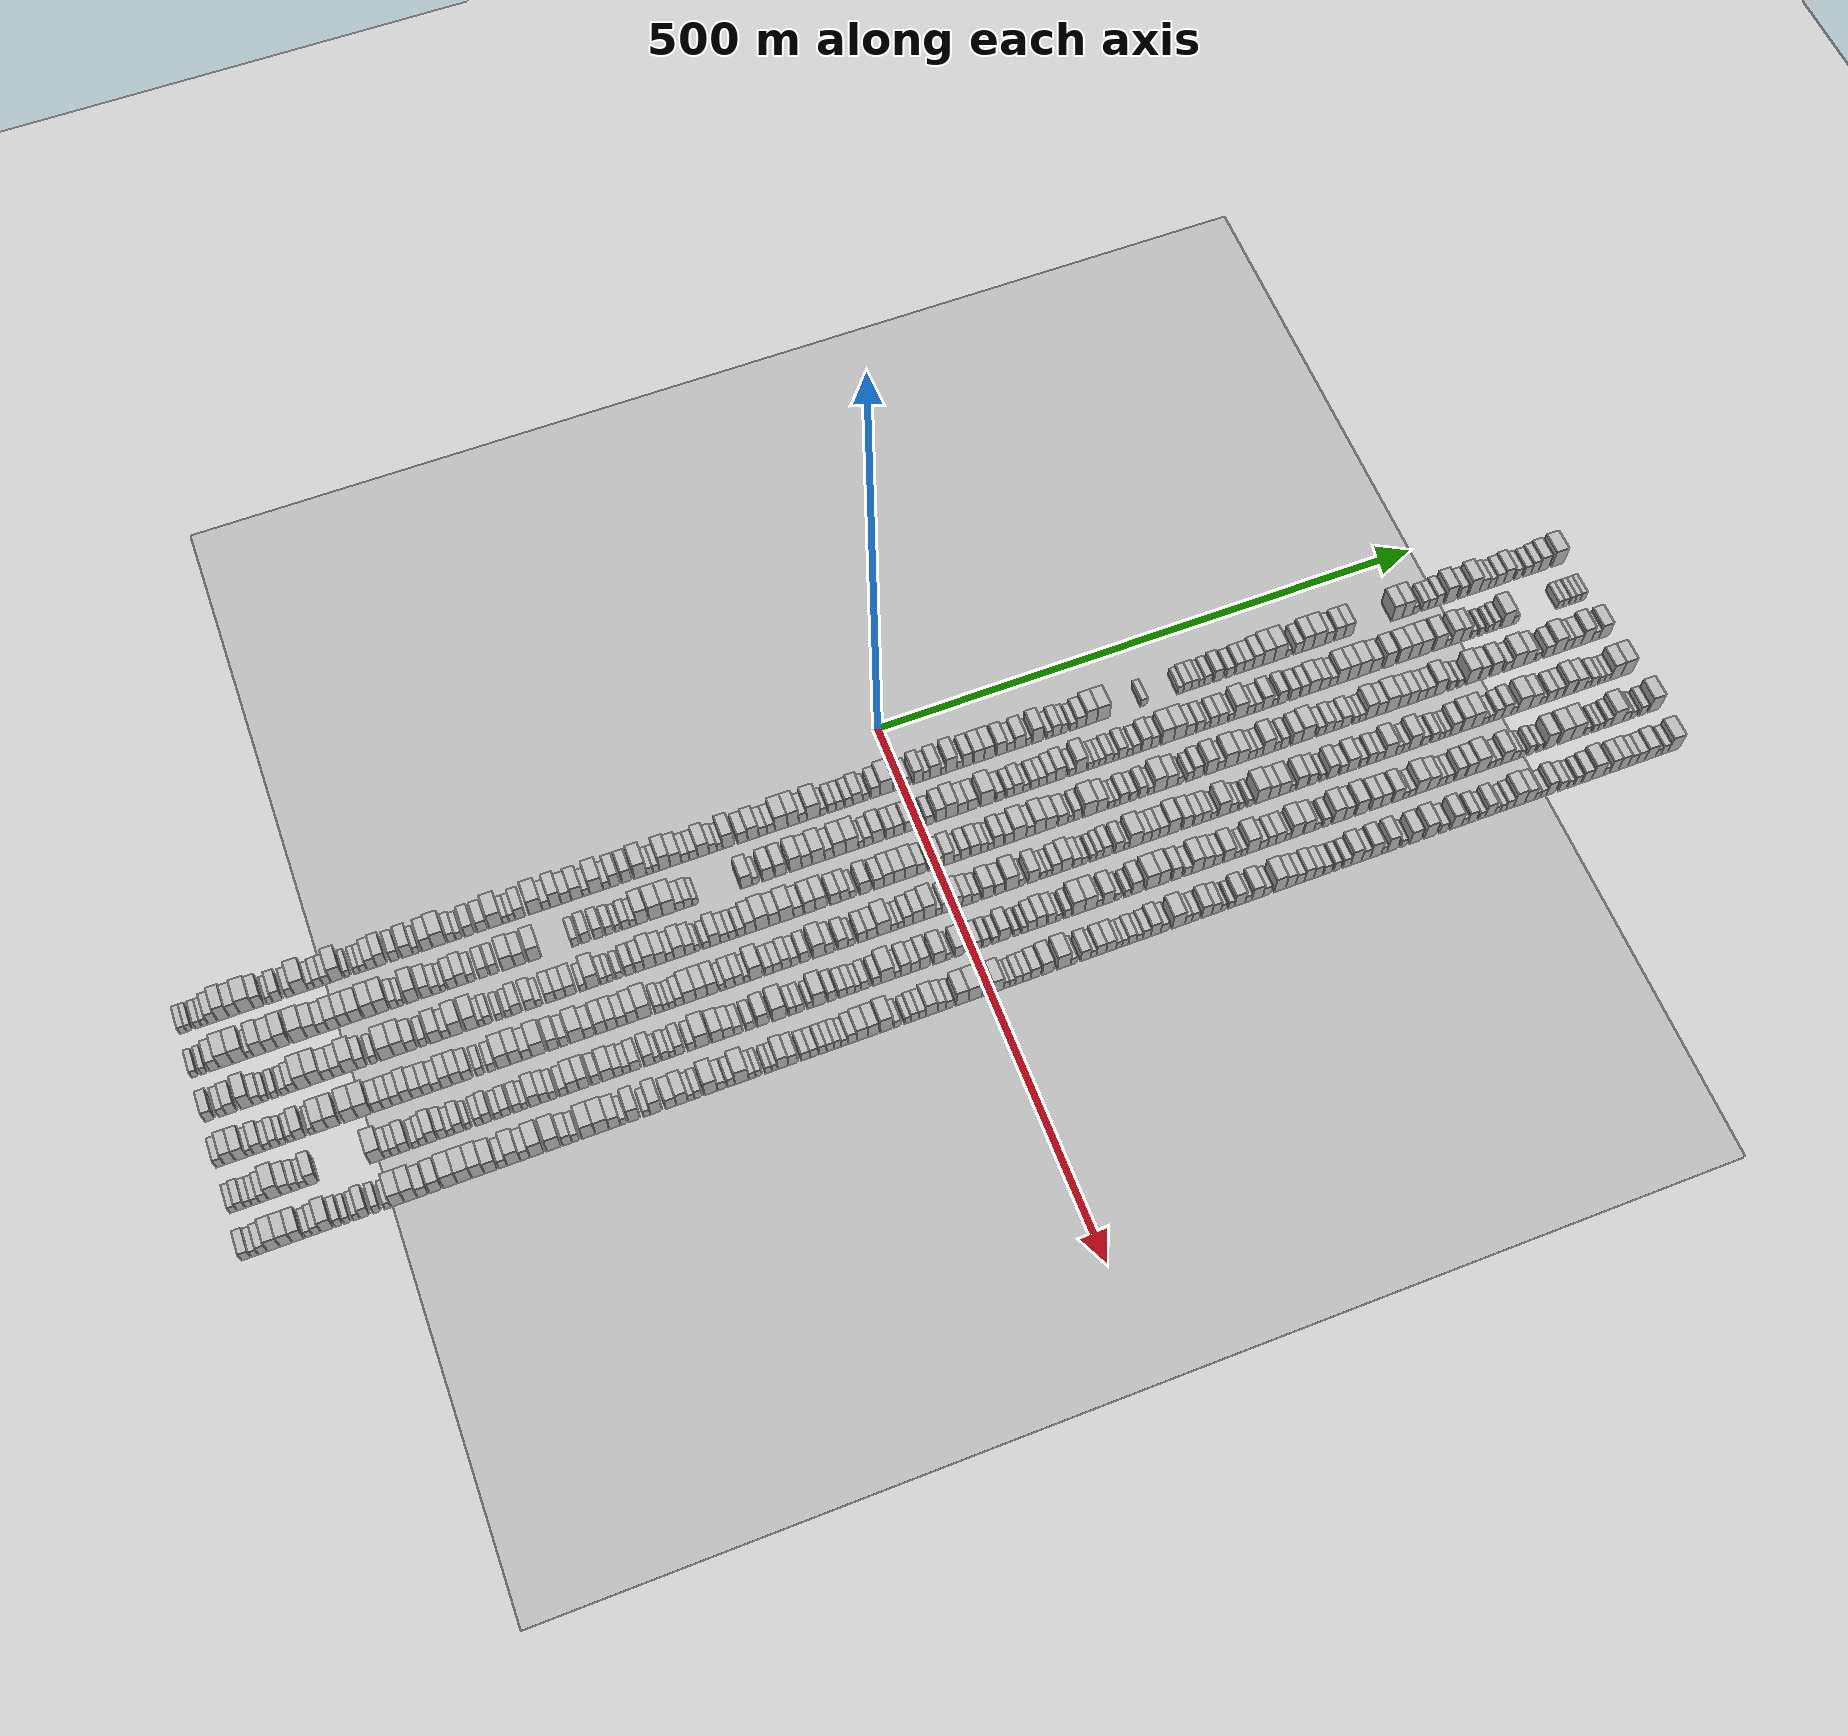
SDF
<?xml version="1.0" encoding="utf-8"?>

<sdf version="1.6">

   <world name="default">

      <gui fullscreen="0">

         <camera name="user_camera">

            <pose>-15 0 4.57585 0 0 0</pose>

            <view_controller>orbit</view_controller>

         </camera>

      </gui>

      <scene>

         <sky>

           <clouds>

             <speed>12</speed>

           </clouds>

         </sky>

         <ambient>0.4 0.4 0.4 1</ambient>

         <background>0.7 0.7 0.7 1</background>

         <shadows>1</shadows>

      </scene>

      <gravity>0 0 -9.8066</gravity>

      <magnetic_field>6e-06 2.3e-05 -4.2e-05</magnetic_field>

      <physics default="0" name="default_physics" type="ode">

         <ode>

            <solver>

               <type>quick</type>

               <iters>10</iters>

               <sor>1.0</sor>

               <use_dynamic_moi_rescaling>0</use_dynamic_moi_rescaling>

            </solver>

            <constraints>

               <cfm>0</cfm>

               <erp>0.2</erp>

               <contact_max_correcting_vel>100</contact_max_correcting_vel>

               <contact_surface_layer>0.001</contact_surface_layer>

            </constraints>

         </ode>

         <max_step_size>0.004</max_step_size>

         <real_time_factor>1</real_time_factor>

         <real_time_update_rate>250</real_time_update_rate>

      </physics>

      <light name="sun" type="directional">

         <cast_shadows>1</cast_shadows>

         <pose>0 0 10 0 0 0</pose>

         <diffuse>0.8 0.8 0.8 1</diffuse>

         <specular>0.2 0.2 0.2 1</specular>

         <attenuation>

            <range>1000</range>

            <constant>0.9</constant>

            <linear>0.01</linear>

            <quadratic>0.001</quadratic>

         </attenuation>

         <direction>-0.5 0.1 -0.9</direction>

      </light>

      <include>

         <name>ground_plane_1</name>

         <uri>model://HANNAS_ground_plane</uri>

         <pose>0 0 0  0 0 0</pose>

      </include>

      <include>

         <name>ground_plane_2</name>

         <uri>model://HANNAS_ground_plane</uri>

         <pose>100 0 0  0 0 0</pose>

      </include>

      <model name="building_1">

         <static>1</static>

         <pose frame="">50.0000 -617.1539 0 0.000000 0.000000 0.000000</pose>

         <link name="link">

            <pose frame="">0 0 6.00 0 0 0</pose>

            <collision name="collision">

               <geometry>

                  <box>

                     <size>20.0000 5.6922 12.0000</size>

                  </box>

               </geometry>

               <max_contacts>10</max_contacts>

               <surface>

                  <contact>

                     <ode/>

                  </contact>

                  <bounce/>

                  <friction>

                     <torsional>

                        <ode/>

                     </torsional>

                     <ode/>

                  </friction>

               </surface>

            </collision>

            <visual name="visual">

               <cast_shadows>0</cast_shadows>

               <geometry>

                  <box>

                     <size>20.0000 5.6922 12.0000</size>

                  </box>

               </geometry>

               <material>

                  <script>

                     <uri>model://HANNAS_wall/materials/scripts</uri>

                     <uri>model://HANNAS_wall/materials/textures</uri>

                     <name>vrc/HANNAS_wall</name>

                  </script>

               </material>

            </visual>

            <self_collide>0</self_collide>

            <enable_wind>0</enable_wind>

            <kinematic>0</kinematic>

         </link>

      </model>

      <model name="building_2">

         <static>1</static>

         <pose frame="">50.0000 -611.8225 0 0.000000 0.000000 0.000000</pose>

         <link name="link">

            <pose frame="">0 0 6.00 0 0 0</pose>

            <collision name="collision">

               <geometry>

                  <box>

                     <size>20.0000 4.9706 12.0000</size>

                  </box>

               </geometry>

               <max_contacts>10</max_contacts>

               <surface>

                  <contact>

                     <ode/>

                  </contact>

                  <bounce/>

                  <friction>

                     <torsional>

                        <ode/>

                     </torsional>

                     <ode/>

                  </friction>

               </surface>

            </collision>

            <visual name="visual">

               <cast_shadows>0</cast_shadows>

               <geometry>

                  <box>

                     <size>20.0000 4.9706 12.0000</size>

                  </box>

               </geometry>

               <material>

                  <script>

                     <uri>model://HANNAS_wall/materials/scripts</uri>

                     <uri>model://HANNAS_wall/materials/textures</uri>

                     <name>vrc/HANNAS_wall</name>

                  </script>

               </material>

            </visual>

            <self_collide>0</self_collide>

            <enable_wind>0</enable_wind>

            <kinematic>0</kinematic>

         </link>

      </model>

      <model name="building_3">

         <static>1</static>

         <pose frame="">50.0000 -604.5954 0 0.000000 0.000000 0.000000</pose>

         <link name="link">

            <pose frame="">0 0 6.00 0 0 0</pose>

            <collision name="collision">

               <geometry>

                  <box>

                     <size>20.0000 5.4835 12.0000</size>

                  </box>

               </geometry>

               <max_contacts>10</max_contacts>

               <surface>

                  <contact>

                     <ode/>

                  </contact>

                  <bounce/>

                  <friction>

                     <torsional>

                        <ode/>

                     </torsional>

                     <ode/>

                  </friction>

               </surface>

            </collision>

            <visual name="visual">

               <cast_shadows>0</cast_shadows>

               <geometry>

                  <box>

                     <size>20.0000 5.4835 12.0000</size>

                  </box>

               </geometry>

               <material>

                  <script>

                     <uri>model://HANNAS_wall/materials/scripts</uri>

                     <uri>model://HANNAS_wall/materials/textures</uri>

                     <name>vrc/HANNAS_wall</name>

                  </script>

               </material>

            </visual>

            <self_collide>0</self_collide>

            <enable_wind>0</enable_wind>

            <kinematic>0</kinematic>

         </link>

      </model>

      <model name="building_4">

         <static>1</static>

         <pose frame="">50.0000 -599.3348 0 0.000000 0.000000 0.000000</pose>

         <link name="link">

            <pose frame="">0 0 6.00 0 0 0</pose>

            <collision name="collision">

               <geometry>

                  <box>

                     <size>20.0000 5.0378 12.0000</size>

                  </box>

               </geometry>

               <max_contacts>10</max_contacts>

               <surface>

                  <contact>

                     <ode/>

                  </contact>

                  <bounce/>

                  <friction>

                     <torsional>

                        <ode/>

                     </torsional>

                     <ode/>

                  </friction>

               </surface>

            </collision>

            <visual name="visual">

               <cast_shadows>0</cast_shadows>

               <geometry>

                  <box>

                     <size>20.0000 5.0378 12.0000</size>

                  </box>

               </geometry>

               <material>

                  <script>

                     <uri>model://HANNAS_wall/materials/scripts</uri>

                     <uri>model://HANNAS_wall/materials/textures</uri>

                     <name>vrc/HANNAS_wall</name>

                  </script>

               </material>

            </visual>

            <self_collide>0</self_collide>

            <enable_wind>0</enable_wind>

            <kinematic>0</kinematic>

         </link>

      </model>

      <model name="building_5">

         <static>1</static>

         <pose frame="">50.0000 -592.9077 0 0.000000 0.000000 0.000000</pose>

         <link name="link">

            <pose frame="">0 0 9.00 0 0 0</pose>

            <collision name="collision">

               <geometry>

                  <box>

                     <size>20.0000 7.8165 18.0000</size>

                  </box>

               </geometry>

               <max_contacts>10</max_contacts>

               <surface>

                  <contact>

                     <ode/>

                  </contact>

                  <bounce/>

                  <friction>

                     <torsional>

                        <ode/>

                     </torsional>

                     <ode/>

                  </friction>

               </surface>

            </collision>

            <visual name="visual">

               <cast_shadows>0</cast_shadows>

               <geometry>

                  <box>

                     <size>20.0000 7.8165 18.0000</size>

                  </box>

               </geometry>

               <material>

                  <script>

                     <uri>model://HANNAS_wall/materials/scripts</uri>

                     <uri>model://HANNAS_wall/materials/textures</uri>

                     <name>vrc/HANNAS_wall</name>

                  </script>

               </material>

            </visual>

            <self_collide>0</self_collide>

            <enable_wind>0</enable_wind>

            <kinematic>0</kinematic>

         </link>

      </model>

      <model name="building_6">

         <static>1</static>

         <pose frame="">50.0000 -584.1828 0 0.000000 0.000000 0.000000</pose>

         <link name="link">

            <pose frame="">0 0 12.00 0 0 0</pose>

            <collision name="collision">

               <geometry>

                  <box>

                     <size>20.0000 9.6333 24.0000</size>

                  </box>

               </geometry>

               <max_contacts>10</max_contacts>

               <surface>

                  <contact>

                     <ode/>

                  </contact>

                  <bounce/>

                  <friction>

                     <torsional>

                        <ode/>

                     </torsional>

                     <ode/>

                  </friction>

               </surface>

            </collision>

            <visual name="visual">

               <cast_shadows>0</cast_shadows>

               <geometry>

                  <box>

                     <size>20.0000 9.6333 24.0000</size>

                  </box>

               </geometry>

               <material>

                  <script>

                     <uri>model://HANNAS_wall/materials/scripts</uri>

                     <uri>model://HANNAS_wall/materials/textures</uri>

                     <name>vrc/HANNAS_wall</name>

                  </script>

               </material>

            </visual>

            <self_collide>0</self_collide>

            <enable_wind>0</enable_wind>

            <kinematic>0</kinematic>

         </link>

      </model>

      <model name="building_7">

         <static>1</static>

         <pose frame="">50.0000 -575.0183 0 0.000000 0.000000 0.000000</pose>

         <link name="link">

            <pose frame="">0 0 10.50 0 0 0</pose>

            <collision name="collision">

               <geometry>

                  <box>

                     <size>20.0000 8.6957 21.0000</size>

                  </box>

               </geometry>

               <max_contacts>10</max_contacts>

               <surface>

                  <contact>

                     <ode/>

                  </contact>

                  <bounce/>

                  <friction>

                     <torsional>

                        <ode/>

                     </torsional>

                     <ode/>

                  </friction>

               </surface>

            </collision>

            <visual name="visual">

               <cast_shadows>0</cast_shadows>

               <geometry>

                  <box>

                     <size>20.0000 8.6957 21.0000</size>

                  </box>

               </geometry>

               <material>

                  <script>

                     <uri>model://HANNAS_wall/materials/scripts</uri>

                     <uri>model://HANNAS_wall/materials/textures</uri>

                     <name>vrc/HANNAS_wall</name>

                  </script>

               </material>

            </visual>

            <self_collide>0</self_collide>

            <enable_wind>0</enable_wind>

            <kinematic>0</kinematic>

         </link>

      </model>

      <model name="building_8">

         <static>1</static>

         <pose frame="">50.0000 -564.7287 0 0.000000 0.000000 0.000000</pose>

         <link name="link">

            <pose frame="">0 0 12.00 0 0 0</pose>

            <collision name="collision">

               <geometry>

                  <box>

                     <size>20.0000 11.8835 24.0000</size>

                  </box>

               </geometry>

               <max_contacts>10</max_contacts>

               <surface>

                  <contact>

                     <ode/>

                  </contact>

                  <bounce/>

                  <friction>

                     <torsional>

                        <ode/>

                     </torsional>

                     <ode/>

                  </friction>

               </surface>

            </collision>

            <visual name="visual">

               <cast_shadows>0</cast_shadows>

               <geometry>

                  <box>

                     <size>20.0000 11.8835 24.0000</size>

                  </box>

               </geometry>

               <material>

                  <script>

                     <uri>model://HANNAS_wall/materials/scripts</uri>

                     <uri>model://HANNAS_wall/materials/textures</uri>

                     <name>vrc/HANNAS_wall</name>

                  </script>

               </material>

            </visual>

            <self_collide>0</self_collide>

            <enable_wind>0</enable_wind>

            <kinematic>0</kinematic>

         </link>

      </model>

      <model name="building_9">

         <static>1</static>

         <pose frame="">50.0000 -554.5336 0 0.000000 0.000000 0.000000</pose>

         <link name="link">

            <pose frame="">0 0 10.50 0 0 0</pose>

            <collision name="collision">

               <geometry>

                  <box>

                     <size>20.0000 8.5068 21.0000</size>

                  </box>

               </geometry>

               <max_contacts>10</max_contacts>

               <surface>

                  <contact>

                     <ode/>

                  </contact>

                  <bounce/>

                  <friction>

                     <torsional>

                        <ode/>

                     </torsional>

                     <ode/>

                  </friction>

               </surface>

            </collision>

            <visual name="visual">

               <cast_shadows>0</cast_shadows>

               <geometry>

                  <box>

                     <size>20.0000 8.5068 21.0000</size>

                  </box>

               </geometry>

               <material>

                  <script>

                     <uri>model://HANNAS_wall/materials/scripts</uri>

                     <uri>model://HANNAS_wall/materials/textures</uri>

                     <name>vrc/HANNAS_wall</name>

                  </script>

               </material>

            </visual>

            <self_collide>0</self_collide>

            <enable_wind>0</enable_wind>

            <kinematic>0</kinematic>

         </link>

      </model>

      <model name="building_10">

         <static>1</static>

         <pose frame="">50.0000 -545.7982 0 0.000000 0.000000 0.000000</pose>

         <link name="link">

            <pose frame="">0 0 6.00 0 0 0</pose>

            <collision name="collision">

               <geometry>

                  <box>

                     <size>20.0000 4.9641 12.0000</size>

                  </box>

               </geometry>

               <max_contacts>10</max_contacts>

               <surface>

                  <contact>

                     <ode/>

                  </contact>

                  <bounce/>

                  <friction>

                     <torsional>

                        <ode/>

                     </torsional>

                     <ode/>

                  </friction>

               </surface>

            </collision>

            <visual name="visual">

               <cast_shadows>0</cast_shadows>

               <geometry>

                  <box>

                     <size>20.0000 4.9641 12.0000</size>

                  </box>

               </geometry>

               <material>

                  <script>

                     <uri>model://HANNAS_wall/materials/scripts</uri>

                     <uri>model://HANNAS_wall/materials/textures</uri>

                     <name>vrc/HANNAS_wall</name>

                  </script>

               </material>

            </visual>

            <self_collide>0</self_collide>

            <enable_wind>0</enable_wind>

            <kinematic>0</kinematic>

         </link>

      </model>

      <model name="building_11">

         <static>1</static>

         <pose frame="">50.0000 -539.3465 0 0.000000 0.000000 0.000000</pose>

         <link name="link">

            <pose frame="">0 0 9.00 0 0 0</pose>

            <collision name="collision">

               <geometry>

                  <box>

                     <size>20.0000 7.9392 18.0000</size>

                  </box>

               </geometry>

               <max_contacts>10</max_contacts>

               <surface>

                  <contact>

                     <ode/>

                  </contact>

                  <bounce/>

                  <friction>

                     <torsional>

                        <ode/>

                     </torsional>

                     <ode/>

                  </friction>

               </surface>

            </collision>

            <visual name="visual">

               <cast_shadows>0</cast_shadows>

               <geometry>

                  <box>

                     <size>20.0000 7.9392 18.0000</size>

                  </box>

               </geometry>

               <material>

                  <script>

                     <uri>model://HANNAS_wall/materials/scripts</uri>

                     <uri>model://HANNAS_wall/materials/textures</uri>

                     <name>vrc/HANNAS_wall</name>

                  </script>

               </material>

            </visual>

            <self_collide>0</self_collide>

            <enable_wind>0</enable_wind>

            <kinematic>0</kinematic>

         </link>

      </model>

      <model name="building_12">

         <static>1</static>

         <pose frame="">50.0000 -529.0915 0 0.000000 0.000000 0.000000</pose>

         <link name="link">

            <pose frame="">0 0 7.50 0 0 0</pose>

            <collision name="collision">

               <geometry>

                  <box>

                     <size>20.0000 6.5708 15.0000</size>

                  </box>

               </geometry>

               <max_contacts>10</max_contacts>

               <surface>

                  <contact>

                     <ode/>

                  </contact>

                  <bounce/>

                  <friction>

                     <torsional>

                        <ode/>

                     </torsional>

                     <ode/>

                  </friction>

               </surface>

            </collision>

            <visual name="visual">

               <cast_shadows>0</cast_shadows>

               <geometry>

                  <box>

                     <size>20.0000 6.5708 15.0000</size>

                  </box>

               </geometry>

               <material>

                  <script>

                     <uri>model://HANNAS_wall/materials/scripts</uri>

                     <uri>model://HANNAS_wall/materials/textures</uri>

                     <name>vrc/HANNAS_wall</name>

                  </script>

               </material>

            </visual>

            <self_collide>0</self_collide>

            <enable_wind>0</enable_wind>

            <kinematic>0</kinematic>

         </link>

      </model>

      <model name="building_13">

         <static>1</static>

         <pose frame="">50.0000 -519.9002 0 0.000000 0.000000 0.000000</pose>

         <link name="link">

            <pose frame="">0 0 12.00 0 0 0</pose>

            <collision name="collision">

               <geometry>

                  <box>

                     <size>20.0000 11.8119 24.0000</size>

                  </box>

               </geometry>

               <max_contacts>10</max_contacts>

               <surface>

                  <contact>

                     <ode/>

                  </contact>

                  <bounce/>

                  <friction>

                     <torsional>

                        <ode/>

                     </torsional>

                     <ode/>

                  </friction>

               </surface>

            </collision>

            <visual name="visual">

               <cast_shadows>0</cast_shadows>

               <geometry>

                  <box>

                     <size>20.0000 11.8119 24.0000</size>

                  </box>

               </geometry>

               <material>

                  <script>

                     <uri>model://HANNAS_wall/materials/scripts</uri>

                     <uri>model://HANNAS_wall/materials/textures</uri>

                     <name>vrc/HANNAS_wall</name>

                  </script>

               </material>

            </visual>

            <self_collide>0</self_collide>

            <enable_wind>0</enable_wind>

            <kinematic>0</kinematic>

         </link>

      </model>

      <model name="building_14">

         <static>1</static>

         <pose frame="">50.0000 -511.3125 0 0.000000 0.000000 0.000000</pose>

         <link name="link">

            <pose frame="">0 0 6.00 0 0 0</pose>

            <collision name="collision">

               <geometry>

                  <box>

                     <size>20.0000 5.3634 12.0000</size>

                  </box>

               </geometry>

               <max_contacts>10</max_contacts>

               <surface>

                  <contact>

                     <ode/>

                  </contact>

                  <bounce/>

                  <friction>

                     <torsional>

                        <ode/>

                     </torsional>

                     <ode/>

                  </friction>

               </surface>

            </collision>

            <visual name="visual">

               <cast_shadows>0</cast_shadows>

               <geometry>

                  <box>

                     <size>20.0000 5.3634 12.0000</size>

                  </box>

               </geometry>

               <material>

                  <script>

                     <uri>model://HANNAS_wall/materials/scripts</uri>

                     <uri>model://HANNAS_wall/materials/textures</uri>

                     <name>vrc/HANNAS_wall</name>

                  </script>

               </material>

            </visual>

            <self_collide>0</self_collide>

            <enable_wind>0</enable_wind>

            <kinematic>0</kinematic>

         </link>

      </model>

      <model name="building_15">

         <static>1</static>

         <pose frame="">50.0000 -505.2120 0 0.000000 0.000000 0.000000</pose>

         <link name="link">

            <pose frame="">0 0 7.50 0 0 0</pose>

            <collision name="collision">

               <geometry>

                  <box>

                     <size>20.0000 6.8375 15.0000</size>

                  </box>

               </geometry>

               <max_contacts>10</max_contacts>

               <surface>

                  <contact>

                     <ode/>

                  </contact>

                  <bounce/>

                  <friction>

                     <torsional>

                        <ode/>

                     </torsional>

                     <ode/>

                  </friction>

               </surface>

            </collision>

            <visual name="visual">

               <cast_shadows>0</cast_shadows>

               <geometry>

                  <box>

                     <size>20.0000 6.8375 15.0000</size>

                  </box>

               </geometry>

               <material>

                  <script>

                     <uri>model://HANNAS_wall/materials/scripts</uri>

                     <uri>model://HANNAS_wall/materials/textures</uri>

                     <name>vrc/HANNAS_wall</name>

                  </script>

               </material>

            </visual>

            <self_collide>0</self_collide>

            <enable_wind>0</enable_wind>

            <kinematic>0</kinematic>

         </link>

      </model>

      <model name="building_16">

         <static>1</static>

         <pose frame="">50.0000 -498.5266 0 0.000000 0.000000 0.000000</pose>

         <link name="link">

            <pose frame="">0 0 7.50 0 0 0</pose>

            <collision name="collision">

               <geometry>

                  <box>

                     <size>20.0000 6.5335 15.0000</size>

                  </box>

               </geometry>

               <max_contacts>10</max_contacts>

               <surface>

                  <contact>

                     <ode/>

                  </contact>

                  <bounce/>

                  <friction>

                     <torsional>

                        <ode/>

                     </torsional>

                     <ode/>

                  </friction>

               </surface>

            </collision>

            <visual name="visual">

               <cast_shadows>0</cast_shadows>

               <geometry>

                  <box>

                     <size>20.0000 6.5335 15.0000</size>

                  </box>

               </geometry>

               <material>

                  <script>

                     <uri>model://HANNAS_wall/materials/scripts</uri>

                     <uri>model://HANNAS_wall/materials/textures</uri>

                     <name>vrc/HANNAS_wall</name>

                  </script>

               </material>

            </visual>

            <self_collide>0</self_collide>

            <enable_wind>0</enable_wind>

            <kinematic>0</kinematic>

         </link>

      </model>

      <model name="building_17">

         <static>1</static>

         <pose frame="">50.0000 -489.9047 0 0.000000 0.000000 0.000000</pose>

         <link name="link">

            <pose frame="">0 0 12.00 0 0 0</pose>

            <collision name="collision">

               <geometry>

                  <box>

                     <size>20.0000 10.7103 24.0000</size>

                  </box>

               </geometry>

               <max_contacts>10</max_contacts>

               <surface>

                  <contact>

                     <ode/>

                  </contact>

                  <bounce/>

                  <friction>

                     <torsional>

                        <ode/>

                     </torsional>

                     <ode/>

                  </friction>

               </surface>

            </collision>

            <visual name="visual">

               <cast_shadows>0</cast_shadows>

               <geometry>

                  <box>

                     <size>20.0000 10.7103 24.0000</size>

                  </box>

               </geometry>

               <material>

                  <script>

                     <uri>model://HANNAS_wall/materials/scripts</uri>

                     <uri>model://HANNAS_wall/materials/textures</uri>

                     <name>vrc/HANNAS_wall</name>

                  </script>

               </material>

            </visual>

            <self_collide>0</self_collide>

            <enable_wind>0</enable_wind>

            <kinematic>0</kinematic>

         </link>

      </model>

      <model name="building_18">

         <static>1</static>

         <pose frame="">50.0000 -481.0667 0 0.000000 0.000000 0.000000</pose>

         <link name="link">

            <pose frame="">0 0 6.00 0 0 0</pose>

            <collision name="collision">

               <geometry>

                  <box>

                     <size>20.0000 4.9658 12.0000</size>

                  </box>

               </geometry>

               <max_contacts>10</max_contacts>

               <surface>

                  <contact>

                     <ode/>

                  </contact>

                  <bounce/>

                  <friction>

                     <torsional>

                        <ode/>

                     </torsional>

                     <ode/>

                  </friction>

               </surface>

            </collision>

            <visual name="visual">

               <cast_shadows>0</cast_shadows>

               <geometry>

                  <box>

                     <size>20.0000 4.9658 12.0000</size>

                  </box>

               </geometry>

               <material>

                  <script>

                     <uri>model://HANNAS_wall/materials/scripts</uri>

                     <uri>model://HANNAS_wall/materials/textures</uri>

                     <name>vrc/HANNAS_wall</name>

                  </script>

               </material>

            </visual>

            <self_collide>0</self_collide>

            <enable_wind>0</enable_wind>

            <kinematic>0</kinematic>

         </link>

      </model>

      <model name="building_19">

         <static>1</static>

         <pose frame="">50.0000 -473.1703 0 0.000000 0.000000 0.000000</pose>

         <link name="link">

            <pose frame="">0 0 6.00 0 0 0</pose>

            <collision name="collision">

               <geometry>

                  <box>

                     <size>20.0000 4.8270 12.0000</size>

                  </box>

               </geometry>

               <max_contacts>10</max_contacts>

               <surface>

                  <contact>

                     <ode/>

                  </contact>

                  <bounce/>

                  <friction>

                     <torsional>

                        <ode/>

                     </torsional>

                     <ode/>

                  </friction>

               </surface>

            </collision>

            <visual name="visual">

               <cast_shadows>0</cast_shadows>

               <geometry>

                  <box>

                     <size>20.0000 4.8270 12.0000</size>

                  </box>

               </geometry>

               <material>

                  <script>

                     <uri>model://HANNAS_wall/materials/scripts</uri>

                     <uri>model://HANNAS_wall/materials/textures</uri>

                     <name>vrc/HANNAS_wall</name>

                  </script>

               </material>

            </visual>

            <self_collide>0</self_collide>

            <enable_wind>0</enable_wind>

            <kinematic>0</kinematic>

         </link>

      </model>

      <model name="building_20">

         <static>1</static>

         <pose frame="">50.0000 -467.9310 0 0.000000 0.000000 0.000000</pose>

         <link name="link">

            <pose frame="">0 0 6.00 0 0 0</pose>

            <collision name="collision">

               <geometry>

                  <box>

                     <size>20.0000 5.6515 12.0000</size>

                  </box>

               </geometry>

               <max_contacts>10</max_contacts>

               <surface>

                  <contact>

                     <ode/>

                  </contact>

                  <bounce/>

                  <friction>

                     <torsional>

                        <ode/>

                     </torsional>

                     <ode/>

                  </friction>

               </surface>

            </collision>

            <visual name="visual">

               <cast_shadows>0</cast_shadows>

               <geometry>

                  <box>

                     <size>20.0000 5.6515 12.0000</size>

                  </box>

               </geometry>

               <material>

                  <script>

                     <uri>model://HANNAS_wall/materials/scripts</uri>

                     <uri>model://HANNAS_wall/materials/textures</uri>

                     <name>vrc/HANNAS_wall</name>

                  </script>

               </material>

            </visual>

            <self_collide>0</self_collide>

            <enable_wind>0</enable_wind>

            <kinematic>0</kinematic>

         </link>

      </model>

      <model name="building_21">

         <static>1</static>

         <pose frame="">50.0000 -461.0564 0 0.000000 0.000000 0.000000</pose>

         <link name="link">

            <pose frame="">0 0 9.00 0 0 0</pose>

            <collision name="collision">

               <geometry>

                  <box>

                     <size>20.0000 8.0976 18.0000</size>

                  </box>

               </geometry>

               <max_contacts>10</max_contacts>

               <surface>

                  <contact>

                     <ode/>

                  </contact>

                  <bounce/>

                  <friction>

                     <torsional>

                        <ode/>

                     </torsional>

                     <ode/>

                  </friction>

               </surface>

            </collision>

            <visual name="visual">

               <cast_shadows>0</cast_shadows>

               <geometry>

                  <box>

                     <size>20.0000 8.0976 18.0000</size>

                  </box>

               </geometry>

               <material>

                  <script>

                     <uri>model://HANNAS_wall/materials/scripts</uri>

                     <uri>model://HANNAS_wall/materials/textures</uri>

                     <name>vrc/HANNAS_wall</name>

                  </script>

               </material>

            </visual>

            <self_collide>0</self_collide>

            <enable_wind>0</enable_wind>

            <kinematic>0</kinematic>

         </link>

      </model>

      <model name="building_22">

         <static>1</static>

         <pose frame="">50.0000 -452.6299 0 0.000000 0.000000 0.000000</pose>

         <link name="link">

            <pose frame="">0 0 10.50 0 0 0</pose>

            <collision name="collision">

               <geometry>

                  <box>

                     <size>20.0000 8.7554 21.0000</size>

                  </box>

               </geometry>

               <max_contacts>10</max_contacts>

               <surface>

                  <contact>

                     <ode/>

                  </contact>

                  <bounce/>

                  <friction>

                     <torsional>

                        <ode/>

                     </torsional>

                     <ode/>

                  </friction>

               </surface>

            </collision>

            <visual name="visual">

               <cast_shadows>0</cast_shadows>

               <geometry>

                  <box>

                     <size>20.0000 8.7554 21.0000</size>

                  </box>

               </geometry>

               <material>

                  <script>

                     <uri>model://HANNAS_wall/materials/scripts</uri>

                     <uri>model://HANNAS_wall/materials/textures</uri>

                     <name>vrc/HANNAS_wall</name>

                  </script>

               </material>

            </visual>

            <self_collide>0</self_collide>

            <enable_wind>0</enable_wind>

            <kinematic>0</kinematic>

         </link>

      </model>

      <model name="building_23">

         <static>1</static>

         <pose frame="">50.0000 -441.4818 0 0.000000 0.000000 0.000000</pose>

         <link name="link">

            <pose frame="">0 0 9.00 0 0 0</pose>

            <collision name="collision">

               <geometry>

                  <box>

                     <size>20.0000 7.5407 18.0000</size>

                  </box>

               </geometry>

               <max_contacts>10</max_contacts>

               <surface>

                  <contact>

                     <ode/>

                  </contact>

                  <bounce/>

                  <friction>

                     <torsional>

                        <ode/>

                     </torsional>

                     <ode/>

                  </friction>

               </surface>

            </collision>

            <visual name="visual">

               <cast_shadows>0</cast_shadows>

               <geometry>

                  <box>

                     <size>20.0000 7.5407 18.0000</size>

                  </box>

               </geometry>

               <material>

                  <script>

                     <uri>model://HANNAS_wall/materials/scripts</uri>

                     <uri>model://HANNAS_wall/materials/textures</uri>

                     <name>vrc/HANNAS_wall</name>

                  </script>

               </material>

            </visual>

            <self_collide>0</self_collide>

            <enable_wind>0</enable_wind>

            <kinematic>0</kinematic>

         </link>

      </model>

      <model name="building_24">

         <static>1</static>

         <pose frame="">50.0000 -430.9669 0 0.000000 0.000000 0.000000</pose>

         <link name="link">

            <pose frame="">0 0 10.50 0 0 0</pose>

            <collision name="collision">

               <geometry>

                  <box>

                     <size>20.0000 9.4891 21.0000</size>

                  </box>

               </geometry>

               <max_contacts>10</max_contacts>

               <surface>

                  <contact>

                     <ode/>

                  </contact>

                  <bounce/>

                  <friction>

                     <torsional>

                        <ode/>

                     </torsional>

                     <ode/>

                  </friction>

               </surface>

            </collision>

            <visual name="visual">

               <cast_shadows>0</cast_shadows>

               <geometry>

                  <box>

                     <size>20.0000 9.4891 21.0000</size>

                  </box>

               </geometry>

               <material>

                  <script>

                     <uri>model://HANNAS_wall/materials/scripts</uri>

                     <uri>model://HANNAS_wall/materials/textures</uri>

                     <name>vrc/HANNAS_wall</name>

                  </script>

               </material>

            </visual>

            <self_collide>0</self_collide>

            <enable_wind>0</enable_wind>

            <kinematic>0</kinematic>

         </link>

      </model>

      <model name="building_25">

         <static>1</static>

         <pose frame="">50.0000 -423.5826 0 0.000000 0.000000 0.000000</pose>

         <link name="link">

            <pose frame="">0 0 6.00 0 0 0</pose>

            <collision name="collision">

               <geometry>

                  <box>

                     <size>20.0000 5.2797 12.0000</size>

                  </box>

               </geometry>

               <max_contacts>10</max_contacts>

               <surface>

                  <contact>

                     <ode/>

                  </contact>

                  <bounce/>

                  <friction>

                     <torsional>

                        <ode/>

                     </torsional>

                     <ode/>

                  </friction>

               </surface>

            </collision>

            <visual name="visual">

               <cast_shadows>0</cast_shadows>

               <geometry>

                  <box>

                     <size>20.0000 5.2797 12.0000</size>

                  </box>

               </geometry>

               <material>

                  <script>

                     <uri>model://HANNAS_wall/materials/scripts</uri>

                     <uri>model://HANNAS_wall/materials/textures</uri>

                     <name>vrc/HANNAS_wall</name>

                  </script>

               </material>

            </visual>

            <self_collide>0</self_collide>

            <enable_wind>0</enable_wind>

            <kinematic>0</kinematic>

         </link>

      </model>

      <model name="building_26">

         <static>1</static>

         <pose frame="">50.0000 -414.3899 0 0.000000 0.000000 0.000000</pose>

         <link name="link">

            <pose frame="">0 0 10.50 0 0 0</pose>

            <collision name="collision">

               <geometry>

                  <box>

                     <size>20.0000 9.1056 21.0000</size>

                  </box>

               </geometry>

               <max_contacts>10</max_contacts>

               <surface>

                  <contact>

                     <ode/>

                  </contact>

                  <bounce/>

                  <friction>

                     <torsional>

                        <ode/>

                     </torsional>

                     <ode/>

                  </friction>

               </surface>

            </collision>

            <visual name="visual">

               <cast_shadows>0</cast_shadows>

               <geometry>

                  <box>

                     <size>20.0000 9.1056 21.0000</size>

                  </box>

               </geometry>

               <material>

                  <script>

                     <uri>model://HANNAS_wall/materials/scripts</uri>

                     <uri>model://HANNAS_wall/materials/textures</uri>

                     <name>vrc/HANNAS_wall</name>

                  </script>

               </material>

            </visual>

            <self_collide>0</self_collide>

            <enable_wind>0</enable_wind>

            <kinematic>0</kinematic>

         </link>

      </model>

      <model name="building_27">

         <static>1</static>

         <pose frame="">50.0000 -404.0000 0 0.000000 0.000000 0.000000</pose>

         <link name="link">

            <pose frame="">0 0 12.00 0 0 0</pose>

            <collision name="collision">

               <geometry>

                  <box>

                     <size>20.0000 11.6743 24.0000</size>

                  </box>

               </geometry>

               <max_contacts>10</max_contacts>

               <surface>

                  <contact>

                     <ode/>

                  </contact>

                  <bounce/>

                  <friction>

                     <torsional>

                        <ode/>

                     </torsional>

                     <ode/>

                  </friction>

               </surface>

            </collision>

            <visual name="visual">

               <cast_shadows>0</cast_shadows>

               <geometry>

                  <box>

                     <size>20.0000 11.6743 24.0000</size>

                  </box>

               </geometry>

               <material>

                  <script>

                     <uri>model://HANNAS_wall/materials/scripts</uri>

                     <uri>model://HANNAS_wall/materials/textures</uri>

                     <name>vrc/HANNAS_wall</name>

                  </script>

               </material>

            </visual>

            <self_collide>0</self_collide>

            <enable_wind>0</enable_wind>

            <kinematic>0</kinematic>

         </link>

      </model>

      <model name="building_28">

         <static>1</static>

         <pose frame="">50.0000 -393.7379 0 0.000000 0.000000 0.000000</pose>

         <link name="link">

            <pose frame="">0 0 7.50 0 0 0</pose>

            <collision name="collision">

               <geometry>

                  <box>

                     <size>20.0000 6.8498 15.0000</size>

                  </box>

               </geometry>

               <max_contacts>10</max_contacts>

               <surface>

                  <contact>

                     <ode/>

                  </contact>

                  <bounce/>

                  <friction>

                     <torsional>

                        <ode/>

                     </torsional>

                     <ode/>

                  </friction>

               </surface>

            </collision>

            <visual name="visual">

               <cast_shadows>0</cast_shadows>

               <geometry>

                  <box>

                     <size>20.0000 6.8498 15.0000</size>

                  </box>

               </geometry>

               <material>

                  <script>

                     <uri>model://HANNAS_wall/materials/scripts</uri>

                     <uri>model://HANNAS_wall/materials/textures</uri>

                     <name>vrc/HANNAS_wall</name>

                  </script>

               </material>

            </visual>

            <self_collide>0</self_collide>

            <enable_wind>0</enable_wind>

            <kinematic>0</kinematic>

         </link>

      </model>

      <model name="building_29">

         <static>1</static>

         <pose frame="">50.0000 -387.5442 0 0.000000 0.000000 0.000000</pose>

         <link name="link">

            <pose frame="">0 0 6.00 0 0 0</pose>

            <collision name="collision">

               <geometry>

                  <box>

                     <size>20.0000 5.5376 12.0000</size>

                  </box>

               </geometry>

               <max_contacts>10</max_contacts>

               <surface>

                  <contact>

                     <ode/>

                  </contact>

                  <bounce/>

                  <friction>

                     <torsional>

                        <ode/>

                     </torsional>

                     <ode/>

                  </friction>

               </surface>

            </collision>

            <visual name="visual">

               <cast_shadows>0</cast_shadows>

               <geometry>

                  <box>

                     <size>20.0000 5.5376 12.0000</size>

                  </box>

               </geometry>

               <material>

                  <script>

                     <uri>model://HANNAS_wall/materials/scripts</uri>

                     <uri>model://HANNAS_wall/materials/textures</uri>

                     <name>vrc/HANNAS_wall</name>

                  </script>

               </material>

            </visual>

            <self_collide>0</self_collide>

            <enable_wind>0</enable_wind>

            <kinematic>0</kinematic>

         </link>

      </model>

      <model name="building_30">

         <static>1</static>

         <pose frame="">50.0000 -378.4547 0 0.000000 0.000000 0.000000</pose>

         <link name="link">

            <pose frame="">0 0 9.00 0 0 0</pose>

            <collision name="collision">

               <geometry>

                  <box>

                     <size>20.0000 8.6414 18.0000</size>

                  </box>

               </geometry>

               <max_contacts>10</max_contacts>

               <surface>

                  <contact>

                     <ode/>

                  </contact>

                  <bounce/>

                  <friction>

                     <torsional>

                        <ode/>

                     </torsional>

                     <ode/>

                  </friction>

               </surface>

            </collision>

            <visual name="visual">

               <cast_shadows>0</cast_shadows>

               <geometry>

                  <box>

                     <size>20.0000 8.6414 18.0000</size>

                  </box>

               </geometry>

               <material>

                  <script>

                     <uri>model://HANNAS_wall/materials/scripts</uri>

                     <uri>model://HANNAS_wall/materials/textures</uri>

                     <name>vrc/HANNAS_wall</name>

                  </script>

               </material>

            </visual>

            <self_collide>0</self_collide>

            <enable_wind>0</enable_wind>

            <kinematic>0</kinematic>

         </link>

      </model>

      <model name="building_31">

         <static>1</static>

         <pose frame="">50.0000 -367.6351 0 0.000000 0.000000 0.000000</pose>

         <link name="link">

            <pose frame="">0 0 9.00 0 0 0</pose>

            <collision name="collision">

               <geometry>

                  <box>

                     <size>20.0000 8.9978 18.0000</size>

                  </box>

               </geometry>

               <max_contacts>10</max_contacts>

               <surface>

                  <contact>

                     <ode/>

                  </contact>

                  <bounce/>

                  <friction>

                     <torsional>

                        <ode/>

                     </torsional>

                     <ode/>

                  </friction>

               </surface>

            </collision>

            <visual name="visual">

               <cast_shadows>0</cast_shadows>

               <geometry>

                  <box>

                     <size>20.0000 8.9978 18.0000</size>

                  </box>

               </geometry>

               <material>

                  <script>

                     <uri>model://HANNAS_wall/materials/scripts</uri>

                     <uri>model://HANNAS_wall/materials/textures</uri>

                     <name>vrc/HANNAS_wall</name>

                  </script>

               </material>

            </visual>

            <self_collide>0</self_collide>

            <enable_wind>0</enable_wind>

            <kinematic>0</kinematic>

         </link>

      </model>

      <model name="building_32">

         <static>1</static>

         <pose frame="">50.0000 -356.2664 0 0.000000 0.000000 0.000000</pose>

         <link name="link">

            <pose frame="">0 0 12.00 0 0 0</pose>

            <collision name="collision">

               <geometry>

                  <box>

                     <size>20.0000 11.7396 24.0000</size>

                  </box>

               </geometry>

               <max_contacts>10</max_contacts>

               <surface>

                  <contact>

                     <ode/>

                  </contact>

                  <bounce/>

                  <friction>

                     <torsional>

                        <ode/>

                     </torsional>

                     <ode/>

                  </friction>

               </surface>

            </collision>

            <visual name="visual">

               <cast_shadows>0</cast_shadows>

               <geometry>

                  <box>

                     <size>20.0000 11.7396 24.0000</size>

                  </box>

               </geometry>

               <material>

                  <script>

                     <uri>model://HANNAS_wall/materials/scripts</uri>

                     <uri>model://HANNAS_wall/materials/textures</uri>

                     <name>vrc/HANNAS_wall</name>

                  </script>

               </material>

            </visual>

            <self_collide>0</self_collide>

            <enable_wind>0</enable_wind>

            <kinematic>0</kinematic>

         </link>

      </model>

      <model name="building_33">

         <static>1</static>

         <pose frame="">50.0000 -347.7952 0 0.000000 0.000000 0.000000</pose>

         <link name="link">

            <pose frame="">0 0 6.00 0 0 0</pose>

            <collision name="collision">

               <geometry>

                  <box>

                     <size>20.0000 5.2028 12.0000</size>

                  </box>

               </geometry>

               <max_contacts>10</max_contacts>

               <surface>

                  <contact>

                     <ode/>

                  </contact>

                  <bounce/>

                  <friction>

                     <torsional>

                        <ode/>

                     </torsional>

                     <ode/>

                  </friction>

               </surface>

            </collision>

            <visual name="visual">

               <cast_shadows>0</cast_shadows>

               <geometry>

                  <box>

                     <size>20.0000 5.2028 12.0000</size>

                  </box>

               </geometry>

               <material>

                  <script>

                     <uri>model://HANNAS_wall/materials/scripts</uri>

                     <uri>model://HANNAS_wall/materials/textures</uri>

                     <name>vrc/HANNAS_wall</name>

                  </script>

               </material>

            </visual>

            <self_collide>0</self_collide>

            <enable_wind>0</enable_wind>

            <kinematic>0</kinematic>

         </link>

      </model>

      <model name="building_34">

         <static>1</static>

         <pose frame="">50.0000 -342.5135 0 0.000000 0.000000 0.000000</pose>

         <link name="link">

            <pose frame="">0 0 6.00 0 0 0</pose>

            <collision name="collision">

               <geometry>

                  <box>

                     <size>20.0000 5.3606 12.0000</size>

                  </box>

               </geometry>

               <max_contacts>10</max_contacts>

               <surface>

                  <contact>

                     <ode/>

                  </contact>

                  <bounce/>

                  <friction>

                     <torsional>

                        <ode/>

                     </torsional>

                     <ode/>

                  </friction>

               </surface>

            </collision>

            <visual name="visual">

               <cast_shadows>0</cast_shadows>

               <geometry>

                  <box>

                     <size>20.0000 5.3606 12.0000</size>

                  </box>

               </geometry>

               <material>

                  <script>

                     <uri>model://HANNAS_wall/materials/scripts</uri>

                     <uri>model://HANNAS_wall/materials/textures</uri>

                     <name>vrc/HANNAS_wall</name>

                  </script>

               </material>

            </visual>

            <self_collide>0</self_collide>

            <enable_wind>0</enable_wind>

            <kinematic>0</kinematic>

         </link>

      </model>

      <model name="building_35">

         <static>1</static>

         <pose frame="">50.0000 -335.5263 0 0.000000 0.000000 0.000000</pose>

         <link name="link">

            <pose frame="">0 0 9.00 0 0 0</pose>

            <collision name="collision">

               <geometry>

                  <box>

                     <size>20.0000 8.6137 18.0000</size>

                  </box>

               </geometry>

               <max_contacts>10</max_contacts>

               <surface>

                  <contact>

                     <ode/>

                  </contact>

                  <bounce/>

                  <friction>

                     <torsional>

                        <ode/>

                     </torsional>

                     <ode/>

                  </friction>

               </surface>

            </collision>

            <visual name="visual">

               <cast_shadows>0</cast_shadows>

               <geometry>

                  <box>

                     <size>20.0000 8.6137 18.0000</size>

                  </box>

               </geometry>

               <material>

                  <script>

                     <uri>model://HANNAS_wall/materials/scripts</uri>

                     <uri>model://HANNAS_wall/materials/textures</uri>

                     <name>vrc/HANNAS_wall</name>

                  </script>

               </material>

            </visual>

            <self_collide>0</self_collide>

            <enable_wind>0</enable_wind>

            <kinematic>0</kinematic>

         </link>

      </model>

      <model name="building_36">

         <static>1</static>

         <pose frame="">50.0000 -322.3569 0 0.000000 0.000000 0.000000</pose>

         <link name="link">

            <pose frame="">0 0 12.00 0 0 0</pose>

            <collision name="collision">

               <geometry>

                  <box>

                     <size>20.0000 11.7252 24.0000</size>

                  </box>

               </geometry>

               <max_contacts>10</max_contacts>

               <surface>

                  <contact>

                     <ode/>

                  </contact>

                  <bounce/>

                  <friction>

                     <torsional>

                        <ode/>

                     </torsional>

                     <ode/>

                  </friction>

               </surface>

            </collision>

            <visual name="visual">

               <cast_shadows>0</cast_shadows>

               <geometry>

                  <box>

                     <size>20.0000 11.7252 24.0000</size>

                  </box>

               </geometry>

               <material>

                  <script>

                     <uri>model://HANNAS_wall/materials/scripts</uri>

                     <uri>model://HANNAS_wall/materials/textures</uri>

                     <name>vrc/HANNAS_wall</name>

                  </script>

               </material>

            </visual>

            <self_collide>0</self_collide>

            <enable_wind>0</enable_wind>

            <kinematic>0</kinematic>

         </link>

      </model>

      <model name="building_37">

         <static>1</static>

         <pose frame="">50.0000 -313.2357 0 0.000000 0.000000 0.000000</pose>

         <link name="link">

            <pose frame="">0 0 7.50 0 0 0</pose>

            <collision name="collision">

               <geometry>

                  <box>

                     <size>20.0000 6.5171 15.0000</size>

                  </box>

               </geometry>

               <max_contacts>10</max_contacts>

               <surface>

                  <contact>

                     <ode/>

                  </contact>

                  <bounce/>

                  <friction>

                     <torsional>

                        <ode/>

                     </torsional>

                     <ode/>

                  </friction>

               </surface>

            </collision>

            <visual name="visual">

               <cast_shadows>0</cast_shadows>

               <geometry>

                  <box>

                     <size>20.0000 6.5171 15.0000</size>

                  </box>

               </geometry>

               <material>

                  <script>

                     <uri>model://HANNAS_wall/materials/scripts</uri>

                     <uri>model://HANNAS_wall/materials/textures</uri>

                     <name>vrc/HANNAS_wall</name>

                  </script>

               </material>

            </visual>

            <self_collide>0</self_collide>

            <enable_wind>0</enable_wind>

            <kinematic>0</kinematic>

         </link>

      </model>

      <model name="building_38">

         <static>1</static>

         <pose frame="">50.0000 -305.1698 0 0.000000 0.000000 0.000000</pose>

         <link name="link">

            <pose frame="">0 0 12.00 0 0 0</pose>

            <collision name="collision">

               <geometry>

                  <box>

                     <size>20.0000 9.6145 24.0000</size>

                  </box>

               </geometry>

               <max_contacts>10</max_contacts>

               <surface>

                  <contact>

                     <ode/>

                  </contact>

                  <bounce/>

                  <friction>

                     <torsional>

                        <ode/>

                     </torsional>

                     <ode/>

                  </friction>

               </surface>

            </collision>

            <visual name="visual">

               <cast_shadows>0</cast_shadows>

               <geometry>

                  <box>

                     <size>20.0000 9.6145 24.0000</size>

                  </box>

               </geometry>

               <material>

                  <script>

                     <uri>model://HANNAS_wall/materials/scripts</uri>

                     <uri>model://HANNAS_wall/materials/textures</uri>

                     <name>vrc/HANNAS_wall</name>

                  </script>

               </material>

            </visual>

            <self_collide>0</self_collide>

            <enable_wind>0</enable_wind>

            <kinematic>0</kinematic>

         </link>

      </model>

      <model name="building_39">

         <static>1</static>

         <pose frame="">50.0000 -296.0142 0 0.000000 0.000000 0.000000</pose>

         <link name="link">

            <pose frame="">0 0 9.00 0 0 0</pose>

            <collision name="collision">

               <geometry>

                  <box>

                     <size>20.0000 8.6968 18.0000</size>

                  </box>

               </geometry>

               <max_contacts>10</max_contacts>

               <surface>

                  <contact>

                     <ode/>

                  </contact>

                  <bounce/>

                  <friction>

                     <torsional>

                        <ode/>

                     </torsional>

                     <ode/>

                  </friction>

               </surface>

            </collision>

            <visual name="visual">

               <cast_shadows>0</cast_shadows>

               <geometry>

                  <box>

                     <size>20.0000 8.6968 18.0000</size>

                  </box>

               </geometry>

               <material>

                  <script>

                     <uri>model://HANNAS_wall/materials/scripts</uri>

                     <uri>model://HANNAS_wall/materials/textures</uri>

                     <name>vrc/HANNAS_wall</name>

                  </script>

               </material>

            </visual>

            <self_collide>0</self_collide>

            <enable_wind>0</enable_wind>

            <kinematic>0</kinematic>

         </link>

      </model>

      <model name="building_40">

         <static>1</static>

         <pose frame="">50.0000 -286.7910 0 0.000000 0.000000 0.000000</pose>

         <link name="link">

            <pose frame="">0 0 10.50 0 0 0</pose>

            <collision name="collision">

               <geometry>

                  <box>

                     <size>20.0000 9.7497 21.0000</size>

                  </box>

               </geometry>

               <max_contacts>10</max_contacts>

               <surface>

                  <contact>

                     <ode/>

                  </contact>

                  <bounce/>

                  <friction>

                     <torsional>

                        <ode/>

                     </torsional>

                     <ode/>

                  </friction>

               </surface>

            </collision>

            <visual name="visual">

               <cast_shadows>0</cast_shadows>

               <geometry>

                  <box>

                     <size>20.0000 9.7497 21.0000</size>

                  </box>

               </geometry>

               <material>

                  <script>

                     <uri>model://HANNAS_wall/materials/scripts</uri>

                     <uri>model://HANNAS_wall/materials/textures</uri>

                     <name>vrc/HANNAS_wall</name>

                  </script>

               </material>

            </visual>

            <self_collide>0</self_collide>

            <enable_wind>0</enable_wind>

            <kinematic>0</kinematic>

         </link>

      </model>

      <model name="building_41">

         <static>1</static>

         <pose frame="">50.0000 -278.9189 0 0.000000 0.000000 0.000000</pose>

         <link name="link">

            <pose frame="">0 0 6.00 0 0 0</pose>

            <collision name="collision">

               <geometry>

                  <box>

                     <size>20.0000 5.9945 12.0000</size>

                  </box>

               </geometry>

               <max_contacts>10</max_contacts>

               <surface>

                  <contact>

                     <ode/>

                  </contact>

                  <bounce/>

                  <friction>

                     <torsional>

                        <ode/>

                     </torsional>

                     <ode/>

                  </friction>

               </surface>

            </collision>

            <visual name="visual">

               <cast_shadows>0</cast_shadows>

               <geometry>

                  <box>

                     <size>20.0000 5.9945 12.0000</size>

                  </box>

               </geometry>

               <material>

                  <script>

                     <uri>model://HANNAS_wall/materials/scripts</uri>

                     <uri>model://HANNAS_wall/materials/textures</uri>

                     <name>vrc/HANNAS_wall</name>

                  </script>

               </material>

            </visual>

            <self_collide>0</self_collide>

            <enable_wind>0</enable_wind>

            <kinematic>0</kinematic>

         </link>

      </model>

      <model name="building_42">

         <static>1</static>

         <pose frame="">50.0000 -270.2052 0 0.000000 0.000000 0.000000</pose>

         <link name="link">

            <pose frame="">0 0 12.00 0 0 0</pose>

            <collision name="collision">

               <geometry>

                  <box>

                     <size>20.0000 11.4328 24.0000</size>

                  </box>

               </geometry>

               <max_contacts>10</max_contacts>

               <surface>

                  <contact>

                     <ode/>

                  </contact>

                  <bounce/>

                  <friction>

                     <torsional>

                        <ode/>

                     </torsional>

                     <ode/>

                  </friction>

               </surface>

            </collision>

            <visual name="visual">

               <cast_shadows>0</cast_shadows>

               <geometry>

                  <box>

                     <size>20.0000 11.4328 24.0000</size>

                  </box>

               </geometry>

               <material>

                  <script>

                     <uri>model://HANNAS_wall/materials/scripts</uri>

                     <uri>model://HANNAS_wall/materials/textures</uri>

                     <name>vrc/HANNAS_wall</name>

                  </script>

               </material>

            </visual>

            <self_collide>0</self_collide>

            <enable_wind>0</enable_wind>

            <kinematic>0</kinematic>

         </link>

      </model>

      <model name="building_43">

         <static>1</static>

         <pose frame="">50.0000 -261.4972 0 0.000000 0.000000 0.000000</pose>

         <link name="link">

            <pose frame="">0 0 6.00 0 0 0</pose>

            <collision name="collision">

               <geometry>

                  <box>

                     <size>20.0000 5.9832 12.0000</size>

                  </box>

               </geometry>

               <max_contacts>10</max_contacts>

               <surface>

                  <contact>

                     <ode/>

                  </contact>

                  <bounce/>

                  <friction>

                     <torsional>

                        <ode/>

                     </torsional>

                     <ode/>

                  </friction>

               </surface>

            </collision>

            <visual name="visual">

               <cast_shadows>0</cast_shadows>

               <geometry>

                  <box>

                     <size>20.0000 5.9832 12.0000</size>

                  </box>

               </geometry>

               <material>

                  <script>

                     <uri>model://HANNAS_wall/materials/scripts</uri>

                     <uri>model://HANNAS_wall/materials/textures</uri>

                     <name>vrc/HANNAS_wall</name>

                  </script>

               </material>

            </visual>

            <self_collide>0</self_collide>

            <enable_wind>0</enable_wind>

            <kinematic>0</kinematic>

         </link>

      </model>

      <model name="building_44">

         <static>1</static>

         <pose frame="">50.0000 -254.2436 0 0.000000 0.000000 0.000000</pose>

         <link name="link">

            <pose frame="">0 0 10.50 0 0 0</pose>

            <collision name="collision">

               <geometry>

                  <box>

                     <size>20.0000 8.5241 21.0000</size>

                  </box>

               </geometry>

               <max_contacts>10</max_contacts>

               <surface>

                  <contact>

                     <ode/>

                  </contact>

                  <bounce/>

                  <friction>

                     <torsional>

                        <ode/>

                     </torsional>

                     <ode/>

                  </friction>

               </surface>

            </collision>

            <visual name="visual">

               <cast_shadows>0</cast_shadows>

               <geometry>

                  <box>

                     <size>20.0000 8.5241 21.0000</size>

                  </box>

               </geometry>

               <material>

                  <script>

                     <uri>model://HANNAS_wall/materials/scripts</uri>

                     <uri>model://HANNAS_wall/materials/textures</uri>

                     <name>vrc/HANNAS_wall</name>

                  </script>

               </material>

            </visual>

            <self_collide>0</self_collide>

            <enable_wind>0</enable_wind>

            <kinematic>0</kinematic>

         </link>

      </model>

      <model name="building_45">

         <static>1</static>

         <pose frame="">50.0000 -243.7623 0 0.000000 0.000000 0.000000</pose>

         <link name="link">

            <pose frame="">0 0 10.50 0 0 0</pose>

            <collision name="collision">

               <geometry>

                  <box>

                     <size>20.0000 8.4385 21.0000</size>

                  </box>

               </geometry>

               <max_contacts>10</max_contacts>

               <surface>

                  <contact>

                     <ode/>

                  </contact>

                  <bounce/>

                  <friction>

                     <torsional>

                        <ode/>

                     </torsional>

                     <ode/>

                  </friction>

               </surface>

            </collision>

            <visual name="visual">

               <cast_shadows>0</cast_shadows>

               <geometry>

                  <box>

                     <size>20.0000 8.4385 21.0000</size>

                  </box>

               </geometry>

               <material>

                  <script>

                     <uri>model://HANNAS_wall/materials/scripts</uri>

                     <uri>model://HANNAS_wall/materials/textures</uri>

                     <name>vrc/HANNAS_wall</name>

                  </script>

               </material>

            </visual>

            <self_collide>0</self_collide>

            <enable_wind>0</enable_wind>

            <kinematic>0</kinematic>

         </link>

      </model>

      <model name="building_46">

         <static>1</static>

         <pose frame="">50.0000 -232.1619 0 0.000000 0.000000 0.000000</pose>

         <link name="link">

            <pose frame="">0 0 12.00 0 0 0</pose>

            <collision name="collision">

               <geometry>

                  <box>

                     <size>20.0000 10.7624 24.0000</size>

                  </box>

               </geometry>

               <max_contacts>10</max_contacts>

               <surface>

                  <contact>

                     <ode/>

                  </contact>

                  <bounce/>

                  <friction>

                     <torsional>

                        <ode/>

                     </torsional>

                     <ode/>

                  </friction>

               </surface>

            </collision>

            <visual name="visual">

               <cast_shadows>0</cast_shadows>

               <geometry>

                  <box>

                     <size>20.0000 10.7624 24.0000</size>

                  </box>

               </geometry>

               <material>

                  <script>

                     <uri>model://HANNAS_wall/materials/scripts</uri>

                     <uri>model://HANNAS_wall/materials/textures</uri>

                     <name>vrc/HANNAS_wall</name>

                  </script>

               </material>

            </visual>

            <self_collide>0</self_collide>

            <enable_wind>0</enable_wind>

            <kinematic>0</kinematic>

         </link>

      </model>

      <model name="building_47">

         <static>1</static>

         <pose frame="">50.0000 -223.9775 0 0.000000 0.000000 0.000000</pose>

         <link name="link">

            <pose frame="">0 0 6.00 0 0 0</pose>

            <collision name="collision">

               <geometry>

                  <box>

                     <size>20.0000 5.6063 12.0000</size>

                  </box>

               </geometry>

               <max_contacts>10</max_contacts>

               <surface>

                  <contact>

                     <ode/>

                  </contact>

                  <bounce/>

                  <friction>

                     <torsional>

                        <ode/>

                     </torsional>

                     <ode/>

                  </friction>

               </surface>

            </collision>

            <visual name="visual">

               <cast_shadows>0</cast_shadows>

               <geometry>

                  <box>

                     <size>20.0000 5.6063 12.0000</size>

                  </box>

               </geometry>

               <material>

                  <script>

                     <uri>model://HANNAS_wall/materials/scripts</uri>

                     <uri>model://HANNAS_wall/materials/textures</uri>

                     <name>vrc/HANNAS_wall</name>

                  </script>

               </material>

            </visual>

            <self_collide>0</self_collide>

            <enable_wind>0</enable_wind>

            <kinematic>0</kinematic>

         </link>

      </model>

      <model name="building_48">

         <static>1</static>

         <pose frame="">50.0000 -218.4652 0 0.000000 0.000000 0.000000</pose>

         <link name="link">

            <pose frame="">0 0 6.00 0 0 0</pose>

            <collision name="collision">

               <geometry>

                  <box>

                     <size>20.0000 5.4183 12.0000</size>

                  </box>

               </geometry>

               <max_contacts>10</max_contacts>

               <surface>

                  <contact>

                     <ode/>

                  </contact>

                  <bounce/>

                  <friction>

                     <torsional>

                        <ode/>

                     </torsional>

                     <ode/>

                  </friction>

               </surface>

            </collision>

            <visual name="visual">

               <cast_shadows>0</cast_shadows>

               <geometry>

                  <box>

                     <size>20.0000 5.4183 12.0000</size>

                  </box>

               </geometry>

               <material>

                  <script>

                     <uri>model://HANNAS_wall/materials/scripts</uri>

                     <uri>model://HANNAS_wall/materials/textures</uri>

                     <name>vrc/HANNAS_wall</name>

                  </script>

               </material>

            </visual>

            <self_collide>0</self_collide>

            <enable_wind>0</enable_wind>

            <kinematic>0</kinematic>

         </link>

      </model>

      <model name="building_49">

         <static>1</static>

         <pose frame="">50.0000 -210.9305 0 0.000000 0.000000 0.000000</pose>

         <link name="link">

            <pose frame="">0 0 12.00 0 0 0</pose>

            <collision name="collision">

               <geometry>

                  <box>

                     <size>20.0000 9.6510 24.0000</size>

                  </box>

               </geometry>

               <max_contacts>10</max_contacts>

               <surface>

                  <contact>

                     <ode/>

                  </contact>

                  <bounce/>

                  <friction>

                     <torsional>

                        <ode/>

                     </torsional>

                     <ode/>

                  </friction>

               </surface>

            </collision>

            <visual name="visual">

               <cast_shadows>0</cast_shadows>

               <geometry>

                  <box>

                     <size>20.0000 9.6510 24.0000</size>

                  </box>

               </geometry>

               <material>

                  <script>

                     <uri>model://HANNAS_wall/materials/scripts</uri>

                     <uri>model://HANNAS_wall/materials/textures</uri>

                     <name>vrc/HANNAS_wall</name>

                  </script>

               </material>

            </visual>

            <self_collide>0</self_collide>

            <enable_wind>0</enable_wind>

            <kinematic>0</kinematic>

         </link>

      </model>

      <model name="building_50">

         <static>1</static>

         <pose frame="">50.0000 -201.2752 0 0.000000 0.000000 0.000000</pose>

         <link name="link">

            <pose frame="">0 0 10.50 0 0 0</pose>

            <collision name="collision">

               <geometry>

                  <box>

                     <size>20.0000 9.6597 21.0000</size>

                  </box>

               </geometry>

               <max_contacts>10</max_contacts>

               <surface>

                  <contact>

                     <ode/>

                  </contact>

                  <bounce/>

                  <friction>

                     <torsional>

                        <ode/>

                     </torsional>

                     <ode/>

                  </friction>

               </surface>

            </collision>

            <visual name="visual">

               <cast_shadows>0</cast_shadows>

               <geometry>

                  <box>

                     <size>20.0000 9.6597 21.0000</size>

                  </box>

               </geometry>

               <material>

                  <script>

                     <uri>model://HANNAS_wall/materials/scripts</uri>

                     <uri>model://HANNAS_wall/materials/textures</uri>

                     <name>vrc/HANNAS_wall</name>

                  </script>

               </material>

            </visual>

            <self_collide>0</self_collide>

            <enable_wind>0</enable_wind>

            <kinematic>0</kinematic>

         </link>

      </model>

      <model name="building_51">

         <static>1</static>

         <pose frame="">50.0000 -192.9699 0 0.000000 0.000000 0.000000</pose>

         <link name="link">

            <pose frame="">0 0 7.50 0 0 0</pose>

            <collision name="collision">

               <geometry>

                  <box>

                     <size>20.0000 6.9508 15.0000</size>

                  </box>

               </geometry>

               <max_contacts>10</max_contacts>

               <surface>

                  <contact>

                     <ode/>

                  </contact>

                  <bounce/>

                  <friction>

                     <torsional>

                        <ode/>

                     </torsional>

                     <ode/>

                  </friction>

               </surface>

            </collision>

            <visual name="visual">

               <cast_shadows>0</cast_shadows>

               <geometry>

                  <box>

                     <size>20.0000 6.9508 15.0000</size>

                  </box>

               </geometry>

               <material>

                  <script>

                     <uri>model://HANNAS_wall/materials/scripts</uri>

                     <uri>model://HANNAS_wall/materials/textures</uri>

                     <name>vrc/HANNAS_wall</name>

                  </script>

               </material>

            </visual>

            <self_collide>0</self_collide>

            <enable_wind>0</enable_wind>

            <kinematic>0</kinematic>

         </link>

      </model>

      <model name="building_52">

         <static>1</static>

         <pose frame="">50.0000 -185.8739 0 0.000000 0.000000 0.000000</pose>

         <link name="link">

            <pose frame="">0 0 7.50 0 0 0</pose>

            <collision name="collision">

               <geometry>

                  <box>

                     <size>20.0000 7.2413 15.0000</size>

                  </box>

               </geometry>

               <max_contacts>10</max_contacts>

               <surface>

                  <contact>

                     <ode/>

                  </contact>

                  <bounce/>

                  <friction>

                     <torsional>

                        <ode/>

                     </torsional>

                     <ode/>

                  </friction>

               </surface>

            </collision>

            <visual name="visual">

               <cast_shadows>0</cast_shadows>

               <geometry>

                  <box>

                     <size>20.0000 7.2413 15.0000</size>

                  </box>

               </geometry>

               <material>

                  <script>

                     <uri>model://HANNAS_wall/materials/scripts</uri>

                     <uri>model://HANNAS_wall/materials/textures</uri>

                     <name>vrc/HANNAS_wall</name>

                  </script>

               </material>

            </visual>

            <self_collide>0</self_collide>

            <enable_wind>0</enable_wind>

            <kinematic>0</kinematic>

         </link>

      </model>

      <model name="building_53">

         <static>1</static>

         <pose frame="">50.0000 -177.2964 0 0.000000 0.000000 0.000000</pose>

         <link name="link">

            <pose frame="">0 0 10.50 0 0 0</pose>

            <collision name="collision">

               <geometry>

                  <box>

                     <size>20.0000 9.9137 21.0000</size>

                  </box>

               </geometry>

               <max_contacts>10</max_contacts>

               <surface>

                  <contact>

                     <ode/>

                  </contact>

                  <bounce/>

                  <friction>

                     <torsional>

                        <ode/>

                     </torsional>

                     <ode/>

                  </friction>

               </surface>

            </collision>

            <visual name="visual">

               <cast_shadows>0</cast_shadows>

               <geometry>

                  <box>

                     <size>20.0000 9.9137 21.0000</size>

                  </box>

               </geometry>

               <material>

                  <script>

                     <uri>model://HANNAS_wall/materials/scripts</uri>

                     <uri>model://HANNAS_wall/materials/textures</uri>

                     <name>vrc/HANNAS_wall</name>

                  </script>

               </material>

            </visual>

            <self_collide>0</self_collide>

            <enable_wind>0</enable_wind>

            <kinematic>0</kinematic>

         </link>

      </model>

      <model name="building_54">

         <static>1</static>

         <pose frame="">50.0000 -168.8878 0 0.000000 0.000000 0.000000</pose>

         <link name="link">

            <pose frame="">0 0 7.50 0 0 0</pose>

            <collision name="collision">

               <geometry>

                  <box>

                     <size>20.0000 6.9035 15.0000</size>

                  </box>

               </geometry>

               <max_contacts>10</max_contacts>

               <surface>

                  <contact>

                     <ode/>

                  </contact>

                  <bounce/>

                  <friction>

                     <torsional>

                        <ode/>

                     </torsional>

                     <ode/>

                  </friction>

               </surface>

            </collision>

            <visual name="visual">

               <cast_shadows>0</cast_shadows>

               <geometry>

                  <box>

                     <size>20.0000 6.9035 15.0000</size>

                  </box>

               </geometry>

               <material>

                  <script>

                     <uri>model://HANNAS_wall/materials/scripts</uri>

                     <uri>model://HANNAS_wall/materials/textures</uri>

                     <name>vrc/HANNAS_wall</name>

                  </script>

               </material>

            </visual>

            <self_collide>0</self_collide>

            <enable_wind>0</enable_wind>

            <kinematic>0</kinematic>

         </link>

      </model>

      <model name="building_55">

         <static>1</static>

         <pose frame="">50.0000 -162.9367 0 0.000000 0.000000 0.000000</pose>

         <link name="link">

            <pose frame="">0 0 6.00 0 0 0</pose>

            <collision name="collision">

               <geometry>

                  <box>

                     <size>20.0000 4.9988 12.0000</size>

                  </box>

               </geometry>

               <max_contacts>10</max_contacts>

               <surface>

                  <contact>

                     <ode/>

                  </contact>

                  <bounce/>

                  <friction>

                     <torsional>

                        <ode/>

                     </torsional>

                     <ode/>

                  </friction>

               </surface>

            </collision>

            <visual name="visual">

               <cast_shadows>0</cast_shadows>

               <geometry>

                  <box>

                     <size>20.0000 4.9988 12.0000</size>

                  </box>

               </geometry>

               <material>

                  <script>

                     <uri>model://HANNAS_wall/materials/scripts</uri>

                     <uri>model://HANNAS_wall/materials/textures</uri>

                     <name>vrc/HANNAS_wall</name>

                  </script>

               </material>

            </visual>

            <self_collide>0</self_collide>

            <enable_wind>0</enable_wind>

            <kinematic>0</kinematic>

         </link>

      </model>

      <model name="building_56">

         <static>1</static>

         <pose frame="">50.0000 -155.3822 0 0.000000 0.000000 0.000000</pose>

         <link name="link">

            <pose frame="">0 0 12.00 0 0 0</pose>

            <collision name="collision">

               <geometry>

                  <box>

                     <size>20.0000 10.1102 24.0000</size>

                  </box>

               </geometry>

               <max_contacts>10</max_contacts>

               <surface>

                  <contact>

                     <ode/>

                  </contact>

                  <bounce/>

                  <friction>

                     <torsional>

                        <ode/>

                     </torsional>

                     <ode/>

                  </friction>

               </surface>

            </collision>

            <visual name="visual">

               <cast_shadows>0</cast_shadows>

               <geometry>

                  <box>

                     <size>20.0000 10.1102 24.0000</size>

                  </box>

               </geometry>

               <material>

                  <script>

                     <uri>model://HANNAS_wall/materials/scripts</uri>

                     <uri>model://HANNAS_wall/materials/textures</uri>

                     <name>vrc/HANNAS_wall</name>

                  </script>

               </material>

            </visual>

            <self_collide>0</self_collide>

            <enable_wind>0</enable_wind>

            <kinematic>0</kinematic>

         </link>

      </model>

      <model name="building_57">

         <static>1</static>

         <pose frame="">50.0000 -142.8923 0 0.000000 0.000000 0.000000</pose>

         <link name="link">

            <pose frame="">0 0 9.00 0 0 0</pose>

            <collision name="collision">

               <geometry>

                  <box>

                     <size>20.0000 8.8695 18.0000</size>

                  </box>

               </geometry>

               <max_contacts>10</max_contacts>

               <surface>

                  <contact>

                     <ode/>

                  </contact>

                  <bounce/>

                  <friction>

                     <torsional>

                        <ode/>

                     </torsional>

                     <ode/>

                  </friction>

               </surface>

            </collision>

            <visual name="visual">

               <cast_shadows>0</cast_shadows>

               <geometry>

                  <box>

                     <size>20.0000 8.8695 18.0000</size>

                  </box>

               </geometry>

               <material>

                  <script>

                     <uri>model://HANNAS_wall/materials/scripts</uri>

                     <uri>model://HANNAS_wall/materials/textures</uri>

                     <name>vrc/HANNAS_wall</name>

                  </script>

               </material>

            </visual>

            <self_collide>0</self_collide>

            <enable_wind>0</enable_wind>

            <kinematic>0</kinematic>

         </link>

      </model>

      <model name="building_58">

         <static>1</static>

         <pose frame="">50.0000 -133.6059 0 0.000000 0.000000 0.000000</pose>

         <link name="link">

            <pose frame="">0 0 10.50 0 0 0</pose>

            <collision name="collision">

               <geometry>

                  <box>

                     <size>20.0000 9.7034 21.0000</size>

                  </box>

               </geometry>

               <max_contacts>10</max_contacts>

               <surface>

                  <contact>

                     <ode/>

                  </contact>

                  <bounce/>

                  <friction>

                     <torsional>

                        <ode/>

                     </torsional>

                     <ode/>

                  </friction>

               </surface>

            </collision>

            <visual name="visual">

               <cast_shadows>0</cast_shadows>

               <geometry>

                  <box>

                     <size>20.0000 9.7034 21.0000</size>

                  </box>

               </geometry>

               <material>

                  <script>

                     <uri>model://HANNAS_wall/materials/scripts</uri>

                     <uri>model://HANNAS_wall/materials/textures</uri>

                     <name>vrc/HANNAS_wall</name>

                  </script>

               </material>

            </visual>

            <self_collide>0</self_collide>

            <enable_wind>0</enable_wind>

            <kinematic>0</kinematic>

         </link>

      </model>

      <model name="building_59">

         <static>1</static>

         <pose frame="">50.0000 -125.1052 0 0.000000 0.000000 0.000000</pose>

         <link name="link">

            <pose frame="">0 0 7.50 0 0 0</pose>

            <collision name="collision">

               <geometry>

                  <box>

                     <size>20.0000 7.2979 15.0000</size>

                  </box>

               </geometry>

               <max_contacts>10</max_contacts>

               <surface>

                  <contact>

                     <ode/>

                  </contact>

                  <bounce/>

                  <friction>

                     <torsional>

                        <ode/>

                     </torsional>

                     <ode/>

                  </friction>

               </surface>

            </collision>

            <visual name="visual">

               <cast_shadows>0</cast_shadows>

               <geometry>

                  <box>

                     <size>20.0000 7.2979 15.0000</size>

                  </box>

               </geometry>

               <material>

                  <script>

                     <uri>model://HANNAS_wall/materials/scripts</uri>

                     <uri>model://HANNAS_wall/materials/textures</uri>

                     <name>vrc/HANNAS_wall</name>

                  </script>

               </material>

            </visual>

            <self_collide>0</self_collide>

            <enable_wind>0</enable_wind>

            <kinematic>0</kinematic>

         </link>

      </model>

      <model name="building_60">

         <static>1</static>

         <pose frame="">50.0000 -118.0099 0 0.000000 0.000000 0.000000</pose>

         <link name="link">

            <pose frame="">0 0 7.50 0 0 0</pose>

            <collision name="collision">

               <geometry>

                  <box>

                     <size>20.0000 6.8928 15.0000</size>

                  </box>

               </geometry>

               <max_contacts>10</max_contacts>

               <surface>

                  <contact>

                     <ode/>

                  </contact>

                  <bounce/>

                  <friction>

                     <torsional>

                        <ode/>

                     </torsional>

                     <ode/>

                  </friction>

               </surface>

            </collision>

            <visual name="visual">

               <cast_shadows>0</cast_shadows>

               <geometry>

                  <box>

                     <size>20.0000 6.8928 15.0000</size>

                  </box>

               </geometry>

               <material>

                  <script>

                     <uri>model://HANNAS_wall/materials/scripts</uri>

                     <uri>model://HANNAS_wall/materials/textures</uri>

                     <name>vrc/HANNAS_wall</name>

                  </script>

               </material>

            </visual>

            <self_collide>0</self_collide>

            <enable_wind>0</enable_wind>

            <kinematic>0</kinematic>

         </link>

      </model>

      <model name="building_61">

         <static>1</static>

         <pose frame="">50.0000 -108.9009 0 0.000000 0.000000 0.000000</pose>

         <link name="link">

            <pose frame="">0 0 12.00 0 0 0</pose>

            <collision name="collision">

               <geometry>

                  <box>

                     <size>20.0000 11.3253 24.0000</size>

                  </box>

               </geometry>

               <max_contacts>10</max_contacts>

               <surface>

                  <contact>

                     <ode/>

                  </contact>

                  <bounce/>

                  <friction>

                     <torsional>

                        <ode/>

                     </torsional>

                     <ode/>

                  </friction>

               </surface>

            </collision>

            <visual name="visual">

               <cast_shadows>0</cast_shadows>

               <geometry>

                  <box>

                     <size>20.0000 11.3253 24.0000</size>

                  </box>

               </geometry>

               <material>

                  <script>

                     <uri>model://HANNAS_wall/materials/scripts</uri>

                     <uri>model://HANNAS_wall/materials/textures</uri>

                     <name>vrc/HANNAS_wall</name>

                  </script>

               </material>

            </visual>

            <self_collide>0</self_collide>

            <enable_wind>0</enable_wind>

            <kinematic>0</kinematic>

         </link>

      </model>

      <model name="building_62">

         <static>1</static>

         <pose frame="">50.0000 -98.3167 0 0.000000 0.000000 0.000000</pose>

         <link name="link">

            <pose frame="">0 0 12.00 0 0 0</pose>

            <collision name="collision">

               <geometry>

                  <box>

                     <size>20.0000 9.8431 24.0000</size>

                  </box>

               </geometry>

               <max_contacts>10</max_contacts>

               <surface>

                  <contact>

                     <ode/>

                  </contact>

                  <bounce/>

                  <friction>

                     <torsional>

                        <ode/>

                     </torsional>

                     <ode/>

                  </friction>

               </surface>

            </collision>

            <visual name="visual">

               <cast_shadows>0</cast_shadows>

               <geometry>

                  <box>

                     <size>20.0000 9.8431 24.0000</size>

                  </box>

               </geometry>

               <material>

                  <script>

                     <uri>model://HANNAS_wall/materials/scripts</uri>

                     <uri>model://HANNAS_wall/materials/textures</uri>

                     <name>vrc/HANNAS_wall</name>

                  </script>

               </material>

            </visual>

            <self_collide>0</self_collide>

            <enable_wind>0</enable_wind>

            <kinematic>0</kinematic>

         </link>

      </model>

      <model name="building_63">

         <static>1</static>

         <pose frame="">50.0000 -89.8145 0 0.000000 0.000000 0.000000</pose>

         <link name="link">

            <pose frame="">0 0 7.50 0 0 0</pose>

            <collision name="collision">

               <geometry>

                  <box>

                     <size>20.0000 7.1614 15.0000</size>

                  </box>

               </geometry>

               <max_contacts>10</max_contacts>

               <surface>

                  <contact>

                     <ode/>

                  </contact>

                  <bounce/>

                  <friction>

                     <torsional>

                        <ode/>

                     </torsional>

                     <ode/>

                  </friction>

               </surface>

            </collision>

            <visual name="visual">

               <cast_shadows>0</cast_shadows>

               <geometry>

                  <box>

                     <size>20.0000 7.1614 15.0000</size>

                  </box>

               </geometry>

               <material>

                  <script>

                     <uri>model://HANNAS_wall/materials/scripts</uri>

                     <uri>model://HANNAS_wall/materials/textures</uri>

                     <name>vrc/HANNAS_wall</name>

                  </script>

               </material>

            </visual>

            <self_collide>0</self_collide>

            <enable_wind>0</enable_wind>

            <kinematic>0</kinematic>

         </link>

      </model>

      <model name="building_64">

         <static>1</static>

         <pose frame="">50.0000 -80.2956 0 0.000000 0.000000 0.000000</pose>

         <link name="link">

            <pose frame="">0 0 12.00 0 0 0</pose>

            <collision name="collision">

               <geometry>

                  <box>

                     <size>20.0000 11.8764 24.0000</size>

                  </box>

               </geometry>

               <max_contacts>10</max_contacts>

               <surface>

                  <contact>

                     <ode/>

                  </contact>

                  <bounce/>

                  <friction>

                     <torsional>

                        <ode/>

                     </torsional>

                     <ode/>

                  </friction>

               </surface>

            </collision>

            <visual name="visual">

               <cast_shadows>0</cast_shadows>

               <geometry>

                  <box>

                     <size>20.0000 11.8764 24.0000</size>

                  </box>

               </geometry>

               <material>

                  <script>

                     <uri>model://HANNAS_wall/materials/scripts</uri>

                     <uri>model://HANNAS_wall/materials/textures</uri>

                     <name>vrc/HANNAS_wall</name>

                  </script>

               </material>

            </visual>

            <self_collide>0</self_collide>

            <enable_wind>0</enable_wind>

            <kinematic>0</kinematic>

         </link>

      </model>

      <model name="building_65">

         <static>1</static>

         <pose frame="">50.0000 -71.4141 0 0.000000 0.000000 0.000000</pose>

         <link name="link">

            <pose frame="">0 0 6.00 0 0 0</pose>

            <collision name="collision">

               <geometry>

                  <box>

                     <size>20.0000 5.8865 12.0000</size>

                  </box>

               </geometry>

               <max_contacts>10</max_contacts>

               <surface>

                  <contact>

                     <ode/>

                  </contact>

                  <bounce/>

                  <friction>

                     <torsional>

                        <ode/>

                     </torsional>

                     <ode/>

                  </friction>

               </surface>

            </collision>

            <visual name="visual">

               <cast_shadows>0</cast_shadows>

               <geometry>

                  <box>

                     <size>20.0000 5.8865 12.0000</size>

                  </box>

               </geometry>

               <material>

                  <script>

                     <uri>model://HANNAS_wall/materials/scripts</uri>

                     <uri>model://HANNAS_wall/materials/textures</uri>

                     <name>vrc/HANNAS_wall</name>

                  </script>

               </material>

            </visual>

            <self_collide>0</self_collide>

            <enable_wind>0</enable_wind>

            <kinematic>0</kinematic>

         </link>

      </model>

      <model name="building_66">

         <static>1</static>

         <pose frame="">50.0000 -64.0489 0 0.000000 0.000000 0.000000</pose>

         <link name="link">

            <pose frame="">0 0 7.50 0 0 0</pose>

            <collision name="collision">

               <geometry>

                  <box>

                     <size>20.0000 6.8438 15.0000</size>

                  </box>

               </geometry>

               <max_contacts>10</max_contacts>

               <surface>

                  <contact>

                     <ode/>

                  </contact>

                  <bounce/>

                  <friction>

                     <torsional>

                        <ode/>

                     </torsional>

                     <ode/>

                  </friction>

               </surface>

            </collision>

            <visual name="visual">

               <cast_shadows>0</cast_shadows>

               <geometry>

                  <box>

                     <size>20.0000 6.8438 15.0000</size>

                  </box>

               </geometry>

               <material>

                  <script>

                     <uri>model://HANNAS_wall/materials/scripts</uri>

                     <uri>model://HANNAS_wall/materials/textures</uri>

                     <name>vrc/HANNAS_wall</name>

                  </script>

               </material>

            </visual>

            <self_collide>0</self_collide>

            <enable_wind>0</enable_wind>

            <kinematic>0</kinematic>

         </link>

      </model>

      <model name="building_67">

         <static>1</static>

         <pose frame="">50.0000 -57.0790 0 0.000000 0.000000 0.000000</pose>

         <link name="link">

            <pose frame="">0 0 7.50 0 0 0</pose>

            <collision name="collision">

               <geometry>

                  <box>

                     <size>20.0000 7.0960 15.0000</size>

                  </box>

               </geometry>

               <max_contacts>10</max_contacts>

               <surface>

                  <contact>

                     <ode/>

                  </contact>

                  <bounce/>

                  <friction>

                     <torsional>

                        <ode/>

                     </torsional>

                     <ode/>

                  </friction>

               </surface>

            </collision>

            <visual name="visual">

               <cast_shadows>0</cast_shadows>

               <geometry>

                  <box>

                     <size>20.0000 7.0960 15.0000</size>

                  </box>

               </geometry>

               <material>

                  <script>

                     <uri>model://HANNAS_wall/materials/scripts</uri>

                     <uri>model://HANNAS_wall/materials/textures</uri>

                     <name>vrc/HANNAS_wall</name>

                  </script>

               </material>

            </visual>

            <self_collide>0</self_collide>

            <enable_wind>0</enable_wind>

            <kinematic>0</kinematic>

         </link>

      </model>

      <model name="building_68">

         <static>1</static>

         <pose frame="">50.0000 -49.0764 0 0.000000 0.000000 0.000000</pose>

         <link name="link">

            <pose frame="">0 0 7.50 0 0 0</pose>

            <collision name="collision">

               <geometry>

                  <box>

                     <size>20.0000 6.9093 15.0000</size>

                  </box>

               </geometry>

               <max_contacts>10</max_contacts>

               <surface>

                  <contact>

                     <ode/>

                  </contact>

                  <bounce/>

                  <friction>

                     <torsional>

                        <ode/>

                     </torsional>

                     <ode/>

                  </friction>

               </surface>

            </collision>

            <visual name="visual">

               <cast_shadows>0</cast_shadows>

               <geometry>

                  <box>

                     <size>20.0000 6.9093 15.0000</size>

                  </box>

               </geometry>

               <material>

                  <script>

                     <uri>model://HANNAS_wall/materials/scripts</uri>

                     <uri>model://HANNAS_wall/materials/textures</uri>

                     <name>vrc/HANNAS_wall</name>

                  </script>

               </material>

            </visual>

            <self_collide>0</self_collide>

            <enable_wind>0</enable_wind>

            <kinematic>0</kinematic>

         </link>

      </model>

      <model name="building_69">

         <static>1</static>

         <pose frame="">50.0000 -41.1456 0 0.000000 0.000000 0.000000</pose>

         <link name="link">

            <pose frame="">0 0 9.00 0 0 0</pose>

            <collision name="collision">

               <geometry>

                  <box>

                     <size>20.0000 8.9523 18.0000</size>

                  </box>

               </geometry>

               <max_contacts>10</max_contacts>

               <surface>

                  <contact>

                     <ode/>

                  </contact>

                  <bounce/>

                  <friction>

                     <torsional>

                        <ode/>

                     </torsional>

                     <ode/>

                  </friction>

               </surface>

            </collision>

            <visual name="visual">

               <cast_shadows>0</cast_shadows>

               <geometry>

                  <box>

                     <size>20.0000 8.9523 18.0000</size>

                  </box>

               </geometry>

               <material>

                  <script>

                     <uri>model://HANNAS_wall/materials/scripts</uri>

                     <uri>model://HANNAS_wall/materials/textures</uri>

                     <name>vrc/HANNAS_wall</name>

                  </script>

               </material>

            </visual>

            <self_collide>0</self_collide>

            <enable_wind>0</enable_wind>

            <kinematic>0</kinematic>

         </link>

      </model>

      <model name="building_70">

         <static>1</static>

         <pose frame="">50.0000 -33.8933 0 0.000000 0.000000 0.000000</pose>

         <link name="link">

            <pose frame="">0 0 6.00 0 0 0</pose>

            <collision name="collision">

               <geometry>

                  <box>

                     <size>20.0000 5.5524 12.0000</size>

                  </box>

               </geometry>

               <max_contacts>10</max_contacts>

               <surface>

                  <contact>

                     <ode/>

                  </contact>

                  <bounce/>

                  <friction>

                     <torsional>

                        <ode/>

                     </torsional>

                     <ode/>

                  </friction>

               </surface>

            </collision>

            <visual name="visual">

               <cast_shadows>0</cast_shadows>

               <geometry>

                  <box>

                     <size>20.0000 5.5524 12.0000</size>

                  </box>

               </geometry>

               <material>

                  <script>

                     <uri>model://HANNAS_wall/materials/scripts</uri>

                     <uri>model://HANNAS_wall/materials/textures</uri>

                     <name>vrc/HANNAS_wall</name>

                  </script>

               </material>

            </visual>

            <self_collide>0</self_collide>

            <enable_wind>0</enable_wind>

            <kinematic>0</kinematic>

         </link>

      </model>

      <model name="building_71">

         <static>1</static>

         <pose frame="">50.0000 -24.9443 0 0.000000 0.000000 0.000000</pose>

         <link name="link">

            <pose frame="">0 0 9.00 0 0 0</pose>

            <collision name="collision">

               <geometry>

                  <box>

                     <size>20.0000 8.3454 18.0000</size>

                  </box>

               </geometry>

               <max_contacts>10</max_contacts>

               <surface>

                  <contact>

                     <ode/>

                  </contact>

                  <bounce/>

                  <friction>

                     <torsional>

                        <ode/>

                     </torsional>

                     <ode/>

                  </friction>

               </surface>

            </collision>

            <visual name="visual">

               <cast_shadows>0</cast_shadows>

               <geometry>

                  <box>

                     <size>20.0000 8.3454 18.0000</size>

                  </box>

               </geometry>

               <material>

                  <script>

                     <uri>model://HANNAS_wall/materials/scripts</uri>

                     <uri>model://HANNAS_wall/materials/textures</uri>

                     <name>vrc/HANNAS_wall</name>

                  </script>

               </material>

            </visual>

            <self_collide>0</self_collide>

            <enable_wind>0</enable_wind>

            <kinematic>0</kinematic>

         </link>

      </model>

      <model name="building_72">

         <static>1</static>

         <pose frame="">50.0000 -15.2040 0 0.000000 0.000000 0.000000</pose>

         <link name="link">

            <pose frame="">0 0 12.00 0 0 0</pose>

            <collision name="collision">

               <geometry>

                  <box>

                     <size>20.0000 11.1353 24.0000</size>

                  </box>

               </geometry>

               <max_contacts>10</max_contacts>

               <surface>

                  <contact>

                     <ode/>

                  </contact>

                  <bounce/>

                  <friction>

                     <torsional>

                        <ode/>

                     </torsional>

                     <ode/>

                  </friction>

               </surface>

            </collision>

            <visual name="visual">

               <cast_shadows>0</cast_shadows>

               <geometry>

                  <box>

                     <size>20.0000 11.1353 24.0000</size>

                  </box>

               </geometry>

               <material>

                  <script>

                     <uri>model://HANNAS_wall/materials/scripts</uri>

                     <uri>model://HANNAS_wall/materials/textures</uri>

                     <name>vrc/HANNAS_wall</name>

                  </script>

               </material>

            </visual>

            <self_collide>0</self_collide>

            <enable_wind>0</enable_wind>

            <kinematic>0</kinematic>

         </link>

      </model>

      <model name="building_73">

         <static>1</static>

         <pose frame="">50.0000 -5.4951 0 0.000000 0.000000 0.000000</pose>

         <link name="link">

            <pose frame="">0 0 9.00 0 0 0</pose>

            <collision name="collision">

               <geometry>

                  <box>

                     <size>20.0000 8.2823 18.0000</size>

                  </box>

               </geometry>

               <max_contacts>10</max_contacts>

               <surface>

                  <contact>

                     <ode/>

                  </contact>

                  <bounce/>

                  <friction>

                     <torsional>

                        <ode/>

                     </torsional>

                     <ode/>

                  </friction>

               </surface>

            </collision>

            <visual name="visual">

               <cast_shadows>0</cast_shadows>

               <geometry>

                  <box>

                     <size>20.0000 8.2823 18.0000</size>

                  </box>

               </geometry>

               <material>

                  <script>

                     <uri>model://HANNAS_wall/materials/scripts</uri>

                     <uri>model://HANNAS_wall/materials/textures</uri>

                     <name>vrc/HANNAS_wall</name>

                  </script>

               </material>

            </visual>

            <self_collide>0</self_collide>

            <enable_wind>0</enable_wind>

            <kinematic>0</kinematic>

         </link>

      </model>

      <model name="building_74">

         <static>1</static>

         <pose frame="">50.0000 2.2648 0 0.000000 0.000000 0.000000</pose>

         <link name="link">

            <pose frame="">0 0 7.50 0 0 0</pose>

            <collision name="collision">

               <geometry>

                  <box>

                     <size>20.0000 7.2375 15.0000</size>

                  </box>

               </geometry>

               <max_contacts>10</max_contacts>

               <surface>

                  <contact>

                     <ode/>

                  </contact>

                  <bounce/>

                  <friction>

                     <torsional>

                        <ode/>

                     </torsional>

                     <ode/>

                  </friction>

               </surface>

            </collision>

            <visual name="visual">

               <cast_shadows>0</cast_shadows>

               <geometry>

                  <box>

                     <size>20.0000 7.2375 15.0000</size>

                  </box>

               </geometry>

               <material>

                  <script>

                     <uri>model://HANNAS_wall/materials/scripts</uri>

                     <uri>model://HANNAS_wall/materials/textures</uri>

                     <name>vrc/HANNAS_wall</name>

                  </script>

               </material>

            </visual>

            <self_collide>0</self_collide>

            <enable_wind>0</enable_wind>

            <kinematic>0</kinematic>

         </link>

      </model>

      <model name="building_75">

         <static>1</static>

         <pose frame="">50.0000 13.1627 0 0.000000 0.000000 0.000000</pose>

         <link name="link">

            <pose frame="">0 0 10.50 0 0 0</pose>

            <collision name="collision">

               <geometry>

                  <box>

                     <size>20.0000 8.5583 21.0000</size>

                  </box>

               </geometry>

               <max_contacts>10</max_contacts>

               <surface>

                  <contact>

                     <ode/>

                  </contact>

                  <bounce/>

                  <friction>

                     <torsional>

                        <ode/>

                     </torsional>

                     <ode/>

                  </friction>

               </surface>

            </collision>

            <visual name="visual">

               <cast_shadows>0</cast_shadows>

               <geometry>

                  <box>

                     <size>20.0000 8.5583 21.0000</size>

                  </box>

               </geometry>

               <material>

                  <script>

                     <uri>model://HANNAS_wall/materials/scripts</uri>

                     <uri>model://HANNAS_wall/materials/textures</uri>

                     <name>vrc/HANNAS_wall</name>

                  </script>

               </material>

            </visual>

            <self_collide>0</self_collide>

            <enable_wind>0</enable_wind>

            <kinematic>0</kinematic>

         </link>

      </model>

      <model name="building_76">

         <static>1</static>

         <pose frame="">50.0000 20.6009 0 0.000000 0.000000 0.000000</pose>

         <link name="link">

            <pose frame="">0 0 7.50 0 0 0</pose>

            <collision name="collision">

               <geometry>

                  <box>

                     <size>20.0000 6.3182 15.0000</size>

                  </box>

               </geometry>

               <max_contacts>10</max_contacts>

               <surface>

                  <contact>

                     <ode/>

                  </contact>

                  <bounce/>

                  <friction>

                     <torsional>

                        <ode/>

                     </torsional>

                     <ode/>

                  </friction>

               </surface>

            </collision>

            <visual name="visual">

               <cast_shadows>0</cast_shadows>

               <geometry>

                  <box>

                     <size>20.0000 6.3182 15.0000</size>

                  </box>

               </geometry>

               <material>

                  <script>

                     <uri>model://HANNAS_wall/materials/scripts</uri>

                     <uri>model://HANNAS_wall/materials/textures</uri>

                     <name>vrc/HANNAS_wall</name>

                  </script>

               </material>

            </visual>

            <self_collide>0</self_collide>

            <enable_wind>0</enable_wind>

            <kinematic>0</kinematic>

         </link>

      </model>

      <model name="building_77">

         <static>1</static>

         <pose frame="">50.0000 28.5407 0 0.000000 0.000000 0.000000</pose>

         <link name="link">

            <pose frame="">0 0 10.50 0 0 0</pose>

            <collision name="collision">

               <geometry>

                  <box>

                     <size>20.0000 9.5614 21.0000</size>

                  </box>

               </geometry>

               <max_contacts>10</max_contacts>

               <surface>

                  <contact>

                     <ode/>

                  </contact>

                  <bounce/>

                  <friction>

                     <torsional>

                        <ode/>

                     </torsional>

                     <ode/>

                  </friction>

               </surface>

            </collision>

            <visual name="visual">

               <cast_shadows>0</cast_shadows>

               <geometry>

                  <box>

                     <size>20.0000 9.5614 21.0000</size>

                  </box>

               </geometry>

               <material>

                  <script>

                     <uri>model://HANNAS_wall/materials/scripts</uri>

                     <uri>model://HANNAS_wall/materials/textures</uri>

                     <name>vrc/HANNAS_wall</name>

                  </script>

               </material>

            </visual>

            <self_collide>0</self_collide>

            <enable_wind>0</enable_wind>

            <kinematic>0</kinematic>

         </link>

      </model>

      <model name="building_78">

         <static>1</static>

         <pose frame="">50.0000 35.7611 0 0.000000 0.000000 0.000000</pose>

         <link name="link">

            <pose frame="">0 0 6.00 0 0 0</pose>

            <collision name="collision">

               <geometry>

                  <box>

                     <size>20.0000 4.8795 12.0000</size>

                  </box>

               </geometry>

               <max_contacts>10</max_contacts>

               <surface>

                  <contact>

                     <ode/>

                  </contact>

                  <bounce/>

                  <friction>

                     <torsional>

                        <ode/>

                     </torsional>

                     <ode/>

                  </friction>

               </surface>

            </collision>

            <visual name="visual">

               <cast_shadows>0</cast_shadows>

               <geometry>

                  <box>

                     <size>20.0000 4.8795 12.0000</size>

                  </box>

               </geometry>

               <material>

                  <script>

                     <uri>model://HANNAS_wall/materials/scripts</uri>

                     <uri>model://HANNAS_wall/materials/textures</uri>

                     <name>vrc/HANNAS_wall</name>

                  </script>

               </material>

            </visual>

            <self_collide>0</self_collide>

            <enable_wind>0</enable_wind>

            <kinematic>0</kinematic>

         </link>

      </model>

      <model name="building_79">

         <static>1</static>

         <pose frame="">50.0000 43.1635 0 0.000000 0.000000 0.000000</pose>

         <link name="link">

            <pose frame="">0 0 12.00 0 0 0</pose>

            <collision name="collision">

               <geometry>

                  <box>

                     <size>20.0000 9.9253 24.0000</size>

                  </box>

               </geometry>

               <max_contacts>10</max_contacts>

               <surface>

                  <contact>

                     <ode/>

                  </contact>

                  <bounce/>

                  <friction>

                     <torsional>

                        <ode/>

                     </torsional>

                     <ode/>

                  </friction>

               </surface>

            </collision>

            <visual name="visual">

               <cast_shadows>0</cast_shadows>

               <geometry>

                  <box>

                     <size>20.0000 9.9253 24.0000</size>

                  </box>

               </geometry>

               <material>

                  <script>

                     <uri>model://HANNAS_wall/materials/scripts</uri>

                     <uri>model://HANNAS_wall/materials/textures</uri>

                     <name>vrc/HANNAS_wall</name>

                  </script>

               </material>

            </visual>

            <self_collide>0</self_collide>

            <enable_wind>0</enable_wind>

            <kinematic>0</kinematic>

         </link>

      </model>

      <model name="building_80">

         <static>1</static>

         <pose frame="">50.0000 50.7691 0 0.000000 0.000000 0.000000</pose>

         <link name="link">

            <pose frame="">0 0 6.00 0 0 0</pose>

            <collision name="collision">

               <geometry>

                  <box>

                     <size>20.0000 5.2859 12.0000</size>

                  </box>

               </geometry>

               <max_contacts>10</max_contacts>

               <surface>

                  <contact>

                     <ode/>

                  </contact>

                  <bounce/>

                  <friction>

                     <torsional>

                        <ode/>

                     </torsional>

                     <ode/>

                  </friction>

               </surface>

            </collision>

            <visual name="visual">

               <cast_shadows>0</cast_shadows>

               <geometry>

                  <box>

                     <size>20.0000 5.2859 12.0000</size>

                  </box>

               </geometry>

               <material>

                  <script>

                     <uri>model://HANNAS_wall/materials/scripts</uri>

                     <uri>model://HANNAS_wall/materials/textures</uri>

                     <name>vrc/HANNAS_wall</name>

                  </script>

               </material>

            </visual>

            <self_collide>0</self_collide>

            <enable_wind>0</enable_wind>

            <kinematic>0</kinematic>

         </link>

      </model>

      <model name="building_81">

         <static>1</static>

         <pose frame="">50.0000 57.8655 0 0.000000 0.000000 0.000000</pose>

         <link name="link">

            <pose frame="">0 0 10.50 0 0 0</pose>

            <collision name="collision">

               <geometry>

                  <box>

                     <size>20.0000 8.9070 21.0000</size>

                  </box>

               </geometry>

               <max_contacts>10</max_contacts>

               <surface>

                  <contact>

                     <ode/>

                  </contact>

                  <bounce/>

                  <friction>

                     <torsional>

                        <ode/>

                     </torsional>

                     <ode/>

                  </friction>

               </surface>

            </collision>

            <visual name="visual">

               <cast_shadows>0</cast_shadows>

               <geometry>

                  <box>

                     <size>20.0000 8.9070 21.0000</size>

                  </box>

               </geometry>

               <material>

                  <script>

                     <uri>model://HANNAS_wall/materials/scripts</uri>

                     <uri>model://HANNAS_wall/materials/textures</uri>

                     <name>vrc/HANNAS_wall</name>

                  </script>

               </material>

            </visual>

            <self_collide>0</self_collide>

            <enable_wind>0</enable_wind>

            <kinematic>0</kinematic>

         </link>

      </model>

      <model name="building_82">

         <static>1</static>

         <pose frame="">50.0000 68.0477 0 0.000000 0.000000 0.000000</pose>

         <link name="link">

            <pose frame="">0 0 10.50 0 0 0</pose>

            <collision name="collision">

               <geometry>

                  <box>

                     <size>20.0000 9.4573 21.0000</size>

                  </box>

               </geometry>

               <max_contacts>10</max_contacts>

               <surface>

                  <contact>

                     <ode/>

                  </contact>

                  <bounce/>

                  <friction>

                     <torsional>

                        <ode/>

                     </torsional>

                     <ode/>

                  </friction>

               </surface>

            </collision>

            <visual name="visual">

               <cast_shadows>0</cast_shadows>

               <geometry>

                  <box>

                     <size>20.0000 9.4573 21.0000</size>

                  </box>

               </geometry>

               <material>

                  <script>

                     <uri>model://HANNAS_wall/materials/scripts</uri>

                     <uri>model://HANNAS_wall/materials/textures</uri>

                     <name>vrc/HANNAS_wall</name>

                  </script>

               </material>

            </visual>

            <self_collide>0</self_collide>

            <enable_wind>0</enable_wind>

            <kinematic>0</kinematic>

         </link>

      </model>

      <model name="building_83">

         <static>1</static>

         <pose frame="">50.0000 77.4433 0 0.000000 0.000000 0.000000</pose>

         <link name="link">

            <pose frame="">0 0 10.50 0 0 0</pose>

            <collision name="collision">

               <geometry>

                  <box>

                     <size>20.0000 9.3339 21.0000</size>

                  </box>

               </geometry>

               <max_contacts>10</max_contacts>

               <surface>

                  <contact>

                     <ode/>

                  </contact>

                  <bounce/>

                  <friction>

                     <torsional>

                        <ode/>

                     </torsional>

                     <ode/>

                  </friction>

               </surface>

            </collision>

            <visual name="visual">

               <cast_shadows>0</cast_shadows>

               <geometry>

                  <box>

                     <size>20.0000 9.3339 21.0000</size>

                  </box>

               </geometry>

               <material>

                  <script>

                     <uri>model://HANNAS_wall/materials/scripts</uri>

                     <uri>model://HANNAS_wall/materials/textures</uri>

                     <name>vrc/HANNAS_wall</name>

                  </script>

               </material>

            </visual>

            <self_collide>0</self_collide>

            <enable_wind>0</enable_wind>

            <kinematic>0</kinematic>

         </link>

      </model>

      <model name="building_84">

         <static>1</static>

         <pose frame="">50.0000 88.7173 0 0.000000 0.000000 0.000000</pose>

         <link name="link">

            <pose frame="">0 0 10.50 0 0 0</pose>

            <collision name="collision">

               <geometry>

                  <box>

                     <size>20.0000 9.2142 21.0000</size>

                  </box>

               </geometry>

               <max_contacts>10</max_contacts>

               <surface>

                  <contact>

                     <ode/>

                  </contact>

                  <bounce/>

                  <friction>

                     <torsional>

                        <ode/>

                     </torsional>

                     <ode/>

                  </friction>

               </surface>

            </collision>

            <visual name="visual">

               <cast_shadows>0</cast_shadows>

               <geometry>

                  <box>

                     <size>20.0000 9.2142 21.0000</size>

                  </box>

               </geometry>

               <material>

                  <script>

                     <uri>model://HANNAS_wall/materials/scripts</uri>

                     <uri>model://HANNAS_wall/materials/textures</uri>

                     <name>vrc/HANNAS_wall</name>

                  </script>

               </material>

            </visual>

            <self_collide>0</self_collide>

            <enable_wind>0</enable_wind>

            <kinematic>0</kinematic>

         </link>

      </model>

      <model name="building_85">

         <static>1</static>

         <pose frame="">50.0000 96.9901 0 0.000000 0.000000 0.000000</pose>

         <link name="link">

            <pose frame="">0 0 7.50 0 0 0</pose>

            <collision name="collision">

               <geometry>

                  <box>

                     <size>20.0000 7.3313 15.0000</size>

                  </box>

               </geometry>

               <max_contacts>10</max_contacts>

               <surface>

                  <contact>

                     <ode/>

                  </contact>

                  <bounce/>

                  <friction>

                     <torsional>

                        <ode/>

                     </torsional>

                     <ode/>

                  </friction>

               </surface>

            </collision>

            <visual name="visual">

               <cast_shadows>0</cast_shadows>

               <geometry>

                  <box>

                     <size>20.0000 7.3313 15.0000</size>

                  </box>

               </geometry>

               <material>

                  <script>

                     <uri>model://HANNAS_wall/materials/scripts</uri>

                     <uri>model://HANNAS_wall/materials/textures</uri>

                     <name>vrc/HANNAS_wall</name>

                  </script>

               </material>

            </visual>

            <self_collide>0</self_collide>

            <enable_wind>0</enable_wind>

            <kinematic>0</kinematic>

         </link>

      </model>

      <model name="building_86">

         <static>1</static>

         <pose frame="">50.0000 105.5415 0 0.000000 0.000000 0.000000</pose>

         <link name="link">

            <pose frame="">0 0 10.50 0 0 0</pose>

            <collision name="collision">

               <geometry>

                  <box>

                     <size>20.0000 9.7715 21.0000</size>

                  </box>

               </geometry>

               <max_contacts>10</max_contacts>

               <surface>

                  <contact>

                     <ode/>

                  </contact>

                  <bounce/>

                  <friction>

                     <torsional>

                        <ode/>

                     </torsional>

                     <ode/>

                  </friction>

               </surface>

            </collision>

            <visual name="visual">

               <cast_shadows>0</cast_shadows>

               <geometry>

                  <box>

                     <size>20.0000 9.7715 21.0000</size>

                  </box>

               </geometry>

               <material>

                  <script>

                     <uri>model://HANNAS_wall/materials/scripts</uri>

                     <uri>model://HANNAS_wall/materials/textures</uri>

                     <name>vrc/HANNAS_wall</name>

                  </script>

               </material>

            </visual>

            <self_collide>0</self_collide>

            <enable_wind>0</enable_wind>

            <kinematic>0</kinematic>

         </link>

      </model>

      <model name="building_87">

         <static>1</static>

         <pose frame="">50.0000 113.0365 0 0.000000 0.000000 0.000000</pose>

         <link name="link">

            <pose frame="">0 0 6.00 0 0 0</pose>

            <collision name="collision">

               <geometry>

                  <box>

                     <size>20.0000 5.2187 12.0000</size>

                  </box>

               </geometry>

               <max_contacts>10</max_contacts>

               <surface>

                  <contact>

                     <ode/>

                  </contact>

                  <bounce/>

                  <friction>

                     <torsional>

                        <ode/>

                     </torsional>

                     <ode/>

                  </friction>

               </surface>

            </collision>

            <visual name="visual">

               <cast_shadows>0</cast_shadows>

               <geometry>

                  <box>

                     <size>20.0000 5.2187 12.0000</size>

                  </box>

               </geometry>

               <material>

                  <script>

                     <uri>model://HANNAS_wall/materials/scripts</uri>

                     <uri>model://HANNAS_wall/materials/textures</uri>

                     <name>vrc/HANNAS_wall</name>

                  </script>

               </material>

            </visual>

            <self_collide>0</self_collide>

            <enable_wind>0</enable_wind>

            <kinematic>0</kinematic>

         </link>

      </model>

      <model name="building_88">

         <static>1</static>

         <pose frame="">50.0000 121.5608 0 0.000000 0.000000 0.000000</pose>

         <link name="link">

            <pose frame="">0 0 12.00 0 0 0</pose>

            <collision name="collision">

               <geometry>

                  <box>

                     <size>20.0000 9.8299 24.0000</size>

                  </box>

               </geometry>

               <max_contacts>10</max_contacts>

               <surface>

                  <contact>

                     <ode/>

                  </contact>

                  <bounce/>

                  <friction>

                     <torsional>

                        <ode/>

                     </torsional>

                     <ode/>

                  </friction>

               </surface>

            </collision>

            <visual name="visual">

               <cast_shadows>0</cast_shadows>

               <geometry>

                  <box>

                     <size>20.0000 9.8299 24.0000</size>

                  </box>

               </geometry>

               <material>

                  <script>

                     <uri>model://HANNAS_wall/materials/scripts</uri>

                     <uri>model://HANNAS_wall/materials/textures</uri>

                     <name>vrc/HANNAS_wall</name>

                  </script>

               </material>

            </visual>

            <self_collide>0</self_collide>

            <enable_wind>0</enable_wind>

            <kinematic>0</kinematic>

         </link>

      </model>

      <model name="building_89">

         <static>1</static>

         <pose frame="">50.0000 132.2190 0 0.000000 0.000000 0.000000</pose>

         <link name="link">

            <pose frame="">0 0 6.00 0 0 0</pose>

            <collision name="collision">

               <geometry>

                  <box>

                     <size>20.0000 5.4866 12.0000</size>

                  </box>

               </geometry>

               <max_contacts>10</max_contacts>

               <surface>

                  <contact>

                     <ode/>

                  </contact>

                  <bounce/>

                  <friction>

                     <torsional>

                        <ode/>

                     </torsional>

                     <ode/>

                  </friction>

               </surface>

            </collision>

            <visual name="visual">

               <cast_shadows>0</cast_shadows>

               <geometry>

                  <box>

                     <size>20.0000 5.4866 12.0000</size>

                  </box>

               </geometry>

               <material>

                  <script>

                     <uri>model://HANNAS_wall/materials/scripts</uri>

                     <uri>model://HANNAS_wall/materials/textures</uri>

                     <name>vrc/HANNAS_wall</name>

                  </script>

               </material>

            </visual>

            <self_collide>0</self_collide>

            <enable_wind>0</enable_wind>

            <kinematic>0</kinematic>

         </link>

      </model>

      <model name="building_90">

         <static>1</static>

         <pose frame="">50.0000 138.9296 0 0.000000 0.000000 0.000000</pose>

         <link name="link">

            <pose frame="">0 0 9.00 0 0 0</pose>

            <collision name="collision">

               <geometry>

                  <box>

                     <size>20.0000 7.9345 18.0000</size>

                  </box>

               </geometry>

               <max_contacts>10</max_contacts>

               <surface>

                  <contact>

                     <ode/>

                  </contact>

                  <bounce/>

                  <friction>

                     <torsional>

                        <ode/>

                     </torsional>

                     <ode/>

                  </friction>

               </surface>

            </collision>

            <visual name="visual">

               <cast_shadows>0</cast_shadows>

               <geometry>

                  <box>

                     <size>20.0000 7.9345 18.0000</size>

                  </box>

               </geometry>

               <material>

                  <script>

                     <uri>model://HANNAS_wall/materials/scripts</uri>

                     <uri>model://HANNAS_wall/materials/textures</uri>

                     <name>vrc/HANNAS_wall</name>

                  </script>

               </material>

            </visual>

            <self_collide>0</self_collide>

            <enable_wind>0</enable_wind>

            <kinematic>0</kinematic>

         </link>

      </model>

      <model name="building_91">

         <static>1</static>

         <pose frame="">50.0000 146.0632 0 0.000000 0.000000 0.000000</pose>

         <link name="link">

            <pose frame="">0 0 7.50 0 0 0</pose>

            <collision name="collision">

               <geometry>

                  <box>

                     <size>20.0000 6.3328 15.0000</size>

                  </box>

               </geometry>

               <max_contacts>10</max_contacts>

               <surface>

                  <contact>

                     <ode/>

                  </contact>

                  <bounce/>

                  <friction>

                     <torsional>

                        <ode/>

                     </torsional>

                     <ode/>

                  </friction>

               </surface>

            </collision>

            <visual name="visual">

               <cast_shadows>0</cast_shadows>

               <geometry>

                  <box>

                     <size>20.0000 6.3328 15.0000</size>

                  </box>

               </geometry>

               <material>

                  <script>

                     <uri>model://HANNAS_wall/materials/scripts</uri>

                     <uri>model://HANNAS_wall/materials/textures</uri>

                     <name>vrc/HANNAS_wall</name>

                  </script>

               </material>

            </visual>

            <self_collide>0</self_collide>

            <enable_wind>0</enable_wind>

            <kinematic>0</kinematic>

         </link>

      </model>

      <model name="building_92">

         <static>1</static>

         <pose frame="">50.0000 154.1376 0 0.000000 0.000000 0.000000</pose>

         <link name="link">

            <pose frame="">0 0 6.00 0 0 0</pose>

            <collision name="collision">

               <geometry>

                  <box>

                     <size>20.0000 5.8160 12.0000</size>

                  </box>

               </geometry>

               <max_contacts>10</max_contacts>

               <surface>

                  <contact>

                     <ode/>

                  </contact>

                  <bounce/>

                  <friction>

                     <torsional>

                        <ode/>

                     </torsional>

                     <ode/>

                  </friction>

               </surface>

            </collision>

            <visual name="visual">

               <cast_shadows>0</cast_shadows>

               <geometry>

                  <box>

                     <size>20.0000 5.8160 12.0000</size>

                  </box>

               </geometry>

               <material>

                  <script>

                     <uri>model://HANNAS_wall/materials/scripts</uri>

                     <uri>model://HANNAS_wall/materials/textures</uri>

                     <name>vrc/HANNAS_wall</name>

                  </script>

               </material>

            </visual>

            <self_collide>0</self_collide>

            <enable_wind>0</enable_wind>

            <kinematic>0</kinematic>

         </link>

      </model>

      <model name="building_93">

         <static>1</static>

         <pose frame="">50.0000 161.3709 0 0.000000 0.000000 0.000000</pose>

         <link name="link">

            <pose frame="">0 0 9.00 0 0 0</pose>

            <collision name="collision">

               <geometry>

                  <box>

                     <size>20.0000 8.6505 18.0000</size>

                  </box>

               </geometry>

               <max_contacts>10</max_contacts>

               <surface>

                  <contact>

                     <ode/>

                  </contact>

                  <bounce/>

                  <friction>

                     <torsional>

                        <ode/>

                     </torsional>

                     <ode/>

                  </friction>

               </surface>

            </collision>

            <visual name="visual">

               <cast_shadows>0</cast_shadows>

               <geometry>

                  <box>

                     <size>20.0000 8.6505 18.0000</size>

                  </box>

               </geometry>

               <material>

                  <script>

                     <uri>model://HANNAS_wall/materials/scripts</uri>

                     <uri>model://HANNAS_wall/materials/textures</uri>

                     <name>vrc/HANNAS_wall</name>

                  </script>

               </material>

            </visual>

            <self_collide>0</self_collide>

            <enable_wind>0</enable_wind>

            <kinematic>0</kinematic>

         </link>

      </model>

      <model name="building_94">

         <static>1</static>

         <pose frame="">50.0000 170.8442 0 0.000000 0.000000 0.000000</pose>

         <link name="link">

            <pose frame="">0 0 12.00 0 0 0</pose>

            <collision name="collision">

               <geometry>

                  <box>

                     <size>20.0000 10.2962 24.0000</size>

                  </box>

               </geometry>

               <max_contacts>10</max_contacts>

               <surface>

                  <contact>

                     <ode/>

                  </contact>

                  <bounce/>

                  <friction>

                     <torsional>

                        <ode/>

                     </torsional>

                     <ode/>

                  </friction>

               </surface>

            </collision>

            <visual name="visual">

               <cast_shadows>0</cast_shadows>

               <geometry>

                  <box>

                     <size>20.0000 10.2962 24.0000</size>

                  </box>

               </geometry>

               <material>

                  <script>

                     <uri>model://HANNAS_wall/materials/scripts</uri>

                     <uri>model://HANNAS_wall/materials/textures</uri>

                     <name>vrc/HANNAS_wall</name>

                  </script>

               </material>

            </visual>

            <self_collide>0</self_collide>

            <enable_wind>0</enable_wind>

            <kinematic>0</kinematic>

         </link>

      </model>

      <model name="building_95">

         <static>1</static>

         <pose frame="">50.0000 181.7622 0 0.000000 0.000000 0.000000</pose>

         <link name="link">

            <pose frame="">0 0 12.00 0 0 0</pose>

            <collision name="collision">

               <geometry>

                  <box>

                     <size>20.0000 11.5397 24.0000</size>

                  </box>

               </geometry>

               <max_contacts>10</max_contacts>

               <surface>

                  <contact>

                     <ode/>

                  </contact>

                  <bounce/>

                  <friction>

                     <torsional>

                        <ode/>

                     </torsional>

                     <ode/>

                  </friction>

               </surface>

            </collision>

            <visual name="visual">

               <cast_shadows>0</cast_shadows>

               <geometry>

                  <box>

                     <size>20.0000 11.5397 24.0000</size>

                  </box>

               </geometry>

               <material>

                  <script>

                     <uri>model://HANNAS_wall/materials/scripts</uri>

                     <uri>model://HANNAS_wall/materials/textures</uri>

                     <name>vrc/HANNAS_wall</name>

                  </script>

               </material>

            </visual>

            <self_collide>0</self_collide>

            <enable_wind>0</enable_wind>

            <kinematic>0</kinematic>

         </link>

      </model>

      <model name="building_96">

         <static>1</static>

         <pose frame="">50.0000 219.3409 0 0.000000 0.000000 0.000000</pose>

         <link name="link">

            <pose frame="">0 0 6.00 0 0 0</pose>

            <collision name="collision">

               <geometry>

                  <box>

                     <size>20.0000 5.8726 12.0000</size>

                  </box>

               </geometry>

               <max_contacts>10</max_contacts>

               <surface>

                  <contact>

                     <ode/>

                  </contact>

                  <bounce/>

                  <friction>

                     <torsional>

                        <ode/>

                     </torsional>

                     <ode/>

                  </friction>

               </surface>

            </collision>

            <visual name="visual">

               <cast_shadows>0</cast_shadows>

               <geometry>

                  <box>

                     <size>20.0000 5.8726 12.0000</size>

                  </box>

               </geometry>

               <material>

                  <script>

                     <uri>model://HANNAS_wall/materials/scripts</uri>

                     <uri>model://HANNAS_wall/materials/textures</uri>

                     <name>vrc/HANNAS_wall</name>

                  </script>

               </material>

            </visual>

            <self_collide>0</self_collide>

            <enable_wind>0</enable_wind>

            <kinematic>0</kinematic>

         </link>

      </model>

      <model name="building_97">

         <static>1</static>

         <pose frame="">50.0000 253.3255 0 0.000000 0.000000 0.000000</pose>

         <link name="link">

            <pose frame="">0 0 6.00 0 0 0</pose>

            <collision name="collision">

               <geometry>

                  <box>

                     <size>20.0000 5.3655 12.0000</size>

                  </box>

               </geometry>

               <max_contacts>10</max_contacts>

               <surface>

                  <contact>

                     <ode/>

                  </contact>

                  <bounce/>

                  <friction>

                     <torsional>

                        <ode/>

                     </torsional>

                     <ode/>

                  </friction>

               </surface>

            </collision>

            <visual name="visual">

               <cast_shadows>0</cast_shadows>

               <geometry>

                  <box>

                     <size>20.0000 5.3655 12.0000</size>

                  </box>

               </geometry>

               <material>

                  <script>

                     <uri>model://HANNAS_wall/materials/scripts</uri>

                     <uri>model://HANNAS_wall/materials/textures</uri>

                     <name>vrc/HANNAS_wall</name>

                  </script>

               </material>

            </visual>

            <self_collide>0</self_collide>

            <enable_wind>0</enable_wind>

            <kinematic>0</kinematic>

         </link>

      </model>

      <model name="building_98">

         <static>1</static>

         <pose frame="">50.0000 259.7184 0 0.000000 0.000000 0.000000</pose>

         <link name="link">

            <pose frame="">0 0 7.50 0 0 0</pose>

            <collision name="collision">

               <geometry>

                  <box>

                     <size>20.0000 7.4203 15.0000</size>

                  </box>

               </geometry>

               <max_contacts>10</max_contacts>

               <surface>

                  <contact>

                     <ode/>

                  </contact>

                  <bounce/>

                  <friction>

                     <torsional>

                        <ode/>

                     </torsional>

                     <ode/>

                  </friction>

               </surface>

            </collision>

            <visual name="visual">

               <cast_shadows>0</cast_shadows>

               <geometry>

                  <box>

                     <size>20.0000 7.4203 15.0000</size>

                  </box>

               </geometry>

               <material>

                  <script>

                     <uri>model://HANNAS_wall/materials/scripts</uri>

                     <uri>model://HANNAS_wall/materials/textures</uri>

                     <name>vrc/HANNAS_wall</name>

                  </script>

               </material>

            </visual>

            <self_collide>0</self_collide>

            <enable_wind>0</enable_wind>

            <kinematic>0</kinematic>

         </link>

      </model>

      <model name="building_99">

         <static>1</static>

         <pose frame="">50.0000 266.8720 0 0.000000 0.000000 0.000000</pose>

         <link name="link">

            <pose frame="">0 0 7.50 0 0 0</pose>

            <collision name="collision">

               <geometry>

                  <box>

                     <size>20.0000 6.8869 15.0000</size>

                  </box>

               </geometry>

               <max_contacts>10</max_contacts>

               <surface>

                  <contact>

                     <ode/>

                  </contact>

                  <bounce/>

                  <friction>

                     <torsional>

                        <ode/>

                     </torsional>

                     <ode/>

                  </friction>

               </surface>

            </collision>

            <visual name="visual">

               <cast_shadows>0</cast_shadows>

               <geometry>

                  <box>

                     <size>20.0000 6.8869 15.0000</size>

                  </box>

               </geometry>

               <material>

                  <script>

                     <uri>model://HANNAS_wall/materials/scripts</uri>

                     <uri>model://HANNAS_wall/materials/textures</uri>

                     <name>vrc/HANNAS_wall</name>

                  </script>

               </material>

            </visual>

            <self_collide>0</self_collide>

            <enable_wind>0</enable_wind>

            <kinematic>0</kinematic>

         </link>

      </model>

      <model name="building_100">

         <static>1</static>

         <pose frame="">50.0000 272.8001 0 0.000000 0.000000 0.000000</pose>

         <link name="link">

            <pose frame="">0 0 6.00 0 0 0</pose>

            <collision name="collision">

               <geometry>

                  <box>

                     <size>20.0000 4.9694 12.0000</size>

                  </box>

               </geometry>

               <max_contacts>10</max_contacts>

               <surface>

                  <contact>

                     <ode/>

                  </contact>

                  <bounce/>

                  <friction>

                     <torsional>

                        <ode/>

                     </torsional>

                     <ode/>

                  </friction>

               </surface>

            </collision>

            <visual name="visual">

               <cast_shadows>0</cast_shadows>

               <geometry>

                  <box>

                     <size>20.0000 4.9694 12.0000</size>

                  </box>

               </geometry>

               <material>

                  <script>

                     <uri>model://HANNAS_wall/materials/scripts</uri>

                     <uri>model://HANNAS_wall/materials/textures</uri>

                     <name>vrc/HANNAS_wall</name>

                  </script>

               </material>

            </visual>

            <self_collide>0</self_collide>

            <enable_wind>0</enable_wind>

            <kinematic>0</kinematic>

         </link>

      </model>

      <model name="building_101">

         <static>1</static>

         <pose frame="">50.0000 278.9315 0 0.000000 0.000000 0.000000</pose>

         <link name="link">

            <pose frame="">0 0 7.50 0 0 0</pose>

            <collision name="collision">

               <geometry>

                  <box>

                     <size>20.0000 7.2933 15.0000</size>

                  </box>

               </geometry>

               <max_contacts>10</max_contacts>

               <surface>

                  <contact>

                     <ode/>

                  </contact>

                  <bounce/>

                  <friction>

                     <torsional>

                        <ode/>

                     </torsional>

                     <ode/>

                  </friction>

               </surface>

            </collision>

            <visual name="visual">

               <cast_shadows>0</cast_shadows>

               <geometry>

                  <box>

                     <size>20.0000 7.2933 15.0000</size>

                  </box>

               </geometry>

               <material>

                  <script>

                     <uri>model://HANNAS_wall/materials/scripts</uri>

                     <uri>model://HANNAS_wall/materials/textures</uri>

                     <name>vrc/HANNAS_wall</name>

                  </script>

               </material>

            </visual>

            <self_collide>0</self_collide>

            <enable_wind>0</enable_wind>

            <kinematic>0</kinematic>

         </link>

      </model>

      <model name="building_102">

         <static>1</static>

         <pose frame="">50.0000 288.8823 0 0.000000 0.000000 0.000000</pose>

         <link name="link">

            <pose frame="">0 0 9.00 0 0 0</pose>

            <collision name="collision">

               <geometry>

                  <box>

                     <size>20.0000 8.6085 18.0000</size>

                  </box>

               </geometry>

               <max_contacts>10</max_contacts>

               <surface>

                  <contact>

                     <ode/>

                  </contact>

                  <bounce/>

                  <friction>

                     <torsional>

                        <ode/>

                     </torsional>

                     <ode/>

                  </friction>

               </surface>

            </collision>

            <visual name="visual">

               <cast_shadows>0</cast_shadows>

               <geometry>

                  <box>

                     <size>20.0000 8.6085 18.0000</size>

                  </box>

               </geometry>

               <material>

                  <script>

                     <uri>model://HANNAS_wall/materials/scripts</uri>

                     <uri>model://HANNAS_wall/materials/textures</uri>

                     <name>vrc/HANNAS_wall</name>

                  </script>

               </material>

            </visual>

            <self_collide>0</self_collide>

            <enable_wind>0</enable_wind>

            <kinematic>0</kinematic>

         </link>

      </model>

      <model name="building_103">

         <static>1</static>

         <pose frame="">50.0000 299.8612 0 0.000000 0.000000 0.000000</pose>

         <link name="link">

            <pose frame="">0 0 7.50 0 0 0</pose>

            <collision name="collision">

               <geometry>

                  <box>

                     <size>20.0000 7.3493 15.0000</size>

                  </box>

               </geometry>

               <max_contacts>10</max_contacts>

               <surface>

                  <contact>

                     <ode/>

                  </contact>

                  <bounce/>

                  <friction>

                     <torsional>

                        <ode/>

                     </torsional>

                     <ode/>

                  </friction>

               </surface>

            </collision>

            <visual name="visual">

               <cast_shadows>0</cast_shadows>

               <geometry>

                  <box>

                     <size>20.0000 7.3493 15.0000</size>

                  </box>

               </geometry>

               <material>

                  <script>

                     <uri>model://HANNAS_wall/materials/scripts</uri>

                     <uri>model://HANNAS_wall/materials/textures</uri>

                     <name>vrc/HANNAS_wall</name>

                  </script>

               </material>

            </visual>

            <self_collide>0</self_collide>

            <enable_wind>0</enable_wind>

            <kinematic>0</kinematic>

         </link>

      </model>

      <model name="building_104">

         <static>1</static>

         <pose frame="">50.0000 308.5987 0 0.000000 0.000000 0.000000</pose>

         <link name="link">

            <pose frame="">0 0 9.00 0 0 0</pose>

            <collision name="collision">

               <geometry>

                  <box>

                     <size>20.0000 8.1256 18.0000</size>

                  </box>

               </geometry>

               <max_contacts>10</max_contacts>

               <surface>

                  <contact>

                     <ode/>

                  </contact>

                  <bounce/>

                  <friction>

                     <torsional>

                        <ode/>

                     </torsional>

                     <ode/>

                  </friction>

               </surface>

            </collision>

            <visual name="visual">

               <cast_shadows>0</cast_shadows>

               <geometry>

                  <box>

                     <size>20.0000 8.1256 18.0000</size>

                  </box>

               </geometry>

               <material>

                  <script>

                     <uri>model://HANNAS_wall/materials/scripts</uri>

                     <uri>model://HANNAS_wall/materials/textures</uri>

                     <name>vrc/HANNAS_wall</name>

                  </script>

               </material>

            </visual>

            <self_collide>0</self_collide>

            <enable_wind>0</enable_wind>

            <kinematic>0</kinematic>

         </link>

      </model>

      <model name="building_105">

         <static>1</static>

         <pose frame="">50.0000 316.8879 0 0.000000 0.000000 0.000000</pose>

         <link name="link">

            <pose frame="">0 0 9.00 0 0 0</pose>

            <collision name="collision">

               <geometry>

                  <box>

                     <size>20.0000 8.4529 18.0000</size>

                  </box>

               </geometry>

               <max_contacts>10</max_contacts>

               <surface>

                  <contact>

                     <ode/>

                  </contact>

                  <bounce/>

                  <friction>

                     <torsional>

                        <ode/>

                     </torsional>

                     <ode/>

                  </friction>

               </surface>

            </collision>

            <visual name="visual">

               <cast_shadows>0</cast_shadows>

               <geometry>

                  <box>

                     <size>20.0000 8.4529 18.0000</size>

                  </box>

               </geometry>

               <material>

                  <script>

                     <uri>model://HANNAS_wall/materials/scripts</uri>

                     <uri>model://HANNAS_wall/materials/textures</uri>

                     <name>vrc/HANNAS_wall</name>

                  </script>

               </material>

            </visual>

            <self_collide>0</self_collide>

            <enable_wind>0</enable_wind>

            <kinematic>0</kinematic>

         </link>

      </model>

      <model name="building_106">

         <static>1</static>

         <pose frame="">50.0000 325.6875 0 0.000000 0.000000 0.000000</pose>

         <link name="link">

            <pose frame="">0 0 10.50 0 0 0</pose>

            <collision name="collision">

               <geometry>

                  <box>

                     <size>20.0000 9.1463 21.0000</size>

                  </box>

               </geometry>

               <max_contacts>10</max_contacts>

               <surface>

                  <contact>

                     <ode/>

                  </contact>

                  <bounce/>

                  <friction>

                     <torsional>

                        <ode/>

                     </torsional>

                     <ode/>

                  </friction>

               </surface>

            </collision>

            <visual name="visual">

               <cast_shadows>0</cast_shadows>

               <geometry>

                  <box>

                     <size>20.0000 9.1463 21.0000</size>

                  </box>

               </geometry>

               <material>

                  <script>

                     <uri>model://HANNAS_wall/materials/scripts</uri>

                     <uri>model://HANNAS_wall/materials/textures</uri>

                     <name>vrc/HANNAS_wall</name>

                  </script>

               </material>

            </visual>

            <self_collide>0</self_collide>

            <enable_wind>0</enable_wind>

            <kinematic>0</kinematic>

         </link>

      </model>

      <model name="building_107">

         <static>1</static>

         <pose frame="">50.0000 335.5352 0 0.000000 0.000000 0.000000</pose>

         <link name="link">

            <pose frame="">0 0 12.00 0 0 0</pose>

            <collision name="collision">

               <geometry>

                  <box>

                     <size>20.0000 10.5491 24.0000</size>

                  </box>

               </geometry>

               <max_contacts>10</max_contacts>

               <surface>

                  <contact>

                     <ode/>

                  </contact>

                  <bounce/>

                  <friction>

                     <torsional>

                        <ode/>

                     </torsional>

                     <ode/>

                  </friction>

               </surface>

            </collision>

            <visual name="visual">

               <cast_shadows>0</cast_shadows>

               <geometry>

                  <box>

                     <size>20.0000 10.5491 24.0000</size>

                  </box>

               </geometry>

               <material>

                  <script>

                     <uri>model://HANNAS_wall/materials/scripts</uri>

                     <uri>model://HANNAS_wall/materials/textures</uri>

                     <name>vrc/HANNAS_wall</name>

                  </script>

               </material>

            </visual>

            <self_collide>0</self_collide>

            <enable_wind>0</enable_wind>

            <kinematic>0</kinematic>

         </link>

      </model>

      <model name="building_108">

         <static>1</static>

         <pose frame="">50.0000 346.4816 0 0.000000 0.000000 0.000000</pose>

         <link name="link">

            <pose frame="">0 0 12.00 0 0 0</pose>

            <collision name="collision">

               <geometry>

                  <box>

                     <size>20.0000 11.3436 24.0000</size>

                  </box>

               </geometry>

               <max_contacts>10</max_contacts>

               <surface>

                  <contact>

                     <ode/>

                  </contact>

                  <bounce/>

                  <friction>

                     <torsional>

                        <ode/>

                     </torsional>

                     <ode/>

                  </friction>

               </surface>

            </collision>

            <visual name="visual">

               <cast_shadows>0</cast_shadows>

               <geometry>

                  <box>

                     <size>20.0000 11.3436 24.0000</size>

                  </box>

               </geometry>

               <material>

                  <script>

                     <uri>model://HANNAS_wall/materials/scripts</uri>

                     <uri>model://HANNAS_wall/materials/textures</uri>

                     <name>vrc/HANNAS_wall</name>

                  </script>

               </material>

            </visual>

            <self_collide>0</self_collide>

            <enable_wind>0</enable_wind>

            <kinematic>0</kinematic>

         </link>

      </model>

      <model name="building_109">

         <static>1</static>

         <pose frame="">50.0000 354.6487 0 0.000000 0.000000 0.000000</pose>

         <link name="link">

            <pose frame="">0 0 6.00 0 0 0</pose>

            <collision name="collision">

               <geometry>

                  <box>

                     <size>20.0000 4.9905 12.0000</size>

                  </box>

               </geometry>

               <max_contacts>10</max_contacts>

               <surface>

                  <contact>

                     <ode/>

                  </contact>

                  <bounce/>

                  <friction>

                     <torsional>

                        <ode/>

                     </torsional>

                     <ode/>

                  </friction>

               </surface>

            </collision>

            <visual name="visual">

               <cast_shadows>0</cast_shadows>

               <geometry>

                  <box>

                     <size>20.0000 4.9905 12.0000</size>

                  </box>

               </geometry>

               <material>

                  <script>

                     <uri>model://HANNAS_wall/materials/scripts</uri>

                     <uri>model://HANNAS_wall/materials/textures</uri>

                     <name>vrc/HANNAS_wall</name>

                  </script>

               </material>

            </visual>

            <self_collide>0</self_collide>

            <enable_wind>0</enable_wind>

            <kinematic>0</kinematic>

         </link>

      </model>

      <model name="building_110">

         <static>1</static>

         <pose frame="">50.0000 364.0141 0 0.000000 0.000000 0.000000</pose>

         <link name="link">

            <pose frame="">0 0 9.00 0 0 0</pose>

            <collision name="collision">

               <geometry>

                  <box>

                     <size>20.0000 7.7405 18.0000</size>

                  </box>

               </geometry>

               <max_contacts>10</max_contacts>

               <surface>

                  <contact>

                     <ode/>

                  </contact>

                  <bounce/>

                  <friction>

                     <torsional>

                        <ode/>

                     </torsional>

                     <ode/>

                  </friction>

               </surface>

            </collision>

            <visual name="visual">

               <cast_shadows>0</cast_shadows>

               <geometry>

                  <box>

                     <size>20.0000 7.7405 18.0000</size>

                  </box>

               </geometry>

               <material>

                  <script>

                     <uri>model://HANNAS_wall/materials/scripts</uri>

                     <uri>model://HANNAS_wall/materials/textures</uri>

                     <name>vrc/HANNAS_wall</name>

                  </script>

               </material>

            </visual>

            <self_collide>0</self_collide>

            <enable_wind>0</enable_wind>

            <kinematic>0</kinematic>

         </link>

      </model>

      <model name="building_111">

         <static>1</static>

         <pose frame="">50.0000 372.7975 0 0.000000 0.000000 0.000000</pose>

         <link name="link">

            <pose frame="">0 0 12.00 0 0 0</pose>

            <collision name="collision">

               <geometry>

                  <box>

                     <size>20.0000 9.8262 24.0000</size>

                  </box>

               </geometry>

               <max_contacts>10</max_contacts>

               <surface>

                  <contact>

                     <ode/>

                  </contact>

                  <bounce/>

                  <friction>

                     <torsional>

                        <ode/>

                     </torsional>

                     <ode/>

                  </friction>

               </surface>

            </collision>

            <visual name="visual">

               <cast_shadows>0</cast_shadows>

               <geometry>

                  <box>

                     <size>20.0000 9.8262 24.0000</size>

                  </box>

               </geometry>

               <material>

                  <script>

                     <uri>model://HANNAS_wall/materials/scripts</uri>

                     <uri>model://HANNAS_wall/materials/textures</uri>

                     <name>vrc/HANNAS_wall</name>

                  </script>

               </material>

            </visual>

            <self_collide>0</self_collide>

            <enable_wind>0</enable_wind>

            <kinematic>0</kinematic>

         </link>

      </model>

      <model name="building_112">

         <static>1</static>

         <pose frame="">50.0000 383.4987 0 0.000000 0.000000 0.000000</pose>

         <link name="link">

            <pose frame="">0 0 12.00 0 0 0</pose>

            <collision name="collision">

               <geometry>

                  <box>

                     <size>20.0000 11.5763 24.0000</size>

                  </box>

               </geometry>

               <max_contacts>10</max_contacts>

               <surface>

                  <contact>

                     <ode/>

                  </contact>

                  <bounce/>

                  <friction>

                     <torsional>

                        <ode/>

                     </torsional>

                     <ode/>

                  </friction>

               </surface>

            </collision>

            <visual name="visual">

               <cast_shadows>0</cast_shadows>

               <geometry>

                  <box>

                     <size>20.0000 11.5763 24.0000</size>

                  </box>

               </geometry>

               <material>

                  <script>

                     <uri>model://HANNAS_wall/materials/scripts</uri>

                     <uri>model://HANNAS_wall/materials/textures</uri>

                     <name>vrc/HANNAS_wall</name>

                  </script>

               </material>

            </visual>

            <self_collide>0</self_collide>

            <enable_wind>0</enable_wind>

            <kinematic>0</kinematic>

         </link>

      </model>

      <model name="building_113">

         <static>1</static>

         <pose frame="">50.0000 393.4003 0 0.000000 0.000000 0.000000</pose>

         <link name="link">

            <pose frame="">0 0 9.00 0 0 0</pose>

            <collision name="collision">

               <geometry>

                  <box>

                     <size>20.0000 8.2269 18.0000</size>

                  </box>

               </geometry>

               <max_contacts>10</max_contacts>

               <surface>

                  <contact>

                     <ode/>

                  </contact>

                  <bounce/>

                  <friction>

                     <torsional>

                        <ode/>

                     </torsional>

                     <ode/>

                  </friction>

               </surface>

            </collision>

            <visual name="visual">

               <cast_shadows>0</cast_shadows>

               <geometry>

                  <box>

                     <size>20.0000 8.2269 18.0000</size>

                  </box>

               </geometry>

               <material>

                  <script>

                     <uri>model://HANNAS_wall/materials/scripts</uri>

                     <uri>model://HANNAS_wall/materials/textures</uri>

                     <name>vrc/HANNAS_wall</name>

                  </script>

               </material>

            </visual>

            <self_collide>0</self_collide>

            <enable_wind>0</enable_wind>

            <kinematic>0</kinematic>

         </link>

      </model>

      <model name="building_114">

         <static>1</static>

         <pose frame="">50.0000 403.0315 0 0.000000 0.000000 0.000000</pose>

         <link name="link">

            <pose frame="">0 0 10.50 0 0 0</pose>

            <collision name="collision">

               <geometry>

                  <box>

                     <size>20.0000 9.0353 21.0000</size>

                  </box>

               </geometry>

               <max_contacts>10</max_contacts>

               <surface>

                  <contact>

                     <ode/>

                  </contact>

                  <bounce/>

                  <friction>

                     <torsional>

                        <ode/>

                     </torsional>

                     <ode/>

                  </friction>

               </surface>

            </collision>

            <visual name="visual">

               <cast_shadows>0</cast_shadows>

               <geometry>

                  <box>

                     <size>20.0000 9.0353 21.0000</size>

                  </box>

               </geometry>

               <material>

                  <script>

                     <uri>model://HANNAS_wall/materials/scripts</uri>

                     <uri>model://HANNAS_wall/materials/textures</uri>

                     <name>vrc/HANNAS_wall</name>

                  </script>

               </material>

            </visual>

            <self_collide>0</self_collide>

            <enable_wind>0</enable_wind>

            <kinematic>0</kinematic>

         </link>

      </model>

      <model name="building_115">

         <static>1</static>

         <pose frame="">50.0000 411.7737 0 0.000000 0.000000 0.000000</pose>

         <link name="link">

            <pose frame="">0 0 10.50 0 0 0</pose>

            <collision name="collision">

               <geometry>

                  <box>

                     <size>20.0000 8.4492 21.0000</size>

                  </box>

               </geometry>

               <max_contacts>10</max_contacts>

               <surface>

                  <contact>

                     <ode/>

                  </contact>

                  <bounce/>

                  <friction>

                     <torsional>

                        <ode/>

                     </torsional>

                     <ode/>

                  </friction>

               </surface>

            </collision>

            <visual name="visual">

               <cast_shadows>0</cast_shadows>

               <geometry>

                  <box>

                     <size>20.0000 8.4492 21.0000</size>

                  </box>

               </geometry>

               <material>

                  <script>

                     <uri>model://HANNAS_wall/materials/scripts</uri>

                     <uri>model://HANNAS_wall/materials/textures</uri>

                     <name>vrc/HANNAS_wall</name>

                  </script>

               </material>

            </visual>

            <self_collide>0</self_collide>

            <enable_wind>0</enable_wind>

            <kinematic>0</kinematic>

         </link>

      </model>

      <model name="building_116">

         <static>1</static>

         <pose frame="">50.0000 458.3579 0 0.000000 0.000000 0.000000</pose>

         <link name="link">

            <pose frame="">0 0 12.00 0 0 0</pose>

            <collision name="collision">

               <geometry>

                  <box>

                     <size>20.0000 10.2397 24.0000</size>

                  </box>

               </geometry>

               <max_contacts>10</max_contacts>

               <surface>

                  <contact>

                     <ode/>

                  </contact>

                  <bounce/>

                  <friction>

                     <torsional>

                        <ode/>

                     </torsional>

                     <ode/>

                  </friction>

               </surface>

            </collision>

            <visual name="visual">

               <cast_shadows>0</cast_shadows>

               <geometry>

                  <box>

                     <size>20.0000 10.2397 24.0000</size>

                  </box>

               </geometry>

               <material>

                  <script>

                     <uri>model://HANNAS_wall/materials/scripts</uri>

                     <uri>model://HANNAS_wall/materials/textures</uri>

                     <name>vrc/HANNAS_wall</name>

                  </script>

               </material>

            </visual>

            <self_collide>0</self_collide>

            <enable_wind>0</enable_wind>

            <kinematic>0</kinematic>

         </link>

      </model>

      <model name="building_117">

         <static>1</static>

         <pose frame="">50.0000 468.4056 0 0.000000 0.000000 0.000000</pose>

         <link name="link">

            <pose frame="">0 0 12.00 0 0 0</pose>

            <collision name="collision">

               <geometry>

                  <box>

                     <size>20.0000 9.8557 24.0000</size>

                  </box>

               </geometry>

               <max_contacts>10</max_contacts>

               <surface>

                  <contact>

                     <ode/>

                  </contact>

                  <bounce/>

                  <friction>

                     <torsional>

                        <ode/>

                     </torsional>

                     <ode/>

                  </friction>

               </surface>

            </collision>

            <visual name="visual">

               <cast_shadows>0</cast_shadows>

               <geometry>

                  <box>

                     <size>20.0000 9.8557 24.0000</size>

                  </box>

               </geometry>

               <material>

                  <script>

                     <uri>model://HANNAS_wall/materials/scripts</uri>

                     <uri>model://HANNAS_wall/materials/textures</uri>

                     <name>vrc/HANNAS_wall</name>

                  </script>

               </material>

            </visual>

            <self_collide>0</self_collide>

            <enable_wind>0</enable_wind>

            <kinematic>0</kinematic>

         </link>

      </model>

      <model name="building_118">

         <static>1</static>

         <pose frame="">50.0000 476.1462 0 0.000000 0.000000 0.000000</pose>

         <link name="link">

            <pose frame="">0 0 6.00 0 0 0</pose>

            <collision name="collision">

               <geometry>

                  <box>

                     <size>20.0000 5.6255 12.0000</size>

                  </box>

               </geometry>

               <max_contacts>10</max_contacts>

               <surface>

                  <contact>

                     <ode/>

                  </contact>

                  <bounce/>

                  <friction>

                     <torsional>

                        <ode/>

                     </torsional>

                     <ode/>

                  </friction>

               </surface>

            </collision>

            <visual name="visual">

               <cast_shadows>0</cast_shadows>

               <geometry>

                  <box>

                     <size>20.0000 5.6255 12.0000</size>

                  </box>

               </geometry>

               <material>

                  <script>

                     <uri>model://HANNAS_wall/materials/scripts</uri>

                     <uri>model://HANNAS_wall/materials/textures</uri>

                     <name>vrc/HANNAS_wall</name>

                  </script>

               </material>

            </visual>

            <self_collide>0</self_collide>

            <enable_wind>0</enable_wind>

            <kinematic>0</kinematic>

         </link>

      </model>

      <model name="building_119">

         <static>1</static>

         <pose frame="">50.0000 485.0264 0 0.000000 0.000000 0.000000</pose>

         <link name="link">

            <pose frame="">0 0 7.50 0 0 0</pose>

            <collision name="collision">

               <geometry>

                  <box>

                     <size>20.0000 6.1349 15.0000</size>

                  </box>

               </geometry>

               <max_contacts>10</max_contacts>

               <surface>

                  <contact>

                     <ode/>

                  </contact>

                  <bounce/>

                  <friction>

                     <torsional>

                        <ode/>

                     </torsional>

                     <ode/>

                  </friction>

               </surface>

            </collision>

            <visual name="visual">

               <cast_shadows>0</cast_shadows>

               <geometry>

                  <box>

                     <size>20.0000 6.1349 15.0000</size>

                  </box>

               </geometry>

               <material>

                  <script>

                     <uri>model://HANNAS_wall/materials/scripts</uri>

                     <uri>model://HANNAS_wall/materials/textures</uri>

                     <name>vrc/HANNAS_wall</name>

                  </script>

               </material>

            </visual>

            <self_collide>0</self_collide>

            <enable_wind>0</enable_wind>

            <kinematic>0</kinematic>

         </link>

      </model>

      <model name="building_120">

         <static>1</static>

         <pose frame="">50.0000 491.6568 0 0.000000 0.000000 0.000000</pose>

         <link name="link">

            <pose frame="">0 0 7.50 0 0 0</pose>

            <collision name="collision">

               <geometry>

                  <box>

                     <size>20.0000 7.1259 15.0000</size>

                  </box>

               </geometry>

               <max_contacts>10</max_contacts>

               <surface>

                  <contact>

                     <ode/>

                  </contact>

                  <bounce/>

                  <friction>

                     <torsional>

                        <ode/>

                     </torsional>

                     <ode/>

                  </friction>

               </surface>

            </collision>

            <visual name="visual">

               <cast_shadows>0</cast_shadows>

               <geometry>

                  <box>

                     <size>20.0000 7.1259 15.0000</size>

                  </box>

               </geometry>

               <material>

                  <script>

                     <uri>model://HANNAS_wall/materials/scripts</uri>

                     <uri>model://HANNAS_wall/materials/textures</uri>

                     <name>vrc/HANNAS_wall</name>

                  </script>

               </material>

            </visual>

            <self_collide>0</self_collide>

            <enable_wind>0</enable_wind>

            <kinematic>0</kinematic>

         </link>

      </model>

      <model name="building_121">

         <static>1</static>

         <pose frame="">50.0000 498.9661 0 0.000000 0.000000 0.000000</pose>

         <link name="link">

            <pose frame="">0 0 9.00 0 0 0</pose>

            <collision name="collision">

               <geometry>

                  <box>

                     <size>20.0000 7.4927 18.0000</size>

                  </box>

               </geometry>

               <max_contacts>10</max_contacts>

               <surface>

                  <contact>

                     <ode/>

                  </contact>

                  <bounce/>

                  <friction>

                     <torsional>

                        <ode/>

                     </torsional>

                     <ode/>

                  </friction>

               </surface>

            </collision>

            <visual name="visual">

               <cast_shadows>0</cast_shadows>

               <geometry>

                  <box>

                     <size>20.0000 7.4927 18.0000</size>

                  </box>

               </geometry>

               <material>

                  <script>

                     <uri>model://HANNAS_wall/materials/scripts</uri>

                     <uri>model://HANNAS_wall/materials/textures</uri>

                     <name>vrc/HANNAS_wall</name>

                  </script>

               </material>

            </visual>

            <self_collide>0</self_collide>

            <enable_wind>0</enable_wind>

            <kinematic>0</kinematic>

         </link>

      </model>

      <model name="building_122">

         <static>1</static>

         <pose frame="">50.0000 510.0189 0 0.000000 0.000000 0.000000</pose>

         <link name="link">

            <pose frame="">0 0 12.00 0 0 0</pose>

            <collision name="collision">

               <geometry>

                  <box>

                     <size>20.0000 10.6130 24.0000</size>

                  </box>

               </geometry>

               <max_contacts>10</max_contacts>

               <surface>

                  <contact>

                     <ode/>

                  </contact>

                  <bounce/>

                  <friction>

                     <torsional>

                        <ode/>

                     </torsional>

                     <ode/>

                  </friction>

               </surface>

            </collision>

            <visual name="visual">

               <cast_shadows>0</cast_shadows>

               <geometry>

                  <box>

                     <size>20.0000 10.6130 24.0000</size>

                  </box>

               </geometry>

               <material>

                  <script>

                     <uri>model://HANNAS_wall/materials/scripts</uri>

                     <uri>model://HANNAS_wall/materials/textures</uri>

                     <name>vrc/HANNAS_wall</name>

                  </script>

               </material>

            </visual>

            <self_collide>0</self_collide>

            <enable_wind>0</enable_wind>

            <kinematic>0</kinematic>

         </link>

      </model>

      <model name="building_123">

         <static>1</static>

         <pose frame="">50.0000 522.0347 0 0.000000 0.000000 0.000000</pose>

         <link name="link">

            <pose frame="">0 0 9.00 0 0 0</pose>

            <collision name="collision">

               <geometry>

                  <box>

                     <size>20.0000 7.4185 18.0000</size>

                  </box>

               </geometry>

               <max_contacts>10</max_contacts>

               <surface>

                  <contact>

                     <ode/>

                  </contact>

                  <bounce/>

                  <friction>

                     <torsional>

                        <ode/>

                     </torsional>

                     <ode/>

                  </friction>

               </surface>

            </collision>

            <visual name="visual">

               <cast_shadows>0</cast_shadows>

               <geometry>

                  <box>

                     <size>20.0000 7.4185 18.0000</size>

                  </box>

               </geometry>

               <material>

                  <script>

                     <uri>model://HANNAS_wall/materials/scripts</uri>

                     <uri>model://HANNAS_wall/materials/textures</uri>

                     <name>vrc/HANNAS_wall</name>

                  </script>

               </material>

            </visual>

            <self_collide>0</self_collide>

            <enable_wind>0</enable_wind>

            <kinematic>0</kinematic>

         </link>

      </model>

      <model name="building_124">

         <static>1</static>

         <pose frame="">50.0000 533.0693 0 0.000000 0.000000 0.000000</pose>

         <link name="link">

            <pose frame="">0 0 12.00 0 0 0</pose>

            <collision name="collision">

               <geometry>

                  <box>

                     <size>20.0000 10.6507 24.0000</size>

                  </box>

               </geometry>

               <max_contacts>10</max_contacts>

               <surface>

                  <contact>

                     <ode/>

                  </contact>

                  <bounce/>

                  <friction>

                     <torsional>

                        <ode/>

                     </torsional>

                     <ode/>

                  </friction>

               </surface>

            </collision>

            <visual name="visual">

               <cast_shadows>0</cast_shadows>

               <geometry>

                  <box>

                     <size>20.0000 10.6507 24.0000</size>

                  </box>

               </geometry>

               <material>

                  <script>

                     <uri>model://HANNAS_wall/materials/scripts</uri>

                     <uri>model://HANNAS_wall/materials/textures</uri>

                     <name>vrc/HANNAS_wall</name>

                  </script>

               </material>

            </visual>

            <self_collide>0</self_collide>

            <enable_wind>0</enable_wind>

            <kinematic>0</kinematic>

         </link>

      </model>

      <model name="building_125">

         <static>1</static>

         <pose frame="">50.0000 542.5778 0 0.000000 0.000000 0.000000</pose>

         <link name="link">

            <pose frame="">0 0 9.00 0 0 0</pose>

            <collision name="collision">

               <geometry>

                  <box>

                     <size>20.0000 8.3663 18.0000</size>

                  </box>

               </geometry>

               <max_contacts>10</max_contacts>

               <surface>

                  <contact>

                     <ode/>

                  </contact>

                  <bounce/>

                  <friction>

                     <torsional>

                        <ode/>

                     </torsional>

                     <ode/>

                  </friction>

               </surface>

            </collision>

            <visual name="visual">

               <cast_shadows>0</cast_shadows>

               <geometry>

                  <box>

                     <size>20.0000 8.3663 18.0000</size>

                  </box>

               </geometry>

               <material>

                  <script>

                     <uri>model://HANNAS_wall/materials/scripts</uri>

                     <uri>model://HANNAS_wall/materials/textures</uri>

                     <name>vrc/HANNAS_wall</name>

                  </script>

               </material>

            </visual>

            <self_collide>0</self_collide>

            <enable_wind>0</enable_wind>

            <kinematic>0</kinematic>

         </link>

      </model>

      <model name="building_126">

         <static>1</static>

         <pose frame="">50.0000 550.0968 0 0.000000 0.000000 0.000000</pose>

         <link name="link">

            <pose frame="">0 0 7.50 0 0 0</pose>

            <collision name="collision">

               <geometry>

                  <box>

                     <size>20.0000 6.6716 15.0000</size>

                  </box>

               </geometry>

               <max_contacts>10</max_contacts>

               <surface>

                  <contact>

                     <ode/>

                  </contact>

                  <bounce/>

                  <friction>

                     <torsional>

                        <ode/>

                     </torsional>

                     <ode/>

                  </friction>

               </surface>

            </collision>

            <visual name="visual">

               <cast_shadows>0</cast_shadows>

               <geometry>

                  <box>

                     <size>20.0000 6.6716 15.0000</size>

                  </box>

               </geometry>

               <material>

                  <script>

                     <uri>model://HANNAS_wall/materials/scripts</uri>

                     <uri>model://HANNAS_wall/materials/textures</uri>

                     <name>vrc/HANNAS_wall</name>

                  </script>

               </material>

            </visual>

            <self_collide>0</self_collide>

            <enable_wind>0</enable_wind>

            <kinematic>0</kinematic>

         </link>

      </model>

      <model name="building_127">

         <static>1</static>

         <pose frame="">50.0000 557.5930 0 0.000000 0.000000 0.000000</pose>

         <link name="link">

            <pose frame="">0 0 9.00 0 0 0</pose>

            <collision name="collision">

               <geometry>

                  <box>

                     <size>20.0000 8.3209 18.0000</size>

                  </box>

               </geometry>

               <max_contacts>10</max_contacts>

               <surface>

                  <contact>

                     <ode/>

                  </contact>

                  <bounce/>

                  <friction>

                     <torsional>

                        <ode/>

                     </torsional>

                     <ode/>

                  </friction>

               </surface>

            </collision>

            <visual name="visual">

               <cast_shadows>0</cast_shadows>

               <geometry>

                  <box>

                     <size>20.0000 8.3209 18.0000</size>

                  </box>

               </geometry>

               <material>

                  <script>

                     <uri>model://HANNAS_wall/materials/scripts</uri>

                     <uri>model://HANNAS_wall/materials/textures</uri>

                     <name>vrc/HANNAS_wall</name>

                  </script>

               </material>

            </visual>

            <self_collide>0</self_collide>

            <enable_wind>0</enable_wind>

            <kinematic>0</kinematic>

         </link>

      </model>

      <model name="building_128">

         <static>1</static>

         <pose frame="">50.0000 566.1516 0 0.000000 0.000000 0.000000</pose>

         <link name="link">

            <pose frame="">0 0 10.50 0 0 0</pose>

            <collision name="collision">

               <geometry>

                  <box>

                     <size>20.0000 8.7962 21.0000</size>

                  </box>

               </geometry>

               <max_contacts>10</max_contacts>

               <surface>

                  <contact>

                     <ode/>

                  </contact>

                  <bounce/>

                  <friction>

                     <torsional>

                        <ode/>

                     </torsional>

                     <ode/>

                  </friction>

               </surface>

            </collision>

            <visual name="visual">

               <cast_shadows>0</cast_shadows>

               <geometry>

                  <box>

                     <size>20.0000 8.7962 21.0000</size>

                  </box>

               </geometry>

               <material>

                  <script>

                     <uri>model://HANNAS_wall/materials/scripts</uri>

                     <uri>model://HANNAS_wall/materials/textures</uri>

                     <name>vrc/HANNAS_wall</name>

                  </script>

               </material>

            </visual>

            <self_collide>0</self_collide>

            <enable_wind>0</enable_wind>

            <kinematic>0</kinematic>

         </link>

      </model>

      <model name="building_129">

         <static>1</static>

         <pose frame="">50.0000 575.8102 0 0.000000 0.000000 0.000000</pose>

         <link name="link">

            <pose frame="">0 0 7.50 0 0 0</pose>

            <collision name="collision">

               <geometry>

                  <box>

                     <size>20.0000 6.5209 15.0000</size>

                  </box>

               </geometry>

               <max_contacts>10</max_contacts>

               <surface>

                  <contact>

                     <ode/>

                  </contact>

                  <bounce/>

                  <friction>

                     <torsional>

                        <ode/>

                     </torsional>

                     <ode/>

                  </friction>

               </surface>

            </collision>

            <visual name="visual">

               <cast_shadows>0</cast_shadows>

               <geometry>

                  <box>

                     <size>20.0000 6.5209 15.0000</size>

                  </box>

               </geometry>

               <material>

                  <script>

                     <uri>model://HANNAS_wall/materials/scripts</uri>

                     <uri>model://HANNAS_wall/materials/textures</uri>

                     <name>vrc/HANNAS_wall</name>

                  </script>

               </material>

            </visual>

            <self_collide>0</self_collide>

            <enable_wind>0</enable_wind>

            <kinematic>0</kinematic>

         </link>

      </model>

      <model name="building_130">

         <static>1</static>

         <pose frame="">50.0000 584.7648 0 0.000000 0.000000 0.000000</pose>

         <link name="link">

            <pose frame="">0 0 7.50 0 0 0</pose>

            <collision name="collision">

               <geometry>

                  <box>

                     <size>20.0000 7.3884 15.0000</size>

                  </box>

               </geometry>

               <max_contacts>10</max_contacts>

               <surface>

                  <contact>

                     <ode/>

                  </contact>

                  <bounce/>

                  <friction>

                     <torsional>

                        <ode/>

                     </torsional>

                     <ode/>

                  </friction>

               </surface>

            </collision>

            <visual name="visual">

               <cast_shadows>0</cast_shadows>

               <geometry>

                  <box>

                     <size>20.0000 7.3884 15.0000</size>

                  </box>

               </geometry>

               <material>

                  <script>

                     <uri>model://HANNAS_wall/materials/scripts</uri>

                     <uri>model://HANNAS_wall/materials/textures</uri>

                     <name>vrc/HANNAS_wall</name>

                  </script>

               </material>

            </visual>

            <self_collide>0</self_collide>

            <enable_wind>0</enable_wind>

            <kinematic>0</kinematic>

         </link>

      </model>

      <model name="building_131">

         <static>1</static>

         <pose frame="">50.0000 592.2208 0 0.000000 0.000000 0.000000</pose>

         <link name="link">

            <pose frame="">0 0 9.00 0 0 0</pose>

            <collision name="collision">

               <geometry>

                  <box>

                     <size>20.0000 7.5235 18.0000</size>

                  </box>

               </geometry>

               <max_contacts>10</max_contacts>

               <surface>

                  <contact>

                     <ode/>

                  </contact>

                  <bounce/>

                  <friction>

                     <torsional>

                        <ode/>

                     </torsional>

                     <ode/>

                  </friction>

               </surface>

            </collision>

            <visual name="visual">

               <cast_shadows>0</cast_shadows>

               <geometry>

                  <box>

                     <size>20.0000 7.5235 18.0000</size>

                  </box>

               </geometry>

               <material>

                  <script>

                     <uri>model://HANNAS_wall/materials/scripts</uri>

                     <uri>model://HANNAS_wall/materials/textures</uri>

                     <name>vrc/HANNAS_wall</name>

                  </script>

               </material>

            </visual>

            <self_collide>0</self_collide>

            <enable_wind>0</enable_wind>

            <kinematic>0</kinematic>

         </link>

      </model>

      <model name="building_132">

         <static>1</static>

         <pose frame="">50.0000 600.9324 0 0.000000 0.000000 0.000000</pose>

         <link name="link">

            <pose frame="">0 0 10.50 0 0 0</pose>

            <collision name="collision">

               <geometry>

                  <box>

                     <size>20.0000 9.8997 21.0000</size>

                  </box>

               </geometry>

               <max_contacts>10</max_contacts>

               <surface>

                  <contact>

                     <ode/>

                  </contact>

                  <bounce/>

                  <friction>

                     <torsional>

                        <ode/>

                     </torsional>

                     <ode/>

                  </friction>

               </surface>

            </collision>

            <visual name="visual">

               <cast_shadows>0</cast_shadows>

               <geometry>

                  <box>

                     <size>20.0000 9.8997 21.0000</size>

                  </box>

               </geometry>

               <material>

                  <script>

                     <uri>model://HANNAS_wall/materials/scripts</uri>

                     <uri>model://HANNAS_wall/materials/textures</uri>

                     <name>vrc/HANNAS_wall</name>

                  </script>

               </material>

            </visual>

            <self_collide>0</self_collide>

            <enable_wind>0</enable_wind>

            <kinematic>0</kinematic>

         </link>

      </model>

      <model name="building_133">

         <static>1</static>

         <pose frame="">50.0000 614.8468 0 0.000000 0.000000 0.000000</pose>

         <link name="link">

            <pose frame="">0 0 12.00 0 0 0</pose>

            <collision name="collision">

               <geometry>

                  <box>

                     <size>20.0000 11.9291 24.0000</size>

                  </box>

               </geometry>

               <max_contacts>10</max_contacts>

               <surface>

                  <contact>

                     <ode/>

                  </contact>

                  <bounce/>

                  <friction>

                     <torsional>

                        <ode/>

                     </torsional>

                     <ode/>

                  </friction>

               </surface>

            </collision>

            <visual name="visual">

               <cast_shadows>0</cast_shadows>

               <geometry>

                  <box>

                     <size>20.0000 11.9291 24.0000</size>

                  </box>

               </geometry>

               <material>

                  <script>

                     <uri>model://HANNAS_wall/materials/scripts</uri>

                     <uri>model://HANNAS_wall/materials/textures</uri>

                     <name>vrc/HANNAS_wall</name>

                  </script>

               </material>

            </visual>

            <self_collide>0</self_collide>

            <enable_wind>0</enable_wind>

            <kinematic>0</kinematic>

         </link>

      </model>

      <model name="building_134">

         <static>1</static>

         <pose frame="">90.0000 -617.1951 0 0.000000 0.000000 0.000000</pose>

         <link name="link">

            <pose frame="">0 0 6.00 0 0 0</pose>

            <collision name="collision">

               <geometry>

                  <box>

                     <size>20.0000 5.6098 12.0000</size>

                  </box>

               </geometry>

               <max_contacts>10</max_contacts>

               <surface>

                  <contact>

                     <ode/>

                  </contact>

                  <bounce/>

                  <friction>

                     <torsional>

                        <ode/>

                     </torsional>

                     <ode/>

                  </friction>

               </surface>

            </collision>

            <visual name="visual">

               <cast_shadows>0</cast_shadows>

               <geometry>

                  <box>

                     <size>20.0000 5.6098 12.0000</size>

                  </box>

               </geometry>

               <material>

                  <script>

                     <uri>model://HANNAS_wall/materials/scripts</uri>

                     <uri>model://HANNAS_wall/materials/textures</uri>

                     <name>vrc/HANNAS_wall</name>

                  </script>

               </material>

            </visual>

            <self_collide>0</self_collide>

            <enable_wind>0</enable_wind>

            <kinematic>0</kinematic>

         </link>

      </model>

      <model name="building_135">

         <static>1</static>

         <pose frame="">90.0000 -609.8562 0 0.000000 0.000000 0.000000</pose>

         <link name="link">

            <pose frame="">0 0 6.00 0 0 0</pose>

            <collision name="collision">

               <geometry>

                  <box>

                     <size>20.0000 5.0679 12.0000</size>

                  </box>

               </geometry>

               <max_contacts>10</max_contacts>

               <surface>

                  <contact>

                     <ode/>

                  </contact>

                  <bounce/>

                  <friction>

                     <torsional>

                        <ode/>

                     </torsional>

                     <ode/>

                  </friction>

               </surface>

            </collision>

            <visual name="visual">

               <cast_shadows>0</cast_shadows>

               <geometry>

                  <box>

                     <size>20.0000 5.0679 12.0000</size>

                  </box>

               </geometry>

               <material>

                  <script>

                     <uri>model://HANNAS_wall/materials/scripts</uri>

                     <uri>model://HANNAS_wall/materials/textures</uri>

                     <name>vrc/HANNAS_wall</name>

                  </script>

               </material>

            </visual>

            <self_collide>0</self_collide>

            <enable_wind>0</enable_wind>

            <kinematic>0</kinematic>

         </link>

      </model>

      <model name="building_136">

         <static>1</static>

         <pose frame="">90.0000 -601.2169 0 0.000000 0.000000 0.000000</pose>

         <link name="link">

            <pose frame="">0 0 9.00 0 0 0</pose>

            <collision name="collision">

               <geometry>

                  <box>

                     <size>20.0000 8.2106 18.0000</size>

                  </box>

               </geometry>

               <max_contacts>10</max_contacts>

               <surface>

                  <contact>

                     <ode/>

                  </contact>

                  <bounce/>

                  <friction>

                     <torsional>

                        <ode/>

                     </torsional>

                     <ode/>

                  </friction>

               </surface>

            </collision>

            <visual name="visual">

               <cast_shadows>0</cast_shadows>

               <geometry>

                  <box>

                     <size>20.0000 8.2106 18.0000</size>

                  </box>

               </geometry>

               <material>

                  <script>

                     <uri>model://HANNAS_wall/materials/scripts</uri>

                     <uri>model://HANNAS_wall/materials/textures</uri>

                     <name>vrc/HANNAS_wall</name>

                  </script>

               </material>

            </visual>

            <self_collide>0</self_collide>

            <enable_wind>0</enable_wind>

            <kinematic>0</kinematic>

         </link>

      </model>

      <model name="building_137">

         <static>1</static>

         <pose frame="">90.0000 -591.7312 0 0.000000 0.000000 0.000000</pose>

         <link name="link">

            <pose frame="">0 0 12.00 0 0 0</pose>

            <collision name="collision">

               <geometry>

                  <box>

                     <size>20.0000 10.7608 24.0000</size>

                  </box>

               </geometry>

               <max_contacts>10</max_contacts>

               <surface>

                  <contact>

                     <ode/>

                  </contact>

                  <bounce/>

                  <friction>

                     <torsional>

                        <ode/>

                     </torsional>

                     <ode/>

                  </friction>

               </surface>

            </collision>

            <visual name="visual">

               <cast_shadows>0</cast_shadows>

               <geometry>

                  <box>

                     <size>20.0000 10.7608 24.0000</size>

                  </box>

               </geometry>

               <material>

                  <script>

                     <uri>model://HANNAS_wall/materials/scripts</uri>

                     <uri>model://HANNAS_wall/materials/textures</uri>

                     <name>vrc/HANNAS_wall</name>

                  </script>

               </material>

            </visual>

            <self_collide>0</self_collide>

            <enable_wind>0</enable_wind>

            <kinematic>0</kinematic>

         </link>

      </model>

      <model name="building_138">

         <static>1</static>

         <pose frame="">90.0000 -580.5293 0 0.000000 0.000000 0.000000</pose>

         <link name="link">

            <pose frame="">0 0 12.00 0 0 0</pose>

            <collision name="collision">

               <geometry>

                  <box>

                     <size>20.0000 11.6430 24.0000</size>

                  </box>

               </geometry>

               <max_contacts>10</max_contacts>

               <surface>

                  <contact>

                     <ode/>

                  </contact>

                  <bounce/>

                  <friction>

                     <torsional>

                        <ode/>

                     </torsional>

                     <ode/>

                  </friction>

               </surface>

            </collision>

            <visual name="visual">

               <cast_shadows>0</cast_shadows>

               <geometry>

                  <box>

                     <size>20.0000 11.6430 24.0000</size>

                  </box>

               </geometry>

               <material>

                  <script>

                     <uri>model://HANNAS_wall/materials/scripts</uri>

                     <uri>model://HANNAS_wall/materials/textures</uri>

                     <name>vrc/HANNAS_wall</name>

                  </script>

               </material>

            </visual>

            <self_collide>0</self_collide>

            <enable_wind>0</enable_wind>

            <kinematic>0</kinematic>

         </link>

      </model>

      <model name="building_139">

         <static>1</static>

         <pose frame="">90.0000 -572.1271 0 0.000000 0.000000 0.000000</pose>

         <link name="link">

            <pose frame="">0 0 6.00 0 0 0</pose>

            <collision name="collision">

               <geometry>

                  <box>

                     <size>20.0000 5.1614 12.0000</size>

                  </box>

               </geometry>

               <max_contacts>10</max_contacts>

               <surface>

                  <contact>

                     <ode/>

                  </contact>

                  <bounce/>

                  <friction>

                     <torsional>

                        <ode/>

                     </torsional>

                     <ode/>

                  </friction>

               </surface>

            </collision>

            <visual name="visual">

               <cast_shadows>0</cast_shadows>

               <geometry>

                  <box>

                     <size>20.0000 5.1614 12.0000</size>

                  </box>

               </geometry>

               <material>

                  <script>

                     <uri>model://HANNAS_wall/materials/scripts</uri>

                     <uri>model://HANNAS_wall/materials/textures</uri>

                     <name>vrc/HANNAS_wall</name>

                  </script>

               </material>

            </visual>

            <self_collide>0</self_collide>

            <enable_wind>0</enable_wind>

            <kinematic>0</kinematic>

         </link>

      </model>

      <model name="building_140">

         <static>1</static>

         <pose frame="">90.0000 -564.4922 0 0.000000 0.000000 0.000000</pose>

         <link name="link">

            <pose frame="">0 0 12.00 0 0 0</pose>

            <collision name="collision">

               <geometry>

                  <box>

                     <size>20.0000 10.1083 24.0000</size>

                  </box>

               </geometry>

               <max_contacts>10</max_contacts>

               <surface>

                  <contact>

                     <ode/>

                  </contact>

                  <bounce/>

                  <friction>

                     <torsional>

                        <ode/>

                     </torsional>

                     <ode/>

                  </friction>

               </surface>

            </collision>

            <visual name="visual">

               <cast_shadows>0</cast_shadows>

               <geometry>

                  <box>

                     <size>20.0000 10.1083 24.0000</size>

                  </box>

               </geometry>

               <material>

                  <script>

                     <uri>model://HANNAS_wall/materials/scripts</uri>

                     <uri>model://HANNAS_wall/materials/textures</uri>

                     <name>vrc/HANNAS_wall</name>

                  </script>

               </material>

            </visual>

            <self_collide>0</self_collide>

            <enable_wind>0</enable_wind>

            <kinematic>0</kinematic>

         </link>

      </model>

      <model name="building_141">

         <static>1</static>

         <pose frame="">90.0000 -554.6100 0 0.000000 0.000000 0.000000</pose>

         <link name="link">

            <pose frame="">0 0 10.50 0 0 0</pose>

            <collision name="collision">

               <geometry>

                  <box>

                     <size>20.0000 9.6560 21.0000</size>

                  </box>

               </geometry>

               <max_contacts>10</max_contacts>

               <surface>

                  <contact>

                     <ode/>

                  </contact>

                  <bounce/>

                  <friction>

                     <torsional>

                        <ode/>

                     </torsional>

                     <ode/>

                  </friction>

               </surface>

            </collision>

            <visual name="visual">

               <cast_shadows>0</cast_shadows>

               <geometry>

                  <box>

                     <size>20.0000 9.6560 21.0000</size>

                  </box>

               </geometry>

               <material>

                  <script>

                     <uri>model://HANNAS_wall/materials/scripts</uri>

                     <uri>model://HANNAS_wall/materials/textures</uri>

                     <name>vrc/HANNAS_wall</name>

                  </script>

               </material>

            </visual>

            <self_collide>0</self_collide>

            <enable_wind>0</enable_wind>

            <kinematic>0</kinematic>

         </link>

      </model>

      <model name="building_142">

         <static>1</static>

         <pose frame="">90.0000 -544.6710 0 0.000000 0.000000 0.000000</pose>

         <link name="link">

            <pose frame="">0 0 12.00 0 0 0</pose>

            <collision name="collision">

               <geometry>

                  <box>

                     <size>20.0000 10.2221 24.0000</size>

                  </box>

               </geometry>

               <max_contacts>10</max_contacts>

               <surface>

                  <contact>

                     <ode/>

                  </contact>

                  <bounce/>

                  <friction>

                     <torsional>

                        <ode/>

                     </torsional>

                     <ode/>

                  </friction>

               </surface>

            </collision>

            <visual name="visual">

               <cast_shadows>0</cast_shadows>

               <geometry>

                  <box>

                     <size>20.0000 10.2221 24.0000</size>

                  </box>

               </geometry>

               <material>

                  <script>

                     <uri>model://HANNAS_wall/materials/scripts</uri>

                     <uri>model://HANNAS_wall/materials/textures</uri>

                     <name>vrc/HANNAS_wall</name>

                  </script>

               </material>

            </visual>

            <self_collide>0</self_collide>

            <enable_wind>0</enable_wind>

            <kinematic>0</kinematic>

         </link>

      </model>

      <model name="building_143">

         <static>1</static>

         <pose frame="">90.0000 -531.5907 0 0.000000 0.000000 0.000000</pose>

         <link name="link">

            <pose frame="">0 0 12.00 0 0 0</pose>

            <collision name="collision">

               <geometry>

                  <box>

                     <size>20.0000 11.9384 24.0000</size>

                  </box>

               </geometry>

               <max_contacts>10</max_contacts>

               <surface>

                  <contact>

                     <ode/>

                  </contact>

                  <bounce/>

                  <friction>

                     <torsional>

                        <ode/>

                     </torsional>

                     <ode/>

                  </friction>

               </surface>

            </collision>

            <visual name="visual">

               <cast_shadows>0</cast_shadows>

               <geometry>

                  <box>

                     <size>20.0000 11.9384 24.0000</size>

                  </box>

               </geometry>

               <material>

                  <script>

                     <uri>model://HANNAS_wall/materials/scripts</uri>

                     <uri>model://HANNAS_wall/materials/textures</uri>

                     <name>vrc/HANNAS_wall</name>

                  </script>

               </material>

            </visual>

            <self_collide>0</self_collide>

            <enable_wind>0</enable_wind>

            <kinematic>0</kinematic>

         </link>

      </model>

      <model name="building_144">

         <static>1</static>

         <pose frame="">90.0000 -520.7457 0 0.000000 0.000000 0.000000</pose>

         <link name="link">

            <pose frame="">0 0 10.50 0 0 0</pose>

            <collision name="collision">

               <geometry>

                  <box>

                     <size>20.0000 9.7517 21.0000</size>

                  </box>

               </geometry>

               <max_contacts>10</max_contacts>

               <surface>

                  <contact>

                     <ode/>

                  </contact>

                  <bounce/>

                  <friction>

                     <torsional>

                        <ode/>

                     </torsional>

                     <ode/>

                  </friction>

               </surface>

            </collision>

            <visual name="visual">

               <cast_shadows>0</cast_shadows>

               <geometry>

                  <box>

                     <size>20.0000 9.7517 21.0000</size>

                  </box>

               </geometry>

               <material>

                  <script>

                     <uri>model://HANNAS_wall/materials/scripts</uri>

                     <uri>model://HANNAS_wall/materials/textures</uri>

                     <name>vrc/HANNAS_wall</name>

                  </script>

               </material>

            </visual>

            <self_collide>0</self_collide>

            <enable_wind>0</enable_wind>

            <kinematic>0</kinematic>

         </link>

      </model>

      <model name="building_145">

         <static>1</static>

         <pose frame="">90.0000 -511.8471 0 0.000000 0.000000 0.000000</pose>

         <link name="link">

            <pose frame="">0 0 9.00 0 0 0</pose>

            <collision name="collision">

               <geometry>

                  <box>

                     <size>20.0000 8.0455 18.0000</size>

                  </box>

               </geometry>

               <max_contacts>10</max_contacts>

               <surface>

                  <contact>

                     <ode/>

                  </contact>

                  <bounce/>

                  <friction>

                     <torsional>

                        <ode/>

                     </torsional>

                     <ode/>

                  </friction>

               </surface>

            </collision>

            <visual name="visual">

               <cast_shadows>0</cast_shadows>

               <geometry>

                  <box>

                     <size>20.0000 8.0455 18.0000</size>

                  </box>

               </geometry>

               <material>

                  <script>

                     <uri>model://HANNAS_wall/materials/scripts</uri>

                     <uri>model://HANNAS_wall/materials/textures</uri>

                     <name>vrc/HANNAS_wall</name>

                  </script>

               </material>

            </visual>

            <self_collide>0</self_collide>

            <enable_wind>0</enable_wind>

            <kinematic>0</kinematic>

         </link>

      </model>

      <model name="building_146">

         <static>1</static>

         <pose frame="">90.0000 -503.2291 0 0.000000 0.000000 0.000000</pose>

         <link name="link">

            <pose frame="">0 0 10.50 0 0 0</pose>

            <collision name="collision">

               <geometry>

                  <box>

                     <size>20.0000 9.1906 21.0000</size>

                  </box>

               </geometry>

               <max_contacts>10</max_contacts>

               <surface>

                  <contact>

                     <ode/>

                  </contact>

                  <bounce/>

                  <friction>

                     <torsional>

                        <ode/>

                     </torsional>

                     <ode/>

                  </friction>

               </surface>

            </collision>

            <visual name="visual">

               <cast_shadows>0</cast_shadows>

               <geometry>

                  <box>

                     <size>20.0000 9.1906 21.0000</size>

                  </box>

               </geometry>

               <material>

                  <script>

                     <uri>model://HANNAS_wall/materials/scripts</uri>

                     <uri>model://HANNAS_wall/materials/textures</uri>

                     <name>vrc/HANNAS_wall</name>

                  </script>

               </material>

            </visual>

            <self_collide>0</self_collide>

            <enable_wind>0</enable_wind>

            <kinematic>0</kinematic>

         </link>

      </model>

      <model name="building_147">

         <static>1</static>

         <pose frame="">90.0000 -494.1434 0 0.000000 0.000000 0.000000</pose>

         <link name="link">

            <pose frame="">0 0 10.50 0 0 0</pose>

            <collision name="collision">

               <geometry>

                  <box>

                     <size>20.0000 8.9807 21.0000</size>

                  </box>

               </geometry>

               <max_contacts>10</max_contacts>

               <surface>

                  <contact>

                     <ode/>

                  </contact>

                  <bounce/>

                  <friction>

                     <torsional>

                        <ode/>

                     </torsional>

                     <ode/>

                  </friction>

               </surface>

            </collision>

            <visual name="visual">

               <cast_shadows>0</cast_shadows>

               <geometry>

                  <box>

                     <size>20.0000 8.9807 21.0000</size>

                  </box>

               </geometry>

               <material>

                  <script>

                     <uri>model://HANNAS_wall/materials/scripts</uri>

                     <uri>model://HANNAS_wall/materials/textures</uri>

                     <name>vrc/HANNAS_wall</name>

                  </script>

               </material>

            </visual>

            <self_collide>0</self_collide>

            <enable_wind>0</enable_wind>

            <kinematic>0</kinematic>

         </link>

      </model>

      <model name="building_148">

         <static>1</static>

         <pose frame="">90.0000 -484.4373 0 0.000000 0.000000 0.000000</pose>

         <link name="link">

            <pose frame="">0 0 10.50 0 0 0</pose>

            <collision name="collision">

               <geometry>

                  <box>

                     <size>20.0000 10.4317 21.0000</size>

                  </box>

               </geometry>

               <max_contacts>10</max_contacts>

               <surface>

                  <contact>

                     <ode/>

                  </contact>

                  <bounce/>

                  <friction>

                     <torsional>

                        <ode/>

                     </torsional>

                     <ode/>

                  </friction>

               </surface>

            </collision>

            <visual name="visual">

               <cast_shadows>0</cast_shadows>

               <geometry>

                  <box>

                     <size>20.0000 10.4317 21.0000</size>

                  </box>

               </geometry>

               <material>

                  <script>

                     <uri>model://HANNAS_wall/materials/scripts</uri>

                     <uri>model://HANNAS_wall/materials/textures</uri>

                     <name>vrc/HANNAS_wall</name>

                  </script>

               </material>

            </visual>

            <self_collide>0</self_collide>

            <enable_wind>0</enable_wind>

            <kinematic>0</kinematic>

         </link>

      </model>

      <model name="building_149">

         <static>1</static>

         <pose frame="">90.0000 -473.1012 0 0.000000 0.000000 0.000000</pose>

         <link name="link">

            <pose frame="">0 0 12.00 0 0 0</pose>

            <collision name="collision">

               <geometry>

                  <box>

                     <size>20.0000 10.2405 24.0000</size>

                  </box>

               </geometry>

               <max_contacts>10</max_contacts>

               <surface>

                  <contact>

                     <ode/>

                  </contact>

                  <bounce/>

                  <friction>

                     <torsional>

                        <ode/>

                     </torsional>

                     <ode/>

                  </friction>

               </surface>

            </collision>

            <visual name="visual">

               <cast_shadows>0</cast_shadows>

               <geometry>

                  <box>

                     <size>20.0000 10.2405 24.0000</size>

                  </box>

               </geometry>

               <material>

                  <script>

                     <uri>model://HANNAS_wall/materials/scripts</uri>

                     <uri>model://HANNAS_wall/materials/textures</uri>

                     <name>vrc/HANNAS_wall</name>

                  </script>

               </material>

            </visual>

            <self_collide>0</self_collide>

            <enable_wind>0</enable_wind>

            <kinematic>0</kinematic>

         </link>

      </model>

      <model name="building_150">

         <static>1</static>

         <pose frame="">90.0000 -462.6521 0 0.000000 0.000000 0.000000</pose>

         <link name="link">

            <pose frame="">0 0 12.00 0 0 0</pose>

            <collision name="collision">

               <geometry>

                  <box>

                     <size>20.0000 10.6578 24.0000</size>

                  </box>

               </geometry>

               <max_contacts>10</max_contacts>

               <surface>

                  <contact>

                     <ode/>

                  </contact>

                  <bounce/>

                  <friction>

                     <torsional>

                        <ode/>

                     </torsional>

                     <ode/>

                  </friction>

               </surface>

            </collision>

            <visual name="visual">

               <cast_shadows>0</cast_shadows>

               <geometry>

                  <box>

                     <size>20.0000 10.6578 24.0000</size>

                  </box>

               </geometry>

               <material>

                  <script>

                     <uri>model://HANNAS_wall/materials/scripts</uri>

                     <uri>model://HANNAS_wall/materials/textures</uri>

                     <name>vrc/HANNAS_wall</name>

                  </script>

               </material>

            </visual>

            <self_collide>0</self_collide>

            <enable_wind>0</enable_wind>

            <kinematic>0</kinematic>

         </link>

      </model>

      <model name="building_151">

         <static>1</static>

         <pose frame="">90.0000 -453.1599 0 0.000000 0.000000 0.000000</pose>

         <link name="link">

            <pose frame="">0 0 7.50 0 0 0</pose>

            <collision name="collision">

               <geometry>

                  <box>

                     <size>20.0000 6.3266 15.0000</size>

                  </box>

               </geometry>

               <max_contacts>10</max_contacts>

               <surface>

                  <contact>

                     <ode/>

                  </contact>

                  <bounce/>

                  <friction>

                     <torsional>

                        <ode/>

                     </torsional>

                     <ode/>

                  </friction>

               </surface>

            </collision>

            <visual name="visual">

               <cast_shadows>0</cast_shadows>

               <geometry>

                  <box>

                     <size>20.0000 6.3266 15.0000</size>

                  </box>

               </geometry>

               <material>

                  <script>

                     <uri>model://HANNAS_wall/materials/scripts</uri>

                     <uri>model://HANNAS_wall/materials/textures</uri>

                     <name>vrc/HANNAS_wall</name>

                  </script>

               </material>

            </visual>

            <self_collide>0</self_collide>

            <enable_wind>0</enable_wind>

            <kinematic>0</kinematic>

         </link>

      </model>

      <model name="building_152">

         <static>1</static>

         <pose frame="">90.0000 -447.4819 0 0.000000 0.000000 0.000000</pose>

         <link name="link">

            <pose frame="">0 0 6.00 0 0 0</pose>

            <collision name="collision">

               <geometry>

                  <box>

                     <size>20.0000 5.0294 12.0000</size>

                  </box>

               </geometry>

               <max_contacts>10</max_contacts>

               <surface>

                  <contact>

                     <ode/>

                  </contact>

                  <bounce/>

                  <friction>

                     <torsional>

                        <ode/>

                     </torsional>

                     <ode/>

                  </friction>

               </surface>

            </collision>

            <visual name="visual">

               <cast_shadows>0</cast_shadows>

               <geometry>

                  <box>

                     <size>20.0000 5.0294 12.0000</size>

                  </box>

               </geometry>

               <material>

                  <script>

                     <uri>model://HANNAS_wall/materials/scripts</uri>

                     <uri>model://HANNAS_wall/materials/textures</uri>

                     <name>vrc/HANNAS_wall</name>

                  </script>

               </material>

            </visual>

            <self_collide>0</self_collide>

            <enable_wind>0</enable_wind>

            <kinematic>0</kinematic>

         </link>

      </model>

      <model name="building_153">

         <static>1</static>

         <pose frame="">90.0000 -437.7719 0 0.000000 0.000000 0.000000</pose>

         <link name="link">

            <pose frame="">0 0 12.00 0 0 0</pose>

            <collision name="collision">

               <geometry>

                  <box>

                     <size>20.0000 10.3907 24.0000</size>

                  </box>

               </geometry>

               <max_contacts>10</max_contacts>

               <surface>

                  <contact>

                     <ode/>

                  </contact>

                  <bounce/>

                  <friction>

                     <torsional>

                        <ode/>

                     </torsional>

                     <ode/>

                  </friction>

               </surface>

            </collision>

            <visual name="visual">

               <cast_shadows>0</cast_shadows>

               <geometry>

                  <box>

                     <size>20.0000 10.3907 24.0000</size>

                  </box>

               </geometry>

               <material>

                  <script>

                     <uri>model://HANNAS_wall/materials/scripts</uri>

                     <uri>model://HANNAS_wall/materials/textures</uri>

                     <name>vrc/HANNAS_wall</name>

                  </script>

               </material>

            </visual>

            <self_collide>0</self_collide>

            <enable_wind>0</enable_wind>

            <kinematic>0</kinematic>

         </link>

      </model>

      <model name="building_154">

         <static>1</static>

         <pose frame="">90.0000 -426.1530 0 0.000000 0.000000 0.000000</pose>

         <link name="link">

            <pose frame="">0 0 10.50 0 0 0</pose>

            <collision name="collision">

               <geometry>

                  <box>

                     <size>20.0000 8.8469 21.0000</size>

                  </box>

               </geometry>

               <max_contacts>10</max_contacts>

               <surface>

                  <contact>

                     <ode/>

                  </contact>

                  <bounce/>

                  <friction>

                     <torsional>

                        <ode/>

                     </torsional>

                     <ode/>

                  </friction>

               </surface>

            </collision>

            <visual name="visual">

               <cast_shadows>0</cast_shadows>

               <geometry>

                  <box>

                     <size>20.0000 8.8469 21.0000</size>

                  </box>

               </geometry>

               <material>

                  <script>

                     <uri>model://HANNAS_wall/materials/scripts</uri>

                     <uri>model://HANNAS_wall/materials/textures</uri>

                     <name>vrc/HANNAS_wall</name>

                  </script>

               </material>

            </visual>

            <self_collide>0</self_collide>

            <enable_wind>0</enable_wind>

            <kinematic>0</kinematic>

         </link>

      </model>

      <model name="building_155">

         <static>1</static>

         <pose frame="">90.0000 -418.0329 0 0.000000 0.000000 0.000000</pose>

         <link name="link">

            <pose frame="">0 0 7.50 0 0 0</pose>

            <collision name="collision">

               <geometry>

                  <box>

                     <size>20.0000 7.3932 15.0000</size>

                  </box>

               </geometry>

               <max_contacts>10</max_contacts>

               <surface>

                  <contact>

                     <ode/>

                  </contact>

                  <bounce/>

                  <friction>

                     <torsional>

                        <ode/>

                     </torsional>

                     <ode/>

                  </friction>

               </surface>

            </collision>

            <visual name="visual">

               <cast_shadows>0</cast_shadows>

               <geometry>

                  <box>

                     <size>20.0000 7.3932 15.0000</size>

                  </box>

               </geometry>

               <material>

                  <script>

                     <uri>model://HANNAS_wall/materials/scripts</uri>

                     <uri>model://HANNAS_wall/materials/textures</uri>

                     <name>vrc/HANNAS_wall</name>

                  </script>

               </material>

            </visual>

            <self_collide>0</self_collide>

            <enable_wind>0</enable_wind>

            <kinematic>0</kinematic>

         </link>

      </model>

      <model name="building_156">

         <static>1</static>

         <pose frame="">90.0000 -411.9326 0 0.000000 0.000000 0.000000</pose>

         <link name="link">

            <pose frame="">0 0 6.00 0 0 0</pose>

            <collision name="collision">

               <geometry>

                  <box>

                     <size>20.0000 4.8075 12.0000</size>

                  </box>

               </geometry>

               <max_contacts>10</max_contacts>

               <surface>

                  <contact>

                     <ode/>

                  </contact>

                  <bounce/>

                  <friction>

                     <torsional>

                        <ode/>

                     </torsional>

                     <ode/>

                  </friction>

               </surface>

            </collision>

            <visual name="visual">

               <cast_shadows>0</cast_shadows>

               <geometry>

                  <box>

                     <size>20.0000 4.8075 12.0000</size>

                  </box>

               </geometry>

               <material>

                  <script>

                     <uri>model://HANNAS_wall/materials/scripts</uri>

                     <uri>model://HANNAS_wall/materials/textures</uri>

                     <name>vrc/HANNAS_wall</name>

                  </script>

               </material>

            </visual>

            <self_collide>0</self_collide>

            <enable_wind>0</enable_wind>

            <kinematic>0</kinematic>

         </link>

      </model>

      <model name="building_157">

         <static>1</static>

         <pose frame="">90.0000 -404.6065 0 0.000000 0.000000 0.000000</pose>

         <link name="link">

            <pose frame="">0 0 9.00 0 0 0</pose>

            <collision name="collision">

               <geometry>

                  <box>

                     <size>20.0000 7.8446 18.0000</size>

                  </box>

               </geometry>

               <max_contacts>10</max_contacts>

               <surface>

                  <contact>

                     <ode/>

                  </contact>

                  <bounce/>

                  <friction>

                     <torsional>

                        <ode/>

                     </torsional>

                     <ode/>

                  </friction>

               </surface>

            </collision>

            <visual name="visual">

               <cast_shadows>0</cast_shadows>

               <geometry>

                  <box>

                     <size>20.0000 7.8446 18.0000</size>

                  </box>

               </geometry>

               <material>

                  <script>

                     <uri>model://HANNAS_wall/materials/scripts</uri>

                     <uri>model://HANNAS_wall/materials/textures</uri>

                     <name>vrc/HANNAS_wall</name>

                  </script>

               </material>

            </visual>

            <self_collide>0</self_collide>

            <enable_wind>0</enable_wind>

            <kinematic>0</kinematic>

         </link>

      </model>

      <model name="building_158">

         <static>1</static>

         <pose frame="">90.0000 -396.2514 0 0.000000 0.000000 0.000000</pose>

         <link name="link">

            <pose frame="">0 0 10.50 0 0 0</pose>

            <collision name="collision">

               <geometry>

                  <box>

                     <size>20.0000 8.8657 21.0000</size>

                  </box>

               </geometry>

               <max_contacts>10</max_contacts>

               <surface>

                  <contact>

                     <ode/>

                  </contact>

                  <bounce/>

                  <friction>

                     <torsional>

                        <ode/>

                     </torsional>

                     <ode/>

                  </friction>

               </surface>

            </collision>

            <visual name="visual">

               <cast_shadows>0</cast_shadows>

               <geometry>

                  <box>

                     <size>20.0000 8.8657 21.0000</size>

                  </box>

               </geometry>

               <material>

                  <script>

                     <uri>model://HANNAS_wall/materials/scripts</uri>

                     <uri>model://HANNAS_wall/materials/textures</uri>

                     <name>vrc/HANNAS_wall</name>

                  </script>

               </material>

            </visual>

            <self_collide>0</self_collide>

            <enable_wind>0</enable_wind>

            <kinematic>0</kinematic>

         </link>

      </model>

      <model name="building_159">

         <static>1</static>

         <pose frame="">90.0000 -388.4987 0 0.000000 0.000000 0.000000</pose>

         <link name="link">

            <pose frame="">0 0 7.50 0 0 0</pose>

            <collision name="collision">

               <geometry>

                  <box>

                     <size>20.0000 6.6397 15.0000</size>

                  </box>

               </geometry>

               <max_contacts>10</max_contacts>

               <surface>

                  <contact>

                     <ode/>

                  </contact>

                  <bounce/>

                  <friction>

                     <torsional>

                        <ode/>

                     </torsional>

                     <ode/>

                  </friction>

               </surface>

            </collision>

            <visual name="visual">

               <cast_shadows>0</cast_shadows>

               <geometry>

                  <box>

                     <size>20.0000 6.6397 15.0000</size>

                  </box>

               </geometry>

               <material>

                  <script>

                     <uri>model://HANNAS_wall/materials/scripts</uri>

                     <uri>model://HANNAS_wall/materials/textures</uri>

                     <name>vrc/HANNAS_wall</name>

                  </script>

               </material>

            </visual>

            <self_collide>0</self_collide>

            <enable_wind>0</enable_wind>

            <kinematic>0</kinematic>

         </link>

      </model>

      <model name="building_160">

         <static>1</static>

         <pose frame="">90.0000 -378.1217 0 0.000000 0.000000 0.000000</pose>

         <link name="link">

            <pose frame="">0 0 9.00 0 0 0</pose>

            <collision name="collision">

               <geometry>

                  <box>

                     <size>20.0000 8.1143 18.0000</size>

                  </box>

               </geometry>

               <max_contacts>10</max_contacts>

               <surface>

                  <contact>

                     <ode/>

                  </contact>

                  <bounce/>

                  <friction>

                     <torsional>

                        <ode/>

                     </torsional>

                     <ode/>

                  </friction>

               </surface>

            </collision>

            <visual name="visual">

               <cast_shadows>0</cast_shadows>

               <geometry>

                  <box>

                     <size>20.0000 8.1143 18.0000</size>

                  </box>

               </geometry>

               <material>

                  <script>

                     <uri>model://HANNAS_wall/materials/scripts</uri>

                     <uri>model://HANNAS_wall/materials/textures</uri>

                     <name>vrc/HANNAS_wall</name>

                  </script>

               </material>

            </visual>

            <self_collide>0</self_collide>

            <enable_wind>0</enable_wind>

            <kinematic>0</kinematic>

         </link>

      </model>

      <model name="building_161">

         <static>1</static>

         <pose frame="">90.0000 -369.4070 0 0.000000 0.000000 0.000000</pose>

         <link name="link">

            <pose frame="">0 0 9.00 0 0 0</pose>

            <collision name="collision">

               <geometry>

                  <box>

                     <size>20.0000 7.3151 18.0000</size>

                  </box>

               </geometry>

               <max_contacts>10</max_contacts>

               <surface>

                  <contact>

                     <ode/>

                  </contact>

                  <bounce/>

                  <friction>

                     <torsional>

                        <ode/>

                     </torsional>

                     <ode/>

                  </friction>

               </surface>

            </collision>

            <visual name="visual">

               <cast_shadows>0</cast_shadows>

               <geometry>

                  <box>

                     <size>20.0000 7.3151 18.0000</size>

                  </box>

               </geometry>

               <material>

                  <script>

                     <uri>model://HANNAS_wall/materials/scripts</uri>

                     <uri>model://HANNAS_wall/materials/textures</uri>

                     <name>vrc/HANNAS_wall</name>

                  </script>

               </material>

            </visual>

            <self_collide>0</self_collide>

            <enable_wind>0</enable_wind>

            <kinematic>0</kinematic>

         </link>

      </model>

      <model name="building_162">

         <static>1</static>

         <pose frame="">90.0000 -357.4786 0 0.000000 0.000000 0.000000</pose>

         <link name="link">

            <pose frame="">0 0 12.00 0 0 0</pose>

            <collision name="collision">

               <geometry>

                  <box>

                     <size>20.0000 10.5418 24.0000</size>

                  </box>

               </geometry>

               <max_contacts>10</max_contacts>

               <surface>

                  <contact>

                     <ode/>

                  </contact>

                  <bounce/>

                  <friction>

                     <torsional>

                        <ode/>

                     </torsional>

                     <ode/>

                  </friction>

               </surface>

            </collision>

            <visual name="visual">

               <cast_shadows>0</cast_shadows>

               <geometry>

                  <box>

                     <size>20.0000 10.5418 24.0000</size>

                  </box>

               </geometry>

               <material>

                  <script>

                     <uri>model://HANNAS_wall/materials/scripts</uri>

                     <uri>model://HANNAS_wall/materials/textures</uri>

                     <name>vrc/HANNAS_wall</name>

                  </script>

               </material>

            </visual>

            <self_collide>0</self_collide>

            <enable_wind>0</enable_wind>

            <kinematic>0</kinematic>

         </link>

      </model>

      <model name="building_163">

         <static>1</static>

         <pose frame="">90.0000 -347.4380 0 0.000000 0.000000 0.000000</pose>

         <link name="link">

            <pose frame="">0 0 10.50 0 0 0</pose>

            <collision name="collision">

               <geometry>

                  <box>

                     <size>20.0000 9.5393 21.0000</size>

                  </box>

               </geometry>

               <max_contacts>10</max_contacts>

               <surface>

                  <contact>

                     <ode/>

                  </contact>

                  <bounce/>

                  <friction>

                     <torsional>

                        <ode/>

                     </torsional>

                     <ode/>

                  </friction>

               </surface>

            </collision>

            <visual name="visual">

               <cast_shadows>0</cast_shadows>

               <geometry>

                  <box>

                     <size>20.0000 9.5393 21.0000</size>

                  </box>

               </geometry>

               <material>

                  <script>

                     <uri>model://HANNAS_wall/materials/scripts</uri>

                     <uri>model://HANNAS_wall/materials/textures</uri>

                     <name>vrc/HANNAS_wall</name>

                  </script>

               </material>

            </visual>

            <self_collide>0</self_collide>

            <enable_wind>0</enable_wind>

            <kinematic>0</kinematic>

         </link>

      </model>

      <model name="building_164">

         <static>1</static>

         <pose frame="">90.0000 -335.2580 0 0.000000 0.000000 0.000000</pose>

         <link name="link">

            <pose frame="">0 0 12.00 0 0 0</pose>

            <collision name="collision">

               <geometry>

                  <box>

                     <size>20.0000 10.8207 24.0000</size>

                  </box>

               </geometry>

               <max_contacts>10</max_contacts>

               <surface>

                  <contact>

                     <ode/>

                  </contact>

                  <bounce/>

                  <friction>

                     <torsional>

                        <ode/>

                     </torsional>

                     <ode/>

                  </friction>

               </surface>

            </collision>

            <visual name="visual">

               <cast_shadows>0</cast_shadows>

               <geometry>

                  <box>

                     <size>20.0000 10.8207 24.0000</size>

                  </box>

               </geometry>

               <material>

                  <script>

                     <uri>model://HANNAS_wall/materials/scripts</uri>

                     <uri>model://HANNAS_wall/materials/textures</uri>

                     <name>vrc/HANNAS_wall</name>

                  </script>

               </material>

            </visual>

            <self_collide>0</self_collide>

            <enable_wind>0</enable_wind>

            <kinematic>0</kinematic>

         </link>

      </model>

      <model name="building_165">

         <static>1</static>

         <pose frame="">90.0000 -300.6944 0 0.000000 0.000000 0.000000</pose>

         <link name="link">

            <pose frame="">0 0 7.50 0 0 0</pose>

            <collision name="collision">

               <geometry>

                  <box>

                     <size>20.0000 6.1021 15.0000</size>

                  </box>

               </geometry>

               <max_contacts>10</max_contacts>

               <surface>

                  <contact>

                     <ode/>

                  </contact>

                  <bounce/>

                  <friction>

                     <torsional>

                        <ode/>

                     </torsional>

                     <ode/>

                  </friction>

               </surface>

            </collision>

            <visual name="visual">

               <cast_shadows>0</cast_shadows>

               <geometry>

                  <box>

                     <size>20.0000 6.1021 15.0000</size>

                  </box>

               </geometry>

               <material>

                  <script>

                     <uri>model://HANNAS_wall/materials/scripts</uri>

                     <uri>model://HANNAS_wall/materials/textures</uri>

                     <name>vrc/HANNAS_wall</name>

                  </script>

               </material>

            </visual>

            <self_collide>0</self_collide>

            <enable_wind>0</enable_wind>

            <kinematic>0</kinematic>

         </link>

      </model>

      <model name="building_166">

         <static>1</static>

         <pose frame="">90.0000 -291.6947 0 0.000000 0.000000 0.000000</pose>

         <link name="link">

            <pose frame="">0 0 9.00 0 0 0</pose>

            <collision name="collision">

               <geometry>

                  <box>

                     <size>20.0000 7.8974 18.0000</size>

                  </box>

               </geometry>

               <max_contacts>10</max_contacts>

               <surface>

                  <contact>

                     <ode/>

                  </contact>

                  <bounce/>

                  <friction>

                     <torsional>

                        <ode/>

                     </torsional>

                     <ode/>

                  </friction>

               </surface>

            </collision>

            <visual name="visual">

               <cast_shadows>0</cast_shadows>

               <geometry>

                  <box>

                     <size>20.0000 7.8974 18.0000</size>

                  </box>

               </geometry>

               <material>

                  <script>

                     <uri>model://HANNAS_wall/materials/scripts</uri>

                     <uri>model://HANNAS_wall/materials/textures</uri>

                     <name>vrc/HANNAS_wall</name>

                  </script>

               </material>

            </visual>

            <self_collide>0</self_collide>

            <enable_wind>0</enable_wind>

            <kinematic>0</kinematic>

         </link>

      </model>

      <model name="building_167">

         <static>1</static>

         <pose frame="">90.0000 -280.9153 0 0.000000 0.000000 0.000000</pose>

         <link name="link">

            <pose frame="">0 0 9.00 0 0 0</pose>

            <collision name="collision">

               <geometry>

                  <box>

                     <size>20.0000 7.6614 18.0000</size>

                  </box>

               </geometry>

               <max_contacts>10</max_contacts>

               <surface>

                  <contact>

                     <ode/>

                  </contact>

                  <bounce/>

                  <friction>

                     <torsional>

                        <ode/>

                     </torsional>

                     <ode/>

                  </friction>

               </surface>

            </collision>

            <visual name="visual">

               <cast_shadows>0</cast_shadows>

               <geometry>

                  <box>

                     <size>20.0000 7.6614 18.0000</size>

                  </box>

               </geometry>

               <material>

                  <script>

                     <uri>model://HANNAS_wall/materials/scripts</uri>

                     <uri>model://HANNAS_wall/materials/textures</uri>

                     <name>vrc/HANNAS_wall</name>

                  </script>

               </material>

            </visual>

            <self_collide>0</self_collide>

            <enable_wind>0</enable_wind>

            <kinematic>0</kinematic>

         </link>

      </model>

      <model name="building_168">

         <static>1</static>

         <pose frame="">90.0000 -271.4908 0 0.000000 0.000000 0.000000</pose>

         <link name="link">

            <pose frame="">0 0 7.50 0 0 0</pose>

            <collision name="collision">

               <geometry>

                  <box>

                     <size>20.0000 7.1876 15.0000</size>

                  </box>

               </geometry>

               <max_contacts>10</max_contacts>

               <surface>

                  <contact>

                     <ode/>

                  </contact>

                  <bounce/>

                  <friction>

                     <torsional>

                        <ode/>

                     </torsional>

                     <ode/>

                  </friction>

               </surface>

            </collision>

            <visual name="visual">

               <cast_shadows>0</cast_shadows>

               <geometry>

                  <box>

                     <size>20.0000 7.1876 15.0000</size>

                  </box>

               </geometry>

               <material>

                  <script>

                     <uri>model://HANNAS_wall/materials/scripts</uri>

                     <uri>model://HANNAS_wall/materials/textures</uri>

                     <name>vrc/HANNAS_wall</name>

                  </script>

               </material>

            </visual>

            <self_collide>0</self_collide>

            <enable_wind>0</enable_wind>

            <kinematic>0</kinematic>

         </link>

      </model>

      <model name="building_169">

         <static>1</static>

         <pose frame="">90.0000 -264.4936 0 0.000000 0.000000 0.000000</pose>

         <link name="link">

            <pose frame="">0 0 6.00 0 0 0</pose>

            <collision name="collision">

               <geometry>

                  <box>

                     <size>20.0000 4.8068 12.0000</size>

                  </box>

               </geometry>

               <max_contacts>10</max_contacts>

               <surface>

                  <contact>

                     <ode/>

                  </contact>

                  <bounce/>

                  <friction>

                     <torsional>

                        <ode/>

                     </torsional>

                     <ode/>

                  </friction>

               </surface>

            </collision>

            <visual name="visual">

               <cast_shadows>0</cast_shadows>

               <geometry>

                  <box>

                     <size>20.0000 4.8068 12.0000</size>

                  </box>

               </geometry>

               <material>

                  <script>

                     <uri>model://HANNAS_wall/materials/scripts</uri>

                     <uri>model://HANNAS_wall/materials/textures</uri>

                     <name>vrc/HANNAS_wall</name>

                  </script>

               </material>

            </visual>

            <self_collide>0</self_collide>

            <enable_wind>0</enable_wind>

            <kinematic>0</kinematic>

         </link>

      </model>

      <model name="building_170">

         <static>1</static>

         <pose frame="">90.0000 -257.6492 0 0.000000 0.000000 0.000000</pose>

         <link name="link">

            <pose frame="">0 0 7.50 0 0 0</pose>

            <collision name="collision">

               <geometry>

                  <box>

                     <size>20.0000 6.8822 15.0000</size>

                  </box>

               </geometry>

               <max_contacts>10</max_contacts>

               <surface>

                  <contact>

                     <ode/>

                  </contact>

                  <bounce/>

                  <friction>

                     <torsional>

                        <ode/>

                     </torsional>

                     <ode/>

                  </friction>

               </surface>

            </collision>

            <visual name="visual">

               <cast_shadows>0</cast_shadows>

               <geometry>

                  <box>

                     <size>20.0000 6.8822 15.0000</size>

                  </box>

               </geometry>

               <material>

                  <script>

                     <uri>model://HANNAS_wall/materials/scripts</uri>

                     <uri>model://HANNAS_wall/materials/textures</uri>

                     <name>vrc/HANNAS_wall</name>

                  </script>

               </material>

            </visual>

            <self_collide>0</self_collide>

            <enable_wind>0</enable_wind>

            <kinematic>0</kinematic>

         </link>

      </model>

      <model name="building_171">

         <static>1</static>

         <pose frame="">90.0000 -251.4607 0 0.000000 0.000000 0.000000</pose>

         <link name="link">

            <pose frame="">0 0 6.00 0 0 0</pose>

            <collision name="collision">

               <geometry>

                  <box>

                     <size>20.0000 5.4947 12.0000</size>

                  </box>

               </geometry>

               <max_contacts>10</max_contacts>

               <surface>

                  <contact>

                     <ode/>

                  </contact>

                  <bounce/>

                  <friction>

                     <torsional>

                        <ode/>

                     </torsional>

                     <ode/>

                  </friction>

               </surface>

            </collision>

            <visual name="visual">

               <cast_shadows>0</cast_shadows>

               <geometry>

                  <box>

                     <size>20.0000 5.4947 12.0000</size>

                  </box>

               </geometry>

               <material>

                  <script>

                     <uri>model://HANNAS_wall/materials/scripts</uri>

                     <uri>model://HANNAS_wall/materials/textures</uri>

                     <name>vrc/HANNAS_wall</name>

                  </script>

               </material>

            </visual>

            <self_collide>0</self_collide>

            <enable_wind>0</enable_wind>

            <kinematic>0</kinematic>

         </link>

      </model>

      <model name="building_172">

         <static>1</static>

         <pose frame="">90.0000 -243.5834 0 0.000000 0.000000 0.000000</pose>

         <link name="link">

            <pose frame="">0 0 12.00 0 0 0</pose>

            <collision name="collision">

               <geometry>

                  <box>

                     <size>20.0000 10.2599 24.0000</size>

                  </box>

               </geometry>

               <max_contacts>10</max_contacts>

               <surface>

                  <contact>

                     <ode/>

                  </contact>

                  <bounce/>

                  <friction>

                     <torsional>

                        <ode/>

                     </torsional>

                     <ode/>

                  </friction>

               </surface>

            </collision>

            <visual name="visual">

               <cast_shadows>0</cast_shadows>

               <geometry>

                  <box>

                     <size>20.0000 10.2599 24.0000</size>

                  </box>

               </geometry>

               <material>

                  <script>

                     <uri>model://HANNAS_wall/materials/scripts</uri>

                     <uri>model://HANNAS_wall/materials/textures</uri>

                     <name>vrc/HANNAS_wall</name>

                  </script>

               </material>

            </visual>

            <self_collide>0</self_collide>

            <enable_wind>0</enable_wind>

            <kinematic>0</kinematic>

         </link>

      </model>

      <model name="building_173">

         <static>1</static>

         <pose frame="">90.0000 -231.8208 0 0.000000 0.000000 0.000000</pose>

         <link name="link">

            <pose frame="">0 0 12.00 0 0 0</pose>

            <collision name="collision">

               <geometry>

                  <box>

                     <size>20.0000 11.2653 24.0000</size>

                  </box>

               </geometry>

               <max_contacts>10</max_contacts>

               <surface>

                  <contact>

                     <ode/>

                  </contact>

                  <bounce/>

                  <friction>

                     <torsional>

                        <ode/>

                     </torsional>

                     <ode/>

                  </friction>

               </surface>

            </collision>

            <visual name="visual">

               <cast_shadows>0</cast_shadows>

               <geometry>

                  <box>

                     <size>20.0000 11.2653 24.0000</size>

                  </box>

               </geometry>

               <material>

                  <script>

                     <uri>model://HANNAS_wall/materials/scripts</uri>

                     <uri>model://HANNAS_wall/materials/textures</uri>

                     <name>vrc/HANNAS_wall</name>

                  </script>

               </material>

            </visual>

            <self_collide>0</self_collide>

            <enable_wind>0</enable_wind>

            <kinematic>0</kinematic>

         </link>

      </model>

      <model name="building_174">

         <static>1</static>

         <pose frame="">90.0000 -220.5433 0 0.000000 0.000000 0.000000</pose>

         <link name="link">

            <pose frame="">0 0 12.00 0 0 0</pose>

            <collision name="collision">

               <geometry>

                  <box>

                     <size>20.0000 11.2897 24.0000</size>

                  </box>

               </geometry>

               <max_contacts>10</max_contacts>

               <surface>

                  <contact>

                     <ode/>

                  </contact>

                  <bounce/>

                  <friction>

                     <torsional>

                        <ode/>

                     </torsional>

                     <ode/>

                  </friction>

               </surface>

            </collision>

            <visual name="visual">

               <cast_shadows>0</cast_shadows>

               <geometry>

                  <box>

                     <size>20.0000 11.2897 24.0000</size>

                  </box>

               </geometry>

               <material>

                  <script>

                     <uri>model://HANNAS_wall/materials/scripts</uri>

                     <uri>model://HANNAS_wall/materials/textures</uri>

                     <name>vrc/HANNAS_wall</name>

                  </script>

               </material>

            </visual>

            <self_collide>0</self_collide>

            <enable_wind>0</enable_wind>

            <kinematic>0</kinematic>

         </link>

      </model>

      <model name="building_175">

         <static>1</static>

         <pose frame="">90.0000 -211.1603 0 0.000000 0.000000 0.000000</pose>

         <link name="link">

            <pose frame="">0 0 7.50 0 0 0</pose>

            <collision name="collision">

               <geometry>

                  <box>

                     <size>20.0000 7.4764 15.0000</size>

                  </box>

               </geometry>

               <max_contacts>10</max_contacts>

               <surface>

                  <contact>

                     <ode/>

                  </contact>

                  <bounce/>

                  <friction>

                     <torsional>

                        <ode/>

                     </torsional>

                     <ode/>

                  </friction>

               </surface>

            </collision>

            <visual name="visual">

               <cast_shadows>0</cast_shadows>

               <geometry>

                  <box>

                     <size>20.0000 7.4764 15.0000</size>

                  </box>

               </geometry>

               <material>

                  <script>

                     <uri>model://HANNAS_wall/materials/scripts</uri>

                     <uri>model://HANNAS_wall/materials/textures</uri>

                     <name>vrc/HANNAS_wall</name>

                  </script>

               </material>

            </visual>

            <self_collide>0</self_collide>

            <enable_wind>0</enable_wind>

            <kinematic>0</kinematic>

         </link>

      </model>

      <model name="building_176">

         <static>1</static>

         <pose frame="">90.0000 -203.9301 0 0.000000 0.000000 0.000000</pose>

         <link name="link">

            <pose frame="">0 0 7.50 0 0 0</pose>

            <collision name="collision">

               <geometry>

                  <box>

                     <size>20.0000 6.9840 15.0000</size>

                  </box>

               </geometry>

               <max_contacts>10</max_contacts>

               <surface>

                  <contact>

                     <ode/>

                  </contact>

                  <bounce/>

                  <friction>

                     <torsional>

                        <ode/>

                     </torsional>

                     <ode/>

                  </friction>

               </surface>

            </collision>

            <visual name="visual">

               <cast_shadows>0</cast_shadows>

               <geometry>

                  <box>

                     <size>20.0000 6.9840 15.0000</size>

                  </box>

               </geometry>

               <material>

                  <script>

                     <uri>model://HANNAS_wall/materials/scripts</uri>

                     <uri>model://HANNAS_wall/materials/textures</uri>

                     <name>vrc/HANNAS_wall</name>

                  </script>

               </material>

            </visual>

            <self_collide>0</self_collide>

            <enable_wind>0</enable_wind>

            <kinematic>0</kinematic>

         </link>

      </model>

      <model name="building_177">

         <static>1</static>

         <pose frame="">90.0000 -198.0077 0 0.000000 0.000000 0.000000</pose>

         <link name="link">

            <pose frame="">0 0 6.00 0 0 0</pose>

            <collision name="collision">

               <geometry>

                  <box>

                     <size>20.0000 4.8608 12.0000</size>

                  </box>

               </geometry>

               <max_contacts>10</max_contacts>

               <surface>

                  <contact>

                     <ode/>

                  </contact>

                  <bounce/>

                  <friction>

                     <torsional>

                        <ode/>

                     </torsional>

                     <ode/>

                  </friction>

               </surface>

            </collision>

            <visual name="visual">

               <cast_shadows>0</cast_shadows>

               <geometry>

                  <box>

                     <size>20.0000 4.8608 12.0000</size>

                  </box>

               </geometry>

               <material>

                  <script>

                     <uri>model://HANNAS_wall/materials/scripts</uri>

                     <uri>model://HANNAS_wall/materials/textures</uri>

                     <name>vrc/HANNAS_wall</name>

                  </script>

               </material>

            </visual>

            <self_collide>0</self_collide>

            <enable_wind>0</enable_wind>

            <kinematic>0</kinematic>

         </link>

      </model>

      <model name="building_178">

         <static>1</static>

         <pose frame="">90.0000 -153.4004 0 0.000000 0.000000 0.000000</pose>

         <link name="link">

            <pose frame="">0 0 10.50 0 0 0</pose>

            <collision name="collision">

               <geometry>

                  <box>

                     <size>20.0000 10.1179 21.0000</size>

                  </box>

               </geometry>

               <max_contacts>10</max_contacts>

               <surface>

                  <contact>

                     <ode/>

                  </contact>

                  <bounce/>

                  <friction>

                     <torsional>

                        <ode/>

                     </torsional>

                     <ode/>

                  </friction>

               </surface>

            </collision>

            <visual name="visual">

               <cast_shadows>0</cast_shadows>

               <geometry>

                  <box>

                     <size>20.0000 10.1179 21.0000</size>

                  </box>

               </geometry>

               <material>

                  <script>

                     <uri>model://HANNAS_wall/materials/scripts</uri>

                     <uri>model://HANNAS_wall/materials/textures</uri>

                     <name>vrc/HANNAS_wall</name>

                  </script>

               </material>

            </visual>

            <self_collide>0</self_collide>

            <enable_wind>0</enable_wind>

            <kinematic>0</kinematic>

         </link>

      </model>

      <model name="building_179">

         <static>1</static>

         <pose frame="">90.0000 -145.3824 0 0.000000 0.000000 0.000000</pose>

         <link name="link">

            <pose frame="">0 0 6.00 0 0 0</pose>

            <collision name="collision">

               <geometry>

                  <box>

                     <size>20.0000 5.9182 12.0000</size>

                  </box>

               </geometry>

               <max_contacts>10</max_contacts>

               <surface>

                  <contact>

                     <ode/>

                  </contact>

                  <bounce/>

                  <friction>

                     <torsional>

                        <ode/>

                     </torsional>

                     <ode/>

                  </friction>

               </surface>

            </collision>

            <visual name="visual">

               <cast_shadows>0</cast_shadows>

               <geometry>

                  <box>

                     <size>20.0000 5.9182 12.0000</size>

                  </box>

               </geometry>

               <material>

                  <script>

                     <uri>model://HANNAS_wall/materials/scripts</uri>

                     <uri>model://HANNAS_wall/materials/textures</uri>

                     <name>vrc/HANNAS_wall</name>

                  </script>

               </material>

            </visual>

            <self_collide>0</self_collide>

            <enable_wind>0</enable_wind>

            <kinematic>0</kinematic>

         </link>

      </model>

      <model name="building_180">

         <static>1</static>

         <pose frame="">90.0000 -134.4233 0 0.000000 0.000000 0.000000</pose>

         <link name="link">

            <pose frame="">0 0 10.50 0 0 0</pose>

            <collision name="collision">

               <geometry>

                  <box>

                     <size>20.0000 10.0000 21.0000</size>

                  </box>

               </geometry>

               <max_contacts>10</max_contacts>

               <surface>

                  <contact>

                     <ode/>

                  </contact>

                  <bounce/>

                  <friction>

                     <torsional>

                        <ode/>

                     </torsional>

                     <ode/>

                  </friction>

               </surface>

            </collision>

            <visual name="visual">

               <cast_shadows>0</cast_shadows>

               <geometry>

                  <box>

                     <size>20.0000 10.0000 21.0000</size>

                  </box>

               </geometry>

               <material>

                  <script>

                     <uri>model://HANNAS_wall/materials/scripts</uri>

                     <uri>model://HANNAS_wall/materials/textures</uri>

                     <name>vrc/HANNAS_wall</name>

                  </script>

               </material>

            </visual>

            <self_collide>0</self_collide>

            <enable_wind>0</enable_wind>

            <kinematic>0</kinematic>

         </link>

      </model>

      <model name="building_181">

         <static>1</static>

         <pose frame="">90.0000 -123.5809 0 0.000000 0.000000 0.000000</pose>

         <link name="link">

            <pose frame="">0 0 10.50 0 0 0</pose>

            <collision name="collision">

               <geometry>

                  <box>

                     <size>20.0000 9.6848 21.0000</size>

                  </box>

               </geometry>

               <max_contacts>10</max_contacts>

               <surface>

                  <contact>

                     <ode/>

                  </contact>

                  <bounce/>

                  <friction>

                     <torsional>

                        <ode/>

                     </torsional>

                     <ode/>

                  </friction>

               </surface>

            </collision>

            <visual name="visual">

               <cast_shadows>0</cast_shadows>

               <geometry>

                  <box>

                     <size>20.0000 9.6848 21.0000</size>

                  </box>

               </geometry>

               <material>

                  <script>

                     <uri>model://HANNAS_wall/materials/scripts</uri>

                     <uri>model://HANNAS_wall/materials/textures</uri>

                     <name>vrc/HANNAS_wall</name>

                  </script>

               </material>

            </visual>

            <self_collide>0</self_collide>

            <enable_wind>0</enable_wind>

            <kinematic>0</kinematic>

         </link>

      </model>

      <model name="building_182">

         <static>1</static>

         <pose frame="">90.0000 -110.4600 0 0.000000 0.000000 0.000000</pose>

         <link name="link">

            <pose frame="">0 0 12.00 0 0 0</pose>

            <collision name="collision">

               <geometry>

                  <box>

                     <size>20.0000 10.5569 24.0000</size>

                  </box>

               </geometry>

               <max_contacts>10</max_contacts>

               <surface>

                  <contact>

                     <ode/>

                  </contact>

                  <bounce/>

                  <friction>

                     <torsional>

                        <ode/>

                     </torsional>

                     <ode/>

                  </friction>

               </surface>

            </collision>

            <visual name="visual">

               <cast_shadows>0</cast_shadows>

               <geometry>

                  <box>

                     <size>20.0000 10.5569 24.0000</size>

                  </box>

               </geometry>

               <material>

                  <script>

                     <uri>model://HANNAS_wall/materials/scripts</uri>

                     <uri>model://HANNAS_wall/materials/textures</uri>

                     <name>vrc/HANNAS_wall</name>

                  </script>

               </material>

            </visual>

            <self_collide>0</self_collide>

            <enable_wind>0</enable_wind>

            <kinematic>0</kinematic>

         </link>

      </model>

      <model name="building_183">

         <static>1</static>

         <pose frame="">90.0000 -100.7036 0 0.000000 0.000000 0.000000</pose>

         <link name="link">

            <pose frame="">0 0 10.50 0 0 0</pose>

            <collision name="collision">

               <geometry>

                  <box>

                     <size>20.0000 8.9559 21.0000</size>

                  </box>

               </geometry>

               <max_contacts>10</max_contacts>

               <surface>

                  <contact>

                     <ode/>

                  </contact>

                  <bounce/>

                  <friction>

                     <torsional>

                        <ode/>

                     </torsional>

                     <ode/>

                  </friction>

               </surface>

            </collision>

            <visual name="visual">

               <cast_shadows>0</cast_shadows>

               <geometry>

                  <box>

                     <size>20.0000 8.9559 21.0000</size>

                  </box>

               </geometry>

               <material>

                  <script>

                     <uri>model://HANNAS_wall/materials/scripts</uri>

                     <uri>model://HANNAS_wall/materials/textures</uri>

                     <name>vrc/HANNAS_wall</name>

                  </script>

               </material>

            </visual>

            <self_collide>0</self_collide>

            <enable_wind>0</enable_wind>

            <kinematic>0</kinematic>

         </link>

      </model>

      <model name="building_184">

         <static>1</static>

         <pose frame="">90.0000 -90.5983 0 0.000000 0.000000 0.000000</pose>

         <link name="link">

            <pose frame="">0 0 12.00 0 0 0</pose>

            <collision name="collision">

               <geometry>

                  <box>

                     <size>20.0000 11.2547 24.0000</size>

                  </box>

               </geometry>

               <max_contacts>10</max_contacts>

               <surface>

                  <contact>

                     <ode/>

                  </contact>

                  <bounce/>

                  <friction>

                     <torsional>

                        <ode/>

                     </torsional>

                     <ode/>

                  </friction>

               </surface>

            </collision>

            <visual name="visual">

               <cast_shadows>0</cast_shadows>

               <geometry>

                  <box>

                     <size>20.0000 11.2547 24.0000</size>

                  </box>

               </geometry>

               <material>

                  <script>

                     <uri>model://HANNAS_wall/materials/scripts</uri>

                     <uri>model://HANNAS_wall/materials/textures</uri>

                     <name>vrc/HANNAS_wall</name>

                  </script>

               </material>

            </visual>

            <self_collide>0</self_collide>

            <enable_wind>0</enable_wind>

            <kinematic>0</kinematic>

         </link>

      </model>

      <model name="building_185">

         <static>1</static>

         <pose frame="">90.0000 -81.0450 0 0.000000 0.000000 0.000000</pose>

         <link name="link">

            <pose frame="">0 0 9.00 0 0 0</pose>

            <collision name="collision">

               <geometry>

                  <box>

                     <size>20.0000 7.8520 18.0000</size>

                  </box>

               </geometry>

               <max_contacts>10</max_contacts>

               <surface>

                  <contact>

                     <ode/>

                  </contact>

                  <bounce/>

                  <friction>

                     <torsional>

                        <ode/>

                     </torsional>

                     <ode/>

                  </friction>

               </surface>

            </collision>

            <visual name="visual">

               <cast_shadows>0</cast_shadows>

               <geometry>

                  <box>

                     <size>20.0000 7.8520 18.0000</size>

                  </box>

               </geometry>

               <material>

                  <script>

                     <uri>model://HANNAS_wall/materials/scripts</uri>

                     <uri>model://HANNAS_wall/materials/textures</uri>

                     <name>vrc/HANNAS_wall</name>

                  </script>

               </material>

            </visual>

            <self_collide>0</self_collide>

            <enable_wind>0</enable_wind>

            <kinematic>0</kinematic>

         </link>

      </model>

      <model name="building_186">

         <static>1</static>

         <pose frame="">90.0000 -71.7139 0 0.000000 0.000000 0.000000</pose>

         <link name="link">

            <pose frame="">0 0 12.00 0 0 0</pose>

            <collision name="collision">

               <geometry>

                  <box>

                     <size>20.0000 10.8101 24.0000</size>

                  </box>

               </geometry>

               <max_contacts>10</max_contacts>

               <surface>

                  <contact>

                     <ode/>

                  </contact>

                  <bounce/>

                  <friction>

                     <torsional>

                        <ode/>

                     </torsional>

                     <ode/>

                  </friction>

               </surface>

            </collision>

            <visual name="visual">

               <cast_shadows>0</cast_shadows>

               <geometry>

                  <box>

                     <size>20.0000 10.8101 24.0000</size>

                  </box>

               </geometry>

               <material>

                  <script>

                     <uri>model://HANNAS_wall/materials/scripts</uri>

                     <uri>model://HANNAS_wall/materials/textures</uri>

                     <name>vrc/HANNAS_wall</name>

                  </script>

               </material>

            </visual>

            <self_collide>0</self_collide>

            <enable_wind>0</enable_wind>

            <kinematic>0</kinematic>

         </link>

      </model>

      <model name="building_187">

         <static>1</static>

         <pose frame="">90.0000 -60.7472 0 0.000000 0.000000 0.000000</pose>

         <link name="link">

            <pose frame="">0 0 12.00 0 0 0</pose>

            <collision name="collision">

               <geometry>

                  <box>

                     <size>20.0000 11.1233 24.0000</size>

                  </box>

               </geometry>

               <max_contacts>10</max_contacts>

               <surface>

                  <contact>

                     <ode/>

                  </contact>

                  <bounce/>

                  <friction>

                     <torsional>

                        <ode/>

                     </torsional>

                     <ode/>

                  </friction>

               </surface>

            </collision>

            <visual name="visual">

               <cast_shadows>0</cast_shadows>

               <geometry>

                  <box>

                     <size>20.0000 11.1233 24.0000</size>

                  </box>

               </geometry>

               <material>

                  <script>

                     <uri>model://HANNAS_wall/materials/scripts</uri>

                     <uri>model://HANNAS_wall/materials/textures</uri>

                     <name>vrc/HANNAS_wall</name>

                  </script>

               </material>

            </visual>

            <self_collide>0</self_collide>

            <enable_wind>0</enable_wind>

            <kinematic>0</kinematic>

         </link>

      </model>

      <model name="building_188">

         <static>1</static>

         <pose frame="">90.0000 -52.6502 0 0.000000 0.000000 0.000000</pose>

         <link name="link">

            <pose frame="">0 0 6.00 0 0 0</pose>

            <collision name="collision">

               <geometry>

                  <box>

                     <size>20.0000 5.0707 12.0000</size>

                  </box>

               </geometry>

               <max_contacts>10</max_contacts>

               <surface>

                  <contact>

                     <ode/>

                  </contact>

                  <bounce/>

                  <friction>

                     <torsional>

                        <ode/>

                     </torsional>

                     <ode/>

                  </friction>

               </surface>

            </collision>

            <visual name="visual">

               <cast_shadows>0</cast_shadows>

               <geometry>

                  <box>

                     <size>20.0000 5.0707 12.0000</size>

                  </box>

               </geometry>

               <material>

                  <script>

                     <uri>model://HANNAS_wall/materials/scripts</uri>

                     <uri>model://HANNAS_wall/materials/textures</uri>

                     <name>vrc/HANNAS_wall</name>

                  </script>

               </material>

            </visual>

            <self_collide>0</self_collide>

            <enable_wind>0</enable_wind>

            <kinematic>0</kinematic>

         </link>

      </model>

      <model name="building_189">

         <static>1</static>

         <pose frame="">90.0000 -46.4195 0 0.000000 0.000000 0.000000</pose>

         <link name="link">

            <pose frame="">0 0 7.50 0 0 0</pose>

            <collision name="collision">

               <geometry>

                  <box>

                     <size>20.0000 7.3907 15.0000</size>

                  </box>

               </geometry>

               <max_contacts>10</max_contacts>

               <surface>

                  <contact>

                     <ode/>

                  </contact>

                  <bounce/>

                  <friction>

                     <torsional>

                        <ode/>

                     </torsional>

                     <ode/>

                  </friction>

               </surface>

            </collision>

            <visual name="visual">

               <cast_shadows>0</cast_shadows>

               <geometry>

                  <box>

                     <size>20.0000 7.3907 15.0000</size>

                  </box>

               </geometry>

               <material>

                  <script>

                     <uri>model://HANNAS_wall/materials/scripts</uri>

                     <uri>model://HANNAS_wall/materials/textures</uri>

                     <name>vrc/HANNAS_wall</name>

                  </script>

               </material>

            </visual>

            <self_collide>0</self_collide>

            <enable_wind>0</enable_wind>

            <kinematic>0</kinematic>

         </link>

      </model>

      <model name="building_190">

         <static>1</static>

         <pose frame="">90.0000 -37.7463 0 0.000000 0.000000 0.000000</pose>

         <link name="link">

            <pose frame="">0 0 10.50 0 0 0</pose>

            <collision name="collision">

               <geometry>

                  <box>

                     <size>20.0000 9.9557 21.0000</size>

                  </box>

               </geometry>

               <max_contacts>10</max_contacts>

               <surface>

                  <contact>

                     <ode/>

                  </contact>

                  <bounce/>

                  <friction>

                     <torsional>

                        <ode/>

                     </torsional>

                     <ode/>

                  </friction>

               </surface>

            </collision>

            <visual name="visual">

               <cast_shadows>0</cast_shadows>

               <geometry>

                  <box>

                     <size>20.0000 9.9557 21.0000</size>

                  </box>

               </geometry>

               <material>

                  <script>

                     <uri>model://HANNAS_wall/materials/scripts</uri>

                     <uri>model://HANNAS_wall/materials/textures</uri>

                     <name>vrc/HANNAS_wall</name>

                  </script>

               </material>

            </visual>

            <self_collide>0</self_collide>

            <enable_wind>0</enable_wind>

            <kinematic>0</kinematic>

         </link>

      </model>

      <model name="building_191">

         <static>1</static>

         <pose frame="">90.0000 -27.1529 0 0.000000 0.000000 0.000000</pose>

         <link name="link">

            <pose frame="">0 0 9.00 0 0 0</pose>

            <collision name="collision">

               <geometry>

                  <box>

                     <size>20.0000 7.2310 18.0000</size>

                  </box>

               </geometry>

               <max_contacts>10</max_contacts>

               <surface>

                  <contact>

                     <ode/>

                  </contact>

                  <bounce/>

                  <friction>

                     <torsional>

                        <ode/>

                     </torsional>

                     <ode/>

                  </friction>

               </surface>

            </collision>

            <visual name="visual">

               <cast_shadows>0</cast_shadows>

               <geometry>

                  <box>

                     <size>20.0000 7.2310 18.0000</size>

                  </box>

               </geometry>

               <material>

                  <script>

                     <uri>model://HANNAS_wall/materials/scripts</uri>

                     <uri>model://HANNAS_wall/materials/textures</uri>

                     <name>vrc/HANNAS_wall</name>

                  </script>

               </material>

            </visual>

            <self_collide>0</self_collide>

            <enable_wind>0</enable_wind>

            <kinematic>0</kinematic>

         </link>

      </model>

      <model name="building_192">

         <static>1</static>

         <pose frame="">90.0000 -19.2279 0 0.000000 0.000000 0.000000</pose>

         <link name="link">

            <pose frame="">0 0 9.00 0 0 0</pose>

            <collision name="collision">

               <geometry>

                  <box>

                     <size>20.0000 8.6189 18.0000</size>

                  </box>

               </geometry>

               <max_contacts>10</max_contacts>

               <surface>

                  <contact>

                     <ode/>

                  </contact>

                  <bounce/>

                  <friction>

                     <torsional>

                        <ode/>

                     </torsional>

                     <ode/>

                  </friction>

               </surface>

            </collision>

            <visual name="visual">

               <cast_shadows>0</cast_shadows>

               <geometry>

                  <box>

                     <size>20.0000 8.6189 18.0000</size>

                  </box>

               </geometry>

               <material>

                  <script>

                     <uri>model://HANNAS_wall/materials/scripts</uri>

                     <uri>model://HANNAS_wall/materials/textures</uri>

                     <name>vrc/HANNAS_wall</name>

                  </script>

               </material>

            </visual>

            <self_collide>0</self_collide>

            <enable_wind>0</enable_wind>

            <kinematic>0</kinematic>

         </link>

      </model>

      <model name="building_193">

         <static>1</static>

         <pose frame="">90.0000 -9.9222 0 0.000000 0.000000 0.000000</pose>

         <link name="link">

            <pose frame="">0 0 9.00 0 0 0</pose>

            <collision name="collision">

               <geometry>

                  <box>

                     <size>20.0000 7.9925 18.0000</size>

                  </box>

               </geometry>

               <max_contacts>10</max_contacts>

               <surface>

                  <contact>

                     <ode/>

                  </contact>

                  <bounce/>

                  <friction>

                     <torsional>

                        <ode/>

                     </torsional>

                     <ode/>

                  </friction>

               </surface>

            </collision>

            <visual name="visual">

               <cast_shadows>0</cast_shadows>

               <geometry>

                  <box>

                     <size>20.0000 7.9925 18.0000</size>

                  </box>

               </geometry>

               <material>

                  <script>

                     <uri>model://HANNAS_wall/materials/scripts</uri>

                     <uri>model://HANNAS_wall/materials/textures</uri>

                     <name>vrc/HANNAS_wall</name>

                  </script>

               </material>

            </visual>

            <self_collide>0</self_collide>

            <enable_wind>0</enable_wind>

            <kinematic>0</kinematic>

         </link>

      </model>

      <model name="building_194">

         <static>1</static>

         <pose frame="">90.0000 -0.6601 0 0.000000 0.000000 0.000000</pose>

         <link name="link">

            <pose frame="">0 0 7.50 0 0 0</pose>

            <collision name="collision">

               <geometry>

                  <box>

                     <size>20.0000 6.5317 15.0000</size>

                  </box>

               </geometry>

               <max_contacts>10</max_contacts>

               <surface>

                  <contact>

                     <ode/>

                  </contact>

                  <bounce/>

                  <friction>

                     <torsional>

                        <ode/>

                     </torsional>

                     <ode/>

                  </friction>

               </surface>

            </collision>

            <visual name="visual">

               <cast_shadows>0</cast_shadows>

               <geometry>

                  <box>

                     <size>20.0000 6.5317 15.0000</size>

                  </box>

               </geometry>

               <material>

                  <script>

                     <uri>model://HANNAS_wall/materials/scripts</uri>

                     <uri>model://HANNAS_wall/materials/textures</uri>

                     <name>vrc/HANNAS_wall</name>

                  </script>

               </material>

            </visual>

            <self_collide>0</self_collide>

            <enable_wind>0</enable_wind>

            <kinematic>0</kinematic>

         </link>

      </model>

      <model name="building_195">

         <static>1</static>

         <pose frame="">90.0000 8.1143 0 0.000000 0.000000 0.000000</pose>

         <link name="link">

            <pose frame="">0 0 7.50 0 0 0</pose>

            <collision name="collision">

               <geometry>

                  <box>

                     <size>20.0000 7.0171 15.0000</size>

                  </box>

               </geometry>

               <max_contacts>10</max_contacts>

               <surface>

                  <contact>

                     <ode/>

                  </contact>

                  <bounce/>

                  <friction>

                     <torsional>

                        <ode/>

                     </torsional>

                     <ode/>

                  </friction>

               </surface>

            </collision>

            <visual name="visual">

               <cast_shadows>0</cast_shadows>

               <geometry>

                  <box>

                     <size>20.0000 7.0171 15.0000</size>

                  </box>

               </geometry>

               <material>

                  <script>

                     <uri>model://HANNAS_wall/materials/scripts</uri>

                     <uri>model://HANNAS_wall/materials/textures</uri>

                     <name>vrc/HANNAS_wall</name>

                  </script>

               </material>

            </visual>

            <self_collide>0</self_collide>

            <enable_wind>0</enable_wind>

            <kinematic>0</kinematic>

         </link>

      </model>

      <model name="building_196">

         <static>1</static>

         <pose frame="">90.0000 18.1318 0 0.000000 0.000000 0.000000</pose>

         <link name="link">

            <pose frame="">0 0 10.50 0 0 0</pose>

            <collision name="collision">

               <geometry>

                  <box>

                     <size>20.0000 9.0178 21.0000</size>

                  </box>

               </geometry>

               <max_contacts>10</max_contacts>

               <surface>

                  <contact>

                     <ode/>

                  </contact>

                  <bounce/>

                  <friction>

                     <torsional>

                        <ode/>

                     </torsional>

                     <ode/>

                  </friction>

               </surface>

            </collision>

            <visual name="visual">

               <cast_shadows>0</cast_shadows>

               <geometry>

                  <box>

                     <size>20.0000 9.0178 21.0000</size>

                  </box>

               </geometry>

               <material>

                  <script>

                     <uri>model://HANNAS_wall/materials/scripts</uri>

                     <uri>model://HANNAS_wall/materials/textures</uri>

                     <name>vrc/HANNAS_wall</name>

                  </script>

               </material>

            </visual>

            <self_collide>0</self_collide>

            <enable_wind>0</enable_wind>

            <kinematic>0</kinematic>

         </link>

      </model>

      <model name="building_197">

         <static>1</static>

         <pose frame="">90.0000 27.9597 0 0.000000 0.000000 0.000000</pose>

         <link name="link">

            <pose frame="">0 0 12.00 0 0 0</pose>

            <collision name="collision">

               <geometry>

                  <box>

                     <size>20.0000 10.6381 24.0000</size>

                  </box>

               </geometry>

               <max_contacts>10</max_contacts>

               <surface>

                  <contact>

                     <ode/>

                  </contact>

                  <bounce/>

                  <friction>

                     <torsional>

                        <ode/>

                     </torsional>

                     <ode/>

                  </friction>

               </surface>

            </collision>

            <visual name="visual">

               <cast_shadows>0</cast_shadows>

               <geometry>

                  <box>

                     <size>20.0000 10.6381 24.0000</size>

                  </box>

               </geometry>

               <material>

                  <script>

                     <uri>model://HANNAS_wall/materials/scripts</uri>

                     <uri>model://HANNAS_wall/materials/textures</uri>

                     <name>vrc/HANNAS_wall</name>

                  </script>

               </material>

            </visual>

            <self_collide>0</self_collide>

            <enable_wind>0</enable_wind>

            <kinematic>0</kinematic>

         </link>

      </model>

      <model name="building_198">

         <static>1</static>

         <pose frame="">90.0000 37.7252 0 0.000000 0.000000 0.000000</pose>

         <link name="link">

            <pose frame="">0 0 9.00 0 0 0</pose>

            <collision name="collision">

               <geometry>

                  <box>

                     <size>20.0000 8.8930 18.0000</size>

                  </box>

               </geometry>

               <max_contacts>10</max_contacts>

               <surface>

                  <contact>

                     <ode/>

                  </contact>

                  <bounce/>

                  <friction>

                     <torsional>

                        <ode/>

                     </torsional>

                     <ode/>

                  </friction>

               </surface>

            </collision>

            <visual name="visual">

               <cast_shadows>0</cast_shadows>

               <geometry>

                  <box>

                     <size>20.0000 8.8930 18.0000</size>

                  </box>

               </geometry>

               <material>

                  <script>

                     <uri>model://HANNAS_wall/materials/scripts</uri>

                     <uri>model://HANNAS_wall/materials/textures</uri>

                     <name>vrc/HANNAS_wall</name>

                  </script>

               </material>

            </visual>

            <self_collide>0</self_collide>

            <enable_wind>0</enable_wind>

            <kinematic>0</kinematic>

         </link>

      </model>

      <model name="building_199">

         <static>1</static>

         <pose frame="">90.0000 46.5488 0 0.000000 0.000000 0.000000</pose>

         <link name="link">

            <pose frame="">0 0 9.00 0 0 0</pose>

            <collision name="collision">

               <geometry>

                  <box>

                     <size>20.0000 8.7542 18.0000</size>

                  </box>

               </geometry>

               <max_contacts>10</max_contacts>

               <surface>

                  <contact>

                     <ode/>

                  </contact>

                  <bounce/>

                  <friction>

                     <torsional>

                        <ode/>

                     </torsional>

                     <ode/>

                  </friction>

               </surface>

            </collision>

            <visual name="visual">

               <cast_shadows>0</cast_shadows>

               <geometry>

                  <box>

                     <size>20.0000 8.7542 18.0000</size>

                  </box>

               </geometry>

               <material>

                  <script>

                     <uri>model://HANNAS_wall/materials/scripts</uri>

                     <uri>model://HANNAS_wall/materials/textures</uri>

                     <name>vrc/HANNAS_wall</name>

                  </script>

               </material>

            </visual>

            <self_collide>0</self_collide>

            <enable_wind>0</enable_wind>

            <kinematic>0</kinematic>

         </link>

      </model>

      <model name="building_200">

         <static>1</static>

         <pose frame="">90.0000 59.8973 0 0.000000 0.000000 0.000000</pose>

         <link name="link">

            <pose frame="">0 0 12.00 0 0 0</pose>

            <collision name="collision">

               <geometry>

                  <box>

                     <size>20.0000 11.9426 24.0000</size>

                  </box>

               </geometry>

               <max_contacts>10</max_contacts>

               <surface>

                  <contact>

                     <ode/>

                  </contact>

                  <bounce/>

                  <friction>

                     <torsional>

                        <ode/>

                     </torsional>

                     <ode/>

                  </friction>

               </surface>

            </collision>

            <visual name="visual">

               <cast_shadows>0</cast_shadows>

               <geometry>

                  <box>

                     <size>20.0000 11.9426 24.0000</size>

                  </box>

               </geometry>

               <material>

                  <script>

                     <uri>model://HANNAS_wall/materials/scripts</uri>

                     <uri>model://HANNAS_wall/materials/textures</uri>

                     <name>vrc/HANNAS_wall</name>

                  </script>

               </material>

            </visual>

            <self_collide>0</self_collide>

            <enable_wind>0</enable_wind>

            <kinematic>0</kinematic>

         </link>

      </model>

      <model name="building_201">

         <static>1</static>

         <pose frame="">90.0000 71.3973 0 0.000000 0.000000 0.000000</pose>

         <link name="link">

            <pose frame="">0 0 7.50 0 0 0</pose>

            <collision name="collision">

               <geometry>

                  <box>

                     <size>20.0000 7.0575 15.0000</size>

                  </box>

               </geometry>

               <max_contacts>10</max_contacts>

               <surface>

                  <contact>

                     <ode/>

                  </contact>

                  <bounce/>

                  <friction>

                     <torsional>

                        <ode/>

                     </torsional>

                     <ode/>

                  </friction>

               </surface>

            </collision>

            <visual name="visual">

               <cast_shadows>0</cast_shadows>

               <geometry>

                  <box>

                     <size>20.0000 7.0575 15.0000</size>

                  </box>

               </geometry>

               <material>

                  <script>

                     <uri>model://HANNAS_wall/materials/scripts</uri>

                     <uri>model://HANNAS_wall/materials/textures</uri>

                     <name>vrc/HANNAS_wall</name>

                  </script>

               </material>

            </visual>

            <self_collide>0</self_collide>

            <enable_wind>0</enable_wind>

            <kinematic>0</kinematic>

         </link>

      </model>

      <model name="building_202">

         <static>1</static>

         <pose frame="">90.0000 80.2539 0 0.000000 0.000000 0.000000</pose>

         <link name="link">

            <pose frame="">0 0 7.50 0 0 0</pose>

            <collision name="collision">

               <geometry>

                  <box>

                     <size>20.0000 6.6558 15.0000</size>

                  </box>

               </geometry>

               <max_contacts>10</max_contacts>

               <surface>

                  <contact>

                     <ode/>

                  </contact>

                  <bounce/>

                  <friction>

                     <torsional>

                        <ode/>

                     </torsional>

                     <ode/>

                  </friction>

               </surface>

            </collision>

            <visual name="visual">

               <cast_shadows>0</cast_shadows>

               <geometry>

                  <box>

                     <size>20.0000 6.6558 15.0000</size>

                  </box>

               </geometry>

               <material>

                  <script>

                     <uri>model://HANNAS_wall/materials/scripts</uri>

                     <uri>model://HANNAS_wall/materials/textures</uri>

                     <name>vrc/HANNAS_wall</name>

                  </script>

               </material>

            </visual>

            <self_collide>0</self_collide>

            <enable_wind>0</enable_wind>

            <kinematic>0</kinematic>

         </link>

      </model>

      <model name="building_203">

         <static>1</static>

         <pose frame="">90.0000 87.7767 0 0.000000 0.000000 0.000000</pose>

         <link name="link">

            <pose frame="">0 0 9.00 0 0 0</pose>

            <collision name="collision">

               <geometry>

                  <box>

                     <size>20.0000 8.3898 18.0000</size>

                  </box>

               </geometry>

               <max_contacts>10</max_contacts>

               <surface>

                  <contact>

                     <ode/>

                  </contact>

                  <bounce/>

                  <friction>

                     <torsional>

                        <ode/>

                     </torsional>

                     <ode/>

                  </friction>

               </surface>

            </collision>

            <visual name="visual">

               <cast_shadows>0</cast_shadows>

               <geometry>

                  <box>

                     <size>20.0000 8.3898 18.0000</size>

                  </box>

               </geometry>

               <material>

                  <script>

                     <uri>model://HANNAS_wall/materials/scripts</uri>

                     <uri>model://HANNAS_wall/materials/textures</uri>

                     <name>vrc/HANNAS_wall</name>

                  </script>

               </material>

            </visual>

            <self_collide>0</self_collide>

            <enable_wind>0</enable_wind>

            <kinematic>0</kinematic>

         </link>

      </model>

      <model name="building_204">

         <static>1</static>

         <pose frame="">90.0000 94.9341 0 0.000000 0.000000 0.000000</pose>

         <link name="link">

            <pose frame="">0 0 6.00 0 0 0</pose>

            <collision name="collision">

               <geometry>

                  <box>

                     <size>20.0000 5.9249 12.0000</size>

                  </box>

               </geometry>

               <max_contacts>10</max_contacts>

               <surface>

                  <contact>

                     <ode/>

                  </contact>

                  <bounce/>

                  <friction>

                     <torsional>

                        <ode/>

                     </torsional>

                     <ode/>

                  </friction>

               </surface>

            </collision>

            <visual name="visual">

               <cast_shadows>0</cast_shadows>

               <geometry>

                  <box>

                     <size>20.0000 5.9249 12.0000</size>

                  </box>

               </geometry>

               <material>

                  <script>

                     <uri>model://HANNAS_wall/materials/scripts</uri>

                     <uri>model://HANNAS_wall/materials/textures</uri>

                     <name>vrc/HANNAS_wall</name>

                  </script>

               </material>

            </visual>

            <self_collide>0</self_collide>

            <enable_wind>0</enable_wind>

            <kinematic>0</kinematic>

         </link>

      </model>

      <model name="building_205">

         <static>1</static>

         <pose frame="">90.0000 102.5580 0 0.000000 0.000000 0.000000</pose>

         <link name="link">

            <pose frame="">0 0 7.50 0 0 0</pose>

            <collision name="collision">

               <geometry>

                  <box>

                     <size>20.0000 7.3228 15.0000</size>

                  </box>

               </geometry>

               <max_contacts>10</max_contacts>

               <surface>

                  <contact>

                     <ode/>

                  </contact>

                  <bounce/>

                  <friction>

                     <torsional>

                        <ode/>

                     </torsional>

                     <ode/>

                  </friction>

               </surface>

            </collision>

            <visual name="visual">

               <cast_shadows>0</cast_shadows>

               <geometry>

                  <box>

                     <size>20.0000 7.3228 15.0000</size>

                  </box>

               </geometry>

               <material>

                  <script>

                     <uri>model://HANNAS_wall/materials/scripts</uri>

                     <uri>model://HANNAS_wall/materials/textures</uri>

                     <name>vrc/HANNAS_wall</name>

                  </script>

               </material>

            </visual>

            <self_collide>0</self_collide>

            <enable_wind>0</enable_wind>

            <kinematic>0</kinematic>

         </link>

      </model>

      <model name="building_206">

         <static>1</static>

         <pose frame="">90.0000 109.8729 0 0.000000 0.000000 0.000000</pose>

         <link name="link">

            <pose frame="">0 0 7.50 0 0 0</pose>

            <collision name="collision">

               <geometry>

                  <box>

                     <size>20.0000 7.3071 15.0000</size>

                  </box>

               </geometry>

               <max_contacts>10</max_contacts>

               <surface>

                  <contact>

                     <ode/>

                  </contact>

                  <bounce/>

                  <friction>

                     <torsional>

                        <ode/>

                     </torsional>

                     <ode/>

                  </friction>

               </surface>

            </collision>

            <visual name="visual">

               <cast_shadows>0</cast_shadows>

               <geometry>

                  <box>

                     <size>20.0000 7.3071 15.0000</size>

                  </box>

               </geometry>

               <material>

                  <script>

                     <uri>model://HANNAS_wall/materials/scripts</uri>

                     <uri>model://HANNAS_wall/materials/textures</uri>

                     <name>vrc/HANNAS_wall</name>

                  </script>

               </material>

            </visual>

            <self_collide>0</self_collide>

            <enable_wind>0</enable_wind>

            <kinematic>0</kinematic>

         </link>

      </model>

      <model name="building_207">

         <static>1</static>

         <pose frame="">90.0000 117.5185 0 0.000000 0.000000 0.000000</pose>

         <link name="link">

            <pose frame="">0 0 9.00 0 0 0</pose>

            <collision name="collision">

               <geometry>

                  <box>

                     <size>20.0000 7.9840 18.0000</size>

                  </box>

               </geometry>

               <max_contacts>10</max_contacts>

               <surface>

                  <contact>

                     <ode/>

                  </contact>

                  <bounce/>

                  <friction>

                     <torsional>

                        <ode/>

                     </torsional>

                     <ode/>

                  </friction>

               </surface>

            </collision>

            <visual name="visual">

               <cast_shadows>0</cast_shadows>

               <geometry>

                  <box>

                     <size>20.0000 7.9840 18.0000</size>

                  </box>

               </geometry>

               <material>

                  <script>

                     <uri>model://HANNAS_wall/materials/scripts</uri>

                     <uri>model://HANNAS_wall/materials/textures</uri>

                     <name>vrc/HANNAS_wall</name>

                  </script>

               </material>

            </visual>

            <self_collide>0</self_collide>

            <enable_wind>0</enable_wind>

            <kinematic>0</kinematic>

         </link>

      </model>

      <model name="building_208">

         <static>1</static>

         <pose frame="">90.0000 126.1099 0 0.000000 0.000000 0.000000</pose>

         <link name="link">

            <pose frame="">0 0 10.50 0 0 0</pose>

            <collision name="collision">

               <geometry>

                  <box>

                     <size>20.0000 9.1990 21.0000</size>

                  </box>

               </geometry>

               <max_contacts>10</max_contacts>

               <surface>

                  <contact>

                     <ode/>

                  </contact>

                  <bounce/>

                  <friction>

                     <torsional>

                        <ode/>

                     </torsional>

                     <ode/>

                  </friction>

               </surface>

            </collision>

            <visual name="visual">

               <cast_shadows>0</cast_shadows>

               <geometry>

                  <box>

                     <size>20.0000 9.1990 21.0000</size>

                  </box>

               </geometry>

               <material>

                  <script>

                     <uri>model://HANNAS_wall/materials/scripts</uri>

                     <uri>model://HANNAS_wall/materials/textures</uri>

                     <name>vrc/HANNAS_wall</name>

                  </script>

               </material>

            </visual>

            <self_collide>0</self_collide>

            <enable_wind>0</enable_wind>

            <kinematic>0</kinematic>

         </link>

      </model>

      <model name="building_209">

         <static>1</static>

         <pose frame="">90.0000 136.5856 0 0.000000 0.000000 0.000000</pose>

         <link name="link">

            <pose frame="">0 0 6.00 0 0 0</pose>

            <collision name="collision">

               <geometry>

                  <box>

                     <size>20.0000 5.7523 12.0000</size>

                  </box>

               </geometry>

               <max_contacts>10</max_contacts>

               <surface>

                  <contact>

                     <ode/>

                  </contact>

                  <bounce/>

                  <friction>

                     <torsional>

                        <ode/>

                     </torsional>

                     <ode/>

                  </friction>

               </surface>

            </collision>

            <visual name="visual">

               <cast_shadows>0</cast_shadows>

               <geometry>

                  <box>

                     <size>20.0000 5.7523 12.0000</size>

                  </box>

               </geometry>

               <material>

                  <script>

                     <uri>model://HANNAS_wall/materials/scripts</uri>

                     <uri>model://HANNAS_wall/materials/textures</uri>

                     <name>vrc/HANNAS_wall</name>

                  </script>

               </material>

            </visual>

            <self_collide>0</self_collide>

            <enable_wind>0</enable_wind>

            <kinematic>0</kinematic>

         </link>

      </model>

      <model name="building_210">

         <static>1</static>

         <pose frame="">90.0000 144.5418 0 0.000000 0.000000 0.000000</pose>

         <link name="link">

            <pose frame="">0 0 12.00 0 0 0</pose>

            <collision name="collision">

               <geometry>

                  <box>

                     <size>20.0000 10.1601 24.0000</size>

                  </box>

               </geometry>

               <max_contacts>10</max_contacts>

               <surface>

                  <contact>

                     <ode/>

                  </contact>

                  <bounce/>

                  <friction>

                     <torsional>

                        <ode/>

                     </torsional>

                     <ode/>

                  </friction>

               </surface>

            </collision>

            <visual name="visual">

               <cast_shadows>0</cast_shadows>

               <geometry>

                  <box>

                     <size>20.0000 10.1601 24.0000</size>

                  </box>

               </geometry>

               <material>

                  <script>

                     <uri>model://HANNAS_wall/materials/scripts</uri>

                     <uri>model://HANNAS_wall/materials/textures</uri>

                     <name>vrc/HANNAS_wall</name>

                  </script>

               </material>

            </visual>

            <self_collide>0</self_collide>

            <enable_wind>0</enable_wind>

            <kinematic>0</kinematic>

         </link>

      </model>

      <model name="building_211">

         <static>1</static>

         <pose frame="">90.0000 153.1851 0 0.000000 0.000000 0.000000</pose>

         <link name="link">

            <pose frame="">0 0 6.00 0 0 0</pose>

            <collision name="collision">

               <geometry>

                  <box>

                     <size>20.0000 5.1266 12.0000</size>

                  </box>

               </geometry>

               <max_contacts>10</max_contacts>

               <surface>

                  <contact>

                     <ode/>

                  </contact>

                  <bounce/>

                  <friction>

                     <torsional>

                        <ode/>

                     </torsional>

                     <ode/>

                  </friction>

               </surface>

            </collision>

            <visual name="visual">

               <cast_shadows>0</cast_shadows>

               <geometry>

                  <box>

                     <size>20.0000 5.1266 12.0000</size>

                  </box>

               </geometry>

               <material>

                  <script>

                     <uri>model://HANNAS_wall/materials/scripts</uri>

                     <uri>model://HANNAS_wall/materials/textures</uri>

                     <name>vrc/HANNAS_wall</name>

                  </script>

               </material>

            </visual>

            <self_collide>0</self_collide>

            <enable_wind>0</enable_wind>

            <kinematic>0</kinematic>

         </link>

      </model>

      <model name="building_212">

         <static>1</static>

         <pose frame="">90.0000 158.4520 0 0.000000 0.000000 0.000000</pose>

         <link name="link">

            <pose frame="">0 0 6.00 0 0 0</pose>

            <collision name="collision">

               <geometry>

                  <box>

                     <size>20.0000 5.4071 12.0000</size>

                  </box>

               </geometry>

               <max_contacts>10</max_contacts>

               <surface>

                  <contact>

                     <ode/>

                  </contact>

                  <bounce/>

                  <friction>

                     <torsional>

                        <ode/>

                     </torsional>

                     <ode/>

                  </friction>

               </surface>

            </collision>

            <visual name="visual">

               <cast_shadows>0</cast_shadows>

               <geometry>

                  <box>

                     <size>20.0000 5.4071 12.0000</size>

                  </box>

               </geometry>

               <material>

                  <script>

                     <uri>model://HANNAS_wall/materials/scripts</uri>

                     <uri>model://HANNAS_wall/materials/textures</uri>

                     <name>vrc/HANNAS_wall</name>

                  </script>

               </material>

            </visual>

            <self_collide>0</self_collide>

            <enable_wind>0</enable_wind>

            <kinematic>0</kinematic>

         </link>

      </model>

      <model name="building_213">

         <static>1</static>

         <pose frame="">90.0000 163.9568 0 0.000000 0.000000 0.000000</pose>

         <link name="link">

            <pose frame="">0 0 6.00 0 0 0</pose>

            <collision name="collision">

               <geometry>

                  <box>

                     <size>20.0000 5.6026 12.0000</size>

                  </box>

               </geometry>

               <max_contacts>10</max_contacts>

               <surface>

                  <contact>

                     <ode/>

                  </contact>

                  <bounce/>

                  <friction>

                     <torsional>

                        <ode/>

                     </torsional>

                     <ode/>

                  </friction>

               </surface>

            </collision>

            <visual name="visual">

               <cast_shadows>0</cast_shadows>

               <geometry>

                  <box>

                     <size>20.0000 5.6026 12.0000</size>

                  </box>

               </geometry>

               <material>

                  <script>

                     <uri>model://HANNAS_wall/materials/scripts</uri>

                     <uri>model://HANNAS_wall/materials/textures</uri>

                     <name>vrc/HANNAS_wall</name>

                  </script>

               </material>

            </visual>

            <self_collide>0</self_collide>

            <enable_wind>0</enable_wind>

            <kinematic>0</kinematic>

         </link>

      </model>

      <model name="building_214">

         <static>1</static>

         <pose frame="">90.0000 170.3653 0 0.000000 0.000000 0.000000</pose>

         <link name="link">

            <pose frame="">0 0 7.50 0 0 0</pose>

            <collision name="collision">

               <geometry>

                  <box>

                     <size>20.0000 7.2143 15.0000</size>

                  </box>

               </geometry>

               <max_contacts>10</max_contacts>

               <surface>

                  <contact>

                     <ode/>

                  </contact>

                  <bounce/>

                  <friction>

                     <torsional>

                        <ode/>

                     </torsional>

                     <ode/>

                  </friction>

               </surface>

            </collision>

            <visual name="visual">

               <cast_shadows>0</cast_shadows>

               <geometry>

                  <box>

                     <size>20.0000 7.2143 15.0000</size>

                  </box>

               </geometry>

               <material>

                  <script>

                     <uri>model://HANNAS_wall/materials/scripts</uri>

                     <uri>model://HANNAS_wall/materials/textures</uri>

                     <name>vrc/HANNAS_wall</name>

                  </script>

               </material>

            </visual>

            <self_collide>0</self_collide>

            <enable_wind>0</enable_wind>

            <kinematic>0</kinematic>

         </link>

      </model>

      <model name="building_215">

         <static>1</static>

         <pose frame="">90.0000 176.3844 0 0.000000 0.000000 0.000000</pose>

         <link name="link">

            <pose frame="">0 0 6.00 0 0 0</pose>

            <collision name="collision">

               <geometry>

                  <box>

                     <size>20.0000 4.8239 12.0000</size>

                  </box>

               </geometry>

               <max_contacts>10</max_contacts>

               <surface>

                  <contact>

                     <ode/>

                  </contact>

                  <bounce/>

                  <friction>

                     <torsional>

                        <ode/>

                     </torsional>

                     <ode/>

                  </friction>

               </surface>

            </collision>

            <visual name="visual">

               <cast_shadows>0</cast_shadows>

               <geometry>

                  <box>

                     <size>20.0000 4.8239 12.0000</size>

                  </box>

               </geometry>

               <material>

                  <script>

                     <uri>model://HANNAS_wall/materials/scripts</uri>

                     <uri>model://HANNAS_wall/materials/textures</uri>

                     <name>vrc/HANNAS_wall</name>

                  </script>

               </material>

            </visual>

            <self_collide>0</self_collide>

            <enable_wind>0</enable_wind>

            <kinematic>0</kinematic>

         </link>

      </model>

      <model name="building_216">

         <static>1</static>

         <pose frame="">90.0000 182.6965 0 0.000000 0.000000 0.000000</pose>

         <link name="link">

            <pose frame="">0 0 9.00 0 0 0</pose>

            <collision name="collision">

               <geometry>

                  <box>

                     <size>20.0000 7.8003 18.0000</size>

                  </box>

               </geometry>

               <max_contacts>10</max_contacts>

               <surface>

                  <contact>

                     <ode/>

                  </contact>

                  <bounce/>

                  <friction>

                     <torsional>

                        <ode/>

                     </torsional>

                     <ode/>

                  </friction>

               </surface>

            </collision>

            <visual name="visual">

               <cast_shadows>0</cast_shadows>

               <geometry>

                  <box>

                     <size>20.0000 7.8003 18.0000</size>

                  </box>

               </geometry>

               <material>

                  <script>

                     <uri>model://HANNAS_wall/materials/scripts</uri>

                     <uri>model://HANNAS_wall/materials/textures</uri>

                     <name>vrc/HANNAS_wall</name>

                  </script>

               </material>

            </visual>

            <self_collide>0</self_collide>

            <enable_wind>0</enable_wind>

            <kinematic>0</kinematic>

         </link>

      </model>

      <model name="building_217">

         <static>1</static>

         <pose frame="">90.0000 189.1905 0 0.000000 0.000000 0.000000</pose>

         <link name="link">

            <pose frame="">0 0 6.00 0 0 0</pose>

            <collision name="collision">

               <geometry>

                  <box>

                     <size>20.0000 5.1875 12.0000</size>

                  </box>

               </geometry>

               <max_contacts>10</max_contacts>

               <surface>

                  <contact>

                     <ode/>

                  </contact>

                  <bounce/>

                  <friction>

                     <torsional>

                        <ode/>

                     </torsional>

                     <ode/>

                  </friction>

               </surface>

            </collision>

            <visual name="visual">

               <cast_shadows>0</cast_shadows>

               <geometry>

                  <box>

                     <size>20.0000 5.1875 12.0000</size>

                  </box>

               </geometry>

               <material>

                  <script>

                     <uri>model://HANNAS_wall/materials/scripts</uri>

                     <uri>model://HANNAS_wall/materials/textures</uri>

                     <name>vrc/HANNAS_wall</name>

                  </script>

               </material>

            </visual>

            <self_collide>0</self_collide>

            <enable_wind>0</enable_wind>

            <kinematic>0</kinematic>

         </link>

      </model>

      <model name="building_218">

         <static>1</static>

         <pose frame="">90.0000 195.4128 0 0.000000 0.000000 0.000000</pose>

         <link name="link">

            <pose frame="">0 0 7.50 0 0 0</pose>

            <collision name="collision">

               <geometry>

                  <box>

                     <size>20.0000 7.2571 15.0000</size>

                  </box>

               </geometry>

               <max_contacts>10</max_contacts>

               <surface>

                  <contact>

                     <ode/>

                  </contact>

                  <bounce/>

                  <friction>

                     <torsional>

                        <ode/>

                     </torsional>

                     <ode/>

                  </friction>

               </surface>

            </collision>

            <visual name="visual">

               <cast_shadows>0</cast_shadows>

               <geometry>

                  <box>

                     <size>20.0000 7.2571 15.0000</size>

                  </box>

               </geometry>

               <material>

                  <script>

                     <uri>model://HANNAS_wall/materials/scripts</uri>

                     <uri>model://HANNAS_wall/materials/textures</uri>

                     <name>vrc/HANNAS_wall</name>

                  </script>

               </material>

            </visual>

            <self_collide>0</self_collide>

            <enable_wind>0</enable_wind>

            <kinematic>0</kinematic>

         </link>

      </model>

      <model name="building_219">

         <static>1</static>

         <pose frame="">90.0000 204.3901 0 0.000000 0.000000 0.000000</pose>

         <link name="link">

            <pose frame="">0 0 10.50 0 0 0</pose>

            <collision name="collision">

               <geometry>

                  <box>

                     <size>20.0000 8.6976 21.0000</size>

                  </box>

               </geometry>

               <max_contacts>10</max_contacts>

               <surface>

                  <contact>

                     <ode/>

                  </contact>

                  <bounce/>

                  <friction>

                     <torsional>

                        <ode/>

                     </torsional>

                     <ode/>

                  </friction>

               </surface>

            </collision>

            <visual name="visual">

               <cast_shadows>0</cast_shadows>

               <geometry>

                  <box>

                     <size>20.0000 8.6976 21.0000</size>

                  </box>

               </geometry>

               <material>

                  <script>

                     <uri>model://HANNAS_wall/materials/scripts</uri>

                     <uri>model://HANNAS_wall/materials/textures</uri>

                     <name>vrc/HANNAS_wall</name>

                  </script>

               </material>

            </visual>

            <self_collide>0</self_collide>

            <enable_wind>0</enable_wind>

            <kinematic>0</kinematic>

         </link>

      </model>

      <model name="building_220">

         <static>1</static>

         <pose frame="">90.0000 212.4916 0 0.000000 0.000000 0.000000</pose>

         <link name="link">

            <pose frame="">0 0 9.00 0 0 0</pose>

            <collision name="collision">

               <geometry>

                  <box>

                     <size>20.0000 7.5054 18.0000</size>

                  </box>

               </geometry>

               <max_contacts>10</max_contacts>

               <surface>

                  <contact>

                     <ode/>

                  </contact>

                  <bounce/>

                  <friction>

                     <torsional>

                        <ode/>

                     </torsional>

                     <ode/>

                  </friction>

               </surface>

            </collision>

            <visual name="visual">

               <cast_shadows>0</cast_shadows>

               <geometry>

                  <box>

                     <size>20.0000 7.5054 18.0000</size>

                  </box>

               </geometry>

               <material>

                  <script>

                     <uri>model://HANNAS_wall/materials/scripts</uri>

                     <uri>model://HANNAS_wall/materials/textures</uri>

                     <name>vrc/HANNAS_wall</name>

                  </script>

               </material>

            </visual>

            <self_collide>0</self_collide>

            <enable_wind>0</enable_wind>

            <kinematic>0</kinematic>

         </link>

      </model>

      <model name="building_221">

         <static>1</static>

         <pose frame="">90.0000 223.9119 0 0.000000 0.000000 0.000000</pose>

         <link name="link">

            <pose frame="">0 0 12.00 0 0 0</pose>

            <collision name="collision">

               <geometry>

                  <box>

                     <size>20.0000 11.3351 24.0000</size>

                  </box>

               </geometry>

               <max_contacts>10</max_contacts>

               <surface>

                  <contact>

                     <ode/>

                  </contact>

                  <bounce/>

                  <friction>

                     <torsional>

                        <ode/>

                     </torsional>

                     <ode/>

                  </friction>

               </surface>

            </collision>

            <visual name="visual">

               <cast_shadows>0</cast_shadows>

               <geometry>

                  <box>

                     <size>20.0000 11.3351 24.0000</size>

                  </box>

               </geometry>

               <material>

                  <script>

                     <uri>model://HANNAS_wall/materials/scripts</uri>

                     <uri>model://HANNAS_wall/materials/textures</uri>

                     <name>vrc/HANNAS_wall</name>

                  </script>

               </material>

            </visual>

            <self_collide>0</self_collide>

            <enable_wind>0</enable_wind>

            <kinematic>0</kinematic>

         </link>

      </model>

      <model name="building_222">

         <static>1</static>

         <pose frame="">90.0000 235.0349 0 0.000000 0.000000 0.000000</pose>

         <link name="link">

            <pose frame="">0 0 12.00 0 0 0</pose>

            <collision name="collision">

               <geometry>

                  <box>

                     <size>20.0000 10.9110 24.0000</size>

                  </box>

               </geometry>

               <max_contacts>10</max_contacts>

               <surface>

                  <contact>

                     <ode/>

                  </contact>

                  <bounce/>

                  <friction>

                     <torsional>

                        <ode/>

                     </torsional>

                     <ode/>

                  </friction>

               </surface>

            </collision>

            <visual name="visual">

               <cast_shadows>0</cast_shadows>

               <geometry>

                  <box>

                     <size>20.0000 10.9110 24.0000</size>

                  </box>

               </geometry>

               <material>

                  <script>

                     <uri>model://HANNAS_wall/materials/scripts</uri>

                     <uri>model://HANNAS_wall/materials/textures</uri>

                     <name>vrc/HANNAS_wall</name>

                  </script>

               </material>

            </visual>

            <self_collide>0</self_collide>

            <enable_wind>0</enable_wind>

            <kinematic>0</kinematic>

         </link>

      </model>

      <model name="building_223">

         <static>1</static>

         <pose frame="">90.0000 244.9516 0 0.000000 0.000000 0.000000</pose>

         <link name="link">

            <pose frame="">0 0 9.00 0 0 0</pose>

            <collision name="collision">

               <geometry>

                  <box>

                     <size>20.0000 8.9223 18.0000</size>

                  </box>

               </geometry>

               <max_contacts>10</max_contacts>

               <surface>

                  <contact>

                     <ode/>

                  </contact>

                  <bounce/>

                  <friction>

                     <torsional>

                        <ode/>

                     </torsional>

                     <ode/>

                  </friction>

               </surface>

            </collision>

            <visual name="visual">

               <cast_shadows>0</cast_shadows>

               <geometry>

                  <box>

                     <size>20.0000 8.9223 18.0000</size>

                  </box>

               </geometry>

               <material>

                  <script>

                     <uri>model://HANNAS_wall/materials/scripts</uri>

                     <uri>model://HANNAS_wall/materials/textures</uri>

                     <name>vrc/HANNAS_wall</name>

                  </script>

               </material>

            </visual>

            <self_collide>0</self_collide>

            <enable_wind>0</enable_wind>

            <kinematic>0</kinematic>

         </link>

      </model>

      <model name="building_224">

         <static>1</static>

         <pose frame="">90.0000 254.1585 0 0.000000 0.000000 0.000000</pose>

         <link name="link">

            <pose frame="">0 0 9.00 0 0 0</pose>

            <collision name="collision">

               <geometry>

                  <box>

                     <size>20.0000 7.4916 18.0000</size>

                  </box>

               </geometry>

               <max_contacts>10</max_contacts>

               <surface>

                  <contact>

                     <ode/>

                  </contact>

                  <bounce/>

                  <friction>

                     <torsional>

                        <ode/>

                     </torsional>

                     <ode/>

                  </friction>

               </surface>

            </collision>

            <visual name="visual">

               <cast_shadows>0</cast_shadows>

               <geometry>

                  <box>

                     <size>20.0000 7.4916 18.0000</size>

                  </box>

               </geometry>

               <material>

                  <script>

                     <uri>model://HANNAS_wall/materials/scripts</uri>

                     <uri>model://HANNAS_wall/materials/textures</uri>

                     <name>vrc/HANNAS_wall</name>

                  </script>

               </material>

            </visual>

            <self_collide>0</self_collide>

            <enable_wind>0</enable_wind>

            <kinematic>0</kinematic>

         </link>

      </model>

      <model name="building_225">

         <static>1</static>

         <pose frame="">90.0000 260.5161 0 0.000000 0.000000 0.000000</pose>

         <link name="link">

            <pose frame="">0 0 6.00 0 0 0</pose>

            <collision name="collision">

               <geometry>

                  <box>

                     <size>20.0000 5.2235 12.0000</size>

                  </box>

               </geometry>

               <max_contacts>10</max_contacts>

               <surface>

                  <contact>

                     <ode/>

                  </contact>

                  <bounce/>

                  <friction>

                     <torsional>

                        <ode/>

                     </torsional>

                     <ode/>

                  </friction>

               </surface>

            </collision>

            <visual name="visual">

               <cast_shadows>0</cast_shadows>

               <geometry>

                  <box>

                     <size>20.0000 5.2235 12.0000</size>

                  </box>

               </geometry>

               <material>

                  <script>

                     <uri>model://HANNAS_wall/materials/scripts</uri>

                     <uri>model://HANNAS_wall/materials/textures</uri>

                     <name>vrc/HANNAS_wall</name>

                  </script>

               </material>

            </visual>

            <self_collide>0</self_collide>

            <enable_wind>0</enable_wind>

            <kinematic>0</kinematic>

         </link>

      </model>

      <model name="building_226">

         <static>1</static>

         <pose frame="">90.0000 266.9338 0 0.000000 0.000000 0.000000</pose>

         <link name="link">

            <pose frame="">0 0 9.00 0 0 0</pose>

            <collision name="collision">

               <geometry>

                  <box>

                     <size>20.0000 7.6119 18.0000</size>

                  </box>

               </geometry>

               <max_contacts>10</max_contacts>

               <surface>

                  <contact>

                     <ode/>

                  </contact>

                  <bounce/>

                  <friction>

                     <torsional>

                        <ode/>

                     </torsional>

                     <ode/>

                  </friction>

               </surface>

            </collision>

            <visual name="visual">

               <cast_shadows>0</cast_shadows>

               <geometry>

                  <box>

                     <size>20.0000 7.6119 18.0000</size>

                  </box>

               </geometry>

               <material>

                  <script>

                     <uri>model://HANNAS_wall/materials/scripts</uri>

                     <uri>model://HANNAS_wall/materials/textures</uri>

                     <name>vrc/HANNAS_wall</name>

                  </script>

               </material>

            </visual>

            <self_collide>0</self_collide>

            <enable_wind>0</enable_wind>

            <kinematic>0</kinematic>

         </link>

      </model>

      <model name="building_227">

         <static>1</static>

         <pose frame="">90.0000 275.0968 0 0.000000 0.000000 0.000000</pose>

         <link name="link">

            <pose frame="">0 0 9.00 0 0 0</pose>

            <collision name="collision">

               <geometry>

                  <box>

                     <size>20.0000 8.7142 18.0000</size>

                  </box>

               </geometry>

               <max_contacts>10</max_contacts>

               <surface>

                  <contact>

                     <ode/>

                  </contact>

                  <bounce/>

                  <friction>

                     <torsional>

                        <ode/>

                     </torsional>

                     <ode/>

                  </friction>

               </surface>

            </collision>

            <visual name="visual">

               <cast_shadows>0</cast_shadows>

               <geometry>

                  <box>

                     <size>20.0000 8.7142 18.0000</size>

                  </box>

               </geometry>

               <material>

                  <script>

                     <uri>model://HANNAS_wall/materials/scripts</uri>

                     <uri>model://HANNAS_wall/materials/textures</uri>

                     <name>vrc/HANNAS_wall</name>

                  </script>

               </material>

            </visual>

            <self_collide>0</self_collide>

            <enable_wind>0</enable_wind>

            <kinematic>0</kinematic>

         </link>

      </model>

      <model name="building_228">

         <static>1</static>

         <pose frame="">90.0000 282.9886 0 0.000000 0.000000 0.000000</pose>

         <link name="link">

            <pose frame="">0 0 6.00 0 0 0</pose>

            <collision name="collision">

               <geometry>

                  <box>

                     <size>20.0000 5.0693 12.0000</size>

                  </box>

               </geometry>

               <max_contacts>10</max_contacts>

               <surface>

                  <contact>

                     <ode/>

                  </contact>

                  <bounce/>

                  <friction>

                     <torsional>

                        <ode/>

                     </torsional>

                     <ode/>

                  </friction>

               </surface>

            </collision>

            <visual name="visual">

               <cast_shadows>0</cast_shadows>

               <geometry>

                  <box>

                     <size>20.0000 5.0693 12.0000</size>

                  </box>

               </geometry>

               <material>

                  <script>

                     <uri>model://HANNAS_wall/materials/scripts</uri>

                     <uri>model://HANNAS_wall/materials/textures</uri>

                     <name>vrc/HANNAS_wall</name>

                  </script>

               </material>

            </visual>

            <self_collide>0</self_collide>

            <enable_wind>0</enable_wind>

            <kinematic>0</kinematic>

         </link>

      </model>

      <model name="building_229">

         <static>1</static>

         <pose frame="">90.0000 291.4970 0 0.000000 0.000000 0.000000</pose>

         <link name="link">

            <pose frame="">0 0 12.00 0 0 0</pose>

            <collision name="collision">

               <geometry>

                  <box>

                     <size>20.0000 11.9476 24.0000</size>

                  </box>

               </geometry>

               <max_contacts>10</max_contacts>

               <surface>

                  <contact>

                     <ode/>

                  </contact>

                  <bounce/>

                  <friction>

                     <torsional>

                        <ode/>

                     </torsional>

                     <ode/>

                  </friction>

               </surface>

            </collision>

            <visual name="visual">

               <cast_shadows>0</cast_shadows>

               <geometry>

                  <box>

                     <size>20.0000 11.9476 24.0000</size>

                  </box>

               </geometry>

               <material>

                  <script>

                     <uri>model://HANNAS_wall/materials/scripts</uri>

                     <uri>model://HANNAS_wall/materials/textures</uri>

                     <name>vrc/HANNAS_wall</name>

                  </script>

               </material>

            </visual>

            <self_collide>0</self_collide>

            <enable_wind>0</enable_wind>

            <kinematic>0</kinematic>

         </link>

      </model>

      <model name="building_230">

         <static>1</static>

         <pose frame="">90.0000 301.0344 0 0.000000 0.000000 0.000000</pose>

         <link name="link">

            <pose frame="">0 0 7.50 0 0 0</pose>

            <collision name="collision">

               <geometry>

                  <box>

                     <size>20.0000 7.1272 15.0000</size>

                  </box>

               </geometry>

               <max_contacts>10</max_contacts>

               <surface>

                  <contact>

                     <ode/>

                  </contact>

                  <bounce/>

                  <friction>

                     <torsional>

                        <ode/>

                     </torsional>

                     <ode/>

                  </friction>

               </surface>

            </collision>

            <visual name="visual">

               <cast_shadows>0</cast_shadows>

               <geometry>

                  <box>

                     <size>20.0000 7.1272 15.0000</size>

                  </box>

               </geometry>

               <material>

                  <script>

                     <uri>model://HANNAS_wall/materials/scripts</uri>

                     <uri>model://HANNAS_wall/materials/textures</uri>

                     <name>vrc/HANNAS_wall</name>

                  </script>

               </material>

            </visual>

            <self_collide>0</self_collide>

            <enable_wind>0</enable_wind>

            <kinematic>0</kinematic>

         </link>

      </model>

      <model name="building_231">

         <static>1</static>

         <pose frame="">90.0000 308.2736 0 0.000000 0.000000 0.000000</pose>

         <link name="link">

            <pose frame="">0 0 7.50 0 0 0</pose>

            <collision name="collision">

               <geometry>

                  <box>

                     <size>20.0000 7.3513 15.0000</size>

                  </box>

               </geometry>

               <max_contacts>10</max_contacts>

               <surface>

                  <contact>

                     <ode/>

                  </contact>

                  <bounce/>

                  <friction>

                     <torsional>

                        <ode/>

                     </torsional>

                     <ode/>

                  </friction>

               </surface>

            </collision>

            <visual name="visual">

               <cast_shadows>0</cast_shadows>

               <geometry>

                  <box>

                     <size>20.0000 7.3513 15.0000</size>

                  </box>

               </geometry>

               <material>

                  <script>

                     <uri>model://HANNAS_wall/materials/scripts</uri>

                     <uri>model://HANNAS_wall/materials/textures</uri>

                     <name>vrc/HANNAS_wall</name>

                  </script>

               </material>

            </visual>

            <self_collide>0</self_collide>

            <enable_wind>0</enable_wind>

            <kinematic>0</kinematic>

         </link>

      </model>

      <model name="building_232">

         <static>1</static>

         <pose frame="">90.0000 316.6652 0 0.000000 0.000000 0.000000</pose>

         <link name="link">

            <pose frame="">0 0 10.50 0 0 0</pose>

            <collision name="collision">

               <geometry>

                  <box>

                     <size>20.0000 9.4318 21.0000</size>

                  </box>

               </geometry>

               <max_contacts>10</max_contacts>

               <surface>

                  <contact>

                     <ode/>

                  </contact>

                  <bounce/>

                  <friction>

                     <torsional>

                        <ode/>

                     </torsional>

                     <ode/>

                  </friction>

               </surface>

            </collision>

            <visual name="visual">

               <cast_shadows>0</cast_shadows>

               <geometry>

                  <box>

                     <size>20.0000 9.4318 21.0000</size>

                  </box>

               </geometry>

               <material>

                  <script>

                     <uri>model://HANNAS_wall/materials/scripts</uri>

                     <uri>model://HANNAS_wall/materials/textures</uri>

                     <name>vrc/HANNAS_wall</name>

                  </script>

               </material>

            </visual>

            <self_collide>0</self_collide>

            <enable_wind>0</enable_wind>

            <kinematic>0</kinematic>

         </link>

      </model>

      <model name="building_233">

         <static>1</static>

         <pose frame="">90.0000 323.8311 0 0.000000 0.000000 0.000000</pose>

         <link name="link">

            <pose frame="">0 0 6.00 0 0 0</pose>

            <collision name="collision">

               <geometry>

                  <box>

                     <size>20.0000 4.8999 12.0000</size>

                  </box>

               </geometry>

               <max_contacts>10</max_contacts>

               <surface>

                  <contact>

                     <ode/>

                  </contact>

                  <bounce/>

                  <friction>

                     <torsional>

                        <ode/>

                     </torsional>

                     <ode/>

                  </friction>

               </surface>

            </collision>

            <visual name="visual">

               <cast_shadows>0</cast_shadows>

               <geometry>

                  <box>

                     <size>20.0000 4.8999 12.0000</size>

                  </box>

               </geometry>

               <material>

                  <script>

                     <uri>model://HANNAS_wall/materials/scripts</uri>

                     <uri>model://HANNAS_wall/materials/textures</uri>

                     <name>vrc/HANNAS_wall</name>

                  </script>

               </material>

            </visual>

            <self_collide>0</self_collide>

            <enable_wind>0</enable_wind>

            <kinematic>0</kinematic>

         </link>

      </model>

      <model name="building_234">

         <static>1</static>

         <pose frame="">90.0000 330.5690 0 0.000000 0.000000 0.000000</pose>

         <link name="link">

            <pose frame="">0 0 10.50 0 0 0</pose>

            <collision name="collision">

               <geometry>

                  <box>

                     <size>20.0000 8.5759 21.0000</size>

                  </box>

               </geometry>

               <max_contacts>10</max_contacts>

               <surface>

                  <contact>

                     <ode/>

                  </contact>

                  <bounce/>

                  <friction>

                     <torsional>

                        <ode/>

                     </torsional>

                     <ode/>

                  </friction>

               </surface>

            </collision>

            <visual name="visual">

               <cast_shadows>0</cast_shadows>

               <geometry>

                  <box>

                     <size>20.0000 8.5759 21.0000</size>

                  </box>

               </geometry>

               <material>

                  <script>

                     <uri>model://HANNAS_wall/materials/scripts</uri>

                     <uri>model://HANNAS_wall/materials/textures</uri>

                     <name>vrc/HANNAS_wall</name>

                  </script>

               </material>

            </visual>

            <self_collide>0</self_collide>

            <enable_wind>0</enable_wind>

            <kinematic>0</kinematic>

         </link>

      </model>

      <model name="building_235">

         <static>1</static>

         <pose frame="">90.0000 342.1616 0 0.000000 0.000000 0.000000</pose>

         <link name="link">

            <pose frame="">0 0 9.00 0 0 0</pose>

            <collision name="collision">

               <geometry>

                  <box>

                     <size>20.0000 8.6093 18.0000</size>

                  </box>

               </geometry>

               <max_contacts>10</max_contacts>

               <surface>

                  <contact>

                     <ode/>

                  </contact>

                  <bounce/>

                  <friction>

                     <torsional>

                        <ode/>

                     </torsional>

                     <ode/>

                  </friction>

               </surface>

            </collision>

            <visual name="visual">

               <cast_shadows>0</cast_shadows>

               <geometry>

                  <box>

                     <size>20.0000 8.6093 18.0000</size>

                  </box>

               </geometry>

               <material>

                  <script>

                     <uri>model://HANNAS_wall/materials/scripts</uri>

                     <uri>model://HANNAS_wall/materials/textures</uri>

                     <name>vrc/HANNAS_wall</name>

                  </script>

               </material>

            </visual>

            <self_collide>0</self_collide>

            <enable_wind>0</enable_wind>

            <kinematic>0</kinematic>

         </link>

      </model>

      <model name="building_236">

         <static>1</static>

         <pose frame="">90.0000 351.4237 0 0.000000 0.000000 0.000000</pose>

         <link name="link">

            <pose frame="">0 0 9.00 0 0 0</pose>

            <collision name="collision">

               <geometry>

                  <box>

                     <size>20.0000 7.9150 18.0000</size>

                  </box>

               </geometry>

               <max_contacts>10</max_contacts>

               <surface>

                  <contact>

                     <ode/>

                  </contact>

                  <bounce/>

                  <friction>

                     <torsional>

                        <ode/>

                     </torsional>

                     <ode/>

                  </friction>

               </surface>

            </collision>

            <visual name="visual">

               <cast_shadows>0</cast_shadows>

               <geometry>

                  <box>

                     <size>20.0000 7.9150 18.0000</size>

                  </box>

               </geometry>

               <material>

                  <script>

                     <uri>model://HANNAS_wall/materials/scripts</uri>

                     <uri>model://HANNAS_wall/materials/textures</uri>

                     <name>vrc/HANNAS_wall</name>

                  </script>

               </material>

            </visual>

            <self_collide>0</self_collide>

            <enable_wind>0</enable_wind>

            <kinematic>0</kinematic>

         </link>

      </model>

      <model name="building_237">

         <static>1</static>

         <pose frame="">90.0000 360.5863 0 0.000000 0.000000 0.000000</pose>

         <link name="link">

            <pose frame="">0 0 10.50 0 0 0</pose>

            <collision name="collision">

               <geometry>

                  <box>

                     <size>20.0000 10.4103 21.0000</size>

                  </box>

               </geometry>

               <max_contacts>10</max_contacts>

               <surface>

                  <contact>

                     <ode/>

                  </contact>

                  <bounce/>

                  <friction>

                     <torsional>

                        <ode/>

                     </torsional>

                     <ode/>

                  </friction>

               </surface>

            </collision>

            <visual name="visual">

               <cast_shadows>0</cast_shadows>

               <geometry>

                  <box>

                     <size>20.0000 10.4103 21.0000</size>

                  </box>

               </geometry>

               <material>

                  <script>

                     <uri>model://HANNAS_wall/materials/scripts</uri>

                     <uri>model://HANNAS_wall/materials/textures</uri>

                     <name>vrc/HANNAS_wall</name>

                  </script>

               </material>

            </visual>

            <self_collide>0</self_collide>

            <enable_wind>0</enable_wind>

            <kinematic>0</kinematic>

         </link>

      </model>

      <model name="building_238">

         <static>1</static>

         <pose frame="">90.0000 370.2653 0 0.000000 0.000000 0.000000</pose>

         <link name="link">

            <pose frame="">0 0 9.00 0 0 0</pose>

            <collision name="collision">

               <geometry>

                  <box>

                     <size>20.0000 8.9477 18.0000</size>

                  </box>

               </geometry>

               <max_contacts>10</max_contacts>

               <surface>

                  <contact>

                     <ode/>

                  </contact>

                  <bounce/>

                  <friction>

                     <torsional>

                        <ode/>

                     </torsional>

                     <ode/>

                  </friction>

               </surface>

            </collision>

            <visual name="visual">

               <cast_shadows>0</cast_shadows>

               <geometry>

                  <box>

                     <size>20.0000 8.9477 18.0000</size>

                  </box>

               </geometry>

               <material>

                  <script>

                     <uri>model://HANNAS_wall/materials/scripts</uri>

                     <uri>model://HANNAS_wall/materials/textures</uri>

                     <name>vrc/HANNAS_wall</name>

                  </script>

               </material>

            </visual>

            <self_collide>0</self_collide>

            <enable_wind>0</enable_wind>

            <kinematic>0</kinematic>

         </link>

      </model>

      <model name="building_239">

         <static>1</static>

         <pose frame="">90.0000 378.3979 0 0.000000 0.000000 0.000000</pose>

         <link name="link">

            <pose frame="">0 0 7.50 0 0 0</pose>

            <collision name="collision">

               <geometry>

                  <box>

                     <size>20.0000 7.3175 15.0000</size>

                  </box>

               </geometry>

               <max_contacts>10</max_contacts>

               <surface>

                  <contact>

                     <ode/>

                  </contact>

                  <bounce/>

                  <friction>

                     <torsional>

                        <ode/>

                     </torsional>

                     <ode/>

                  </friction>

               </surface>

            </collision>

            <visual name="visual">

               <cast_shadows>0</cast_shadows>

               <geometry>

                  <box>

                     <size>20.0000 7.3175 15.0000</size>

                  </box>

               </geometry>

               <material>

                  <script>

                     <uri>model://HANNAS_wall/materials/scripts</uri>

                     <uri>model://HANNAS_wall/materials/textures</uri>

                     <name>vrc/HANNAS_wall</name>

                  </script>

               </material>

            </visual>

            <self_collide>0</self_collide>

            <enable_wind>0</enable_wind>

            <kinematic>0</kinematic>

         </link>

      </model>

      <model name="building_240">

         <static>1</static>

         <pose frame="">90.0000 387.1533 0 0.000000 0.000000 0.000000</pose>

         <link name="link">

            <pose frame="">0 0 12.00 0 0 0</pose>

            <collision name="collision">

               <geometry>

                  <box>

                     <size>20.0000 10.1931 24.0000</size>

                  </box>

               </geometry>

               <max_contacts>10</max_contacts>

               <surface>

                  <contact>

                     <ode/>

                  </contact>

                  <bounce/>

                  <friction>

                     <torsional>

                        <ode/>

                     </torsional>

                     <ode/>

                  </friction>

               </surface>

            </collision>

            <visual name="visual">

               <cast_shadows>0</cast_shadows>

               <geometry>

                  <box>

                     <size>20.0000 10.1931 24.0000</size>

                  </box>

               </geometry>

               <material>

                  <script>

                     <uri>model://HANNAS_wall/materials/scripts</uri>

                     <uri>model://HANNAS_wall/materials/textures</uri>

                     <name>vrc/HANNAS_wall</name>

                  </script>

               </material>

            </visual>

            <self_collide>0</self_collide>

            <enable_wind>0</enable_wind>

            <kinematic>0</kinematic>

         </link>

      </model>

      <model name="building_241">

         <static>1</static>

         <pose frame="">90.0000 397.1457 0 0.000000 0.000000 0.000000</pose>

         <link name="link">

            <pose frame="">0 0 12.00 0 0 0</pose>

            <collision name="collision">

               <geometry>

                  <box>

                     <size>20.0000 9.7918 24.0000</size>

                  </box>

               </geometry>

               <max_contacts>10</max_contacts>

               <surface>

                  <contact>

                     <ode/>

                  </contact>

                  <bounce/>

                  <friction>

                     <torsional>

                        <ode/>

                     </torsional>

                     <ode/>

                  </friction>

               </surface>

            </collision>

            <visual name="visual">

               <cast_shadows>0</cast_shadows>

               <geometry>

                  <box>

                     <size>20.0000 9.7918 24.0000</size>

                  </box>

               </geometry>

               <material>

                  <script>

                     <uri>model://HANNAS_wall/materials/scripts</uri>

                     <uri>model://HANNAS_wall/materials/textures</uri>

                     <name>vrc/HANNAS_wall</name>

                  </script>

               </material>

            </visual>

            <self_collide>0</self_collide>

            <enable_wind>0</enable_wind>

            <kinematic>0</kinematic>

         </link>

      </model>

      <model name="building_242">

         <static>1</static>

         <pose frame="">90.0000 407.6900 0 0.000000 0.000000 0.000000</pose>

         <link name="link">

            <pose frame="">0 0 12.00 0 0 0</pose>

            <collision name="collision">

               <geometry>

                  <box>

                     <size>20.0000 11.2967 24.0000</size>

                  </box>

               </geometry>

               <max_contacts>10</max_contacts>

               <surface>

                  <contact>

                     <ode/>

                  </contact>

                  <bounce/>

                  <friction>

                     <torsional>

                        <ode/>

                     </torsional>

                     <ode/>

                  </friction>

               </surface>

            </collision>

            <visual name="visual">

               <cast_shadows>0</cast_shadows>

               <geometry>

                  <box>

                     <size>20.0000 11.2967 24.0000</size>

                  </box>

               </geometry>

               <material>

                  <script>

                     <uri>model://HANNAS_wall/materials/scripts</uri>

                     <uri>model://HANNAS_wall/materials/textures</uri>

                     <name>vrc/HANNAS_wall</name>

                  </script>

               </material>

            </visual>

            <self_collide>0</self_collide>

            <enable_wind>0</enable_wind>

            <kinematic>0</kinematic>

         </link>

      </model>

      <model name="building_243">

         <static>1</static>

         <pose frame="">90.0000 418.5160 0 0.000000 0.000000 0.000000</pose>

         <link name="link">

            <pose frame="">0 0 10.50 0 0 0</pose>

            <collision name="collision">

               <geometry>

                  <box>

                     <size>20.0000 10.3552 21.0000</size>

                  </box>

               </geometry>

               <max_contacts>10</max_contacts>

               <surface>

                  <contact>

                     <ode/>

                  </contact>

                  <bounce/>

                  <friction>

                     <torsional>

                        <ode/>

                     </torsional>

                     <ode/>

                  </friction>

               </surface>

            </collision>

            <visual name="visual">

               <cast_shadows>0</cast_shadows>

               <geometry>

                  <box>

                     <size>20.0000 10.3552 21.0000</size>

                  </box>

               </geometry>

               <material>

                  <script>

                     <uri>model://HANNAS_wall/materials/scripts</uri>

                     <uri>model://HANNAS_wall/materials/textures</uri>

                     <name>vrc/HANNAS_wall</name>

                  </script>

               </material>

            </visual>

            <self_collide>0</self_collide>

            <enable_wind>0</enable_wind>

            <kinematic>0</kinematic>

         </link>

      </model>

      <model name="building_244">

         <static>1</static>

         <pose frame="">90.0000 432.0550 0 0.000000 0.000000 0.000000</pose>

         <link name="link">

            <pose frame="">0 0 12.00 0 0 0</pose>

            <collision name="collision">

               <geometry>

                  <box>

                     <size>20.0000 10.7229 24.0000</size>

                  </box>

               </geometry>

               <max_contacts>10</max_contacts>

               <surface>

                  <contact>

                     <ode/>

                  </contact>

                  <bounce/>

                  <friction>

                     <torsional>

                        <ode/>

                     </torsional>

                     <ode/>

                  </friction>

               </surface>

            </collision>

            <visual name="visual">

               <cast_shadows>0</cast_shadows>

               <geometry>

                  <box>

                     <size>20.0000 10.7229 24.0000</size>

                  </box>

               </geometry>

               <material>

                  <script>

                     <uri>model://HANNAS_wall/materials/scripts</uri>

                     <uri>model://HANNAS_wall/materials/textures</uri>

                     <name>vrc/HANNAS_wall</name>

                  </script>

               </material>

            </visual>

            <self_collide>0</self_collide>

            <enable_wind>0</enable_wind>

            <kinematic>0</kinematic>

         </link>

      </model>

      <model name="building_245">

         <static>1</static>

         <pose frame="">90.0000 444.8718 0 0.000000 0.000000 0.000000</pose>

         <link name="link">

            <pose frame="">0 0 12.00 0 0 0</pose>

            <collision name="collision">

               <geometry>

                  <box>

                     <size>20.0000 10.9109 24.0000</size>

                  </box>

               </geometry>

               <max_contacts>10</max_contacts>

               <surface>

                  <contact>

                     <ode/>

                  </contact>

                  <bounce/>

                  <friction>

                     <torsional>

                        <ode/>

                     </torsional>

                     <ode/>

                  </friction>

               </surface>

            </collision>

            <visual name="visual">

               <cast_shadows>0</cast_shadows>

               <geometry>

                  <box>

                     <size>20.0000 10.9109 24.0000</size>

                  </box>

               </geometry>

               <material>

                  <script>

                     <uri>model://HANNAS_wall/materials/scripts</uri>

                     <uri>model://HANNAS_wall/materials/textures</uri>

                     <name>vrc/HANNAS_wall</name>

                  </script>

               </material>

            </visual>

            <self_collide>0</self_collide>

            <enable_wind>0</enable_wind>

            <kinematic>0</kinematic>

         </link>

      </model>

      <model name="building_246">

         <static>1</static>

         <pose frame="">90.0000 455.3310 0 0.000000 0.000000 0.000000</pose>

         <link name="link">

            <pose frame="">0 0 12.00 0 0 0</pose>

            <collision name="collision">

               <geometry>

                  <box>

                     <size>20.0000 10.0075 24.0000</size>

                  </box>

               </geometry>

               <max_contacts>10</max_contacts>

               <surface>

                  <contact>

                     <ode/>

                  </contact>

                  <bounce/>

                  <friction>

                     <torsional>

                        <ode/>

                     </torsional>

                     <ode/>

                  </friction>

               </surface>

            </collision>

            <visual name="visual">

               <cast_shadows>0</cast_shadows>

               <geometry>

                  <box>

                     <size>20.0000 10.0075 24.0000</size>

                  </box>

               </geometry>

               <material>

                  <script>

                     <uri>model://HANNAS_wall/materials/scripts</uri>

                     <uri>model://HANNAS_wall/materials/textures</uri>

                     <name>vrc/HANNAS_wall</name>

                  </script>

               </material>

            </visual>

            <self_collide>0</self_collide>

            <enable_wind>0</enable_wind>

            <kinematic>0</kinematic>

         </link>

      </model>

      <model name="building_247">

         <static>1</static>

         <pose frame="">90.0000 466.0081 0 0.000000 0.000000 0.000000</pose>

         <link name="link">

            <pose frame="">0 0 12.00 0 0 0</pose>

            <collision name="collision">

               <geometry>

                  <box>

                     <size>20.0000 11.3467 24.0000</size>

                  </box>

               </geometry>

               <max_contacts>10</max_contacts>

               <surface>

                  <contact>

                     <ode/>

                  </contact>

                  <bounce/>

                  <friction>

                     <torsional>

                        <ode/>

                     </torsional>

                     <ode/>

                  </friction>

               </surface>

            </collision>

            <visual name="visual">

               <cast_shadows>0</cast_shadows>

               <geometry>

                  <box>

                     <size>20.0000 11.3467 24.0000</size>

                  </box>

               </geometry>

               <material>

                  <script>

                     <uri>model://HANNAS_wall/materials/scripts</uri>

                     <uri>model://HANNAS_wall/materials/textures</uri>

                     <name>vrc/HANNAS_wall</name>

                  </script>

               </material>

            </visual>

            <self_collide>0</self_collide>

            <enable_wind>0</enable_wind>

            <kinematic>0</kinematic>

         </link>

      </model>

      <model name="building_248">

         <static>1</static>

         <pose frame="">90.0000 479.3117 0 0.000000 0.000000 0.000000</pose>

         <link name="link">

            <pose frame="">0 0 12.00 0 0 0</pose>

            <collision name="collision">

               <geometry>

                  <box>

                     <size>20.0000 11.2605 24.0000</size>

                  </box>

               </geometry>

               <max_contacts>10</max_contacts>

               <surface>

                  <contact>

                     <ode/>

                  </contact>

                  <bounce/>

                  <friction>

                     <torsional>

                        <ode/>

                     </torsional>

                     <ode/>

                  </friction>

               </surface>

            </collision>

            <visual name="visual">

               <cast_shadows>0</cast_shadows>

               <geometry>

                  <box>

                     <size>20.0000 11.2605 24.0000</size>

                  </box>

               </geometry>

               <material>

                  <script>

                     <uri>model://HANNAS_wall/materials/scripts</uri>

                     <uri>model://HANNAS_wall/materials/textures</uri>

                     <name>vrc/HANNAS_wall</name>

                  </script>

               </material>

            </visual>

            <self_collide>0</self_collide>

            <enable_wind>0</enable_wind>

            <kinematic>0</kinematic>

         </link>

      </model>

      <model name="building_249">

         <static>1</static>

         <pose frame="">90.0000 487.6636 0 0.000000 0.000000 0.000000</pose>

         <link name="link">

            <pose frame="">0 0 6.00 0 0 0</pose>

            <collision name="collision">

               <geometry>

                  <box>

                     <size>20.0000 5.4432 12.0000</size>

                  </box>

               </geometry>

               <max_contacts>10</max_contacts>

               <surface>

                  <contact>

                     <ode/>

                  </contact>

                  <bounce/>

                  <friction>

                     <torsional>

                        <ode/>

                     </torsional>

                     <ode/>

                  </friction>

               </surface>

            </collision>

            <visual name="visual">

               <cast_shadows>0</cast_shadows>

               <geometry>

                  <box>

                     <size>20.0000 5.4432 12.0000</size>

                  </box>

               </geometry>

               <material>

                  <script>

                     <uri>model://HANNAS_wall/materials/scripts</uri>

                     <uri>model://HANNAS_wall/materials/textures</uri>

                     <name>vrc/HANNAS_wall</name>

                  </script>

               </material>

            </visual>

            <self_collide>0</self_collide>

            <enable_wind>0</enable_wind>

            <kinematic>0</kinematic>

         </link>

      </model>

      <model name="building_250">

         <static>1</static>

         <pose frame="">90.0000 495.2070 0 0.000000 0.000000 0.000000</pose>

         <link name="link">

            <pose frame="">0 0 12.00 0 0 0</pose>

            <collision name="collision">

               <geometry>

                  <box>

                     <size>20.0000 9.6435 24.0000</size>

                  </box>

               </geometry>

               <max_contacts>10</max_contacts>

               <surface>

                  <contact>

                     <ode/>

                  </contact>

                  <bounce/>

                  <friction>

                     <torsional>

                        <ode/>

                     </torsional>

                     <ode/>

                  </friction>

               </surface>

            </collision>

            <visual name="visual">

               <cast_shadows>0</cast_shadows>

               <geometry>

                  <box>

                     <size>20.0000 9.6435 24.0000</size>

                  </box>

               </geometry>

               <material>

                  <script>

                     <uri>model://HANNAS_wall/materials/scripts</uri>

                     <uri>model://HANNAS_wall/materials/textures</uri>

                     <name>vrc/HANNAS_wall</name>

                  </script>

               </material>

            </visual>

            <self_collide>0</self_collide>

            <enable_wind>0</enable_wind>

            <kinematic>0</kinematic>

         </link>

      </model>

      <model name="building_251">

         <static>1</static>

         <pose frame="">90.0000 504.2819 0 0.000000 0.000000 0.000000</pose>

         <link name="link">

            <pose frame="">0 0 10.50 0 0 0</pose>

            <collision name="collision">

               <geometry>

                  <box>

                     <size>20.0000 8.5062 21.0000</size>

                  </box>

               </geometry>

               <max_contacts>10</max_contacts>

               <surface>

                  <contact>

                     <ode/>

                  </contact>

                  <bounce/>

                  <friction>

                     <torsional>

                        <ode/>

                     </torsional>

                     <ode/>

                  </friction>

               </surface>

            </collision>

            <visual name="visual">

               <cast_shadows>0</cast_shadows>

               <geometry>

                  <box>

                     <size>20.0000 8.5062 21.0000</size>

                  </box>

               </geometry>

               <material>

                  <script>

                     <uri>model://HANNAS_wall/materials/scripts</uri>

                     <uri>model://HANNAS_wall/materials/textures</uri>

                     <name>vrc/HANNAS_wall</name>

                  </script>

               </material>

            </visual>

            <self_collide>0</self_collide>

            <enable_wind>0</enable_wind>

            <kinematic>0</kinematic>

         </link>

      </model>

      <model name="building_252">

         <static>1</static>

         <pose frame="">90.0000 512.4510 0 0.000000 0.000000 0.000000</pose>

         <link name="link">

            <pose frame="">0 0 6.00 0 0 0</pose>

            <collision name="collision">

               <geometry>

                  <box>

                     <size>20.0000 5.8322 12.0000</size>

                  </box>

               </geometry>

               <max_contacts>10</max_contacts>

               <surface>

                  <contact>

                     <ode/>

                  </contact>

                  <bounce/>

                  <friction>

                     <torsional>

                        <ode/>

                     </torsional>

                     <ode/>

                  </friction>

               </surface>

            </collision>

            <visual name="visual">

               <cast_shadows>0</cast_shadows>

               <geometry>

                  <box>

                     <size>20.0000 5.8322 12.0000</size>

                  </box>

               </geometry>

               <material>

                  <script>

                     <uri>model://HANNAS_wall/materials/scripts</uri>

                     <uri>model://HANNAS_wall/materials/textures</uri>

                     <name>vrc/HANNAS_wall</name>

                  </script>

               </material>

            </visual>

            <self_collide>0</self_collide>

            <enable_wind>0</enable_wind>

            <kinematic>0</kinematic>

         </link>

      </model>

      <model name="building_253">

         <static>1</static>

         <pose frame="">90.0000 519.9269 0 0.000000 0.000000 0.000000</pose>

         <link name="link">

            <pose frame="">0 0 6.00 0 0 0</pose>

            <collision name="collision">

               <geometry>

                  <box>

                     <size>20.0000 5.1195 12.0000</size>

                  </box>

               </geometry>

               <max_contacts>10</max_contacts>

               <surface>

                  <contact>

                     <ode/>

                  </contact>

                  <bounce/>

                  <friction>

                     <torsional>

                        <ode/>

                     </torsional>

                     <ode/>

                  </friction>

               </surface>

            </collision>

            <visual name="visual">

               <cast_shadows>0</cast_shadows>

               <geometry>

                  <box>

                     <size>20.0000 5.1195 12.0000</size>

                  </box>

               </geometry>

               <material>

                  <script>

                     <uri>model://HANNAS_wall/materials/scripts</uri>

                     <uri>model://HANNAS_wall/materials/textures</uri>

                     <name>vrc/HANNAS_wall</name>

                  </script>

               </material>

            </visual>

            <self_collide>0</self_collide>

            <enable_wind>0</enable_wind>

            <kinematic>0</kinematic>

         </link>

      </model>

      <model name="building_254">

         <static>1</static>

         <pose frame="">90.0000 528.1009 0 0.000000 0.000000 0.000000</pose>

         <link name="link">

            <pose frame="">0 0 6.00 0 0 0</pose>

            <collision name="collision">

               <geometry>

                  <box>

                     <size>20.0000 5.2286 12.0000</size>

                  </box>

               </geometry>

               <max_contacts>10</max_contacts>

               <surface>

                  <contact>

                     <ode/>

                  </contact>

                  <bounce/>

                  <friction>

                     <torsional>

                        <ode/>

                     </torsional>

                     <ode/>

                  </friction>

               </surface>

            </collision>

            <visual name="visual">

               <cast_shadows>0</cast_shadows>

               <geometry>

                  <box>

                     <size>20.0000 5.2286 12.0000</size>

                  </box>

               </geometry>

               <material>

                  <script>

                     <uri>model://HANNAS_wall/materials/scripts</uri>

                     <uri>model://HANNAS_wall/materials/textures</uri>

                     <name>vrc/HANNAS_wall</name>

                  </script>

               </material>

            </visual>

            <self_collide>0</self_collide>

            <enable_wind>0</enable_wind>

            <kinematic>0</kinematic>

         </link>

      </model>

      <model name="building_255">

         <static>1</static>

         <pose frame="">90.0000 533.8353 0 0.000000 0.000000 0.000000</pose>

         <link name="link">

            <pose frame="">0 0 7.50 0 0 0</pose>

            <collision name="collision">

               <geometry>

                  <box>

                     <size>20.0000 6.2402 15.0000</size>

                  </box>

               </geometry>

               <max_contacts>10</max_contacts>

               <surface>

                  <contact>

                     <ode/>

                  </contact>

                  <bounce/>

                  <friction>

                     <torsional>

                        <ode/>

                     </torsional>

                     <ode/>

                  </friction>

               </surface>

            </collision>

            <visual name="visual">

               <cast_shadows>0</cast_shadows>

               <geometry>

                  <box>

                     <size>20.0000 6.2402 15.0000</size>

                  </box>

               </geometry>

               <material>

                  <script>

                     <uri>model://HANNAS_wall/materials/scripts</uri>

                     <uri>model://HANNAS_wall/materials/textures</uri>

                     <name>vrc/HANNAS_wall</name>

                  </script>

               </material>

            </visual>

            <self_collide>0</self_collide>

            <enable_wind>0</enable_wind>

            <kinematic>0</kinematic>

         </link>

      </model>

      <model name="building_256">

         <static>1</static>

         <pose frame="">90.0000 544.6321 0 0.000000 0.000000 0.000000</pose>

         <link name="link">

            <pose frame="">0 0 12.00 0 0 0</pose>

            <collision name="collision">

               <geometry>

                  <box>

                     <size>20.0000 11.3534 24.0000</size>

                  </box>

               </geometry>

               <max_contacts>10</max_contacts>

               <surface>

                  <contact>

                     <ode/>

                  </contact>

                  <bounce/>

                  <friction>

                     <torsional>

                        <ode/>

                     </torsional>

                     <ode/>

                  </friction>

               </surface>

            </collision>

            <visual name="visual">

               <cast_shadows>0</cast_shadows>

               <geometry>

                  <box>

                     <size>20.0000 11.3534 24.0000</size>

                  </box>

               </geometry>

               <material>

                  <script>

                     <uri>model://HANNAS_wall/materials/scripts</uri>

                     <uri>model://HANNAS_wall/materials/textures</uri>

                     <name>vrc/HANNAS_wall</name>

                  </script>

               </material>

            </visual>

            <self_collide>0</self_collide>

            <enable_wind>0</enable_wind>

            <kinematic>0</kinematic>

         </link>

      </model>

      <model name="building_257">

         <static>1</static>

         <pose frame="">90.0000 552.8049 0 0.000000 0.000000 0.000000</pose>

         <link name="link">

            <pose frame="">0 0 6.00 0 0 0</pose>

            <collision name="collision">

               <geometry>

                  <box>

                     <size>20.0000 4.9923 12.0000</size>

                  </box>

               </geometry>

               <max_contacts>10</max_contacts>

               <surface>

                  <contact>

                     <ode/>

                  </contact>

                  <bounce/>

                  <friction>

                     <torsional>

                        <ode/>

                     </torsional>

                     <ode/>

                  </friction>

               </surface>

            </collision>

            <visual name="visual">

               <cast_shadows>0</cast_shadows>

               <geometry>

                  <box>

                     <size>20.0000 4.9923 12.0000</size>

                  </box>

               </geometry>

               <material>

                  <script>

                     <uri>model://HANNAS_wall/materials/scripts</uri>

                     <uri>model://HANNAS_wall/materials/textures</uri>

                     <name>vrc/HANNAS_wall</name>

                  </script>

               </material>

            </visual>

            <self_collide>0</self_collide>

            <enable_wind>0</enable_wind>

            <kinematic>0</kinematic>

         </link>

      </model>

      <model name="building_258">

         <static>1</static>

         <pose frame="">90.0000 595.9168 0 0.000000 0.000000 0.000000</pose>

         <link name="link">

            <pose frame="">0 0 6.00 0 0 0</pose>

            <collision name="collision">

               <geometry>

                  <box>

                     <size>20.0000 5.7438 12.0000</size>

                  </box>

               </geometry>

               <max_contacts>10</max_contacts>

               <surface>

                  <contact>

                     <ode/>

                  </contact>

                  <bounce/>

                  <friction>

                     <torsional>

                        <ode/>

                     </torsional>

                     <ode/>

                  </friction>

               </surface>

            </collision>

            <visual name="visual">

               <cast_shadows>0</cast_shadows>

               <geometry>

                  <box>

                     <size>20.0000 5.7438 12.0000</size>

                  </box>

               </geometry>

               <material>

                  <script>

                     <uri>model://HANNAS_wall/materials/scripts</uri>

                     <uri>model://HANNAS_wall/materials/textures</uri>

                     <name>vrc/HANNAS_wall</name>

                  </script>

               </material>

            </visual>

            <self_collide>0</self_collide>

            <enable_wind>0</enable_wind>

            <kinematic>0</kinematic>

         </link>

      </model>

      <model name="building_259">

         <static>1</static>

         <pose frame="">90.0000 601.5986 0 0.000000 0.000000 0.000000</pose>

         <link name="link">

            <pose frame="">0 0 6.00 0 0 0</pose>

            <collision name="collision">

               <geometry>

                  <box>

                     <size>20.0000 5.6197 12.0000</size>

                  </box>

               </geometry>

               <max_contacts>10</max_contacts>

               <surface>

                  <contact>

                     <ode/>

                  </contact>

                  <bounce/>

                  <friction>

                     <torsional>

                        <ode/>

                     </torsional>

                     <ode/>

                  </friction>

               </surface>

            </collision>

            <visual name="visual">

               <cast_shadows>0</cast_shadows>

               <geometry>

                  <box>

                     <size>20.0000 5.6197 12.0000</size>

                  </box>

               </geometry>

               <material>

                  <script>

                     <uri>model://HANNAS_wall/materials/scripts</uri>

                     <uri>model://HANNAS_wall/materials/textures</uri>

                     <name>vrc/HANNAS_wall</name>

                  </script>

               </material>

            </visual>

            <self_collide>0</self_collide>

            <enable_wind>0</enable_wind>

            <kinematic>0</kinematic>

         </link>

      </model>

      <model name="building_260">

         <static>1</static>

         <pose frame="">90.0000 607.9324 0 0.000000 0.000000 0.000000</pose>

         <link name="link">

            <pose frame="">0 0 6.00 0 0 0</pose>

            <collision name="collision">

               <geometry>

                  <box>

                     <size>20.0000 5.0478 12.0000</size>

                  </box>

               </geometry>

               <max_contacts>10</max_contacts>

               <surface>

                  <contact>

                     <ode/>

                  </contact>

                  <bounce/>

                  <friction>

                     <torsional>

                        <ode/>

                     </torsional>

                     <ode/>

                  </friction>

               </surface>

            </collision>

            <visual name="visual">

               <cast_shadows>0</cast_shadows>

               <geometry>

                  <box>

                     <size>20.0000 5.0478 12.0000</size>

                  </box>

               </geometry>

               <material>

                  <script>

                     <uri>model://HANNAS_wall/materials/scripts</uri>

                     <uri>model://HANNAS_wall/materials/textures</uri>

                     <name>vrc/HANNAS_wall</name>

                  </script>

               </material>

            </visual>

            <self_collide>0</self_collide>

            <enable_wind>0</enable_wind>

            <kinematic>0</kinematic>

         </link>

      </model>

      <model name="building_261">

         <static>1</static>

         <pose frame="">90.0000 613.1589 0 0.000000 0.000000 0.000000</pose>

         <link name="link">

            <pose frame="">0 0 6.00 0 0 0</pose>

            <collision name="collision">

               <geometry>

                  <box>

                     <size>20.0000 5.4052 12.0000</size>

                  </box>

               </geometry>

               <max_contacts>10</max_contacts>

               <surface>

                  <contact>

                     <ode/>

                  </contact>

                  <bounce/>

                  <friction>

                     <torsional>

                        <ode/>

                     </torsional>

                     <ode/>

                  </friction>

               </surface>

            </collision>

            <visual name="visual">

               <cast_shadows>0</cast_shadows>

               <geometry>

                  <box>

                     <size>20.0000 5.4052 12.0000</size>

                  </box>

               </geometry>

               <material>

                  <script>

                     <uri>model://HANNAS_wall/materials/scripts</uri>

                     <uri>model://HANNAS_wall/materials/textures</uri>

                     <name>vrc/HANNAS_wall</name>

                  </script>

               </material>

            </visual>

            <self_collide>0</self_collide>

            <enable_wind>0</enable_wind>

            <kinematic>0</kinematic>

         </link>

      </model>

      <model name="building_262">

         <static>1</static>

         <pose frame="">90.0000 618.4021 0 0.000000 0.000000 0.000000</pose>

         <link name="link">

            <pose frame="">0 0 6.00 0 0 0</pose>

            <collision name="collision">

               <geometry>

                  <box>

                     <size>20.0000 5.0812 12.0000</size>

                  </box>

               </geometry>

               <max_contacts>10</max_contacts>

               <surface>

                  <contact>

                     <ode/>

                  </contact>

                  <bounce/>

                  <friction>

                     <torsional>

                        <ode/>

                     </torsional>

                     <ode/>

                  </friction>

               </surface>

            </collision>

            <visual name="visual">

               <cast_shadows>0</cast_shadows>

               <geometry>

                  <box>

                     <size>20.0000 5.0812 12.0000</size>

                  </box>

               </geometry>

               <material>

                  <script>

                     <uri>model://HANNAS_wall/materials/scripts</uri>

                     <uri>model://HANNAS_wall/materials/textures</uri>

                     <name>vrc/HANNAS_wall</name>

                  </script>

               </material>

            </visual>

            <self_collide>0</self_collide>

            <enable_wind>0</enable_wind>

            <kinematic>0</kinematic>

         </link>

      </model>

      <model name="building_263">

         <static>1</static>

         <pose frame="">130.0000 -615.0142 0 0.000000 0.000000 0.000000</pose>

         <link name="link">

            <pose frame="">0 0 9.00 0 0 0</pose>

            <collision name="collision">

               <geometry>

                  <box>

                     <size>20.0000 7.9717 18.0000</size>

                  </box>

               </geometry>

               <max_contacts>10</max_contacts>

               <surface>

                  <contact>

                     <ode/>

                  </contact>

                  <bounce/>

                  <friction>

                     <torsional>

                        <ode/>

                     </torsional>

                     <ode/>

                  </friction>

               </surface>

            </collision>

            <visual name="visual">

               <cast_shadows>0</cast_shadows>

               <geometry>

                  <box>

                     <size>20.0000 7.9717 18.0000</size>

                  </box>

               </geometry>

               <material>

                  <script>

                     <uri>model://HANNAS_wall/materials/scripts</uri>

                     <uri>model://HANNAS_wall/materials/textures</uri>

                     <name>vrc/HANNAS_wall</name>

                  </script>

               </material>

            </visual>

            <self_collide>0</self_collide>

            <enable_wind>0</enable_wind>

            <kinematic>0</kinematic>

         </link>

      </model>

      <model name="building_264">

         <static>1</static>

         <pose frame="">130.0000 -604.8474 0 0.000000 0.000000 0.000000</pose>

         <link name="link">

            <pose frame="">0 0 7.50 0 0 0</pose>

            <collision name="collision">

               <geometry>

                  <box>

                     <size>20.0000 6.3619 15.0000</size>

                  </box>

               </geometry>

               <max_contacts>10</max_contacts>

               <surface>

                  <contact>

                     <ode/>

                  </contact>

                  <bounce/>

                  <friction>

                     <torsional>

                        <ode/>

                     </torsional>

                     <ode/>

                  </friction>

               </surface>

            </collision>

            <visual name="visual">

               <cast_shadows>0</cast_shadows>

               <geometry>

                  <box>

                     <size>20.0000 6.3619 15.0000</size>

                  </box>

               </geometry>

               <material>

                  <script>

                     <uri>model://HANNAS_wall/materials/scripts</uri>

                     <uri>model://HANNAS_wall/materials/textures</uri>

                     <name>vrc/HANNAS_wall</name>

                  </script>

               </material>

            </visual>

            <self_collide>0</self_collide>

            <enable_wind>0</enable_wind>

            <kinematic>0</kinematic>

         </link>

      </model>

      <model name="building_265">

         <static>1</static>

         <pose frame="">130.0000 -597.3200 0 0.000000 0.000000 0.000000</pose>

         <link name="link">

            <pose frame="">0 0 9.00 0 0 0</pose>

            <collision name="collision">

               <geometry>

                  <box>

                     <size>20.0000 8.6930 18.0000</size>

                  </box>

               </geometry>

               <max_contacts>10</max_contacts>

               <surface>

                  <contact>

                     <ode/>

                  </contact>

                  <bounce/>

                  <friction>

                     <torsional>

                        <ode/>

                     </torsional>

                     <ode/>

                  </friction>

               </surface>

            </collision>

            <visual name="visual">

               <cast_shadows>0</cast_shadows>

               <geometry>

                  <box>

                     <size>20.0000 8.6930 18.0000</size>

                  </box>

               </geometry>

               <material>

                  <script>

                     <uri>model://HANNAS_wall/materials/scripts</uri>

                     <uri>model://HANNAS_wall/materials/textures</uri>

                     <name>vrc/HANNAS_wall</name>

                  </script>

               </material>

            </visual>

            <self_collide>0</self_collide>

            <enable_wind>0</enable_wind>

            <kinematic>0</kinematic>

         </link>

      </model>

      <model name="building_266">

         <static>1</static>

         <pose frame="">130.0000 -584.9146 0 0.000000 0.000000 0.000000</pose>

         <link name="link">

            <pose frame="">0 0 12.00 0 0 0</pose>

            <collision name="collision">

               <geometry>

                  <box>

                     <size>20.0000 10.1177 24.0000</size>

                  </box>

               </geometry>

               <max_contacts>10</max_contacts>

               <surface>

                  <contact>

                     <ode/>

                  </contact>

                  <bounce/>

                  <friction>

                     <torsional>

                        <ode/>

                     </torsional>

                     <ode/>

                  </friction>

               </surface>

            </collision>

            <visual name="visual">

               <cast_shadows>0</cast_shadows>

               <geometry>

                  <box>

                     <size>20.0000 10.1177 24.0000</size>

                  </box>

               </geometry>

               <material>

                  <script>

                     <uri>model://HANNAS_wall/materials/scripts</uri>

                     <uri>model://HANNAS_wall/materials/textures</uri>

                     <name>vrc/HANNAS_wall</name>

                  </script>

               </material>

            </visual>

            <self_collide>0</self_collide>

            <enable_wind>0</enable_wind>

            <kinematic>0</kinematic>

         </link>

      </model>

      <model name="building_267">

         <static>1</static>

         <pose frame="">130.0000 -576.1169 0 0.000000 0.000000 0.000000</pose>

         <link name="link">

            <pose frame="">0 0 7.50 0 0 0</pose>

            <collision name="collision">

               <geometry>

                  <box>

                     <size>20.0000 7.4777 15.0000</size>

                  </box>

               </geometry>

               <max_contacts>10</max_contacts>

               <surface>

                  <contact>

                     <ode/>

                  </contact>

                  <bounce/>

                  <friction>

                     <torsional>

                        <ode/>

                     </torsional>

                     <ode/>

                  </friction>

               </surface>

            </collision>

            <visual name="visual">

               <cast_shadows>0</cast_shadows>

               <geometry>

                  <box>

                     <size>20.0000 7.4777 15.0000</size>

                  </box>

               </geometry>

               <material>

                  <script>

                     <uri>model://HANNAS_wall/materials/scripts</uri>

                     <uri>model://HANNAS_wall/materials/textures</uri>

                     <name>vrc/HANNAS_wall</name>

                  </script>

               </material>

            </visual>

            <self_collide>0</self_collide>

            <enable_wind>0</enable_wind>

            <kinematic>0</kinematic>

         </link>

      </model>

      <model name="building_268">

         <static>1</static>

         <pose frame="">130.0000 -569.6667 0 0.000000 0.000000 0.000000</pose>

         <link name="link">

            <pose frame="">0 0 6.00 0 0 0</pose>

            <collision name="collision">

               <geometry>

                  <box>

                     <size>20.0000 5.4227 12.0000</size>

                  </box>

               </geometry>

               <max_contacts>10</max_contacts>

               <surface>

                  <contact>

                     <ode/>

                  </contact>

                  <bounce/>

                  <friction>

                     <torsional>

                        <ode/>

                     </torsional>

                     <ode/>

                  </friction>

               </surface>

            </collision>

            <visual name="visual">

               <cast_shadows>0</cast_shadows>

               <geometry>

                  <box>

                     <size>20.0000 5.4227 12.0000</size>

                  </box>

               </geometry>

               <material>

                  <script>

                     <uri>model://HANNAS_wall/materials/scripts</uri>

                     <uri>model://HANNAS_wall/materials/textures</uri>

                     <name>vrc/HANNAS_wall</name>

                  </script>

               </material>

            </visual>

            <self_collide>0</self_collide>

            <enable_wind>0</enable_wind>

            <kinematic>0</kinematic>

         </link>

      </model>

      <model name="building_269">

         <static>1</static>

         <pose frame="">130.0000 -562.0652 0 0.000000 0.000000 0.000000</pose>

         <link name="link">

            <pose frame="">0 0 6.00 0 0 0</pose>

            <collision name="collision">

               <geometry>

                  <box>

                     <size>20.0000 5.7803 12.0000</size>

                  </box>

               </geometry>

               <max_contacts>10</max_contacts>

               <surface>

                  <contact>

                     <ode/>

                  </contact>

                  <bounce/>

                  <friction>

                     <torsional>

                        <ode/>

                     </torsional>

                     <ode/>

                  </friction>

               </surface>

            </collision>

            <visual name="visual">

               <cast_shadows>0</cast_shadows>

               <geometry>

                  <box>

                     <size>20.0000 5.7803 12.0000</size>

                  </box>

               </geometry>

               <material>

                  <script>

                     <uri>model://HANNAS_wall/materials/scripts</uri>

                     <uri>model://HANNAS_wall/materials/textures</uri>

                     <name>vrc/HANNAS_wall</name>

                  </script>

               </material>

            </visual>

            <self_collide>0</self_collide>

            <enable_wind>0</enable_wind>

            <kinematic>0</kinematic>

         </link>

      </model>

      <model name="building_270">

         <static>1</static>

         <pose frame="">130.0000 -554.1951 0 0.000000 0.000000 0.000000</pose>

         <link name="link">

            <pose frame="">0 0 6.00 0 0 0</pose>

            <collision name="collision">

               <geometry>

                  <box>

                     <size>20.0000 5.9599 12.0000</size>

                  </box>

               </geometry>

               <max_contacts>10</max_contacts>

               <surface>

                  <contact>

                     <ode/>

                  </contact>

                  <bounce/>

                  <friction>

                     <torsional>

                        <ode/>

                     </torsional>

                     <ode/>

                  </friction>

               </surface>

            </collision>

            <visual name="visual">

               <cast_shadows>0</cast_shadows>

               <geometry>

                  <box>

                     <size>20.0000 5.9599 12.0000</size>

                  </box>

               </geometry>

               <material>

                  <script>

                     <uri>model://HANNAS_wall/materials/scripts</uri>

                     <uri>model://HANNAS_wall/materials/textures</uri>

                     <name>vrc/HANNAS_wall</name>

                  </script>

               </material>

            </visual>

            <self_collide>0</self_collide>

            <enable_wind>0</enable_wind>

            <kinematic>0</kinematic>

         </link>

      </model>

      <model name="building_271">

         <static>1</static>

         <pose frame="">130.0000 -547.7134 0 0.000000 0.000000 0.000000</pose>

         <link name="link">

            <pose frame="">0 0 7.50 0 0 0</pose>

            <collision name="collision">

               <geometry>

                  <box>

                     <size>20.0000 7.0035 15.0000</size>

                  </box>

               </geometry>

               <max_contacts>10</max_contacts>

               <surface>

                  <contact>

                     <ode/>

                  </contact>

                  <bounce/>

                  <friction>

                     <torsional>

                        <ode/>

                     </torsional>

                     <ode/>

                  </friction>

               </surface>

            </collision>

            <visual name="visual">

               <cast_shadows>0</cast_shadows>

               <geometry>

                  <box>

                     <size>20.0000 7.0035 15.0000</size>

                  </box>

               </geometry>

               <material>

                  <script>

                     <uri>model://HANNAS_wall/materials/scripts</uri>

                     <uri>model://HANNAS_wall/materials/textures</uri>

                     <name>vrc/HANNAS_wall</name>

                  </script>

               </material>

            </visual>

            <self_collide>0</self_collide>

            <enable_wind>0</enable_wind>

            <kinematic>0</kinematic>

         </link>

      </model>

      <model name="building_272">

         <static>1</static>

         <pose frame="">130.0000 -538.9358 0 0.000000 0.000000 0.000000</pose>

         <link name="link">

            <pose frame="">0 0 12.00 0 0 0</pose>

            <collision name="collision">

               <geometry>

                  <box>

                     <size>20.0000 10.5517 24.0000</size>

                  </box>

               </geometry>

               <max_contacts>10</max_contacts>

               <surface>

                  <contact>

                     <ode/>

                  </contact>

                  <bounce/>

                  <friction>

                     <torsional>

                        <ode/>

                     </torsional>

                     <ode/>

                  </friction>

               </surface>

            </collision>

            <visual name="visual">

               <cast_shadows>0</cast_shadows>

               <geometry>

                  <box>

                     <size>20.0000 10.5517 24.0000</size>

                  </box>

               </geometry>

               <material>

                  <script>

                     <uri>model://HANNAS_wall/materials/scripts</uri>

                     <uri>model://HANNAS_wall/materials/textures</uri>

                     <name>vrc/HANNAS_wall</name>

                  </script>

               </material>

            </visual>

            <self_collide>0</self_collide>

            <enable_wind>0</enable_wind>

            <kinematic>0</kinematic>

         </link>

      </model>

      <model name="building_273">

         <static>1</static>

         <pose frame="">130.0000 -528.3076 0 0.000000 0.000000 0.000000</pose>

         <link name="link">

            <pose frame="">0 0 12.00 0 0 0</pose>

            <collision name="collision">

               <geometry>

                  <box>

                     <size>20.0000 10.7046 24.0000</size>

                  </box>

               </geometry>

               <max_contacts>10</max_contacts>

               <surface>

                  <contact>

                     <ode/>

                  </contact>

                  <bounce/>

                  <friction>

                     <torsional>

                        <ode/>

                     </torsional>

                     <ode/>

                  </friction>

               </surface>

            </collision>

            <visual name="visual">

               <cast_shadows>0</cast_shadows>

               <geometry>

                  <box>

                     <size>20.0000 10.7046 24.0000</size>

                  </box>

               </geometry>

               <material>

                  <script>

                     <uri>model://HANNAS_wall/materials/scripts</uri>

                     <uri>model://HANNAS_wall/materials/textures</uri>

                     <name>vrc/HANNAS_wall</name>

                  </script>

               </material>

            </visual>

            <self_collide>0</self_collide>

            <enable_wind>0</enable_wind>

            <kinematic>0</kinematic>

         </link>

      </model>

      <model name="building_274">

         <static>1</static>

         <pose frame="">130.0000 -518.7602 0 0.000000 0.000000 0.000000</pose>

         <link name="link">

            <pose frame="">0 0 9.00 0 0 0</pose>

            <collision name="collision">

               <geometry>

                  <box>

                     <size>20.0000 8.3904 18.0000</size>

                  </box>

               </geometry>

               <max_contacts>10</max_contacts>

               <surface>

                  <contact>

                     <ode/>

                  </contact>

                  <bounce/>

                  <friction>

                     <torsional>

                        <ode/>

                     </torsional>

                     <ode/>

                  </friction>

               </surface>

            </collision>

            <visual name="visual">

               <cast_shadows>0</cast_shadows>

               <geometry>

                  <box>

                     <size>20.0000 8.3904 18.0000</size>

                  </box>

               </geometry>

               <material>

                  <script>

                     <uri>model://HANNAS_wall/materials/scripts</uri>

                     <uri>model://HANNAS_wall/materials/textures</uri>

                     <name>vrc/HANNAS_wall</name>

                  </script>

               </material>

            </visual>

            <self_collide>0</self_collide>

            <enable_wind>0</enable_wind>

            <kinematic>0</kinematic>

         </link>

      </model>

      <model name="building_275">

         <static>1</static>

         <pose frame="">130.0000 -510.3626 0 0.000000 0.000000 0.000000</pose>

         <link name="link">

            <pose frame="">0 0 9.00 0 0 0</pose>

            <collision name="collision">

               <geometry>

                  <box>

                     <size>20.0000 8.4048 18.0000</size>

                  </box>

               </geometry>

               <max_contacts>10</max_contacts>

               <surface>

                  <contact>

                     <ode/>

                  </contact>

                  <bounce/>

                  <friction>

                     <torsional>

                        <ode/>

                     </torsional>

                     <ode/>

                  </friction>

               </surface>

            </collision>

            <visual name="visual">

               <cast_shadows>0</cast_shadows>

               <geometry>

                  <box>

                     <size>20.0000 8.4048 18.0000</size>

                  </box>

               </geometry>

               <material>

                  <script>

                     <uri>model://HANNAS_wall/materials/scripts</uri>

                     <uri>model://HANNAS_wall/materials/textures</uri>

                     <name>vrc/HANNAS_wall</name>

                  </script>

               </material>

            </visual>

            <self_collide>0</self_collide>

            <enable_wind>0</enable_wind>

            <kinematic>0</kinematic>

         </link>

      </model>

      <model name="building_276">

         <static>1</static>

         <pose frame="">130.0000 -500.5054 0 0.000000 0.000000 0.000000</pose>

         <link name="link">

            <pose frame="">0 0 12.00 0 0 0</pose>

            <collision name="collision">

               <geometry>

                  <box>

                     <size>20.0000 11.3095 24.0000</size>

                  </box>

               </geometry>

               <max_contacts>10</max_contacts>

               <surface>

                  <contact>

                     <ode/>

                  </contact>

                  <bounce/>

                  <friction>

                     <torsional>

                        <ode/>

                     </torsional>

                     <ode/>

                  </friction>

               </surface>

            </collision>

            <visual name="visual">

               <cast_shadows>0</cast_shadows>

               <geometry>

                  <box>

                     <size>20.0000 11.3095 24.0000</size>

                  </box>

               </geometry>

               <material>

                  <script>

                     <uri>model://HANNAS_wall/materials/scripts</uri>

                     <uri>model://HANNAS_wall/materials/textures</uri>

                     <name>vrc/HANNAS_wall</name>

                  </script>

               </material>

            </visual>

            <self_collide>0</self_collide>

            <enable_wind>0</enable_wind>

            <kinematic>0</kinematic>

         </link>

      </model>

      <model name="building_277">

         <static>1</static>

         <pose frame="">130.0000 -490.9685 0 0.000000 0.000000 0.000000</pose>

         <link name="link">

            <pose frame="">0 0 9.00 0 0 0</pose>

            <collision name="collision">

               <geometry>

                  <box>

                     <size>20.0000 7.7644 18.0000</size>

                  </box>

               </geometry>

               <max_contacts>10</max_contacts>

               <surface>

                  <contact>

                     <ode/>

                  </contact>

                  <bounce/>

                  <friction>

                     <torsional>

                        <ode/>

                     </torsional>

                     <ode/>

                  </friction>

               </surface>

            </collision>

            <visual name="visual">

               <cast_shadows>0</cast_shadows>

               <geometry>

                  <box>

                     <size>20.0000 7.7644 18.0000</size>

                  </box>

               </geometry>

               <material>

                  <script>

                     <uri>model://HANNAS_wall/materials/scripts</uri>

                     <uri>model://HANNAS_wall/materials/textures</uri>

                     <name>vrc/HANNAS_wall</name>

                  </script>

               </material>

            </visual>

            <self_collide>0</self_collide>

            <enable_wind>0</enable_wind>

            <kinematic>0</kinematic>

         </link>

      </model>

      <model name="building_278">

         <static>1</static>

         <pose frame="">130.0000 -481.0509 0 0.000000 0.000000 0.000000</pose>

         <link name="link">

            <pose frame="">0 0 7.50 0 0 0</pose>

            <collision name="collision">

               <geometry>

                  <box>

                     <size>20.0000 6.0708 15.0000</size>

                  </box>

               </geometry>

               <max_contacts>10</max_contacts>

               <surface>

                  <contact>

                     <ode/>

                  </contact>

                  <bounce/>

                  <friction>

                     <torsional>

                        <ode/>

                     </torsional>

                     <ode/>

                  </friction>

               </surface>

            </collision>

            <visual name="visual">

               <cast_shadows>0</cast_shadows>

               <geometry>

                  <box>

                     <size>20.0000 6.0708 15.0000</size>

                  </box>

               </geometry>

               <material>

                  <script>

                     <uri>model://HANNAS_wall/materials/scripts</uri>

                     <uri>model://HANNAS_wall/materials/textures</uri>

                     <name>vrc/HANNAS_wall</name>

                  </script>

               </material>

            </visual>

            <self_collide>0</self_collide>

            <enable_wind>0</enable_wind>

            <kinematic>0</kinematic>

         </link>

      </model>

      <model name="building_279">

         <static>1</static>

         <pose frame="">130.0000 -470.3384 0 0.000000 0.000000 0.000000</pose>

         <link name="link">

            <pose frame="">0 0 12.00 0 0 0</pose>

            <collision name="collision">

               <geometry>

                  <box>

                     <size>20.0000 11.3541 24.0000</size>

                  </box>

               </geometry>

               <max_contacts>10</max_contacts>

               <surface>

                  <contact>

                     <ode/>

                  </contact>

                  <bounce/>

                  <friction>

                     <torsional>

                        <ode/>

                     </torsional>

                     <ode/>

                  </friction>

               </surface>

            </collision>

            <visual name="visual">

               <cast_shadows>0</cast_shadows>

               <geometry>

                  <box>

                     <size>20.0000 11.3541 24.0000</size>

                  </box>

               </geometry>

               <material>

                  <script>

                     <uri>model://HANNAS_wall/materials/scripts</uri>

                     <uri>model://HANNAS_wall/materials/textures</uri>

                     <name>vrc/HANNAS_wall</name>

                  </script>

               </material>

            </visual>

            <self_collide>0</self_collide>

            <enable_wind>0</enable_wind>

            <kinematic>0</kinematic>

         </link>

      </model>

      <model name="building_280">

         <static>1</static>

         <pose frame="">130.0000 -459.4449 0 0.000000 0.000000 0.000000</pose>

         <link name="link">

            <pose frame="">0 0 12.00 0 0 0</pose>

            <collision name="collision">

               <geometry>

                  <box>

                     <size>20.0000 10.4331 24.0000</size>

                  </box>

               </geometry>

               <max_contacts>10</max_contacts>

               <surface>

                  <contact>

                     <ode/>

                  </contact>

                  <bounce/>

                  <friction>

                     <torsional>

                        <ode/>

                     </torsional>

                     <ode/>

                  </friction>

               </surface>

            </collision>

            <visual name="visual">

               <cast_shadows>0</cast_shadows>

               <geometry>

                  <box>

                     <size>20.0000 10.4331 24.0000</size>

                  </box>

               </geometry>

               <material>

                  <script>

                     <uri>model://HANNAS_wall/materials/scripts</uri>

                     <uri>model://HANNAS_wall/materials/textures</uri>

                     <name>vrc/HANNAS_wall</name>

                  </script>

               </material>

            </visual>

            <self_collide>0</self_collide>

            <enable_wind>0</enable_wind>

            <kinematic>0</kinematic>

         </link>

      </model>

      <model name="building_281">

         <static>1</static>

         <pose frame="">130.0000 -449.7999 0 0.000000 0.000000 0.000000</pose>

         <link name="link">

            <pose frame="">0 0 9.00 0 0 0</pose>

            <collision name="collision">

               <geometry>

                  <box>

                     <size>20.0000 8.8568 18.0000</size>

                  </box>

               </geometry>

               <max_contacts>10</max_contacts>

               <surface>

                  <contact>

                     <ode/>

                  </contact>

                  <bounce/>

                  <friction>

                     <torsional>

                        <ode/>

                     </torsional>

                     <ode/>

                  </friction>

               </surface>

            </collision>

            <visual name="visual">

               <cast_shadows>0</cast_shadows>

               <geometry>

                  <box>

                     <size>20.0000 8.8568 18.0000</size>

                  </box>

               </geometry>

               <material>

                  <script>

                     <uri>model://HANNAS_wall/materials/scripts</uri>

                     <uri>model://HANNAS_wall/materials/textures</uri>

                     <name>vrc/HANNAS_wall</name>

                  </script>

               </material>

            </visual>

            <self_collide>0</self_collide>

            <enable_wind>0</enable_wind>

            <kinematic>0</kinematic>

         </link>

      </model>

      <model name="building_282">

         <static>1</static>

         <pose frame="">130.0000 -440.1105 0 0.000000 0.000000 0.000000</pose>

         <link name="link">

            <pose frame="">0 0 7.50 0 0 0</pose>

            <collision name="collision">

               <geometry>

                  <box>

                     <size>20.0000 6.5220 15.0000</size>

                  </box>

               </geometry>

               <max_contacts>10</max_contacts>

               <surface>

                  <contact>

                     <ode/>

                  </contact>

                  <bounce/>

                  <friction>

                     <torsional>

                        <ode/>

                     </torsional>

                     <ode/>

                  </friction>

               </surface>

            </collision>

            <visual name="visual">

               <cast_shadows>0</cast_shadows>

               <geometry>

                  <box>

                     <size>20.0000 6.5220 15.0000</size>

                  </box>

               </geometry>

               <material>

                  <script>

                     <uri>model://HANNAS_wall/materials/scripts</uri>

                     <uri>model://HANNAS_wall/materials/textures</uri>

                     <name>vrc/HANNAS_wall</name>

                  </script>

               </material>

            </visual>

            <self_collide>0</self_collide>

            <enable_wind>0</enable_wind>

            <kinematic>0</kinematic>

         </link>

      </model>

      <model name="building_283">

         <static>1</static>

         <pose frame="">130.0000 -429.7669 0 0.000000 0.000000 0.000000</pose>

         <link name="link">

            <pose frame="">0 0 10.50 0 0 0</pose>

            <collision name="collision">

               <geometry>

                  <box>

                     <size>20.0000 10.1651 21.0000</size>

                  </box>

               </geometry>

               <max_contacts>10</max_contacts>

               <surface>

                  <contact>

                     <ode/>

                  </contact>

                  <bounce/>

                  <friction>

                     <torsional>

                        <ode/>

                     </torsional>

                     <ode/>

                  </friction>

               </surface>

            </collision>

            <visual name="visual">

               <cast_shadows>0</cast_shadows>

               <geometry>

                  <box>

                     <size>20.0000 10.1651 21.0000</size>

                  </box>

               </geometry>

               <material>

                  <script>

                     <uri>model://HANNAS_wall/materials/scripts</uri>

                     <uri>model://HANNAS_wall/materials/textures</uri>

                     <name>vrc/HANNAS_wall</name>

                  </script>

               </material>

            </visual>

            <self_collide>0</self_collide>

            <enable_wind>0</enable_wind>

            <kinematic>0</kinematic>

         </link>

      </model>

      <model name="building_284">

         <static>1</static>

         <pose frame="">130.0000 -421.3997 0 0.000000 0.000000 0.000000</pose>

         <link name="link">

            <pose frame="">0 0 7.50 0 0 0</pose>

            <collision name="collision">

               <geometry>

                  <box>

                     <size>20.0000 6.5694 15.0000</size>

                  </box>

               </geometry>

               <max_contacts>10</max_contacts>

               <surface>

                  <contact>

                     <ode/>

                  </contact>

                  <bounce/>

                  <friction>

                     <torsional>

                        <ode/>

                     </torsional>

                     <ode/>

                  </friction>

               </surface>

            </collision>

            <visual name="visual">

               <cast_shadows>0</cast_shadows>

               <geometry>

                  <box>

                     <size>20.0000 6.5694 15.0000</size>

                  </box>

               </geometry>

               <material>

                  <script>

                     <uri>model://HANNAS_wall/materials/scripts</uri>

                     <uri>model://HANNAS_wall/materials/textures</uri>

                     <name>vrc/HANNAS_wall</name>

                  </script>

               </material>

            </visual>

            <self_collide>0</self_collide>

            <enable_wind>0</enable_wind>

            <kinematic>0</kinematic>

         </link>

      </model>

      <model name="building_285">

         <static>1</static>

         <pose frame="">130.0000 -412.5814 0 0.000000 0.000000 0.000000</pose>

         <link name="link">

            <pose frame="">0 0 12.00 0 0 0</pose>

            <collision name="collision">

               <geometry>

                  <box>

                     <size>20.0000 11.0672 24.0000</size>

                  </box>

               </geometry>

               <max_contacts>10</max_contacts>

               <surface>

                  <contact>

                     <ode/>

                  </contact>

                  <bounce/>

                  <friction>

                     <torsional>

                        <ode/>

                     </torsional>

                     <ode/>

                  </friction>

               </surface>

            </collision>

            <visual name="visual">

               <cast_shadows>0</cast_shadows>

               <geometry>

                  <box>

                     <size>20.0000 11.0672 24.0000</size>

                  </box>

               </geometry>

               <material>

                  <script>

                     <uri>model://HANNAS_wall/materials/scripts</uri>

                     <uri>model://HANNAS_wall/materials/textures</uri>

                     <name>vrc/HANNAS_wall</name>

                  </script>

               </material>

            </visual>

            <self_collide>0</self_collide>

            <enable_wind>0</enable_wind>

            <kinematic>0</kinematic>

         </link>

      </model>

      <model name="building_286">

         <static>1</static>

         <pose frame="">130.0000 -399.8257 0 0.000000 0.000000 0.000000</pose>

         <link name="link">

            <pose frame="">0 0 12.00 0 0 0</pose>

            <collision name="collision">

               <geometry>

                  <box>

                     <size>20.0000 10.4442 24.0000</size>

                  </box>

               </geometry>

               <max_contacts>10</max_contacts>

               <surface>

                  <contact>

                     <ode/>

                  </contact>

                  <bounce/>

                  <friction>

                     <torsional>

                        <ode/>

                     </torsional>

                     <ode/>

                  </friction>

               </surface>

            </collision>

            <visual name="visual">

               <cast_shadows>0</cast_shadows>

               <geometry>

                  <box>

                     <size>20.0000 10.4442 24.0000</size>

                  </box>

               </geometry>

               <material>

                  <script>

                     <uri>model://HANNAS_wall/materials/scripts</uri>

                     <uri>model://HANNAS_wall/materials/textures</uri>

                     <name>vrc/HANNAS_wall</name>

                  </script>

               </material>

            </visual>

            <self_collide>0</self_collide>

            <enable_wind>0</enable_wind>

            <kinematic>0</kinematic>

         </link>

      </model>

      <model name="building_287">

         <static>1</static>

         <pose frame="">130.0000 -392.1917 0 0.000000 0.000000 0.000000</pose>

         <link name="link">

            <pose frame="">0 0 6.00 0 0 0</pose>

            <collision name="collision">

               <geometry>

                  <box>

                     <size>20.0000 4.8238 12.0000</size>

                  </box>

               </geometry>

               <max_contacts>10</max_contacts>

               <surface>

                  <contact>

                     <ode/>

                  </contact>

                  <bounce/>

                  <friction>

                     <torsional>

                        <ode/>

                     </torsional>

                     <ode/>

                  </friction>

               </surface>

            </collision>

            <visual name="visual">

               <cast_shadows>0</cast_shadows>

               <geometry>

                  <box>

                     <size>20.0000 4.8238 12.0000</size>

                  </box>

               </geometry>

               <material>

                  <script>

                     <uri>model://HANNAS_wall/materials/scripts</uri>

                     <uri>model://HANNAS_wall/materials/textures</uri>

                     <name>vrc/HANNAS_wall</name>

                  </script>

               </material>

            </visual>

            <self_collide>0</self_collide>

            <enable_wind>0</enable_wind>

            <kinematic>0</kinematic>

         </link>

      </model>

      <model name="building_288">

         <static>1</static>

         <pose frame="">130.0000 -386.3967 0 0.000000 0.000000 0.000000</pose>

         <link name="link">

            <pose frame="">0 0 7.50 0 0 0</pose>

            <collision name="collision">

               <geometry>

                  <box>

                     <size>20.0000 6.7661 15.0000</size>

                  </box>

               </geometry>

               <max_contacts>10</max_contacts>

               <surface>

                  <contact>

                     <ode/>

                  </contact>

                  <bounce/>

                  <friction>

                     <torsional>

                        <ode/>

                     </torsional>

                     <ode/>

                  </friction>

               </surface>

            </collision>

            <visual name="visual">

               <cast_shadows>0</cast_shadows>

               <geometry>

                  <box>

                     <size>20.0000 6.7661 15.0000</size>

                  </box>

               </geometry>

               <material>

                  <script>

                     <uri>model://HANNAS_wall/materials/scripts</uri>

                     <uri>model://HANNAS_wall/materials/textures</uri>

                     <name>vrc/HANNAS_wall</name>

                  </script>

               </material>

            </visual>

            <self_collide>0</self_collide>

            <enable_wind>0</enable_wind>

            <kinematic>0</kinematic>

         </link>

      </model>

      <model name="building_289">

         <static>1</static>

         <pose frame="">130.0000 -377.1480 0 0.000000 0.000000 0.000000</pose>

         <link name="link">

            <pose frame="">0 0 6.00 0 0 0</pose>

            <collision name="collision">

               <geometry>

                  <box>

                     <size>20.0000 5.7313 12.0000</size>

                  </box>

               </geometry>

               <max_contacts>10</max_contacts>

               <surface>

                  <contact>

                     <ode/>

                  </contact>

                  <bounce/>

                  <friction>

                     <torsional>

                        <ode/>

                     </torsional>

                     <ode/>

                  </friction>

               </surface>

            </collision>

            <visual name="visual">

               <cast_shadows>0</cast_shadows>

               <geometry>

                  <box>

                     <size>20.0000 5.7313 12.0000</size>

                  </box>

               </geometry>

               <material>

                  <script>

                     <uri>model://HANNAS_wall/materials/scripts</uri>

                     <uri>model://HANNAS_wall/materials/textures</uri>

                     <name>vrc/HANNAS_wall</name>

                  </script>

               </material>

            </visual>

            <self_collide>0</self_collide>

            <enable_wind>0</enable_wind>

            <kinematic>0</kinematic>

         </link>

      </model>

      <model name="building_290">

         <static>1</static>

         <pose frame="">130.0000 -369.4951 0 0.000000 0.000000 0.000000</pose>

         <link name="link">

            <pose frame="">0 0 6.00 0 0 0</pose>

            <collision name="collision">

               <geometry>

                  <box>

                     <size>20.0000 5.5746 12.0000</size>

                  </box>

               </geometry>

               <max_contacts>10</max_contacts>

               <surface>

                  <contact>

                     <ode/>

                  </contact>

                  <bounce/>

                  <friction>

                     <torsional>

                        <ode/>

                     </torsional>

                     <ode/>

                  </friction>

               </surface>

            </collision>

            <visual name="visual">

               <cast_shadows>0</cast_shadows>

               <geometry>

                  <box>

                     <size>20.0000 5.5746 12.0000</size>

                  </box>

               </geometry>

               <material>

                  <script>

                     <uri>model://HANNAS_wall/materials/scripts</uri>

                     <uri>model://HANNAS_wall/materials/textures</uri>

                     <name>vrc/HANNAS_wall</name>

                  </script>

               </material>

            </visual>

            <self_collide>0</self_collide>

            <enable_wind>0</enable_wind>

            <kinematic>0</kinematic>

         </link>

      </model>

      <model name="building_291">

         <static>1</static>

         <pose frame="">130.0000 -362.4866 0 0.000000 0.000000 0.000000</pose>

         <link name="link">

            <pose frame="">0 0 9.00 0 0 0</pose>

            <collision name="collision">

               <geometry>

                  <box>

                     <size>20.0000 8.4424 18.0000</size>

                  </box>

               </geometry>

               <max_contacts>10</max_contacts>

               <surface>

                  <contact>

                     <ode/>

                  </contact>

                  <bounce/>

                  <friction>

                     <torsional>

                        <ode/>

                     </torsional>

                     <ode/>

                  </friction>

               </surface>

            </collision>

            <visual name="visual">

               <cast_shadows>0</cast_shadows>

               <geometry>

                  <box>

                     <size>20.0000 8.4424 18.0000</size>

                  </box>

               </geometry>

               <material>

                  <script>

                     <uri>model://HANNAS_wall/materials/scripts</uri>

                     <uri>model://HANNAS_wall/materials/textures</uri>

                     <name>vrc/HANNAS_wall</name>

                  </script>

               </material>

            </visual>

            <self_collide>0</self_collide>

            <enable_wind>0</enable_wind>

            <kinematic>0</kinematic>

         </link>

      </model>

      <model name="building_292">

         <static>1</static>

         <pose frame="">130.0000 -350.9627 0 0.000000 0.000000 0.000000</pose>

         <link name="link">

            <pose frame="">0 0 9.00 0 0 0</pose>

            <collision name="collision">

               <geometry>

                  <box>

                     <size>20.0000 8.6053 18.0000</size>

                  </box>

               </geometry>

               <max_contacts>10</max_contacts>

               <surface>

                  <contact>

                     <ode/>

                  </contact>

                  <bounce/>

                  <friction>

                     <torsional>

                        <ode/>

                     </torsional>

                     <ode/>

                  </friction>

               </surface>

            </collision>

            <visual name="visual">

               <cast_shadows>0</cast_shadows>

               <geometry>

                  <box>

                     <size>20.0000 8.6053 18.0000</size>

                  </box>

               </geometry>

               <material>

                  <script>

                     <uri>model://HANNAS_wall/materials/scripts</uri>

                     <uri>model://HANNAS_wall/materials/textures</uri>

                     <name>vrc/HANNAS_wall</name>

                  </script>

               </material>

            </visual>

            <self_collide>0</self_collide>

            <enable_wind>0</enable_wind>

            <kinematic>0</kinematic>

         </link>

      </model>

      <model name="building_293">

         <static>1</static>

         <pose frame="">130.0000 -343.8487 0 0.000000 0.000000 0.000000</pose>

         <link name="link">

            <pose frame="">0 0 6.00 0 0 0</pose>

            <collision name="collision">

               <geometry>

                  <box>

                     <size>20.0000 5.6227 12.0000</size>

                  </box>

               </geometry>

               <max_contacts>10</max_contacts>

               <surface>

                  <contact>

                     <ode/>

                  </contact>

                  <bounce/>

                  <friction>

                     <torsional>

                        <ode/>

                     </torsional>

                     <ode/>

                  </friction>

               </surface>

            </collision>

            <visual name="visual">

               <cast_shadows>0</cast_shadows>

               <geometry>

                  <box>

                     <size>20.0000 5.6227 12.0000</size>

                  </box>

               </geometry>

               <material>

                  <script>

                     <uri>model://HANNAS_wall/materials/scripts</uri>

                     <uri>model://HANNAS_wall/materials/textures</uri>

                     <name>vrc/HANNAS_wall</name>

                  </script>

               </material>

            </visual>

            <self_collide>0</self_collide>

            <enable_wind>0</enable_wind>

            <kinematic>0</kinematic>

         </link>

      </model>

      <model name="building_294">

         <static>1</static>

         <pose frame="">130.0000 -334.0466 0 0.000000 0.000000 0.000000</pose>

         <link name="link">

            <pose frame="">0 0 9.00 0 0 0</pose>

            <collision name="collision">

               <geometry>

                  <box>

                     <size>20.0000 7.9815 18.0000</size>

                  </box>

               </geometry>

               <max_contacts>10</max_contacts>

               <surface>

                  <contact>

                     <ode/>

                  </contact>

                  <bounce/>

                  <friction>

                     <torsional>

                        <ode/>

                     </torsional>

                     <ode/>

                  </friction>

               </surface>

            </collision>

            <visual name="visual">

               <cast_shadows>0</cast_shadows>

               <geometry>

                  <box>

                     <size>20.0000 7.9815 18.0000</size>

                  </box>

               </geometry>

               <material>

                  <script>

                     <uri>model://HANNAS_wall/materials/scripts</uri>

                     <uri>model://HANNAS_wall/materials/textures</uri>

                     <name>vrc/HANNAS_wall</name>

                  </script>

               </material>

            </visual>

            <self_collide>0</self_collide>

            <enable_wind>0</enable_wind>

            <kinematic>0</kinematic>

         </link>

      </model>

      <model name="building_295">

         <static>1</static>

         <pose frame="">130.0000 -325.8316 0 0.000000 0.000000 0.000000</pose>

         <link name="link">

            <pose frame="">0 0 9.00 0 0 0</pose>

            <collision name="collision">

               <geometry>

                  <box>

                     <size>20.0000 8.4483 18.0000</size>

                  </box>

               </geometry>

               <max_contacts>10</max_contacts>

               <surface>

                  <contact>

                     <ode/>

                  </contact>

                  <bounce/>

                  <friction>

                     <torsional>

                        <ode/>

                     </torsional>

                     <ode/>

                  </friction>

               </surface>

            </collision>

            <visual name="visual">

               <cast_shadows>0</cast_shadows>

               <geometry>

                  <box>

                     <size>20.0000 8.4483 18.0000</size>

                  </box>

               </geometry>

               <material>

                  <script>

                     <uri>model://HANNAS_wall/materials/scripts</uri>

                     <uri>model://HANNAS_wall/materials/textures</uri>

                     <name>vrc/HANNAS_wall</name>

                  </script>

               </material>

            </visual>

            <self_collide>0</self_collide>

            <enable_wind>0</enable_wind>

            <kinematic>0</kinematic>

         </link>

      </model>

      <model name="building_296">

         <static>1</static>

         <pose frame="">130.0000 -317.1540 0 0.000000 0.000000 0.000000</pose>

         <link name="link">

            <pose frame="">0 0 9.00 0 0 0</pose>

            <collision name="collision">

               <geometry>

                  <box>

                     <size>20.0000 8.9070 18.0000</size>

                  </box>

               </geometry>

               <max_contacts>10</max_contacts>

               <surface>

                  <contact>

                     <ode/>

                  </contact>

                  <bounce/>

                  <friction>

                     <torsional>

                        <ode/>

                     </torsional>

                     <ode/>

                  </friction>

               </surface>

            </collision>

            <visual name="visual">

               <cast_shadows>0</cast_shadows>

               <geometry>

                  <box>

                     <size>20.0000 8.9070 18.0000</size>

                  </box>

               </geometry>

               <material>

                  <script>

                     <uri>model://HANNAS_wall/materials/scripts</uri>

                     <uri>model://HANNAS_wall/materials/textures</uri>

                     <name>vrc/HANNAS_wall</name>

                  </script>

               </material>

            </visual>

            <self_collide>0</self_collide>

            <enable_wind>0</enable_wind>

            <kinematic>0</kinematic>

         </link>

      </model>

      <model name="building_297">

         <static>1</static>

         <pose frame="">130.0000 -306.8457 0 0.000000 0.000000 0.000000</pose>

         <link name="link">

            <pose frame="">0 0 6.00 0 0 0</pose>

            <collision name="collision">

               <geometry>

                  <box>

                     <size>20.0000 5.7095 12.0000</size>

                  </box>

               </geometry>

               <max_contacts>10</max_contacts>

               <surface>

                  <contact>

                     <ode/>

                  </contact>

                  <bounce/>

                  <friction>

                     <torsional>

                        <ode/>

                     </torsional>

                     <ode/>

                  </friction>

               </surface>

            </collision>

            <visual name="visual">

               <cast_shadows>0</cast_shadows>

               <geometry>

                  <box>

                     <size>20.0000 5.7095 12.0000</size>

                  </box>

               </geometry>

               <material>

                  <script>

                     <uri>model://HANNAS_wall/materials/scripts</uri>

                     <uri>model://HANNAS_wall/materials/textures</uri>

                     <name>vrc/HANNAS_wall</name>

                  </script>

               </material>

            </visual>

            <self_collide>0</self_collide>

            <enable_wind>0</enable_wind>

            <kinematic>0</kinematic>

         </link>

      </model>

      <model name="building_298">

         <static>1</static>

         <pose frame="">130.0000 -298.4882 0 0.000000 0.000000 0.000000</pose>

         <link name="link">

            <pose frame="">0 0 12.00 0 0 0</pose>

            <collision name="collision">

               <geometry>

                  <box>

                     <size>20.0000 11.0056 24.0000</size>

                  </box>

               </geometry>

               <max_contacts>10</max_contacts>

               <surface>

                  <contact>

                     <ode/>

                  </contact>

                  <bounce/>

                  <friction>

                     <torsional>

                        <ode/>

                     </torsional>

                     <ode/>

                  </friction>

               </surface>

            </collision>

            <visual name="visual">

               <cast_shadows>0</cast_shadows>

               <geometry>

                  <box>

                     <size>20.0000 11.0056 24.0000</size>

                  </box>

               </geometry>

               <material>

                  <script>

                     <uri>model://HANNAS_wall/materials/scripts</uri>

                     <uri>model://HANNAS_wall/materials/textures</uri>

                     <name>vrc/HANNAS_wall</name>

                  </script>

               </material>

            </visual>

            <self_collide>0</self_collide>

            <enable_wind>0</enable_wind>

            <kinematic>0</kinematic>

         </link>

      </model>

      <model name="building_299">

         <static>1</static>

         <pose frame="">130.0000 -289.1342 0 0.000000 0.000000 0.000000</pose>

         <link name="link">

            <pose frame="">0 0 6.00 0 0 0</pose>

            <collision name="collision">

               <geometry>

                  <box>

                     <size>20.0000 5.7025 12.0000</size>

                  </box>

               </geometry>

               <max_contacts>10</max_contacts>

               <surface>

                  <contact>

                     <ode/>

                  </contact>

                  <bounce/>

                  <friction>

                     <torsional>

                        <ode/>

                     </torsional>

                     <ode/>

                  </friction>

               </surface>

            </collision>

            <visual name="visual">

               <cast_shadows>0</cast_shadows>

               <geometry>

                  <box>

                     <size>20.0000 5.7025 12.0000</size>

                  </box>

               </geometry>

               <material>

                  <script>

                     <uri>model://HANNAS_wall/materials/scripts</uri>

                     <uri>model://HANNAS_wall/materials/textures</uri>

                     <name>vrc/HANNAS_wall</name>

                  </script>

               </material>

            </visual>

            <self_collide>0</self_collide>

            <enable_wind>0</enable_wind>

            <kinematic>0</kinematic>

         </link>

      </model>

      <model name="building_300">

         <static>1</static>

         <pose frame="">130.0000 -283.6551 0 0.000000 0.000000 0.000000</pose>

         <link name="link">

            <pose frame="">0 0 6.00 0 0 0</pose>

            <collision name="collision">

               <geometry>

                  <box>

                     <size>20.0000 5.2555 12.0000</size>

                  </box>

               </geometry>

               <max_contacts>10</max_contacts>

               <surface>

                  <contact>

                     <ode/>

                  </contact>

                  <bounce/>

                  <friction>

                     <torsional>

                        <ode/>

                     </torsional>

                     <ode/>

                  </friction>

               </surface>

            </collision>

            <visual name="visual">

               <cast_shadows>0</cast_shadows>

               <geometry>

                  <box>

                     <size>20.0000 5.2555 12.0000</size>

                  </box>

               </geometry>

               <material>

                  <script>

                     <uri>model://HANNAS_wall/materials/scripts</uri>

                     <uri>model://HANNAS_wall/materials/textures</uri>

                     <name>vrc/HANNAS_wall</name>

                  </script>

               </material>

            </visual>

            <self_collide>0</self_collide>

            <enable_wind>0</enable_wind>

            <kinematic>0</kinematic>

         </link>

      </model>

      <model name="building_301">

         <static>1</static>

         <pose frame="">130.0000 -276.0801 0 0.000000 0.000000 0.000000</pose>

         <link name="link">

            <pose frame="">0 0 6.00 0 0 0</pose>

            <collision name="collision">

               <geometry>

                  <box>

                     <size>20.0000 5.8945 12.0000</size>

                  </box>

               </geometry>

               <max_contacts>10</max_contacts>

               <surface>

                  <contact>

                     <ode/>

                  </contact>

                  <bounce/>

                  <friction>

                     <torsional>

                        <ode/>

                     </torsional>

                     <ode/>

                  </friction>

               </surface>

            </collision>

            <visual name="visual">

               <cast_shadows>0</cast_shadows>

               <geometry>

                  <box>

                     <size>20.0000 5.8945 12.0000</size>

                  </box>

               </geometry>

               <material>

                  <script>

                     <uri>model://HANNAS_wall/materials/scripts</uri>

                     <uri>model://HANNAS_wall/materials/textures</uri>

                     <name>vrc/HANNAS_wall</name>

                  </script>

               </material>

            </visual>

            <self_collide>0</self_collide>

            <enable_wind>0</enable_wind>

            <kinematic>0</kinematic>

         </link>

      </model>

      <model name="building_302">

         <static>1</static>

         <pose frame="">130.0000 -267.2879 0 0.000000 0.000000 0.000000</pose>

         <link name="link">

            <pose frame="">0 0 9.00 0 0 0</pose>

            <collision name="collision">

               <geometry>

                  <box>

                     <size>20.0000 7.6901 18.0000</size>

                  </box>

               </geometry>

               <max_contacts>10</max_contacts>

               <surface>

                  <contact>

                     <ode/>

                  </contact>

                  <bounce/>

                  <friction>

                     <torsional>

                        <ode/>

                     </torsional>

                     <ode/>

                  </friction>

               </surface>

            </collision>

            <visual name="visual">

               <cast_shadows>0</cast_shadows>

               <geometry>

                  <box>

                     <size>20.0000 7.6901 18.0000</size>

                  </box>

               </geometry>

               <material>

                  <script>

                     <uri>model://HANNAS_wall/materials/scripts</uri>

                     <uri>model://HANNAS_wall/materials/textures</uri>

                     <name>vrc/HANNAS_wall</name>

                  </script>

               </material>

            </visual>

            <self_collide>0</self_collide>

            <enable_wind>0</enable_wind>

            <kinematic>0</kinematic>

         </link>

      </model>

      <model name="building_303">

         <static>1</static>

         <pose frame="">130.0000 -258.7571 0 0.000000 0.000000 0.000000</pose>

         <link name="link">

            <pose frame="">0 0 9.00 0 0 0</pose>

            <collision name="collision">

               <geometry>

                  <box>

                     <size>20.0000 7.3716 18.0000</size>

                  </box>

               </geometry>

               <max_contacts>10</max_contacts>

               <surface>

                  <contact>

                     <ode/>

                  </contact>

                  <bounce/>

                  <friction>

                     <torsional>

                        <ode/>

                     </torsional>

                     <ode/>

                  </friction>

               </surface>

            </collision>

            <visual name="visual">

               <cast_shadows>0</cast_shadows>

               <geometry>

                  <box>

                     <size>20.0000 7.3716 18.0000</size>

                  </box>

               </geometry>

               <material>

                  <script>

                     <uri>model://HANNAS_wall/materials/scripts</uri>

                     <uri>model://HANNAS_wall/materials/textures</uri>

                     <name>vrc/HANNAS_wall</name>

                  </script>

               </material>

            </visual>

            <self_collide>0</self_collide>

            <enable_wind>0</enable_wind>

            <kinematic>0</kinematic>

         </link>

      </model>

      <model name="building_304">

         <static>1</static>

         <pose frame="">130.0000 -250.1015 0 0.000000 0.000000 0.000000</pose>

         <link name="link">

            <pose frame="">0 0 12.00 0 0 0</pose>

            <collision name="collision">

               <geometry>

                  <box>

                     <size>20.0000 9.9396 24.0000</size>

                  </box>

               </geometry>

               <max_contacts>10</max_contacts>

               <surface>

                  <contact>

                     <ode/>

                  </contact>

                  <bounce/>

                  <friction>

                     <torsional>

                        <ode/>

                     </torsional>

                     <ode/>

                  </friction>

               </surface>

            </collision>

            <visual name="visual">

               <cast_shadows>0</cast_shadows>

               <geometry>

                  <box>

                     <size>20.0000 9.9396 24.0000</size>

                  </box>

               </geometry>

               <material>

                  <script>

                     <uri>model://HANNAS_wall/materials/scripts</uri>

                     <uri>model://HANNAS_wall/materials/textures</uri>

                     <name>vrc/HANNAS_wall</name>

                  </script>

               </material>

            </visual>

            <self_collide>0</self_collide>

            <enable_wind>0</enable_wind>

            <kinematic>0</kinematic>

         </link>

      </model>

      <model name="building_305">

         <static>1</static>

         <pose frame="">130.0000 -240.6181 0 0.000000 0.000000 0.000000</pose>

         <link name="link">

            <pose frame="">0 0 10.50 0 0 0</pose>

            <collision name="collision">

               <geometry>

                  <box>

                     <size>20.0000 9.0273 21.0000</size>

                  </box>

               </geometry>

               <max_contacts>10</max_contacts>

               <surface>

                  <contact>

                     <ode/>

                  </contact>

                  <bounce/>

                  <friction>

                     <torsional>

                        <ode/>

                     </torsional>

                     <ode/>

                  </friction>

               </surface>

            </collision>

            <visual name="visual">

               <cast_shadows>0</cast_shadows>

               <geometry>

                  <box>

                     <size>20.0000 9.0273 21.0000</size>

                  </box>

               </geometry>

               <material>

                  <script>

                     <uri>model://HANNAS_wall/materials/scripts</uri>

                     <uri>model://HANNAS_wall/materials/textures</uri>

                     <name>vrc/HANNAS_wall</name>

                  </script>

               </material>

            </visual>

            <self_collide>0</self_collide>

            <enable_wind>0</enable_wind>

            <kinematic>0</kinematic>

         </link>

      </model>

      <model name="building_306">

         <static>1</static>

         <pose frame="">130.0000 -232.8521 0 0.000000 0.000000 0.000000</pose>

         <link name="link">

            <pose frame="">0 0 7.50 0 0 0</pose>

            <collision name="collision">

               <geometry>

                  <box>

                     <size>20.0000 6.5046 15.0000</size>

                  </box>

               </geometry>

               <max_contacts>10</max_contacts>

               <surface>

                  <contact>

                     <ode/>

                  </contact>

                  <bounce/>

                  <friction>

                     <torsional>

                        <ode/>

                     </torsional>

                     <ode/>

                  </friction>

               </surface>

            </collision>

            <visual name="visual">

               <cast_shadows>0</cast_shadows>

               <geometry>

                  <box>

                     <size>20.0000 6.5046 15.0000</size>

                  </box>

               </geometry>

               <material>

                  <script>

                     <uri>model://HANNAS_wall/materials/scripts</uri>

                     <uri>model://HANNAS_wall/materials/textures</uri>

                     <name>vrc/HANNAS_wall</name>

                  </script>

               </material>

            </visual>

            <self_collide>0</self_collide>

            <enable_wind>0</enable_wind>

            <kinematic>0</kinematic>

         </link>

      </model>

      <model name="building_307">

         <static>1</static>

         <pose frame="">130.0000 -224.8437 0 0.000000 0.000000 0.000000</pose>

         <link name="link">

            <pose frame="">0 0 10.50 0 0 0</pose>

            <collision name="collision">

               <geometry>

                  <box>

                     <size>20.0000 9.5122 21.0000</size>

                  </box>

               </geometry>

               <max_contacts>10</max_contacts>

               <surface>

                  <contact>

                     <ode/>

                  </contact>

                  <bounce/>

                  <friction>

                     <torsional>

                        <ode/>

                     </torsional>

                     <ode/>

                  </friction>

               </surface>

            </collision>

            <visual name="visual">

               <cast_shadows>0</cast_shadows>

               <geometry>

                  <box>

                     <size>20.0000 9.5122 21.0000</size>

                  </box>

               </geometry>

               <material>

                  <script>

                     <uri>model://HANNAS_wall/materials/scripts</uri>

                     <uri>model://HANNAS_wall/materials/textures</uri>

                     <name>vrc/HANNAS_wall</name>

                  </script>

               </material>

            </visual>

            <self_collide>0</self_collide>

            <enable_wind>0</enable_wind>

            <kinematic>0</kinematic>

         </link>

      </model>

      <model name="building_308">

         <static>1</static>

         <pose frame="">130.0000 -216.0073 0 0.000000 0.000000 0.000000</pose>

         <link name="link">

            <pose frame="">0 0 9.00 0 0 0</pose>

            <collision name="collision">

               <geometry>

                  <box>

                     <size>20.0000 8.1607 18.0000</size>

                  </box>

               </geometry>

               <max_contacts>10</max_contacts>

               <surface>

                  <contact>

                     <ode/>

                  </contact>

                  <bounce/>

                  <friction>

                     <torsional>

                        <ode/>

                     </torsional>

                     <ode/>

                  </friction>

               </surface>

            </collision>

            <visual name="visual">

               <cast_shadows>0</cast_shadows>

               <geometry>

                  <box>

                     <size>20.0000 8.1607 18.0000</size>

                  </box>

               </geometry>

               <material>

                  <script>

                     <uri>model://HANNAS_wall/materials/scripts</uri>

                     <uri>model://HANNAS_wall/materials/textures</uri>

                     <name>vrc/HANNAS_wall</name>

                  </script>

               </material>

            </visual>

            <self_collide>0</self_collide>

            <enable_wind>0</enable_wind>

            <kinematic>0</kinematic>

         </link>

      </model>

      <model name="building_309">

         <static>1</static>

         <pose frame="">130.0000 -209.3765 0 0.000000 0.000000 0.000000</pose>

         <link name="link">

            <pose frame="">0 0 6.00 0 0 0</pose>

            <collision name="collision">

               <geometry>

                  <box>

                     <size>20.0000 5.1008 12.0000</size>

                  </box>

               </geometry>

               <max_contacts>10</max_contacts>

               <surface>

                  <contact>

                     <ode/>

                  </contact>

                  <bounce/>

                  <friction>

                     <torsional>

                        <ode/>

                     </torsional>

                     <ode/>

                  </friction>

               </surface>

            </collision>

            <visual name="visual">

               <cast_shadows>0</cast_shadows>

               <geometry>

                  <box>

                     <size>20.0000 5.1008 12.0000</size>

                  </box>

               </geometry>

               <material>

                  <script>

                     <uri>model://HANNAS_wall/materials/scripts</uri>

                     <uri>model://HANNAS_wall/materials/textures</uri>

                     <name>vrc/HANNAS_wall</name>

                  </script>

               </material>

            </visual>

            <self_collide>0</self_collide>

            <enable_wind>0</enable_wind>

            <kinematic>0</kinematic>

         </link>

      </model>

      <model name="building_310">

         <static>1</static>

         <pose frame="">130.0000 -201.8262 0 0.000000 0.000000 0.000000</pose>

         <link name="link">

            <pose frame="">0 0 6.00 0 0 0</pose>

            <collision name="collision">

               <geometry>

                  <box>

                     <size>20.0000 5.9999 12.0000</size>

                  </box>

               </geometry>

               <max_contacts>10</max_contacts>

               <surface>

                  <contact>

                     <ode/>

                  </contact>

                  <bounce/>

                  <friction>

                     <torsional>

                        <ode/>

                     </torsional>

                     <ode/>

                  </friction>

               </surface>

            </collision>

            <visual name="visual">

               <cast_shadows>0</cast_shadows>

               <geometry>

                  <box>

                     <size>20.0000 5.9999 12.0000</size>

                  </box>

               </geometry>

               <material>

                  <script>

                     <uri>model://HANNAS_wall/materials/scripts</uri>

                     <uri>model://HANNAS_wall/materials/textures</uri>

                     <name>vrc/HANNAS_wall</name>

                  </script>

               </material>

            </visual>

            <self_collide>0</self_collide>

            <enable_wind>0</enable_wind>

            <kinematic>0</kinematic>

         </link>

      </model>

      <model name="building_311">

         <static>1</static>

         <pose frame="">130.0000 -194.3865 0 0.000000 0.000000 0.000000</pose>

         <link name="link">

            <pose frame="">0 0 10.50 0 0 0</pose>

            <collision name="collision">

               <geometry>

                  <box>

                     <size>20.0000 8.8794 21.0000</size>

                  </box>

               </geometry>

               <max_contacts>10</max_contacts>

               <surface>

                  <contact>

                     <ode/>

                  </contact>

                  <bounce/>

                  <friction>

                     <torsional>

                        <ode/>

                     </torsional>

                     <ode/>

                  </friction>

               </surface>

            </collision>

            <visual name="visual">

               <cast_shadows>0</cast_shadows>

               <geometry>

                  <box>

                     <size>20.0000 8.8794 21.0000</size>

                  </box>

               </geometry>

               <material>

                  <script>

                     <uri>model://HANNAS_wall/materials/scripts</uri>

                     <uri>model://HANNAS_wall/materials/textures</uri>

                     <name>vrc/HANNAS_wall</name>

                  </script>

               </material>

            </visual>

            <self_collide>0</self_collide>

            <enable_wind>0</enable_wind>

            <kinematic>0</kinematic>

         </link>

      </model>

      <model name="building_312">

         <static>1</static>

         <pose frame="">130.0000 -186.2729 0 0.000000 0.000000 0.000000</pose>

         <link name="link">

            <pose frame="">0 0 7.50 0 0 0</pose>

            <collision name="collision">

               <geometry>

                  <box>

                     <size>20.0000 7.3479 15.0000</size>

                  </box>

               </geometry>

               <max_contacts>10</max_contacts>

               <surface>

                  <contact>

                     <ode/>

                  </contact>

                  <bounce/>

                  <friction>

                     <torsional>

                        <ode/>

                     </torsional>

                     <ode/>

                  </friction>

               </surface>

            </collision>

            <visual name="visual">

               <cast_shadows>0</cast_shadows>

               <geometry>

                  <box>

                     <size>20.0000 7.3479 15.0000</size>

                  </box>

               </geometry>

               <material>

                  <script>

                     <uri>model://HANNAS_wall/materials/scripts</uri>

                     <uri>model://HANNAS_wall/materials/textures</uri>

                     <name>vrc/HANNAS_wall</name>

                  </script>

               </material>

            </visual>

            <self_collide>0</self_collide>

            <enable_wind>0</enable_wind>

            <kinematic>0</kinematic>

         </link>

      </model>

      <model name="building_313">

         <static>1</static>

         <pose frame="">130.0000 -179.3997 0 0.000000 0.000000 0.000000</pose>

         <link name="link">

            <pose frame="">0 0 7.50 0 0 0</pose>

            <collision name="collision">

               <geometry>

                  <box>

                     <size>20.0000 6.3985 15.0000</size>

                  </box>

               </geometry>

               <max_contacts>10</max_contacts>

               <surface>

                  <contact>

                     <ode/>

                  </contact>

                  <bounce/>

                  <friction>

                     <torsional>

                        <ode/>

                     </torsional>

                     <ode/>

                  </friction>

               </surface>

            </collision>

            <visual name="visual">

               <cast_shadows>0</cast_shadows>

               <geometry>

                  <box>

                     <size>20.0000 6.3985 15.0000</size>

                  </box>

               </geometry>

               <material>

                  <script>

                     <uri>model://HANNAS_wall/materials/scripts</uri>

                     <uri>model://HANNAS_wall/materials/textures</uri>

                     <name>vrc/HANNAS_wall</name>

                  </script>

               </material>

            </visual>

            <self_collide>0</self_collide>

            <enable_wind>0</enable_wind>

            <kinematic>0</kinematic>

         </link>

      </model>

      <model name="building_314">

         <static>1</static>

         <pose frame="">130.0000 -171.7525 0 0.000000 0.000000 0.000000</pose>

         <link name="link">

            <pose frame="">0 0 7.50 0 0 0</pose>

            <collision name="collision">

               <geometry>

                  <box>

                     <size>20.0000 6.8959 15.0000</size>

                  </box>

               </geometry>

               <max_contacts>10</max_contacts>

               <surface>

                  <contact>

                     <ode/>

                  </contact>

                  <bounce/>

                  <friction>

                     <torsional>

                        <ode/>

                     </torsional>

                     <ode/>

                  </friction>

               </surface>

            </collision>

            <visual name="visual">

               <cast_shadows>0</cast_shadows>

               <geometry>

                  <box>

                     <size>20.0000 6.8959 15.0000</size>

                  </box>

               </geometry>

               <material>

                  <script>

                     <uri>model://HANNAS_wall/materials/scripts</uri>

                     <uri>model://HANNAS_wall/materials/textures</uri>

                     <name>vrc/HANNAS_wall</name>

                  </script>

               </material>

            </visual>

            <self_collide>0</self_collide>

            <enable_wind>0</enable_wind>

            <kinematic>0</kinematic>

         </link>

      </model>

      <model name="building_315">

         <static>1</static>

         <pose frame="">130.0000 -163.7702 0 0.000000 0.000000 0.000000</pose>

         <link name="link">

            <pose frame="">0 0 10.50 0 0 0</pose>

            <collision name="collision">

               <geometry>

                  <box>

                     <size>20.0000 9.0687 21.0000</size>

                  </box>

               </geometry>

               <max_contacts>10</max_contacts>

               <surface>

                  <contact>

                     <ode/>

                  </contact>

                  <bounce/>

                  <friction>

                     <torsional>

                        <ode/>

                     </torsional>

                     <ode/>

                  </friction>

               </surface>

            </collision>

            <visual name="visual">

               <cast_shadows>0</cast_shadows>

               <geometry>

                  <box>

                     <size>20.0000 9.0687 21.0000</size>

                  </box>

               </geometry>

               <material>

                  <script>

                     <uri>model://HANNAS_wall/materials/scripts</uri>

                     <uri>model://HANNAS_wall/materials/textures</uri>

                     <name>vrc/HANNAS_wall</name>

                  </script>

               </material>

            </visual>

            <self_collide>0</self_collide>

            <enable_wind>0</enable_wind>

            <kinematic>0</kinematic>

         </link>

      </model>

      <model name="building_316">

         <static>1</static>

         <pose frame="">130.0000 -153.5148 0 0.000000 0.000000 0.000000</pose>

         <link name="link">

            <pose frame="">0 0 12.00 0 0 0</pose>

            <collision name="collision">

               <geometry>

                  <box>

                     <size>20.0000 11.4421 24.0000</size>

                  </box>

               </geometry>

               <max_contacts>10</max_contacts>

               <surface>

                  <contact>

                     <ode/>

                  </contact>

                  <bounce/>

                  <friction>

                     <torsional>

                        <ode/>

                     </torsional>

                     <ode/>

                  </friction>

               </surface>

            </collision>

            <visual name="visual">

               <cast_shadows>0</cast_shadows>

               <geometry>

                  <box>

                     <size>20.0000 11.4421 24.0000</size>

                  </box>

               </geometry>

               <material>

                  <script>

                     <uri>model://HANNAS_wall/materials/scripts</uri>

                     <uri>model://HANNAS_wall/materials/textures</uri>

                     <name>vrc/HANNAS_wall</name>

                  </script>

               </material>

            </visual>

            <self_collide>0</self_collide>

            <enable_wind>0</enable_wind>

            <kinematic>0</kinematic>

         </link>

      </model>

      <model name="building_317">

         <static>1</static>

         <pose frame="">130.0000 -143.1192 0 0.000000 0.000000 0.000000</pose>

         <link name="link">

            <pose frame="">0 0 10.50 0 0 0</pose>

            <collision name="collision">

               <geometry>

                  <box>

                     <size>20.0000 9.3489 21.0000</size>

                  </box>

               </geometry>

               <max_contacts>10</max_contacts>

               <surface>

                  <contact>

                     <ode/>

                  </contact>

                  <bounce/>

                  <friction>

                     <torsional>

                        <ode/>

                     </torsional>

                     <ode/>

                  </friction>

               </surface>

            </collision>

            <visual name="visual">

               <cast_shadows>0</cast_shadows>

               <geometry>

                  <box>

                     <size>20.0000 9.3489 21.0000</size>

                  </box>

               </geometry>

               <material>

                  <script>

                     <uri>model://HANNAS_wall/materials/scripts</uri>

                     <uri>model://HANNAS_wall/materials/textures</uri>

                     <name>vrc/HANNAS_wall</name>

                  </script>

               </material>

            </visual>

            <self_collide>0</self_collide>

            <enable_wind>0</enable_wind>

            <kinematic>0</kinematic>

         </link>

      </model>

      <model name="building_318">

         <static>1</static>

         <pose frame="">130.0000 -132.4932 0 0.000000 0.000000 0.000000</pose>

         <link name="link">

            <pose frame="">0 0 12.00 0 0 0</pose>

            <collision name="collision">

               <geometry>

                  <box>

                     <size>20.0000 11.9032 24.0000</size>

                  </box>

               </geometry>

               <max_contacts>10</max_contacts>

               <surface>

                  <contact>

                     <ode/>

                  </contact>

                  <bounce/>

                  <friction>

                     <torsional>

                        <ode/>

                     </torsional>

                     <ode/>

                  </friction>

               </surface>

            </collision>

            <visual name="visual">

               <cast_shadows>0</cast_shadows>

               <geometry>

                  <box>

                     <size>20.0000 11.9032 24.0000</size>

                  </box>

               </geometry>

               <material>

                  <script>

                     <uri>model://HANNAS_wall/materials/scripts</uri>

                     <uri>model://HANNAS_wall/materials/textures</uri>

                     <name>vrc/HANNAS_wall</name>

                  </script>

               </material>

            </visual>

            <self_collide>0</self_collide>

            <enable_wind>0</enable_wind>

            <kinematic>0</kinematic>

         </link>

      </model>

      <model name="building_319">

         <static>1</static>

         <pose frame="">130.0000 -122.3694 0 0.000000 0.000000 0.000000</pose>

         <link name="link">

            <pose frame="">0 0 9.00 0 0 0</pose>

            <collision name="collision">

               <geometry>

                  <box>

                     <size>20.0000 8.3444 18.0000</size>

                  </box>

               </geometry>

               <max_contacts>10</max_contacts>

               <surface>

                  <contact>

                     <ode/>

                  </contact>

                  <bounce/>

                  <friction>

                     <torsional>

                        <ode/>

                     </torsional>

                     <ode/>

                  </friction>

               </surface>

            </collision>

            <visual name="visual">

               <cast_shadows>0</cast_shadows>

               <geometry>

                  <box>

                     <size>20.0000 8.3444 18.0000</size>

                  </box>

               </geometry>

               <material>

                  <script>

                     <uri>model://HANNAS_wall/materials/scripts</uri>

                     <uri>model://HANNAS_wall/materials/textures</uri>

                     <name>vrc/HANNAS_wall</name>

                  </script>

               </material>

            </visual>

            <self_collide>0</self_collide>

            <enable_wind>0</enable_wind>

            <kinematic>0</kinematic>

         </link>

      </model>

      <model name="building_320">

         <static>1</static>

         <pose frame="">130.0000 -112.4009 0 0.000000 0.000000 0.000000</pose>

         <link name="link">

            <pose frame="">0 0 10.50 0 0 0</pose>

            <collision name="collision">

               <geometry>

                  <box>

                     <size>20.0000 9.5924 21.0000</size>

                  </box>

               </geometry>

               <max_contacts>10</max_contacts>

               <surface>

                  <contact>

                     <ode/>

                  </contact>

                  <bounce/>

                  <friction>

                     <torsional>

                        <ode/>

                     </torsional>

                     <ode/>

                  </friction>

               </surface>

            </collision>

            <visual name="visual">

               <cast_shadows>0</cast_shadows>

               <geometry>

                  <box>

                     <size>20.0000 9.5924 21.0000</size>

                  </box>

               </geometry>

               <material>

                  <script>

                     <uri>model://HANNAS_wall/materials/scripts</uri>

                     <uri>model://HANNAS_wall/materials/textures</uri>

                     <name>vrc/HANNAS_wall</name>

                  </script>

               </material>

            </visual>

            <self_collide>0</self_collide>

            <enable_wind>0</enable_wind>

            <kinematic>0</kinematic>

         </link>

      </model>

      <model name="building_321">

         <static>1</static>

         <pose frame="">130.0000 -102.5970 0 0.000000 0.000000 0.000000</pose>

         <link name="link">

            <pose frame="">0 0 10.50 0 0 0</pose>

            <collision name="collision">

               <geometry>

                  <box>

                     <size>20.0000 10.0156 21.0000</size>

                  </box>

               </geometry>

               <max_contacts>10</max_contacts>

               <surface>

                  <contact>

                     <ode/>

                  </contact>

                  <bounce/>

                  <friction>

                     <torsional>

                        <ode/>

                     </torsional>

                     <ode/>

                  </friction>

               </surface>

            </collision>

            <visual name="visual">

               <cast_shadows>0</cast_shadows>

               <geometry>

                  <box>

                     <size>20.0000 10.0156 21.0000</size>

                  </box>

               </geometry>

               <material>

                  <script>

                     <uri>model://HANNAS_wall/materials/scripts</uri>

                     <uri>model://HANNAS_wall/materials/textures</uri>

                     <name>vrc/HANNAS_wall</name>

                  </script>

               </material>

            </visual>

            <self_collide>0</self_collide>

            <enable_wind>0</enable_wind>

            <kinematic>0</kinematic>

         </link>

      </model>

      <model name="building_322">

         <static>1</static>

         <pose frame="">130.0000 -90.1166 0 0.000000 0.000000 0.000000</pose>

         <link name="link">

            <pose frame="">0 0 9.00 0 0 0</pose>

            <collision name="collision">

               <geometry>

                  <box>

                     <size>20.0000 8.9452 18.0000</size>

                  </box>

               </geometry>

               <max_contacts>10</max_contacts>

               <surface>

                  <contact>

                     <ode/>

                  </contact>

                  <bounce/>

                  <friction>

                     <torsional>

                        <ode/>

                     </torsional>

                     <ode/>

                  </friction>

               </surface>

            </collision>

            <visual name="visual">

               <cast_shadows>0</cast_shadows>

               <geometry>

                  <box>

                     <size>20.0000 8.9452 18.0000</size>

                  </box>

               </geometry>

               <material>

                  <script>

                     <uri>model://HANNAS_wall/materials/scripts</uri>

                     <uri>model://HANNAS_wall/materials/textures</uri>

                     <name>vrc/HANNAS_wall</name>

                  </script>

               </material>

            </visual>

            <self_collide>0</self_collide>

            <enable_wind>0</enable_wind>

            <kinematic>0</kinematic>

         </link>

      </model>

      <model name="building_323">

         <static>1</static>

         <pose frame="">130.0000 -81.7169 0 0.000000 0.000000 0.000000</pose>

         <link name="link">

            <pose frame="">0 0 9.00 0 0 0</pose>

            <collision name="collision">

               <geometry>

                  <box>

                     <size>20.0000 7.8541 18.0000</size>

                  </box>

               </geometry>

               <max_contacts>10</max_contacts>

               <surface>

                  <contact>

                     <ode/>

                  </contact>

                  <bounce/>

                  <friction>

                     <torsional>

                        <ode/>

                     </torsional>

                     <ode/>

                  </friction>

               </surface>

            </collision>

            <visual name="visual">

               <cast_shadows>0</cast_shadows>

               <geometry>

                  <box>

                     <size>20.0000 7.8541 18.0000</size>

                  </box>

               </geometry>

               <material>

                  <script>

                     <uri>model://HANNAS_wall/materials/scripts</uri>

                     <uri>model://HANNAS_wall/materials/textures</uri>

                     <name>vrc/HANNAS_wall</name>

                  </script>

               </material>

            </visual>

            <self_collide>0</self_collide>

            <enable_wind>0</enable_wind>

            <kinematic>0</kinematic>

         </link>

      </model>

      <model name="building_324">

         <static>1</static>

         <pose frame="">130.0000 -74.8792 0 0.000000 0.000000 0.000000</pose>

         <link name="link">

            <pose frame="">0 0 6.00 0 0 0</pose>

            <collision name="collision">

               <geometry>

                  <box>

                     <size>20.0000 5.8214 12.0000</size>

                  </box>

               </geometry>

               <max_contacts>10</max_contacts>

               <surface>

                  <contact>

                     <ode/>

                  </contact>

                  <bounce/>

                  <friction>

                     <torsional>

                        <ode/>

                     </torsional>

                     <ode/>

                  </friction>

               </surface>

            </collision>

            <visual name="visual">

               <cast_shadows>0</cast_shadows>

               <geometry>

                  <box>

                     <size>20.0000 5.8214 12.0000</size>

                  </box>

               </geometry>

               <material>

                  <script>

                     <uri>model://HANNAS_wall/materials/scripts</uri>

                     <uri>model://HANNAS_wall/materials/textures</uri>

                     <name>vrc/HANNAS_wall</name>

                  </script>

               </material>

            </visual>

            <self_collide>0</self_collide>

            <enable_wind>0</enable_wind>

            <kinematic>0</kinematic>

         </link>

      </model>

      <model name="building_325">

         <static>1</static>

         <pose frame="">130.0000 -64.1117 0 0.000000 0.000000 0.000000</pose>

         <link name="link">

            <pose frame="">0 0 10.50 0 0 0</pose>

            <collision name="collision">

               <geometry>

                  <box>

                     <size>20.0000 9.7136 21.0000</size>

                  </box>

               </geometry>

               <max_contacts>10</max_contacts>

               <surface>

                  <contact>

                     <ode/>

                  </contact>

                  <bounce/>

                  <friction>

                     <torsional>

                        <ode/>

                     </torsional>

                     <ode/>

                  </friction>

               </surface>

            </collision>

            <visual name="visual">

               <cast_shadows>0</cast_shadows>

               <geometry>

                  <box>

                     <size>20.0000 9.7136 21.0000</size>

                  </box>

               </geometry>

               <material>

                  <script>

                     <uri>model://HANNAS_wall/materials/scripts</uri>

                     <uri>model://HANNAS_wall/materials/textures</uri>

                     <name>vrc/HANNAS_wall</name>

                  </script>

               </material>

            </visual>

            <self_collide>0</self_collide>

            <enable_wind>0</enable_wind>

            <kinematic>0</kinematic>

         </link>

      </model>

      <model name="building_326">

         <static>1</static>

         <pose frame="">130.0000 -52.0515 0 0.000000 0.000000 0.000000</pose>

         <link name="link">

            <pose frame="">0 0 9.00 0 0 0</pose>

            <collision name="collision">

               <geometry>

                  <box>

                     <size>20.0000 8.4068 18.0000</size>

                  </box>

               </geometry>

               <max_contacts>10</max_contacts>

               <surface>

                  <contact>

                     <ode/>

                  </contact>

                  <bounce/>

                  <friction>

                     <torsional>

                        <ode/>

                     </torsional>

                     <ode/>

                  </friction>

               </surface>

            </collision>

            <visual name="visual">

               <cast_shadows>0</cast_shadows>

               <geometry>

                  <box>

                     <size>20.0000 8.4068 18.0000</size>

                  </box>

               </geometry>

               <material>

                  <script>

                     <uri>model://HANNAS_wall/materials/scripts</uri>

                     <uri>model://HANNAS_wall/materials/textures</uri>

                     <name>vrc/HANNAS_wall</name>

                  </script>

               </material>

            </visual>

            <self_collide>0</self_collide>

            <enable_wind>0</enable_wind>

            <kinematic>0</kinematic>

         </link>

      </model>

      <model name="building_327">

         <static>1</static>

         <pose frame="">130.0000 -43.3922 0 0.000000 0.000000 0.000000</pose>

         <link name="link">

            <pose frame="">0 0 10.50 0 0 0</pose>

            <collision name="collision">

               <geometry>

                  <box>

                     <size>20.0000 8.9118 21.0000</size>

                  </box>

               </geometry>

               <max_contacts>10</max_contacts>

               <surface>

                  <contact>

                     <ode/>

                  </contact>

                  <bounce/>

                  <friction>

                     <torsional>

                        <ode/>

                     </torsional>

                     <ode/>

                  </friction>

               </surface>

            </collision>

            <visual name="visual">

               <cast_shadows>0</cast_shadows>

               <geometry>

                  <box>

                     <size>20.0000 8.9118 21.0000</size>

                  </box>

               </geometry>

               <material>

                  <script>

                     <uri>model://HANNAS_wall/materials/scripts</uri>

                     <uri>model://HANNAS_wall/materials/textures</uri>

                     <name>vrc/HANNAS_wall</name>

                  </script>

               </material>

            </visual>

            <self_collide>0</self_collide>

            <enable_wind>0</enable_wind>

            <kinematic>0</kinematic>

         </link>

      </model>

      <model name="building_328">

         <static>1</static>

         <pose frame="">130.0000 -34.0581 0 0.000000 0.000000 0.000000</pose>

         <link name="link">

            <pose frame="">0 0 10.50 0 0 0</pose>

            <collision name="collision">

               <geometry>

                  <box>

                     <size>20.0000 9.7564 21.0000</size>

                  </box>

               </geometry>

               <max_contacts>10</max_contacts>

               <surface>

                  <contact>

                     <ode/>

                  </contact>

                  <bounce/>

                  <friction>

                     <torsional>

                        <ode/>

                     </torsional>

                     <ode/>

                  </friction>

               </surface>

            </collision>

            <visual name="visual">

               <cast_shadows>0</cast_shadows>

               <geometry>

                  <box>

                     <size>20.0000 9.7564 21.0000</size>

                  </box>

               </geometry>

               <material>

                  <script>

                     <uri>model://HANNAS_wall/materials/scripts</uri>

                     <uri>model://HANNAS_wall/materials/textures</uri>

                     <name>vrc/HANNAS_wall</name>

                  </script>

               </material>

            </visual>

            <self_collide>0</self_collide>

            <enable_wind>0</enable_wind>

            <kinematic>0</kinematic>

         </link>

      </model>

      <model name="building_329">

         <static>1</static>

         <pose frame="">130.0000 -24.0826 0 0.000000 0.000000 0.000000</pose>

         <link name="link">

            <pose frame="">0 0 10.50 0 0 0</pose>

            <collision name="collision">

               <geometry>

                  <box>

                     <size>20.0000 10.1948 21.0000</size>

                  </box>

               </geometry>

               <max_contacts>10</max_contacts>

               <surface>

                  <contact>

                     <ode/>

                  </contact>

                  <bounce/>

                  <friction>

                     <torsional>

                        <ode/>

                     </torsional>

                     <ode/>

                  </friction>

               </surface>

            </collision>

            <visual name="visual">

               <cast_shadows>0</cast_shadows>

               <geometry>

                  <box>

                     <size>20.0000 10.1948 21.0000</size>

                  </box>

               </geometry>

               <material>

                  <script>

                     <uri>model://HANNAS_wall/materials/scripts</uri>

                     <uri>model://HANNAS_wall/materials/textures</uri>

                     <name>vrc/HANNAS_wall</name>

                  </script>

               </material>

            </visual>

            <self_collide>0</self_collide>

            <enable_wind>0</enable_wind>

            <kinematic>0</kinematic>

         </link>

      </model>

      <model name="building_330">

         <static>1</static>

         <pose frame="">130.0000 -14.7041 0 0.000000 0.000000 0.000000</pose>

         <link name="link">

            <pose frame="">0 0 9.00 0 0 0</pose>

            <collision name="collision">

               <geometry>

                  <box>

                     <size>20.0000 8.5621 18.0000</size>

                  </box>

               </geometry>

               <max_contacts>10</max_contacts>

               <surface>

                  <contact>

                     <ode/>

                  </contact>

                  <bounce/>

                  <friction>

                     <torsional>

                        <ode/>

                     </torsional>

                     <ode/>

                  </friction>

               </surface>

            </collision>

            <visual name="visual">

               <cast_shadows>0</cast_shadows>

               <geometry>

                  <box>

                     <size>20.0000 8.5621 18.0000</size>

                  </box>

               </geometry>

               <material>

                  <script>

                     <uri>model://HANNAS_wall/materials/scripts</uri>

                     <uri>model://HANNAS_wall/materials/textures</uri>

                     <name>vrc/HANNAS_wall</name>

                  </script>

               </material>

            </visual>

            <self_collide>0</self_collide>

            <enable_wind>0</enable_wind>

            <kinematic>0</kinematic>

         </link>

      </model>

      <model name="building_331">

         <static>1</static>

         <pose frame="">130.0000 -5.4510 0 0.000000 0.000000 0.000000</pose>

         <link name="link">

            <pose frame="">0 0 6.00 0 0 0</pose>

            <collision name="collision">

               <geometry>

                  <box>

                     <size>20.0000 5.9441 12.0000</size>

                  </box>

               </geometry>

               <max_contacts>10</max_contacts>

               <surface>

                  <contact>

                     <ode/>

                  </contact>

                  <bounce/>

                  <friction>

                     <torsional>

                        <ode/>

                     </torsional>

                     <ode/>

                  </friction>

               </surface>

            </collision>

            <visual name="visual">

               <cast_shadows>0</cast_shadows>

               <geometry>

                  <box>

                     <size>20.0000 5.9441 12.0000</size>

                  </box>

               </geometry>

               <material>

                  <script>

                     <uri>model://HANNAS_wall/materials/scripts</uri>

                     <uri>model://HANNAS_wall/materials/textures</uri>

                     <name>vrc/HANNAS_wall</name>

                  </script>

               </material>

            </visual>

            <self_collide>0</self_collide>

            <enable_wind>0</enable_wind>

            <kinematic>0</kinematic>

         </link>

      </model>

      <model name="building_332">

         <static>1</static>

         <pose frame="">130.0000 1.3070 0 0.000000 0.000000 0.000000</pose>

         <link name="link">

            <pose frame="">0 0 9.00 0 0 0</pose>

            <collision name="collision">

               <geometry>

                  <box>

                     <size>20.0000 7.5720 18.0000</size>

                  </box>

               </geometry>

               <max_contacts>10</max_contacts>

               <surface>

                  <contact>

                     <ode/>

                  </contact>

                  <bounce/>

                  <friction>

                     <torsional>

                        <ode/>

                     </torsional>

                     <ode/>

                  </friction>

               </surface>

            </collision>

            <visual name="visual">

               <cast_shadows>0</cast_shadows>

               <geometry>

                  <box>

                     <size>20.0000 7.5720 18.0000</size>

                  </box>

               </geometry>

               <material>

                  <script>

                     <uri>model://HANNAS_wall/materials/scripts</uri>

                     <uri>model://HANNAS_wall/materials/textures</uri>

                     <name>vrc/HANNAS_wall</name>

                  </script>

               </material>

            </visual>

            <self_collide>0</self_collide>

            <enable_wind>0</enable_wind>

            <kinematic>0</kinematic>

         </link>

      </model>

      <model name="building_333">

         <static>1</static>

         <pose frame="">130.0000 9.6694 0 0.000000 0.000000 0.000000</pose>

         <link name="link">

            <pose frame="">0 0 10.50 0 0 0</pose>

            <collision name="collision">

               <geometry>

                  <box>

                     <size>20.0000 9.1527 21.0000</size>

                  </box>

               </geometry>

               <max_contacts>10</max_contacts>

               <surface>

                  <contact>

                     <ode/>

                  </contact>

                  <bounce/>

                  <friction>

                     <torsional>

                        <ode/>

                     </torsional>

                     <ode/>

                  </friction>

               </surface>

            </collision>

            <visual name="visual">

               <cast_shadows>0</cast_shadows>

               <geometry>

                  <box>

                     <size>20.0000 9.1527 21.0000</size>

                  </box>

               </geometry>

               <material>

                  <script>

                     <uri>model://HANNAS_wall/materials/scripts</uri>

                     <uri>model://HANNAS_wall/materials/textures</uri>

                     <name>vrc/HANNAS_wall</name>

                  </script>

               </material>

            </visual>

            <self_collide>0</self_collide>

            <enable_wind>0</enable_wind>

            <kinematic>0</kinematic>

         </link>

      </model>

      <model name="building_334">

         <static>1</static>

         <pose frame="">130.0000 17.1137 0 0.000000 0.000000 0.000000</pose>

         <link name="link">

            <pose frame="">0 0 6.00 0 0 0</pose>

            <collision name="collision">

               <geometry>

                  <box>

                     <size>20.0000 5.7358 12.0000</size>

                  </box>

               </geometry>

               <max_contacts>10</max_contacts>

               <surface>

                  <contact>

                     <ode/>

                  </contact>

                  <bounce/>

                  <friction>

                     <torsional>

                        <ode/>

                     </torsional>

                     <ode/>

                  </friction>

               </surface>

            </collision>

            <visual name="visual">

               <cast_shadows>0</cast_shadows>

               <geometry>

                  <box>

                     <size>20.0000 5.7358 12.0000</size>

                  </box>

               </geometry>

               <material>

                  <script>

                     <uri>model://HANNAS_wall/materials/scripts</uri>

                     <uri>model://HANNAS_wall/materials/textures</uri>

                     <name>vrc/HANNAS_wall</name>

                  </script>

               </material>

            </visual>

            <self_collide>0</self_collide>

            <enable_wind>0</enable_wind>

            <kinematic>0</kinematic>

         </link>

      </model>

      <model name="building_335">

         <static>1</static>

         <pose frame="">130.0000 24.0768 0 0.000000 0.000000 0.000000</pose>

         <link name="link">

            <pose frame="">0 0 9.00 0 0 0</pose>

            <collision name="collision">

               <geometry>

                  <box>

                     <size>20.0000 8.1905 18.0000</size>

                  </box>

               </geometry>

               <max_contacts>10</max_contacts>

               <surface>

                  <contact>

                     <ode/>

                  </contact>

                  <bounce/>

                  <friction>

                     <torsional>

                        <ode/>

                     </torsional>

                     <ode/>

                  </friction>

               </surface>

            </collision>

            <visual name="visual">

               <cast_shadows>0</cast_shadows>

               <geometry>

                  <box>

                     <size>20.0000 8.1905 18.0000</size>

                  </box>

               </geometry>

               <material>

                  <script>

                     <uri>model://HANNAS_wall/materials/scripts</uri>

                     <uri>model://HANNAS_wall/materials/textures</uri>

                     <name>vrc/HANNAS_wall</name>

                  </script>

               </material>

            </visual>

            <self_collide>0</self_collide>

            <enable_wind>0</enable_wind>

            <kinematic>0</kinematic>

         </link>

      </model>

      <model name="building_336">

         <static>1</static>

         <pose frame="">130.0000 33.6179 0 0.000000 0.000000 0.000000</pose>

         <link name="link">

            <pose frame="">0 0 9.00 0 0 0</pose>

            <collision name="collision">

               <geometry>

                  <box>

                     <size>20.0000 8.8916 18.0000</size>

                  </box>

               </geometry>

               <max_contacts>10</max_contacts>

               <surface>

                  <contact>

                     <ode/>

                  </contact>

                  <bounce/>

                  <friction>

                     <torsional>

                        <ode/>

                     </torsional>

                     <ode/>

                  </friction>

               </surface>

            </collision>

            <visual name="visual">

               <cast_shadows>0</cast_shadows>

               <geometry>

                  <box>

                     <size>20.0000 8.8916 18.0000</size>

                  </box>

               </geometry>

               <material>

                  <script>

                     <uri>model://HANNAS_wall/materials/scripts</uri>

                     <uri>model://HANNAS_wall/materials/textures</uri>

                     <name>vrc/HANNAS_wall</name>

                  </script>

               </material>

            </visual>

            <self_collide>0</self_collide>

            <enable_wind>0</enable_wind>

            <kinematic>0</kinematic>

         </link>

      </model>

      <model name="building_337">

         <static>1</static>

         <pose frame="">130.0000 41.3486 0 0.000000 0.000000 0.000000</pose>

         <link name="link">

            <pose frame="">0 0 7.50 0 0 0</pose>

            <collision name="collision">

               <geometry>

                  <box>

                     <size>20.0000 6.5700 15.0000</size>

                  </box>

               </geometry>

               <max_contacts>10</max_contacts>

               <surface>

                  <contact>

                     <ode/>

                  </contact>

                  <bounce/>

                  <friction>

                     <torsional>

                        <ode/>

                     </torsional>

                     <ode/>

                  </friction>

               </surface>

            </collision>

            <visual name="visual">

               <cast_shadows>0</cast_shadows>

               <geometry>

                  <box>

                     <size>20.0000 6.5700 15.0000</size>

                  </box>

               </geometry>

               <material>

                  <script>

                     <uri>model://HANNAS_wall/materials/scripts</uri>

                     <uri>model://HANNAS_wall/materials/textures</uri>

                     <name>vrc/HANNAS_wall</name>

                  </script>

               </material>

            </visual>

            <self_collide>0</self_collide>

            <enable_wind>0</enable_wind>

            <kinematic>0</kinematic>

         </link>

      </model>

      <model name="building_338">

         <static>1</static>

         <pose frame="">130.0000 47.0727 0 0.000000 0.000000 0.000000</pose>

         <link name="link">

            <pose frame="">0 0 6.00 0 0 0</pose>

            <collision name="collision">

               <geometry>

                  <box>

                     <size>20.0000 4.8782 12.0000</size>

                  </box>

               </geometry>

               <max_contacts>10</max_contacts>

               <surface>

                  <contact>

                     <ode/>

                  </contact>

                  <bounce/>

                  <friction>

                     <torsional>

                        <ode/>

                     </torsional>

                     <ode/>

                  </friction>

               </surface>

            </collision>

            <visual name="visual">

               <cast_shadows>0</cast_shadows>

               <geometry>

                  <box>

                     <size>20.0000 4.8782 12.0000</size>

                  </box>

               </geometry>

               <material>

                  <script>

                     <uri>model://HANNAS_wall/materials/scripts</uri>

                     <uri>model://HANNAS_wall/materials/textures</uri>

                     <name>vrc/HANNAS_wall</name>

                  </script>

               </material>

            </visual>

            <self_collide>0</self_collide>

            <enable_wind>0</enable_wind>

            <kinematic>0</kinematic>

         </link>

      </model>

      <model name="building_339">

         <static>1</static>

         <pose frame="">130.0000 53.8909 0 0.000000 0.000000 0.000000</pose>

         <link name="link">

            <pose frame="">0 0 10.50 0 0 0</pose>

            <collision name="collision">

               <geometry>

                  <box>

                     <size>20.0000 8.7584 21.0000</size>

                  </box>

               </geometry>

               <max_contacts>10</max_contacts>

               <surface>

                  <contact>

                     <ode/>

                  </contact>

                  <bounce/>

                  <friction>

                     <torsional>

                        <ode/>

                     </torsional>

                     <ode/>

                  </friction>

               </surface>

            </collision>

            <visual name="visual">

               <cast_shadows>0</cast_shadows>

               <geometry>

                  <box>

                     <size>20.0000 8.7584 21.0000</size>

                  </box>

               </geometry>

               <material>

                  <script>

                     <uri>model://HANNAS_wall/materials/scripts</uri>

                     <uri>model://HANNAS_wall/materials/textures</uri>

                     <name>vrc/HANNAS_wall</name>

                  </script>

               </material>

            </visual>

            <self_collide>0</self_collide>

            <enable_wind>0</enable_wind>

            <kinematic>0</kinematic>

         </link>

      </model>

      <model name="building_340">

         <static>1</static>

         <pose frame="">130.0000 63.2449 0 0.000000 0.000000 0.000000</pose>

         <link name="link">

            <pose frame="">0 0 9.00 0 0 0</pose>

            <collision name="collision">

               <geometry>

                  <box>

                     <size>20.0000 7.9496 18.0000</size>

                  </box>

               </geometry>

               <max_contacts>10</max_contacts>

               <surface>

                  <contact>

                     <ode/>

                  </contact>

                  <bounce/>

                  <friction>

                     <torsional>

                        <ode/>

                     </torsional>

                     <ode/>

                  </friction>

               </surface>

            </collision>

            <visual name="visual">

               <cast_shadows>0</cast_shadows>

               <geometry>

                  <box>

                     <size>20.0000 7.9496 18.0000</size>

                  </box>

               </geometry>

               <material>

                  <script>

                     <uri>model://HANNAS_wall/materials/scripts</uri>

                     <uri>model://HANNAS_wall/materials/textures</uri>

                     <name>vrc/HANNAS_wall</name>

                  </script>

               </material>

            </visual>

            <self_collide>0</self_collide>

            <enable_wind>0</enable_wind>

            <kinematic>0</kinematic>

         </link>

      </model>

      <model name="building_341">

         <static>1</static>

         <pose frame="">130.0000 72.9099 0 0.000000 0.000000 0.000000</pose>

         <link name="link">

            <pose frame="">0 0 12.00 0 0 0</pose>

            <collision name="collision">

               <geometry>

                  <box>

                     <size>20.0000 11.3805 24.0000</size>

                  </box>

               </geometry>

               <max_contacts>10</max_contacts>

               <surface>

                  <contact>

                     <ode/>

                  </contact>

                  <bounce/>

                  <friction>

                     <torsional>

                        <ode/>

                     </torsional>

                     <ode/>

                  </friction>

               </surface>

            </collision>

            <visual name="visual">

               <cast_shadows>0</cast_shadows>

               <geometry>

                  <box>

                     <size>20.0000 11.3805 24.0000</size>

                  </box>

               </geometry>

               <material>

                  <script>

                     <uri>model://HANNAS_wall/materials/scripts</uri>

                     <uri>model://HANNAS_wall/materials/textures</uri>

                     <name>vrc/HANNAS_wall</name>

                  </script>

               </material>

            </visual>

            <self_collide>0</self_collide>

            <enable_wind>0</enable_wind>

            <kinematic>0</kinematic>

         </link>

      </model>

      <model name="building_342">

         <static>1</static>

         <pose frame="">130.0000 82.3784 0 0.000000 0.000000 0.000000</pose>

         <link name="link">

            <pose frame="">0 0 9.00 0 0 0</pose>

            <collision name="collision">

               <geometry>

                  <box>

                     <size>20.0000 7.5563 18.0000</size>

                  </box>

               </geometry>

               <max_contacts>10</max_contacts>

               <surface>

                  <contact>

                     <ode/>

                  </contact>

                  <bounce/>

                  <friction>

                     <torsional>

                        <ode/>

                     </torsional>

                     <ode/>

                  </friction>

               </surface>

            </collision>

            <visual name="visual">

               <cast_shadows>0</cast_shadows>

               <geometry>

                  <box>

                     <size>20.0000 7.5563 18.0000</size>

                  </box>

               </geometry>

               <material>

                  <script>

                     <uri>model://HANNAS_wall/materials/scripts</uri>

                     <uri>model://HANNAS_wall/materials/textures</uri>

                     <name>vrc/HANNAS_wall</name>

                  </script>

               </material>

            </visual>

            <self_collide>0</self_collide>

            <enable_wind>0</enable_wind>

            <kinematic>0</kinematic>

         </link>

      </model>

      <model name="building_343">

         <static>1</static>

         <pose frame="">130.0000 91.0772 0 0.000000 0.000000 0.000000</pose>

         <link name="link">

            <pose frame="">0 0 12.00 0 0 0</pose>

            <collision name="collision">

               <geometry>

                  <box>

                     <size>20.0000 9.8415 24.0000</size>

                  </box>

               </geometry>

               <max_contacts>10</max_contacts>

               <surface>

                  <contact>

                     <ode/>

                  </contact>

                  <bounce/>

                  <friction>

                     <torsional>

                        <ode/>

                     </torsional>

                     <ode/>

                  </friction>

               </surface>

            </collision>

            <visual name="visual">

               <cast_shadows>0</cast_shadows>

               <geometry>

                  <box>

                     <size>20.0000 9.8415 24.0000</size>

                  </box>

               </geometry>

               <material>

                  <script>

                     <uri>model://HANNAS_wall/materials/scripts</uri>

                     <uri>model://HANNAS_wall/materials/textures</uri>

                     <name>vrc/HANNAS_wall</name>

                  </script>

               </material>

            </visual>

            <self_collide>0</self_collide>

            <enable_wind>0</enable_wind>

            <kinematic>0</kinematic>

         </link>

      </model>

      <model name="building_344">

         <static>1</static>

         <pose frame="">130.0000 101.1284 0 0.000000 0.000000 0.000000</pose>

         <link name="link">

            <pose frame="">0 0 10.50 0 0 0</pose>

            <collision name="collision">

               <geometry>

                  <box>

                     <size>20.0000 10.2608 21.0000</size>

                  </box>

               </geometry>

               <max_contacts>10</max_contacts>

               <surface>

                  <contact>

                     <ode/>

                  </contact>

                  <bounce/>

                  <friction>

                     <torsional>

                        <ode/>

                     </torsional>

                     <ode/>

                  </friction>

               </surface>

            </collision>

            <visual name="visual">

               <cast_shadows>0</cast_shadows>

               <geometry>

                  <box>

                     <size>20.0000 10.2608 21.0000</size>

                  </box>

               </geometry>

               <material>

                  <script>

                     <uri>model://HANNAS_wall/materials/scripts</uri>

                     <uri>model://HANNAS_wall/materials/textures</uri>

                     <name>vrc/HANNAS_wall</name>

                  </script>

               </material>

            </visual>

            <self_collide>0</self_collide>

            <enable_wind>0</enable_wind>

            <kinematic>0</kinematic>

         </link>

      </model>

      <model name="building_345">

         <static>1</static>

         <pose frame="">130.0000 111.7218 0 0.000000 0.000000 0.000000</pose>

         <link name="link">

            <pose frame="">0 0 9.00 0 0 0</pose>

            <collision name="collision">

               <geometry>

                  <box>

                     <size>20.0000 8.9261 18.0000</size>

                  </box>

               </geometry>

               <max_contacts>10</max_contacts>

               <surface>

                  <contact>

                     <ode/>

                  </contact>

                  <bounce/>

                  <friction>

                     <torsional>

                        <ode/>

                     </torsional>

                     <ode/>

                  </friction>

               </surface>

            </collision>

            <visual name="visual">

               <cast_shadows>0</cast_shadows>

               <geometry>

                  <box>

                     <size>20.0000 8.9261 18.0000</size>

                  </box>

               </geometry>

               <material>

                  <script>

                     <uri>model://HANNAS_wall/materials/scripts</uri>

                     <uri>model://HANNAS_wall/materials/textures</uri>

                     <name>vrc/HANNAS_wall</name>

                  </script>

               </material>

            </visual>

            <self_collide>0</self_collide>

            <enable_wind>0</enable_wind>

            <kinematic>0</kinematic>

         </link>

      </model>

      <model name="building_346">

         <static>1</static>

         <pose frame="">130.0000 118.6099 0 0.000000 0.000000 0.000000</pose>

         <link name="link">

            <pose frame="">0 0 6.00 0 0 0</pose>

            <collision name="collision">

               <geometry>

                  <box>

                     <size>20.0000 4.8501 12.0000</size>

                  </box>

               </geometry>

               <max_contacts>10</max_contacts>

               <surface>

                  <contact>

                     <ode/>

                  </contact>

                  <bounce/>

                  <friction>

                     <torsional>

                        <ode/>

                     </torsional>

                     <ode/>

                  </friction>

               </surface>

            </collision>

            <visual name="visual">

               <cast_shadows>0</cast_shadows>

               <geometry>

                  <box>

                     <size>20.0000 4.8501 12.0000</size>

                  </box>

               </geometry>

               <material>

                  <script>

                     <uri>model://HANNAS_wall/materials/scripts</uri>

                     <uri>model://HANNAS_wall/materials/textures</uri>

                     <name>vrc/HANNAS_wall</name>

                  </script>

               </material>

            </visual>

            <self_collide>0</self_collide>

            <enable_wind>0</enable_wind>

            <kinematic>0</kinematic>

         </link>

      </model>

      <model name="building_347">

         <static>1</static>

         <pose frame="">130.0000 124.6381 0 0.000000 0.000000 0.000000</pose>

         <link name="link">

            <pose frame="">0 0 9.00 0 0 0</pose>

            <collision name="collision">

               <geometry>

                  <box>

                     <size>20.0000 7.2063 18.0000</size>

                  </box>

               </geometry>

               <max_contacts>10</max_contacts>

               <surface>

                  <contact>

                     <ode/>

                  </contact>

                  <bounce/>

                  <friction>

                     <torsional>

                        <ode/>

                     </torsional>

                     <ode/>

                  </friction>

               </surface>

            </collision>

            <visual name="visual">

               <cast_shadows>0</cast_shadows>

               <geometry>

                  <box>

                     <size>20.0000 7.2063 18.0000</size>

                  </box>

               </geometry>

               <material>

                  <script>

                     <uri>model://HANNAS_wall/materials/scripts</uri>

                     <uri>model://HANNAS_wall/materials/textures</uri>

                     <name>vrc/HANNAS_wall</name>

                  </script>

               </material>

            </visual>

            <self_collide>0</self_collide>

            <enable_wind>0</enable_wind>

            <kinematic>0</kinematic>

         </link>

      </model>

      <model name="building_348">

         <static>1</static>

         <pose frame="">130.0000 136.1769 0 0.000000 0.000000 0.000000</pose>

         <link name="link">

            <pose frame="">0 0 12.00 0 0 0</pose>

            <collision name="collision">

               <geometry>

                  <box>

                     <size>20.0000 11.8715 24.0000</size>

                  </box>

               </geometry>

               <max_contacts>10</max_contacts>

               <surface>

                  <contact>

                     <ode/>

                  </contact>

                  <bounce/>

                  <friction>

                     <torsional>

                        <ode/>

                     </torsional>

                     <ode/>

                  </friction>

               </surface>

            </collision>

            <visual name="visual">

               <cast_shadows>0</cast_shadows>

               <geometry>

                  <box>

                     <size>20.0000 11.8715 24.0000</size>

                  </box>

               </geometry>

               <material>

                  <script>

                     <uri>model://HANNAS_wall/materials/scripts</uri>

                     <uri>model://HANNAS_wall/materials/textures</uri>

                     <name>vrc/HANNAS_wall</name>

                  </script>

               </material>

            </visual>

            <self_collide>0</self_collide>

            <enable_wind>0</enable_wind>

            <kinematic>0</kinematic>

         </link>

      </model>

      <model name="building_349">

         <static>1</static>

         <pose frame="">130.0000 146.8684 0 0.000000 0.000000 0.000000</pose>

         <link name="link">

            <pose frame="">0 0 10.50 0 0 0</pose>

            <collision name="collision">

               <geometry>

                  <box>

                     <size>20.0000 9.5114 21.0000</size>

                  </box>

               </geometry>

               <max_contacts>10</max_contacts>

               <surface>

                  <contact>

                     <ode/>

                  </contact>

                  <bounce/>

                  <friction>

                     <torsional>

                        <ode/>

                     </torsional>

                     <ode/>

                  </friction>

               </surface>

            </collision>

            <visual name="visual">

               <cast_shadows>0</cast_shadows>

               <geometry>

                  <box>

                     <size>20.0000 9.5114 21.0000</size>

                  </box>

               </geometry>

               <material>

                  <script>

                     <uri>model://HANNAS_wall/materials/scripts</uri>

                     <uri>model://HANNAS_wall/materials/textures</uri>

                     <name>vrc/HANNAS_wall</name>

                  </script>

               </material>

            </visual>

            <self_collide>0</self_collide>

            <enable_wind>0</enable_wind>

            <kinematic>0</kinematic>

         </link>

      </model>

      <model name="building_350">

         <static>1</static>

         <pose frame="">130.0000 155.3452 0 0.000000 0.000000 0.000000</pose>

         <link name="link">

            <pose frame="">0 0 6.00 0 0 0</pose>

            <collision name="collision">

               <geometry>

                  <box>

                     <size>20.0000 5.4422 12.0000</size>

                  </box>

               </geometry>

               <max_contacts>10</max_contacts>

               <surface>

                  <contact>

                     <ode/>

                  </contact>

                  <bounce/>

                  <friction>

                     <torsional>

                        <ode/>

                     </torsional>

                     <ode/>

                  </friction>

               </surface>

            </collision>

            <visual name="visual">

               <cast_shadows>0</cast_shadows>

               <geometry>

                  <box>

                     <size>20.0000 5.4422 12.0000</size>

                  </box>

               </geometry>

               <material>

                  <script>

                     <uri>model://HANNAS_wall/materials/scripts</uri>

                     <uri>model://HANNAS_wall/materials/textures</uri>

                     <name>vrc/HANNAS_wall</name>

                  </script>

               </material>

            </visual>

            <self_collide>0</self_collide>

            <enable_wind>0</enable_wind>

            <kinematic>0</kinematic>

         </link>

      </model>

      <model name="building_351">

         <static>1</static>

         <pose frame="">130.0000 160.5238 0 0.000000 0.000000 0.000000</pose>

         <link name="link">

            <pose frame="">0 0 6.00 0 0 0</pose>

            <collision name="collision">

               <geometry>

                  <box>

                     <size>20.0000 4.9150 12.0000</size>

                  </box>

               </geometry>

               <max_contacts>10</max_contacts>

               <surface>

                  <contact>

                     <ode/>

                  </contact>

                  <bounce/>

                  <friction>

                     <torsional>

                        <ode/>

                     </torsional>

                     <ode/>

                  </friction>

               </surface>

            </collision>

            <visual name="visual">

               <cast_shadows>0</cast_shadows>

               <geometry>

                  <box>

                     <size>20.0000 4.9150 12.0000</size>

                  </box>

               </geometry>

               <material>

                  <script>

                     <uri>model://HANNAS_wall/materials/scripts</uri>

                     <uri>model://HANNAS_wall/materials/textures</uri>

                     <name>vrc/HANNAS_wall</name>

                  </script>

               </material>

            </visual>

            <self_collide>0</self_collide>

            <enable_wind>0</enable_wind>

            <kinematic>0</kinematic>

         </link>

      </model>

      <model name="building_352">

         <static>1</static>

         <pose frame="">130.0000 167.0611 0 0.000000 0.000000 0.000000</pose>

         <link name="link">

            <pose frame="">0 0 9.00 0 0 0</pose>

            <collision name="collision">

               <geometry>

                  <box>

                     <size>20.0000 8.1597 18.0000</size>

                  </box>

               </geometry>

               <max_contacts>10</max_contacts>

               <surface>

                  <contact>

                     <ode/>

                  </contact>

                  <bounce/>

                  <friction>

                     <torsional>

                        <ode/>

                     </torsional>

                     <ode/>

                  </friction>

               </surface>

            </collision>

            <visual name="visual">

               <cast_shadows>0</cast_shadows>

               <geometry>

                  <box>

                     <size>20.0000 8.1597 18.0000</size>

                  </box>

               </geometry>

               <material>

                  <script>

                     <uri>model://HANNAS_wall/materials/scripts</uri>

                     <uri>model://HANNAS_wall/materials/textures</uri>

                     <name>vrc/HANNAS_wall</name>

                  </script>

               </material>

            </visual>

            <self_collide>0</self_collide>

            <enable_wind>0</enable_wind>

            <kinematic>0</kinematic>

         </link>

      </model>

      <model name="building_353">

         <static>1</static>

         <pose frame="">130.0000 175.3699 0 0.000000 0.000000 0.000000</pose>

         <link name="link">

            <pose frame="">0 0 7.50 0 0 0</pose>

            <collision name="collision">

               <geometry>

                  <box>

                     <size>20.0000 6.4578 15.0000</size>

                  </box>

               </geometry>

               <max_contacts>10</max_contacts>

               <surface>

                  <contact>

                     <ode/>

                  </contact>

                  <bounce/>

                  <friction>

                     <torsional>

                        <ode/>

                     </torsional>

                     <ode/>

                  </friction>

               </surface>

            </collision>

            <visual name="visual">

               <cast_shadows>0</cast_shadows>

               <geometry>

                  <box>

                     <size>20.0000 6.4578 15.0000</size>

                  </box>

               </geometry>

               <material>

                  <script>

                     <uri>model://HANNAS_wall/materials/scripts</uri>

                     <uri>model://HANNAS_wall/materials/textures</uri>

                     <name>vrc/HANNAS_wall</name>

                  </script>

               </material>

            </visual>

            <self_collide>0</self_collide>

            <enable_wind>0</enable_wind>

            <kinematic>0</kinematic>

         </link>

      </model>

      <model name="building_354">

         <static>1</static>

         <pose frame="">130.0000 184.2520 0 0.000000 0.000000 0.000000</pose>

         <link name="link">

            <pose frame="">0 0 9.00 0 0 0</pose>

            <collision name="collision">

               <geometry>

                  <box>

                     <size>20.0000 7.3066 18.0000</size>

                  </box>

               </geometry>

               <max_contacts>10</max_contacts>

               <surface>

                  <contact>

                     <ode/>

                  </contact>

                  <bounce/>

                  <friction>

                     <torsional>

                        <ode/>

                     </torsional>

                     <ode/>

                  </friction>

               </surface>

            </collision>

            <visual name="visual">

               <cast_shadows>0</cast_shadows>

               <geometry>

                  <box>

                     <size>20.0000 7.3066 18.0000</size>

                  </box>

               </geometry>

               <material>

                  <script>

                     <uri>model://HANNAS_wall/materials/scripts</uri>

                     <uri>model://HANNAS_wall/materials/textures</uri>

                     <name>vrc/HANNAS_wall</name>

                  </script>

               </material>

            </visual>

            <self_collide>0</self_collide>

            <enable_wind>0</enable_wind>

            <kinematic>0</kinematic>

         </link>

      </model>

      <model name="building_355">

         <static>1</static>

         <pose frame="">130.0000 191.4180 0 0.000000 0.000000 0.000000</pose>

         <link name="link">

            <pose frame="">0 0 6.00 0 0 0</pose>

            <collision name="collision">

               <geometry>

                  <box>

                     <size>20.0000 5.0254 12.0000</size>

                  </box>

               </geometry>

               <max_contacts>10</max_contacts>

               <surface>

                  <contact>

                     <ode/>

                  </contact>

                  <bounce/>

                  <friction>

                     <torsional>

                        <ode/>

                     </torsional>

                     <ode/>

                  </friction>

               </surface>

            </collision>

            <visual name="visual">

               <cast_shadows>0</cast_shadows>

               <geometry>

                  <box>

                     <size>20.0000 5.0254 12.0000</size>

                  </box>

               </geometry>

               <material>

                  <script>

                     <uri>model://HANNAS_wall/materials/scripts</uri>

                     <uri>model://HANNAS_wall/materials/textures</uri>

                     <name>vrc/HANNAS_wall</name>

                  </script>

               </material>

            </visual>

            <self_collide>0</self_collide>

            <enable_wind>0</enable_wind>

            <kinematic>0</kinematic>

         </link>

      </model>

      <model name="building_356">

         <static>1</static>

         <pose frame="">130.0000 199.6212 0 0.000000 0.000000 0.000000</pose>

         <link name="link">

            <pose frame="">0 0 12.00 0 0 0</pose>

            <collision name="collision">

               <geometry>

                  <box>

                     <size>20.0000 11.3811 24.0000</size>

                  </box>

               </geometry>

               <max_contacts>10</max_contacts>

               <surface>

                  <contact>

                     <ode/>

                  </contact>

                  <bounce/>

                  <friction>

                     <torsional>

                        <ode/>

                     </torsional>

                     <ode/>

                  </friction>

               </surface>

            </collision>

            <visual name="visual">

               <cast_shadows>0</cast_shadows>

               <geometry>

                  <box>

                     <size>20.0000 11.3811 24.0000</size>

                  </box>

               </geometry>

               <material>

                  <script>

                     <uri>model://HANNAS_wall/materials/scripts</uri>

                     <uri>model://HANNAS_wall/materials/textures</uri>

                     <name>vrc/HANNAS_wall</name>

                  </script>

               </material>

            </visual>

            <self_collide>0</self_collide>

            <enable_wind>0</enable_wind>

            <kinematic>0</kinematic>

         </link>

      </model>

      <model name="building_357">

         <static>1</static>

         <pose frame="">130.0000 210.4302 0 0.000000 0.000000 0.000000</pose>

         <link name="link">

            <pose frame="">0 0 10.50 0 0 0</pose>

            <collision name="collision">

               <geometry>

                  <box>

                     <size>20.0000 10.2369 21.0000</size>

                  </box>

               </geometry>

               <max_contacts>10</max_contacts>

               <surface>

                  <contact>

                     <ode/>

                  </contact>

                  <bounce/>

                  <friction>

                     <torsional>

                        <ode/>

                     </torsional>

                     <ode/>

                  </friction>

               </surface>

            </collision>

            <visual name="visual">

               <cast_shadows>0</cast_shadows>

               <geometry>

                  <box>

                     <size>20.0000 10.2369 21.0000</size>

                  </box>

               </geometry>

               <material>

                  <script>

                     <uri>model://HANNAS_wall/materials/scripts</uri>

                     <uri>model://HANNAS_wall/materials/textures</uri>

                     <name>vrc/HANNAS_wall</name>

                  </script>

               </material>

            </visual>

            <self_collide>0</self_collide>

            <enable_wind>0</enable_wind>

            <kinematic>0</kinematic>

         </link>

      </model>

      <model name="building_358">

         <static>1</static>

         <pose frame="">130.0000 218.2575 0 0.000000 0.000000 0.000000</pose>

         <link name="link">

            <pose frame="">0 0 6.00 0 0 0</pose>

            <collision name="collision">

               <geometry>

                  <box>

                     <size>20.0000 5.4177 12.0000</size>

                  </box>

               </geometry>

               <max_contacts>10</max_contacts>

               <surface>

                  <contact>

                     <ode/>

                  </contact>

                  <bounce/>

                  <friction>

                     <torsional>

                        <ode/>

                     </torsional>

                     <ode/>

                  </friction>

               </surface>

            </collision>

            <visual name="visual">

               <cast_shadows>0</cast_shadows>

               <geometry>

                  <box>

                     <size>20.0000 5.4177 12.0000</size>

                  </box>

               </geometry>

               <material>

                  <script>

                     <uri>model://HANNAS_wall/materials/scripts</uri>

                     <uri>model://HANNAS_wall/materials/textures</uri>

                     <name>vrc/HANNAS_wall</name>

                  </script>

               </material>

            </visual>

            <self_collide>0</self_collide>

            <enable_wind>0</enable_wind>

            <kinematic>0</kinematic>

         </link>

      </model>

      <model name="building_359">

         <static>1</static>

         <pose frame="">130.0000 226.9851 0 0.000000 0.000000 0.000000</pose>

         <link name="link">

            <pose frame="">0 0 7.50 0 0 0</pose>

            <collision name="collision">

               <geometry>

                  <box>

                     <size>20.0000 6.0375 15.0000</size>

                  </box>

               </geometry>

               <max_contacts>10</max_contacts>

               <surface>

                  <contact>

                     <ode/>

                  </contact>

                  <bounce/>

                  <friction>

                     <torsional>

                        <ode/>

                     </torsional>

                     <ode/>

                  </friction>

               </surface>

            </collision>

            <visual name="visual">

               <cast_shadows>0</cast_shadows>

               <geometry>

                  <box>

                     <size>20.0000 6.0375 15.0000</size>

                  </box>

               </geometry>

               <material>

                  <script>

                     <uri>model://HANNAS_wall/materials/scripts</uri>

                     <uri>model://HANNAS_wall/materials/textures</uri>

                     <name>vrc/HANNAS_wall</name>

                  </script>

               </material>

            </visual>

            <self_collide>0</self_collide>

            <enable_wind>0</enable_wind>

            <kinematic>0</kinematic>

         </link>

      </model>

      <model name="building_360">

         <static>1</static>

         <pose frame="">130.0000 234.3421 0 0.000000 0.000000 0.000000</pose>

         <link name="link">

            <pose frame="">0 0 10.50 0 0 0</pose>

            <collision name="collision">

               <geometry>

                  <box>

                     <size>20.0000 8.6765 21.0000</size>

                  </box>

               </geometry>

               <max_contacts>10</max_contacts>

               <surface>

                  <contact>

                     <ode/>

                  </contact>

                  <bounce/>

                  <friction>

                     <torsional>

                        <ode/>

                     </torsional>

                     <ode/>

                  </friction>

               </surface>

            </collision>

            <visual name="visual">

               <cast_shadows>0</cast_shadows>

               <geometry>

                  <box>

                     <size>20.0000 8.6765 21.0000</size>

                  </box>

               </geometry>

               <material>

                  <script>

                     <uri>model://HANNAS_wall/materials/scripts</uri>

                     <uri>model://HANNAS_wall/materials/textures</uri>

                     <name>vrc/HANNAS_wall</name>

                  </script>

               </material>

            </visual>

            <self_collide>0</self_collide>

            <enable_wind>0</enable_wind>

            <kinematic>0</kinematic>

         </link>

      </model>

      <model name="building_361">

         <static>1</static>

         <pose frame="">130.0000 246.8200 0 0.000000 0.000000 0.000000</pose>

         <link name="link">

            <pose frame="">0 0 12.00 0 0 0</pose>

            <collision name="collision">

               <geometry>

                  <box>

                     <size>20.0000 10.2795 24.0000</size>

                  </box>

               </geometry>

               <max_contacts>10</max_contacts>

               <surface>

                  <contact>

                     <ode/>

                  </contact>

                  <bounce/>

                  <friction>

                     <torsional>

                        <ode/>

                     </torsional>

                     <ode/>

                  </friction>

               </surface>

            </collision>

            <visual name="visual">

               <cast_shadows>0</cast_shadows>

               <geometry>

                  <box>

                     <size>20.0000 10.2795 24.0000</size>

                  </box>

               </geometry>

               <material>

                  <script>

                     <uri>model://HANNAS_wall/materials/scripts</uri>

                     <uri>model://HANNAS_wall/materials/textures</uri>

                     <name>vrc/HANNAS_wall</name>

                  </script>

               </material>

            </visual>

            <self_collide>0</self_collide>

            <enable_wind>0</enable_wind>

            <kinematic>0</kinematic>

         </link>

      </model>

      <model name="building_362">

         <static>1</static>

         <pose frame="">130.0000 255.4811 0 0.000000 0.000000 0.000000</pose>

         <link name="link">

            <pose frame="">0 0 7.50 0 0 0</pose>

            <collision name="collision">

               <geometry>

                  <box>

                     <size>20.0000 7.0426 15.0000</size>

                  </box>

               </geometry>

               <max_contacts>10</max_contacts>

               <surface>

                  <contact>

                     <ode/>

                  </contact>

                  <bounce/>

                  <friction>

                     <torsional>

                        <ode/>

                     </torsional>

                     <ode/>

                  </friction>

               </surface>

            </collision>

            <visual name="visual">

               <cast_shadows>0</cast_shadows>

               <geometry>

                  <box>

                     <size>20.0000 7.0426 15.0000</size>

                  </box>

               </geometry>

               <material>

                  <script>

                     <uri>model://HANNAS_wall/materials/scripts</uri>

                     <uri>model://HANNAS_wall/materials/textures</uri>

                     <name>vrc/HANNAS_wall</name>

                  </script>

               </material>

            </visual>

            <self_collide>0</self_collide>

            <enable_wind>0</enable_wind>

            <kinematic>0</kinematic>

         </link>

      </model>

      <model name="building_363">

         <static>1</static>

         <pose frame="">130.0000 264.7600 0 0.000000 0.000000 0.000000</pose>

         <link name="link">

            <pose frame="">0 0 12.00 0 0 0</pose>

            <collision name="collision">

               <geometry>

                  <box>

                     <size>20.0000 11.5152 24.0000</size>

                  </box>

               </geometry>

               <max_contacts>10</max_contacts>

               <surface>

                  <contact>

                     <ode/>

                  </contact>

                  <bounce/>

                  <friction>

                     <torsional>

                        <ode/>

                     </torsional>

                     <ode/>

                  </friction>

               </surface>

            </collision>

            <visual name="visual">

               <cast_shadows>0</cast_shadows>

               <geometry>

                  <box>

                     <size>20.0000 11.5152 24.0000</size>

                  </box>

               </geometry>

               <material>

                  <script>

                     <uri>model://HANNAS_wall/materials/scripts</uri>

                     <uri>model://HANNAS_wall/materials/textures</uri>

                     <name>vrc/HANNAS_wall</name>

                  </script>

               </material>

            </visual>

            <self_collide>0</self_collide>

            <enable_wind>0</enable_wind>

            <kinematic>0</kinematic>

         </link>

      </model>

      <model name="building_364">

         <static>1</static>

         <pose frame="">130.0000 275.6868 0 0.000000 0.000000 0.000000</pose>

         <link name="link">

            <pose frame="">0 0 10.50 0 0 0</pose>

            <collision name="collision">

               <geometry>

                  <box>

                     <size>20.0000 10.3384 21.0000</size>

                  </box>

               </geometry>

               <max_contacts>10</max_contacts>

               <surface>

                  <contact>

                     <ode/>

                  </contact>

                  <bounce/>

                  <friction>

                     <torsional>

                        <ode/>

                     </torsional>

                     <ode/>

                  </friction>

               </surface>

            </collision>

            <visual name="visual">

               <cast_shadows>0</cast_shadows>

               <geometry>

                  <box>

                     <size>20.0000 10.3384 21.0000</size>

                  </box>

               </geometry>

               <material>

                  <script>

                     <uri>model://HANNAS_wall/materials/scripts</uri>

                     <uri>model://HANNAS_wall/materials/textures</uri>

                     <name>vrc/HANNAS_wall</name>

                  </script>

               </material>

            </visual>

            <self_collide>0</self_collide>

            <enable_wind>0</enable_wind>

            <kinematic>0</kinematic>

         </link>

      </model>

      <model name="building_365">

         <static>1</static>

         <pose frame="">130.0000 284.4294 0 0.000000 0.000000 0.000000</pose>

         <link name="link">

            <pose frame="">0 0 7.50 0 0 0</pose>

            <collision name="collision">

               <geometry>

                  <box>

                     <size>20.0000 7.1469 15.0000</size>

                  </box>

               </geometry>

               <max_contacts>10</max_contacts>

               <surface>

                  <contact>

                     <ode/>

                  </contact>

                  <bounce/>

                  <friction>

                     <torsional>

                        <ode/>

                     </torsional>

                     <ode/>

                  </friction>

               </surface>

            </collision>

            <visual name="visual">

               <cast_shadows>0</cast_shadows>

               <geometry>

                  <box>

                     <size>20.0000 7.1469 15.0000</size>

                  </box>

               </geometry>

               <material>

                  <script>

                     <uri>model://HANNAS_wall/materials/scripts</uri>

                     <uri>model://HANNAS_wall/materials/textures</uri>

                     <name>vrc/HANNAS_wall</name>

                  </script>

               </material>

            </visual>

            <self_collide>0</self_collide>

            <enable_wind>0</enable_wind>

            <kinematic>0</kinematic>

         </link>

      </model>

      <model name="building_366">

         <static>1</static>

         <pose frame="">130.0000 291.0216 0 0.000000 0.000000 0.000000</pose>

         <link name="link">

            <pose frame="">0 0 7.50 0 0 0</pose>

            <collision name="collision">

               <geometry>

                  <box>

                     <size>20.0000 6.0375 15.0000</size>

                  </box>

               </geometry>

               <max_contacts>10</max_contacts>

               <surface>

                  <contact>

                     <ode/>

                  </contact>

                  <bounce/>

                  <friction>

                     <torsional>

                        <ode/>

                     </torsional>

                     <ode/>

                  </friction>

               </surface>

            </collision>

            <visual name="visual">

               <cast_shadows>0</cast_shadows>

               <geometry>

                  <box>

                     <size>20.0000 6.0375 15.0000</size>

                  </box>

               </geometry>

               <material>

                  <script>

                     <uri>model://HANNAS_wall/materials/scripts</uri>

                     <uri>model://HANNAS_wall/materials/textures</uri>

                     <name>vrc/HANNAS_wall</name>

                  </script>

               </material>

            </visual>

            <self_collide>0</self_collide>

            <enable_wind>0</enable_wind>

            <kinematic>0</kinematic>

         </link>

      </model>

      <model name="building_367">

         <static>1</static>

         <pose frame="">130.0000 299.3933 0 0.000000 0.000000 0.000000</pose>

         <link name="link">

            <pose frame="">0 0 12.00 0 0 0</pose>

            <collision name="collision">

               <geometry>

                  <box>

                     <size>20.0000 10.7058 24.0000</size>

                  </box>

               </geometry>

               <max_contacts>10</max_contacts>

               <surface>

                  <contact>

                     <ode/>

                  </contact>

                  <bounce/>

                  <friction>

                     <torsional>

                        <ode/>

                     </torsional>

                     <ode/>

                  </friction>

               </surface>

            </collision>

            <visual name="visual">

               <cast_shadows>0</cast_shadows>

               <geometry>

                  <box>

                     <size>20.0000 10.7058 24.0000</size>

                  </box>

               </geometry>

               <material>

                  <script>

                     <uri>model://HANNAS_wall/materials/scripts</uri>

                     <uri>model://HANNAS_wall/materials/textures</uri>

                     <name>vrc/HANNAS_wall</name>

                  </script>

               </material>

            </visual>

            <self_collide>0</self_collide>

            <enable_wind>0</enable_wind>

            <kinematic>0</kinematic>

         </link>

      </model>

      <model name="building_368">

         <static>1</static>

         <pose frame="">130.0000 307.7644 0 0.000000 0.000000 0.000000</pose>

         <link name="link">

            <pose frame="">0 0 7.50 0 0 0</pose>

            <collision name="collision">

               <geometry>

                  <box>

                     <size>20.0000 6.0364 15.0000</size>

                  </box>

               </geometry>

               <max_contacts>10</max_contacts>

               <surface>

                  <contact>

                     <ode/>

                  </contact>

                  <bounce/>

                  <friction>

                     <torsional>

                        <ode/>

                     </torsional>

                     <ode/>

                  </friction>

               </surface>

            </collision>

            <visual name="visual">

               <cast_shadows>0</cast_shadows>

               <geometry>

                  <box>

                     <size>20.0000 6.0364 15.0000</size>

                  </box>

               </geometry>

               <material>

                  <script>

                     <uri>model://HANNAS_wall/materials/scripts</uri>

                     <uri>model://HANNAS_wall/materials/textures</uri>

                     <name>vrc/HANNAS_wall</name>

                  </script>

               </material>

            </visual>

            <self_collide>0</self_collide>

            <enable_wind>0</enable_wind>

            <kinematic>0</kinematic>

         </link>

      </model>

      <model name="building_369">

         <static>1</static>

         <pose frame="">130.0000 314.3861 0 0.000000 0.000000 0.000000</pose>

         <link name="link">

            <pose frame="">0 0 9.00 0 0 0</pose>

            <collision name="collision">

               <geometry>

                  <box>

                     <size>20.0000 7.2072 18.0000</size>

                  </box>

               </geometry>

               <max_contacts>10</max_contacts>

               <surface>

                  <contact>

                     <ode/>

                  </contact>

                  <bounce/>

                  <friction>

                     <torsional>

                        <ode/>

                     </torsional>

                     <ode/>

                  </friction>

               </surface>

            </collision>

            <visual name="visual">

               <cast_shadows>0</cast_shadows>

               <geometry>

                  <box>

                     <size>20.0000 7.2072 18.0000</size>

                  </box>

               </geometry>

               <material>

                  <script>

                     <uri>model://HANNAS_wall/materials/scripts</uri>

                     <uri>model://HANNAS_wall/materials/textures</uri>

                     <name>vrc/HANNAS_wall</name>

                  </script>

               </material>

            </visual>

            <self_collide>0</self_collide>

            <enable_wind>0</enable_wind>

            <kinematic>0</kinematic>

         </link>

      </model>

      <model name="building_370">

         <static>1</static>

         <pose frame="">130.0000 325.6604 0 0.000000 0.000000 0.000000</pose>

         <link name="link">

            <pose frame="">0 0 10.50 0 0 0</pose>

            <collision name="collision">

               <geometry>

                  <box>

                     <size>20.0000 9.3414 21.0000</size>

                  </box>

               </geometry>

               <max_contacts>10</max_contacts>

               <surface>

                  <contact>

                     <ode/>

                  </contact>

                  <bounce/>

                  <friction>

                     <torsional>

                        <ode/>

                     </torsional>

                     <ode/>

                  </friction>

               </surface>

            </collision>

            <visual name="visual">

               <cast_shadows>0</cast_shadows>

               <geometry>

                  <box>

                     <size>20.0000 9.3414 21.0000</size>

                  </box>

               </geometry>

               <material>

                  <script>

                     <uri>model://HANNAS_wall/materials/scripts</uri>

                     <uri>model://HANNAS_wall/materials/textures</uri>

                     <name>vrc/HANNAS_wall</name>

                  </script>

               </material>

            </visual>

            <self_collide>0</self_collide>

            <enable_wind>0</enable_wind>

            <kinematic>0</kinematic>

         </link>

      </model>

      <model name="building_371">

         <static>1</static>

         <pose frame="">130.0000 336.1213 0 0.000000 0.000000 0.000000</pose>

         <link name="link">

            <pose frame="">0 0 12.00 0 0 0</pose>

            <collision name="collision">

               <geometry>

                  <box>

                     <size>20.0000 11.5803 24.0000</size>

                  </box>

               </geometry>

               <max_contacts>10</max_contacts>

               <surface>

                  <contact>

                     <ode/>

                  </contact>

                  <bounce/>

                  <friction>

                     <torsional>

                        <ode/>

                     </torsional>

                     <ode/>

                  </friction>

               </surface>

            </collision>

            <visual name="visual">

               <cast_shadows>0</cast_shadows>

               <geometry>

                  <box>

                     <size>20.0000 11.5803 24.0000</size>

                  </box>

               </geometry>

               <material>

                  <script>

                     <uri>model://HANNAS_wall/materials/scripts</uri>

                     <uri>model://HANNAS_wall/materials/textures</uri>

                     <name>vrc/HANNAS_wall</name>

                  </script>

               </material>

            </visual>

            <self_collide>0</self_collide>

            <enable_wind>0</enable_wind>

            <kinematic>0</kinematic>

         </link>

      </model>

      <model name="building_372">

         <static>1</static>

         <pose frame="">130.0000 348.4475 0 0.000000 0.000000 0.000000</pose>

         <link name="link">

            <pose frame="">0 0 7.50 0 0 0</pose>

            <collision name="collision">

               <geometry>

                  <box>

                     <size>20.0000 7.0723 15.0000</size>

                  </box>

               </geometry>

               <max_contacts>10</max_contacts>

               <surface>

                  <contact>

                     <ode/>

                  </contact>

                  <bounce/>

                  <friction>

                     <torsional>

                        <ode/>

                     </torsional>

                     <ode/>

                  </friction>

               </surface>

            </collision>

            <visual name="visual">

               <cast_shadows>0</cast_shadows>

               <geometry>

                  <box>

                     <size>20.0000 7.0723 15.0000</size>

                  </box>

               </geometry>

               <material>

                  <script>

                     <uri>model://HANNAS_wall/materials/scripts</uri>

                     <uri>model://HANNAS_wall/materials/textures</uri>

                     <name>vrc/HANNAS_wall</name>

                  </script>

               </material>

            </visual>

            <self_collide>0</self_collide>

            <enable_wind>0</enable_wind>

            <kinematic>0</kinematic>

         </link>

      </model>

      <model name="building_373">

         <static>1</static>

         <pose frame="">130.0000 356.0730 0 0.000000 0.000000 0.000000</pose>

         <link name="link">

            <pose frame="">0 0 9.00 0 0 0</pose>

            <collision name="collision">

               <geometry>

                  <box>

                     <size>20.0000 8.1788 18.0000</size>

                  </box>

               </geometry>

               <max_contacts>10</max_contacts>

               <surface>

                  <contact>

                     <ode/>

                  </contact>

                  <bounce/>

                  <friction>

                     <torsional>

                        <ode/>

                     </torsional>

                     <ode/>

                  </friction>

               </surface>

            </collision>

            <visual name="visual">

               <cast_shadows>0</cast_shadows>

               <geometry>

                  <box>

                     <size>20.0000 8.1788 18.0000</size>

                  </box>

               </geometry>

               <material>

                  <script>

                     <uri>model://HANNAS_wall/materials/scripts</uri>

                     <uri>model://HANNAS_wall/materials/textures</uri>

                     <name>vrc/HANNAS_wall</name>

                  </script>

               </material>

            </visual>

            <self_collide>0</self_collide>

            <enable_wind>0</enable_wind>

            <kinematic>0</kinematic>

         </link>

      </model>

      <model name="building_374">

         <static>1</static>

         <pose frame="">130.0000 363.7547 0 0.000000 0.000000 0.000000</pose>

         <link name="link">

            <pose frame="">0 0 7.50 0 0 0</pose>

            <collision name="collision">

               <geometry>

                  <box>

                     <size>20.0000 7.1846 15.0000</size>

                  </box>

               </geometry>

               <max_contacts>10</max_contacts>

               <surface>

                  <contact>

                     <ode/>

                  </contact>

                  <bounce/>

                  <friction>

                     <torsional>

                        <ode/>

                     </torsional>

                     <ode/>

                  </friction>

               </surface>

            </collision>

            <visual name="visual">

               <cast_shadows>0</cast_shadows>

               <geometry>

                  <box>

                     <size>20.0000 7.1846 15.0000</size>

                  </box>

               </geometry>

               <material>

                  <script>

                     <uri>model://HANNAS_wall/materials/scripts</uri>

                     <uri>model://HANNAS_wall/materials/textures</uri>

                     <name>vrc/HANNAS_wall</name>

                  </script>

               </material>

            </visual>

            <self_collide>0</self_collide>

            <enable_wind>0</enable_wind>

            <kinematic>0</kinematic>

         </link>

      </model>

      <model name="building_375">

         <static>1</static>

         <pose frame="">130.0000 371.7958 0 0.000000 0.000000 0.000000</pose>

         <link name="link">

            <pose frame="">0 0 9.00 0 0 0</pose>

            <collision name="collision">

               <geometry>

                  <box>

                     <size>20.0000 8.8977 18.0000</size>

                  </box>

               </geometry>

               <max_contacts>10</max_contacts>

               <surface>

                  <contact>

                     <ode/>

                  </contact>

                  <bounce/>

                  <friction>

                     <torsional>

                        <ode/>

                     </torsional>

                     <ode/>

                  </friction>

               </surface>

            </collision>

            <visual name="visual">

               <cast_shadows>0</cast_shadows>

               <geometry>

                  <box>

                     <size>20.0000 8.8977 18.0000</size>

                  </box>

               </geometry>

               <material>

                  <script>

                     <uri>model://HANNAS_wall/materials/scripts</uri>

                     <uri>model://HANNAS_wall/materials/textures</uri>

                     <name>vrc/HANNAS_wall</name>

                  </script>

               </material>

            </visual>

            <self_collide>0</self_collide>

            <enable_wind>0</enable_wind>

            <kinematic>0</kinematic>

         </link>

      </model>

      <model name="building_376">

         <static>1</static>

         <pose frame="">130.0000 381.1492 0 0.000000 0.000000 0.000000</pose>

         <link name="link">

            <pose frame="">0 0 6.00 0 0 0</pose>

            <collision name="collision">

               <geometry>

                  <box>

                     <size>20.0000 5.8090 12.0000</size>

                  </box>

               </geometry>

               <max_contacts>10</max_contacts>

               <surface>

                  <contact>

                     <ode/>

                  </contact>

                  <bounce/>

                  <friction>

                     <torsional>

                        <ode/>

                     </torsional>

                     <ode/>

                  </friction>

               </surface>

            </collision>

            <visual name="visual">

               <cast_shadows>0</cast_shadows>

               <geometry>

                  <box>

                     <size>20.0000 5.8090 12.0000</size>

                  </box>

               </geometry>

               <material>

                  <script>

                     <uri>model://HANNAS_wall/materials/scripts</uri>

                     <uri>model://HANNAS_wall/materials/textures</uri>

                     <name>vrc/HANNAS_wall</name>

                  </script>

               </material>

            </visual>

            <self_collide>0</self_collide>

            <enable_wind>0</enable_wind>

            <kinematic>0</kinematic>

         </link>

      </model>

      <model name="building_377">

         <static>1</static>

         <pose frame="">130.0000 386.9962 0 0.000000 0.000000 0.000000</pose>

         <link name="link">

            <pose frame="">0 0 6.00 0 0 0</pose>

            <collision name="collision">

               <geometry>

                  <box>

                     <size>20.0000 5.8851 12.0000</size>

                  </box>

               </geometry>

               <max_contacts>10</max_contacts>

               <surface>

                  <contact>

                     <ode/>

                  </contact>

                  <bounce/>

                  <friction>

                     <torsional>

                        <ode/>

                     </torsional>

                     <ode/>

                  </friction>

               </surface>

            </collision>

            <visual name="visual">

               <cast_shadows>0</cast_shadows>

               <geometry>

                  <box>

                     <size>20.0000 5.8851 12.0000</size>

                  </box>

               </geometry>

               <material>

                  <script>

                     <uri>model://HANNAS_wall/materials/scripts</uri>

                     <uri>model://HANNAS_wall/materials/textures</uri>

                     <name>vrc/HANNAS_wall</name>

                  </script>

               </material>

            </visual>

            <self_collide>0</self_collide>

            <enable_wind>0</enable_wind>

            <kinematic>0</kinematic>

         </link>

      </model>

      <model name="building_378">

         <static>1</static>

         <pose frame="">130.0000 395.1023 0 0.000000 0.000000 0.000000</pose>

         <link name="link">

            <pose frame="">0 0 12.00 0 0 0</pose>

            <collision name="collision">

               <geometry>

                  <box>

                     <size>20.0000 10.3271 24.0000</size>

                  </box>

               </geometry>

               <max_contacts>10</max_contacts>

               <surface>

                  <contact>

                     <ode/>

                  </contact>

                  <bounce/>

                  <friction>

                     <torsional>

                        <ode/>

                     </torsional>

                     <ode/>

                  </friction>

               </surface>

            </collision>

            <visual name="visual">

               <cast_shadows>0</cast_shadows>

               <geometry>

                  <box>

                     <size>20.0000 10.3271 24.0000</size>

                  </box>

               </geometry>

               <material>

                  <script>

                     <uri>model://HANNAS_wall/materials/scripts</uri>

                     <uri>model://HANNAS_wall/materials/textures</uri>

                     <name>vrc/HANNAS_wall</name>

                  </script>

               </material>

            </visual>

            <self_collide>0</self_collide>

            <enable_wind>0</enable_wind>

            <kinematic>0</kinematic>

         </link>

      </model>

      <model name="building_379">

         <static>1</static>

         <pose frame="">130.0000 404.6693 0 0.000000 0.000000 0.000000</pose>

         <link name="link">

            <pose frame="">0 0 10.50 0 0 0</pose>

            <collision name="collision">

               <geometry>

                  <box>

                     <size>20.0000 8.8069 21.0000</size>

                  </box>

               </geometry>

               <max_contacts>10</max_contacts>

               <surface>

                  <contact>

                     <ode/>

                  </contact>

                  <bounce/>

                  <friction>

                     <torsional>

                        <ode/>

                     </torsional>

                     <ode/>

                  </friction>

               </surface>

            </collision>

            <visual name="visual">

               <cast_shadows>0</cast_shadows>

               <geometry>

                  <box>

                     <size>20.0000 8.8069 21.0000</size>

                  </box>

               </geometry>

               <material>

                  <script>

                     <uri>model://HANNAS_wall/materials/scripts</uri>

                     <uri>model://HANNAS_wall/materials/textures</uri>

                     <name>vrc/HANNAS_wall</name>

                  </script>

               </material>

            </visual>

            <self_collide>0</self_collide>

            <enable_wind>0</enable_wind>

            <kinematic>0</kinematic>

         </link>

      </model>

      <model name="building_380">

         <static>1</static>

         <pose frame="">130.0000 414.9752 0 0.000000 0.000000 0.000000</pose>

         <link name="link">

            <pose frame="">0 0 12.00 0 0 0</pose>

            <collision name="collision">

               <geometry>

                  <box>

                     <size>20.0000 11.8049 24.0000</size>

                  </box>

               </geometry>

               <max_contacts>10</max_contacts>

               <surface>

                  <contact>

                     <ode/>

                  </contact>

                  <bounce/>

                  <friction>

                     <torsional>

                        <ode/>

                     </torsional>

                     <ode/>

                  </friction>

               </surface>

            </collision>

            <visual name="visual">

               <cast_shadows>0</cast_shadows>

               <geometry>

                  <box>

                     <size>20.0000 11.8049 24.0000</size>

                  </box>

               </geometry>

               <material>

                  <script>

                     <uri>model://HANNAS_wall/materials/scripts</uri>

                     <uri>model://HANNAS_wall/materials/textures</uri>

                     <name>vrc/HANNAS_wall</name>

                  </script>

               </material>

            </visual>

            <self_collide>0</self_collide>

            <enable_wind>0</enable_wind>

            <kinematic>0</kinematic>

         </link>

      </model>

      <model name="building_381">

         <static>1</static>

         <pose frame="">130.0000 425.5160 0 0.000000 0.000000 0.000000</pose>

         <link name="link">

            <pose frame="">0 0 10.50 0 0 0</pose>

            <collision name="collision">

               <geometry>

                  <box>

                     <size>20.0000 9.2766 21.0000</size>

                  </box>

               </geometry>

               <max_contacts>10</max_contacts>

               <surface>

                  <contact>

                     <ode/>

                  </contact>

                  <bounce/>

                  <friction>

                     <torsional>

                        <ode/>

                     </torsional>

                     <ode/>

                  </friction>

               </surface>

            </collision>

            <visual name="visual">

               <cast_shadows>0</cast_shadows>

               <geometry>

                  <box>

                     <size>20.0000 9.2766 21.0000</size>

                  </box>

               </geometry>

               <material>

                  <script>

                     <uri>model://HANNAS_wall/materials/scripts</uri>

                     <uri>model://HANNAS_wall/materials/textures</uri>

                     <name>vrc/HANNAS_wall</name>

                  </script>

               </material>

            </visual>

            <self_collide>0</self_collide>

            <enable_wind>0</enable_wind>

            <kinematic>0</kinematic>

         </link>

      </model>

      <model name="building_382">

         <static>1</static>

         <pose frame="">130.0000 434.5605 0 0.000000 0.000000 0.000000</pose>

         <link name="link">

            <pose frame="">0 0 10.50 0 0 0</pose>

            <collision name="collision">

               <geometry>

                  <box>

                     <size>20.0000 8.8125 21.0000</size>

                  </box>

               </geometry>

               <max_contacts>10</max_contacts>

               <surface>

                  <contact>

                     <ode/>

                  </contact>

                  <bounce/>

                  <friction>

                     <torsional>

                        <ode/>

                     </torsional>

                     <ode/>

                  </friction>

               </surface>

            </collision>

            <visual name="visual">

               <cast_shadows>0</cast_shadows>

               <geometry>

                  <box>

                     <size>20.0000 8.8125 21.0000</size>

                  </box>

               </geometry>

               <material>

                  <script>

                     <uri>model://HANNAS_wall/materials/scripts</uri>

                     <uri>model://HANNAS_wall/materials/textures</uri>

                     <name>vrc/HANNAS_wall</name>

                  </script>

               </material>

            </visual>

            <self_collide>0</self_collide>

            <enable_wind>0</enable_wind>

            <kinematic>0</kinematic>

         </link>

      </model>

      <model name="building_383">

         <static>1</static>

         <pose frame="">130.0000 442.9032 0 0.000000 0.000000 0.000000</pose>

         <link name="link">

            <pose frame="">0 0 9.00 0 0 0</pose>

            <collision name="collision">

               <geometry>

                  <box>

                     <size>20.0000 7.8728 18.0000</size>

                  </box>

               </geometry>

               <max_contacts>10</max_contacts>

               <surface>

                  <contact>

                     <ode/>

                  </contact>

                  <bounce/>

                  <friction>

                     <torsional>

                        <ode/>

                     </torsional>

                     <ode/>

                  </friction>

               </surface>

            </collision>

            <visual name="visual">

               <cast_shadows>0</cast_shadows>

               <geometry>

                  <box>

                     <size>20.0000 7.8728 18.0000</size>

                  </box>

               </geometry>

               <material>

                  <script>

                     <uri>model://HANNAS_wall/materials/scripts</uri>

                     <uri>model://HANNAS_wall/materials/textures</uri>

                     <name>vrc/HANNAS_wall</name>

                  </script>

               </material>

            </visual>

            <self_collide>0</self_collide>

            <enable_wind>0</enable_wind>

            <kinematic>0</kinematic>

         </link>

      </model>

      <model name="building_384">

         <static>1</static>

         <pose frame="">130.0000 450.9014 0 0.000000 0.000000 0.000000</pose>

         <link name="link">

            <pose frame="">0 0 9.00 0 0 0</pose>

            <collision name="collision">

               <geometry>

                  <box>

                     <size>20.0000 8.1236 18.0000</size>

                  </box>

               </geometry>

               <max_contacts>10</max_contacts>

               <surface>

                  <contact>

                     <ode/>

                  </contact>

                  <bounce/>

                  <friction>

                     <torsional>

                        <ode/>

                     </torsional>

                     <ode/>

                  </friction>

               </surface>

            </collision>

            <visual name="visual">

               <cast_shadows>0</cast_shadows>

               <geometry>

                  <box>

                     <size>20.0000 8.1236 18.0000</size>

                  </box>

               </geometry>

               <material>

                  <script>

                     <uri>model://HANNAS_wall/materials/scripts</uri>

                     <uri>model://HANNAS_wall/materials/textures</uri>

                     <name>vrc/HANNAS_wall</name>

                  </script>

               </material>

            </visual>

            <self_collide>0</self_collide>

            <enable_wind>0</enable_wind>

            <kinematic>0</kinematic>

         </link>

      </model>

      <model name="building_385">

         <static>1</static>

         <pose frame="">130.0000 460.1772 0 0.000000 0.000000 0.000000</pose>

         <link name="link">

            <pose frame="">0 0 12.00 0 0 0</pose>

            <collision name="collision">

               <geometry>

                  <box>

                     <size>20.0000 10.4281 24.0000</size>

                  </box>

               </geometry>

               <max_contacts>10</max_contacts>

               <surface>

                  <contact>

                     <ode/>

                  </contact>

                  <bounce/>

                  <friction>

                     <torsional>

                        <ode/>

                     </torsional>

                     <ode/>

                  </friction>

               </surface>

            </collision>

            <visual name="visual">

               <cast_shadows>0</cast_shadows>

               <geometry>

                  <box>

                     <size>20.0000 10.4281 24.0000</size>

                  </box>

               </geometry>

               <material>

                  <script>

                     <uri>model://HANNAS_wall/materials/scripts</uri>

                     <uri>model://HANNAS_wall/materials/textures</uri>

                     <name>vrc/HANNAS_wall</name>

                  </script>

               </material>

            </visual>

            <self_collide>0</self_collide>

            <enable_wind>0</enable_wind>

            <kinematic>0</kinematic>

         </link>

      </model>

      <model name="building_386">

         <static>1</static>

         <pose frame="">130.0000 471.6604 0 0.000000 0.000000 0.000000</pose>

         <link name="link">

            <pose frame="">0 0 7.50 0 0 0</pose>

            <collision name="collision">

               <geometry>

                  <box>

                     <size>20.0000 6.5382 15.0000</size>

                  </box>

               </geometry>

               <max_contacts>10</max_contacts>

               <surface>

                  <contact>

                     <ode/>

                  </contact>

                  <bounce/>

                  <friction>

                     <torsional>

                        <ode/>

                     </torsional>

                     <ode/>

                  </friction>

               </surface>

            </collision>

            <visual name="visual">

               <cast_shadows>0</cast_shadows>

               <geometry>

                  <box>

                     <size>20.0000 6.5382 15.0000</size>

                  </box>

               </geometry>

               <material>

                  <script>

                     <uri>model://HANNAS_wall/materials/scripts</uri>

                     <uri>model://HANNAS_wall/materials/textures</uri>

                     <name>vrc/HANNAS_wall</name>

                  </script>

               </material>

            </visual>

            <self_collide>0</self_collide>

            <enable_wind>0</enable_wind>

            <kinematic>0</kinematic>

         </link>

      </model>

      <model name="building_387">

         <static>1</static>

         <pose frame="">130.0000 479.7058 0 0.000000 0.000000 0.000000</pose>

         <link name="link">

            <pose frame="">0 0 6.00 0 0 0</pose>

            <collision name="collision">

               <geometry>

                  <box>

                     <size>20.0000 5.5526 12.0000</size>

                  </box>

               </geometry>

               <max_contacts>10</max_contacts>

               <surface>

                  <contact>

                     <ode/>

                  </contact>

                  <bounce/>

                  <friction>

                     <torsional>

                        <ode/>

                     </torsional>

                     <ode/>

                  </friction>

               </surface>

            </collision>

            <visual name="visual">

               <cast_shadows>0</cast_shadows>

               <geometry>

                  <box>

                     <size>20.0000 5.5526 12.0000</size>

                  </box>

               </geometry>

               <material>

                  <script>

                     <uri>model://HANNAS_wall/materials/scripts</uri>

                     <uri>model://HANNAS_wall/materials/textures</uri>

                     <name>vrc/HANNAS_wall</name>

                  </script>

               </material>

            </visual>

            <self_collide>0</self_collide>

            <enable_wind>0</enable_wind>

            <kinematic>0</kinematic>

         </link>

      </model>

      <model name="building_388">

         <static>1</static>

         <pose frame="">130.0000 491.1103 0 0.000000 0.000000 0.000000</pose>

         <link name="link">

            <pose frame="">0 0 12.00 0 0 0</pose>

            <collision name="collision">

               <geometry>

                  <box>

                     <size>20.0000 11.2564 24.0000</size>

                  </box>

               </geometry>

               <max_contacts>10</max_contacts>

               <surface>

                  <contact>

                     <ode/>

                  </contact>

                  <bounce/>

                  <friction>

                     <torsional>

                        <ode/>

                     </torsional>

                     <ode/>

                  </friction>

               </surface>

            </collision>

            <visual name="visual">

               <cast_shadows>0</cast_shadows>

               <geometry>

                  <box>

                     <size>20.0000 11.2564 24.0000</size>

                  </box>

               </geometry>

               <material>

                  <script>

                     <uri>model://HANNAS_wall/materials/scripts</uri>

                     <uri>model://HANNAS_wall/materials/textures</uri>

                     <name>vrc/HANNAS_wall</name>

                  </script>

               </material>

            </visual>

            <self_collide>0</self_collide>

            <enable_wind>0</enable_wind>

            <kinematic>0</kinematic>

         </link>

      </model>

      <model name="building_389">

         <static>1</static>

         <pose frame="">130.0000 502.1174 0 0.000000 0.000000 0.000000</pose>

         <link name="link">

            <pose frame="">0 0 10.50 0 0 0</pose>

            <collision name="collision">

               <geometry>

                  <box>

                     <size>20.0000 8.7579 21.0000</size>

                  </box>

               </geometry>

               <max_contacts>10</max_contacts>

               <surface>

                  <contact>

                     <ode/>

                  </contact>

                  <bounce/>

                  <friction>

                     <torsional>

                        <ode/>

                     </torsional>

                     <ode/>

                  </friction>

               </surface>

            </collision>

            <visual name="visual">

               <cast_shadows>0</cast_shadows>

               <geometry>

                  <box>

                     <size>20.0000 8.7579 21.0000</size>

                  </box>

               </geometry>

               <material>

                  <script>

                     <uri>model://HANNAS_wall/materials/scripts</uri>

                     <uri>model://HANNAS_wall/materials/textures</uri>

                     <name>vrc/HANNAS_wall</name>

                  </script>

               </material>

            </visual>

            <self_collide>0</self_collide>

            <enable_wind>0</enable_wind>

            <kinematic>0</kinematic>

         </link>

      </model>

      <model name="building_390">

         <static>1</static>

         <pose frame="">130.0000 513.6006 0 0.000000 0.000000 0.000000</pose>

         <link name="link">

            <pose frame="">0 0 10.50 0 0 0</pose>

            <collision name="collision">

               <geometry>

                  <box>

                     <size>20.0000 10.2085 21.0000</size>

                  </box>

               </geometry>

               <max_contacts>10</max_contacts>

               <surface>

                  <contact>

                     <ode/>

                  </contact>

                  <bounce/>

                  <friction>

                     <torsional>

                        <ode/>

                     </torsional>

                     <ode/>

                  </friction>

               </surface>

            </collision>

            <visual name="visual">

               <cast_shadows>0</cast_shadows>

               <geometry>

                  <box>

                     <size>20.0000 10.2085 21.0000</size>

                  </box>

               </geometry>

               <material>

                  <script>

                     <uri>model://HANNAS_wall/materials/scripts</uri>

                     <uri>model://HANNAS_wall/materials/textures</uri>

                     <name>vrc/HANNAS_wall</name>

                  </script>

               </material>

            </visual>

            <self_collide>0</self_collide>

            <enable_wind>0</enable_wind>

            <kinematic>0</kinematic>

         </link>

      </model>

      <model name="building_391">

         <static>1</static>

         <pose frame="">130.0000 525.1942 0 0.000000 0.000000 0.000000</pose>

         <link name="link">

            <pose frame="">0 0 7.50 0 0 0</pose>

            <collision name="collision">

               <geometry>

                  <box>

                     <size>20.0000 6.9788 15.0000</size>

                  </box>

               </geometry>

               <max_contacts>10</max_contacts>

               <surface>

                  <contact>

                     <ode/>

                  </contact>

                  <bounce/>

                  <friction>

                     <torsional>

                        <ode/>

                     </torsional>

                     <ode/>

                  </friction>

               </surface>

            </collision>

            <visual name="visual">

               <cast_shadows>0</cast_shadows>

               <geometry>

                  <box>

                     <size>20.0000 6.9788 15.0000</size>

                  </box>

               </geometry>

               <material>

                  <script>

                     <uri>model://HANNAS_wall/materials/scripts</uri>

                     <uri>model://HANNAS_wall/materials/textures</uri>

                     <name>vrc/HANNAS_wall</name>

                  </script>

               </material>

            </visual>

            <self_collide>0</self_collide>

            <enable_wind>0</enable_wind>

            <kinematic>0</kinematic>

         </link>

      </model>

      <model name="building_392">

         <static>1</static>

         <pose frame="">130.0000 534.6092 0 0.000000 0.000000 0.000000</pose>

         <link name="link">

            <pose frame="">0 0 12.00 0 0 0</pose>

            <collision name="collision">

               <geometry>

                  <box>

                     <size>20.0000 11.8512 24.0000</size>

                  </box>

               </geometry>

               <max_contacts>10</max_contacts>

               <surface>

                  <contact>

                     <ode/>

                  </contact>

                  <bounce/>

                  <friction>

                     <torsional>

                        <ode/>

                     </torsional>

                     <ode/>

                  </friction>

               </surface>

            </collision>

            <visual name="visual">

               <cast_shadows>0</cast_shadows>

               <geometry>

                  <box>

                     <size>20.0000 11.8512 24.0000</size>

                  </box>

               </geometry>

               <material>

                  <script>

                     <uri>model://HANNAS_wall/materials/scripts</uri>

                     <uri>model://HANNAS_wall/materials/textures</uri>

                     <name>vrc/HANNAS_wall</name>

                  </script>

               </material>

            </visual>

            <self_collide>0</self_collide>

            <enable_wind>0</enable_wind>

            <kinematic>0</kinematic>

         </link>

      </model>

      <model name="building_393">

         <static>1</static>

         <pose frame="">130.0000 545.4912 0 0.000000 0.000000 0.000000</pose>

         <link name="link">

            <pose frame="">0 0 10.50 0 0 0</pose>

            <collision name="collision">

               <geometry>

                  <box>

                     <size>20.0000 9.9129 21.0000</size>

                  </box>

               </geometry>

               <max_contacts>10</max_contacts>

               <surface>

                  <contact>

                     <ode/>

                  </contact>

                  <bounce/>

                  <friction>

                     <torsional>

                        <ode/>

                     </torsional>

                     <ode/>

                  </friction>

               </surface>

            </collision>

            <visual name="visual">

               <cast_shadows>0</cast_shadows>

               <geometry>

                  <box>

                     <size>20.0000 9.9129 21.0000</size>

                  </box>

               </geometry>

               <material>

                  <script>

                     <uri>model://HANNAS_wall/materials/scripts</uri>

                     <uri>model://HANNAS_wall/materials/textures</uri>

                     <name>vrc/HANNAS_wall</name>

                  </script>

               </material>

            </visual>

            <self_collide>0</self_collide>

            <enable_wind>0</enable_wind>

            <kinematic>0</kinematic>

         </link>

      </model>

      <model name="building_394">

         <static>1</static>

         <pose frame="">130.0000 554.0895 0 0.000000 0.000000 0.000000</pose>

         <link name="link">

            <pose frame="">0 0 6.00 0 0 0</pose>

            <collision name="collision">

               <geometry>

                  <box>

                     <size>20.0000 5.2837 12.0000</size>

                  </box>

               </geometry>

               <max_contacts>10</max_contacts>

               <surface>

                  <contact>

                     <ode/>

                  </contact>

                  <bounce/>

                  <friction>

                     <torsional>

                        <ode/>

                     </torsional>

                     <ode/>

                  </friction>

               </surface>

            </collision>

            <visual name="visual">

               <cast_shadows>0</cast_shadows>

               <geometry>

                  <box>

                     <size>20.0000 5.2837 12.0000</size>

                  </box>

               </geometry>

               <material>

                  <script>

                     <uri>model://HANNAS_wall/materials/scripts</uri>

                     <uri>model://HANNAS_wall/materials/textures</uri>

                     <name>vrc/HANNAS_wall</name>

                  </script>

               </material>

            </visual>

            <self_collide>0</self_collide>

            <enable_wind>0</enable_wind>

            <kinematic>0</kinematic>

         </link>

      </model>

      <model name="building_395">

         <static>1</static>

         <pose frame="">130.0000 564.0157 0 0.000000 0.000000 0.000000</pose>

         <link name="link">

            <pose frame="">0 0 9.00 0 0 0</pose>

            <collision name="collision">

               <geometry>

                  <box>

                     <size>20.0000 8.5686 18.0000</size>

                  </box>

               </geometry>

               <max_contacts>10</max_contacts>

               <surface>

                  <contact>

                     <ode/>

                  </contact>

                  <bounce/>

                  <friction>

                     <torsional>

                        <ode/>

                     </torsional>

                     <ode/>

                  </friction>

               </surface>

            </collision>

            <visual name="visual">

               <cast_shadows>0</cast_shadows>

               <geometry>

                  <box>

                     <size>20.0000 8.5686 18.0000</size>

                  </box>

               </geometry>

               <material>

                  <script>

                     <uri>model://HANNAS_wall/materials/scripts</uri>

                     <uri>model://HANNAS_wall/materials/textures</uri>

                     <name>vrc/HANNAS_wall</name>

                  </script>

               </material>

            </visual>

            <self_collide>0</self_collide>

            <enable_wind>0</enable_wind>

            <kinematic>0</kinematic>

         </link>

      </model>

      <model name="building_396">

         <static>1</static>

         <pose frame="">130.0000 573.9036 0 0.000000 0.000000 0.000000</pose>

         <link name="link">

            <pose frame="">0 0 12.00 0 0 0</pose>

            <collision name="collision">

               <geometry>

                  <box>

                     <size>20.0000 11.2072 24.0000</size>

                  </box>

               </geometry>

               <max_contacts>10</max_contacts>

               <surface>

                  <contact>

                     <ode/>

                  </contact>

                  <bounce/>

                  <friction>

                     <torsional>

                        <ode/>

                     </torsional>

                     <ode/>

                  </friction>

               </surface>

            </collision>

            <visual name="visual">

               <cast_shadows>0</cast_shadows>

               <geometry>

                  <box>

                     <size>20.0000 11.2072 24.0000</size>

                  </box>

               </geometry>

               <material>

                  <script>

                     <uri>model://HANNAS_wall/materials/scripts</uri>

                     <uri>model://HANNAS_wall/materials/textures</uri>

                     <name>vrc/HANNAS_wall</name>

                  </script>

               </material>

            </visual>

            <self_collide>0</self_collide>

            <enable_wind>0</enable_wind>

            <kinematic>0</kinematic>

         </link>

      </model>

      <model name="building_397">

         <static>1</static>

         <pose frame="">130.0000 583.1644 0 0.000000 0.000000 0.000000</pose>

         <link name="link">

            <pose frame="">0 0 9.00 0 0 0</pose>

            <collision name="collision">

               <geometry>

                  <box>

                     <size>20.0000 7.3144 18.0000</size>

                  </box>

               </geometry>

               <max_contacts>10</max_contacts>

               <surface>

                  <contact>

                     <ode/>

                  </contact>

                  <bounce/>

                  <friction>

                     <torsional>

                        <ode/>

                     </torsional>

                     <ode/>

                  </friction>

               </surface>

            </collision>

            <visual name="visual">

               <cast_shadows>0</cast_shadows>

               <geometry>

                  <box>

                     <size>20.0000 7.3144 18.0000</size>

                  </box>

               </geometry>

               <material>

                  <script>

                     <uri>model://HANNAS_wall/materials/scripts</uri>

                     <uri>model://HANNAS_wall/materials/textures</uri>

                     <name>vrc/HANNAS_wall</name>

                  </script>

               </material>

            </visual>

            <self_collide>0</self_collide>

            <enable_wind>0</enable_wind>

            <kinematic>0</kinematic>

         </link>

      </model>

      <model name="building_398">

         <static>1</static>

         <pose frame="">130.0000 591.2149 0 0.000000 0.000000 0.000000</pose>

         <link name="link">

            <pose frame="">0 0 9.00 0 0 0</pose>

            <collision name="collision">

               <geometry>

                  <box>

                     <size>20.0000 8.7865 18.0000</size>

                  </box>

               </geometry>

               <max_contacts>10</max_contacts>

               <surface>

                  <contact>

                     <ode/>

                  </contact>

                  <bounce/>

                  <friction>

                     <torsional>

                        <ode/>

                     </torsional>

                     <ode/>

                  </friction>

               </surface>

            </collision>

            <visual name="visual">

               <cast_shadows>0</cast_shadows>

               <geometry>

                  <box>

                     <size>20.0000 8.7865 18.0000</size>

                  </box>

               </geometry>

               <material>

                  <script>

                     <uri>model://HANNAS_wall/materials/scripts</uri>

                     <uri>model://HANNAS_wall/materials/textures</uri>

                     <name>vrc/HANNAS_wall</name>

                  </script>

               </material>

            </visual>

            <self_collide>0</self_collide>

            <enable_wind>0</enable_wind>

            <kinematic>0</kinematic>

         </link>

      </model>

      <model name="building_399">

         <static>1</static>

         <pose frame="">130.0000 600.6918 0 0.000000 0.000000 0.000000</pose>

         <link name="link">

            <pose frame="">0 0 12.00 0 0 0</pose>

            <collision name="collision">

               <geometry>

                  <box>

                     <size>20.0000 10.1672 24.0000</size>

                  </box>

               </geometry>

               <max_contacts>10</max_contacts>

               <surface>

                  <contact>

                     <ode/>

                  </contact>

                  <bounce/>

                  <friction>

                     <torsional>

                        <ode/>

                     </torsional>

                     <ode/>

                  </friction>

               </surface>

            </collision>

            <visual name="visual">

               <cast_shadows>0</cast_shadows>

               <geometry>

                  <box>

                     <size>20.0000 10.1672 24.0000</size>

                  </box>

               </geometry>

               <material>

                  <script>

                     <uri>model://HANNAS_wall/materials/scripts</uri>

                     <uri>model://HANNAS_wall/materials/textures</uri>

                     <name>vrc/HANNAS_wall</name>

                  </script>

               </material>

            </visual>

            <self_collide>0</self_collide>

            <enable_wind>0</enable_wind>

            <kinematic>0</kinematic>

         </link>

      </model>

      <model name="building_400">

         <static>1</static>

         <pose frame="">130.0000 609.5119 0 0.000000 0.000000 0.000000</pose>

         <link name="link">

            <pose frame="">0 0 7.50 0 0 0</pose>

            <collision name="collision">

               <geometry>

                  <box>

                     <size>20.0000 7.4730 15.0000</size>

                  </box>

               </geometry>

               <max_contacts>10</max_contacts>

               <surface>

                  <contact>

                     <ode/>

                  </contact>

                  <bounce/>

                  <friction>

                     <torsional>

                        <ode/>

                     </torsional>

                     <ode/>

                  </friction>

               </surface>

            </collision>

            <visual name="visual">

               <cast_shadows>0</cast_shadows>

               <geometry>

                  <box>

                     <size>20.0000 7.4730 15.0000</size>

                  </box>

               </geometry>

               <material>

                  <script>

                     <uri>model://HANNAS_wall/materials/scripts</uri>

                     <uri>model://HANNAS_wall/materials/textures</uri>

                     <name>vrc/HANNAS_wall</name>

                  </script>

               </material>

            </visual>

            <self_collide>0</self_collide>

            <enable_wind>0</enable_wind>

            <kinematic>0</kinematic>

         </link>

      </model>

      <model name="building_401">

         <static>1</static>

         <pose frame="">130.0000 618.3020 0 0.000000 0.000000 0.000000</pose>

         <link name="link">

            <pose frame="">0 0 10.50 0 0 0</pose>

            <collision name="collision">

               <geometry>

                  <box>

                     <size>20.0000 10.1071 21.0000</size>

                  </box>

               </geometry>

               <max_contacts>10</max_contacts>

               <surface>

                  <contact>

                     <ode/>

                  </contact>

                  <bounce/>

                  <friction>

                     <torsional>

                        <ode/>

                     </torsional>

                     <ode/>

                  </friction>

               </surface>

            </collision>

            <visual name="visual">

               <cast_shadows>0</cast_shadows>

               <geometry>

                  <box>

                     <size>20.0000 10.1071 21.0000</size>

                  </box>

               </geometry>

               <material>

                  <script>

                     <uri>model://HANNAS_wall/materials/scripts</uri>

                     <uri>model://HANNAS_wall/materials/textures</uri>

                     <name>vrc/HANNAS_wall</name>

                  </script>

               </material>

            </visual>

            <self_collide>0</self_collide>

            <enable_wind>0</enable_wind>

            <kinematic>0</kinematic>

         </link>

      </model>

      <model name="building_402">

         <static>1</static>

         <pose frame="">170.0000 -616.6520 0 0.000000 0.000000 0.000000</pose>

         <link name="link">

            <pose frame="">0 0 7.50 0 0 0</pose>

            <collision name="collision">

               <geometry>

                  <box>

                     <size>20.0000 6.6960 15.0000</size>

                  </box>

               </geometry>

               <max_contacts>10</max_contacts>

               <surface>

                  <contact>

                     <ode/>

                  </contact>

                  <bounce/>

                  <friction>

                     <torsional>

                        <ode/>

                     </torsional>

                     <ode/>

                  </friction>

               </surface>

            </collision>

            <visual name="visual">

               <cast_shadows>0</cast_shadows>

               <geometry>

                  <box>

                     <size>20.0000 6.6960 15.0000</size>

                  </box>

               </geometry>

               <material>

                  <script>

                     <uri>model://HANNAS_wall/materials/scripts</uri>

                     <uri>model://HANNAS_wall/materials/textures</uri>

                     <name>vrc/HANNAS_wall</name>

                  </script>

               </material>

            </visual>

            <self_collide>0</self_collide>

            <enable_wind>0</enable_wind>

            <kinematic>0</kinematic>

         </link>

      </model>

      <model name="building_403">

         <static>1</static>

         <pose frame="">170.0000 -608.9173 0 0.000000 0.000000 0.000000</pose>

         <link name="link">

            <pose frame="">0 0 10.50 0 0 0</pose>

            <collision name="collision">

               <geometry>

                  <box>

                     <size>20.0000 8.7734 21.0000</size>

                  </box>

               </geometry>

               <max_contacts>10</max_contacts>

               <surface>

                  <contact>

                     <ode/>

                  </contact>

                  <bounce/>

                  <friction>

                     <torsional>

                        <ode/>

                     </torsional>

                     <ode/>

                  </friction>

               </surface>

            </collision>

            <visual name="visual">

               <cast_shadows>0</cast_shadows>

               <geometry>

                  <box>

                     <size>20.0000 8.7734 21.0000</size>

                  </box>

               </geometry>

               <material>

                  <script>

                     <uri>model://HANNAS_wall/materials/scripts</uri>

                     <uri>model://HANNAS_wall/materials/textures</uri>

                     <name>vrc/HANNAS_wall</name>

                  </script>

               </material>

            </visual>

            <self_collide>0</self_collide>

            <enable_wind>0</enable_wind>

            <kinematic>0</kinematic>

         </link>

      </model>

      <model name="building_404">

         <static>1</static>

         <pose frame="">170.0000 -599.8105 0 0.000000 0.000000 0.000000</pose>

         <link name="link">

            <pose frame="">0 0 10.50 0 0 0</pose>

            <collision name="collision">

               <geometry>

                  <box>

                     <size>20.0000 9.4401 21.0000</size>

                  </box>

               </geometry>

               <max_contacts>10</max_contacts>

               <surface>

                  <contact>

                     <ode/>

                  </contact>

                  <bounce/>

                  <friction>

                     <torsional>

                        <ode/>

                     </torsional>

                     <ode/>

                  </friction>

               </surface>

            </collision>

            <visual name="visual">

               <cast_shadows>0</cast_shadows>

               <geometry>

                  <box>

                     <size>20.0000 9.4401 21.0000</size>

                  </box>

               </geometry>

               <material>

                  <script>

                     <uri>model://HANNAS_wall/materials/scripts</uri>

                     <uri>model://HANNAS_wall/materials/textures</uri>

                     <name>vrc/HANNAS_wall</name>

                  </script>

               </material>

            </visual>

            <self_collide>0</self_collide>

            <enable_wind>0</enable_wind>

            <kinematic>0</kinematic>

         </link>

      </model>

      <model name="building_405">

         <static>1</static>

         <pose frame="">170.0000 -592.3672 0 0.000000 0.000000 0.000000</pose>

         <link name="link">

            <pose frame="">0 0 6.00 0 0 0</pose>

            <collision name="collision">

               <geometry>

                  <box>

                     <size>20.0000 5.4466 12.0000</size>

                  </box>

               </geometry>

               <max_contacts>10</max_contacts>

               <surface>

                  <contact>

                     <ode/>

                  </contact>

                  <bounce/>

                  <friction>

                     <torsional>

                        <ode/>

                     </torsional>

                     <ode/>

                  </friction>

               </surface>

            </collision>

            <visual name="visual">

               <cast_shadows>0</cast_shadows>

               <geometry>

                  <box>

                     <size>20.0000 5.4466 12.0000</size>

                  </box>

               </geometry>

               <material>

                  <script>

                     <uri>model://HANNAS_wall/materials/scripts</uri>

                     <uri>model://HANNAS_wall/materials/textures</uri>

                     <name>vrc/HANNAS_wall</name>

                  </script>

               </material>

            </visual>

            <self_collide>0</self_collide>

            <enable_wind>0</enable_wind>

            <kinematic>0</kinematic>

         </link>

      </model>

      <model name="building_406">

         <static>1</static>

         <pose frame="">170.0000 -585.3953 0 0.000000 0.000000 0.000000</pose>

         <link name="link">

            <pose frame="">0 0 9.00 0 0 0</pose>

            <collision name="collision">

               <geometry>

                  <box>

                     <size>20.0000 8.4971 18.0000</size>

                  </box>

               </geometry>

               <max_contacts>10</max_contacts>

               <surface>

                  <contact>

                     <ode/>

                  </contact>

                  <bounce/>

                  <friction>

                     <torsional>

                        <ode/>

                     </torsional>

                     <ode/>

                  </friction>

               </surface>

            </collision>

            <visual name="visual">

               <cast_shadows>0</cast_shadows>

               <geometry>

                  <box>

                     <size>20.0000 8.4971 18.0000</size>

                  </box>

               </geometry>

               <material>

                  <script>

                     <uri>model://HANNAS_wall/materials/scripts</uri>

                     <uri>model://HANNAS_wall/materials/textures</uri>

                     <name>vrc/HANNAS_wall</name>

                  </script>

               </material>

            </visual>

            <self_collide>0</self_collide>

            <enable_wind>0</enable_wind>

            <kinematic>0</kinematic>

         </link>

      </model>

      <model name="building_407">

         <static>1</static>

         <pose frame="">170.0000 -578.2338 0 0.000000 0.000000 0.000000</pose>

         <link name="link">

            <pose frame="">0 0 6.00 0 0 0</pose>

            <collision name="collision">

               <geometry>

                  <box>

                     <size>20.0000 5.8258 12.0000</size>

                  </box>

               </geometry>

               <max_contacts>10</max_contacts>

               <surface>

                  <contact>

                     <ode/>

                  </contact>

                  <bounce/>

                  <friction>

                     <torsional>

                        <ode/>

                     </torsional>

                     <ode/>

                  </friction>

               </surface>

            </collision>

            <visual name="visual">

               <cast_shadows>0</cast_shadows>

               <geometry>

                  <box>

                     <size>20.0000 5.8258 12.0000</size>

                  </box>

               </geometry>

               <material>

                  <script>

                     <uri>model://HANNAS_wall/materials/scripts</uri>

                     <uri>model://HANNAS_wall/materials/textures</uri>

                     <name>vrc/HANNAS_wall</name>

                  </script>

               </material>

            </visual>

            <self_collide>0</self_collide>

            <enable_wind>0</enable_wind>

            <kinematic>0</kinematic>

         </link>

      </model>

      <model name="building_408">

         <static>1</static>

         <pose frame="">170.0000 -572.0092 0 0.000000 0.000000 0.000000</pose>

         <link name="link">

            <pose frame="">0 0 7.50 0 0 0</pose>

            <collision name="collision">

               <geometry>

                  <box>

                     <size>20.0000 6.6234 15.0000</size>

                  </box>

               </geometry>

               <max_contacts>10</max_contacts>

               <surface>

                  <contact>

                     <ode/>

                  </contact>

                  <bounce/>

                  <friction>

                     <torsional>

                        <ode/>

                     </torsional>

                     <ode/>

                  </friction>

               </surface>

            </collision>

            <visual name="visual">

               <cast_shadows>0</cast_shadows>

               <geometry>

                  <box>

                     <size>20.0000 6.6234 15.0000</size>

                  </box>

               </geometry>

               <material>

                  <script>

                     <uri>model://HANNAS_wall/materials/scripts</uri>

                     <uri>model://HANNAS_wall/materials/textures</uri>

                     <name>vrc/HANNAS_wall</name>

                  </script>

               </material>

            </visual>

            <self_collide>0</self_collide>

            <enable_wind>0</enable_wind>

            <kinematic>0</kinematic>

         </link>

      </model>

      <model name="building_409">

         <static>1</static>

         <pose frame="">170.0000 -565.9766 0 0.000000 0.000000 0.000000</pose>

         <link name="link">

            <pose frame="">0 0 6.00 0 0 0</pose>

            <collision name="collision">

               <geometry>

                  <box>

                     <size>20.0000 5.4419 12.0000</size>

                  </box>

               </geometry>

               <max_contacts>10</max_contacts>

               <surface>

                  <contact>

                     <ode/>

                  </contact>

                  <bounce/>

                  <friction>

                     <torsional>

                        <ode/>

                     </torsional>

                     <ode/>

                  </friction>

               </surface>

            </collision>

            <visual name="visual">

               <cast_shadows>0</cast_shadows>

               <geometry>

                  <box>

                     <size>20.0000 5.4419 12.0000</size>

                  </box>

               </geometry>

               <material>

                  <script>

                     <uri>model://HANNAS_wall/materials/scripts</uri>

                     <uri>model://HANNAS_wall/materials/textures</uri>

                     <name>vrc/HANNAS_wall</name>

                  </script>

               </material>

            </visual>

            <self_collide>0</self_collide>

            <enable_wind>0</enable_wind>

            <kinematic>0</kinematic>

         </link>

      </model>

      <model name="building_410">

         <static>1</static>

         <pose frame="">170.0000 -559.4733 0 0.000000 0.000000 0.000000</pose>

         <link name="link">

            <pose frame="">0 0 6.00 0 0 0</pose>

            <collision name="collision">

               <geometry>

                  <box>

                     <size>20.0000 5.5647 12.0000</size>

                  </box>

               </geometry>

               <max_contacts>10</max_contacts>

               <surface>

                  <contact>

                     <ode/>

                  </contact>

                  <bounce/>

                  <friction>

                     <torsional>

                        <ode/>

                     </torsional>

                     <ode/>

                  </friction>

               </surface>

            </collision>

            <visual name="visual">

               <cast_shadows>0</cast_shadows>

               <geometry>

                  <box>

                     <size>20.0000 5.5647 12.0000</size>

                  </box>

               </geometry>

               <material>

                  <script>

                     <uri>model://HANNAS_wall/materials/scripts</uri>

                     <uri>model://HANNAS_wall/materials/textures</uri>

                     <name>vrc/HANNAS_wall</name>

                  </script>

               </material>

            </visual>

            <self_collide>0</self_collide>

            <enable_wind>0</enable_wind>

            <kinematic>0</kinematic>

         </link>

      </model>

      <model name="building_411">

         <static>1</static>

         <pose frame="">170.0000 -552.2453 0 0.000000 0.000000 0.000000</pose>

         <link name="link">

            <pose frame="">0 0 9.00 0 0 0</pose>

            <collision name="collision">

               <geometry>

                  <box>

                     <size>20.0000 8.8912 18.0000</size>

                  </box>

               </geometry>

               <max_contacts>10</max_contacts>

               <surface>

                  <contact>

                     <ode/>

                  </contact>

                  <bounce/>

                  <friction>

                     <torsional>

                        <ode/>

                     </torsional>

                     <ode/>

                  </friction>

               </surface>

            </collision>

            <visual name="visual">

               <cast_shadows>0</cast_shadows>

               <geometry>

                  <box>

                     <size>20.0000 8.8912 18.0000</size>

                  </box>

               </geometry>

               <material>

                  <script>

                     <uri>model://HANNAS_wall/materials/scripts</uri>

                     <uri>model://HANNAS_wall/materials/textures</uri>

                     <name>vrc/HANNAS_wall</name>

                  </script>

               </material>

            </visual>

            <self_collide>0</self_collide>

            <enable_wind>0</enable_wind>

            <kinematic>0</kinematic>

         </link>

      </model>

      <model name="building_412">

         <static>1</static>

         <pose frame="">170.0000 -542.3906 0 0.000000 0.000000 0.000000</pose>

         <link name="link">

            <pose frame="">0 0 6.00 0 0 0</pose>

            <collision name="collision">

               <geometry>

                  <box>

                     <size>20.0000 4.8181 12.0000</size>

                  </box>

               </geometry>

               <max_contacts>10</max_contacts>

               <surface>

                  <contact>

                     <ode/>

                  </contact>

                  <bounce/>

                  <friction>

                     <torsional>

                        <ode/>

                     </torsional>

                     <ode/>

                  </friction>

               </surface>

            </collision>

            <visual name="visual">

               <cast_shadows>0</cast_shadows>

               <geometry>

                  <box>

                     <size>20.0000 4.8181 12.0000</size>

                  </box>

               </geometry>

               <material>

                  <script>

                     <uri>model://HANNAS_wall/materials/scripts</uri>

                     <uri>model://HANNAS_wall/materials/textures</uri>

                     <name>vrc/HANNAS_wall</name>

                  </script>

               </material>

            </visual>

            <self_collide>0</self_collide>

            <enable_wind>0</enable_wind>

            <kinematic>0</kinematic>

         </link>

      </model>

      <model name="building_413">

         <static>1</static>

         <pose frame="">170.0000 -535.0372 0 0.000000 0.000000 0.000000</pose>

         <link name="link">

            <pose frame="">0 0 10.50 0 0 0</pose>

            <collision name="collision">

               <geometry>

                  <box>

                     <size>20.0000 9.8886 21.0000</size>

                  </box>

               </geometry>

               <max_contacts>10</max_contacts>

               <surface>

                  <contact>

                     <ode/>

                  </contact>

                  <bounce/>

                  <friction>

                     <torsional>

                        <ode/>

                     </torsional>

                     <ode/>

                  </friction>

               </surface>

            </collision>

            <visual name="visual">

               <cast_shadows>0</cast_shadows>

               <geometry>

                  <box>

                     <size>20.0000 9.8886 21.0000</size>

                  </box>

               </geometry>

               <material>

                  <script>

                     <uri>model://HANNAS_wall/materials/scripts</uri>

                     <uri>model://HANNAS_wall/materials/textures</uri>

                     <name>vrc/HANNAS_wall</name>

                  </script>

               </material>

            </visual>

            <self_collide>0</self_collide>

            <enable_wind>0</enable_wind>

            <kinematic>0</kinematic>

         </link>

      </model>

      <model name="building_414">

         <static>1</static>

         <pose frame="">170.0000 -525.0313 0 0.000000 0.000000 0.000000</pose>

         <link name="link">

            <pose frame="">0 0 10.50 0 0 0</pose>

            <collision name="collision">

               <geometry>

                  <box>

                     <size>20.0000 10.1233 21.0000</size>

                  </box>

               </geometry>

               <max_contacts>10</max_contacts>

               <surface>

                  <contact>

                     <ode/>

                  </contact>

                  <bounce/>

                  <friction>

                     <torsional>

                        <ode/>

                     </torsional>

                     <ode/>

                  </friction>

               </surface>

            </collision>

            <visual name="visual">

               <cast_shadows>0</cast_shadows>

               <geometry>

                  <box>

                     <size>20.0000 10.1233 21.0000</size>

                  </box>

               </geometry>

               <material>

                  <script>

                     <uri>model://HANNAS_wall/materials/scripts</uri>

                     <uri>model://HANNAS_wall/materials/textures</uri>

                     <name>vrc/HANNAS_wall</name>

                  </script>

               </material>

            </visual>

            <self_collide>0</self_collide>

            <enable_wind>0</enable_wind>

            <kinematic>0</kinematic>

         </link>

      </model>

      <model name="building_415">

         <static>1</static>

         <pose frame="">170.0000 -511.4106 0 0.000000 0.000000 0.000000</pose>

         <link name="link">

            <pose frame="">0 0 12.00 0 0 0</pose>

            <collision name="collision">

               <geometry>

                  <box>

                     <size>20.0000 11.1180 24.0000</size>

                  </box>

               </geometry>

               <max_contacts>10</max_contacts>

               <surface>

                  <contact>

                     <ode/>

                  </contact>

                  <bounce/>

                  <friction>

                     <torsional>

                        <ode/>

                     </torsional>

                     <ode/>

                  </friction>

               </surface>

            </collision>

            <visual name="visual">

               <cast_shadows>0</cast_shadows>

               <geometry>

                  <box>

                     <size>20.0000 11.1180 24.0000</size>

                  </box>

               </geometry>

               <material>

                  <script>

                     <uri>model://HANNAS_wall/materials/scripts</uri>

                     <uri>model://HANNAS_wall/materials/textures</uri>

                     <name>vrc/HANNAS_wall</name>

                  </script>

               </material>

            </visual>

            <self_collide>0</self_collide>

            <enable_wind>0</enable_wind>

            <kinematic>0</kinematic>

         </link>

      </model>

      <model name="building_416">

         <static>1</static>

         <pose frame="">170.0000 -500.0448 0 0.000000 0.000000 0.000000</pose>

         <link name="link">

            <pose frame="">0 0 12.00 0 0 0</pose>

            <collision name="collision">

               <geometry>

                  <box>

                     <size>20.0000 11.6136 24.0000</size>

                  </box>

               </geometry>

               <max_contacts>10</max_contacts>

               <surface>

                  <contact>

                     <ode/>

                  </contact>

                  <bounce/>

                  <friction>

                     <torsional>

                        <ode/>

                     </torsional>

                     <ode/>

                  </friction>

               </surface>

            </collision>

            <visual name="visual">

               <cast_shadows>0</cast_shadows>

               <geometry>

                  <box>

                     <size>20.0000 11.6136 24.0000</size>

                  </box>

               </geometry>

               <material>

                  <script>

                     <uri>model://HANNAS_wall/materials/scripts</uri>

                     <uri>model://HANNAS_wall/materials/textures</uri>

                     <name>vrc/HANNAS_wall</name>

                  </script>

               </material>

            </visual>

            <self_collide>0</self_collide>

            <enable_wind>0</enable_wind>

            <kinematic>0</kinematic>

         </link>

      </model>

      <model name="building_417">

         <static>1</static>

         <pose frame="">170.0000 -489.0413 0 0.000000 0.000000 0.000000</pose>

         <link name="link">

            <pose frame="">0 0 9.00 0 0 0</pose>

            <collision name="collision">

               <geometry>

                  <box>

                     <size>20.0000 8.3935 18.0000</size>

                  </box>

               </geometry>

               <max_contacts>10</max_contacts>

               <surface>

                  <contact>

                     <ode/>

                  </contact>

                  <bounce/>

                  <friction>

                     <torsional>

                        <ode/>

                     </torsional>

                     <ode/>

                  </friction>

               </surface>

            </collision>

            <visual name="visual">

               <cast_shadows>0</cast_shadows>

               <geometry>

                  <box>

                     <size>20.0000 8.3935 18.0000</size>

                  </box>

               </geometry>

               <material>

                  <script>

                     <uri>model://HANNAS_wall/materials/scripts</uri>

                     <uri>model://HANNAS_wall/materials/textures</uri>

                     <name>vrc/HANNAS_wall</name>

                  </script>

               </material>

            </visual>

            <self_collide>0</self_collide>

            <enable_wind>0</enable_wind>

            <kinematic>0</kinematic>

         </link>

      </model>

      <model name="building_418">

         <static>1</static>

         <pose frame="">170.0000 -481.0390 0 0.000000 0.000000 0.000000</pose>

         <link name="link">

            <pose frame="">0 0 9.00 0 0 0</pose>

            <collision name="collision">

               <geometry>

                  <box>

                     <size>20.0000 7.6110 18.0000</size>

                  </box>

               </geometry>

               <max_contacts>10</max_contacts>

               <surface>

                  <contact>

                     <ode/>

                  </contact>

                  <bounce/>

                  <friction>

                     <torsional>

                        <ode/>

                     </torsional>

                     <ode/>

                  </friction>

               </surface>

            </collision>

            <visual name="visual">

               <cast_shadows>0</cast_shadows>

               <geometry>

                  <box>

                     <size>20.0000 7.6110 18.0000</size>

                  </box>

               </geometry>

               <material>

                  <script>

                     <uri>model://HANNAS_wall/materials/scripts</uri>

                     <uri>model://HANNAS_wall/materials/textures</uri>

                     <name>vrc/HANNAS_wall</name>

                  </script>

               </material>

            </visual>

            <self_collide>0</self_collide>

            <enable_wind>0</enable_wind>

            <kinematic>0</kinematic>

         </link>

      </model>

      <model name="building_419">

         <static>1</static>

         <pose frame="">170.0000 -473.3292 0 0.000000 0.000000 0.000000</pose>

         <link name="link">

            <pose frame="">0 0 9.00 0 0 0</pose>

            <collision name="collision">

               <geometry>

                  <box>

                     <size>20.0000 7.8087 18.0000</size>

                  </box>

               </geometry>

               <max_contacts>10</max_contacts>

               <surface>

                  <contact>

                     <ode/>

                  </contact>

                  <bounce/>

                  <friction>

                     <torsional>

                        <ode/>

                     </torsional>

                     <ode/>

                  </friction>

               </surface>

            </collision>

            <visual name="visual">

               <cast_shadows>0</cast_shadows>

               <geometry>

                  <box>

                     <size>20.0000 7.8087 18.0000</size>

                  </box>

               </geometry>

               <material>

                  <script>

                     <uri>model://HANNAS_wall/materials/scripts</uri>

                     <uri>model://HANNAS_wall/materials/textures</uri>

                     <name>vrc/HANNAS_wall</name>

                  </script>

               </material>

            </visual>

            <self_collide>0</self_collide>

            <enable_wind>0</enable_wind>

            <kinematic>0</kinematic>

         </link>

      </model>

      <model name="building_420">

         <static>1</static>

         <pose frame="">170.0000 -465.1564 0 0.000000 0.000000 0.000000</pose>

         <link name="link">

            <pose frame="">0 0 10.50 0 0 0</pose>

            <collision name="collision">

               <geometry>

                  <box>

                     <size>20.0000 8.5370 21.0000</size>

                  </box>

               </geometry>

               <max_contacts>10</max_contacts>

               <surface>

                  <contact>

                     <ode/>

                  </contact>

                  <bounce/>

                  <friction>

                     <torsional>

                        <ode/>

                     </torsional>

                     <ode/>

                  </friction>

               </surface>

            </collision>

            <visual name="visual">

               <cast_shadows>0</cast_shadows>

               <geometry>

                  <box>

                     <size>20.0000 8.5370 21.0000</size>

                  </box>

               </geometry>

               <material>

                  <script>

                     <uri>model://HANNAS_wall/materials/scripts</uri>

                     <uri>model://HANNAS_wall/materials/textures</uri>

                     <name>vrc/HANNAS_wall</name>

                  </script>

               </material>

            </visual>

            <self_collide>0</self_collide>

            <enable_wind>0</enable_wind>

            <kinematic>0</kinematic>

         </link>

      </model>

      <model name="building_421">

         <static>1</static>

         <pose frame="">170.0000 -456.6341 0 0.000000 0.000000 0.000000</pose>

         <link name="link">

            <pose frame="">0 0 9.00 0 0 0</pose>

            <collision name="collision">

               <geometry>

                  <box>

                     <size>20.0000 8.5076 18.0000</size>

                  </box>

               </geometry>

               <max_contacts>10</max_contacts>

               <surface>

                  <contact>

                     <ode/>

                  </contact>

                  <bounce/>

                  <friction>

                     <torsional>

                        <ode/>

                     </torsional>

                     <ode/>

                  </friction>

               </surface>

            </collision>

            <visual name="visual">

               <cast_shadows>0</cast_shadows>

               <geometry>

                  <box>

                     <size>20.0000 8.5076 18.0000</size>

                  </box>

               </geometry>

               <material>

                  <script>

                     <uri>model://HANNAS_wall/materials/scripts</uri>

                     <uri>model://HANNAS_wall/materials/textures</uri>

                     <name>vrc/HANNAS_wall</name>

                  </script>

               </material>

            </visual>

            <self_collide>0</self_collide>

            <enable_wind>0</enable_wind>

            <kinematic>0</kinematic>

         </link>

      </model>

      <model name="building_422">

         <static>1</static>

         <pose frame="">170.0000 -448.2983 0 0.000000 0.000000 0.000000</pose>

         <link name="link">

            <pose frame="">0 0 9.00 0 0 0</pose>

            <collision name="collision">

               <geometry>

                  <box>

                     <size>20.0000 8.1639 18.0000</size>

                  </box>

               </geometry>

               <max_contacts>10</max_contacts>

               <surface>

                  <contact>

                     <ode/>

                  </contact>

                  <bounce/>

                  <friction>

                     <torsional>

                        <ode/>

                     </torsional>

                     <ode/>

                  </friction>

               </surface>

            </collision>

            <visual name="visual">

               <cast_shadows>0</cast_shadows>

               <geometry>

                  <box>

                     <size>20.0000 8.1639 18.0000</size>

                  </box>

               </geometry>

               <material>

                  <script>

                     <uri>model://HANNAS_wall/materials/scripts</uri>

                     <uri>model://HANNAS_wall/materials/textures</uri>

                     <name>vrc/HANNAS_wall</name>

                  </script>

               </material>

            </visual>

            <self_collide>0</self_collide>

            <enable_wind>0</enable_wind>

            <kinematic>0</kinematic>

         </link>

      </model>

      <model name="building_423">

         <static>1</static>

         <pose frame="">170.0000 -440.5149 0 0.000000 0.000000 0.000000</pose>

         <link name="link">

            <pose frame="">0 0 7.50 0 0 0</pose>

            <collision name="collision">

               <geometry>

                  <box>

                     <size>20.0000 7.4030 15.0000</size>

                  </box>

               </geometry>

               <max_contacts>10</max_contacts>

               <surface>

                  <contact>

                     <ode/>

                  </contact>

                  <bounce/>

                  <friction>

                     <torsional>

                        <ode/>

                     </torsional>

                     <ode/>

                  </friction>

               </surface>

            </collision>

            <visual name="visual">

               <cast_shadows>0</cast_shadows>

               <geometry>

                  <box>

                     <size>20.0000 7.4030 15.0000</size>

                  </box>

               </geometry>

               <material>

                  <script>

                     <uri>model://HANNAS_wall/materials/scripts</uri>

                     <uri>model://HANNAS_wall/materials/textures</uri>

                     <name>vrc/HANNAS_wall</name>

                  </script>

               </material>

            </visual>

            <self_collide>0</self_collide>

            <enable_wind>0</enable_wind>

            <kinematic>0</kinematic>

         </link>

      </model>

      <model name="building_424">

         <static>1</static>

         <pose frame="">170.0000 -432.4960 0 0.000000 0.000000 0.000000</pose>

         <link name="link">

            <pose frame="">0 0 10.50 0 0 0</pose>

            <collision name="collision">

               <geometry>

                  <box>

                     <size>20.0000 8.6346 21.0000</size>

                  </box>

               </geometry>

               <max_contacts>10</max_contacts>

               <surface>

                  <contact>

                     <ode/>

                  </contact>

                  <bounce/>

                  <friction>

                     <torsional>

                        <ode/>

                     </torsional>

                     <ode/>

                  </friction>

               </surface>

            </collision>

            <visual name="visual">

               <cast_shadows>0</cast_shadows>

               <geometry>

                  <box>

                     <size>20.0000 8.6346 21.0000</size>

                  </box>

               </geometry>

               <material>

                  <script>

                     <uri>model://HANNAS_wall/materials/scripts</uri>

                     <uri>model://HANNAS_wall/materials/textures</uri>

                     <name>vrc/HANNAS_wall</name>

                  </script>

               </material>

            </visual>

            <self_collide>0</self_collide>

            <enable_wind>0</enable_wind>

            <kinematic>0</kinematic>

         </link>

      </model>

      <model name="building_425">

         <static>1</static>

         <pose frame="">170.0000 -423.7911 0 0.000000 0.000000 0.000000</pose>

         <link name="link">

            <pose frame="">0 0 10.50 0 0 0</pose>

            <collision name="collision">

               <geometry>

                  <box>

                     <size>20.0000 8.7752 21.0000</size>

                  </box>

               </geometry>

               <max_contacts>10</max_contacts>

               <surface>

                  <contact>

                     <ode/>

                  </contact>

                  <bounce/>

                  <friction>

                     <torsional>

                        <ode/>

                     </torsional>

                     <ode/>

                  </friction>

               </surface>

            </collision>

            <visual name="visual">

               <cast_shadows>0</cast_shadows>

               <geometry>

                  <box>

                     <size>20.0000 8.7752 21.0000</size>

                  </box>

               </geometry>

               <material>

                  <script>

                     <uri>model://HANNAS_wall/materials/scripts</uri>

                     <uri>model://HANNAS_wall/materials/textures</uri>

                     <name>vrc/HANNAS_wall</name>

                  </script>

               </material>

            </visual>

            <self_collide>0</self_collide>

            <enable_wind>0</enable_wind>

            <kinematic>0</kinematic>

         </link>

      </model>

      <model name="building_426">

         <static>1</static>

         <pose frame="">170.0000 -415.3069 0 0.000000 0.000000 0.000000</pose>

         <link name="link">

            <pose frame="">0 0 9.00 0 0 0</pose>

            <collision name="collision">

               <geometry>

                  <box>

                     <size>20.0000 8.1933 18.0000</size>

                  </box>

               </geometry>

               <max_contacts>10</max_contacts>

               <surface>

                  <contact>

                     <ode/>

                  </contact>

                  <bounce/>

                  <friction>

                     <torsional>

                        <ode/>

                     </torsional>

                     <ode/>

                  </friction>

               </surface>

            </collision>

            <visual name="visual">

               <cast_shadows>0</cast_shadows>

               <geometry>

                  <box>

                     <size>20.0000 8.1933 18.0000</size>

                  </box>

               </geometry>

               <material>

                  <script>

                     <uri>model://HANNAS_wall/materials/scripts</uri>

                     <uri>model://HANNAS_wall/materials/textures</uri>

                     <name>vrc/HANNAS_wall</name>

                  </script>

               </material>

            </visual>

            <self_collide>0</self_collide>

            <enable_wind>0</enable_wind>

            <kinematic>0</kinematic>

         </link>

      </model>

      <model name="building_427">

         <static>1</static>

         <pose frame="">170.0000 -404.9298 0 0.000000 0.000000 0.000000</pose>

         <link name="link">

            <pose frame="">0 0 7.50 0 0 0</pose>

            <collision name="collision">

               <geometry>

                  <box>

                     <size>20.0000 6.5609 15.0000</size>

                  </box>

               </geometry>

               <max_contacts>10</max_contacts>

               <surface>

                  <contact>

                     <ode/>

                  </contact>

                  <bounce/>

                  <friction>

                     <torsional>

                        <ode/>

                     </torsional>

                     <ode/>

                  </friction>

               </surface>

            </collision>

            <visual name="visual">

               <cast_shadows>0</cast_shadows>

               <geometry>

                  <box>

                     <size>20.0000 6.5609 15.0000</size>

                  </box>

               </geometry>

               <material>

                  <script>

                     <uri>model://HANNAS_wall/materials/scripts</uri>

                     <uri>model://HANNAS_wall/materials/textures</uri>

                     <name>vrc/HANNAS_wall</name>

                  </script>

               </material>

            </visual>

            <self_collide>0</self_collide>

            <enable_wind>0</enable_wind>

            <kinematic>0</kinematic>

         </link>

      </model>

      <model name="building_428">

         <static>1</static>

         <pose frame="">170.0000 -395.2957 0 0.000000 0.000000 0.000000</pose>

         <link name="link">

            <pose frame="">0 0 7.50 0 0 0</pose>

            <collision name="collision">

               <geometry>

                  <box>

                     <size>20.0000 6.7074 15.0000</size>

                  </box>

               </geometry>

               <max_contacts>10</max_contacts>

               <surface>

                  <contact>

                     <ode/>

                  </contact>

                  <bounce/>

                  <friction>

                     <torsional>

                        <ode/>

                     </torsional>

                     <ode/>

                  </friction>

               </surface>

            </collision>

            <visual name="visual">

               <cast_shadows>0</cast_shadows>

               <geometry>

                  <box>

                     <size>20.0000 6.7074 15.0000</size>

                  </box>

               </geometry>

               <material>

                  <script>

                     <uri>model://HANNAS_wall/materials/scripts</uri>

                     <uri>model://HANNAS_wall/materials/textures</uri>

                     <name>vrc/HANNAS_wall</name>

                  </script>

               </material>

            </visual>

            <self_collide>0</self_collide>

            <enable_wind>0</enable_wind>

            <kinematic>0</kinematic>

         </link>

      </model>

      <model name="building_429">

         <static>1</static>

         <pose frame="">170.0000 -385.6176 0 0.000000 0.000000 0.000000</pose>

         <link name="link">

            <pose frame="">0 0 12.00 0 0 0</pose>

            <collision name="collision">

               <geometry>

                  <box>

                     <size>20.0000 10.6488 24.0000</size>

                  </box>

               </geometry>

               <max_contacts>10</max_contacts>

               <surface>

                  <contact>

                     <ode/>

                  </contact>

                  <bounce/>

                  <friction>

                     <torsional>

                        <ode/>

                     </torsional>

                     <ode/>

                  </friction>

               </surface>

            </collision>

            <visual name="visual">

               <cast_shadows>0</cast_shadows>

               <geometry>

                  <box>

                     <size>20.0000 10.6488 24.0000</size>

                  </box>

               </geometry>

               <material>

                  <script>

                     <uri>model://HANNAS_wall/materials/scripts</uri>

                     <uri>model://HANNAS_wall/materials/textures</uri>

                     <name>vrc/HANNAS_wall</name>

                  </script>

               </material>

            </visual>

            <self_collide>0</self_collide>

            <enable_wind>0</enable_wind>

            <kinematic>0</kinematic>

         </link>

      </model>

      <model name="building_430">

         <static>1</static>

         <pose frame="">170.0000 -375.3055 0 0.000000 0.000000 0.000000</pose>

         <link name="link">

            <pose frame="">0 0 12.00 0 0 0</pose>

            <collision name="collision">

               <geometry>

                  <box>

                     <size>20.0000 9.9753 24.0000</size>

                  </box>

               </geometry>

               <max_contacts>10</max_contacts>

               <surface>

                  <contact>

                     <ode/>

                  </contact>

                  <bounce/>

                  <friction>

                     <torsional>

                        <ode/>

                     </torsional>

                     <ode/>

                  </friction>

               </surface>

            </collision>

            <visual name="visual">

               <cast_shadows>0</cast_shadows>

               <geometry>

                  <box>

                     <size>20.0000 9.9753 24.0000</size>

                  </box>

               </geometry>

               <material>

                  <script>

                     <uri>model://HANNAS_wall/materials/scripts</uri>

                     <uri>model://HANNAS_wall/materials/textures</uri>

                     <name>vrc/HANNAS_wall</name>

                  </script>

               </material>

            </visual>

            <self_collide>0</self_collide>

            <enable_wind>0</enable_wind>

            <kinematic>0</kinematic>

         </link>

      </model>

      <model name="building_431">

         <static>1</static>

         <pose frame="">170.0000 -366.3891 0 0.000000 0.000000 0.000000</pose>

         <link name="link">

            <pose frame="">0 0 9.00 0 0 0</pose>

            <collision name="collision">

               <geometry>

                  <box>

                     <size>20.0000 7.8576 18.0000</size>

                  </box>

               </geometry>

               <max_contacts>10</max_contacts>

               <surface>

                  <contact>

                     <ode/>

                  </contact>

                  <bounce/>

                  <friction>

                     <torsional>

                        <ode/>

                     </torsional>

                     <ode/>

                  </friction>

               </surface>

            </collision>

            <visual name="visual">

               <cast_shadows>0</cast_shadows>

               <geometry>

                  <box>

                     <size>20.0000 7.8576 18.0000</size>

                  </box>

               </geometry>

               <material>

                  <script>

                     <uri>model://HANNAS_wall/materials/scripts</uri>

                     <uri>model://HANNAS_wall/materials/textures</uri>

                     <name>vrc/HANNAS_wall</name>

                  </script>

               </material>

            </visual>

            <self_collide>0</self_collide>

            <enable_wind>0</enable_wind>

            <kinematic>0</kinematic>

         </link>

      </model>

      <model name="building_432">

         <static>1</static>

         <pose frame="">170.0000 -356.4742 0 0.000000 0.000000 0.000000</pose>

         <link name="link">

            <pose frame="">0 0 12.00 0 0 0</pose>

            <collision name="collision">

               <geometry>

                  <box>

                     <size>20.0000 11.9720 24.0000</size>

                  </box>

               </geometry>

               <max_contacts>10</max_contacts>

               <surface>

                  <contact>

                     <ode/>

                  </contact>

                  <bounce/>

                  <friction>

                     <torsional>

                        <ode/>

                     </torsional>

                     <ode/>

                  </friction>

               </surface>

            </collision>

            <visual name="visual">

               <cast_shadows>0</cast_shadows>

               <geometry>

                  <box>

                     <size>20.0000 11.9720 24.0000</size>

                  </box>

               </geometry>

               <material>

                  <script>

                     <uri>model://HANNAS_wall/materials/scripts</uri>

                     <uri>model://HANNAS_wall/materials/textures</uri>

                     <name>vrc/HANNAS_wall</name>

                  </script>

               </material>

            </visual>

            <self_collide>0</self_collide>

            <enable_wind>0</enable_wind>

            <kinematic>0</kinematic>

         </link>

      </model>

      <model name="building_433">

         <static>1</static>

         <pose frame="">170.0000 -344.1083 0 0.000000 0.000000 0.000000</pose>

         <link name="link">

            <pose frame="">0 0 10.50 0 0 0</pose>

            <collision name="collision">

               <geometry>

                  <box>

                     <size>20.0000 8.7598 21.0000</size>

                  </box>

               </geometry>

               <max_contacts>10</max_contacts>

               <surface>

                  <contact>

                     <ode/>

                  </contact>

                  <bounce/>

                  <friction>

                     <torsional>

                        <ode/>

                     </torsional>

                     <ode/>

                  </friction>

               </surface>

            </collision>

            <visual name="visual">

               <cast_shadows>0</cast_shadows>

               <geometry>

                  <box>

                     <size>20.0000 8.7598 21.0000</size>

                  </box>

               </geometry>

               <material>

                  <script>

                     <uri>model://HANNAS_wall/materials/scripts</uri>

                     <uri>model://HANNAS_wall/materials/textures</uri>

                     <name>vrc/HANNAS_wall</name>

                  </script>

               </material>

            </visual>

            <self_collide>0</self_collide>

            <enable_wind>0</enable_wind>

            <kinematic>0</kinematic>

         </link>

      </model>

      <model name="building_434">

         <static>1</static>

         <pose frame="">170.0000 -335.0778 0 0.000000 0.000000 0.000000</pose>

         <link name="link">

            <pose frame="">0 0 9.00 0 0 0</pose>

            <collision name="collision">

               <geometry>

                  <box>

                     <size>20.0000 7.3012 18.0000</size>

                  </box>

               </geometry>

               <max_contacts>10</max_contacts>

               <surface>

                  <contact>

                     <ode/>

                  </contact>

                  <bounce/>

                  <friction>

                     <torsional>

                        <ode/>

                     </torsional>

                     <ode/>

                  </friction>

               </surface>

            </collision>

            <visual name="visual">

               <cast_shadows>0</cast_shadows>

               <geometry>

                  <box>

                     <size>20.0000 7.3012 18.0000</size>

                  </box>

               </geometry>

               <material>

                  <script>

                     <uri>model://HANNAS_wall/materials/scripts</uri>

                     <uri>model://HANNAS_wall/materials/textures</uri>

                     <name>vrc/HANNAS_wall</name>

                  </script>

               </material>

            </visual>

            <self_collide>0</self_collide>

            <enable_wind>0</enable_wind>

            <kinematic>0</kinematic>

         </link>

      </model>

      <model name="building_435">

         <static>1</static>

         <pose frame="">170.0000 -324.4492 0 0.000000 0.000000 0.000000</pose>

         <link name="link">

            <pose frame="">0 0 12.00 0 0 0</pose>

            <collision name="collision">

               <geometry>

                  <box>

                     <size>20.0000 11.9560 24.0000</size>

                  </box>

               </geometry>

               <max_contacts>10</max_contacts>

               <surface>

                  <contact>

                     <ode/>

                  </contact>

                  <bounce/>

                  <friction>

                     <torsional>

                        <ode/>

                     </torsional>

                     <ode/>

                  </friction>

               </surface>

            </collision>

            <visual name="visual">

               <cast_shadows>0</cast_shadows>

               <geometry>

                  <box>

                     <size>20.0000 11.9560 24.0000</size>

                  </box>

               </geometry>

               <material>

                  <script>

                     <uri>model://HANNAS_wall/materials/scripts</uri>

                     <uri>model://HANNAS_wall/materials/textures</uri>

                     <name>vrc/HANNAS_wall</name>

                  </script>

               </material>

            </visual>

            <self_collide>0</self_collide>

            <enable_wind>0</enable_wind>

            <kinematic>0</kinematic>

         </link>

      </model>

      <model name="building_436">

         <static>1</static>

         <pose frame="">170.0000 -314.1354 0 0.000000 0.000000 0.000000</pose>

         <link name="link">

            <pose frame="">0 0 9.00 0 0 0</pose>

            <collision name="collision">

               <geometry>

                  <box>

                     <size>20.0000 8.6716 18.0000</size>

                  </box>

               </geometry>

               <max_contacts>10</max_contacts>

               <surface>

                  <contact>

                     <ode/>

                  </contact>

                  <bounce/>

                  <friction>

                     <torsional>

                        <ode/>

                     </torsional>

                     <ode/>

                  </friction>

               </surface>

            </collision>

            <visual name="visual">

               <cast_shadows>0</cast_shadows>

               <geometry>

                  <box>

                     <size>20.0000 8.6716 18.0000</size>

                  </box>

               </geometry>

               <material>

                  <script>

                     <uri>model://HANNAS_wall/materials/scripts</uri>

                     <uri>model://HANNAS_wall/materials/textures</uri>

                     <name>vrc/HANNAS_wall</name>

                  </script>

               </material>

            </visual>

            <self_collide>0</self_collide>

            <enable_wind>0</enable_wind>

            <kinematic>0</kinematic>

         </link>

      </model>

      <model name="building_437">

         <static>1</static>

         <pose frame="">170.0000 -304.1370 0 0.000000 0.000000 0.000000</pose>

         <link name="link">

            <pose frame="">0 0 10.50 0 0 0</pose>

            <collision name="collision">

               <geometry>

                  <box>

                     <size>20.0000 9.3252 21.0000</size>

                  </box>

               </geometry>

               <max_contacts>10</max_contacts>

               <surface>

                  <contact>

                     <ode/>

                  </contact>

                  <bounce/>

                  <friction>

                     <torsional>

                        <ode/>

                     </torsional>

                     <ode/>

                  </friction>

               </surface>

            </collision>

            <visual name="visual">

               <cast_shadows>0</cast_shadows>

               <geometry>

                  <box>

                     <size>20.0000 9.3252 21.0000</size>

                  </box>

               </geometry>

               <material>

                  <script>

                     <uri>model://HANNAS_wall/materials/scripts</uri>

                     <uri>model://HANNAS_wall/materials/textures</uri>

                     <name>vrc/HANNAS_wall</name>

                  </script>

               </material>

            </visual>

            <self_collide>0</self_collide>

            <enable_wind>0</enable_wind>

            <kinematic>0</kinematic>

         </link>

      </model>

      <model name="building_438">

         <static>1</static>

         <pose frame="">170.0000 -295.1350 0 0.000000 0.000000 0.000000</pose>

         <link name="link">

            <pose frame="">0 0 10.50 0 0 0</pose>

            <collision name="collision">

               <geometry>

                  <box>

                     <size>20.0000 8.6788 21.0000</size>

                  </box>

               </geometry>

               <max_contacts>10</max_contacts>

               <surface>

                  <contact>

                     <ode/>

                  </contact>

                  <bounce/>

                  <friction>

                     <torsional>

                        <ode/>

                     </torsional>

                     <ode/>

                  </friction>

               </surface>

            </collision>

            <visual name="visual">

               <cast_shadows>0</cast_shadows>

               <geometry>

                  <box>

                     <size>20.0000 8.6788 21.0000</size>

                  </box>

               </geometry>

               <material>

                  <script>

                     <uri>model://HANNAS_wall/materials/scripts</uri>

                     <uri>model://HANNAS_wall/materials/textures</uri>

                     <name>vrc/HANNAS_wall</name>

                  </script>

               </material>

            </visual>

            <self_collide>0</self_collide>

            <enable_wind>0</enable_wind>

            <kinematic>0</kinematic>

         </link>

      </model>

      <model name="building_439">

         <static>1</static>

         <pose frame="">170.0000 -286.7383 0 0.000000 0.000000 0.000000</pose>

         <link name="link">

            <pose frame="">0 0 9.00 0 0 0</pose>

            <collision name="collision">

               <geometry>

                  <box>

                     <size>20.0000 8.1146 18.0000</size>

                  </box>

               </geometry>

               <max_contacts>10</max_contacts>

               <surface>

                  <contact>

                     <ode/>

                  </contact>

                  <bounce/>

                  <friction>

                     <torsional>

                        <ode/>

                     </torsional>

                     <ode/>

                  </friction>

               </surface>

            </collision>

            <visual name="visual">

               <cast_shadows>0</cast_shadows>

               <geometry>

                  <box>

                     <size>20.0000 8.1146 18.0000</size>

                  </box>

               </geometry>

               <material>

                  <script>

                     <uri>model://HANNAS_wall/materials/scripts</uri>

                     <uri>model://HANNAS_wall/materials/textures</uri>

                     <name>vrc/HANNAS_wall</name>

                  </script>

               </material>

            </visual>

            <self_collide>0</self_collide>

            <enable_wind>0</enable_wind>

            <kinematic>0</kinematic>

         </link>

      </model>

      <model name="building_440">

         <static>1</static>

         <pose frame="">170.0000 -278.0926 0 0.000000 0.000000 0.000000</pose>

         <link name="link">

            <pose frame="">0 0 10.50 0 0 0</pose>

            <collision name="collision">

               <geometry>

                  <box>

                     <size>20.0000 9.1767 21.0000</size>

                  </box>

               </geometry>

               <max_contacts>10</max_contacts>

               <surface>

                  <contact>

                     <ode/>

                  </contact>

                  <bounce/>

                  <friction>

                     <torsional>

                        <ode/>

                     </torsional>

                     <ode/>

                  </friction>

               </surface>

            </collision>

            <visual name="visual">

               <cast_shadows>0</cast_shadows>

               <geometry>

                  <box>

                     <size>20.0000 9.1767 21.0000</size>

                  </box>

               </geometry>

               <material>

                  <script>

                     <uri>model://HANNAS_wall/materials/scripts</uri>

                     <uri>model://HANNAS_wall/materials/textures</uri>

                     <name>vrc/HANNAS_wall</name>

                  </script>

               </material>

            </visual>

            <self_collide>0</self_collide>

            <enable_wind>0</enable_wind>

            <kinematic>0</kinematic>

         </link>

      </model>

      <model name="building_441">

         <static>1</static>

         <pose frame="">170.0000 -267.7442 0 0.000000 0.000000 0.000000</pose>

         <link name="link">

            <pose frame="">0 0 12.00 0 0 0</pose>

            <collision name="collision">

               <geometry>

                  <box>

                     <size>20.0000 11.5201 24.0000</size>

                  </box>

               </geometry>

               <max_contacts>10</max_contacts>

               <surface>

                  <contact>

                     <ode/>

                  </contact>

                  <bounce/>

                  <friction>

                     <torsional>

                        <ode/>

                     </torsional>

                     <ode/>

                  </friction>

               </surface>

            </collision>

            <visual name="visual">

               <cast_shadows>0</cast_shadows>

               <geometry>

                  <box>

                     <size>20.0000 11.5201 24.0000</size>

                  </box>

               </geometry>

               <material>

                  <script>

                     <uri>model://HANNAS_wall/materials/scripts</uri>

                     <uri>model://HANNAS_wall/materials/textures</uri>

                     <name>vrc/HANNAS_wall</name>

                  </script>

               </material>

            </visual>

            <self_collide>0</self_collide>

            <enable_wind>0</enable_wind>

            <kinematic>0</kinematic>

         </link>

      </model>

      <model name="building_442">

         <static>1</static>

         <pose frame="">170.0000 -255.5669 0 0.000000 0.000000 0.000000</pose>

         <link name="link">

            <pose frame="">0 0 7.50 0 0 0</pose>

            <collision name="collision">

               <geometry>

                  <box>

                     <size>20.0000 6.8345 15.0000</size>

                  </box>

               </geometry>

               <max_contacts>10</max_contacts>

               <surface>

                  <contact>

                     <ode/>

                  </contact>

                  <bounce/>

                  <friction>

                     <torsional>

                        <ode/>

                     </torsional>

                     <ode/>

                  </friction>

               </surface>

            </collision>

            <visual name="visual">

               <cast_shadows>0</cast_shadows>

               <geometry>

                  <box>

                     <size>20.0000 6.8345 15.0000</size>

                  </box>

               </geometry>

               <material>

                  <script>

                     <uri>model://HANNAS_wall/materials/scripts</uri>

                     <uri>model://HANNAS_wall/materials/textures</uri>

                     <name>vrc/HANNAS_wall</name>

                  </script>

               </material>

            </visual>

            <self_collide>0</self_collide>

            <enable_wind>0</enable_wind>

            <kinematic>0</kinematic>

         </link>

      </model>

      <model name="building_443">

         <static>1</static>

         <pose frame="">170.0000 -249.7275 0 0.000000 0.000000 0.000000</pose>

         <link name="link">

            <pose frame="">0 0 6.00 0 0 0</pose>

            <collision name="collision">

               <geometry>

                  <box>

                     <size>20.0000 4.8444 12.0000</size>

                  </box>

               </geometry>

               <max_contacts>10</max_contacts>

               <surface>

                  <contact>

                     <ode/>

                  </contact>

                  <bounce/>

                  <friction>

                     <torsional>

                        <ode/>

                     </torsional>

                     <ode/>

                  </friction>

               </surface>

            </collision>

            <visual name="visual">

               <cast_shadows>0</cast_shadows>

               <geometry>

                  <box>

                     <size>20.0000 4.8444 12.0000</size>

                  </box>

               </geometry>

               <material>

                  <script>

                     <uri>model://HANNAS_wall/materials/scripts</uri>

                     <uri>model://HANNAS_wall/materials/textures</uri>

                     <name>vrc/HANNAS_wall</name>

                  </script>

               </material>

            </visual>

            <self_collide>0</self_collide>

            <enable_wind>0</enable_wind>

            <kinematic>0</kinematic>

         </link>

      </model>

      <model name="building_444">

         <static>1</static>

         <pose frame="">170.0000 -244.5014 0 0.000000 0.000000 0.000000</pose>

         <link name="link">

            <pose frame="">0 0 6.00 0 0 0</pose>

            <collision name="collision">

               <geometry>

                  <box>

                     <size>20.0000 5.6076 12.0000</size>

                  </box>

               </geometry>

               <max_contacts>10</max_contacts>

               <surface>

                  <contact>

                     <ode/>

                  </contact>

                  <bounce/>

                  <friction>

                     <torsional>

                        <ode/>

                     </torsional>

                     <ode/>

                  </friction>

               </surface>

            </collision>

            <visual name="visual">

               <cast_shadows>0</cast_shadows>

               <geometry>

                  <box>

                     <size>20.0000 5.6076 12.0000</size>

                  </box>

               </geometry>

               <material>

                  <script>

                     <uri>model://HANNAS_wall/materials/scripts</uri>

                     <uri>model://HANNAS_wall/materials/textures</uri>

                     <name>vrc/HANNAS_wall</name>

                  </script>

               </material>

            </visual>

            <self_collide>0</self_collide>

            <enable_wind>0</enable_wind>

            <kinematic>0</kinematic>

         </link>

      </model>

      <model name="building_445">

         <static>1</static>

         <pose frame="">170.0000 -238.1920 0 0.000000 0.000000 0.000000</pose>

         <link name="link">

            <pose frame="">0 0 7.50 0 0 0</pose>

            <collision name="collision">

               <geometry>

                  <box>

                     <size>20.0000 7.0113 15.0000</size>

                  </box>

               </geometry>

               <max_contacts>10</max_contacts>

               <surface>

                  <contact>

                     <ode/>

                  </contact>

                  <bounce/>

                  <friction>

                     <torsional>

                        <ode/>

                     </torsional>

                     <ode/>

                  </friction>

               </surface>

            </collision>

            <visual name="visual">

               <cast_shadows>0</cast_shadows>

               <geometry>

                  <box>

                     <size>20.0000 7.0113 15.0000</size>

                  </box>

               </geometry>

               <material>

                  <script>

                     <uri>model://HANNAS_wall/materials/scripts</uri>

                     <uri>model://HANNAS_wall/materials/textures</uri>

                     <name>vrc/HANNAS_wall</name>

                  </script>

               </material>

            </visual>

            <self_collide>0</self_collide>

            <enable_wind>0</enable_wind>

            <kinematic>0</kinematic>

         </link>

      </model>

      <model name="building_446">

         <static>1</static>

         <pose frame="">170.0000 -229.4666 0 0.000000 0.000000 0.000000</pose>

         <link name="link">

            <pose frame="">0 0 10.50 0 0 0</pose>

            <collision name="collision">

               <geometry>

                  <box>

                     <size>20.0000 10.4394 21.0000</size>

                  </box>

               </geometry>

               <max_contacts>10</max_contacts>

               <surface>

                  <contact>

                     <ode/>

                  </contact>

                  <bounce/>

                  <friction>

                     <torsional>

                        <ode/>

                     </torsional>

                     <ode/>

                  </friction>

               </surface>

            </collision>

            <visual name="visual">

               <cast_shadows>0</cast_shadows>

               <geometry>

                  <box>

                     <size>20.0000 10.4394 21.0000</size>

                  </box>

               </geometry>

               <material>

                  <script>

                     <uri>model://HANNAS_wall/materials/scripts</uri>

                     <uri>model://HANNAS_wall/materials/textures</uri>

                     <name>vrc/HANNAS_wall</name>

                  </script>

               </material>

            </visual>

            <self_collide>0</self_collide>

            <enable_wind>0</enable_wind>

            <kinematic>0</kinematic>

         </link>

      </model>

      <model name="building_447">

         <static>1</static>

         <pose frame="">170.0000 -219.4160 0 0.000000 0.000000 0.000000</pose>

         <link name="link">

            <pose frame="">0 0 10.50 0 0 0</pose>

            <collision name="collision">

               <geometry>

                  <box>

                     <size>20.0000 9.6617 21.0000</size>

                  </box>

               </geometry>

               <max_contacts>10</max_contacts>

               <surface>

                  <contact>

                     <ode/>

                  </contact>

                  <bounce/>

                  <friction>

                     <torsional>

                        <ode/>

                     </torsional>

                     <ode/>

                  </friction>

               </surface>

            </collision>

            <visual name="visual">

               <cast_shadows>0</cast_shadows>

               <geometry>

                  <box>

                     <size>20.0000 9.6617 21.0000</size>

                  </box>

               </geometry>

               <material>

                  <script>

                     <uri>model://HANNAS_wall/materials/scripts</uri>

                     <uri>model://HANNAS_wall/materials/textures</uri>

                     <name>vrc/HANNAS_wall</name>

                  </script>

               </material>

            </visual>

            <self_collide>0</self_collide>

            <enable_wind>0</enable_wind>

            <kinematic>0</kinematic>

         </link>

      </model>

      <model name="building_448">

         <static>1</static>

         <pose frame="">170.0000 -209.9698 0 0.000000 0.000000 0.000000</pose>

         <link name="link">

            <pose frame="">0 0 10.50 0 0 0</pose>

            <collision name="collision">

               <geometry>

                  <box>

                     <size>20.0000 9.2307 21.0000</size>

                  </box>

               </geometry>

               <max_contacts>10</max_contacts>

               <surface>

                  <contact>

                     <ode/>

                  </contact>

                  <bounce/>

                  <friction>

                     <torsional>

                        <ode/>

                     </torsional>

                     <ode/>

                  </friction>

               </surface>

            </collision>

            <visual name="visual">

               <cast_shadows>0</cast_shadows>

               <geometry>

                  <box>

                     <size>20.0000 9.2307 21.0000</size>

                  </box>

               </geometry>

               <material>

                  <script>

                     <uri>model://HANNAS_wall/materials/scripts</uri>

                     <uri>model://HANNAS_wall/materials/textures</uri>

                     <name>vrc/HANNAS_wall</name>

                  </script>

               </material>

            </visual>

            <self_collide>0</self_collide>

            <enable_wind>0</enable_wind>

            <kinematic>0</kinematic>

         </link>

      </model>

      <model name="building_449">

         <static>1</static>

         <pose frame="">170.0000 -201.8230 0 0.000000 0.000000 0.000000</pose>

         <link name="link">

            <pose frame="">0 0 6.00 0 0 0</pose>

            <collision name="collision">

               <geometry>

                  <box>

                     <size>20.0000 5.0629 12.0000</size>

                  </box>

               </geometry>

               <max_contacts>10</max_contacts>

               <surface>

                  <contact>

                     <ode/>

                  </contact>

                  <bounce/>

                  <friction>

                     <torsional>

                        <ode/>

                     </torsional>

                     <ode/>

                  </friction>

               </surface>

            </collision>

            <visual name="visual">

               <cast_shadows>0</cast_shadows>

               <geometry>

                  <box>

                     <size>20.0000 5.0629 12.0000</size>

                  </box>

               </geometry>

               <material>

                  <script>

                     <uri>model://HANNAS_wall/materials/scripts</uri>

                     <uri>model://HANNAS_wall/materials/textures</uri>

                     <name>vrc/HANNAS_wall</name>

                  </script>

               </material>

            </visual>

            <self_collide>0</self_collide>

            <enable_wind>0</enable_wind>

            <kinematic>0</kinematic>

         </link>

      </model>

      <model name="building_450">

         <static>1</static>

         <pose frame="">170.0000 -195.2607 0 0.000000 0.000000 0.000000</pose>

         <link name="link">

            <pose frame="">0 0 9.00 0 0 0</pose>

            <collision name="collision">

               <geometry>

                  <box>

                     <size>20.0000 8.0618 18.0000</size>

                  </box>

               </geometry>

               <max_contacts>10</max_contacts>

               <surface>

                  <contact>

                     <ode/>

                  </contact>

                  <bounce/>

                  <friction>

                     <torsional>

                        <ode/>

                     </torsional>

                     <ode/>

                  </friction>

               </surface>

            </collision>

            <visual name="visual">

               <cast_shadows>0</cast_shadows>

               <geometry>

                  <box>

                     <size>20.0000 8.0618 18.0000</size>

                  </box>

               </geometry>

               <material>

                  <script>

                     <uri>model://HANNAS_wall/materials/scripts</uri>

                     <uri>model://HANNAS_wall/materials/textures</uri>

                     <name>vrc/HANNAS_wall</name>

                  </script>

               </material>

            </visual>

            <self_collide>0</self_collide>

            <enable_wind>0</enable_wind>

            <kinematic>0</kinematic>

         </link>

      </model>

      <model name="building_451">

         <static>1</static>

         <pose frame="">170.0000 -187.4420 0 0.000000 0.000000 0.000000</pose>

         <link name="link">

            <pose frame="">0 0 9.00 0 0 0</pose>

            <collision name="collision">

               <geometry>

                  <box>

                     <size>20.0000 7.5755 18.0000</size>

                  </box>

               </geometry>

               <max_contacts>10</max_contacts>

               <surface>

                  <contact>

                     <ode/>

                  </contact>

                  <bounce/>

                  <friction>

                     <torsional>

                        <ode/>

                     </torsional>

                     <ode/>

                  </friction>

               </surface>

            </collision>

            <visual name="visual">

               <cast_shadows>0</cast_shadows>

               <geometry>

                  <box>

                     <size>20.0000 7.5755 18.0000</size>

                  </box>

               </geometry>

               <material>

                  <script>

                     <uri>model://HANNAS_wall/materials/scripts</uri>

                     <uri>model://HANNAS_wall/materials/textures</uri>

                     <name>vrc/HANNAS_wall</name>

                  </script>

               </material>

            </visual>

            <self_collide>0</self_collide>

            <enable_wind>0</enable_wind>

            <kinematic>0</kinematic>

         </link>

      </model>

      <model name="building_452">

         <static>1</static>

         <pose frame="">170.0000 -181.1054 0 0.000000 0.000000 0.000000</pose>

         <link name="link">

            <pose frame="">0 0 6.00 0 0 0</pose>

            <collision name="collision">

               <geometry>

                  <box>

                     <size>20.0000 5.0977 12.0000</size>

                  </box>

               </geometry>

               <max_contacts>10</max_contacts>

               <surface>

                  <contact>

                     <ode/>

                  </contact>

                  <bounce/>

                  <friction>

                     <torsional>

                        <ode/>

                     </torsional>

                     <ode/>

                  </friction>

               </surface>

            </collision>

            <visual name="visual">

               <cast_shadows>0</cast_shadows>

               <geometry>

                  <box>

                     <size>20.0000 5.0977 12.0000</size>

                  </box>

               </geometry>

               <material>

                  <script>

                     <uri>model://HANNAS_wall/materials/scripts</uri>

                     <uri>model://HANNAS_wall/materials/textures</uri>

                     <name>vrc/HANNAS_wall</name>

                  </script>

               </material>

            </visual>

            <self_collide>0</self_collide>

            <enable_wind>0</enable_wind>

            <kinematic>0</kinematic>

         </link>

      </model>

      <model name="building_453">

         <static>1</static>

         <pose frame="">170.0000 -172.9521 0 0.000000 0.000000 0.000000</pose>

         <link name="link">

            <pose frame="">0 0 12.00 0 0 0</pose>

            <collision name="collision">

               <geometry>

                  <box>

                     <size>20.0000 11.2089 24.0000</size>

                  </box>

               </geometry>

               <max_contacts>10</max_contacts>

               <surface>

                  <contact>

                     <ode/>

                  </contact>

                  <bounce/>

                  <friction>

                     <torsional>

                        <ode/>

                     </torsional>

                     <ode/>

                  </friction>

               </surface>

            </collision>

            <visual name="visual">

               <cast_shadows>0</cast_shadows>

               <geometry>

                  <box>

                     <size>20.0000 11.2089 24.0000</size>

                  </box>

               </geometry>

               <material>

                  <script>

                     <uri>model://HANNAS_wall/materials/scripts</uri>

                     <uri>model://HANNAS_wall/materials/textures</uri>

                     <name>vrc/HANNAS_wall</name>

                  </script>

               </material>

            </visual>

            <self_collide>0</self_collide>

            <enable_wind>0</enable_wind>

            <kinematic>0</kinematic>

         </link>

      </model>

      <model name="building_454">

         <static>1</static>

         <pose frame="">170.0000 -161.9113 0 0.000000 0.000000 0.000000</pose>

         <link name="link">

            <pose frame="">0 0 7.50 0 0 0</pose>

            <collision name="collision">

               <geometry>

                  <box>

                     <size>20.0000 6.8727 15.0000</size>

                  </box>

               </geometry>

               <max_contacts>10</max_contacts>

               <surface>

                  <contact>

                     <ode/>

                  </contact>

                  <bounce/>

                  <friction>

                     <torsional>

                        <ode/>

                     </torsional>

                     <ode/>

                  </friction>

               </surface>

            </collision>

            <visual name="visual">

               <cast_shadows>0</cast_shadows>

               <geometry>

                  <box>

                     <size>20.0000 6.8727 15.0000</size>

                  </box>

               </geometry>

               <material>

                  <script>

                     <uri>model://HANNAS_wall/materials/scripts</uri>

                     <uri>model://HANNAS_wall/materials/textures</uri>

                     <name>vrc/HANNAS_wall</name>

                  </script>

               </material>

            </visual>

            <self_collide>0</self_collide>

            <enable_wind>0</enable_wind>

            <kinematic>0</kinematic>

         </link>

      </model>

      <model name="building_455">

         <static>1</static>

         <pose frame="">170.0000 -154.7387 0 0.000000 0.000000 0.000000</pose>

         <link name="link">

            <pose frame="">0 0 7.50 0 0 0</pose>

            <collision name="collision">

               <geometry>

                  <box>

                     <size>20.0000 7.4725 15.0000</size>

                  </box>

               </geometry>

               <max_contacts>10</max_contacts>

               <surface>

                  <contact>

                     <ode/>

                  </contact>

                  <bounce/>

                  <friction>

                     <torsional>

                        <ode/>

                     </torsional>

                     <ode/>

                  </friction>

               </surface>

            </collision>

            <visual name="visual">

               <cast_shadows>0</cast_shadows>

               <geometry>

                  <box>

                     <size>20.0000 7.4725 15.0000</size>

                  </box>

               </geometry>

               <material>

                  <script>

                     <uri>model://HANNAS_wall/materials/scripts</uri>

                     <uri>model://HANNAS_wall/materials/textures</uri>

                     <name>vrc/HANNAS_wall</name>

                  </script>

               </material>

            </visual>

            <self_collide>0</self_collide>

            <enable_wind>0</enable_wind>

            <kinematic>0</kinematic>

         </link>

      </model>

      <model name="building_456">

         <static>1</static>

         <pose frame="">170.0000 -147.1284 0 0.000000 0.000000 0.000000</pose>

         <link name="link">

            <pose frame="">0 0 9.00 0 0 0</pose>

            <collision name="collision">

               <geometry>

                  <box>

                     <size>20.0000 7.7482 18.0000</size>

                  </box>

               </geometry>

               <max_contacts>10</max_contacts>

               <surface>

                  <contact>

                     <ode/>

                  </contact>

                  <bounce/>

                  <friction>

                     <torsional>

                        <ode/>

                     </torsional>

                     <ode/>

                  </friction>

               </surface>

            </collision>

            <visual name="visual">

               <cast_shadows>0</cast_shadows>

               <geometry>

                  <box>

                     <size>20.0000 7.7482 18.0000</size>

                  </box>

               </geometry>

               <material>

                  <script>

                     <uri>model://HANNAS_wall/materials/scripts</uri>

                     <uri>model://HANNAS_wall/materials/textures</uri>

                     <name>vrc/HANNAS_wall</name>

                  </script>

               </material>

            </visual>

            <self_collide>0</self_collide>

            <enable_wind>0</enable_wind>

            <kinematic>0</kinematic>

         </link>

      </model>

      <model name="building_457">

         <static>1</static>

         <pose frame="">170.0000 -139.6732 0 0.000000 0.000000 0.000000</pose>

         <link name="link">

            <pose frame="">0 0 7.50 0 0 0</pose>

            <collision name="collision">

               <geometry>

                  <box>

                     <size>20.0000 7.1622 15.0000</size>

                  </box>

               </geometry>

               <max_contacts>10</max_contacts>

               <surface>

                  <contact>

                     <ode/>

                  </contact>

                  <bounce/>

                  <friction>

                     <torsional>

                        <ode/>

                     </torsional>

                     <ode/>

                  </friction>

               </surface>

            </collision>

            <visual name="visual">

               <cast_shadows>0</cast_shadows>

               <geometry>

                  <box>

                     <size>20.0000 7.1622 15.0000</size>

                  </box>

               </geometry>

               <material>

                  <script>

                     <uri>model://HANNAS_wall/materials/scripts</uri>

                     <uri>model://HANNAS_wall/materials/textures</uri>

                     <name>vrc/HANNAS_wall</name>

                  </script>

               </material>

            </visual>

            <self_collide>0</self_collide>

            <enable_wind>0</enable_wind>

            <kinematic>0</kinematic>

         </link>

      </model>

      <model name="building_458">

         <static>1</static>

         <pose frame="">170.0000 -131.1093 0 0.000000 0.000000 0.000000</pose>

         <link name="link">

            <pose frame="">0 0 9.00 0 0 0</pose>

            <collision name="collision">

               <geometry>

                  <box>

                     <size>20.0000 7.9656 18.0000</size>

                  </box>

               </geometry>

               <max_contacts>10</max_contacts>

               <surface>

                  <contact>

                     <ode/>

                  </contact>

                  <bounce/>

                  <friction>

                     <torsional>

                        <ode/>

                     </torsional>

                     <ode/>

                  </friction>

               </surface>

            </collision>

            <visual name="visual">

               <cast_shadows>0</cast_shadows>

               <geometry>

                  <box>

                     <size>20.0000 7.9656 18.0000</size>

                  </box>

               </geometry>

               <material>

                  <script>

                     <uri>model://HANNAS_wall/materials/scripts</uri>

                     <uri>model://HANNAS_wall/materials/textures</uri>

                     <name>vrc/HANNAS_wall</name>

                  </script>

               </material>

            </visual>

            <self_collide>0</self_collide>

            <enable_wind>0</enable_wind>

            <kinematic>0</kinematic>

         </link>

      </model>

      <model name="building_459">

         <static>1</static>

         <pose frame="">170.0000 -118.7372 0 0.000000 0.000000 0.000000</pose>

         <link name="link">

            <pose frame="">0 0 12.00 0 0 0</pose>

            <collision name="collision">

               <geometry>

                  <box>

                     <size>20.0000 10.7786 24.0000</size>

                  </box>

               </geometry>

               <max_contacts>10</max_contacts>

               <surface>

                  <contact>

                     <ode/>

                  </contact>

                  <bounce/>

                  <friction>

                     <torsional>

                        <ode/>

                     </torsional>

                     <ode/>

                  </friction>

               </surface>

            </collision>

            <visual name="visual">

               <cast_shadows>0</cast_shadows>

               <geometry>

                  <box>

                     <size>20.0000 10.7786 24.0000</size>

                  </box>

               </geometry>

               <material>

                  <script>

                     <uri>model://HANNAS_wall/materials/scripts</uri>

                     <uri>model://HANNAS_wall/materials/textures</uri>

                     <name>vrc/HANNAS_wall</name>

                  </script>

               </material>

            </visual>

            <self_collide>0</self_collide>

            <enable_wind>0</enable_wind>

            <kinematic>0</kinematic>

         </link>

      </model>

      <model name="building_460">

         <static>1</static>

         <pose frame="">170.0000 -109.4995 0 0.000000 0.000000 0.000000</pose>

         <link name="link">

            <pose frame="">0 0 9.00 0 0 0</pose>

            <collision name="collision">

               <geometry>

                  <box>

                     <size>20.0000 7.6968 18.0000</size>

                  </box>

               </geometry>

               <max_contacts>10</max_contacts>

               <surface>

                  <contact>

                     <ode/>

                  </contact>

                  <bounce/>

                  <friction>

                     <torsional>

                        <ode/>

                     </torsional>

                     <ode/>

                  </friction>

               </surface>

            </collision>

            <visual name="visual">

               <cast_shadows>0</cast_shadows>

               <geometry>

                  <box>

                     <size>20.0000 7.6968 18.0000</size>

                  </box>

               </geometry>

               <material>

                  <script>

                     <uri>model://HANNAS_wall/materials/scripts</uri>

                     <uri>model://HANNAS_wall/materials/textures</uri>

                     <name>vrc/HANNAS_wall</name>

                  </script>

               </material>

            </visual>

            <self_collide>0</self_collide>

            <enable_wind>0</enable_wind>

            <kinematic>0</kinematic>

         </link>

      </model>

      <model name="building_461">

         <static>1</static>

         <pose frame="">170.0000 -98.3175 0 0.000000 0.000000 0.000000</pose>

         <link name="link">

            <pose frame="">0 0 9.00 0 0 0</pose>

            <collision name="collision">

               <geometry>

                  <box>

                     <size>20.0000 8.6673 18.0000</size>

                  </box>

               </geometry>

               <max_contacts>10</max_contacts>

               <surface>

                  <contact>

                     <ode/>

                  </contact>

                  <bounce/>

                  <friction>

                     <torsional>

                        <ode/>

                     </torsional>

                     <ode/>

                  </friction>

               </surface>

            </collision>

            <visual name="visual">

               <cast_shadows>0</cast_shadows>

               <geometry>

                  <box>

                     <size>20.0000 8.6673 18.0000</size>

                  </box>

               </geometry>

               <material>

                  <script>

                     <uri>model://HANNAS_wall/materials/scripts</uri>

                     <uri>model://HANNAS_wall/materials/textures</uri>

                     <name>vrc/HANNAS_wall</name>

                  </script>

               </material>

            </visual>

            <self_collide>0</self_collide>

            <enable_wind>0</enable_wind>

            <kinematic>0</kinematic>

         </link>

      </model>

      <model name="building_462">

         <static>1</static>

         <pose frame="">170.0000 -91.0740 0 0.000000 0.000000 0.000000</pose>

         <link name="link">

            <pose frame="">0 0 6.00 0 0 0</pose>

            <collision name="collision">

               <geometry>

                  <box>

                     <size>20.0000 5.8197 12.0000</size>

                  </box>

               </geometry>

               <max_contacts>10</max_contacts>

               <surface>

                  <contact>

                     <ode/>

                  </contact>

                  <bounce/>

                  <friction>

                     <torsional>

                        <ode/>

                     </torsional>

                     <ode/>

                  </friction>

               </surface>

            </collision>

            <visual name="visual">

               <cast_shadows>0</cast_shadows>

               <geometry>

                  <box>

                     <size>20.0000 5.8197 12.0000</size>

                  </box>

               </geometry>

               <material>

                  <script>

                     <uri>model://HANNAS_wall/materials/scripts</uri>

                     <uri>model://HANNAS_wall/materials/textures</uri>

                     <name>vrc/HANNAS_wall</name>

                  </script>

               </material>

            </visual>

            <self_collide>0</self_collide>

            <enable_wind>0</enable_wind>

            <kinematic>0</kinematic>

         </link>

      </model>

      <model name="building_463">

         <static>1</static>

         <pose frame="">170.0000 -81.2610 0 0.000000 0.000000 0.000000</pose>

         <link name="link">

            <pose frame="">0 0 9.00 0 0 0</pose>

            <collision name="collision">

               <geometry>

                  <box>

                     <size>20.0000 7.8064 18.0000</size>

                  </box>

               </geometry>

               <max_contacts>10</max_contacts>

               <surface>

                  <contact>

                     <ode/>

                  </contact>

                  <bounce/>

                  <friction>

                     <torsional>

                        <ode/>

                     </torsional>

                     <ode/>

                  </friction>

               </surface>

            </collision>

            <visual name="visual">

               <cast_shadows>0</cast_shadows>

               <geometry>

                  <box>

                     <size>20.0000 7.8064 18.0000</size>

                  </box>

               </geometry>

               <material>

                  <script>

                     <uri>model://HANNAS_wall/materials/scripts</uri>

                     <uri>model://HANNAS_wall/materials/textures</uri>

                     <name>vrc/HANNAS_wall</name>

                  </script>

               </material>

            </visual>

            <self_collide>0</self_collide>

            <enable_wind>0</enable_wind>

            <kinematic>0</kinematic>

         </link>

      </model>

      <model name="building_464">

         <static>1</static>

         <pose frame="">170.0000 -72.8683 0 0.000000 0.000000 0.000000</pose>

         <link name="link">

            <pose frame="">0 0 9.00 0 0 0</pose>

            <collision name="collision">

               <geometry>

                  <box>

                     <size>20.0000 8.9790 18.0000</size>

                  </box>

               </geometry>

               <max_contacts>10</max_contacts>

               <surface>

                  <contact>

                     <ode/>

                  </contact>

                  <bounce/>

                  <friction>

                     <torsional>

                        <ode/>

                     </torsional>

                     <ode/>

                  </friction>

               </surface>

            </collision>

            <visual name="visual">

               <cast_shadows>0</cast_shadows>

               <geometry>

                  <box>

                     <size>20.0000 8.9790 18.0000</size>

                  </box>

               </geometry>

               <material>

                  <script>

                     <uri>model://HANNAS_wall/materials/scripts</uri>

                     <uri>model://HANNAS_wall/materials/textures</uri>

                     <name>vrc/HANNAS_wall</name>

                  </script>

               </material>

            </visual>

            <self_collide>0</self_collide>

            <enable_wind>0</enable_wind>

            <kinematic>0</kinematic>

         </link>

      </model>

      <model name="building_465">

         <static>1</static>

         <pose frame="">170.0000 -62.5123 0 0.000000 0.000000 0.000000</pose>

         <link name="link">

            <pose frame="">0 0 12.00 0 0 0</pose>

            <collision name="collision">

               <geometry>

                  <box>

                     <size>20.0000 11.7331 24.0000</size>

                  </box>

               </geometry>

               <max_contacts>10</max_contacts>

               <surface>

                  <contact>

                     <ode/>

                  </contact>

                  <bounce/>

                  <friction>

                     <torsional>

                        <ode/>

                     </torsional>

                     <ode/>

                  </friction>

               </surface>

            </collision>

            <visual name="visual">

               <cast_shadows>0</cast_shadows>

               <geometry>

                  <box>

                     <size>20.0000 11.7331 24.0000</size>

                  </box>

               </geometry>

               <material>

                  <script>

                     <uri>model://HANNAS_wall/materials/scripts</uri>

                     <uri>model://HANNAS_wall/materials/textures</uri>

                     <name>vrc/HANNAS_wall</name>

                  </script>

               </material>

            </visual>

            <self_collide>0</self_collide>

            <enable_wind>0</enable_wind>

            <kinematic>0</kinematic>

         </link>

      </model>

      <model name="building_466">

         <static>1</static>

         <pose frame="">170.0000 -53.6849 0 0.000000 0.000000 0.000000</pose>

         <link name="link">

            <pose frame="">0 0 6.00 0 0 0</pose>

            <collision name="collision">

               <geometry>

                  <box>

                     <size>20.0000 5.9217 12.0000</size>

                  </box>

               </geometry>

               <max_contacts>10</max_contacts>

               <surface>

                  <contact>

                     <ode/>

                  </contact>

                  <bounce/>

                  <friction>

                     <torsional>

                        <ode/>

                     </torsional>

                     <ode/>

                  </friction>

               </surface>

            </collision>

            <visual name="visual">

               <cast_shadows>0</cast_shadows>

               <geometry>

                  <box>

                     <size>20.0000 5.9217 12.0000</size>

                  </box>

               </geometry>

               <material>

                  <script>

                     <uri>model://HANNAS_wall/materials/scripts</uri>

                     <uri>model://HANNAS_wall/materials/textures</uri>

                     <name>vrc/HANNAS_wall</name>

                  </script>

               </material>

            </visual>

            <self_collide>0</self_collide>

            <enable_wind>0</enable_wind>

            <kinematic>0</kinematic>

         </link>

      </model>

      <model name="building_467">

         <static>1</static>

         <pose frame="">170.0000 -48.0506 0 0.000000 0.000000 0.000000</pose>

         <link name="link">

            <pose frame="">0 0 6.00 0 0 0</pose>

            <collision name="collision">

               <geometry>

                  <box>

                     <size>20.0000 5.3470 12.0000</size>

                  </box>

               </geometry>

               <max_contacts>10</max_contacts>

               <surface>

                  <contact>

                     <ode/>

                  </contact>

                  <bounce/>

                  <friction>

                     <torsional>

                        <ode/>

                     </torsional>

                     <ode/>

                  </friction>

               </surface>

            </collision>

            <visual name="visual">

               <cast_shadows>0</cast_shadows>

               <geometry>

                  <box>

                     <size>20.0000 5.3470 12.0000</size>

                  </box>

               </geometry>

               <material>

                  <script>

                     <uri>model://HANNAS_wall/materials/scripts</uri>

                     <uri>model://HANNAS_wall/materials/textures</uri>

                     <name>vrc/HANNAS_wall</name>

                  </script>

               </material>

            </visual>

            <self_collide>0</self_collide>

            <enable_wind>0</enable_wind>

            <kinematic>0</kinematic>

         </link>

      </model>

      <model name="building_468">

         <static>1</static>

         <pose frame="">170.0000 -41.2796 0 0.000000 0.000000 0.000000</pose>

         <link name="link">

            <pose frame="">0 0 9.00 0 0 0</pose>

            <collision name="collision">

               <geometry>

                  <box>

                     <size>20.0000 8.1951 18.0000</size>

                  </box>

               </geometry>

               <max_contacts>10</max_contacts>

               <surface>

                  <contact>

                     <ode/>

                  </contact>

                  <bounce/>

                  <friction>

                     <torsional>

                        <ode/>

                     </torsional>

                     <ode/>

                  </friction>

               </surface>

            </collision>

            <visual name="visual">

               <cast_shadows>0</cast_shadows>

               <geometry>

                  <box>

                     <size>20.0000 8.1951 18.0000</size>

                  </box>

               </geometry>

               <material>

                  <script>

                     <uri>model://HANNAS_wall/materials/scripts</uri>

                     <uri>model://HANNAS_wall/materials/textures</uri>

                     <name>vrc/HANNAS_wall</name>

                  </script>

               </material>

            </visual>

            <self_collide>0</self_collide>

            <enable_wind>0</enable_wind>

            <kinematic>0</kinematic>

         </link>

      </model>

      <model name="building_469">

         <static>1</static>

         <pose frame="">170.0000 -32.6283 0 0.000000 0.000000 0.000000</pose>

         <link name="link">

            <pose frame="">0 0 10.50 0 0 0</pose>

            <collision name="collision">

               <geometry>

                  <box>

                     <size>20.0000 9.1075 21.0000</size>

                  </box>

               </geometry>

               <max_contacts>10</max_contacts>

               <surface>

                  <contact>

                     <ode/>

                  </contact>

                  <bounce/>

                  <friction>

                     <torsional>

                        <ode/>

                     </torsional>

                     <ode/>

                  </friction>

               </surface>

            </collision>

            <visual name="visual">

               <cast_shadows>0</cast_shadows>

               <geometry>

                  <box>

                     <size>20.0000 9.1075 21.0000</size>

                  </box>

               </geometry>

               <material>

                  <script>

                     <uri>model://HANNAS_wall/materials/scripts</uri>

                     <uri>model://HANNAS_wall/materials/textures</uri>

                     <name>vrc/HANNAS_wall</name>

                  </script>

               </material>

            </visual>

            <self_collide>0</self_collide>

            <enable_wind>0</enable_wind>

            <kinematic>0</kinematic>

         </link>

      </model>

      <model name="building_470">

         <static>1</static>

         <pose frame="">170.0000 -22.5432 0 0.000000 0.000000 0.000000</pose>

         <link name="link">

            <pose frame="">0 0 12.00 0 0 0</pose>

            <collision name="collision">

               <geometry>

                  <box>

                     <size>20.0000 11.0627 24.0000</size>

                  </box>

               </geometry>

               <max_contacts>10</max_contacts>

               <surface>

                  <contact>

                     <ode/>

                  </contact>

                  <bounce/>

                  <friction>

                     <torsional>

                        <ode/>

                     </torsional>

                     <ode/>

                  </friction>

               </surface>

            </collision>

            <visual name="visual">

               <cast_shadows>0</cast_shadows>

               <geometry>

                  <box>

                     <size>20.0000 11.0627 24.0000</size>

                  </box>

               </geometry>

               <material>

                  <script>

                     <uri>model://HANNAS_wall/materials/scripts</uri>

                     <uri>model://HANNAS_wall/materials/textures</uri>

                     <name>vrc/HANNAS_wall</name>

                  </script>

               </material>

            </visual>

            <self_collide>0</self_collide>

            <enable_wind>0</enable_wind>

            <kinematic>0</kinematic>

         </link>

      </model>

      <model name="building_471">

         <static>1</static>

         <pose frame="">170.0000 -14.5097 0 0.000000 0.000000 0.000000</pose>

         <link name="link">

            <pose frame="">0 0 6.00 0 0 0</pose>

            <collision name="collision">

               <geometry>

                  <box>

                     <size>20.0000 5.0042 12.0000</size>

                  </box>

               </geometry>

               <max_contacts>10</max_contacts>

               <surface>

                  <contact>

                     <ode/>

                  </contact>

                  <bounce/>

                  <friction>

                     <torsional>

                        <ode/>

                     </torsional>

                     <ode/>

                  </friction>

               </surface>

            </collision>

            <visual name="visual">

               <cast_shadows>0</cast_shadows>

               <geometry>

                  <box>

                     <size>20.0000 5.0042 12.0000</size>

                  </box>

               </geometry>

               <material>

                  <script>

                     <uri>model://HANNAS_wall/materials/scripts</uri>

                     <uri>model://HANNAS_wall/materials/textures</uri>

                     <name>vrc/HANNAS_wall</name>

                  </script>

               </material>

            </visual>

            <self_collide>0</self_collide>

            <enable_wind>0</enable_wind>

            <kinematic>0</kinematic>

         </link>

      </model>

      <model name="building_472">

         <static>1</static>

         <pose frame="">170.0000 -7.7640 0 0.000000 0.000000 0.000000</pose>

         <link name="link">

            <pose frame="">0 0 9.00 0 0 0</pose>

            <collision name="collision">

               <geometry>

                  <box>

                     <size>20.0000 8.4873 18.0000</size>

                  </box>

               </geometry>

               <max_contacts>10</max_contacts>

               <surface>

                  <contact>

                     <ode/>

                  </contact>

                  <bounce/>

                  <friction>

                     <torsional>

                        <ode/>

                     </torsional>

                     <ode/>

                  </friction>

               </surface>

            </collision>

            <visual name="visual">

               <cast_shadows>0</cast_shadows>

               <geometry>

                  <box>

                     <size>20.0000 8.4873 18.0000</size>

                  </box>

               </geometry>

               <material>

                  <script>

                     <uri>model://HANNAS_wall/materials/scripts</uri>

                     <uri>model://HANNAS_wall/materials/textures</uri>

                     <name>vrc/HANNAS_wall</name>

                  </script>

               </material>

            </visual>

            <self_collide>0</self_collide>

            <enable_wind>0</enable_wind>

            <kinematic>0</kinematic>

         </link>

      </model>

      <model name="building_473">

         <static>1</static>

         <pose frame="">170.0000 1.1938 0 0.000000 0.000000 0.000000</pose>

         <link name="link">

            <pose frame="">0 0 10.50 0 0 0</pose>

            <collision name="collision">

               <geometry>

                  <box>

                     <size>20.0000 9.4282 21.0000</size>

                  </box>

               </geometry>

               <max_contacts>10</max_contacts>

               <surface>

                  <contact>

                     <ode/>

                  </contact>

                  <bounce/>

                  <friction>

                     <torsional>

                        <ode/>

                     </torsional>

                     <ode/>

                  </friction>

               </surface>

            </collision>

            <visual name="visual">

               <cast_shadows>0</cast_shadows>

               <geometry>

                  <box>

                     <size>20.0000 9.4282 21.0000</size>

                  </box>

               </geometry>

               <material>

                  <script>

                     <uri>model://HANNAS_wall/materials/scripts</uri>

                     <uri>model://HANNAS_wall/materials/textures</uri>

                     <name>vrc/HANNAS_wall</name>

                  </script>

               </material>

            </visual>

            <self_collide>0</self_collide>

            <enable_wind>0</enable_wind>

            <kinematic>0</kinematic>

         </link>

      </model>

      <model name="building_474">

         <static>1</static>

         <pose frame="">170.0000 10.2628 0 0.000000 0.000000 0.000000</pose>

         <link name="link">

            <pose frame="">0 0 9.00 0 0 0</pose>

            <collision name="collision">

               <geometry>

                  <box>

                     <size>20.0000 8.7100 18.0000</size>

                  </box>

               </geometry>

               <max_contacts>10</max_contacts>

               <surface>

                  <contact>

                     <ode/>

                  </contact>

                  <bounce/>

                  <friction>

                     <torsional>

                        <ode/>

                     </torsional>

                     <ode/>

                  </friction>

               </surface>

            </collision>

            <visual name="visual">

               <cast_shadows>0</cast_shadows>

               <geometry>

                  <box>

                     <size>20.0000 8.7100 18.0000</size>

                  </box>

               </geometry>

               <material>

                  <script>

                     <uri>model://HANNAS_wall/materials/scripts</uri>

                     <uri>model://HANNAS_wall/materials/textures</uri>

                     <name>vrc/HANNAS_wall</name>

                  </script>

               </material>

            </visual>

            <self_collide>0</self_collide>

            <enable_wind>0</enable_wind>

            <kinematic>0</kinematic>

         </link>

      </model>

      <model name="building_475">

         <static>1</static>

         <pose frame="">170.0000 18.1421 0 0.000000 0.000000 0.000000</pose>

         <link name="link">

            <pose frame="">0 0 7.50 0 0 0</pose>

            <collision name="collision">

               <geometry>

                  <box>

                     <size>20.0000 7.0486 15.0000</size>

                  </box>

               </geometry>

               <max_contacts>10</max_contacts>

               <surface>

                  <contact>

                     <ode/>

                  </contact>

                  <bounce/>

                  <friction>

                     <torsional>

                        <ode/>

                     </torsional>

                     <ode/>

                  </friction>

               </surface>

            </collision>

            <visual name="visual">

               <cast_shadows>0</cast_shadows>

               <geometry>

                  <box>

                     <size>20.0000 7.0486 15.0000</size>

                  </box>

               </geometry>

               <material>

                  <script>

                     <uri>model://HANNAS_wall/materials/scripts</uri>

                     <uri>model://HANNAS_wall/materials/textures</uri>

                     <name>vrc/HANNAS_wall</name>

                  </script>

               </material>

            </visual>

            <self_collide>0</self_collide>

            <enable_wind>0</enable_wind>

            <kinematic>0</kinematic>

         </link>

      </model>

      <model name="building_476">

         <static>1</static>

         <pose frame="">170.0000 28.7541 0 0.000000 0.000000 0.000000</pose>

         <link name="link">

            <pose frame="">0 0 10.50 0 0 0</pose>

            <collision name="collision">

               <geometry>

                  <box>

                     <size>20.0000 10.1754 21.0000</size>

                  </box>

               </geometry>

               <max_contacts>10</max_contacts>

               <surface>

                  <contact>

                     <ode/>

                  </contact>

                  <bounce/>

                  <friction>

                     <torsional>

                        <ode/>

                     </torsional>

                     <ode/>

                  </friction>

               </surface>

            </collision>

            <visual name="visual">

               <cast_shadows>0</cast_shadows>

               <geometry>

                  <box>

                     <size>20.0000 10.1754 21.0000</size>

                  </box>

               </geometry>

               <material>

                  <script>

                     <uri>model://HANNAS_wall/materials/scripts</uri>

                     <uri>model://HANNAS_wall/materials/textures</uri>

                     <name>vrc/HANNAS_wall</name>

                  </script>

               </material>

            </visual>

            <self_collide>0</self_collide>

            <enable_wind>0</enable_wind>

            <kinematic>0</kinematic>

         </link>

      </model>

      <model name="building_477">

         <static>1</static>

         <pose frame="">170.0000 39.0204 0 0.000000 0.000000 0.000000</pose>

         <link name="link">

            <pose frame="">0 0 9.00 0 0 0</pose>

            <collision name="collision">

               <geometry>

                  <box>

                     <size>20.0000 8.3572 18.0000</size>

                  </box>

               </geometry>

               <max_contacts>10</max_contacts>

               <surface>

                  <contact>

                     <ode/>

                  </contact>

                  <bounce/>

                  <friction>

                     <torsional>

                        <ode/>

                     </torsional>

                     <ode/>

                  </friction>

               </surface>

            </collision>

            <visual name="visual">

               <cast_shadows>0</cast_shadows>

               <geometry>

                  <box>

                     <size>20.0000 8.3572 18.0000</size>

                  </box>

               </geometry>

               <material>

                  <script>

                     <uri>model://HANNAS_wall/materials/scripts</uri>

                     <uri>model://HANNAS_wall/materials/textures</uri>

                     <name>vrc/HANNAS_wall</name>

                  </script>

               </material>

            </visual>

            <self_collide>0</self_collide>

            <enable_wind>0</enable_wind>

            <kinematic>0</kinematic>

         </link>

      </model>

      <model name="building_478">

         <static>1</static>

         <pose frame="">170.0000 49.9130 0 0.000000 0.000000 0.000000</pose>

         <link name="link">

            <pose frame="">0 0 12.00 0 0 0</pose>

            <collision name="collision">

               <geometry>

                  <box>

                     <size>20.0000 11.4280 24.0000</size>

                  </box>

               </geometry>

               <max_contacts>10</max_contacts>

               <surface>

                  <contact>

                     <ode/>

                  </contact>

                  <bounce/>

                  <friction>

                     <torsional>

                        <ode/>

                     </torsional>

                     <ode/>

                  </friction>

               </surface>

            </collision>

            <visual name="visual">

               <cast_shadows>0</cast_shadows>

               <geometry>

                  <box>

                     <size>20.0000 11.4280 24.0000</size>

                  </box>

               </geometry>

               <material>

                  <script>

                     <uri>model://HANNAS_wall/materials/scripts</uri>

                     <uri>model://HANNAS_wall/materials/textures</uri>

                     <name>vrc/HANNAS_wall</name>

                  </script>

               </material>

            </visual>

            <self_collide>0</self_collide>

            <enable_wind>0</enable_wind>

            <kinematic>0</kinematic>

         </link>

      </model>

      <model name="building_479">

         <static>1</static>

         <pose frame="">170.0000 58.4281 0 0.000000 0.000000 0.000000</pose>

         <link name="link">

            <pose frame="">0 0 6.00 0 0 0</pose>

            <collision name="collision">

               <geometry>

                  <box>

                     <size>20.0000 5.6022 12.0000</size>

                  </box>

               </geometry>

               <max_contacts>10</max_contacts>

               <surface>

                  <contact>

                     <ode/>

                  </contact>

                  <bounce/>

                  <friction>

                     <torsional>

                        <ode/>

                     </torsional>

                     <ode/>

                  </friction>

               </surface>

            </collision>

            <visual name="visual">

               <cast_shadows>0</cast_shadows>

               <geometry>

                  <box>

                     <size>20.0000 5.6022 12.0000</size>

                  </box>

               </geometry>

               <material>

                  <script>

                     <uri>model://HANNAS_wall/materials/scripts</uri>

                     <uri>model://HANNAS_wall/materials/textures</uri>

                     <name>vrc/HANNAS_wall</name>

                  </script>

               </material>

            </visual>

            <self_collide>0</self_collide>

            <enable_wind>0</enable_wind>

            <kinematic>0</kinematic>

         </link>

      </model>

      <model name="building_480">

         <static>1</static>

         <pose frame="">170.0000 69.0988 0 0.000000 0.000000 0.000000</pose>

         <link name="link">

            <pose frame="">0 0 10.50 0 0 0</pose>

            <collision name="collision">

               <geometry>

                  <box>

                     <size>20.0000 9.7392 21.0000</size>

                  </box>

               </geometry>

               <max_contacts>10</max_contacts>

               <surface>

                  <contact>

                     <ode/>

                  </contact>

                  <bounce/>

                  <friction>

                     <torsional>

                        <ode/>

                     </torsional>

                     <ode/>

                  </friction>

               </surface>

            </collision>

            <visual name="visual">

               <cast_shadows>0</cast_shadows>

               <geometry>

                  <box>

                     <size>20.0000 9.7392 21.0000</size>

                  </box>

               </geometry>

               <material>

                  <script>

                     <uri>model://HANNAS_wall/materials/scripts</uri>

                     <uri>model://HANNAS_wall/materials/textures</uri>

                     <name>vrc/HANNAS_wall</name>

                  </script>

               </material>

            </visual>

            <self_collide>0</self_collide>

            <enable_wind>0</enable_wind>

            <kinematic>0</kinematic>

         </link>

      </model>

      <model name="building_481">

         <static>1</static>

         <pose frame="">170.0000 77.6541 0 0.000000 0.000000 0.000000</pose>

         <link name="link">

            <pose frame="">0 0 6.00 0 0 0</pose>

            <collision name="collision">

               <geometry>

                  <box>

                     <size>20.0000 5.3714 12.0000</size>

                  </box>

               </geometry>

               <max_contacts>10</max_contacts>

               <surface>

                  <contact>

                     <ode/>

                  </contact>

                  <bounce/>

                  <friction>

                     <torsional>

                        <ode/>

                     </torsional>

                     <ode/>

                  </friction>

               </surface>

            </collision>

            <visual name="visual">

               <cast_shadows>0</cast_shadows>

               <geometry>

                  <box>

                     <size>20.0000 5.3714 12.0000</size>

                  </box>

               </geometry>

               <material>

                  <script>

                     <uri>model://HANNAS_wall/materials/scripts</uri>

                     <uri>model://HANNAS_wall/materials/textures</uri>

                     <name>vrc/HANNAS_wall</name>

                  </script>

               </material>

            </visual>

            <self_collide>0</self_collide>

            <enable_wind>0</enable_wind>

            <kinematic>0</kinematic>

         </link>

      </model>

      <model name="building_482">

         <static>1</static>

         <pose frame="">170.0000 82.9139 0 0.000000 0.000000 0.000000</pose>

         <link name="link">

            <pose frame="">0 0 6.00 0 0 0</pose>

            <collision name="collision">

               <geometry>

                  <box>

                     <size>20.0000 5.1480 12.0000</size>

                  </box>

               </geometry>

               <max_contacts>10</max_contacts>

               <surface>

                  <contact>

                     <ode/>

                  </contact>

                  <bounce/>

                  <friction>

                     <torsional>

                        <ode/>

                     </torsional>

                     <ode/>

                  </friction>

               </surface>

            </collision>

            <visual name="visual">

               <cast_shadows>0</cast_shadows>

               <geometry>

                  <box>

                     <size>20.0000 5.1480 12.0000</size>

                  </box>

               </geometry>

               <material>

                  <script>

                     <uri>model://HANNAS_wall/materials/scripts</uri>

                     <uri>model://HANNAS_wall/materials/textures</uri>

                     <name>vrc/HANNAS_wall</name>

                  </script>

               </material>

            </visual>

            <self_collide>0</self_collide>

            <enable_wind>0</enable_wind>

            <kinematic>0</kinematic>

         </link>

      </model>

      <model name="building_483">

         <static>1</static>

         <pose frame="">170.0000 89.6095 0 0.000000 0.000000 0.000000</pose>

         <link name="link">

            <pose frame="">0 0 9.00 0 0 0</pose>

            <collision name="collision">

               <geometry>

                  <box>

                     <size>20.0000 8.2433 18.0000</size>

                  </box>

               </geometry>

               <max_contacts>10</max_contacts>

               <surface>

                  <contact>

                     <ode/>

                  </contact>

                  <bounce/>

                  <friction>

                     <torsional>

                        <ode/>

                     </torsional>

                     <ode/>

                  </friction>

               </surface>

            </collision>

            <visual name="visual">

               <cast_shadows>0</cast_shadows>

               <geometry>

                  <box>

                     <size>20.0000 8.2433 18.0000</size>

                  </box>

               </geometry>

               <material>

                  <script>

                     <uri>model://HANNAS_wall/materials/scripts</uri>

                     <uri>model://HANNAS_wall/materials/textures</uri>

                     <name>vrc/HANNAS_wall</name>

                  </script>

               </material>

            </visual>

            <self_collide>0</self_collide>

            <enable_wind>0</enable_wind>

            <kinematic>0</kinematic>

         </link>

      </model>

      <model name="building_484">

         <static>1</static>

         <pose frame="">170.0000 98.5637 0 0.000000 0.000000 0.000000</pose>

         <link name="link">

            <pose frame="">0 0 10.50 0 0 0</pose>

            <collision name="collision">

               <geometry>

                  <box>

                     <size>20.0000 9.6650 21.0000</size>

                  </box>

               </geometry>

               <max_contacts>10</max_contacts>

               <surface>

                  <contact>

                     <ode/>

                  </contact>

                  <bounce/>

                  <friction>

                     <torsional>

                        <ode/>

                     </torsional>

                     <ode/>

                  </friction>

               </surface>

            </collision>

            <visual name="visual">

               <cast_shadows>0</cast_shadows>

               <geometry>

                  <box>

                     <size>20.0000 9.6650 21.0000</size>

                  </box>

               </geometry>

               <material>

                  <script>

                     <uri>model://HANNAS_wall/materials/scripts</uri>

                     <uri>model://HANNAS_wall/materials/textures</uri>

                     <name>vrc/HANNAS_wall</name>

                  </script>

               </material>

            </visual>

            <self_collide>0</self_collide>

            <enable_wind>0</enable_wind>

            <kinematic>0</kinematic>

         </link>

      </model>

      <model name="building_485">

         <static>1</static>

         <pose frame="">170.0000 108.0670 0 0.000000 0.000000 0.000000</pose>

         <link name="link">

            <pose frame="">0 0 7.50 0 0 0</pose>

            <collision name="collision">

               <geometry>

                  <box>

                     <size>20.0000 7.3417 15.0000</size>

                  </box>

               </geometry>

               <max_contacts>10</max_contacts>

               <surface>

                  <contact>

                     <ode/>

                  </contact>

                  <bounce/>

                  <friction>

                     <torsional>

                        <ode/>

                     </torsional>

                     <ode/>

                  </friction>

               </surface>

            </collision>

            <visual name="visual">

               <cast_shadows>0</cast_shadows>

               <geometry>

                  <box>

                     <size>20.0000 7.3417 15.0000</size>

                  </box>

               </geometry>

               <material>

                  <script>

                     <uri>model://HANNAS_wall/materials/scripts</uri>

                     <uri>model://HANNAS_wall/materials/textures</uri>

                     <name>vrc/HANNAS_wall</name>

                  </script>

               </material>

            </visual>

            <self_collide>0</self_collide>

            <enable_wind>0</enable_wind>

            <kinematic>0</kinematic>

         </link>

      </model>

      <model name="building_486">

         <static>1</static>

         <pose frame="">170.0000 114.6847 0 0.000000 0.000000 0.000000</pose>

         <link name="link">

            <pose frame="">0 0 6.00 0 0 0</pose>

            <collision name="collision">

               <geometry>

                  <box>

                     <size>20.0000 5.8937 12.0000</size>

                  </box>

               </geometry>

               <max_contacts>10</max_contacts>

               <surface>

                  <contact>

                     <ode/>

                  </contact>

                  <bounce/>

                  <friction>

                     <torsional>

                        <ode/>

                     </torsional>

                     <ode/>

                  </friction>

               </surface>

            </collision>

            <visual name="visual">

               <cast_shadows>0</cast_shadows>

               <geometry>

                  <box>

                     <size>20.0000 5.8937 12.0000</size>

                  </box>

               </geometry>

               <material>

                  <script>

                     <uri>model://HANNAS_wall/materials/scripts</uri>

                     <uri>model://HANNAS_wall/materials/textures</uri>

                     <name>vrc/HANNAS_wall</name>

                  </script>

               </material>

            </visual>

            <self_collide>0</self_collide>

            <enable_wind>0</enable_wind>

            <kinematic>0</kinematic>

         </link>

      </model>

      <model name="building_487">

         <static>1</static>

         <pose frame="">170.0000 122.2639 0 0.000000 0.000000 0.000000</pose>

         <link name="link">

            <pose frame="">0 0 6.00 0 0 0</pose>

            <collision name="collision">

               <geometry>

                  <box>

                     <size>20.0000 5.2646 12.0000</size>

                  </box>

               </geometry>

               <max_contacts>10</max_contacts>

               <surface>

                  <contact>

                     <ode/>

                  </contact>

                  <bounce/>

                  <friction>

                     <torsional>

                        <ode/>

                     </torsional>

                     <ode/>

                  </friction>

               </surface>

            </collision>

            <visual name="visual">

               <cast_shadows>0</cast_shadows>

               <geometry>

                  <box>

                     <size>20.0000 5.2646 12.0000</size>

                  </box>

               </geometry>

               <material>

                  <script>

                     <uri>model://HANNAS_wall/materials/scripts</uri>

                     <uri>model://HANNAS_wall/materials/textures</uri>

                     <name>vrc/HANNAS_wall</name>

                  </script>

               </material>

            </visual>

            <self_collide>0</self_collide>

            <enable_wind>0</enable_wind>

            <kinematic>0</kinematic>

         </link>

      </model>

      <model name="building_488">

         <static>1</static>

         <pose frame="">170.0000 127.9391 0 0.000000 0.000000 0.000000</pose>

         <link name="link">

            <pose frame="">0 0 7.50 0 0 0</pose>

            <collision name="collision">

               <geometry>

                  <box>

                     <size>20.0000 6.0857 15.0000</size>

                  </box>

               </geometry>

               <max_contacts>10</max_contacts>

               <surface>

                  <contact>

                     <ode/>

                  </contact>

                  <bounce/>

                  <friction>

                     <torsional>

                        <ode/>

                     </torsional>

                     <ode/>

                  </friction>

               </surface>

            </collision>

            <visual name="visual">

               <cast_shadows>0</cast_shadows>

               <geometry>

                  <box>

                     <size>20.0000 6.0857 15.0000</size>

                  </box>

               </geometry>

               <material>

                  <script>

                     <uri>model://HANNAS_wall/materials/scripts</uri>

                     <uri>model://HANNAS_wall/materials/textures</uri>

                     <name>vrc/HANNAS_wall</name>

                  </script>

               </material>

            </visual>

            <self_collide>0</self_collide>

            <enable_wind>0</enable_wind>

            <kinematic>0</kinematic>

         </link>

      </model>

      <model name="building_489">

         <static>1</static>

         <pose frame="">170.0000 134.8782 0 0.000000 0.000000 0.000000</pose>

         <link name="link">

            <pose frame="">0 0 9.00 0 0 0</pose>

            <collision name="collision">

               <geometry>

                  <box>

                     <size>20.0000 7.7925 18.0000</size>

                  </box>

               </geometry>

               <max_contacts>10</max_contacts>

               <surface>

                  <contact>

                     <ode/>

                  </contact>

                  <bounce/>

                  <friction>

                     <torsional>

                        <ode/>

                     </torsional>

                     <ode/>

                  </friction>

               </surface>

            </collision>

            <visual name="visual">

               <cast_shadows>0</cast_shadows>

               <geometry>

                  <box>

                     <size>20.0000 7.7925 18.0000</size>

                  </box>

               </geometry>

               <material>

                  <script>

                     <uri>model://HANNAS_wall/materials/scripts</uri>

                     <uri>model://HANNAS_wall/materials/textures</uri>

                     <name>vrc/HANNAS_wall</name>

                  </script>

               </material>

            </visual>

            <self_collide>0</self_collide>

            <enable_wind>0</enable_wind>

            <kinematic>0</kinematic>

         </link>

      </model>

      <model name="building_490">

         <static>1</static>

         <pose frame="">170.0000 145.7519 0 0.000000 0.000000 0.000000</pose>

         <link name="link">

            <pose frame="">0 0 9.00 0 0 0</pose>

            <collision name="collision">

               <geometry>

                  <box>

                     <size>20.0000 7.9550 18.0000</size>

                  </box>

               </geometry>

               <max_contacts>10</max_contacts>

               <surface>

                  <contact>

                     <ode/>

                  </contact>

                  <bounce/>

                  <friction>

                     <torsional>

                        <ode/>

                     </torsional>

                     <ode/>

                  </friction>

               </surface>

            </collision>

            <visual name="visual">

               <cast_shadows>0</cast_shadows>

               <geometry>

                  <box>

                     <size>20.0000 7.9550 18.0000</size>

                  </box>

               </geometry>

               <material>

                  <script>

                     <uri>model://HANNAS_wall/materials/scripts</uri>

                     <uri>model://HANNAS_wall/materials/textures</uri>

                     <name>vrc/HANNAS_wall</name>

                  </script>

               </material>

            </visual>

            <self_collide>0</self_collide>

            <enable_wind>0</enable_wind>

            <kinematic>0</kinematic>

         </link>

      </model>

      <model name="building_491">

         <static>1</static>

         <pose frame="">170.0000 152.1671 0 0.000000 0.000000 0.000000</pose>

         <link name="link">

            <pose frame="">0 0 6.00 0 0 0</pose>

            <collision name="collision">

               <geometry>

                  <box>

                     <size>20.0000 4.8753 12.0000</size>

                  </box>

               </geometry>

               <max_contacts>10</max_contacts>

               <surface>

                  <contact>

                     <ode/>

                  </contact>

                  <bounce/>

                  <friction>

                     <torsional>

                        <ode/>

                     </torsional>

                     <ode/>

                  </friction>

               </surface>

            </collision>

            <visual name="visual">

               <cast_shadows>0</cast_shadows>

               <geometry>

                  <box>

                     <size>20.0000 4.8753 12.0000</size>

                  </box>

               </geometry>

               <material>

                  <script>

                     <uri>model://HANNAS_wall/materials/scripts</uri>

                     <uri>model://HANNAS_wall/materials/textures</uri>

                     <name>vrc/HANNAS_wall</name>

                  </script>

               </material>

            </visual>

            <self_collide>0</self_collide>

            <enable_wind>0</enable_wind>

            <kinematic>0</kinematic>

         </link>

      </model>

      <model name="building_492">

         <static>1</static>

         <pose frame="">170.0000 160.5174 0 0.000000 0.000000 0.000000</pose>

         <link name="link">

            <pose frame="">0 0 12.00 0 0 0</pose>

            <collision name="collision">

               <geometry>

                  <box>

                     <size>20.0000 11.8253 24.0000</size>

                  </box>

               </geometry>

               <max_contacts>10</max_contacts>

               <surface>

                  <contact>

                     <ode/>

                  </contact>

                  <bounce/>

                  <friction>

                     <torsional>

                        <ode/>

                     </torsional>

                     <ode/>

                  </friction>

               </surface>

            </collision>

            <visual name="visual">

               <cast_shadows>0</cast_shadows>

               <geometry>

                  <box>

                     <size>20.0000 11.8253 24.0000</size>

                  </box>

               </geometry>

               <material>

                  <script>

                     <uri>model://HANNAS_wall/materials/scripts</uri>

                     <uri>model://HANNAS_wall/materials/textures</uri>

                     <name>vrc/HANNAS_wall</name>

                  </script>

               </material>

            </visual>

            <self_collide>0</self_collide>

            <enable_wind>0</enable_wind>

            <kinematic>0</kinematic>

         </link>

      </model>

      <model name="building_493">

         <static>1</static>

         <pose frame="">170.0000 170.3884 0 0.000000 0.000000 0.000000</pose>

         <link name="link">

            <pose frame="">0 0 9.00 0 0 0</pose>

            <collision name="collision">

               <geometry>

                  <box>

                     <size>20.0000 7.9168 18.0000</size>

                  </box>

               </geometry>

               <max_contacts>10</max_contacts>

               <surface>

                  <contact>

                     <ode/>

                  </contact>

                  <bounce/>

                  <friction>

                     <torsional>

                        <ode/>

                     </torsional>

                     <ode/>

                  </friction>

               </surface>

            </collision>

            <visual name="visual">

               <cast_shadows>0</cast_shadows>

               <geometry>

                  <box>

                     <size>20.0000 7.9168 18.0000</size>

                  </box>

               </geometry>

               <material>

                  <script>

                     <uri>model://HANNAS_wall/materials/scripts</uri>

                     <uri>model://HANNAS_wall/materials/textures</uri>

                     <name>vrc/HANNAS_wall</name>

                  </script>

               </material>

            </visual>

            <self_collide>0</self_collide>

            <enable_wind>0</enable_wind>

            <kinematic>0</kinematic>

         </link>

      </model>

      <model name="building_494">

         <static>1</static>

         <pose frame="">170.0000 177.9589 0 0.000000 0.000000 0.000000</pose>

         <link name="link">

            <pose frame="">0 0 9.00 0 0 0</pose>

            <collision name="collision">

               <geometry>

                  <box>

                     <size>20.0000 7.2242 18.0000</size>

                  </box>

               </geometry>

               <max_contacts>10</max_contacts>

               <surface>

                  <contact>

                     <ode/>

                  </contact>

                  <bounce/>

                  <friction>

                     <torsional>

                        <ode/>

                     </torsional>

                     <ode/>

                  </friction>

               </surface>

            </collision>

            <visual name="visual">

               <cast_shadows>0</cast_shadows>

               <geometry>

                  <box>

                     <size>20.0000 7.2242 18.0000</size>

                  </box>

               </geometry>

               <material>

                  <script>

                     <uri>model://HANNAS_wall/materials/scripts</uri>

                     <uri>model://HANNAS_wall/materials/textures</uri>

                     <name>vrc/HANNAS_wall</name>

                  </script>

               </material>

            </visual>

            <self_collide>0</self_collide>

            <enable_wind>0</enable_wind>

            <kinematic>0</kinematic>

         </link>

      </model>

      <model name="building_495">

         <static>1</static>

         <pose frame="">170.0000 185.7589 0 0.000000 0.000000 0.000000</pose>

         <link name="link">

            <pose frame="">0 0 9.00 0 0 0</pose>

            <collision name="collision">

               <geometry>

                  <box>

                     <size>20.0000 8.3758 18.0000</size>

                  </box>

               </geometry>

               <max_contacts>10</max_contacts>

               <surface>

                  <contact>

                     <ode/>

                  </contact>

                  <bounce/>

                  <friction>

                     <torsional>

                        <ode/>

                     </torsional>

                     <ode/>

                  </friction>

               </surface>

            </collision>

            <visual name="visual">

               <cast_shadows>0</cast_shadows>

               <geometry>

                  <box>

                     <size>20.0000 8.3758 18.0000</size>

                  </box>

               </geometry>

               <material>

                  <script>

                     <uri>model://HANNAS_wall/materials/scripts</uri>

                     <uri>model://HANNAS_wall/materials/textures</uri>

                     <name>vrc/HANNAS_wall</name>

                  </script>

               </material>

            </visual>

            <self_collide>0</self_collide>

            <enable_wind>0</enable_wind>

            <kinematic>0</kinematic>

         </link>

      </model>

      <model name="building_496">

         <static>1</static>

         <pose frame="">170.0000 195.3925 0 0.000000 0.000000 0.000000</pose>

         <link name="link">

            <pose frame="">0 0 12.00 0 0 0</pose>

            <collision name="collision">

               <geometry>

                  <box>

                     <size>20.0000 10.8915 24.0000</size>

                  </box>

               </geometry>

               <max_contacts>10</max_contacts>

               <surface>

                  <contact>

                     <ode/>

                  </contact>

                  <bounce/>

                  <friction>

                     <torsional>

                        <ode/>

                     </torsional>

                     <ode/>

                  </friction>

               </surface>

            </collision>

            <visual name="visual">

               <cast_shadows>0</cast_shadows>

               <geometry>

                  <box>

                     <size>20.0000 10.8915 24.0000</size>

                  </box>

               </geometry>

               <material>

                  <script>

                     <uri>model://HANNAS_wall/materials/scripts</uri>

                     <uri>model://HANNAS_wall/materials/textures</uri>

                     <name>vrc/HANNAS_wall</name>

                  </script>

               </material>

            </visual>

            <self_collide>0</self_collide>

            <enable_wind>0</enable_wind>

            <kinematic>0</kinematic>

         </link>

      </model>

      <model name="building_497">

         <static>1</static>

         <pose frame="">170.0000 207.3071 0 0.000000 0.000000 0.000000</pose>

         <link name="link">

            <pose frame="">0 0 10.50 0 0 0</pose>

            <collision name="collision">

               <geometry>

                  <box>

                     <size>20.0000 8.9375 21.0000</size>

                  </box>

               </geometry>

               <max_contacts>10</max_contacts>

               <surface>

                  <contact>

                     <ode/>

                  </contact>

                  <bounce/>

                  <friction>

                     <torsional>

                        <ode/>

                     </torsional>

                     <ode/>

                  </friction>

               </surface>

            </collision>

            <visual name="visual">

               <cast_shadows>0</cast_shadows>

               <geometry>

                  <box>

                     <size>20.0000 8.9375 21.0000</size>

                  </box>

               </geometry>

               <material>

                  <script>

                     <uri>model://HANNAS_wall/materials/scripts</uri>

                     <uri>model://HANNAS_wall/materials/textures</uri>

                     <name>vrc/HANNAS_wall</name>

                  </script>

               </material>

            </visual>

            <self_collide>0</self_collide>

            <enable_wind>0</enable_wind>

            <kinematic>0</kinematic>

         </link>

      </model>

      <model name="building_498">

         <static>1</static>

         <pose frame="">170.0000 216.6389 0 0.000000 0.000000 0.000000</pose>

         <link name="link">

            <pose frame="">0 0 9.00 0 0 0</pose>

            <collision name="collision">

               <geometry>

                  <box>

                     <size>20.0000 7.7262 18.0000</size>

                  </box>

               </geometry>

               <max_contacts>10</max_contacts>

               <surface>

                  <contact>

                     <ode/>

                  </contact>

                  <bounce/>

                  <friction>

                     <torsional>

                        <ode/>

                     </torsional>

                     <ode/>

                  </friction>

               </surface>

            </collision>

            <visual name="visual">

               <cast_shadows>0</cast_shadows>

               <geometry>

                  <box>

                     <size>20.0000 7.7262 18.0000</size>

                  </box>

               </geometry>

               <material>

                  <script>

                     <uri>model://HANNAS_wall/materials/scripts</uri>

                     <uri>model://HANNAS_wall/materials/textures</uri>

                     <name>vrc/HANNAS_wall</name>

                  </script>

               </material>

            </visual>

            <self_collide>0</self_collide>

            <enable_wind>0</enable_wind>

            <kinematic>0</kinematic>

         </link>

      </model>

      <model name="building_499">

         <static>1</static>

         <pose frame="">170.0000 224.3989 0 0.000000 0.000000 0.000000</pose>

         <link name="link">

            <pose frame="">0 0 9.00 0 0 0</pose>

            <collision name="collision">

               <geometry>

                  <box>

                     <size>20.0000 7.7938 18.0000</size>

                  </box>

               </geometry>

               <max_contacts>10</max_contacts>

               <surface>

                  <contact>

                     <ode/>

                  </contact>

                  <bounce/>

                  <friction>

                     <torsional>

                        <ode/>

                     </torsional>

                     <ode/>

                  </friction>

               </surface>

            </collision>

            <visual name="visual">

               <cast_shadows>0</cast_shadows>

               <geometry>

                  <box>

                     <size>20.0000 7.7938 18.0000</size>

                  </box>

               </geometry>

               <material>

                  <script>

                     <uri>model://HANNAS_wall/materials/scripts</uri>

                     <uri>model://HANNAS_wall/materials/textures</uri>

                     <name>vrc/HANNAS_wall</name>

                  </script>

               </material>

            </visual>

            <self_collide>0</self_collide>

            <enable_wind>0</enable_wind>

            <kinematic>0</kinematic>

         </link>

      </model>

      <model name="building_500">

         <static>1</static>

         <pose frame="">170.0000 231.2301 0 0.000000 0.000000 0.000000</pose>

         <link name="link">

            <pose frame="">0 0 6.00 0 0 0</pose>

            <collision name="collision">

               <geometry>

                  <box>

                     <size>20.0000 5.8686 12.0000</size>

                  </box>

               </geometry>

               <max_contacts>10</max_contacts>

               <surface>

                  <contact>

                     <ode/>

                  </contact>

                  <bounce/>

                  <friction>

                     <torsional>

                        <ode/>

                     </torsional>

                     <ode/>

                  </friction>

               </surface>

            </collision>

            <visual name="visual">

               <cast_shadows>0</cast_shadows>

               <geometry>

                  <box>

                     <size>20.0000 5.8686 12.0000</size>

                  </box>

               </geometry>

               <material>

                  <script>

                     <uri>model://HANNAS_wall/materials/scripts</uri>

                     <uri>model://HANNAS_wall/materials/textures</uri>

                     <name>vrc/HANNAS_wall</name>

                  </script>

               </material>

            </visual>

            <self_collide>0</self_collide>

            <enable_wind>0</enable_wind>

            <kinematic>0</kinematic>

         </link>

      </model>

      <model name="building_501">

         <static>1</static>

         <pose frame="">170.0000 240.4291 0 0.000000 0.000000 0.000000</pose>

         <link name="link">

            <pose frame="">0 0 12.00 0 0 0</pose>

            <collision name="collision">

               <geometry>

                  <box>

                     <size>20.0000 10.5295 24.0000</size>

                  </box>

               </geometry>

               <max_contacts>10</max_contacts>

               <surface>

                  <contact>

                     <ode/>

                  </contact>

                  <bounce/>

                  <friction>

                     <torsional>

                        <ode/>

                     </torsional>

                     <ode/>

                  </friction>

               </surface>

            </collision>

            <visual name="visual">

               <cast_shadows>0</cast_shadows>

               <geometry>

                  <box>

                     <size>20.0000 10.5295 24.0000</size>

                  </box>

               </geometry>

               <material>

                  <script>

                     <uri>model://HANNAS_wall/materials/scripts</uri>

                     <uri>model://HANNAS_wall/materials/textures</uri>

                     <name>vrc/HANNAS_wall</name>

                  </script>

               </material>

            </visual>

            <self_collide>0</self_collide>

            <enable_wind>0</enable_wind>

            <kinematic>0</kinematic>

         </link>

      </model>

      <model name="building_502">

         <static>1</static>

         <pose frame="">170.0000 249.3010 0 0.000000 0.000000 0.000000</pose>

         <link name="link">

            <pose frame="">0 0 7.50 0 0 0</pose>

            <collision name="collision">

               <geometry>

                  <box>

                     <size>20.0000 7.2142 15.0000</size>

                  </box>

               </geometry>

               <max_contacts>10</max_contacts>

               <surface>

                  <contact>

                     <ode/>

                  </contact>

                  <bounce/>

                  <friction>

                     <torsional>

                        <ode/>

                     </torsional>

                     <ode/>

                  </friction>

               </surface>

            </collision>

            <visual name="visual">

               <cast_shadows>0</cast_shadows>

               <geometry>

                  <box>

                     <size>20.0000 7.2142 15.0000</size>

                  </box>

               </geometry>

               <material>

                  <script>

                     <uri>model://HANNAS_wall/materials/scripts</uri>

                     <uri>model://HANNAS_wall/materials/textures</uri>

                     <name>vrc/HANNAS_wall</name>

                  </script>

               </material>

            </visual>

            <self_collide>0</self_collide>

            <enable_wind>0</enable_wind>

            <kinematic>0</kinematic>

         </link>

      </model>

      <model name="building_503">

         <static>1</static>

         <pose frame="">170.0000 256.3191 0 0.000000 0.000000 0.000000</pose>

         <link name="link">

            <pose frame="">0 0 6.00 0 0 0</pose>

            <collision name="collision">

               <geometry>

                  <box>

                     <size>20.0000 4.8221 12.0000</size>

                  </box>

               </geometry>

               <max_contacts>10</max_contacts>

               <surface>

                  <contact>

                     <ode/>

                  </contact>

                  <bounce/>

                  <friction>

                     <torsional>

                        <ode/>

                     </torsional>

                     <ode/>

                  </friction>

               </surface>

            </collision>

            <visual name="visual">

               <cast_shadows>0</cast_shadows>

               <geometry>

                  <box>

                     <size>20.0000 4.8221 12.0000</size>

                  </box>

               </geometry>

               <material>

                  <script>

                     <uri>model://HANNAS_wall/materials/scripts</uri>

                     <uri>model://HANNAS_wall/materials/textures</uri>

                     <name>vrc/HANNAS_wall</name>

                  </script>

               </material>

            </visual>

            <self_collide>0</self_collide>

            <enable_wind>0</enable_wind>

            <kinematic>0</kinematic>

         </link>

      </model>

      <model name="building_504">

         <static>1</static>

         <pose frame="">170.0000 264.2632 0 0.000000 0.000000 0.000000</pose>

         <link name="link">

            <pose frame="">0 0 6.00 0 0 0</pose>

            <collision name="collision">

               <geometry>

                  <box>

                     <size>20.0000 5.0660 12.0000</size>

                  </box>

               </geometry>

               <max_contacts>10</max_contacts>

               <surface>

                  <contact>

                     <ode/>

                  </contact>

                  <bounce/>

                  <friction>

                     <torsional>

                        <ode/>

                     </torsional>

                     <ode/>

                  </friction>

               </surface>

            </collision>

            <visual name="visual">

               <cast_shadows>0</cast_shadows>

               <geometry>

                  <box>

                     <size>20.0000 5.0660 12.0000</size>

                  </box>

               </geometry>

               <material>

                  <script>

                     <uri>model://HANNAS_wall/materials/scripts</uri>

                     <uri>model://HANNAS_wall/materials/textures</uri>

                     <name>vrc/HANNAS_wall</name>

                  </script>

               </material>

            </visual>

            <self_collide>0</self_collide>

            <enable_wind>0</enable_wind>

            <kinematic>0</kinematic>

         </link>

      </model>

      <model name="building_505">

         <static>1</static>

         <pose frame="">170.0000 275.6670 0 0.000000 0.000000 0.000000</pose>

         <link name="link">

            <pose frame="">0 0 12.00 0 0 0</pose>

            <collision name="collision">

               <geometry>

                  <box>

                     <size>20.0000 11.7416 24.0000</size>

                  </box>

               </geometry>

               <max_contacts>10</max_contacts>

               <surface>

                  <contact>

                     <ode/>

                  </contact>

                  <bounce/>

                  <friction>

                     <torsional>

                        <ode/>

                     </torsional>

                     <ode/>

                  </friction>

               </surface>

            </collision>

            <visual name="visual">

               <cast_shadows>0</cast_shadows>

               <geometry>

                  <box>

                     <size>20.0000 11.7416 24.0000</size>

                  </box>

               </geometry>

               <material>

                  <script>

                     <uri>model://HANNAS_wall/materials/scripts</uri>

                     <uri>model://HANNAS_wall/materials/textures</uri>

                     <name>vrc/HANNAS_wall</name>

                  </script>

               </material>

            </visual>

            <self_collide>0</self_collide>

            <enable_wind>0</enable_wind>

            <kinematic>0</kinematic>

         </link>

      </model>

      <model name="building_506">

         <static>1</static>

         <pose frame="">170.0000 286.1183 0 0.000000 0.000000 0.000000</pose>

         <link name="link">

            <pose frame="">0 0 10.50 0 0 0</pose>

            <collision name="collision">

               <geometry>

                  <box>

                     <size>20.0000 9.1610 21.0000</size>

                  </box>

               </geometry>

               <max_contacts>10</max_contacts>

               <surface>

                  <contact>

                     <ode/>

                  </contact>

                  <bounce/>

                  <friction>

                     <torsional>

                        <ode/>

                     </torsional>

                     <ode/>

                  </friction>

               </surface>

            </collision>

            <visual name="visual">

               <cast_shadows>0</cast_shadows>

               <geometry>

                  <box>

                     <size>20.0000 9.1610 21.0000</size>

                  </box>

               </geometry>

               <material>

                  <script>

                     <uri>model://HANNAS_wall/materials/scripts</uri>

                     <uri>model://HANNAS_wall/materials/textures</uri>

                     <name>vrc/HANNAS_wall</name>

                  </script>

               </material>

            </visual>

            <self_collide>0</self_collide>

            <enable_wind>0</enable_wind>

            <kinematic>0</kinematic>

         </link>

      </model>

      <model name="building_507">

         <static>1</static>

         <pose frame="">170.0000 295.9259 0 0.000000 0.000000 0.000000</pose>

         <link name="link">

            <pose frame="">0 0 10.50 0 0 0</pose>

            <collision name="collision">

               <geometry>

                  <box>

                     <size>20.0000 10.4542 21.0000</size>

                  </box>

               </geometry>

               <max_contacts>10</max_contacts>

               <surface>

                  <contact>

                     <ode/>

                  </contact>

                  <bounce/>

                  <friction>

                     <torsional>

                        <ode/>

                     </torsional>

                     <ode/>

                  </friction>

               </surface>

            </collision>

            <visual name="visual">

               <cast_shadows>0</cast_shadows>

               <geometry>

                  <box>

                     <size>20.0000 10.4542 21.0000</size>

                  </box>

               </geometry>

               <material>

                  <script>

                     <uri>model://HANNAS_wall/materials/scripts</uri>

                     <uri>model://HANNAS_wall/materials/textures</uri>

                     <name>vrc/HANNAS_wall</name>

                  </script>

               </material>

            </visual>

            <self_collide>0</self_collide>

            <enable_wind>0</enable_wind>

            <kinematic>0</kinematic>

         </link>

      </model>

      <model name="building_508">

         <static>1</static>

         <pose frame="">170.0000 303.5964 0 0.000000 0.000000 0.000000</pose>

         <link name="link">

            <pose frame="">0 0 6.00 0 0 0</pose>

            <collision name="collision">

               <geometry>

                  <box>

                     <size>20.0000 4.8868 12.0000</size>

                  </box>

               </geometry>

               <max_contacts>10</max_contacts>

               <surface>

                  <contact>

                     <ode/>

                  </contact>

                  <bounce/>

                  <friction>

                     <torsional>

                        <ode/>

                     </torsional>

                     <ode/>

                  </friction>

               </surface>

            </collision>

            <visual name="visual">

               <cast_shadows>0</cast_shadows>

               <geometry>

                  <box>

                     <size>20.0000 4.8868 12.0000</size>

                  </box>

               </geometry>

               <material>

                  <script>

                     <uri>model://HANNAS_wall/materials/scripts</uri>

                     <uri>model://HANNAS_wall/materials/textures</uri>

                     <name>vrc/HANNAS_wall</name>

                  </script>

               </material>

            </visual>

            <self_collide>0</self_collide>

            <enable_wind>0</enable_wind>

            <kinematic>0</kinematic>

         </link>

      </model>

      <model name="building_509">

         <static>1</static>

         <pose frame="">170.0000 312.0977 0 0.000000 0.000000 0.000000</pose>

         <link name="link">

            <pose frame="">0 0 10.50 0 0 0</pose>

            <collision name="collision">

               <geometry>

                  <box>

                     <size>20.0000 10.1159 21.0000</size>

                  </box>

               </geometry>

               <max_contacts>10</max_contacts>

               <surface>

                  <contact>

                     <ode/>

                  </contact>

                  <bounce/>

                  <friction>

                     <torsional>

                        <ode/>

                     </torsional>

                     <ode/>

                  </friction>

               </surface>

            </collision>

            <visual name="visual">

               <cast_shadows>0</cast_shadows>

               <geometry>

                  <box>

                     <size>20.0000 10.1159 21.0000</size>

                  </box>

               </geometry>

               <material>

                  <script>

                     <uri>model://HANNAS_wall/materials/scripts</uri>

                     <uri>model://HANNAS_wall/materials/textures</uri>

                     <name>vrc/HANNAS_wall</name>

                  </script>

               </material>

            </visual>

            <self_collide>0</self_collide>

            <enable_wind>0</enable_wind>

            <kinematic>0</kinematic>

         </link>

      </model>

      <model name="building_510">

         <static>1</static>

         <pose frame="">170.0000 322.0635 0 0.000000 0.000000 0.000000</pose>

         <link name="link">

            <pose frame="">0 0 9.00 0 0 0</pose>

            <collision name="collision">

               <geometry>

                  <box>

                     <size>20.0000 7.8155 18.0000</size>

                  </box>

               </geometry>

               <max_contacts>10</max_contacts>

               <surface>

                  <contact>

                     <ode/>

                  </contact>

                  <bounce/>

                  <friction>

                     <torsional>

                        <ode/>

                     </torsional>

                     <ode/>

                  </friction>

               </surface>

            </collision>

            <visual name="visual">

               <cast_shadows>0</cast_shadows>

               <geometry>

                  <box>

                     <size>20.0000 7.8155 18.0000</size>

                  </box>

               </geometry>

               <material>

                  <script>

                     <uri>model://HANNAS_wall/materials/scripts</uri>

                     <uri>model://HANNAS_wall/materials/textures</uri>

                     <name>vrc/HANNAS_wall</name>

                  </script>

               </material>

            </visual>

            <self_collide>0</self_collide>

            <enable_wind>0</enable_wind>

            <kinematic>0</kinematic>

         </link>

      </model>

      <model name="building_511">

         <static>1</static>

         <pose frame="">170.0000 331.4630 0 0.000000 0.000000 0.000000</pose>

         <link name="link">

            <pose frame="">0 0 6.00 0 0 0</pose>

            <collision name="collision">

               <geometry>

                  <box>

                     <size>20.0000 4.9837 12.0000</size>

                  </box>

               </geometry>

               <max_contacts>10</max_contacts>

               <surface>

                  <contact>

                     <ode/>

                  </contact>

                  <bounce/>

                  <friction>

                     <torsional>

                        <ode/>

                     </torsional>

                     <ode/>

                  </friction>

               </surface>

            </collision>

            <visual name="visual">

               <cast_shadows>0</cast_shadows>

               <geometry>

                  <box>

                     <size>20.0000 4.9837 12.0000</size>

                  </box>

               </geometry>

               <material>

                  <script>

                     <uri>model://HANNAS_wall/materials/scripts</uri>

                     <uri>model://HANNAS_wall/materials/textures</uri>

                     <name>vrc/HANNAS_wall</name>

                  </script>

               </material>

            </visual>

            <self_collide>0</self_collide>

            <enable_wind>0</enable_wind>

            <kinematic>0</kinematic>

         </link>

      </model>

      <model name="building_512">

         <static>1</static>

         <pose frame="">170.0000 340.5443 0 0.000000 0.000000 0.000000</pose>

         <link name="link">

            <pose frame="">0 0 10.50 0 0 0</pose>

            <collision name="collision">

               <geometry>

                  <box>

                     <size>20.0000 9.1789 21.0000</size>

                  </box>

               </geometry>

               <max_contacts>10</max_contacts>

               <surface>

                  <contact>

                     <ode/>

                  </contact>

                  <bounce/>

                  <friction>

                     <torsional>

                        <ode/>

                     </torsional>

                     <ode/>

                  </friction>

               </surface>

            </collision>

            <visual name="visual">

               <cast_shadows>0</cast_shadows>

               <geometry>

                  <box>

                     <size>20.0000 9.1789 21.0000</size>

                  </box>

               </geometry>

               <material>

                  <script>

                     <uri>model://HANNAS_wall/materials/scripts</uri>

                     <uri>model://HANNAS_wall/materials/textures</uri>

                     <name>vrc/HANNAS_wall</name>

                  </script>

               </material>

            </visual>

            <self_collide>0</self_collide>

            <enable_wind>0</enable_wind>

            <kinematic>0</kinematic>

         </link>

      </model>

      <model name="building_513">

         <static>1</static>

         <pose frame="">170.0000 350.5629 0 0.000000 0.000000 0.000000</pose>

         <link name="link">

            <pose frame="">0 0 7.50 0 0 0</pose>

            <collision name="collision">

               <geometry>

                  <box>

                     <size>20.0000 6.8582 15.0000</size>

                  </box>

               </geometry>

               <max_contacts>10</max_contacts>

               <surface>

                  <contact>

                     <ode/>

                  </contact>

                  <bounce/>

                  <friction>

                     <torsional>

                        <ode/>

                     </torsional>

                     <ode/>

                  </friction>

               </surface>

            </collision>

            <visual name="visual">

               <cast_shadows>0</cast_shadows>

               <geometry>

                  <box>

                     <size>20.0000 6.8582 15.0000</size>

                  </box>

               </geometry>

               <material>

                  <script>

                     <uri>model://HANNAS_wall/materials/scripts</uri>

                     <uri>model://HANNAS_wall/materials/textures</uri>

                     <name>vrc/HANNAS_wall</name>

                  </script>

               </material>

            </visual>

            <self_collide>0</self_collide>

            <enable_wind>0</enable_wind>

            <kinematic>0</kinematic>

         </link>

      </model>

      <model name="building_514">

         <static>1</static>

         <pose frame="">170.0000 359.1600 0 0.000000 0.000000 0.000000</pose>

         <link name="link">

            <pose frame="">0 0 10.50 0 0 0</pose>

            <collision name="collision">

               <geometry>

                  <box>

                     <size>20.0000 10.3361 21.0000</size>

                  </box>

               </geometry>

               <max_contacts>10</max_contacts>

               <surface>

                  <contact>

                     <ode/>

                  </contact>

                  <bounce/>

                  <friction>

                     <torsional>

                        <ode/>

                     </torsional>

                     <ode/>

                  </friction>

               </surface>

            </collision>

            <visual name="visual">

               <cast_shadows>0</cast_shadows>

               <geometry>

                  <box>

                     <size>20.0000 10.3361 21.0000</size>

                  </box>

               </geometry>

               <material>

                  <script>

                     <uri>model://HANNAS_wall/materials/scripts</uri>

                     <uri>model://HANNAS_wall/materials/textures</uri>

                     <name>vrc/HANNAS_wall</name>

                  </script>

               </material>

            </visual>

            <self_collide>0</self_collide>

            <enable_wind>0</enable_wind>

            <kinematic>0</kinematic>

         </link>

      </model>

      <model name="building_515">

         <static>1</static>

         <pose frame="">170.0000 368.7407 0 0.000000 0.000000 0.000000</pose>

         <link name="link">

            <pose frame="">0 0 7.50 0 0 0</pose>

            <collision name="collision">

               <geometry>

                  <box>

                     <size>20.0000 6.8254 15.0000</size>

                  </box>

               </geometry>

               <max_contacts>10</max_contacts>

               <surface>

                  <contact>

                     <ode/>

                  </contact>

                  <bounce/>

                  <friction>

                     <torsional>

                        <ode/>

                     </torsional>

                     <ode/>

                  </friction>

               </surface>

            </collision>

            <visual name="visual">

               <cast_shadows>0</cast_shadows>

               <geometry>

                  <box>

                     <size>20.0000 6.8254 15.0000</size>

                  </box>

               </geometry>

               <material>

                  <script>

                     <uri>model://HANNAS_wall/materials/scripts</uri>

                     <uri>model://HANNAS_wall/materials/textures</uri>

                     <name>vrc/HANNAS_wall</name>

                  </script>

               </material>

            </visual>

            <self_collide>0</self_collide>

            <enable_wind>0</enable_wind>

            <kinematic>0</kinematic>

         </link>

      </model>

      <model name="building_516">

         <static>1</static>

         <pose frame="">170.0000 376.9328 0 0.000000 0.000000 0.000000</pose>

         <link name="link">

            <pose frame="">0 0 9.00 0 0 0</pose>

            <collision name="collision">

               <geometry>

                  <box>

                     <size>20.0000 7.5587 18.0000</size>

                  </box>

               </geometry>

               <max_contacts>10</max_contacts>

               <surface>

                  <contact>

                     <ode/>

                  </contact>

                  <bounce/>

                  <friction>

                     <torsional>

                        <ode/>

                     </torsional>

                     <ode/>

                  </friction>

               </surface>

            </collision>

            <visual name="visual">

               <cast_shadows>0</cast_shadows>

               <geometry>

                  <box>

                     <size>20.0000 7.5587 18.0000</size>

                  </box>

               </geometry>

               <material>

                  <script>

                     <uri>model://HANNAS_wall/materials/scripts</uri>

                     <uri>model://HANNAS_wall/materials/textures</uri>

                     <name>vrc/HANNAS_wall</name>

                  </script>

               </material>

            </visual>

            <self_collide>0</self_collide>

            <enable_wind>0</enable_wind>

            <kinematic>0</kinematic>

         </link>

      </model>

      <model name="building_517">

         <static>1</static>

         <pose frame="">170.0000 384.4541 0 0.000000 0.000000 0.000000</pose>

         <link name="link">

            <pose frame="">0 0 7.50 0 0 0</pose>

            <collision name="collision">

               <geometry>

                  <box>

                     <size>20.0000 7.4841 15.0000</size>

                  </box>

               </geometry>

               <max_contacts>10</max_contacts>

               <surface>

                  <contact>

                     <ode/>

                  </contact>

                  <bounce/>

                  <friction>

                     <torsional>

                        <ode/>

                     </torsional>

                     <ode/>

                  </friction>

               </surface>

            </collision>

            <visual name="visual">

               <cast_shadows>0</cast_shadows>

               <geometry>

                  <box>

                     <size>20.0000 7.4841 15.0000</size>

                  </box>

               </geometry>

               <material>

                  <script>

                     <uri>model://HANNAS_wall/materials/scripts</uri>

                     <uri>model://HANNAS_wall/materials/textures</uri>

                     <name>vrc/HANNAS_wall</name>

                  </script>

               </material>

            </visual>

            <self_collide>0</self_collide>

            <enable_wind>0</enable_wind>

            <kinematic>0</kinematic>

         </link>

      </model>

      <model name="building_518">

         <static>1</static>

         <pose frame="">170.0000 393.6554 0 0.000000 0.000000 0.000000</pose>

         <link name="link">

            <pose frame="">0 0 12.00 0 0 0</pose>

            <collision name="collision">

               <geometry>

                  <box>

                     <size>20.0000 10.9186 24.0000</size>

                  </box>

               </geometry>

               <max_contacts>10</max_contacts>

               <surface>

                  <contact>

                     <ode/>

                  </contact>

                  <bounce/>

                  <friction>

                     <torsional>

                        <ode/>

                     </torsional>

                     <ode/>

                  </friction>

               </surface>

            </collision>

            <visual name="visual">

               <cast_shadows>0</cast_shadows>

               <geometry>

                  <box>

                     <size>20.0000 10.9186 24.0000</size>

                  </box>

               </geometry>

               <material>

                  <script>

                     <uri>model://HANNAS_wall/materials/scripts</uri>

                     <uri>model://HANNAS_wall/materials/textures</uri>

                     <name>vrc/HANNAS_wall</name>

                  </script>

               </material>

            </visual>

            <self_collide>0</self_collide>

            <enable_wind>0</enable_wind>

            <kinematic>0</kinematic>

         </link>

      </model>

      <model name="building_519">

         <static>1</static>

         <pose frame="">170.0000 402.1856 0 0.000000 0.000000 0.000000</pose>

         <link name="link">

            <pose frame="">0 0 7.50 0 0 0</pose>

            <collision name="collision">

               <geometry>

                  <box>

                     <size>20.0000 6.1417 15.0000</size>

                  </box>

               </geometry>

               <max_contacts>10</max_contacts>

               <surface>

                  <contact>

                     <ode/>

                  </contact>

                  <bounce/>

                  <friction>

                     <torsional>

                        <ode/>

                     </torsional>

                     <ode/>

                  </friction>

               </surface>

            </collision>

            <visual name="visual">

               <cast_shadows>0</cast_shadows>

               <geometry>

                  <box>

                     <size>20.0000 6.1417 15.0000</size>

                  </box>

               </geometry>

               <material>

                  <script>

                     <uri>model://HANNAS_wall/materials/scripts</uri>

                     <uri>model://HANNAS_wall/materials/textures</uri>

                     <name>vrc/HANNAS_wall</name>

                  </script>

               </material>

            </visual>

            <self_collide>0</self_collide>

            <enable_wind>0</enable_wind>

            <kinematic>0</kinematic>

         </link>

      </model>

      <model name="building_520">

         <static>1</static>

         <pose frame="">170.0000 408.3156 0 0.000000 0.000000 0.000000</pose>

         <link name="link">

            <pose frame="">0 0 7.50 0 0 0</pose>

            <collision name="collision">

               <geometry>

                  <box>

                     <size>20.0000 6.1183 15.0000</size>

                  </box>

               </geometry>

               <max_contacts>10</max_contacts>

               <surface>

                  <contact>

                     <ode/>

                  </contact>

                  <bounce/>

                  <friction>

                     <torsional>

                        <ode/>

                     </torsional>

                     <ode/>

                  </friction>

               </surface>

            </collision>

            <visual name="visual">

               <cast_shadows>0</cast_shadows>

               <geometry>

                  <box>

                     <size>20.0000 6.1183 15.0000</size>

                  </box>

               </geometry>

               <material>

                  <script>

                     <uri>model://HANNAS_wall/materials/scripts</uri>

                     <uri>model://HANNAS_wall/materials/textures</uri>

                     <name>vrc/HANNAS_wall</name>

                  </script>

               </material>

            </visual>

            <self_collide>0</self_collide>

            <enable_wind>0</enable_wind>

            <kinematic>0</kinematic>

         </link>

      </model>

      <model name="building_521">

         <static>1</static>

         <pose frame="">170.0000 416.7157 0 0.000000 0.000000 0.000000</pose>

         <link name="link">

            <pose frame="">0 0 12.00 0 0 0</pose>

            <collision name="collision">

               <geometry>

                  <box>

                     <size>20.0000 10.6817 24.0000</size>

                  </box>

               </geometry>

               <max_contacts>10</max_contacts>

               <surface>

                  <contact>

                     <ode/>

                  </contact>

                  <bounce/>

                  <friction>

                     <torsional>

                        <ode/>

                     </torsional>

                     <ode/>

                  </friction>

               </surface>

            </collision>

            <visual name="visual">

               <cast_shadows>0</cast_shadows>

               <geometry>

                  <box>

                     <size>20.0000 10.6817 24.0000</size>

                  </box>

               </geometry>

               <material>

                  <script>

                     <uri>model://HANNAS_wall/materials/scripts</uri>

                     <uri>model://HANNAS_wall/materials/textures</uri>

                     <name>vrc/HANNAS_wall</name>

                  </script>

               </material>

            </visual>

            <self_collide>0</self_collide>

            <enable_wind>0</enable_wind>

            <kinematic>0</kinematic>

         </link>

      </model>

      <model name="building_522">

         <static>1</static>

         <pose frame="">170.0000 426.7442 0 0.000000 0.000000 0.000000</pose>

         <link name="link">

            <pose frame="">0 0 7.50 0 0 0</pose>

            <collision name="collision">

               <geometry>

                  <box>

                     <size>20.0000 7.3752 15.0000</size>

                  </box>

               </geometry>

               <max_contacts>10</max_contacts>

               <surface>

                  <contact>

                     <ode/>

                  </contact>

                  <bounce/>

                  <friction>

                     <torsional>

                        <ode/>

                     </torsional>

                     <ode/>

                  </friction>

               </surface>

            </collision>

            <visual name="visual">

               <cast_shadows>0</cast_shadows>

               <geometry>

                  <box>

                     <size>20.0000 7.3752 15.0000</size>

                  </box>

               </geometry>

               <material>

                  <script>

                     <uri>model://HANNAS_wall/materials/scripts</uri>

                     <uri>model://HANNAS_wall/materials/textures</uri>

                     <name>vrc/HANNAS_wall</name>

                  </script>

               </material>

            </visual>

            <self_collide>0</self_collide>

            <enable_wind>0</enable_wind>

            <kinematic>0</kinematic>

         </link>

      </model>

      <model name="building_523">

         <static>1</static>

         <pose frame="">170.0000 436.0298 0 0.000000 0.000000 0.000000</pose>

         <link name="link">

            <pose frame="">0 0 7.50 0 0 0</pose>

            <collision name="collision">

               <geometry>

                  <box>

                     <size>20.0000 7.1961 15.0000</size>

                  </box>

               </geometry>

               <max_contacts>10</max_contacts>

               <surface>

                  <contact>

                     <ode/>

                  </contact>

                  <bounce/>

                  <friction>

                     <torsional>

                        <ode/>

                     </torsional>

                     <ode/>

                  </friction>

               </surface>

            </collision>

            <visual name="visual">

               <cast_shadows>0</cast_shadows>

               <geometry>

                  <box>

                     <size>20.0000 7.1961 15.0000</size>

                  </box>

               </geometry>

               <material>

                  <script>

                     <uri>model://HANNAS_wall/materials/scripts</uri>

                     <uri>model://HANNAS_wall/materials/textures</uri>

                     <name>vrc/HANNAS_wall</name>

                  </script>

               </material>

            </visual>

            <self_collide>0</self_collide>

            <enable_wind>0</enable_wind>

            <kinematic>0</kinematic>

         </link>

      </model>

      <model name="building_524">

         <static>1</static>

         <pose frame="">170.0000 442.2041 0 0.000000 0.000000 0.000000</pose>

         <link name="link">

            <pose frame="">0 0 6.00 0 0 0</pose>

            <collision name="collision">

               <geometry>

                  <box>

                     <size>20.0000 5.1525 12.0000</size>

                  </box>

               </geometry>

               <max_contacts>10</max_contacts>

               <surface>

                  <contact>

                     <ode/>

                  </contact>

                  <bounce/>

                  <friction>

                     <torsional>

                        <ode/>

                     </torsional>

                     <ode/>

                  </friction>

               </surface>

            </collision>

            <visual name="visual">

               <cast_shadows>0</cast_shadows>

               <geometry>

                  <box>

                     <size>20.0000 5.1525 12.0000</size>

                  </box>

               </geometry>

               <material>

                  <script>

                     <uri>model://HANNAS_wall/materials/scripts</uri>

                     <uri>model://HANNAS_wall/materials/textures</uri>

                     <name>vrc/HANNAS_wall</name>

                  </script>

               </material>

            </visual>

            <self_collide>0</self_collide>

            <enable_wind>0</enable_wind>

            <kinematic>0</kinematic>

         </link>

      </model>

      <model name="building_525">

         <static>1</static>

         <pose frame="">170.0000 447.5580 0 0.000000 0.000000 0.000000</pose>

         <link name="link">

            <pose frame="">0 0 6.00 0 0 0</pose>

            <collision name="collision">

               <geometry>

                  <box>

                     <size>20.0000 5.5552 12.0000</size>

                  </box>

               </geometry>

               <max_contacts>10</max_contacts>

               <surface>

                  <contact>

                     <ode/>

                  </contact>

                  <bounce/>

                  <friction>

                     <torsional>

                        <ode/>

                     </torsional>

                     <ode/>

                  </friction>

               </surface>

            </collision>

            <visual name="visual">

               <cast_shadows>0</cast_shadows>

               <geometry>

                  <box>

                     <size>20.0000 5.5552 12.0000</size>

                  </box>

               </geometry>

               <material>

                  <script>

                     <uri>model://HANNAS_wall/materials/scripts</uri>

                     <uri>model://HANNAS_wall/materials/textures</uri>

                     <name>vrc/HANNAS_wall</name>

                  </script>

               </material>

            </visual>

            <self_collide>0</self_collide>

            <enable_wind>0</enable_wind>

            <kinematic>0</kinematic>

         </link>

      </model>

      <model name="building_526">

         <static>1</static>

         <pose frame="">170.0000 454.9529 0 0.000000 0.000000 0.000000</pose>

         <link name="link">

            <pose frame="">0 0 10.50 0 0 0</pose>

            <collision name="collision">

               <geometry>

                  <box>

                     <size>20.0000 9.2347 21.0000</size>

                  </box>

               </geometry>

               <max_contacts>10</max_contacts>

               <surface>

                  <contact>

                     <ode/>

                  </contact>

                  <bounce/>

                  <friction>

                     <torsional>

                        <ode/>

                     </torsional>

                     <ode/>

                  </friction>

               </surface>

            </collision>

            <visual name="visual">

               <cast_shadows>0</cast_shadows>

               <geometry>

                  <box>

                     <size>20.0000 9.2347 21.0000</size>

                  </box>

               </geometry>

               <material>

                  <script>

                     <uri>model://HANNAS_wall/materials/scripts</uri>

                     <uri>model://HANNAS_wall/materials/textures</uri>

                     <name>vrc/HANNAS_wall</name>

                  </script>

               </material>

            </visual>

            <self_collide>0</self_collide>

            <enable_wind>0</enable_wind>

            <kinematic>0</kinematic>

         </link>

      </model>

      <model name="building_527">

         <static>1</static>

         <pose frame="">170.0000 465.6386 0 0.000000 0.000000 0.000000</pose>

         <link name="link">

            <pose frame="">0 0 12.00 0 0 0</pose>

            <collision name="collision">

               <geometry>

                  <box>

                     <size>20.0000 10.1367 24.0000</size>

                  </box>

               </geometry>

               <max_contacts>10</max_contacts>

               <surface>

                  <contact>

                     <ode/>

                  </contact>

                  <bounce/>

                  <friction>

                     <torsional>

                        <ode/>

                     </torsional>

                     <ode/>

                  </friction>

               </surface>

            </collision>

            <visual name="visual">

               <cast_shadows>0</cast_shadows>

               <geometry>

                  <box>

                     <size>20.0000 10.1367 24.0000</size>

                  </box>

               </geometry>

               <material>

                  <script>

                     <uri>model://HANNAS_wall/materials/scripts</uri>

                     <uri>model://HANNAS_wall/materials/textures</uri>

                     <name>vrc/HANNAS_wall</name>

                  </script>

               </material>

            </visual>

            <self_collide>0</self_collide>

            <enable_wind>0</enable_wind>

            <kinematic>0</kinematic>

         </link>

      </model>

      <model name="building_528">

         <static>1</static>

         <pose frame="">170.0000 475.7717 0 0.000000 0.000000 0.000000</pose>

         <link name="link">

            <pose frame="">0 0 12.00 0 0 0</pose>

            <collision name="collision">

               <geometry>

                  <box>

                     <size>20.0000 10.1295 24.0000</size>

                  </box>

               </geometry>

               <max_contacts>10</max_contacts>

               <surface>

                  <contact>

                     <ode/>

                  </contact>

                  <bounce/>

                  <friction>

                     <torsional>

                        <ode/>

                     </torsional>

                     <ode/>

                  </friction>

               </surface>

            </collision>

            <visual name="visual">

               <cast_shadows>0</cast_shadows>

               <geometry>

                  <box>

                     <size>20.0000 10.1295 24.0000</size>

                  </box>

               </geometry>

               <material>

                  <script>

                     <uri>model://HANNAS_wall/materials/scripts</uri>

                     <uri>model://HANNAS_wall/materials/textures</uri>

                     <name>vrc/HANNAS_wall</name>

                  </script>

               </material>

            </visual>

            <self_collide>0</self_collide>

            <enable_wind>0</enable_wind>

            <kinematic>0</kinematic>

         </link>

      </model>

      <model name="building_529">

         <static>1</static>

         <pose frame="">170.0000 483.5727 0 0.000000 0.000000 0.000000</pose>

         <link name="link">

            <pose frame="">0 0 6.00 0 0 0</pose>

            <collision name="collision">

               <geometry>

                  <box>

                     <size>20.0000 5.4724 12.0000</size>

                  </box>

               </geometry>

               <max_contacts>10</max_contacts>

               <surface>

                  <contact>

                     <ode/>

                  </contact>

                  <bounce/>

                  <friction>

                     <torsional>

                        <ode/>

                     </torsional>

                     <ode/>

                  </friction>

               </surface>

            </collision>

            <visual name="visual">

               <cast_shadows>0</cast_shadows>

               <geometry>

                  <box>

                     <size>20.0000 5.4724 12.0000</size>

                  </box>

               </geometry>

               <material>

                  <script>

                     <uri>model://HANNAS_wall/materials/scripts</uri>

                     <uri>model://HANNAS_wall/materials/textures</uri>

                     <name>vrc/HANNAS_wall</name>

                  </script>

               </material>

            </visual>

            <self_collide>0</self_collide>

            <enable_wind>0</enable_wind>

            <kinematic>0</kinematic>

         </link>

      </model>

      <model name="building_530">

         <static>1</static>

         <pose frame="">170.0000 488.8740 0 0.000000 0.000000 0.000000</pose>

         <link name="link">

            <pose frame="">0 0 6.00 0 0 0</pose>

            <collision name="collision">

               <geometry>

                  <box>

                     <size>20.0000 5.1302 12.0000</size>

                  </box>

               </geometry>

               <max_contacts>10</max_contacts>

               <surface>

                  <contact>

                     <ode/>

                  </contact>

                  <bounce/>

                  <friction>

                     <torsional>

                        <ode/>

                     </torsional>

                     <ode/>

                  </friction>

               </surface>

            </collision>

            <visual name="visual">

               <cast_shadows>0</cast_shadows>

               <geometry>

                  <box>

                     <size>20.0000 5.1302 12.0000</size>

                  </box>

               </geometry>

               <material>

                  <script>

                     <uri>model://HANNAS_wall/materials/scripts</uri>

                     <uri>model://HANNAS_wall/materials/textures</uri>

                     <name>vrc/HANNAS_wall</name>

                  </script>

               </material>

            </visual>

            <self_collide>0</self_collide>

            <enable_wind>0</enable_wind>

            <kinematic>0</kinematic>

         </link>

      </model>

      <model name="building_531">

         <static>1</static>

         <pose frame="">170.0000 495.3900 0 0.000000 0.000000 0.000000</pose>

         <link name="link">

            <pose frame="">0 0 9.00 0 0 0</pose>

            <collision name="collision">

               <geometry>

                  <box>

                     <size>20.0000 7.9017 18.0000</size>

                  </box>

               </geometry>

               <max_contacts>10</max_contacts>

               <surface>

                  <contact>

                     <ode/>

                  </contact>

                  <bounce/>

                  <friction>

                     <torsional>

                        <ode/>

                     </torsional>

                     <ode/>

                  </friction>

               </surface>

            </collision>

            <visual name="visual">

               <cast_shadows>0</cast_shadows>

               <geometry>

                  <box>

                     <size>20.0000 7.9017 18.0000</size>

                  </box>

               </geometry>

               <material>

                  <script>

                     <uri>model://HANNAS_wall/materials/scripts</uri>

                     <uri>model://HANNAS_wall/materials/textures</uri>

                     <name>vrc/HANNAS_wall</name>

                  </script>

               </material>

            </visual>

            <self_collide>0</self_collide>

            <enable_wind>0</enable_wind>

            <kinematic>0</kinematic>

         </link>

      </model>

      <model name="building_532">

         <static>1</static>

         <pose frame="">170.0000 503.6935 0 0.000000 0.000000 0.000000</pose>

         <link name="link">

            <pose frame="">0 0 10.50 0 0 0</pose>

            <collision name="collision">

               <geometry>

                  <box>

                     <size>20.0000 8.7053 21.0000</size>

                  </box>

               </geometry>

               <max_contacts>10</max_contacts>

               <surface>

                  <contact>

                     <ode/>

                  </contact>

                  <bounce/>

                  <friction>

                     <torsional>

                        <ode/>

                     </torsional>

                     <ode/>

                  </friction>

               </surface>

            </collision>

            <visual name="visual">

               <cast_shadows>0</cast_shadows>

               <geometry>

                  <box>

                     <size>20.0000 8.7053 21.0000</size>

                  </box>

               </geometry>

               <material>

                  <script>

                     <uri>model://HANNAS_wall/materials/scripts</uri>

                     <uri>model://HANNAS_wall/materials/textures</uri>

                     <name>vrc/HANNAS_wall</name>

                  </script>

               </material>

            </visual>

            <self_collide>0</self_collide>

            <enable_wind>0</enable_wind>

            <kinematic>0</kinematic>

         </link>

      </model>

      <model name="building_533">

         <static>1</static>

         <pose frame="">170.0000 510.8181 0 0.000000 0.000000 0.000000</pose>

         <link name="link">

            <pose frame="">0 0 6.00 0 0 0</pose>

            <collision name="collision">

               <geometry>

                  <box>

                     <size>20.0000 5.5440 12.0000</size>

                  </box>

               </geometry>

               <max_contacts>10</max_contacts>

               <surface>

                  <contact>

                     <ode/>

                  </contact>

                  <bounce/>

                  <friction>

                     <torsional>

                        <ode/>

                     </torsional>

                     <ode/>

                  </friction>

               </surface>

            </collision>

            <visual name="visual">

               <cast_shadows>0</cast_shadows>

               <geometry>

                  <box>

                     <size>20.0000 5.5440 12.0000</size>

                  </box>

               </geometry>

               <material>

                  <script>

                     <uri>model://HANNAS_wall/materials/scripts</uri>

                     <uri>model://HANNAS_wall/materials/textures</uri>

                     <name>vrc/HANNAS_wall</name>

                  </script>

               </material>

            </visual>

            <self_collide>0</self_collide>

            <enable_wind>0</enable_wind>

            <kinematic>0</kinematic>

         </link>

      </model>

      <model name="building_534">

         <static>1</static>

         <pose frame="">170.0000 519.5546 0 0.000000 0.000000 0.000000</pose>

         <link name="link">

            <pose frame="">0 0 12.00 0 0 0</pose>

            <collision name="collision">

               <geometry>

                  <box>

                     <size>20.0000 11.9289 24.0000</size>

                  </box>

               </geometry>

               <max_contacts>10</max_contacts>

               <surface>

                  <contact>

                     <ode/>

                  </contact>

                  <bounce/>

                  <friction>

                     <torsional>

                        <ode/>

                     </torsional>

                     <ode/>

                  </friction>

               </surface>

            </collision>

            <visual name="visual">

               <cast_shadows>0</cast_shadows>

               <geometry>

                  <box>

                     <size>20.0000 11.9289 24.0000</size>

                  </box>

               </geometry>

               <material>

                  <script>

                     <uri>model://HANNAS_wall/materials/scripts</uri>

                     <uri>model://HANNAS_wall/materials/textures</uri>

                     <name>vrc/HANNAS_wall</name>

                  </script>

               </material>

            </visual>

            <self_collide>0</self_collide>

            <enable_wind>0</enable_wind>

            <kinematic>0</kinematic>

         </link>

      </model>

      <model name="building_535">

         <static>1</static>

         <pose frame="">170.0000 530.6144 0 0.000000 0.000000 0.000000</pose>

         <link name="link">

            <pose frame="">0 0 10.50 0 0 0</pose>

            <collision name="collision">

               <geometry>

                  <box>

                     <size>20.0000 10.1907 21.0000</size>

                  </box>

               </geometry>

               <max_contacts>10</max_contacts>

               <surface>

                  <contact>

                     <ode/>

                  </contact>

                  <bounce/>

                  <friction>

                     <torsional>

                        <ode/>

                     </torsional>

                     <ode/>

                  </friction>

               </surface>

            </collision>

            <visual name="visual">

               <cast_shadows>0</cast_shadows>

               <geometry>

                  <box>

                     <size>20.0000 10.1907 21.0000</size>

                  </box>

               </geometry>

               <material>

                  <script>

                     <uri>model://HANNAS_wall/materials/scripts</uri>

                     <uri>model://HANNAS_wall/materials/textures</uri>

                     <name>vrc/HANNAS_wall</name>

                  </script>

               </material>

            </visual>

            <self_collide>0</self_collide>

            <enable_wind>0</enable_wind>

            <kinematic>0</kinematic>

         </link>

      </model>

      <model name="building_536">

         <static>1</static>

         <pose frame="">170.0000 538.4869 0 0.000000 0.000000 0.000000</pose>

         <link name="link">

            <pose frame="">0 0 6.00 0 0 0</pose>

            <collision name="collision">

               <geometry>

                  <box>

                     <size>20.0000 5.5544 12.0000</size>

                  </box>

               </geometry>

               <max_contacts>10</max_contacts>

               <surface>

                  <contact>

                     <ode/>

                  </contact>

                  <bounce/>

                  <friction>

                     <torsional>

                        <ode/>

                     </torsional>

                     <ode/>

                  </friction>

               </surface>

            </collision>

            <visual name="visual">

               <cast_shadows>0</cast_shadows>

               <geometry>

                  <box>

                     <size>20.0000 5.5544 12.0000</size>

                  </box>

               </geometry>

               <material>

                  <script>

                     <uri>model://HANNAS_wall/materials/scripts</uri>

                     <uri>model://HANNAS_wall/materials/textures</uri>

                     <name>vrc/HANNAS_wall</name>

                  </script>

               </material>

            </visual>

            <self_collide>0</self_collide>

            <enable_wind>0</enable_wind>

            <kinematic>0</kinematic>

         </link>

      </model>

      <model name="building_537">

         <static>1</static>

         <pose frame="">170.0000 545.5565 0 0.000000 0.000000 0.000000</pose>

         <link name="link">

            <pose frame="">0 0 9.00 0 0 0</pose>

            <collision name="collision">

               <geometry>

                  <box>

                     <size>20.0000 8.5847 18.0000</size>

                  </box>

               </geometry>

               <max_contacts>10</max_contacts>

               <surface>

                  <contact>

                     <ode/>

                  </contact>

                  <bounce/>

                  <friction>

                     <torsional>

                        <ode/>

                     </torsional>

                     <ode/>

                  </friction>

               </surface>

            </collision>

            <visual name="visual">

               <cast_shadows>0</cast_shadows>

               <geometry>

                  <box>

                     <size>20.0000 8.5847 18.0000</size>

                  </box>

               </geometry>

               <material>

                  <script>

                     <uri>model://HANNAS_wall/materials/scripts</uri>

                     <uri>model://HANNAS_wall/materials/textures</uri>

                     <name>vrc/HANNAS_wall</name>

                  </script>

               </material>

            </visual>

            <self_collide>0</self_collide>

            <enable_wind>0</enable_wind>

            <kinematic>0</kinematic>

         </link>

      </model>

      <model name="building_538">

         <static>1</static>

         <pose frame="">170.0000 553.5806 0 0.000000 0.000000 0.000000</pose>

         <link name="link">

            <pose frame="">0 0 9.00 0 0 0</pose>

            <collision name="collision">

               <geometry>

                  <box>

                     <size>20.0000 7.4637 18.0000</size>

                  </box>

               </geometry>

               <max_contacts>10</max_contacts>

               <surface>

                  <contact>

                     <ode/>

                  </contact>

                  <bounce/>

                  <friction>

                     <torsional>

                        <ode/>

                     </torsional>

                     <ode/>

                  </friction>

               </surface>

            </collision>

            <visual name="visual">

               <cast_shadows>0</cast_shadows>

               <geometry>

                  <box>

                     <size>20.0000 7.4637 18.0000</size>

                  </box>

               </geometry>

               <material>

                  <script>

                     <uri>model://HANNAS_wall/materials/scripts</uri>

                     <uri>model://HANNAS_wall/materials/textures</uri>

                     <name>vrc/HANNAS_wall</name>

                  </script>

               </material>

            </visual>

            <self_collide>0</self_collide>

            <enable_wind>0</enable_wind>

            <kinematic>0</kinematic>

         </link>

      </model>

      <model name="building_539">

         <static>1</static>

         <pose frame="">170.0000 563.1712 0 0.000000 0.000000 0.000000</pose>

         <link name="link">

            <pose frame="">0 0 12.00 0 0 0</pose>

            <collision name="collision">

               <geometry>

                  <box>

                     <size>20.0000 9.7175 24.0000</size>

                  </box>

               </geometry>

               <max_contacts>10</max_contacts>

               <surface>

                  <contact>

                     <ode/>

                  </contact>

                  <bounce/>

                  <friction>

                     <torsional>

                        <ode/>

                     </torsional>

                     <ode/>

                  </friction>

               </surface>

            </collision>

            <visual name="visual">

               <cast_shadows>0</cast_shadows>

               <geometry>

                  <box>

                     <size>20.0000 9.7175 24.0000</size>

                  </box>

               </geometry>

               <material>

                  <script>

                     <uri>model://HANNAS_wall/materials/scripts</uri>

                     <uri>model://HANNAS_wall/materials/textures</uri>

                     <name>vrc/HANNAS_wall</name>

                  </script>

               </material>

            </visual>

            <self_collide>0</self_collide>

            <enable_wind>0</enable_wind>

            <kinematic>0</kinematic>

         </link>

      </model>

      <model name="building_540">

         <static>1</static>

         <pose frame="">170.0000 573.7438 0 0.000000 0.000000 0.000000</pose>

         <link name="link">

            <pose frame="">0 0 10.50 0 0 0</pose>

            <collision name="collision">

               <geometry>

                  <box>

                     <size>20.0000 9.4277 21.0000</size>

                  </box>

               </geometry>

               <max_contacts>10</max_contacts>

               <surface>

                  <contact>

                     <ode/>

                  </contact>

                  <bounce/>

                  <friction>

                     <torsional>

                        <ode/>

                     </torsional>

                     <ode/>

                  </friction>

               </surface>

            </collision>

            <visual name="visual">

               <cast_shadows>0</cast_shadows>

               <geometry>

                  <box>

                     <size>20.0000 9.4277 21.0000</size>

                  </box>

               </geometry>

               <material>

                  <script>

                     <uri>model://HANNAS_wall/materials/scripts</uri>

                     <uri>model://HANNAS_wall/materials/textures</uri>

                     <name>vrc/HANNAS_wall</name>

                  </script>

               </material>

            </visual>

            <self_collide>0</self_collide>

            <enable_wind>0</enable_wind>

            <kinematic>0</kinematic>

         </link>

      </model>

      <model name="building_541">

         <static>1</static>

         <pose frame="">170.0000 580.9743 0 0.000000 0.000000 0.000000</pose>

         <link name="link">

            <pose frame="">0 0 6.00 0 0 0</pose>

            <collision name="collision">

               <geometry>

                  <box>

                     <size>20.0000 5.0333 12.0000</size>

                  </box>

               </geometry>

               <max_contacts>10</max_contacts>

               <surface>

                  <contact>

                     <ode/>

                  </contact>

                  <bounce/>

                  <friction>

                     <torsional>

                        <ode/>

                     </torsional>

                     <ode/>

                  </friction>

               </surface>

            </collision>

            <visual name="visual">

               <cast_shadows>0</cast_shadows>

               <geometry>

                  <box>

                     <size>20.0000 5.0333 12.0000</size>

                  </box>

               </geometry>

               <material>

                  <script>

                     <uri>model://HANNAS_wall/materials/scripts</uri>

                     <uri>model://HANNAS_wall/materials/textures</uri>

                     <name>vrc/HANNAS_wall</name>

                  </script>

               </material>

            </visual>

            <self_collide>0</self_collide>

            <enable_wind>0</enable_wind>

            <kinematic>0</kinematic>

         </link>

      </model>

      <model name="building_542">

         <static>1</static>

         <pose frame="">170.0000 587.0076 0 0.000000 0.000000 0.000000</pose>

         <link name="link">

            <pose frame="">0 0 7.50 0 0 0</pose>

            <collision name="collision">

               <geometry>

                  <box>

                     <size>20.0000 7.0334 15.0000</size>

                  </box>

               </geometry>

               <max_contacts>10</max_contacts>

               <surface>

                  <contact>

                     <ode/>

                  </contact>

                  <bounce/>

                  <friction>

                     <torsional>

                        <ode/>

                     </torsional>

                     <ode/>

                  </friction>

               </surface>

            </collision>

            <visual name="visual">

               <cast_shadows>0</cast_shadows>

               <geometry>

                  <box>

                     <size>20.0000 7.0334 15.0000</size>

                  </box>

               </geometry>

               <material>

                  <script>

                     <uri>model://HANNAS_wall/materials/scripts</uri>

                     <uri>model://HANNAS_wall/materials/textures</uri>

                     <name>vrc/HANNAS_wall</name>

                  </script>

               </material>

            </visual>

            <self_collide>0</self_collide>

            <enable_wind>0</enable_wind>

            <kinematic>0</kinematic>

         </link>

      </model>

      <model name="building_543">

         <static>1</static>

         <pose frame="">170.0000 594.3684 0 0.000000 0.000000 0.000000</pose>

         <link name="link">

            <pose frame="">0 0 6.00 0 0 0</pose>

            <collision name="collision">

               <geometry>

                  <box>

                     <size>20.0000 5.6882 12.0000</size>

                  </box>

               </geometry>

               <max_contacts>10</max_contacts>

               <surface>

                  <contact>

                     <ode/>

                  </contact>

                  <bounce/>

                  <friction>

                     <torsional>

                        <ode/>

                     </torsional>

                     <ode/>

                  </friction>

               </surface>

            </collision>

            <visual name="visual">

               <cast_shadows>0</cast_shadows>

               <geometry>

                  <box>

                     <size>20.0000 5.6882 12.0000</size>

                  </box>

               </geometry>

               <material>

                  <script>

                     <uri>model://HANNAS_wall/materials/scripts</uri>

                     <uri>model://HANNAS_wall/materials/textures</uri>

                     <name>vrc/HANNAS_wall</name>

                  </script>

               </material>

            </visual>

            <self_collide>0</self_collide>

            <enable_wind>0</enable_wind>

            <kinematic>0</kinematic>

         </link>

      </model>

      <model name="building_544">

         <static>1</static>

         <pose frame="">170.0000 600.0298 0 0.000000 0.000000 0.000000</pose>

         <link name="link">

            <pose frame="">0 0 6.00 0 0 0</pose>

            <collision name="collision">

               <geometry>

                  <box>

                     <size>20.0000 5.6346 12.0000</size>

                  </box>

               </geometry>

               <max_contacts>10</max_contacts>

               <surface>

                  <contact>

                     <ode/>

                  </contact>

                  <bounce/>

                  <friction>

                     <torsional>

                        <ode/>

                     </torsional>

                     <ode/>

                  </friction>

               </surface>

            </collision>

            <visual name="visual">

               <cast_shadows>0</cast_shadows>

               <geometry>

                  <box>

                     <size>20.0000 5.6346 12.0000</size>

                  </box>

               </geometry>

               <material>

                  <script>

                     <uri>model://HANNAS_wall/materials/scripts</uri>

                     <uri>model://HANNAS_wall/materials/textures</uri>

                     <name>vrc/HANNAS_wall</name>

                  </script>

               </material>

            </visual>

            <self_collide>0</self_collide>

            <enable_wind>0</enable_wind>

            <kinematic>0</kinematic>

         </link>

      </model>

      <model name="building_545">

         <static>1</static>

         <pose frame="">170.0000 608.1228 0 0.000000 0.000000 0.000000</pose>

         <link name="link">

            <pose frame="">0 0 12.00 0 0 0</pose>

            <collision name="collision">

               <geometry>

                  <box>

                     <size>20.0000 10.5515 24.0000</size>

                  </box>

               </geometry>

               <max_contacts>10</max_contacts>

               <surface>

                  <contact>

                     <ode/>

                  </contact>

                  <bounce/>

                  <friction>

                     <torsional>

                        <ode/>

                     </torsional>

                     <ode/>

                  </friction>

               </surface>

            </collision>

            <visual name="visual">

               <cast_shadows>0</cast_shadows>

               <geometry>

                  <box>

                     <size>20.0000 10.5515 24.0000</size>

                  </box>

               </geometry>

               <material>

                  <script>

                     <uri>model://HANNAS_wall/materials/scripts</uri>

                     <uri>model://HANNAS_wall/materials/textures</uri>

                     <name>vrc/HANNAS_wall</name>

                  </script>

               </material>

            </visual>

            <self_collide>0</self_collide>

            <enable_wind>0</enable_wind>

            <kinematic>0</kinematic>

         </link>

      </model>

      <model name="building_546">

         <static>1</static>

         <pose frame="">170.0000 618.8873 0 0.000000 0.000000 0.000000</pose>

         <link name="link">

            <pose frame="">0 0 12.00 0 0 0</pose>

            <collision name="collision">

               <geometry>

                  <box>

                     <size>20.0000 10.9776 24.0000</size>

                  </box>

               </geometry>

               <max_contacts>10</max_contacts>

               <surface>

                  <contact>

                     <ode/>

                  </contact>

                  <bounce/>

                  <friction>

                     <torsional>

                        <ode/>

                     </torsional>

                     <ode/>

                  </friction>

               </surface>

            </collision>

            <visual name="visual">

               <cast_shadows>0</cast_shadows>

               <geometry>

                  <box>

                     <size>20.0000 10.9776 24.0000</size>

                  </box>

               </geometry>

               <material>

                  <script>

                     <uri>model://HANNAS_wall/materials/scripts</uri>

                     <uri>model://HANNAS_wall/materials/textures</uri>

                     <name>vrc/HANNAS_wall</name>

                  </script>

               </material>

            </visual>

            <self_collide>0</self_collide>

            <enable_wind>0</enable_wind>

            <kinematic>0</kinematic>

         </link>

      </model>

      <model name="building_547">

         <static>1</static>

         <pose frame="">210.0000 -616.1676 0 0.000000 0.000000 0.000000</pose>

         <link name="link">

            <pose frame="">0 0 6.00 0 0 0</pose>

            <collision name="collision">

               <geometry>

                  <box>

                     <size>20.0000 5.6649 12.0000</size>

                  </box>

               </geometry>

               <max_contacts>10</max_contacts>

               <surface>

                  <contact>

                     <ode/>

                  </contact>

                  <bounce/>

                  <friction>

                     <torsional>

                        <ode/>

                     </torsional>

                     <ode/>

                  </friction>

               </surface>

            </collision>

            <visual name="visual">

               <cast_shadows>0</cast_shadows>

               <geometry>

                  <box>

                     <size>20.0000 5.6649 12.0000</size>

                  </box>

               </geometry>

               <material>

                  <script>

                     <uri>model://HANNAS_wall/materials/scripts</uri>

                     <uri>model://HANNAS_wall/materials/textures</uri>

                     <name>vrc/HANNAS_wall</name>

                  </script>

               </material>

            </visual>

            <self_collide>0</self_collide>

            <enable_wind>0</enable_wind>

            <kinematic>0</kinematic>

         </link>

      </model>

      <model name="building_548">

         <static>1</static>

         <pose frame="">210.0000 -609.9434 0 0.000000 0.000000 0.000000</pose>

         <link name="link">

            <pose frame="">0 0 7.50 0 0 0</pose>

            <collision name="collision">

               <geometry>

                  <box>

                     <size>20.0000 6.7835 15.0000</size>

                  </box>

               </geometry>

               <max_contacts>10</max_contacts>

               <surface>

                  <contact>

                     <ode/>

                  </contact>

                  <bounce/>

                  <friction>

                     <torsional>

                        <ode/>

                     </torsional>

                     <ode/>

                  </friction>

               </surface>

            </collision>

            <visual name="visual">

               <cast_shadows>0</cast_shadows>

               <geometry>

                  <box>

                     <size>20.0000 6.7835 15.0000</size>

                  </box>

               </geometry>

               <material>

                  <script>

                     <uri>model://HANNAS_wall/materials/scripts</uri>

                     <uri>model://HANNAS_wall/materials/textures</uri>

                     <name>vrc/HANNAS_wall</name>

                  </script>

               </material>

            </visual>

            <self_collide>0</self_collide>

            <enable_wind>0</enable_wind>

            <kinematic>0</kinematic>

         </link>

      </model>

      <model name="building_549">

         <static>1</static>

         <pose frame="">210.0000 -603.7930 0 0.000000 0.000000 0.000000</pose>

         <link name="link">

            <pose frame="">0 0 6.00 0 0 0</pose>

            <collision name="collision">

               <geometry>

                  <box>

                     <size>20.0000 5.5172 12.0000</size>

                  </box>

               </geometry>

               <max_contacts>10</max_contacts>

               <surface>

                  <contact>

                     <ode/>

                  </contact>

                  <bounce/>

                  <friction>

                     <torsional>

                        <ode/>

                     </torsional>

                     <ode/>

                  </friction>

               </surface>

            </collision>

            <visual name="visual">

               <cast_shadows>0</cast_shadows>

               <geometry>

                  <box>

                     <size>20.0000 5.5172 12.0000</size>

                  </box>

               </geometry>

               <material>

                  <script>

                     <uri>model://HANNAS_wall/materials/scripts</uri>

                     <uri>model://HANNAS_wall/materials/textures</uri>

                     <name>vrc/HANNAS_wall</name>

                  </script>

               </material>

            </visual>

            <self_collide>0</self_collide>

            <enable_wind>0</enable_wind>

            <kinematic>0</kinematic>

         </link>

      </model>

      <model name="building_550">

         <static>1</static>

         <pose frame="">210.0000 -598.1419 0 0.000000 0.000000 0.000000</pose>

         <link name="link">

            <pose frame="">0 0 6.00 0 0 0</pose>

            <collision name="collision">

               <geometry>

                  <box>

                     <size>20.0000 5.7850 12.0000</size>

                  </box>

               </geometry>

               <max_contacts>10</max_contacts>

               <surface>

                  <contact>

                     <ode/>

                  </contact>

                  <bounce/>

                  <friction>

                     <torsional>

                        <ode/>

                     </torsional>

                     <ode/>

                  </friction>

               </surface>

            </collision>

            <visual name="visual">

               <cast_shadows>0</cast_shadows>

               <geometry>

                  <box>

                     <size>20.0000 5.7850 12.0000</size>

                  </box>

               </geometry>

               <material>

                  <script>

                     <uri>model://HANNAS_wall/materials/scripts</uri>

                     <uri>model://HANNAS_wall/materials/textures</uri>

                     <name>vrc/HANNAS_wall</name>

                  </script>

               </material>

            </visual>

            <self_collide>0</self_collide>

            <enable_wind>0</enable_wind>

            <kinematic>0</kinematic>

         </link>

      </model>

      <model name="building_551">

         <static>1</static>

         <pose frame="">210.0000 -591.8483 0 0.000000 0.000000 0.000000</pose>

         <link name="link">

            <pose frame="">0 0 7.50 0 0 0</pose>

            <collision name="collision">

               <geometry>

                  <box>

                     <size>20.0000 6.8022 15.0000</size>

                  </box>

               </geometry>

               <max_contacts>10</max_contacts>

               <surface>

                  <contact>

                     <ode/>

                  </contact>

                  <bounce/>

                  <friction>

                     <torsional>

                        <ode/>

                     </torsional>

                     <ode/>

                  </friction>

               </surface>

            </collision>

            <visual name="visual">

               <cast_shadows>0</cast_shadows>

               <geometry>

                  <box>

                     <size>20.0000 6.8022 15.0000</size>

                  </box>

               </geometry>

               <material>

                  <script>

                     <uri>model://HANNAS_wall/materials/scripts</uri>

                     <uri>model://HANNAS_wall/materials/textures</uri>

                     <name>vrc/HANNAS_wall</name>

                  </script>

               </material>

            </visual>

            <self_collide>0</self_collide>

            <enable_wind>0</enable_wind>

            <kinematic>0</kinematic>

         </link>

      </model>

      <model name="building_552">

         <static>1</static>

         <pose frame="">210.0000 -583.1223 0 0.000000 0.000000 0.000000</pose>

         <link name="link">

            <pose frame="">0 0 12.00 0 0 0</pose>

            <collision name="collision">

               <geometry>

                  <box>

                     <size>20.0000 10.6498 24.0000</size>

                  </box>

               </geometry>

               <max_contacts>10</max_contacts>

               <surface>

                  <contact>

                     <ode/>

                  </contact>

                  <bounce/>

                  <friction>

                     <torsional>

                        <ode/>

                     </torsional>

                     <ode/>

                  </friction>

               </surface>

            </collision>

            <visual name="visual">

               <cast_shadows>0</cast_shadows>

               <geometry>

                  <box>

                     <size>20.0000 10.6498 24.0000</size>

                  </box>

               </geometry>

               <material>

                  <script>

                     <uri>model://HANNAS_wall/materials/scripts</uri>

                     <uri>model://HANNAS_wall/materials/textures</uri>

                     <name>vrc/HANNAS_wall</name>

                  </script>

               </material>

            </visual>

            <self_collide>0</self_collide>

            <enable_wind>0</enable_wind>

            <kinematic>0</kinematic>

         </link>

      </model>

      <model name="building_553">

         <static>1</static>

         <pose frame="">210.0000 -573.5734 0 0.000000 0.000000 0.000000</pose>

         <link name="link">

            <pose frame="">0 0 9.00 0 0 0</pose>

            <collision name="collision">

               <geometry>

                  <box>

                     <size>20.0000 8.4481 18.0000</size>

                  </box>

               </geometry>

               <max_contacts>10</max_contacts>

               <surface>

                  <contact>

                     <ode/>

                  </contact>

                  <bounce/>

                  <friction>

                     <torsional>

                        <ode/>

                     </torsional>

                     <ode/>

                  </friction>

               </surface>

            </collision>

            <visual name="visual">

               <cast_shadows>0</cast_shadows>

               <geometry>

                  <box>

                     <size>20.0000 8.4481 18.0000</size>

                  </box>

               </geometry>

               <material>

                  <script>

                     <uri>model://HANNAS_wall/materials/scripts</uri>

                     <uri>model://HANNAS_wall/materials/textures</uri>

                     <name>vrc/HANNAS_wall</name>

                  </script>

               </material>

            </visual>

            <self_collide>0</self_collide>

            <enable_wind>0</enable_wind>

            <kinematic>0</kinematic>

         </link>

      </model>

      <model name="building_554">

         <static>1</static>

         <pose frame="">210.0000 -566.1201 0 0.000000 0.000000 0.000000</pose>

         <link name="link">

            <pose frame="">0 0 7.50 0 0 0</pose>

            <collision name="collision">

               <geometry>

                  <box>

                     <size>20.0000 6.4584 15.0000</size>

                  </box>

               </geometry>

               <max_contacts>10</max_contacts>

               <surface>

                  <contact>

                     <ode/>

                  </contact>

                  <bounce/>

                  <friction>

                     <torsional>

                        <ode/>

                     </torsional>

                     <ode/>

                  </friction>

               </surface>

            </collision>

            <visual name="visual">

               <cast_shadows>0</cast_shadows>

               <geometry>

                  <box>

                     <size>20.0000 6.4584 15.0000</size>

                  </box>

               </geometry>

               <material>

                  <script>

                     <uri>model://HANNAS_wall/materials/scripts</uri>

                     <uri>model://HANNAS_wall/materials/textures</uri>

                     <name>vrc/HANNAS_wall</name>

                  </script>

               </material>

            </visual>

            <self_collide>0</self_collide>

            <enable_wind>0</enable_wind>

            <kinematic>0</kinematic>

         </link>

      </model>

      <model name="building_555">

         <static>1</static>

         <pose frame="">210.0000 -559.9785 0 0.000000 0.000000 0.000000</pose>

         <link name="link">

            <pose frame="">0 0 6.00 0 0 0</pose>

            <collision name="collision">

               <geometry>

                  <box>

                     <size>20.0000 5.8249 12.0000</size>

                  </box>

               </geometry>

               <max_contacts>10</max_contacts>

               <surface>

                  <contact>

                     <ode/>

                  </contact>

                  <bounce/>

                  <friction>

                     <torsional>

                        <ode/>

                     </torsional>

                     <ode/>

                  </friction>

               </surface>

            </collision>

            <visual name="visual">

               <cast_shadows>0</cast_shadows>

               <geometry>

                  <box>

                     <size>20.0000 5.8249 12.0000</size>

                  </box>

               </geometry>

               <material>

                  <script>

                     <uri>model://HANNAS_wall/materials/scripts</uri>

                     <uri>model://HANNAS_wall/materials/textures</uri>

                     <name>vrc/HANNAS_wall</name>

                  </script>

               </material>

            </visual>

            <self_collide>0</self_collide>

            <enable_wind>0</enable_wind>

            <kinematic>0</kinematic>

         </link>

      </model>

      <model name="building_556">

         <static>1</static>

         <pose frame="">210.0000 -552.6031 0 0.000000 0.000000 0.000000</pose>

         <link name="link">

            <pose frame="">0 0 10.50 0 0 0</pose>

            <collision name="collision">

               <geometry>

                  <box>

                     <size>20.0000 8.9258 21.0000</size>

                  </box>

               </geometry>

               <max_contacts>10</max_contacts>

               <surface>

                  <contact>

                     <ode/>

                  </contact>

                  <bounce/>

                  <friction>

                     <torsional>

                        <ode/>

                     </torsional>

                     <ode/>

                  </friction>

               </surface>

            </collision>

            <visual name="visual">

               <cast_shadows>0</cast_shadows>

               <geometry>

                  <box>

                     <size>20.0000 8.9258 21.0000</size>

                  </box>

               </geometry>

               <material>

                  <script>

                     <uri>model://HANNAS_wall/materials/scripts</uri>

                     <uri>model://HANNAS_wall/materials/textures</uri>

                     <name>vrc/HANNAS_wall</name>

                  </script>

               </material>

            </visual>

            <self_collide>0</self_collide>

            <enable_wind>0</enable_wind>

            <kinematic>0</kinematic>

         </link>

      </model>

      <model name="building_557">

         <static>1</static>

         <pose frame="">210.0000 -500.9419 0 0.000000 0.000000 0.000000</pose>

         <link name="link">

            <pose frame="">0 0 12.00 0 0 0</pose>

            <collision name="collision">

               <geometry>

                  <box>

                     <size>20.0000 11.4655 24.0000</size>

                  </box>

               </geometry>

               <max_contacts>10</max_contacts>

               <surface>

                  <contact>

                     <ode/>

                  </contact>

                  <bounce/>

                  <friction>

                     <torsional>

                        <ode/>

                     </torsional>

                     <ode/>

                  </friction>

               </surface>

            </collision>

            <visual name="visual">

               <cast_shadows>0</cast_shadows>

               <geometry>

                  <box>

                     <size>20.0000 11.4655 24.0000</size>

                  </box>

               </geometry>

               <material>

                  <script>

                     <uri>model://HANNAS_wall/materials/scripts</uri>

                     <uri>model://HANNAS_wall/materials/textures</uri>

                     <name>vrc/HANNAS_wall</name>

                  </script>

               </material>

            </visual>

            <self_collide>0</self_collide>

            <enable_wind>0</enable_wind>

            <kinematic>0</kinematic>

         </link>

      </model>

      <model name="building_558">

         <static>1</static>

         <pose frame="">210.0000 -492.1611 0 0.000000 0.000000 0.000000</pose>

         <link name="link">

            <pose frame="">0 0 7.50 0 0 0</pose>

            <collision name="collision">

               <geometry>

                  <box>

                     <size>20.0000 6.0961 15.0000</size>

                  </box>

               </geometry>

               <max_contacts>10</max_contacts>

               <surface>

                  <contact>

                     <ode/>

                  </contact>

                  <bounce/>

                  <friction>

                     <torsional>

                        <ode/>

                     </torsional>

                     <ode/>

                  </friction>

               </surface>

            </collision>

            <visual name="visual">

               <cast_shadows>0</cast_shadows>

               <geometry>

                  <box>

                     <size>20.0000 6.0961 15.0000</size>

                  </box>

               </geometry>

               <material>

                  <script>

                     <uri>model://HANNAS_wall/materials/scripts</uri>

                     <uri>model://HANNAS_wall/materials/textures</uri>

                     <name>vrc/HANNAS_wall</name>

                  </script>

               </material>

            </visual>

            <self_collide>0</self_collide>

            <enable_wind>0</enable_wind>

            <kinematic>0</kinematic>

         </link>

      </model>

      <model name="building_559">

         <static>1</static>

         <pose frame="">210.0000 -485.8423 0 0.000000 0.000000 0.000000</pose>

         <link name="link">

            <pose frame="">0 0 7.50 0 0 0</pose>

            <collision name="collision">

               <geometry>

                  <box>

                     <size>20.0000 6.5414 15.0000</size>

                  </box>

               </geometry>

               <max_contacts>10</max_contacts>

               <surface>

                  <contact>

                     <ode/>

                  </contact>

                  <bounce/>

                  <friction>

                     <torsional>

                        <ode/>

                     </torsional>

                     <ode/>

                  </friction>

               </surface>

            </collision>

            <visual name="visual">

               <cast_shadows>0</cast_shadows>

               <geometry>

                  <box>

                     <size>20.0000 6.5414 15.0000</size>

                  </box>

               </geometry>

               <material>

                  <script>

                     <uri>model://HANNAS_wall/materials/scripts</uri>

                     <uri>model://HANNAS_wall/materials/textures</uri>

                     <name>vrc/HANNAS_wall</name>

                  </script>

               </material>

            </visual>

            <self_collide>0</self_collide>

            <enable_wind>0</enable_wind>

            <kinematic>0</kinematic>

         </link>

      </model>

      <model name="building_560">

         <static>1</static>

         <pose frame="">210.0000 -478.3273 0 0.000000 0.000000 0.000000</pose>

         <link name="link">

            <pose frame="">0 0 9.00 0 0 0</pose>

            <collision name="collision">

               <geometry>

                  <box>

                     <size>20.0000 8.4886 18.0000</size>

                  </box>

               </geometry>

               <max_contacts>10</max_contacts>

               <surface>

                  <contact>

                     <ode/>

                  </contact>

                  <bounce/>

                  <friction>

                     <torsional>

                        <ode/>

                     </torsional>

                     <ode/>

                  </friction>

               </surface>

            </collision>

            <visual name="visual">

               <cast_shadows>0</cast_shadows>

               <geometry>

                  <box>

                     <size>20.0000 8.4886 18.0000</size>

                  </box>

               </geometry>

               <material>

                  <script>

                     <uri>model://HANNAS_wall/materials/scripts</uri>

                     <uri>model://HANNAS_wall/materials/textures</uri>

                     <name>vrc/HANNAS_wall</name>

                  </script>

               </material>

            </visual>

            <self_collide>0</self_collide>

            <enable_wind>0</enable_wind>

            <kinematic>0</kinematic>

         </link>

      </model>

      <model name="building_561">

         <static>1</static>

         <pose frame="">210.0000 -469.3099 0 0.000000 0.000000 0.000000</pose>

         <link name="link">

            <pose frame="">0 0 6.00 0 0 0</pose>

            <collision name="collision">

               <geometry>

                  <box>

                     <size>20.0000 5.5463 12.0000</size>

                  </box>

               </geometry>

               <max_contacts>10</max_contacts>

               <surface>

                  <contact>

                     <ode/>

                  </contact>

                  <bounce/>

                  <friction>

                     <torsional>

                        <ode/>

                     </torsional>

                     <ode/>

                  </friction>

               </surface>

            </collision>

            <visual name="visual">

               <cast_shadows>0</cast_shadows>

               <geometry>

                  <box>

                     <size>20.0000 5.5463 12.0000</size>

                  </box>

               </geometry>

               <material>

                  <script>

                     <uri>model://HANNAS_wall/materials/scripts</uri>

                     <uri>model://HANNAS_wall/materials/textures</uri>

                     <name>vrc/HANNAS_wall</name>

                  </script>

               </material>

            </visual>

            <self_collide>0</self_collide>

            <enable_wind>0</enable_wind>

            <kinematic>0</kinematic>

         </link>

      </model>

      <model name="building_562">

         <static>1</static>

         <pose frame="">210.0000 -463.4588 0 0.000000 0.000000 0.000000</pose>

         <link name="link">

            <pose frame="">0 0 7.50 0 0 0</pose>

            <collision name="collision">

               <geometry>

                  <box>

                     <size>20.0000 6.1559 15.0000</size>

                  </box>

               </geometry>

               <max_contacts>10</max_contacts>

               <surface>

                  <contact>

                     <ode/>

                  </contact>

                  <bounce/>

                  <friction>

                     <torsional>

                        <ode/>

                     </torsional>

                     <ode/>

                  </friction>

               </surface>

            </collision>

            <visual name="visual">

               <cast_shadows>0</cast_shadows>

               <geometry>

                  <box>

                     <size>20.0000 6.1559 15.0000</size>

                  </box>

               </geometry>

               <material>

                  <script>

                     <uri>model://HANNAS_wall/materials/scripts</uri>

                     <uri>model://HANNAS_wall/materials/textures</uri>

                     <name>vrc/HANNAS_wall</name>

                  </script>

               </material>

            </visual>

            <self_collide>0</self_collide>

            <enable_wind>0</enable_wind>

            <kinematic>0</kinematic>

         </link>

      </model>

      <model name="building_563">

         <static>1</static>

         <pose frame="">210.0000 -456.1682 0 0.000000 0.000000 0.000000</pose>

         <link name="link">

            <pose frame="">0 0 10.50 0 0 0</pose>

            <collision name="collision">

               <geometry>

                  <box>

                     <size>20.0000 8.4252 21.0000</size>

                  </box>

               </geometry>

               <max_contacts>10</max_contacts>

               <surface>

                  <contact>

                     <ode/>

                  </contact>

                  <bounce/>

                  <friction>

                     <torsional>

                        <ode/>

                     </torsional>

                     <ode/>

                  </friction>

               </surface>

            </collision>

            <visual name="visual">

               <cast_shadows>0</cast_shadows>

               <geometry>

                  <box>

                     <size>20.0000 8.4252 21.0000</size>

                  </box>

               </geometry>

               <material>

                  <script>

                     <uri>model://HANNAS_wall/materials/scripts</uri>

                     <uri>model://HANNAS_wall/materials/textures</uri>

                     <name>vrc/HANNAS_wall</name>

                  </script>

               </material>

            </visual>

            <self_collide>0</self_collide>

            <enable_wind>0</enable_wind>

            <kinematic>0</kinematic>

         </link>

      </model>

      <model name="building_564">

         <static>1</static>

         <pose frame="">210.0000 -447.3459 0 0.000000 0.000000 0.000000</pose>

         <link name="link">

            <pose frame="">0 0 9.00 0 0 0</pose>

            <collision name="collision">

               <geometry>

                  <box>

                     <size>20.0000 7.2195 18.0000</size>

                  </box>

               </geometry>

               <max_contacts>10</max_contacts>

               <surface>

                  <contact>

                     <ode/>

                  </contact>

                  <bounce/>

                  <friction>

                     <torsional>

                        <ode/>

                     </torsional>

                     <ode/>

                  </friction>

               </surface>

            </collision>

            <visual name="visual">

               <cast_shadows>0</cast_shadows>

               <geometry>

                  <box>

                     <size>20.0000 7.2195 18.0000</size>

                  </box>

               </geometry>

               <material>

                  <script>

                     <uri>model://HANNAS_wall/materials/scripts</uri>

                     <uri>model://HANNAS_wall/materials/textures</uri>

                     <name>vrc/HANNAS_wall</name>

                  </script>

               </material>

            </visual>

            <self_collide>0</self_collide>

            <enable_wind>0</enable_wind>

            <kinematic>0</kinematic>

         </link>

      </model>

      <model name="building_565">

         <static>1</static>

         <pose frame="">210.0000 -440.8552 0 0.000000 0.000000 0.000000</pose>

         <link name="link">

            <pose frame="">0 0 6.00 0 0 0</pose>

            <collision name="collision">

               <geometry>

                  <box>

                     <size>20.0000 5.7618 12.0000</size>

                  </box>

               </geometry>

               <max_contacts>10</max_contacts>

               <surface>

                  <contact>

                     <ode/>

                  </contact>

                  <bounce/>

                  <friction>

                     <torsional>

                        <ode/>

                     </torsional>

                     <ode/>

                  </friction>

               </surface>

            </collision>

            <visual name="visual">

               <cast_shadows>0</cast_shadows>

               <geometry>

                  <box>

                     <size>20.0000 5.7618 12.0000</size>

                  </box>

               </geometry>

               <material>

                  <script>

                     <uri>model://HANNAS_wall/materials/scripts</uri>

                     <uri>model://HANNAS_wall/materials/textures</uri>

                     <name>vrc/HANNAS_wall</name>

                  </script>

               </material>

            </visual>

            <self_collide>0</self_collide>

            <enable_wind>0</enable_wind>

            <kinematic>0</kinematic>

         </link>

      </model>

      <model name="building_566">

         <static>1</static>

         <pose frame="">210.0000 -433.9295 0 0.000000 0.000000 0.000000</pose>

         <link name="link">

            <pose frame="">0 0 9.00 0 0 0</pose>

            <collision name="collision">

               <geometry>

                  <box>

                     <size>20.0000 8.0896 18.0000</size>

                  </box>

               </geometry>

               <max_contacts>10</max_contacts>

               <surface>

                  <contact>

                     <ode/>

                  </contact>

                  <bounce/>

                  <friction>

                     <torsional>

                        <ode/>

                     </torsional>

                     <ode/>

                  </friction>

               </surface>

            </collision>

            <visual name="visual">

               <cast_shadows>0</cast_shadows>

               <geometry>

                  <box>

                     <size>20.0000 8.0896 18.0000</size>

                  </box>

               </geometry>

               <material>

                  <script>

                     <uri>model://HANNAS_wall/materials/scripts</uri>

                     <uri>model://HANNAS_wall/materials/textures</uri>

                     <name>vrc/HANNAS_wall</name>

                  </script>

               </material>

            </visual>

            <self_collide>0</self_collide>

            <enable_wind>0</enable_wind>

            <kinematic>0</kinematic>

         </link>

      </model>

      <model name="building_567">

         <static>1</static>

         <pose frame="">210.0000 -426.4502 0 0.000000 0.000000 0.000000</pose>

         <link name="link">

            <pose frame="">0 0 6.00 0 0 0</pose>

            <collision name="collision">

               <geometry>

                  <box>

                     <size>20.0000 4.8690 12.0000</size>

                  </box>

               </geometry>

               <max_contacts>10</max_contacts>

               <surface>

                  <contact>

                     <ode/>

                  </contact>

                  <bounce/>

                  <friction>

                     <torsional>

                        <ode/>

                     </torsional>

                     <ode/>

                  </friction>

               </surface>

            </collision>

            <visual name="visual">

               <cast_shadows>0</cast_shadows>

               <geometry>

                  <box>

                     <size>20.0000 4.8690 12.0000</size>

                  </box>

               </geometry>

               <material>

                  <script>

                     <uri>model://HANNAS_wall/materials/scripts</uri>

                     <uri>model://HANNAS_wall/materials/textures</uri>

                     <name>vrc/HANNAS_wall</name>

                  </script>

               </material>

            </visual>

            <self_collide>0</self_collide>

            <enable_wind>0</enable_wind>

            <kinematic>0</kinematic>

         </link>

      </model>

      <model name="building_568">

         <static>1</static>

         <pose frame="">210.0000 -417.8434 0 0.000000 0.000000 0.000000</pose>

         <link name="link">

            <pose frame="">0 0 7.50 0 0 0</pose>

            <collision name="collision">

               <geometry>

                  <box>

                     <size>20.0000 6.3447 15.0000</size>

                  </box>

               </geometry>

               <max_contacts>10</max_contacts>

               <surface>

                  <contact>

                     <ode/>

                  </contact>

                  <bounce/>

                  <friction>

                     <torsional>

                        <ode/>

                     </torsional>

                     <ode/>

                  </friction>

               </surface>

            </collision>

            <visual name="visual">

               <cast_shadows>0</cast_shadows>

               <geometry>

                  <box>

                     <size>20.0000 6.3447 15.0000</size>

                  </box>

               </geometry>

               <material>

                  <script>

                     <uri>model://HANNAS_wall/materials/scripts</uri>

                     <uri>model://HANNAS_wall/materials/textures</uri>

                     <name>vrc/HANNAS_wall</name>

                  </script>

               </material>

            </visual>

            <self_collide>0</self_collide>

            <enable_wind>0</enable_wind>

            <kinematic>0</kinematic>

         </link>

      </model>

      <model name="building_569">

         <static>1</static>

         <pose frame="">210.0000 -410.9122 0 0.000000 0.000000 0.000000</pose>

         <link name="link">

            <pose frame="">0 0 9.00 0 0 0</pose>

            <collision name="collision">

               <geometry>

                  <box>

                     <size>20.0000 7.5175 18.0000</size>

                  </box>

               </geometry>

               <max_contacts>10</max_contacts>

               <surface>

                  <contact>

                     <ode/>

                  </contact>

                  <bounce/>

                  <friction>

                     <torsional>

                        <ode/>

                     </torsional>

                     <ode/>

                  </friction>

               </surface>

            </collision>

            <visual name="visual">

               <cast_shadows>0</cast_shadows>

               <geometry>

                  <box>

                     <size>20.0000 7.5175 18.0000</size>

                  </box>

               </geometry>

               <material>

                  <script>

                     <uri>model://HANNAS_wall/materials/scripts</uri>

                     <uri>model://HANNAS_wall/materials/textures</uri>

                     <name>vrc/HANNAS_wall</name>

                  </script>

               </material>

            </visual>

            <self_collide>0</self_collide>

            <enable_wind>0</enable_wind>

            <kinematic>0</kinematic>

         </link>

      </model>

      <model name="building_570">

         <static>1</static>

         <pose frame="">210.0000 -402.1767 0 0.000000 0.000000 0.000000</pose>

         <link name="link">

            <pose frame="">0 0 6.00 0 0 0</pose>

            <collision name="collision">

               <geometry>

                  <box>

                     <size>20.0000 5.9536 12.0000</size>

                  </box>

               </geometry>

               <max_contacts>10</max_contacts>

               <surface>

                  <contact>

                     <ode/>

                  </contact>

                  <bounce/>

                  <friction>

                     <torsional>

                        <ode/>

                     </torsional>

                     <ode/>

                  </friction>

               </surface>

            </collision>

            <visual name="visual">

               <cast_shadows>0</cast_shadows>

               <geometry>

                  <box>

                     <size>20.0000 5.9536 12.0000</size>

                  </box>

               </geometry>

               <material>

                  <script>

                     <uri>model://HANNAS_wall/materials/scripts</uri>

                     <uri>model://HANNAS_wall/materials/textures</uri>

                     <name>vrc/HANNAS_wall</name>

                  </script>

               </material>

            </visual>

            <self_collide>0</self_collide>

            <enable_wind>0</enable_wind>

            <kinematic>0</kinematic>

         </link>

      </model>

      <model name="building_571">

         <static>1</static>

         <pose frame="">210.0000 -395.4804 0 0.000000 0.000000 0.000000</pose>

         <link name="link">

            <pose frame="">0 0 7.50 0 0 0</pose>

            <collision name="collision">

               <geometry>

                  <box>

                     <size>20.0000 7.4391 15.0000</size>

                  </box>

               </geometry>

               <max_contacts>10</max_contacts>

               <surface>

                  <contact>

                     <ode/>

                  </contact>

                  <bounce/>

                  <friction>

                     <torsional>

                        <ode/>

                     </torsional>

                     <ode/>

                  </friction>

               </surface>

            </collision>

            <visual name="visual">

               <cast_shadows>0</cast_shadows>

               <geometry>

                  <box>

                     <size>20.0000 7.4391 15.0000</size>

                  </box>

               </geometry>

               <material>

                  <script>

                     <uri>model://HANNAS_wall/materials/scripts</uri>

                     <uri>model://HANNAS_wall/materials/textures</uri>

                     <name>vrc/HANNAS_wall</name>

                  </script>

               </material>

            </visual>

            <self_collide>0</self_collide>

            <enable_wind>0</enable_wind>

            <kinematic>0</kinematic>

         </link>

      </model>

      <model name="building_572">

         <static>1</static>

         <pose frame="">210.0000 -386.1468 0 0.000000 0.000000 0.000000</pose>

         <link name="link">

            <pose frame="">0 0 7.50 0 0 0</pose>

            <collision name="collision">

               <geometry>

                  <box>

                     <size>20.0000 7.2280 15.0000</size>

                  </box>

               </geometry>

               <max_contacts>10</max_contacts>

               <surface>

                  <contact>

                     <ode/>

                  </contact>

                  <bounce/>

                  <friction>

                     <torsional>

                        <ode/>

                     </torsional>

                     <ode/>

                  </friction>

               </surface>

            </collision>

            <visual name="visual">

               <cast_shadows>0</cast_shadows>

               <geometry>

                  <box>

                     <size>20.0000 7.2280 15.0000</size>

                  </box>

               </geometry>

               <material>

                  <script>

                     <uri>model://HANNAS_wall/materials/scripts</uri>

                     <uri>model://HANNAS_wall/materials/textures</uri>

                     <name>vrc/HANNAS_wall</name>

                  </script>

               </material>

            </visual>

            <self_collide>0</self_collide>

            <enable_wind>0</enable_wind>

            <kinematic>0</kinematic>

         </link>

      </model>

      <model name="building_573">

         <static>1</static>

         <pose frame="">210.0000 -379.9415 0 0.000000 0.000000 0.000000</pose>

         <link name="link">

            <pose frame="">0 0 6.00 0 0 0</pose>

            <collision name="collision">

               <geometry>

                  <box>

                     <size>20.0000 5.1826 12.0000</size>

                  </box>

               </geometry>

               <max_contacts>10</max_contacts>

               <surface>

                  <contact>

                     <ode/>

                  </contact>

                  <bounce/>

                  <friction>

                     <torsional>

                        <ode/>

                     </torsional>

                     <ode/>

                  </friction>

               </surface>

            </collision>

            <visual name="visual">

               <cast_shadows>0</cast_shadows>

               <geometry>

                  <box>

                     <size>20.0000 5.1826 12.0000</size>

                  </box>

               </geometry>

               <material>

                  <script>

                     <uri>model://HANNAS_wall/materials/scripts</uri>

                     <uri>model://HANNAS_wall/materials/textures</uri>

                     <name>vrc/HANNAS_wall</name>

                  </script>

               </material>

            </visual>

            <self_collide>0</self_collide>

            <enable_wind>0</enable_wind>

            <kinematic>0</kinematic>

         </link>

      </model>

      <model name="building_574">

         <static>1</static>

         <pose frame="">210.0000 -371.8974 0 0.000000 0.000000 0.000000</pose>

         <link name="link">

            <pose frame="">0 0 10.50 0 0 0</pose>

            <collision name="collision">

               <geometry>

                  <box>

                     <size>20.0000 8.9056 21.0000</size>

                  </box>

               </geometry>

               <max_contacts>10</max_contacts>

               <surface>

                  <contact>

                     <ode/>

                  </contact>

                  <bounce/>

                  <friction>

                     <torsional>

                        <ode/>

                     </torsional>

                     <ode/>

                  </friction>

               </surface>

            </collision>

            <visual name="visual">

               <cast_shadows>0</cast_shadows>

               <geometry>

                  <box>

                     <size>20.0000 8.9056 21.0000</size>

                  </box>

               </geometry>

               <material>

                  <script>

                     <uri>model://HANNAS_wall/materials/scripts</uri>

                     <uri>model://HANNAS_wall/materials/textures</uri>

                     <name>vrc/HANNAS_wall</name>

                  </script>

               </material>

            </visual>

            <self_collide>0</self_collide>

            <enable_wind>0</enable_wind>

            <kinematic>0</kinematic>

         </link>

      </model>

      <model name="building_575">

         <static>1</static>

         <pose frame="">210.0000 -363.6965 0 0.000000 0.000000 0.000000</pose>

         <link name="link">

            <pose frame="">0 0 9.00 0 0 0</pose>

            <collision name="collision">

               <geometry>

                  <box>

                     <size>20.0000 7.4961 18.0000</size>

                  </box>

               </geometry>

               <max_contacts>10</max_contacts>

               <surface>

                  <contact>

                     <ode/>

                  </contact>

                  <bounce/>

                  <friction>

                     <torsional>

                        <ode/>

                     </torsional>

                     <ode/>

                  </friction>

               </surface>

            </collision>

            <visual name="visual">

               <cast_shadows>0</cast_shadows>

               <geometry>

                  <box>

                     <size>20.0000 7.4961 18.0000</size>

                  </box>

               </geometry>

               <material>

                  <script>

                     <uri>model://HANNAS_wall/materials/scripts</uri>

                     <uri>model://HANNAS_wall/materials/textures</uri>

                     <name>vrc/HANNAS_wall</name>

                  </script>

               </material>

            </visual>

            <self_collide>0</self_collide>

            <enable_wind>0</enable_wind>

            <kinematic>0</kinematic>

         </link>

      </model>

      <model name="building_576">

         <static>1</static>

         <pose frame="">210.0000 -356.7411 0 0.000000 0.000000 0.000000</pose>

         <link name="link">

            <pose frame="">0 0 7.50 0 0 0</pose>

            <collision name="collision">

               <geometry>

                  <box>

                     <size>20.0000 6.4147 15.0000</size>

                  </box>

               </geometry>

               <max_contacts>10</max_contacts>

               <surface>

                  <contact>

                     <ode/>

                  </contact>

                  <bounce/>

                  <friction>

                     <torsional>

                        <ode/>

                     </torsional>

                     <ode/>

                  </friction>

               </surface>

            </collision>

            <visual name="visual">

               <cast_shadows>0</cast_shadows>

               <geometry>

                  <box>

                     <size>20.0000 6.4147 15.0000</size>

                  </box>

               </geometry>

               <material>

                  <script>

                     <uri>model://HANNAS_wall/materials/scripts</uri>

                     <uri>model://HANNAS_wall/materials/textures</uri>

                     <name>vrc/HANNAS_wall</name>

                  </script>

               </material>

            </visual>

            <self_collide>0</self_collide>

            <enable_wind>0</enable_wind>

            <kinematic>0</kinematic>

         </link>

      </model>

      <model name="building_577">

         <static>1</static>

         <pose frame="">210.0000 -348.1874 0 0.000000 0.000000 0.000000</pose>

         <link name="link">

            <pose frame="">0 0 7.50 0 0 0</pose>

            <collision name="collision">

               <geometry>

                  <box>

                     <size>20.0000 6.6928 15.0000</size>

                  </box>

               </geometry>

               <max_contacts>10</max_contacts>

               <surface>

                  <contact>

                     <ode/>

                  </contact>

                  <bounce/>

                  <friction>

                     <torsional>

                        <ode/>

                     </torsional>

                     <ode/>

                  </friction>

               </surface>

            </collision>

            <visual name="visual">

               <cast_shadows>0</cast_shadows>

               <geometry>

                  <box>

                     <size>20.0000 6.6928 15.0000</size>

                  </box>

               </geometry>

               <material>

                  <script>

                     <uri>model://HANNAS_wall/materials/scripts</uri>

                     <uri>model://HANNAS_wall/materials/textures</uri>

                     <name>vrc/HANNAS_wall</name>

                  </script>

               </material>

            </visual>

            <self_collide>0</self_collide>

            <enable_wind>0</enable_wind>

            <kinematic>0</kinematic>

         </link>

      </model>

      <model name="building_578">

         <static>1</static>

         <pose frame="">210.0000 -340.2743 0 0.000000 0.000000 0.000000</pose>

         <link name="link">

            <pose frame="">0 0 10.50 0 0 0</pose>

            <collision name="collision">

               <geometry>

                  <box>

                     <size>20.0000 9.1333 21.0000</size>

                  </box>

               </geometry>

               <max_contacts>10</max_contacts>

               <surface>

                  <contact>

                     <ode/>

                  </contact>

                  <bounce/>

                  <friction>

                     <torsional>

                        <ode/>

                     </torsional>

                     <ode/>

                  </friction>

               </surface>

            </collision>

            <visual name="visual">

               <cast_shadows>0</cast_shadows>

               <geometry>

                  <box>

                     <size>20.0000 9.1333 21.0000</size>

                  </box>

               </geometry>

               <material>

                  <script>

                     <uri>model://HANNAS_wall/materials/scripts</uri>

                     <uri>model://HANNAS_wall/materials/textures</uri>

                     <name>vrc/HANNAS_wall</name>

                  </script>

               </material>

            </visual>

            <self_collide>0</self_collide>

            <enable_wind>0</enable_wind>

            <kinematic>0</kinematic>

         </link>

      </model>

      <model name="building_579">

         <static>1</static>

         <pose frame="">210.0000 -331.3085 0 0.000000 0.000000 0.000000</pose>

         <link name="link">

            <pose frame="">0 0 10.50 0 0 0</pose>

            <collision name="collision">

               <geometry>

                  <box>

                     <size>20.0000 8.7984 21.0000</size>

                  </box>

               </geometry>

               <max_contacts>10</max_contacts>

               <surface>

                  <contact>

                     <ode/>

                  </contact>

                  <bounce/>

                  <friction>

                     <torsional>

                        <ode/>

                     </torsional>

                     <ode/>

                  </friction>

               </surface>

            </collision>

            <visual name="visual">

               <cast_shadows>0</cast_shadows>

               <geometry>

                  <box>

                     <size>20.0000 8.7984 21.0000</size>

                  </box>

               </geometry>

               <material>

                  <script>

                     <uri>model://HANNAS_wall/materials/scripts</uri>

                     <uri>model://HANNAS_wall/materials/textures</uri>

                     <name>vrc/HANNAS_wall</name>

                  </script>

               </material>

            </visual>

            <self_collide>0</self_collide>

            <enable_wind>0</enable_wind>

            <kinematic>0</kinematic>

         </link>

      </model>

      <model name="building_580">

         <static>1</static>

         <pose frame="">210.0000 -321.1526 0 0.000000 0.000000 0.000000</pose>

         <link name="link">

            <pose frame="">0 0 9.00 0 0 0</pose>

            <collision name="collision">

               <geometry>

                  <box>

                     <size>20.0000 7.5134 18.0000</size>

                  </box>

               </geometry>

               <max_contacts>10</max_contacts>

               <surface>

                  <contact>

                     <ode/>

                  </contact>

                  <bounce/>

                  <friction>

                     <torsional>

                        <ode/>

                     </torsional>

                     <ode/>

                  </friction>

               </surface>

            </collision>

            <visual name="visual">

               <cast_shadows>0</cast_shadows>

               <geometry>

                  <box>

                     <size>20.0000 7.5134 18.0000</size>

                  </box>

               </geometry>

               <material>

                  <script>

                     <uri>model://HANNAS_wall/materials/scripts</uri>

                     <uri>model://HANNAS_wall/materials/textures</uri>

                     <name>vrc/HANNAS_wall</name>

                  </script>

               </material>

            </visual>

            <self_collide>0</self_collide>

            <enable_wind>0</enable_wind>

            <kinematic>0</kinematic>

         </link>

      </model>

      <model name="building_581">

         <static>1</static>

         <pose frame="">210.0000 -311.3208 0 0.000000 0.000000 0.000000</pose>

         <link name="link">

            <pose frame="">0 0 10.50 0 0 0</pose>

            <collision name="collision">

               <geometry>

                  <box>

                     <size>20.0000 10.1501 21.0000</size>

                  </box>

               </geometry>

               <max_contacts>10</max_contacts>

               <surface>

                  <contact>

                     <ode/>

                  </contact>

                  <bounce/>

                  <friction>

                     <torsional>

                        <ode/>

                     </torsional>

                     <ode/>

                  </friction>

               </surface>

            </collision>

            <visual name="visual">

               <cast_shadows>0</cast_shadows>

               <geometry>

                  <box>

                     <size>20.0000 10.1501 21.0000</size>

                  </box>

               </geometry>

               <material>

                  <script>

                     <uri>model://HANNAS_wall/materials/scripts</uri>

                     <uri>model://HANNAS_wall/materials/textures</uri>

                     <name>vrc/HANNAS_wall</name>

                  </script>

               </material>

            </visual>

            <self_collide>0</self_collide>

            <enable_wind>0</enable_wind>

            <kinematic>0</kinematic>

         </link>

      </model>

      <model name="building_582">

         <static>1</static>

         <pose frame="">210.0000 -302.6117 0 0.000000 0.000000 0.000000</pose>

         <link name="link">

            <pose frame="">0 0 9.00 0 0 0</pose>

            <collision name="collision">

               <geometry>

                  <box>

                     <size>20.0000 7.2683 18.0000</size>

                  </box>

               </geometry>

               <max_contacts>10</max_contacts>

               <surface>

                  <contact>

                     <ode/>

                  </contact>

                  <bounce/>

                  <friction>

                     <torsional>

                        <ode/>

                     </torsional>

                     <ode/>

                  </friction>

               </surface>

            </collision>

            <visual name="visual">

               <cast_shadows>0</cast_shadows>

               <geometry>

                  <box>

                     <size>20.0000 7.2683 18.0000</size>

                  </box>

               </geometry>

               <material>

                  <script>

                     <uri>model://HANNAS_wall/materials/scripts</uri>

                     <uri>model://HANNAS_wall/materials/textures</uri>

                     <name>vrc/HANNAS_wall</name>

                  </script>

               </material>

            </visual>

            <self_collide>0</self_collide>

            <enable_wind>0</enable_wind>

            <kinematic>0</kinematic>

         </link>

      </model>

      <model name="building_583">

         <static>1</static>

         <pose frame="">210.0000 -295.8420 0 0.000000 0.000000 0.000000</pose>

         <link name="link">

            <pose frame="">0 0 7.50 0 0 0</pose>

            <collision name="collision">

               <geometry>

                  <box>

                     <size>20.0000 6.2711 15.0000</size>

                  </box>

               </geometry>

               <max_contacts>10</max_contacts>

               <surface>

                  <contact>

                     <ode/>

                  </contact>

                  <bounce/>

                  <friction>

                     <torsional>

                        <ode/>

                     </torsional>

                     <ode/>

                  </friction>

               </surface>

            </collision>

            <visual name="visual">

               <cast_shadows>0</cast_shadows>

               <geometry>

                  <box>

                     <size>20.0000 6.2711 15.0000</size>

                  </box>

               </geometry>

               <material>

                  <script>

                     <uri>model://HANNAS_wall/materials/scripts</uri>

                     <uri>model://HANNAS_wall/materials/textures</uri>

                     <name>vrc/HANNAS_wall</name>

                  </script>

               </material>

            </visual>

            <self_collide>0</self_collide>

            <enable_wind>0</enable_wind>

            <kinematic>0</kinematic>

         </link>

      </model>

      <model name="building_584">

         <static>1</static>

         <pose frame="">210.0000 -288.4372 0 0.000000 0.000000 0.000000</pose>

         <link name="link">

            <pose frame="">0 0 9.00 0 0 0</pose>

            <collision name="collision">

               <geometry>

                  <box>

                     <size>20.0000 8.5384 18.0000</size>

                  </box>

               </geometry>

               <max_contacts>10</max_contacts>

               <surface>

                  <contact>

                     <ode/>

                  </contact>

                  <bounce/>

                  <friction>

                     <torsional>

                        <ode/>

                     </torsional>

                     <ode/>

                  </friction>

               </surface>

            </collision>

            <visual name="visual">

               <cast_shadows>0</cast_shadows>

               <geometry>

                  <box>

                     <size>20.0000 8.5384 18.0000</size>

                  </box>

               </geometry>

               <material>

                  <script>

                     <uri>model://HANNAS_wall/materials/scripts</uri>

                     <uri>model://HANNAS_wall/materials/textures</uri>

                     <name>vrc/HANNAS_wall</name>

                  </script>

               </material>

            </visual>

            <self_collide>0</self_collide>

            <enable_wind>0</enable_wind>

            <kinematic>0</kinematic>

         </link>

      </model>

      <model name="building_585">

         <static>1</static>

         <pose frame="">210.0000 -276.8824 0 0.000000 0.000000 0.000000</pose>

         <link name="link">

            <pose frame="">0 0 10.50 0 0 0</pose>

            <collision name="collision">

               <geometry>

                  <box>

                     <size>20.0000 8.5712 21.0000</size>

                  </box>

               </geometry>

               <max_contacts>10</max_contacts>

               <surface>

                  <contact>

                     <ode/>

                  </contact>

                  <bounce/>

                  <friction>

                     <torsional>

                        <ode/>

                     </torsional>

                     <ode/>

                  </friction>

               </surface>

            </collision>

            <visual name="visual">

               <cast_shadows>0</cast_shadows>

               <geometry>

                  <box>

                     <size>20.0000 8.5712 21.0000</size>

                  </box>

               </geometry>

               <material>

                  <script>

                     <uri>model://HANNAS_wall/materials/scripts</uri>

                     <uri>model://HANNAS_wall/materials/textures</uri>

                     <name>vrc/HANNAS_wall</name>

                  </script>

               </material>

            </visual>

            <self_collide>0</self_collide>

            <enable_wind>0</enable_wind>

            <kinematic>0</kinematic>

         </link>

      </model>

      <model name="building_586">

         <static>1</static>

         <pose frame="">210.0000 -270.0769 0 0.000000 0.000000 0.000000</pose>

         <link name="link">

            <pose frame="">0 0 6.00 0 0 0</pose>

            <collision name="collision">

               <geometry>

                  <box>

                     <size>20.0000 5.0397 12.0000</size>

                  </box>

               </geometry>

               <max_contacts>10</max_contacts>

               <surface>

                  <contact>

                     <ode/>

                  </contact>

                  <bounce/>

                  <friction>

                     <torsional>

                        <ode/>

                     </torsional>

                     <ode/>

                  </friction>

               </surface>

            </collision>

            <visual name="visual">

               <cast_shadows>0</cast_shadows>

               <geometry>

                  <box>

                     <size>20.0000 5.0397 12.0000</size>

                  </box>

               </geometry>

               <material>

                  <script>

                     <uri>model://HANNAS_wall/materials/scripts</uri>

                     <uri>model://HANNAS_wall/materials/textures</uri>

                     <name>vrc/HANNAS_wall</name>

                  </script>

               </material>

            </visual>

            <self_collide>0</self_collide>

            <enable_wind>0</enable_wind>

            <kinematic>0</kinematic>

         </link>

      </model>

      <model name="building_587">

         <static>1</static>

         <pose frame="">210.0000 -263.3365 0 0.000000 0.000000 0.000000</pose>

         <link name="link">

            <pose frame="">0 0 7.50 0 0 0</pose>

            <collision name="collision">

               <geometry>

                  <box>

                     <size>20.0000 6.4412 15.0000</size>

                  </box>

               </geometry>

               <max_contacts>10</max_contacts>

               <surface>

                  <contact>

                     <ode/>

                  </contact>

                  <bounce/>

                  <friction>

                     <torsional>

                        <ode/>

                     </torsional>

                     <ode/>

                  </friction>

               </surface>

            </collision>

            <visual name="visual">

               <cast_shadows>0</cast_shadows>

               <geometry>

                  <box>

                     <size>20.0000 6.4412 15.0000</size>

                  </box>

               </geometry>

               <material>

                  <script>

                     <uri>model://HANNAS_wall/materials/scripts</uri>

                     <uri>model://HANNAS_wall/materials/textures</uri>

                     <name>vrc/HANNAS_wall</name>

                  </script>

               </material>

            </visual>

            <self_collide>0</self_collide>

            <enable_wind>0</enable_wind>

            <kinematic>0</kinematic>

         </link>

      </model>

      <model name="building_588">

         <static>1</static>

         <pose frame="">210.0000 -257.7124 0 0.000000 0.000000 0.000000</pose>

         <link name="link">

            <pose frame="">0 0 6.00 0 0 0</pose>

            <collision name="collision">

               <geometry>

                  <box>

                     <size>20.0000 4.8070 12.0000</size>

                  </box>

               </geometry>

               <max_contacts>10</max_contacts>

               <surface>

                  <contact>

                     <ode/>

                  </contact>

                  <bounce/>

                  <friction>

                     <torsional>

                        <ode/>

                     </torsional>

                     <ode/>

                  </friction>

               </surface>

            </collision>

            <visual name="visual">

               <cast_shadows>0</cast_shadows>

               <geometry>

                  <box>

                     <size>20.0000 4.8070 12.0000</size>

                  </box>

               </geometry>

               <material>

                  <script>

                     <uri>model://HANNAS_wall/materials/scripts</uri>

                     <uri>model://HANNAS_wall/materials/textures</uri>

                     <name>vrc/HANNAS_wall</name>

                  </script>

               </material>

            </visual>

            <self_collide>0</self_collide>

            <enable_wind>0</enable_wind>

            <kinematic>0</kinematic>

         </link>

      </model>

      <model name="building_589">

         <static>1</static>

         <pose frame="">210.0000 -251.5370 0 0.000000 0.000000 0.000000</pose>

         <link name="link">

            <pose frame="">0 0 9.00 0 0 0</pose>

            <collision name="collision">

               <geometry>

                  <box>

                     <size>20.0000 7.5439 18.0000</size>

                  </box>

               </geometry>

               <max_contacts>10</max_contacts>

               <surface>

                  <contact>

                     <ode/>

                  </contact>

                  <bounce/>

                  <friction>

                     <torsional>

                        <ode/>

                     </torsional>

                     <ode/>

                  </friction>

               </surface>

            </collision>

            <visual name="visual">

               <cast_shadows>0</cast_shadows>

               <geometry>

                  <box>

                     <size>20.0000 7.5439 18.0000</size>

                  </box>

               </geometry>

               <material>

                  <script>

                     <uri>model://HANNAS_wall/materials/scripts</uri>

                     <uri>model://HANNAS_wall/materials/textures</uri>

                     <name>vrc/HANNAS_wall</name>

                  </script>

               </material>

            </visual>

            <self_collide>0</self_collide>

            <enable_wind>0</enable_wind>

            <kinematic>0</kinematic>

         </link>

      </model>

      <model name="building_590">

         <static>1</static>

         <pose frame="">210.0000 -241.4447 0 0.000000 0.000000 0.000000</pose>

         <link name="link">

            <pose frame="">0 0 7.50 0 0 0</pose>

            <collision name="collision">

               <geometry>

                  <box>

                     <size>20.0000 6.6407 15.0000</size>

                  </box>

               </geometry>

               <max_contacts>10</max_contacts>

               <surface>

                  <contact>

                     <ode/>

                  </contact>

                  <bounce/>

                  <friction>

                     <torsional>

                        <ode/>

                     </torsional>

                     <ode/>

                  </friction>

               </surface>

            </collision>

            <visual name="visual">

               <cast_shadows>0</cast_shadows>

               <geometry>

                  <box>

                     <size>20.0000 6.6407 15.0000</size>

                  </box>

               </geometry>

               <material>

                  <script>

                     <uri>model://HANNAS_wall/materials/scripts</uri>

                     <uri>model://HANNAS_wall/materials/textures</uri>

                     <name>vrc/HANNAS_wall</name>

                  </script>

               </material>

            </visual>

            <self_collide>0</self_collide>

            <enable_wind>0</enable_wind>

            <kinematic>0</kinematic>

         </link>

      </model>

      <model name="building_591">

         <static>1</static>

         <pose frame="">210.0000 -232.3307 0 0.000000 0.000000 0.000000</pose>

         <link name="link">

            <pose frame="">0 0 12.00 0 0 0</pose>

            <collision name="collision">

               <geometry>

                  <box>

                     <size>20.0000 11.5872 24.0000</size>

                  </box>

               </geometry>

               <max_contacts>10</max_contacts>

               <surface>

                  <contact>

                     <ode/>

                  </contact>

                  <bounce/>

                  <friction>

                     <torsional>

                        <ode/>

                     </torsional>

                     <ode/>

                  </friction>

               </surface>

            </collision>

            <visual name="visual">

               <cast_shadows>0</cast_shadows>

               <geometry>

                  <box>

                     <size>20.0000 11.5872 24.0000</size>

                  </box>

               </geometry>

               <material>

                  <script>

                     <uri>model://HANNAS_wall/materials/scripts</uri>

                     <uri>model://HANNAS_wall/materials/textures</uri>

                     <name>vrc/HANNAS_wall</name>

                  </script>

               </material>

            </visual>

            <self_collide>0</self_collide>

            <enable_wind>0</enable_wind>

            <kinematic>0</kinematic>

         </link>

      </model>

      <model name="building_592">

         <static>1</static>

         <pose frame="">210.0000 -219.6192 0 0.000000 0.000000 0.000000</pose>

         <link name="link">

            <pose frame="">0 0 10.50 0 0 0</pose>

            <collision name="collision">

               <geometry>

                  <box>

                     <size>20.0000 9.8359 21.0000</size>

                  </box>

               </geometry>

               <max_contacts>10</max_contacts>

               <surface>

                  <contact>

                     <ode/>

                  </contact>

                  <bounce/>

                  <friction>

                     <torsional>

                        <ode/>

                     </torsional>

                     <ode/>

                  </friction>

               </surface>

            </collision>

            <visual name="visual">

               <cast_shadows>0</cast_shadows>

               <geometry>

                  <box>

                     <size>20.0000 9.8359 21.0000</size>

                  </box>

               </geometry>

               <material>

                  <script>

                     <uri>model://HANNAS_wall/materials/scripts</uri>

                     <uri>model://HANNAS_wall/materials/textures</uri>

                     <name>vrc/HANNAS_wall</name>

                  </script>

               </material>

            </visual>

            <self_collide>0</self_collide>

            <enable_wind>0</enable_wind>

            <kinematic>0</kinematic>

         </link>

      </model>

      <model name="building_593">

         <static>1</static>

         <pose frame="">210.0000 -210.2349 0 0.000000 0.000000 0.000000</pose>

         <link name="link">

            <pose frame="">0 0 9.00 0 0 0</pose>

            <collision name="collision">

               <geometry>

                  <box>

                     <size>20.0000 8.9326 18.0000</size>

                  </box>

               </geometry>

               <max_contacts>10</max_contacts>

               <surface>

                  <contact>

                     <ode/>

                  </contact>

                  <bounce/>

                  <friction>

                     <torsional>

                        <ode/>

                     </torsional>

                     <ode/>

                  </friction>

               </surface>

            </collision>

            <visual name="visual">

               <cast_shadows>0</cast_shadows>

               <geometry>

                  <box>

                     <size>20.0000 8.9326 18.0000</size>

                  </box>

               </geometry>

               <material>

                  <script>

                     <uri>model://HANNAS_wall/materials/scripts</uri>

                     <uri>model://HANNAS_wall/materials/textures</uri>

                     <name>vrc/HANNAS_wall</name>

                  </script>

               </material>

            </visual>

            <self_collide>0</self_collide>

            <enable_wind>0</enable_wind>

            <kinematic>0</kinematic>

         </link>

      </model>

      <model name="building_594">

         <static>1</static>

         <pose frame="">210.0000 -202.1184 0 0.000000 0.000000 0.000000</pose>

         <link name="link">

            <pose frame="">0 0 7.50 0 0 0</pose>

            <collision name="collision">

               <geometry>

                  <box>

                     <size>20.0000 7.3005 15.0000</size>

                  </box>

               </geometry>

               <max_contacts>10</max_contacts>

               <surface>

                  <contact>

                     <ode/>

                  </contact>

                  <bounce/>

                  <friction>

                     <torsional>

                        <ode/>

                     </torsional>

                     <ode/>

                  </friction>

               </surface>

            </collision>

            <visual name="visual">

               <cast_shadows>0</cast_shadows>

               <geometry>

                  <box>

                     <size>20.0000 7.3005 15.0000</size>

                  </box>

               </geometry>

               <material>

                  <script>

                     <uri>model://HANNAS_wall/materials/scripts</uri>

                     <uri>model://HANNAS_wall/materials/textures</uri>

                     <name>vrc/HANNAS_wall</name>

                  </script>

               </material>

            </visual>

            <self_collide>0</self_collide>

            <enable_wind>0</enable_wind>

            <kinematic>0</kinematic>

         </link>

      </model>

      <model name="building_595">

         <static>1</static>

         <pose frame="">210.0000 -191.7721 0 0.000000 0.000000 0.000000</pose>

         <link name="link">

            <pose frame="">0 0 7.50 0 0 0</pose>

            <collision name="collision">

               <geometry>

                  <box>

                     <size>20.0000 7.3922 15.0000</size>

                  </box>

               </geometry>

               <max_contacts>10</max_contacts>

               <surface>

                  <contact>

                     <ode/>

                  </contact>

                  <bounce/>

                  <friction>

                     <torsional>

                        <ode/>

                     </torsional>

                     <ode/>

                  </friction>

               </surface>

            </collision>

            <visual name="visual">

               <cast_shadows>0</cast_shadows>

               <geometry>

                  <box>

                     <size>20.0000 7.3922 15.0000</size>

                  </box>

               </geometry>

               <material>

                  <script>

                     <uri>model://HANNAS_wall/materials/scripts</uri>

                     <uri>model://HANNAS_wall/materials/textures</uri>

                     <name>vrc/HANNAS_wall</name>

                  </script>

               </material>

            </visual>

            <self_collide>0</self_collide>

            <enable_wind>0</enable_wind>

            <kinematic>0</kinematic>

         </link>

      </model>

      <model name="building_596">

         <static>1</static>

         <pose frame="">210.0000 -181.1423 0 0.000000 0.000000 0.000000</pose>

         <link name="link">

            <pose frame="">0 0 10.50 0 0 0</pose>

            <collision name="collision">

               <geometry>

                  <box>

                     <size>20.0000 9.8674 21.0000</size>

                  </box>

               </geometry>

               <max_contacts>10</max_contacts>

               <surface>

                  <contact>

                     <ode/>

                  </contact>

                  <bounce/>

                  <friction>

                     <torsional>

                        <ode/>

                     </torsional>

                     <ode/>

                  </friction>

               </surface>

            </collision>

            <visual name="visual">

               <cast_shadows>0</cast_shadows>

               <geometry>

                  <box>

                     <size>20.0000 9.8674 21.0000</size>

                  </box>

               </geometry>

               <material>

                  <script>

                     <uri>model://HANNAS_wall/materials/scripts</uri>

                     <uri>model://HANNAS_wall/materials/textures</uri>

                     <name>vrc/HANNAS_wall</name>

                  </script>

               </material>

            </visual>

            <self_collide>0</self_collide>

            <enable_wind>0</enable_wind>

            <kinematic>0</kinematic>

         </link>

      </model>

      <model name="building_597">

         <static>1</static>

         <pose frame="">210.0000 -167.2183 0 0.000000 0.000000 0.000000</pose>

         <link name="link">

            <pose frame="">0 0 12.00 0 0 0</pose>

            <collision name="collision">

               <geometry>

                  <box>

                     <size>20.0000 11.9806 24.0000</size>

                  </box>

               </geometry>

               <max_contacts>10</max_contacts>

               <surface>

                  <contact>

                     <ode/>

                  </contact>

                  <bounce/>

                  <friction>

                     <torsional>

                        <ode/>

                     </torsional>

                     <ode/>

                  </friction>

               </surface>

            </collision>

            <visual name="visual">

               <cast_shadows>0</cast_shadows>

               <geometry>

                  <box>

                     <size>20.0000 11.9806 24.0000</size>

                  </box>

               </geometry>

               <material>

                  <script>

                     <uri>model://HANNAS_wall/materials/scripts</uri>

                     <uri>model://HANNAS_wall/materials/textures</uri>

                     <name>vrc/HANNAS_wall</name>

                  </script>

               </material>

            </visual>

            <self_collide>0</self_collide>

            <enable_wind>0</enable_wind>

            <kinematic>0</kinematic>

         </link>

      </model>

      <model name="building_598">

         <static>1</static>

         <pose frame="">210.0000 -156.2194 0 0.000000 0.000000 0.000000</pose>

         <link name="link">

            <pose frame="">0 0 7.50 0 0 0</pose>

            <collision name="collision">

               <geometry>

                  <box>

                     <size>20.0000 6.0172 15.0000</size>

                  </box>

               </geometry>

               <max_contacts>10</max_contacts>

               <surface>

                  <contact>

                     <ode/>

                  </contact>

                  <bounce/>

                  <friction>

                     <torsional>

                        <ode/>

                     </torsional>

                     <ode/>

                  </friction>

               </surface>

            </collision>

            <visual name="visual">

               <cast_shadows>0</cast_shadows>

               <geometry>

                  <box>

                     <size>20.0000 6.0172 15.0000</size>

                  </box>

               </geometry>

               <material>

                  <script>

                     <uri>model://HANNAS_wall/materials/scripts</uri>

                     <uri>model://HANNAS_wall/materials/textures</uri>

                     <name>vrc/HANNAS_wall</name>

                  </script>

               </material>

            </visual>

            <self_collide>0</self_collide>

            <enable_wind>0</enable_wind>

            <kinematic>0</kinematic>

         </link>

      </model>

      <model name="building_599">

         <static>1</static>

         <pose frame="">210.0000 -149.8347 0 0.000000 0.000000 0.000000</pose>

         <link name="link">

            <pose frame="">0 0 7.50 0 0 0</pose>

            <collision name="collision">

               <geometry>

                  <box>

                     <size>20.0000 6.7522 15.0000</size>

                  </box>

               </geometry>

               <max_contacts>10</max_contacts>

               <surface>

                  <contact>

                     <ode/>

                  </contact>

                  <bounce/>

                  <friction>

                     <torsional>

                        <ode/>

                     </torsional>

                     <ode/>

                  </friction>

               </surface>

            </collision>

            <visual name="visual">

               <cast_shadows>0</cast_shadows>

               <geometry>

                  <box>

                     <size>20.0000 6.7522 15.0000</size>

                  </box>

               </geometry>

               <material>

                  <script>

                     <uri>model://HANNAS_wall/materials/scripts</uri>

                     <uri>model://HANNAS_wall/materials/textures</uri>

                     <name>vrc/HANNAS_wall</name>

                  </script>

               </material>

            </visual>

            <self_collide>0</self_collide>

            <enable_wind>0</enable_wind>

            <kinematic>0</kinematic>

         </link>

      </model>

      <model name="building_600">

         <static>1</static>

         <pose frame="">210.0000 -141.0162 0 0.000000 0.000000 0.000000</pose>

         <link name="link">

            <pose frame="">0 0 6.00 0 0 0</pose>

            <collision name="collision">

               <geometry>

                  <box>

                     <size>20.0000 4.8847 12.0000</size>

                  </box>

               </geometry>

               <max_contacts>10</max_contacts>

               <surface>

                  <contact>

                     <ode/>

                  </contact>

                  <bounce/>

                  <friction>

                     <torsional>

                        <ode/>

                     </torsional>

                     <ode/>

                  </friction>

               </surface>

            </collision>

            <visual name="visual">

               <cast_shadows>0</cast_shadows>

               <geometry>

                  <box>

                     <size>20.0000 4.8847 12.0000</size>

                  </box>

               </geometry>

               <material>

                  <script>

                     <uri>model://HANNAS_wall/materials/scripts</uri>

                     <uri>model://HANNAS_wall/materials/textures</uri>

                     <name>vrc/HANNAS_wall</name>

                  </script>

               </material>

            </visual>

            <self_collide>0</self_collide>

            <enable_wind>0</enable_wind>

            <kinematic>0</kinematic>

         </link>

      </model>

      <model name="building_601">

         <static>1</static>

         <pose frame="">210.0000 -133.1641 0 0.000000 0.000000 0.000000</pose>

         <link name="link">

            <pose frame="">0 0 12.00 0 0 0</pose>

            <collision name="collision">

               <geometry>

                  <box>

                     <size>20.0000 10.8196 24.0000</size>

                  </box>

               </geometry>

               <max_contacts>10</max_contacts>

               <surface>

                  <contact>

                     <ode/>

                  </contact>

                  <bounce/>

                  <friction>

                     <torsional>

                        <ode/>

                     </torsional>

                     <ode/>

                  </friction>

               </surface>

            </collision>

            <visual name="visual">

               <cast_shadows>0</cast_shadows>

               <geometry>

                  <box>

                     <size>20.0000 10.8196 24.0000</size>

                  </box>

               </geometry>

               <material>

                  <script>

                     <uri>model://HANNAS_wall/materials/scripts</uri>

                     <uri>model://HANNAS_wall/materials/textures</uri>

                     <name>vrc/HANNAS_wall</name>

                  </script>

               </material>

            </visual>

            <self_collide>0</self_collide>

            <enable_wind>0</enable_wind>

            <kinematic>0</kinematic>

         </link>

      </model>

      <model name="building_602">

         <static>1</static>

         <pose frame="">210.0000 -122.1366 0 0.000000 0.000000 0.000000</pose>

         <link name="link">

            <pose frame="">0 0 9.00 0 0 0</pose>

            <collision name="collision">

               <geometry>

                  <box>

                     <size>20.0000 7.2354 18.0000</size>

                  </box>

               </geometry>

               <max_contacts>10</max_contacts>

               <surface>

                  <contact>

                     <ode/>

                  </contact>

                  <bounce/>

                  <friction>

                     <torsional>

                        <ode/>

                     </torsional>

                     <ode/>

                  </friction>

               </surface>

            </collision>

            <visual name="visual">

               <cast_shadows>0</cast_shadows>

               <geometry>

                  <box>

                     <size>20.0000 7.2354 18.0000</size>

                  </box>

               </geometry>

               <material>

                  <script>

                     <uri>model://HANNAS_wall/materials/scripts</uri>

                     <uri>model://HANNAS_wall/materials/textures</uri>

                     <name>vrc/HANNAS_wall</name>

                  </script>

               </material>

            </visual>

            <self_collide>0</self_collide>

            <enable_wind>0</enable_wind>

            <kinematic>0</kinematic>

         </link>

      </model>

      <model name="building_603">

         <static>1</static>

         <pose frame="">210.0000 -113.0004 0 0.000000 0.000000 0.000000</pose>

         <link name="link">

            <pose frame="">0 0 7.50 0 0 0</pose>

            <collision name="collision">

               <geometry>

                  <box>

                     <size>20.0000 7.0370 15.0000</size>

                  </box>

               </geometry>

               <max_contacts>10</max_contacts>

               <surface>

                  <contact>

                     <ode/>

                  </contact>

                  <bounce/>

                  <friction>

                     <torsional>

                        <ode/>

                     </torsional>

                     <ode/>

                  </friction>

               </surface>

            </collision>

            <visual name="visual">

               <cast_shadows>0</cast_shadows>

               <geometry>

                  <box>

                     <size>20.0000 7.0370 15.0000</size>

                  </box>

               </geometry>

               <material>

                  <script>

                     <uri>model://HANNAS_wall/materials/scripts</uri>

                     <uri>model://HANNAS_wall/materials/textures</uri>

                     <name>vrc/HANNAS_wall</name>

                  </script>

               </material>

            </visual>

            <self_collide>0</self_collide>

            <enable_wind>0</enable_wind>

            <kinematic>0</kinematic>

         </link>

      </model>

      <model name="building_604">

         <static>1</static>

         <pose frame="">210.0000 -106.1474 0 0.000000 0.000000 0.000000</pose>

         <link name="link">

            <pose frame="">0 0 7.50 0 0 0</pose>

            <collision name="collision">

               <geometry>

                  <box>

                     <size>20.0000 6.6692 15.0000</size>

                  </box>

               </geometry>

               <max_contacts>10</max_contacts>

               <surface>

                  <contact>

                     <ode/>

                  </contact>

                  <bounce/>

                  <friction>

                     <torsional>

                        <ode/>

                     </torsional>

                     <ode/>

                  </friction>

               </surface>

            </collision>

            <visual name="visual">

               <cast_shadows>0</cast_shadows>

               <geometry>

                  <box>

                     <size>20.0000 6.6692 15.0000</size>

                  </box>

               </geometry>

               <material>

                  <script>

                     <uri>model://HANNAS_wall/materials/scripts</uri>

                     <uri>model://HANNAS_wall/materials/textures</uri>

                     <name>vrc/HANNAS_wall</name>

                  </script>

               </material>

            </visual>

            <self_collide>0</self_collide>

            <enable_wind>0</enable_wind>

            <kinematic>0</kinematic>

         </link>

      </model>

      <model name="building_605">

         <static>1</static>

         <pose frame="">210.0000 -100.0345 0 0.000000 0.000000 0.000000</pose>

         <link name="link">

            <pose frame="">0 0 6.00 0 0 0</pose>

            <collision name="collision">

               <geometry>

                  <box>

                     <size>20.0000 5.5565 12.0000</size>

                  </box>

               </geometry>

               <max_contacts>10</max_contacts>

               <surface>

                  <contact>

                     <ode/>

                  </contact>

                  <bounce/>

                  <friction>

                     <torsional>

                        <ode/>

                     </torsional>

                     <ode/>

                  </friction>

               </surface>

            </collision>

            <visual name="visual">

               <cast_shadows>0</cast_shadows>

               <geometry>

                  <box>

                     <size>20.0000 5.5565 12.0000</size>

                  </box>

               </geometry>

               <material>

                  <script>

                     <uri>model://HANNAS_wall/materials/scripts</uri>

                     <uri>model://HANNAS_wall/materials/textures</uri>

                     <name>vrc/HANNAS_wall</name>

                  </script>

               </material>

            </visual>

            <self_collide>0</self_collide>

            <enable_wind>0</enable_wind>

            <kinematic>0</kinematic>

         </link>

      </model>

      <model name="building_606">

         <static>1</static>

         <pose frame="">210.0000 -93.7426 0 0.000000 0.000000 0.000000</pose>

         <link name="link">

            <pose frame="">0 0 7.50 0 0 0</pose>

            <collision name="collision">

               <geometry>

                  <box>

                     <size>20.0000 7.0271 15.0000</size>

                  </box>

               </geometry>

               <max_contacts>10</max_contacts>

               <surface>

                  <contact>

                     <ode/>

                  </contact>

                  <bounce/>

                  <friction>

                     <torsional>

                        <ode/>

                     </torsional>

                     <ode/>

                  </friction>

               </surface>

            </collision>

            <visual name="visual">

               <cast_shadows>0</cast_shadows>

               <geometry>

                  <box>

                     <size>20.0000 7.0271 15.0000</size>

                  </box>

               </geometry>

               <material>

                  <script>

                     <uri>model://HANNAS_wall/materials/scripts</uri>

                     <uri>model://HANNAS_wall/materials/textures</uri>

                     <name>vrc/HANNAS_wall</name>

                  </script>

               </material>

            </visual>

            <self_collide>0</self_collide>

            <enable_wind>0</enable_wind>

            <kinematic>0</kinematic>

         </link>

      </model>

      <model name="building_607">

         <static>1</static>

         <pose frame="">210.0000 -83.8296 0 0.000000 0.000000 0.000000</pose>

         <link name="link">

            <pose frame="">0 0 7.50 0 0 0</pose>

            <collision name="collision">

               <geometry>

                  <box>

                     <size>20.0000 6.7990 15.0000</size>

                  </box>

               </geometry>

               <max_contacts>10</max_contacts>

               <surface>

                  <contact>

                     <ode/>

                  </contact>

                  <bounce/>

                  <friction>

                     <torsional>

                        <ode/>

                     </torsional>

                     <ode/>

                  </friction>

               </surface>

            </collision>

            <visual name="visual">

               <cast_shadows>0</cast_shadows>

               <geometry>

                  <box>

                     <size>20.0000 6.7990 15.0000</size>

                  </box>

               </geometry>

               <material>

                  <script>

                     <uri>model://HANNAS_wall/materials/scripts</uri>

                     <uri>model://HANNAS_wall/materials/textures</uri>

                     <name>vrc/HANNAS_wall</name>

                  </script>

               </material>

            </visual>

            <self_collide>0</self_collide>

            <enable_wind>0</enable_wind>

            <kinematic>0</kinematic>

         </link>

      </model>

      <model name="building_608">

         <static>1</static>

         <pose frame="">210.0000 -74.5330 0 0.000000 0.000000 0.000000</pose>

         <link name="link">

            <pose frame="">0 0 12.00 0 0 0</pose>

            <collision name="collision">

               <geometry>

                  <box>

                     <size>20.0000 11.7941 24.0000</size>

                  </box>

               </geometry>

               <max_contacts>10</max_contacts>

               <surface>

                  <contact>

                     <ode/>

                  </contact>

                  <bounce/>

                  <friction>

                     <torsional>

                        <ode/>

                     </torsional>

                     <ode/>

                  </friction>

               </surface>

            </collision>

            <visual name="visual">

               <cast_shadows>0</cast_shadows>

               <geometry>

                  <box>

                     <size>20.0000 11.7941 24.0000</size>

                  </box>

               </geometry>

               <material>

                  <script>

                     <uri>model://HANNAS_wall/materials/scripts</uri>

                     <uri>model://HANNAS_wall/materials/textures</uri>

                     <name>vrc/HANNAS_wall</name>

                  </script>

               </material>

            </visual>

            <self_collide>0</self_collide>

            <enable_wind>0</enable_wind>

            <kinematic>0</kinematic>

         </link>

      </model>

      <model name="building_609">

         <static>1</static>

         <pose frame="">210.0000 -65.8726 0 0.000000 0.000000 0.000000</pose>

         <link name="link">

            <pose frame="">0 0 6.00 0 0 0</pose>

            <collision name="collision">

               <geometry>

                  <box>

                     <size>20.0000 5.5268 12.0000</size>

                  </box>

               </geometry>

               <max_contacts>10</max_contacts>

               <surface>

                  <contact>

                     <ode/>

                  </contact>

                  <bounce/>

                  <friction>

                     <torsional>

                        <ode/>

                     </torsional>

                     <ode/>

                  </friction>

               </surface>

            </collision>

            <visual name="visual">

               <cast_shadows>0</cast_shadows>

               <geometry>

                  <box>

                     <size>20.0000 5.5268 12.0000</size>

                  </box>

               </geometry>

               <material>

                  <script>

                     <uri>model://HANNAS_wall/materials/scripts</uri>

                     <uri>model://HANNAS_wall/materials/textures</uri>

                     <name>vrc/HANNAS_wall</name>

                  </script>

               </material>

            </visual>

            <self_collide>0</self_collide>

            <enable_wind>0</enable_wind>

            <kinematic>0</kinematic>

         </link>

      </model>

      <model name="building_610">

         <static>1</static>

         <pose frame="">210.0000 -58.5884 0 0.000000 0.000000 0.000000</pose>

         <link name="link">

            <pose frame="">0 0 10.50 0 0 0</pose>

            <collision name="collision">

               <geometry>

                  <box>

                     <size>20.0000 9.0417 21.0000</size>

                  </box>

               </geometry>

               <max_contacts>10</max_contacts>

               <surface>

                  <contact>

                     <ode/>

                  </contact>

                  <bounce/>

                  <friction>

                     <torsional>

                        <ode/>

                     </torsional>

                     <ode/>

                  </friction>

               </surface>

            </collision>

            <visual name="visual">

               <cast_shadows>0</cast_shadows>

               <geometry>

                  <box>

                     <size>20.0000 9.0417 21.0000</size>

                  </box>

               </geometry>

               <material>

                  <script>

                     <uri>model://HANNAS_wall/materials/scripts</uri>

                     <uri>model://HANNAS_wall/materials/textures</uri>

                     <name>vrc/HANNAS_wall</name>

                  </script>

               </material>

            </visual>

            <self_collide>0</self_collide>

            <enable_wind>0</enable_wind>

            <kinematic>0</kinematic>

         </link>

      </model>

      <model name="building_611">

         <static>1</static>

         <pose frame="">210.0000 -50.2196 0 0.000000 0.000000 0.000000</pose>

         <link name="link">

            <pose frame="">0 0 9.00 0 0 0</pose>

            <collision name="collision">

               <geometry>

                  <box>

                     <size>20.0000 7.6959 18.0000</size>

                  </box>

               </geometry>

               <max_contacts>10</max_contacts>

               <surface>

                  <contact>

                     <ode/>

                  </contact>

                  <bounce/>

                  <friction>

                     <torsional>

                        <ode/>

                     </torsional>

                     <ode/>

                  </friction>

               </surface>

            </collision>

            <visual name="visual">

               <cast_shadows>0</cast_shadows>

               <geometry>

                  <box>

                     <size>20.0000 7.6959 18.0000</size>

                  </box>

               </geometry>

               <material>

                  <script>

                     <uri>model://HANNAS_wall/materials/scripts</uri>

                     <uri>model://HANNAS_wall/materials/textures</uri>

                     <name>vrc/HANNAS_wall</name>

                  </script>

               </material>

            </visual>

            <self_collide>0</self_collide>

            <enable_wind>0</enable_wind>

            <kinematic>0</kinematic>

         </link>

      </model>

      <model name="building_612">

         <static>1</static>

         <pose frame="">210.0000 -42.0685 0 0.000000 0.000000 0.000000</pose>

         <link name="link">

            <pose frame="">0 0 10.50 0 0 0</pose>

            <collision name="collision">

               <geometry>

                  <box>

                     <size>20.0000 8.6064 21.0000</size>

                  </box>

               </geometry>

               <max_contacts>10</max_contacts>

               <surface>

                  <contact>

                     <ode/>

                  </contact>

                  <bounce/>

                  <friction>

                     <torsional>

                        <ode/>

                     </torsional>

                     <ode/>

                  </friction>

               </surface>

            </collision>

            <visual name="visual">

               <cast_shadows>0</cast_shadows>

               <geometry>

                  <box>

                     <size>20.0000 8.6064 21.0000</size>

                  </box>

               </geometry>

               <material>

                  <script>

                     <uri>model://HANNAS_wall/materials/scripts</uri>

                     <uri>model://HANNAS_wall/materials/textures</uri>

                     <name>vrc/HANNAS_wall</name>

                  </script>

               </material>

            </visual>

            <self_collide>0</self_collide>

            <enable_wind>0</enable_wind>

            <kinematic>0</kinematic>

         </link>

      </model>

      <model name="building_613">

         <static>1</static>

         <pose frame="">210.0000 -29.6342 0 0.000000 0.000000 0.000000</pose>

         <link name="link">

            <pose frame="">0 0 10.50 0 0 0</pose>

            <collision name="collision">

               <geometry>

                  <box>

                     <size>20.0000 10.2623 21.0000</size>

                  </box>

               </geometry>

               <max_contacts>10</max_contacts>

               <surface>

                  <contact>

                     <ode/>

                  </contact>

                  <bounce/>

                  <friction>

                     <torsional>

                        <ode/>

                     </torsional>

                     <ode/>

                  </friction>

               </surface>

            </collision>

            <visual name="visual">

               <cast_shadows>0</cast_shadows>

               <geometry>

                  <box>

                     <size>20.0000 10.2623 21.0000</size>

                  </box>

               </geometry>

               <material>

                  <script>

                     <uri>model://HANNAS_wall/materials/scripts</uri>

                     <uri>model://HANNAS_wall/materials/textures</uri>

                     <name>vrc/HANNAS_wall</name>

                  </script>

               </material>

            </visual>

            <self_collide>0</self_collide>

            <enable_wind>0</enable_wind>

            <kinematic>0</kinematic>

         </link>

      </model>

      <model name="building_614">

         <static>1</static>

         <pose frame="">210.0000 -21.8707 0 0.000000 0.000000 0.000000</pose>

         <link name="link">

            <pose frame="">0 0 6.00 0 0 0</pose>

            <collision name="collision">

               <geometry>

                  <box>

                     <size>20.0000 5.2645 12.0000</size>

                  </box>

               </geometry>

               <max_contacts>10</max_contacts>

               <surface>

                  <contact>

                     <ode/>

                  </contact>

                  <bounce/>

                  <friction>

                     <torsional>

                        <ode/>

                     </torsional>

                     <ode/>

                  </friction>

               </surface>

            </collision>

            <visual name="visual">

               <cast_shadows>0</cast_shadows>

               <geometry>

                  <box>

                     <size>20.0000 5.2645 12.0000</size>

                  </box>

               </geometry>

               <material>

                  <script>

                     <uri>model://HANNAS_wall/materials/scripts</uri>

                     <uri>model://HANNAS_wall/materials/textures</uri>

                     <name>vrc/HANNAS_wall</name>

                  </script>

               </material>

            </visual>

            <self_collide>0</self_collide>

            <enable_wind>0</enable_wind>

            <kinematic>0</kinematic>

         </link>

      </model>

      <model name="building_615">

         <static>1</static>

         <pose frame="">210.0000 -12.2380 0 0.000000 0.000000 0.000000</pose>

         <link name="link">

            <pose frame="">0 0 9.00 0 0 0</pose>

            <collision name="collision">

               <geometry>

                  <box>

                     <size>20.0000 8.0008 18.0000</size>

                  </box>

               </geometry>

               <max_contacts>10</max_contacts>

               <surface>

                  <contact>

                     <ode/>

                  </contact>

                  <bounce/>

                  <friction>

                     <torsional>

                        <ode/>

                     </torsional>

                     <ode/>

                  </friction>

               </surface>

            </collision>

            <visual name="visual">

               <cast_shadows>0</cast_shadows>

               <geometry>

                  <box>

                     <size>20.0000 8.0008 18.0000</size>

                  </box>

               </geometry>

               <material>

                  <script>

                     <uri>model://HANNAS_wall/materials/scripts</uri>

                     <uri>model://HANNAS_wall/materials/textures</uri>

                     <name>vrc/HANNAS_wall</name>

                  </script>

               </material>

            </visual>

            <self_collide>0</self_collide>

            <enable_wind>0</enable_wind>

            <kinematic>0</kinematic>

         </link>

      </model>

      <model name="building_616">

         <static>1</static>

         <pose frame="">210.0000 -2.6437 0 0.000000 0.000000 0.000000</pose>

         <link name="link">

            <pose frame="">0 0 6.00 0 0 0</pose>

            <collision name="collision">

               <geometry>

                  <box>

                     <size>20.0000 5.1878 12.0000</size>

                  </box>

               </geometry>

               <max_contacts>10</max_contacts>

               <surface>

                  <contact>

                     <ode/>

                  </contact>

                  <bounce/>

                  <friction>

                     <torsional>

                        <ode/>

                     </torsional>

                     <ode/>

                  </friction>

               </surface>

            </collision>

            <visual name="visual">

               <cast_shadows>0</cast_shadows>

               <geometry>

                  <box>

                     <size>20.0000 5.1878 12.0000</size>

                  </box>

               </geometry>

               <material>

                  <script>

                     <uri>model://HANNAS_wall/materials/scripts</uri>

                     <uri>model://HANNAS_wall/materials/textures</uri>

                     <name>vrc/HANNAS_wall</name>

                  </script>

               </material>

            </visual>

            <self_collide>0</self_collide>

            <enable_wind>0</enable_wind>

            <kinematic>0</kinematic>

         </link>

      </model>

      <model name="building_617">

         <static>1</static>

         <pose frame="">210.0000 3.3937 0 0.000000 0.000000 0.000000</pose>

         <link name="link">

            <pose frame="">0 0 7.50 0 0 0</pose>

            <collision name="collision">

               <geometry>

                  <box>

                     <size>20.0000 6.8870 15.0000</size>

                  </box>

               </geometry>

               <max_contacts>10</max_contacts>

               <surface>

                  <contact>

                     <ode/>

                  </contact>

                  <bounce/>

                  <friction>

                     <torsional>

                        <ode/>

                     </torsional>

                     <ode/>

                  </friction>

               </surface>

            </collision>

            <visual name="visual">

               <cast_shadows>0</cast_shadows>

               <geometry>

                  <box>

                     <size>20.0000 6.8870 15.0000</size>

                  </box>

               </geometry>

               <material>

                  <script>

                     <uri>model://HANNAS_wall/materials/scripts</uri>

                     <uri>model://HANNAS_wall/materials/textures</uri>

                     <name>vrc/HANNAS_wall</name>

                  </script>

               </material>

            </visual>

            <self_collide>0</self_collide>

            <enable_wind>0</enable_wind>

            <kinematic>0</kinematic>

         </link>

      </model>

      <model name="building_618">

         <static>1</static>

         <pose frame="">210.0000 11.1658 0 0.000000 0.000000 0.000000</pose>

         <link name="link">

            <pose frame="">0 0 7.50 0 0 0</pose>

            <collision name="collision">

               <geometry>

                  <box>

                     <size>20.0000 6.6573 15.0000</size>

                  </box>

               </geometry>

               <max_contacts>10</max_contacts>

               <surface>

                  <contact>

                     <ode/>

                  </contact>

                  <bounce/>

                  <friction>

                     <torsional>

                        <ode/>

                     </torsional>

                     <ode/>

                  </friction>

               </surface>

            </collision>

            <visual name="visual">

               <cast_shadows>0</cast_shadows>

               <geometry>

                  <box>

                     <size>20.0000 6.6573 15.0000</size>

                  </box>

               </geometry>

               <material>

                  <script>

                     <uri>model://HANNAS_wall/materials/scripts</uri>

                     <uri>model://HANNAS_wall/materials/textures</uri>

                     <name>vrc/HANNAS_wall</name>

                  </script>

               </material>

            </visual>

            <self_collide>0</self_collide>

            <enable_wind>0</enable_wind>

            <kinematic>0</kinematic>

         </link>

      </model>

      <model name="building_619">

         <static>1</static>

         <pose frame="">210.0000 19.4872 0 0.000000 0.000000 0.000000</pose>

         <link name="link">

            <pose frame="">0 0 6.00 0 0 0</pose>

            <collision name="collision">

               <geometry>

                  <box>

                     <size>20.0000 5.9856 12.0000</size>

                  </box>

               </geometry>

               <max_contacts>10</max_contacts>

               <surface>

                  <contact>

                     <ode/>

                  </contact>

                  <bounce/>

                  <friction>

                     <torsional>

                        <ode/>

                     </torsional>

                     <ode/>

                  </friction>

               </surface>

            </collision>

            <visual name="visual">

               <cast_shadows>0</cast_shadows>

               <geometry>

                  <box>

                     <size>20.0000 5.9856 12.0000</size>

                  </box>

               </geometry>

               <material>

                  <script>

                     <uri>model://HANNAS_wall/materials/scripts</uri>

                     <uri>model://HANNAS_wall/materials/textures</uri>

                     <name>vrc/HANNAS_wall</name>

                  </script>

               </material>

            </visual>

            <self_collide>0</self_collide>

            <enable_wind>0</enable_wind>

            <kinematic>0</kinematic>

         </link>

      </model>

      <model name="building_620">

         <static>1</static>

         <pose frame="">210.0000 27.3227 0 0.000000 0.000000 0.000000</pose>

         <link name="link">

            <pose frame="">0 0 10.50 0 0 0</pose>

            <collision name="collision">

               <geometry>

                  <box>

                     <size>20.0000 9.6852 21.0000</size>

                  </box>

               </geometry>

               <max_contacts>10</max_contacts>

               <surface>

                  <contact>

                     <ode/>

                  </contact>

                  <bounce/>

                  <friction>

                     <torsional>

                        <ode/>

                     </torsional>

                     <ode/>

                  </friction>

               </surface>

            </collision>

            <visual name="visual">

               <cast_shadows>0</cast_shadows>

               <geometry>

                  <box>

                     <size>20.0000 9.6852 21.0000</size>

                  </box>

               </geometry>

               <material>

                  <script>

                     <uri>model://HANNAS_wall/materials/scripts</uri>

                     <uri>model://HANNAS_wall/materials/textures</uri>

                     <name>vrc/HANNAS_wall</name>

                  </script>

               </material>

            </visual>

            <self_collide>0</self_collide>

            <enable_wind>0</enable_wind>

            <kinematic>0</kinematic>

         </link>

      </model>

      <model name="building_621">

         <static>1</static>

         <pose frame="">210.0000 37.7411 0 0.000000 0.000000 0.000000</pose>

         <link name="link">

            <pose frame="">0 0 6.00 0 0 0</pose>

            <collision name="collision">

               <geometry>

                  <box>

                     <size>20.0000 5.1517 12.0000</size>

                  </box>

               </geometry>

               <max_contacts>10</max_contacts>

               <surface>

                  <contact>

                     <ode/>

                  </contact>

                  <bounce/>

                  <friction>

                     <torsional>

                        <ode/>

                     </torsional>

                     <ode/>

                  </friction>

               </surface>

            </collision>

            <visual name="visual">

               <cast_shadows>0</cast_shadows>

               <geometry>

                  <box>

                     <size>20.0000 5.1517 12.0000</size>

                  </box>

               </geometry>

               <material>

                  <script>

                     <uri>model://HANNAS_wall/materials/scripts</uri>

                     <uri>model://HANNAS_wall/materials/textures</uri>

                     <name>vrc/HANNAS_wall</name>

                  </script>

               </material>

            </visual>

            <self_collide>0</self_collide>

            <enable_wind>0</enable_wind>

            <kinematic>0</kinematic>

         </link>

      </model>

      <model name="building_622">

         <static>1</static>

         <pose frame="">210.0000 44.8460 0 0.000000 0.000000 0.000000</pose>

         <link name="link">

            <pose frame="">0 0 6.00 0 0 0</pose>

            <collision name="collision">

               <geometry>

                  <box>

                     <size>20.0000 5.0579 12.0000</size>

                  </box>

               </geometry>

               <max_contacts>10</max_contacts>

               <surface>

                  <contact>

                     <ode/>

                  </contact>

                  <bounce/>

                  <friction>

                     <torsional>

                        <ode/>

                     </torsional>

                     <ode/>

                  </friction>

               </surface>

            </collision>

            <visual name="visual">

               <cast_shadows>0</cast_shadows>

               <geometry>

                  <box>

                     <size>20.0000 5.0579 12.0000</size>

                  </box>

               </geometry>

               <material>

                  <script>

                     <uri>model://HANNAS_wall/materials/scripts</uri>

                     <uri>model://HANNAS_wall/materials/textures</uri>

                     <name>vrc/HANNAS_wall</name>

                  </script>

               </material>

            </visual>

            <self_collide>0</self_collide>

            <enable_wind>0</enable_wind>

            <kinematic>0</kinematic>

         </link>

      </model>

      <model name="building_623">

         <static>1</static>

         <pose frame="">210.0000 51.4165 0 0.000000 0.000000 0.000000</pose>

         <link name="link">

            <pose frame="">0 0 9.00 0 0 0</pose>

            <collision name="collision">

               <geometry>

                  <box>

                     <size>20.0000 8.0832 18.0000</size>

                  </box>

               </geometry>

               <max_contacts>10</max_contacts>

               <surface>

                  <contact>

                     <ode/>

                  </contact>

                  <bounce/>

                  <friction>

                     <torsional>

                        <ode/>

                     </torsional>

                     <ode/>

                  </friction>

               </surface>

            </collision>

            <visual name="visual">

               <cast_shadows>0</cast_shadows>

               <geometry>

                  <box>

                     <size>20.0000 8.0832 18.0000</size>

                  </box>

               </geometry>

               <material>

                  <script>

                     <uri>model://HANNAS_wall/materials/scripts</uri>

                     <uri>model://HANNAS_wall/materials/textures</uri>

                     <name>vrc/HANNAS_wall</name>

                  </script>

               </material>

            </visual>

            <self_collide>0</self_collide>

            <enable_wind>0</enable_wind>

            <kinematic>0</kinematic>

         </link>

      </model>

      <model name="building_624">

         <static>1</static>

         <pose frame="">210.0000 59.7907 0 0.000000 0.000000 0.000000</pose>

         <link name="link">

            <pose frame="">0 0 10.50 0 0 0</pose>

            <collision name="collision">

               <geometry>

                  <box>

                     <size>20.0000 8.6652 21.0000</size>

                  </box>

               </geometry>

               <max_contacts>10</max_contacts>

               <surface>

                  <contact>

                     <ode/>

                  </contact>

                  <bounce/>

                  <friction>

                     <torsional>

                        <ode/>

                     </torsional>

                     <ode/>

                  </friction>

               </surface>

            </collision>

            <visual name="visual">

               <cast_shadows>0</cast_shadows>

               <geometry>

                  <box>

                     <size>20.0000 8.6652 21.0000</size>

                  </box>

               </geometry>

               <material>

                  <script>

                     <uri>model://HANNAS_wall/materials/scripts</uri>

                     <uri>model://HANNAS_wall/materials/textures</uri>

                     <name>vrc/HANNAS_wall</name>

                  </script>

               </material>

            </visual>

            <self_collide>0</self_collide>

            <enable_wind>0</enable_wind>

            <kinematic>0</kinematic>

         </link>

      </model>

      <model name="building_625">

         <static>1</static>

         <pose frame="">210.0000 68.8157 0 0.000000 0.000000 0.000000</pose>

         <link name="link">

            <pose frame="">0 0 9.00 0 0 0</pose>

            <collision name="collision">

               <geometry>

                  <box>

                     <size>20.0000 7.3848 18.0000</size>

                  </box>

               </geometry>

               <max_contacts>10</max_contacts>

               <surface>

                  <contact>

                     <ode/>

                  </contact>

                  <bounce/>

                  <friction>

                     <torsional>

                        <ode/>

                     </torsional>

                     <ode/>

                  </friction>

               </surface>

            </collision>

            <visual name="visual">

               <cast_shadows>0</cast_shadows>

               <geometry>

                  <box>

                     <size>20.0000 7.3848 18.0000</size>

                  </box>

               </geometry>

               <material>

                  <script>

                     <uri>model://HANNAS_wall/materials/scripts</uri>

                     <uri>model://HANNAS_wall/materials/textures</uri>

                     <name>vrc/HANNAS_wall</name>

                  </script>

               </material>

            </visual>

            <self_collide>0</self_collide>

            <enable_wind>0</enable_wind>

            <kinematic>0</kinematic>

         </link>

      </model>

      <model name="building_626">

         <static>1</static>

         <pose frame="">210.0000 75.2285 0 0.000000 0.000000 0.000000</pose>

         <link name="link">

            <pose frame="">0 0 6.00 0 0 0</pose>

            <collision name="collision">

               <geometry>

                  <box>

                     <size>20.0000 5.4409 12.0000</size>

                  </box>

               </geometry>

               <max_contacts>10</max_contacts>

               <surface>

                  <contact>

                     <ode/>

                  </contact>

                  <bounce/>

                  <friction>

                     <torsional>

                        <ode/>

                     </torsional>

                     <ode/>

                  </friction>

               </surface>

            </collision>

            <visual name="visual">

               <cast_shadows>0</cast_shadows>

               <geometry>

                  <box>

                     <size>20.0000 5.4409 12.0000</size>

                  </box>

               </geometry>

               <material>

                  <script>

                     <uri>model://HANNAS_wall/materials/scripts</uri>

                     <uri>model://HANNAS_wall/materials/textures</uri>

                     <name>vrc/HANNAS_wall</name>

                  </script>

               </material>

            </visual>

            <self_collide>0</self_collide>

            <enable_wind>0</enable_wind>

            <kinematic>0</kinematic>

         </link>

      </model>

      <model name="building_627">

         <static>1</static>

         <pose frame="">210.0000 82.9810 0 0.000000 0.000000 0.000000</pose>

         <link name="link">

            <pose frame="">0 0 7.50 0 0 0</pose>

            <collision name="collision">

               <geometry>

                  <box>

                     <size>20.0000 6.0640 15.0000</size>

                  </box>

               </geometry>

               <max_contacts>10</max_contacts>

               <surface>

                  <contact>

                     <ode/>

                  </contact>

                  <bounce/>

                  <friction>

                     <torsional>

                        <ode/>

                     </torsional>

                     <ode/>

                  </friction>

               </surface>

            </collision>

            <visual name="visual">

               <cast_shadows>0</cast_shadows>

               <geometry>

                  <box>

                     <size>20.0000 6.0640 15.0000</size>

                  </box>

               </geometry>

               <material>

                  <script>

                     <uri>model://HANNAS_wall/materials/scripts</uri>

                     <uri>model://HANNAS_wall/materials/textures</uri>

                     <name>vrc/HANNAS_wall</name>

                  </script>

               </material>

            </visual>

            <self_collide>0</self_collide>

            <enable_wind>0</enable_wind>

            <kinematic>0</kinematic>

         </link>

      </model>

      <model name="building_628">

         <static>1</static>

         <pose frame="">210.0000 92.4740 0 0.000000 0.000000 0.000000</pose>

         <link name="link">

            <pose frame="">0 0 12.00 0 0 0</pose>

            <collision name="collision">

               <geometry>

                  <box>

                     <size>20.0000 10.9220 24.0000</size>

                  </box>

               </geometry>

               <max_contacts>10</max_contacts>

               <surface>

                  <contact>

                     <ode/>

                  </contact>

                  <bounce/>

                  <friction>

                     <torsional>

                        <ode/>

                     </torsional>

                     <ode/>

                  </friction>

               </surface>

            </collision>

            <visual name="visual">

               <cast_shadows>0</cast_shadows>

               <geometry>

                  <box>

                     <size>20.0000 10.9220 24.0000</size>

                  </box>

               </geometry>

               <material>

                  <script>

                     <uri>model://HANNAS_wall/materials/scripts</uri>

                     <uri>model://HANNAS_wall/materials/textures</uri>

                     <name>vrc/HANNAS_wall</name>

                  </script>

               </material>

            </visual>

            <self_collide>0</self_collide>

            <enable_wind>0</enable_wind>

            <kinematic>0</kinematic>

         </link>

      </model>

      <model name="building_629">

         <static>1</static>

         <pose frame="">210.0000 103.3170 0 0.000000 0.000000 0.000000</pose>

         <link name="link">

            <pose frame="">0 0 12.00 0 0 0</pose>

            <collision name="collision">

               <geometry>

                  <box>

                     <size>20.0000 10.7640 24.0000</size>

                  </box>

               </geometry>

               <max_contacts>10</max_contacts>

               <surface>

                  <contact>

                     <ode/>

                  </contact>

                  <bounce/>

                  <friction>

                     <torsional>

                        <ode/>

                     </torsional>

                     <ode/>

                  </friction>

               </surface>

            </collision>

            <visual name="visual">

               <cast_shadows>0</cast_shadows>

               <geometry>

                  <box>

                     <size>20.0000 10.7640 24.0000</size>

                  </box>

               </geometry>

               <material>

                  <script>

                     <uri>model://HANNAS_wall/materials/scripts</uri>

                     <uri>model://HANNAS_wall/materials/textures</uri>

                     <name>vrc/HANNAS_wall</name>

                  </script>

               </material>

            </visual>

            <self_collide>0</self_collide>

            <enable_wind>0</enable_wind>

            <kinematic>0</kinematic>

         </link>

      </model>

      <model name="building_630">

         <static>1</static>

         <pose frame="">210.0000 111.3814 0 0.000000 0.000000 0.000000</pose>

         <link name="link">

            <pose frame="">0 0 6.00 0 0 0</pose>

            <collision name="collision">

               <geometry>

                  <box>

                     <size>20.0000 5.3647 12.0000</size>

                  </box>

               </geometry>

               <max_contacts>10</max_contacts>

               <surface>

                  <contact>

                     <ode/>

                  </contact>

                  <bounce/>

                  <friction>

                     <torsional>

                        <ode/>

                     </torsional>

                     <ode/>

                  </friction>

               </surface>

            </collision>

            <visual name="visual">

               <cast_shadows>0</cast_shadows>

               <geometry>

                  <box>

                     <size>20.0000 5.3647 12.0000</size>

                  </box>

               </geometry>

               <material>

                  <script>

                     <uri>model://HANNAS_wall/materials/scripts</uri>

                     <uri>model://HANNAS_wall/materials/textures</uri>

                     <name>vrc/HANNAS_wall</name>

                  </script>

               </material>

            </visual>

            <self_collide>0</self_collide>

            <enable_wind>0</enable_wind>

            <kinematic>0</kinematic>

         </link>

      </model>

      <model name="building_631">

         <static>1</static>

         <pose frame="">210.0000 119.0135 0 0.000000 0.000000 0.000000</pose>

         <link name="link">

            <pose frame="">0 0 10.50 0 0 0</pose>

            <collision name="collision">

               <geometry>

                  <box>

                     <size>20.0000 9.8997 21.0000</size>

                  </box>

               </geometry>

               <max_contacts>10</max_contacts>

               <surface>

                  <contact>

                     <ode/>

                  </contact>

                  <bounce/>

                  <friction>

                     <torsional>

                        <ode/>

                     </torsional>

                     <ode/>

                  </friction>

               </surface>

            </collision>

            <visual name="visual">

               <cast_shadows>0</cast_shadows>

               <geometry>

                  <box>

                     <size>20.0000 9.8997 21.0000</size>

                  </box>

               </geometry>

               <material>

                  <script>

                     <uri>model://HANNAS_wall/materials/scripts</uri>

                     <uri>model://HANNAS_wall/materials/textures</uri>

                     <name>vrc/HANNAS_wall</name>

                  </script>

               </material>

            </visual>

            <self_collide>0</self_collide>

            <enable_wind>0</enable_wind>

            <kinematic>0</kinematic>

         </link>

      </model>

      <model name="building_632">

         <static>1</static>

         <pose frame="">210.0000 127.7109 0 0.000000 0.000000 0.000000</pose>

         <link name="link">

            <pose frame="">0 0 6.00 0 0 0</pose>

            <collision name="collision">

               <geometry>

                  <box>

                     <size>20.0000 5.4950 12.0000</size>

                  </box>

               </geometry>

               <max_contacts>10</max_contacts>

               <surface>

                  <contact>

                     <ode/>

                  </contact>

                  <bounce/>

                  <friction>

                     <torsional>

                        <ode/>

                     </torsional>

                     <ode/>

                  </friction>

               </surface>

            </collision>

            <visual name="visual">

               <cast_shadows>0</cast_shadows>

               <geometry>

                  <box>

                     <size>20.0000 5.4950 12.0000</size>

                  </box>

               </geometry>

               <material>

                  <script>

                     <uri>model://HANNAS_wall/materials/scripts</uri>

                     <uri>model://HANNAS_wall/materials/textures</uri>

                     <name>vrc/HANNAS_wall</name>

                  </script>

               </material>

            </visual>

            <self_collide>0</self_collide>

            <enable_wind>0</enable_wind>

            <kinematic>0</kinematic>

         </link>

      </model>

      <model name="building_633">

         <static>1</static>

         <pose frame="">210.0000 136.2202 0 0.000000 0.000000 0.000000</pose>

         <link name="link">

            <pose frame="">0 0 6.00 0 0 0</pose>

            <collision name="collision">

               <geometry>

                  <box>

                     <size>20.0000 5.5236 12.0000</size>

                  </box>

               </geometry>

               <max_contacts>10</max_contacts>

               <surface>

                  <contact>

                     <ode/>

                  </contact>

                  <bounce/>

                  <friction>

                     <torsional>

                        <ode/>

                     </torsional>

                     <ode/>

                  </friction>

               </surface>

            </collision>

            <visual name="visual">

               <cast_shadows>0</cast_shadows>

               <geometry>

                  <box>

                     <size>20.0000 5.5236 12.0000</size>

                  </box>

               </geometry>

               <material>

                  <script>

                     <uri>model://HANNAS_wall/materials/scripts</uri>

                     <uri>model://HANNAS_wall/materials/textures</uri>

                     <name>vrc/HANNAS_wall</name>

                  </script>

               </material>

            </visual>

            <self_collide>0</self_collide>

            <enable_wind>0</enable_wind>

            <kinematic>0</kinematic>

         </link>

      </model>

      <model name="building_634">

         <static>1</static>

         <pose frame="">210.0000 144.7569 0 0.000000 0.000000 0.000000</pose>

         <link name="link">

            <pose frame="">0 0 10.50 0 0 0</pose>

            <collision name="collision">

               <geometry>

                  <box>

                     <size>20.0000 9.5498 21.0000</size>

                  </box>

               </geometry>

               <max_contacts>10</max_contacts>

               <surface>

                  <contact>

                     <ode/>

                  </contact>

                  <bounce/>

                  <friction>

                     <torsional>

                        <ode/>

                     </torsional>

                     <ode/>

                  </friction>

               </surface>

            </collision>

            <visual name="visual">

               <cast_shadows>0</cast_shadows>

               <geometry>

                  <box>

                     <size>20.0000 9.5498 21.0000</size>

                  </box>

               </geometry>

               <material>

                  <script>

                     <uri>model://HANNAS_wall/materials/scripts</uri>

                     <uri>model://HANNAS_wall/materials/textures</uri>

                     <name>vrc/HANNAS_wall</name>

                  </script>

               </material>

            </visual>

            <self_collide>0</self_collide>

            <enable_wind>0</enable_wind>

            <kinematic>0</kinematic>

         </link>

      </model>

      <model name="building_635">

         <static>1</static>

         <pose frame="">210.0000 158.4002 0 0.000000 0.000000 0.000000</pose>

         <link name="link">

            <pose frame="">0 0 12.00 0 0 0</pose>

            <collision name="collision">

               <geometry>

                  <box>

                     <size>20.0000 11.7368 24.0000</size>

                  </box>

               </geometry>

               <max_contacts>10</max_contacts>

               <surface>

                  <contact>

                     <ode/>

                  </contact>

                  <bounce/>

                  <friction>

                     <torsional>

                        <ode/>

                     </torsional>

                     <ode/>

                  </friction>

               </surface>

            </collision>

            <visual name="visual">

               <cast_shadows>0</cast_shadows>

               <geometry>

                  <box>

                     <size>20.0000 11.7368 24.0000</size>

                  </box>

               </geometry>

               <material>

                  <script>

                     <uri>model://HANNAS_wall/materials/scripts</uri>

                     <uri>model://HANNAS_wall/materials/textures</uri>

                     <name>vrc/HANNAS_wall</name>

                  </script>

               </material>

            </visual>

            <self_collide>0</self_collide>

            <enable_wind>0</enable_wind>

            <kinematic>0</kinematic>

         </link>

      </model>

      <model name="building_636">

         <static>1</static>

         <pose frame="">210.0000 169.1255 0 0.000000 0.000000 0.000000</pose>

         <link name="link">

            <pose frame="">0 0 12.00 0 0 0</pose>

            <collision name="collision">

               <geometry>

                  <box>

                     <size>20.0000 9.7137 24.0000</size>

                  </box>

               </geometry>

               <max_contacts>10</max_contacts>

               <surface>

                  <contact>

                     <ode/>

                  </contact>

                  <bounce/>

                  <friction>

                     <torsional>

                        <ode/>

                     </torsional>

                     <ode/>

                  </friction>

               </surface>

            </collision>

            <visual name="visual">

               <cast_shadows>0</cast_shadows>

               <geometry>

                  <box>

                     <size>20.0000 9.7137 24.0000</size>

                  </box>

               </geometry>

               <material>

                  <script>

                     <uri>model://HANNAS_wall/materials/scripts</uri>

                     <uri>model://HANNAS_wall/materials/textures</uri>

                     <name>vrc/HANNAS_wall</name>

                  </script>

               </material>

            </visual>

            <self_collide>0</self_collide>

            <enable_wind>0</enable_wind>

            <kinematic>0</kinematic>

         </link>

      </model>

      <model name="building_637">

         <static>1</static>

         <pose frame="">210.0000 180.3054 0 0.000000 0.000000 0.000000</pose>

         <link name="link">

            <pose frame="">0 0 10.50 0 0 0</pose>

            <collision name="collision">

               <geometry>

                  <box>

                     <size>20.0000 8.6462 21.0000</size>

                  </box>

               </geometry>

               <max_contacts>10</max_contacts>

               <surface>

                  <contact>

                     <ode/>

                  </contact>

                  <bounce/>

                  <friction>

                     <torsional>

                        <ode/>

                     </torsional>

                     <ode/>

                  </friction>

               </surface>

            </collision>

            <visual name="visual">

               <cast_shadows>0</cast_shadows>

               <geometry>

                  <box>

                     <size>20.0000 8.6462 21.0000</size>

                  </box>

               </geometry>

               <material>

                  <script>

                     <uri>model://HANNAS_wall/materials/scripts</uri>

                     <uri>model://HANNAS_wall/materials/textures</uri>

                     <name>vrc/HANNAS_wall</name>

                  </script>

               </material>

            </visual>

            <self_collide>0</self_collide>

            <enable_wind>0</enable_wind>

            <kinematic>0</kinematic>

         </link>

      </model>

      <model name="building_638">

         <static>1</static>

         <pose frame="">210.0000 190.1642 0 0.000000 0.000000 0.000000</pose>

         <link name="link">

            <pose frame="">0 0 7.50 0 0 0</pose>

            <collision name="collision">

               <geometry>

                  <box>

                     <size>20.0000 7.0712 15.0000</size>

                  </box>

               </geometry>

               <max_contacts>10</max_contacts>

               <surface>

                  <contact>

                     <ode/>

                  </contact>

                  <bounce/>

                  <friction>

                     <torsional>

                        <ode/>

                     </torsional>

                     <ode/>

                  </friction>

               </surface>

            </collision>

            <visual name="visual">

               <cast_shadows>0</cast_shadows>

               <geometry>

                  <box>

                     <size>20.0000 7.0712 15.0000</size>

                  </box>

               </geometry>

               <material>

                  <script>

                     <uri>model://HANNAS_wall/materials/scripts</uri>

                     <uri>model://HANNAS_wall/materials/textures</uri>

                     <name>vrc/HANNAS_wall</name>

                  </script>

               </material>

            </visual>

            <self_collide>0</self_collide>

            <enable_wind>0</enable_wind>

            <kinematic>0</kinematic>

         </link>

      </model>

      <model name="building_639">

         <static>1</static>

         <pose frame="">210.0000 198.7658 0 0.000000 0.000000 0.000000</pose>

         <link name="link">

            <pose frame="">0 0 12.00 0 0 0</pose>

            <collision name="collision">

               <geometry>

                  <box>

                     <size>20.0000 10.1320 24.0000</size>

                  </box>

               </geometry>

               <max_contacts>10</max_contacts>

               <surface>

                  <contact>

                     <ode/>

                  </contact>

                  <bounce/>

                  <friction>

                     <torsional>

                        <ode/>

                     </torsional>

                     <ode/>

                  </friction>

               </surface>

            </collision>

            <visual name="visual">

               <cast_shadows>0</cast_shadows>

               <geometry>

                  <box>

                     <size>20.0000 10.1320 24.0000</size>

                  </box>

               </geometry>

               <material>

                  <script>

                     <uri>model://HANNAS_wall/materials/scripts</uri>

                     <uri>model://HANNAS_wall/materials/textures</uri>

                     <name>vrc/HANNAS_wall</name>

                  </script>

               </material>

            </visual>

            <self_collide>0</self_collide>

            <enable_wind>0</enable_wind>

            <kinematic>0</kinematic>

         </link>

      </model>

      <model name="building_640">

         <static>1</static>

         <pose frame="">210.0000 208.4682 0 0.000000 0.000000 0.000000</pose>

         <link name="link">

            <pose frame="">0 0 10.50 0 0 0</pose>

            <collision name="collision">

               <geometry>

                  <box>

                     <size>20.0000 9.2728 21.0000</size>

                  </box>

               </geometry>

               <max_contacts>10</max_contacts>

               <surface>

                  <contact>

                     <ode/>

                  </contact>

                  <bounce/>

                  <friction>

                     <torsional>

                        <ode/>

                     </torsional>

                     <ode/>

                  </friction>

               </surface>

            </collision>

            <visual name="visual">

               <cast_shadows>0</cast_shadows>

               <geometry>

                  <box>

                     <size>20.0000 9.2728 21.0000</size>

                  </box>

               </geometry>

               <material>

                  <script>

                     <uri>model://HANNAS_wall/materials/scripts</uri>

                     <uri>model://HANNAS_wall/materials/textures</uri>

                     <name>vrc/HANNAS_wall</name>

                  </script>

               </material>

            </visual>

            <self_collide>0</self_collide>

            <enable_wind>0</enable_wind>

            <kinematic>0</kinematic>

         </link>

      </model>

      <model name="building_641">

         <static>1</static>

         <pose frame="">210.0000 217.1392 0 0.000000 0.000000 0.000000</pose>

         <link name="link">

            <pose frame="">0 0 9.00 0 0 0</pose>

            <collision name="collision">

               <geometry>

                  <box>

                     <size>20.0000 8.0692 18.0000</size>

                  </box>

               </geometry>

               <max_contacts>10</max_contacts>

               <surface>

                  <contact>

                     <ode/>

                  </contact>

                  <bounce/>

                  <friction>

                     <torsional>

                        <ode/>

                     </torsional>

                     <ode/>

                  </friction>

               </surface>

            </collision>

            <visual name="visual">

               <cast_shadows>0</cast_shadows>

               <geometry>

                  <box>

                     <size>20.0000 8.0692 18.0000</size>

                  </box>

               </geometry>

               <material>

                  <script>

                     <uri>model://HANNAS_wall/materials/scripts</uri>

                     <uri>model://HANNAS_wall/materials/textures</uri>

                     <name>vrc/HANNAS_wall</name>

                  </script>

               </material>

            </visual>

            <self_collide>0</self_collide>

            <enable_wind>0</enable_wind>

            <kinematic>0</kinematic>

         </link>

      </model>

      <model name="building_642">

         <static>1</static>

         <pose frame="">210.0000 227.2211 0 0.000000 0.000000 0.000000</pose>

         <link name="link">

            <pose frame="">0 0 10.50 0 0 0</pose>

            <collision name="collision">

               <geometry>

                  <box>

                     <size>20.0000 10.0947 21.0000</size>

                  </box>

               </geometry>

               <max_contacts>10</max_contacts>

               <surface>

                  <contact>

                     <ode/>

                  </contact>

                  <bounce/>

                  <friction>

                     <torsional>

                        <ode/>

                     </torsional>

                     <ode/>

                  </friction>

               </surface>

            </collision>

            <visual name="visual">

               <cast_shadows>0</cast_shadows>

               <geometry>

                  <box>

                     <size>20.0000 10.0947 21.0000</size>

                  </box>

               </geometry>

               <material>

                  <script>

                     <uri>model://HANNAS_wall/materials/scripts</uri>

                     <uri>model://HANNAS_wall/materials/textures</uri>

                     <name>vrc/HANNAS_wall</name>

                  </script>

               </material>

            </visual>

            <self_collide>0</self_collide>

            <enable_wind>0</enable_wind>

            <kinematic>0</kinematic>

         </link>

      </model>

      <model name="building_643">

         <static>1</static>

         <pose frame="">210.0000 235.1389 0 0.000000 0.000000 0.000000</pose>

         <link name="link">

            <pose frame="">0 0 6.00 0 0 0</pose>

            <collision name="collision">

               <geometry>

                  <box>

                     <size>20.0000 5.7409 12.0000</size>

                  </box>

               </geometry>

               <max_contacts>10</max_contacts>

               <surface>

                  <contact>

                     <ode/>

                  </contact>

                  <bounce/>

                  <friction>

                     <torsional>

                        <ode/>

                     </torsional>

                     <ode/>

                  </friction>

               </surface>

            </collision>

            <visual name="visual">

               <cast_shadows>0</cast_shadows>

               <geometry>

                  <box>

                     <size>20.0000 5.7409 12.0000</size>

                  </box>

               </geometry>

               <material>

                  <script>

                     <uri>model://HANNAS_wall/materials/scripts</uri>

                     <uri>model://HANNAS_wall/materials/textures</uri>

                     <name>vrc/HANNAS_wall</name>

                  </script>

               </material>

            </visual>

            <self_collide>0</self_collide>

            <enable_wind>0</enable_wind>

            <kinematic>0</kinematic>

         </link>

      </model>

      <model name="building_644">

         <static>1</static>

         <pose frame="">210.0000 240.7044 0 0.000000 0.000000 0.000000</pose>

         <link name="link">

            <pose frame="">0 0 6.00 0 0 0</pose>

            <collision name="collision">

               <geometry>

                  <box>

                     <size>20.0000 5.3901 12.0000</size>

                  </box>

               </geometry>

               <max_contacts>10</max_contacts>

               <surface>

                  <contact>

                     <ode/>

                  </contact>

                  <bounce/>

                  <friction>

                     <torsional>

                        <ode/>

                     </torsional>

                     <ode/>

                  </friction>

               </surface>

            </collision>

            <visual name="visual">

               <cast_shadows>0</cast_shadows>

               <geometry>

                  <box>

                     <size>20.0000 5.3901 12.0000</size>

                  </box>

               </geometry>

               <material>

                  <script>

                     <uri>model://HANNAS_wall/materials/scripts</uri>

                     <uri>model://HANNAS_wall/materials/textures</uri>

                     <name>vrc/HANNAS_wall</name>

                  </script>

               </material>

            </visual>

            <self_collide>0</self_collide>

            <enable_wind>0</enable_wind>

            <kinematic>0</kinematic>

         </link>

      </model>

      <model name="building_645">

         <static>1</static>

         <pose frame="">210.0000 249.0583 0 0.000000 0.000000 0.000000</pose>

         <link name="link">

            <pose frame="">0 0 12.00 0 0 0</pose>

            <collision name="collision">

               <geometry>

                  <box>

                     <size>20.0000 11.3177 24.0000</size>

                  </box>

               </geometry>

               <max_contacts>10</max_contacts>

               <surface>

                  <contact>

                     <ode/>

                  </contact>

                  <bounce/>

                  <friction>

                     <torsional>

                        <ode/>

                     </torsional>

                     <ode/>

                  </friction>

               </surface>

            </collision>

            <visual name="visual">

               <cast_shadows>0</cast_shadows>

               <geometry>

                  <box>

                     <size>20.0000 11.3177 24.0000</size>

                  </box>

               </geometry>

               <material>

                  <script>

                     <uri>model://HANNAS_wall/materials/scripts</uri>

                     <uri>model://HANNAS_wall/materials/textures</uri>

                     <name>vrc/HANNAS_wall</name>

                  </script>

               </material>

            </visual>

            <self_collide>0</self_collide>

            <enable_wind>0</enable_wind>

            <kinematic>0</kinematic>

         </link>

      </model>

      <model name="building_646">

         <static>1</static>

         <pose frame="">210.0000 258.4057 0 0.000000 0.000000 0.000000</pose>

         <link name="link">

            <pose frame="">0 0 7.50 0 0 0</pose>

            <collision name="collision">

               <geometry>

                  <box>

                     <size>20.0000 7.3770 15.0000</size>

                  </box>

               </geometry>

               <max_contacts>10</max_contacts>

               <surface>

                  <contact>

                     <ode/>

                  </contact>

                  <bounce/>

                  <friction>

                     <torsional>

                        <ode/>

                     </torsional>

                     <ode/>

                  </friction>

               </surface>

            </collision>

            <visual name="visual">

               <cast_shadows>0</cast_shadows>

               <geometry>

                  <box>

                     <size>20.0000 7.3770 15.0000</size>

                  </box>

               </geometry>

               <material>

                  <script>

                     <uri>model://HANNAS_wall/materials/scripts</uri>

                     <uri>model://HANNAS_wall/materials/textures</uri>

                     <name>vrc/HANNAS_wall</name>

                  </script>

               </material>

            </visual>

            <self_collide>0</self_collide>

            <enable_wind>0</enable_wind>

            <kinematic>0</kinematic>

         </link>

      </model>

      <model name="building_647">

         <static>1</static>

         <pose frame="">210.0000 265.7927 0 0.000000 0.000000 0.000000</pose>

         <link name="link">

            <pose frame="">0 0 9.00 0 0 0</pose>

            <collision name="collision">

               <geometry>

                  <box>

                     <size>20.0000 7.3971 18.0000</size>

                  </box>

               </geometry>

               <max_contacts>10</max_contacts>

               <surface>

                  <contact>

                     <ode/>

                  </contact>

                  <bounce/>

                  <friction>

                     <torsional>

                        <ode/>

                     </torsional>

                     <ode/>

                  </friction>

               </surface>

            </collision>

            <visual name="visual">

               <cast_shadows>0</cast_shadows>

               <geometry>

                  <box>

                     <size>20.0000 7.3971 18.0000</size>

                  </box>

               </geometry>

               <material>

                  <script>

                     <uri>model://HANNAS_wall/materials/scripts</uri>

                     <uri>model://HANNAS_wall/materials/textures</uri>

                     <name>vrc/HANNAS_wall</name>

                  </script>

               </material>

            </visual>

            <self_collide>0</self_collide>

            <enable_wind>0</enable_wind>

            <kinematic>0</kinematic>

         </link>

      </model>

      <model name="building_648">

         <static>1</static>

         <pose frame="">210.0000 273.9011 0 0.000000 0.000000 0.000000</pose>

         <link name="link">

            <pose frame="">0 0 9.00 0 0 0</pose>

            <collision name="collision">

               <geometry>

                  <box>

                     <size>20.0000 8.8198 18.0000</size>

                  </box>

               </geometry>

               <max_contacts>10</max_contacts>

               <surface>

                  <contact>

                     <ode/>

                  </contact>

                  <bounce/>

                  <friction>

                     <torsional>

                        <ode/>

                     </torsional>

                     <ode/>

                  </friction>

               </surface>

            </collision>

            <visual name="visual">

               <cast_shadows>0</cast_shadows>

               <geometry>

                  <box>

                     <size>20.0000 8.8198 18.0000</size>

                  </box>

               </geometry>

               <material>

                  <script>

                     <uri>model://HANNAS_wall/materials/scripts</uri>

                     <uri>model://HANNAS_wall/materials/textures</uri>

                     <name>vrc/HANNAS_wall</name>

                  </script>

               </material>

            </visual>

            <self_collide>0</self_collide>

            <enable_wind>0</enable_wind>

            <kinematic>0</kinematic>

         </link>

      </model>

      <model name="building_649">

         <static>1</static>

         <pose frame="">210.0000 280.8784 0 0.000000 0.000000 0.000000</pose>

         <link name="link">

            <pose frame="">0 0 6.00 0 0 0</pose>

            <collision name="collision">

               <geometry>

                  <box>

                     <size>20.0000 5.1347 12.0000</size>

                  </box>

               </geometry>

               <max_contacts>10</max_contacts>

               <surface>

                  <contact>

                     <ode/>

                  </contact>

                  <bounce/>

                  <friction>

                     <torsional>

                        <ode/>

                     </torsional>

                     <ode/>

                  </friction>

               </surface>

            </collision>

            <visual name="visual">

               <cast_shadows>0</cast_shadows>

               <geometry>

                  <box>

                     <size>20.0000 5.1347 12.0000</size>

                  </box>

               </geometry>

               <material>

                  <script>

                     <uri>model://HANNAS_wall/materials/scripts</uri>

                     <uri>model://HANNAS_wall/materials/textures</uri>

                     <name>vrc/HANNAS_wall</name>

                  </script>

               </material>

            </visual>

            <self_collide>0</self_collide>

            <enable_wind>0</enable_wind>

            <kinematic>0</kinematic>

         </link>

      </model>

      <model name="building_650">

         <static>1</static>

         <pose frame="">210.0000 288.8097 0 0.000000 0.000000 0.000000</pose>

         <link name="link">

            <pose frame="">0 0 12.00 0 0 0</pose>

            <collision name="collision">

               <geometry>

                  <box>

                     <size>20.0000 10.7281 24.0000</size>

                  </box>

               </geometry>

               <max_contacts>10</max_contacts>

               <surface>

                  <contact>

                     <ode/>

                  </contact>

                  <bounce/>

                  <friction>

                     <torsional>

                        <ode/>

                     </torsional>

                     <ode/>

                  </friction>

               </surface>

            </collision>

            <visual name="visual">

               <cast_shadows>0</cast_shadows>

               <geometry>

                  <box>

                     <size>20.0000 10.7281 24.0000</size>

                  </box>

               </geometry>

               <material>

                  <script>

                     <uri>model://HANNAS_wall/materials/scripts</uri>

                     <uri>model://HANNAS_wall/materials/textures</uri>

                     <name>vrc/HANNAS_wall</name>

                  </script>

               </material>

            </visual>

            <self_collide>0</self_collide>

            <enable_wind>0</enable_wind>

            <kinematic>0</kinematic>

         </link>

      </model>

      <model name="building_651">

         <static>1</static>

         <pose frame="">210.0000 300.0346 0 0.000000 0.000000 0.000000</pose>

         <link name="link">

            <pose frame="">0 0 10.50 0 0 0</pose>

            <collision name="collision">

               <geometry>

                  <box>

                     <size>20.0000 9.7217 21.0000</size>

                  </box>

               </geometry>

               <max_contacts>10</max_contacts>

               <surface>

                  <contact>

                     <ode/>

                  </contact>

                  <bounce/>

                  <friction>

                     <torsional>

                        <ode/>

                     </torsional>

                     <ode/>

                  </friction>

               </surface>

            </collision>

            <visual name="visual">

               <cast_shadows>0</cast_shadows>

               <geometry>

                  <box>

                     <size>20.0000 9.7217 21.0000</size>

                  </box>

               </geometry>

               <material>

                  <script>

                     <uri>model://HANNAS_wall/materials/scripts</uri>

                     <uri>model://HANNAS_wall/materials/textures</uri>

                     <name>vrc/HANNAS_wall</name>

                  </script>

               </material>

            </visual>

            <self_collide>0</self_collide>

            <enable_wind>0</enable_wind>

            <kinematic>0</kinematic>

         </link>

      </model>

      <model name="building_652">

         <static>1</static>

         <pose frame="">210.0000 307.8315 0 0.000000 0.000000 0.000000</pose>

         <link name="link">

            <pose frame="">0 0 6.00 0 0 0</pose>

            <collision name="collision">

               <geometry>

                  <box>

                     <size>20.0000 5.8720 12.0000</size>

                  </box>

               </geometry>

               <max_contacts>10</max_contacts>

               <surface>

                  <contact>

                     <ode/>

                  </contact>

                  <bounce/>

                  <friction>

                     <torsional>

                        <ode/>

                     </torsional>

                     <ode/>

                  </friction>

               </surface>

            </collision>

            <visual name="visual">

               <cast_shadows>0</cast_shadows>

               <geometry>

                  <box>

                     <size>20.0000 5.8720 12.0000</size>

                  </box>

               </geometry>

               <material>

                  <script>

                     <uri>model://HANNAS_wall/materials/scripts</uri>

                     <uri>model://HANNAS_wall/materials/textures</uri>

                     <name>vrc/HANNAS_wall</name>

                  </script>

               </material>

            </visual>

            <self_collide>0</self_collide>

            <enable_wind>0</enable_wind>

            <kinematic>0</kinematic>

         </link>

      </model>

      <model name="building_653">

         <static>1</static>

         <pose frame="">210.0000 316.2389 0 0.000000 0.000000 0.000000</pose>

         <link name="link">

            <pose frame="">0 0 7.50 0 0 0</pose>

            <collision name="collision">

               <geometry>

                  <box>

                     <size>20.0000 6.9427 15.0000</size>

                  </box>

               </geometry>

               <max_contacts>10</max_contacts>

               <surface>

                  <contact>

                     <ode/>

                  </contact>

                  <bounce/>

                  <friction>

                     <torsional>

                        <ode/>

                     </torsional>

                     <ode/>

                  </friction>

               </surface>

            </collision>

            <visual name="visual">

               <cast_shadows>0</cast_shadows>

               <geometry>

                  <box>

                     <size>20.0000 6.9427 15.0000</size>

                  </box>

               </geometry>

               <material>

                  <script>

                     <uri>model://HANNAS_wall/materials/scripts</uri>

                     <uri>model://HANNAS_wall/materials/textures</uri>

                     <name>vrc/HANNAS_wall</name>

                  </script>

               </material>

            </visual>

            <self_collide>0</self_collide>

            <enable_wind>0</enable_wind>

            <kinematic>0</kinematic>

         </link>

      </model>

      <model name="building_654">

         <static>1</static>

         <pose frame="">210.0000 326.8701 0 0.000000 0.000000 0.000000</pose>

         <link name="link">

            <pose frame="">0 0 12.00 0 0 0</pose>

            <collision name="collision">

               <geometry>

                  <box>

                     <size>20.0000 10.3197 24.0000</size>

                  </box>

               </geometry>

               <max_contacts>10</max_contacts>

               <surface>

                  <contact>

                     <ode/>

                  </contact>

                  <bounce/>

                  <friction>

                     <torsional>

                        <ode/>

                     </torsional>

                     <ode/>

                  </friction>

               </surface>

            </collision>

            <visual name="visual">

               <cast_shadows>0</cast_shadows>

               <geometry>

                  <box>

                     <size>20.0000 10.3197 24.0000</size>

                  </box>

               </geometry>

               <material>

                  <script>

                     <uri>model://HANNAS_wall/materials/scripts</uri>

                     <uri>model://HANNAS_wall/materials/textures</uri>

                     <name>vrc/HANNAS_wall</name>

                  </script>

               </material>

            </visual>

            <self_collide>0</self_collide>

            <enable_wind>0</enable_wind>

            <kinematic>0</kinematic>

         </link>

      </model>

      <model name="building_655">

         <static>1</static>

         <pose frame="">210.0000 336.3884 0 0.000000 0.000000 0.000000</pose>

         <link name="link">

            <pose frame="">0 0 10.50 0 0 0</pose>

            <collision name="collision">

               <geometry>

                  <box>

                     <size>20.0000 8.7168 21.0000</size>

                  </box>

               </geometry>

               <max_contacts>10</max_contacts>

               <surface>

                  <contact>

                     <ode/>

                  </contact>

                  <bounce/>

                  <friction>

                     <torsional>

                        <ode/>

                     </torsional>

                     <ode/>

                  </friction>

               </surface>

            </collision>

            <visual name="visual">

               <cast_shadows>0</cast_shadows>

               <geometry>

                  <box>

                     <size>20.0000 8.7168 21.0000</size>

                  </box>

               </geometry>

               <material>

                  <script>

                     <uri>model://HANNAS_wall/materials/scripts</uri>

                     <uri>model://HANNAS_wall/materials/textures</uri>

                     <name>vrc/HANNAS_wall</name>

                  </script>

               </material>

            </visual>

            <self_collide>0</self_collide>

            <enable_wind>0</enable_wind>

            <kinematic>0</kinematic>

         </link>

      </model>

      <model name="building_656">

         <static>1</static>

         <pose frame="">210.0000 348.2683 0 0.000000 0.000000 0.000000</pose>

         <link name="link">

            <pose frame="">0 0 12.00 0 0 0</pose>

            <collision name="collision">

               <geometry>

                  <box>

                     <size>20.0000 11.0431 24.0000</size>

                  </box>

               </geometry>

               <max_contacts>10</max_contacts>

               <surface>

                  <contact>

                     <ode/>

                  </contact>

                  <bounce/>

                  <friction>

                     <torsional>

                        <ode/>

                     </torsional>

                     <ode/>

                  </friction>

               </surface>

            </collision>

            <visual name="visual">

               <cast_shadows>0</cast_shadows>

               <geometry>

                  <box>

                     <size>20.0000 11.0431 24.0000</size>

                  </box>

               </geometry>

               <material>

                  <script>

                     <uri>model://HANNAS_wall/materials/scripts</uri>

                     <uri>model://HANNAS_wall/materials/textures</uri>

                     <name>vrc/HANNAS_wall</name>

                  </script>

               </material>

            </visual>

            <self_collide>0</self_collide>

            <enable_wind>0</enable_wind>

            <kinematic>0</kinematic>

         </link>

      </model>

      <model name="building_657">

         <static>1</static>

         <pose frame="">210.0000 361.3276 0 0.000000 0.000000 0.000000</pose>

         <link name="link">

            <pose frame="">0 0 10.50 0 0 0</pose>

            <collision name="collision">

               <geometry>

                  <box>

                     <size>20.0000 9.0754 21.0000</size>

                  </box>

               </geometry>

               <max_contacts>10</max_contacts>

               <surface>

                  <contact>

                     <ode/>

                  </contact>

                  <bounce/>

                  <friction>

                     <torsional>

                        <ode/>

                     </torsional>

                     <ode/>

                  </friction>

               </surface>

            </collision>

            <visual name="visual">

               <cast_shadows>0</cast_shadows>

               <geometry>

                  <box>

                     <size>20.0000 9.0754 21.0000</size>

                  </box>

               </geometry>

               <material>

                  <script>

                     <uri>model://HANNAS_wall/materials/scripts</uri>

                     <uri>model://HANNAS_wall/materials/textures</uri>

                     <name>vrc/HANNAS_wall</name>

                  </script>

               </material>

            </visual>

            <self_collide>0</self_collide>

            <enable_wind>0</enable_wind>

            <kinematic>0</kinematic>

         </link>

      </model>

      <model name="building_658">

         <static>1</static>

         <pose frame="">210.0000 370.4841 0 0.000000 0.000000 0.000000</pose>

         <link name="link">

            <pose frame="">0 0 10.50 0 0 0</pose>

            <collision name="collision">

               <geometry>

                  <box>

                     <size>20.0000 9.2375 21.0000</size>

                  </box>

               </geometry>

               <max_contacts>10</max_contacts>

               <surface>

                  <contact>

                     <ode/>

                  </contact>

                  <bounce/>

                  <friction>

                     <torsional>

                        <ode/>

                     </torsional>

                     <ode/>

                  </friction>

               </surface>

            </collision>

            <visual name="visual">

               <cast_shadows>0</cast_shadows>

               <geometry>

                  <box>

                     <size>20.0000 9.2375 21.0000</size>

                  </box>

               </geometry>

               <material>

                  <script>

                     <uri>model://HANNAS_wall/materials/scripts</uri>

                     <uri>model://HANNAS_wall/materials/textures</uri>

                     <name>vrc/HANNAS_wall</name>

                  </script>

               </material>

            </visual>

            <self_collide>0</self_collide>

            <enable_wind>0</enable_wind>

            <kinematic>0</kinematic>

         </link>

      </model>

      <model name="building_659">

         <static>1</static>

         <pose frame="">210.0000 381.7198 0 0.000000 0.000000 0.000000</pose>

         <link name="link">

            <pose frame="">0 0 10.50 0 0 0</pose>

            <collision name="collision">

               <geometry>

                  <box>

                     <size>20.0000 9.2339 21.0000</size>

                  </box>

               </geometry>

               <max_contacts>10</max_contacts>

               <surface>

                  <contact>

                     <ode/>

                  </contact>

                  <bounce/>

                  <friction>

                     <torsional>

                        <ode/>

                     </torsional>

                     <ode/>

                  </friction>

               </surface>

            </collision>

            <visual name="visual">

               <cast_shadows>0</cast_shadows>

               <geometry>

                  <box>

                     <size>20.0000 9.2339 21.0000</size>

                  </box>

               </geometry>

               <material>

                  <script>

                     <uri>model://HANNAS_wall/materials/scripts</uri>

                     <uri>model://HANNAS_wall/materials/textures</uri>

                     <name>vrc/HANNAS_wall</name>

                  </script>

               </material>

            </visual>

            <self_collide>0</self_collide>

            <enable_wind>0</enable_wind>

            <kinematic>0</kinematic>

         </link>

      </model>

      <model name="building_660">

         <static>1</static>

         <pose frame="">210.0000 389.3147 0 0.000000 0.000000 0.000000</pose>

         <link name="link">

            <pose frame="">0 0 6.00 0 0 0</pose>

            <collision name="collision">

               <geometry>

                  <box>

                     <size>20.0000 5.9561 12.0000</size>

                  </box>

               </geometry>

               <max_contacts>10</max_contacts>

               <surface>

                  <contact>

                     <ode/>

                  </contact>

                  <bounce/>

                  <friction>

                     <torsional>

                        <ode/>

                     </torsional>

                     <ode/>

                  </friction>

               </surface>

            </collision>

            <visual name="visual">

               <cast_shadows>0</cast_shadows>

               <geometry>

                  <box>

                     <size>20.0000 5.9561 12.0000</size>

                  </box>

               </geometry>

               <material>

                  <script>

                     <uri>model://HANNAS_wall/materials/scripts</uri>

                     <uri>model://HANNAS_wall/materials/textures</uri>

                     <name>vrc/HANNAS_wall</name>

                  </script>

               </material>

            </visual>

            <self_collide>0</self_collide>

            <enable_wind>0</enable_wind>

            <kinematic>0</kinematic>

         </link>

      </model>

      <model name="building_661">

         <static>1</static>

         <pose frame="">210.0000 395.1739 0 0.000000 0.000000 0.000000</pose>

         <link name="link">

            <pose frame="">0 0 6.00 0 0 0</pose>

            <collision name="collision">

               <geometry>

                  <box>

                     <size>20.0000 5.7622 12.0000</size>

                  </box>

               </geometry>

               <max_contacts>10</max_contacts>

               <surface>

                  <contact>

                     <ode/>

                  </contact>

                  <bounce/>

                  <friction>

                     <torsional>

                        <ode/>

                     </torsional>

                     <ode/>

                  </friction>

               </surface>

            </collision>

            <visual name="visual">

               <cast_shadows>0</cast_shadows>

               <geometry>

                  <box>

                     <size>20.0000 5.7622 12.0000</size>

                  </box>

               </geometry>

               <material>

                  <script>

                     <uri>model://HANNAS_wall/materials/scripts</uri>

                     <uri>model://HANNAS_wall/materials/textures</uri>

                     <name>vrc/HANNAS_wall</name>

                  </script>

               </material>

            </visual>

            <self_collide>0</self_collide>

            <enable_wind>0</enable_wind>

            <kinematic>0</kinematic>

         </link>

      </model>

      <model name="building_662">

         <static>1</static>

         <pose frame="">210.0000 403.5807 0 0.000000 0.000000 0.000000</pose>

         <link name="link">

            <pose frame="">0 0 12.00 0 0 0</pose>

            <collision name="collision">

               <geometry>

                  <box>

                     <size>20.0000 11.0515 24.0000</size>

                  </box>

               </geometry>

               <max_contacts>10</max_contacts>

               <surface>

                  <contact>

                     <ode/>

                  </contact>

                  <bounce/>

                  <friction>

                     <torsional>

                        <ode/>

                     </torsional>

                     <ode/>

                  </friction>

               </surface>

            </collision>

            <visual name="visual">

               <cast_shadows>0</cast_shadows>

               <geometry>

                  <box>

                     <size>20.0000 11.0515 24.0000</size>

                  </box>

               </geometry>

               <material>

                  <script>

                     <uri>model://HANNAS_wall/materials/scripts</uri>

                     <uri>model://HANNAS_wall/materials/textures</uri>

                     <name>vrc/HANNAS_wall</name>

                  </script>

               </material>

            </visual>

            <self_collide>0</self_collide>

            <enable_wind>0</enable_wind>

            <kinematic>0</kinematic>

         </link>

      </model>

      <model name="building_663">

         <static>1</static>

         <pose frame="">210.0000 414.2250 0 0.000000 0.000000 0.000000</pose>

         <link name="link">

            <pose frame="">0 0 10.50 0 0 0</pose>

            <collision name="collision">

               <geometry>

                  <box>

                     <size>20.0000 10.2372 21.0000</size>

                  </box>

               </geometry>

               <max_contacts>10</max_contacts>

               <surface>

                  <contact>

                     <ode/>

                  </contact>

                  <bounce/>

                  <friction>

                     <torsional>

                        <ode/>

                     </torsional>

                     <ode/>

                  </friction>

               </surface>

            </collision>

            <visual name="visual">

               <cast_shadows>0</cast_shadows>

               <geometry>

                  <box>

                     <size>20.0000 10.2372 21.0000</size>

                  </box>

               </geometry>

               <material>

                  <script>

                     <uri>model://HANNAS_wall/materials/scripts</uri>

                     <uri>model://HANNAS_wall/materials/textures</uri>

                     <name>vrc/HANNAS_wall</name>

                  </script>

               </material>

            </visual>

            <self_collide>0</self_collide>

            <enable_wind>0</enable_wind>

            <kinematic>0</kinematic>

         </link>

      </model>

      <model name="building_664">

         <static>1</static>

         <pose frame="">210.0000 422.7601 0 0.000000 0.000000 0.000000</pose>

         <link name="link">

            <pose frame="">0 0 7.50 0 0 0</pose>

            <collision name="collision">

               <geometry>

                  <box>

                     <size>20.0000 6.8329 15.0000</size>

                  </box>

               </geometry>

               <max_contacts>10</max_contacts>

               <surface>

                  <contact>

                     <ode/>

                  </contact>

                  <bounce/>

                  <friction>

                     <torsional>

                        <ode/>

                     </torsional>

                     <ode/>

                  </friction>

               </surface>

            </collision>

            <visual name="visual">

               <cast_shadows>0</cast_shadows>

               <geometry>

                  <box>

                     <size>20.0000 6.8329 15.0000</size>

                  </box>

               </geometry>

               <material>

                  <script>

                     <uri>model://HANNAS_wall/materials/scripts</uri>

                     <uri>model://HANNAS_wall/materials/textures</uri>

                     <name>vrc/HANNAS_wall</name>

                  </script>

               </material>

            </visual>

            <self_collide>0</self_collide>

            <enable_wind>0</enable_wind>

            <kinematic>0</kinematic>

         </link>

      </model>

      <model name="building_665">

         <static>1</static>

         <pose frame="">210.0000 429.6343 0 0.000000 0.000000 0.000000</pose>

         <link name="link">

            <pose frame="">0 0 7.50 0 0 0</pose>

            <collision name="collision">

               <geometry>

                  <box>

                     <size>20.0000 6.9156 15.0000</size>

                  </box>

               </geometry>

               <max_contacts>10</max_contacts>

               <surface>

                  <contact>

                     <ode/>

                  </contact>

                  <bounce/>

                  <friction>

                     <torsional>

                        <ode/>

                     </torsional>

                     <ode/>

                  </friction>

               </surface>

            </collision>

            <visual name="visual">

               <cast_shadows>0</cast_shadows>

               <geometry>

                  <box>

                     <size>20.0000 6.9156 15.0000</size>

                  </box>

               </geometry>

               <material>

                  <script>

                     <uri>model://HANNAS_wall/materials/scripts</uri>

                     <uri>model://HANNAS_wall/materials/textures</uri>

                     <name>vrc/HANNAS_wall</name>

                  </script>

               </material>

            </visual>

            <self_collide>0</self_collide>

            <enable_wind>0</enable_wind>

            <kinematic>0</kinematic>

         </link>

      </model>

      <model name="building_666">

         <static>1</static>

         <pose frame="">210.0000 439.6663 0 0.000000 0.000000 0.000000</pose>

         <link name="link">

            <pose frame="">0 0 10.50 0 0 0</pose>

            <collision name="collision">

               <geometry>

                  <box>

                     <size>20.0000 9.1484 21.0000</size>

                  </box>

               </geometry>

               <max_contacts>10</max_contacts>

               <surface>

                  <contact>

                     <ode/>

                  </contact>

                  <bounce/>

                  <friction>

                     <torsional>

                        <ode/>

                     </torsional>

                     <ode/>

                  </friction>

               </surface>

            </collision>

            <visual name="visual">

               <cast_shadows>0</cast_shadows>

               <geometry>

                  <box>

                     <size>20.0000 9.1484 21.0000</size>

                  </box>

               </geometry>

               <material>

                  <script>

                     <uri>model://HANNAS_wall/materials/scripts</uri>

                     <uri>model://HANNAS_wall/materials/textures</uri>

                     <name>vrc/HANNAS_wall</name>

                  </script>

               </material>

            </visual>

            <self_collide>0</self_collide>

            <enable_wind>0</enable_wind>

            <kinematic>0</kinematic>

         </link>

      </model>

      <model name="building_667">

         <static>1</static>

         <pose frame="">210.0000 449.6590 0 0.000000 0.000000 0.000000</pose>

         <link name="link">

            <pose frame="">0 0 10.50 0 0 0</pose>

            <collision name="collision">

               <geometry>

                  <box>

                     <size>20.0000 8.8369 21.0000</size>

                  </box>

               </geometry>

               <max_contacts>10</max_contacts>

               <surface>

                  <contact>

                     <ode/>

                  </contact>

                  <bounce/>

                  <friction>

                     <torsional>

                        <ode/>

                     </torsional>

                     <ode/>

                  </friction>

               </surface>

            </collision>

            <visual name="visual">

               <cast_shadows>0</cast_shadows>

               <geometry>

                  <box>

                     <size>20.0000 8.8369 21.0000</size>

                  </box>

               </geometry>

               <material>

                  <script>

                     <uri>model://HANNAS_wall/materials/scripts</uri>

                     <uri>model://HANNAS_wall/materials/textures</uri>

                     <name>vrc/HANNAS_wall</name>

                  </script>

               </material>

            </visual>

            <self_collide>0</self_collide>

            <enable_wind>0</enable_wind>

            <kinematic>0</kinematic>

         </link>

      </model>

      <model name="building_668">

         <static>1</static>

         <pose frame="">210.0000 459.9796 0 0.000000 0.000000 0.000000</pose>

         <link name="link">

            <pose frame="">0 0 12.00 0 0 0</pose>

            <collision name="collision">

               <geometry>

                  <box>

                     <size>20.0000 11.8042 24.0000</size>

                  </box>

               </geometry>

               <max_contacts>10</max_contacts>

               <surface>

                  <contact>

                     <ode/>

                  </contact>

                  <bounce/>

                  <friction>

                     <torsional>

                        <ode/>

                     </torsional>

                     <ode/>

                  </friction>

               </surface>

            </collision>

            <visual name="visual">

               <cast_shadows>0</cast_shadows>

               <geometry>

                  <box>

                     <size>20.0000 11.8042 24.0000</size>

                  </box>

               </geometry>

               <material>

                  <script>

                     <uri>model://HANNAS_wall/materials/scripts</uri>

                     <uri>model://HANNAS_wall/materials/textures</uri>

                     <name>vrc/HANNAS_wall</name>

                  </script>

               </material>

            </visual>

            <self_collide>0</self_collide>

            <enable_wind>0</enable_wind>

            <kinematic>0</kinematic>

         </link>

      </model>

      <model name="building_669">

         <static>1</static>

         <pose frame="">210.0000 469.6285 0 0.000000 0.000000 0.000000</pose>

         <link name="link">

            <pose frame="">0 0 6.00 0 0 0</pose>

            <collision name="collision">

               <geometry>

                  <box>

                     <size>20.0000 5.4936 12.0000</size>

                  </box>

               </geometry>

               <max_contacts>10</max_contacts>

               <surface>

                  <contact>

                     <ode/>

                  </contact>

                  <bounce/>

                  <friction>

                     <torsional>

                        <ode/>

                     </torsional>

                     <ode/>

                  </friction>

               </surface>

            </collision>

            <visual name="visual">

               <cast_shadows>0</cast_shadows>

               <geometry>

                  <box>

                     <size>20.0000 5.4936 12.0000</size>

                  </box>

               </geometry>

               <material>

                  <script>

                     <uri>model://HANNAS_wall/materials/scripts</uri>

                     <uri>model://HANNAS_wall/materials/textures</uri>

                     <name>vrc/HANNAS_wall</name>

                  </script>

               </material>

            </visual>

            <self_collide>0</self_collide>

            <enable_wind>0</enable_wind>

            <kinematic>0</kinematic>

         </link>

      </model>

      <model name="building_670">

         <static>1</static>

         <pose frame="">210.0000 475.2798 0 0.000000 0.000000 0.000000</pose>

         <link name="link">

            <pose frame="">0 0 6.00 0 0 0</pose>

            <collision name="collision">

               <geometry>

                  <box>

                     <size>20.0000 5.8089 12.0000</size>

                  </box>

               </geometry>

               <max_contacts>10</max_contacts>

               <surface>

                  <contact>

                     <ode/>

                  </contact>

                  <bounce/>

                  <friction>

                     <torsional>

                        <ode/>

                     </torsional>

                     <ode/>

                  </friction>

               </surface>

            </collision>

            <visual name="visual">

               <cast_shadows>0</cast_shadows>

               <geometry>

                  <box>

                     <size>20.0000 5.8089 12.0000</size>

                  </box>

               </geometry>

               <material>

                  <script>

                     <uri>model://HANNAS_wall/materials/scripts</uri>

                     <uri>model://HANNAS_wall/materials/textures</uri>

                     <name>vrc/HANNAS_wall</name>

                  </script>

               </material>

            </visual>

            <self_collide>0</self_collide>

            <enable_wind>0</enable_wind>

            <kinematic>0</kinematic>

         </link>

      </model>

      <model name="building_671">

         <static>1</static>

         <pose frame="">210.0000 483.1482 0 0.000000 0.000000 0.000000</pose>

         <link name="link">

            <pose frame="">0 0 10.50 0 0 0</pose>

            <collision name="collision">

               <geometry>

                  <box>

                     <size>20.0000 9.9280 21.0000</size>

                  </box>

               </geometry>

               <max_contacts>10</max_contacts>

               <surface>

                  <contact>

                     <ode/>

                  </contact>

                  <bounce/>

                  <friction>

                     <torsional>

                        <ode/>

                     </torsional>

                     <ode/>

                  </friction>

               </surface>

            </collision>

            <visual name="visual">

               <cast_shadows>0</cast_shadows>

               <geometry>

                  <box>

                     <size>20.0000 9.9280 21.0000</size>

                  </box>

               </geometry>

               <material>

                  <script>

                     <uri>model://HANNAS_wall/materials/scripts</uri>

                     <uri>model://HANNAS_wall/materials/textures</uri>

                     <name>vrc/HANNAS_wall</name>

                  </script>

               </material>

            </visual>

            <self_collide>0</self_collide>

            <enable_wind>0</enable_wind>

            <kinematic>0</kinematic>

         </link>

      </model>

      <model name="building_672">

         <static>1</static>

         <pose frame="">210.0000 491.7737 0 0.000000 0.000000 0.000000</pose>

         <link name="link">

            <pose frame="">0 0 7.50 0 0 0</pose>

            <collision name="collision">

               <geometry>

                  <box>

                     <size>20.0000 7.3230 15.0000</size>

                  </box>

               </geometry>

               <max_contacts>10</max_contacts>

               <surface>

                  <contact>

                     <ode/>

                  </contact>

                  <bounce/>

                  <friction>

                     <torsional>

                        <ode/>

                     </torsional>

                     <ode/>

                  </friction>

               </surface>

            </collision>

            <visual name="visual">

               <cast_shadows>0</cast_shadows>

               <geometry>

                  <box>

                     <size>20.0000 7.3230 15.0000</size>

                  </box>

               </geometry>

               <material>

                  <script>

                     <uri>model://HANNAS_wall/materials/scripts</uri>

                     <uri>model://HANNAS_wall/materials/textures</uri>

                     <name>vrc/HANNAS_wall</name>

                  </script>

               </material>

            </visual>

            <self_collide>0</self_collide>

            <enable_wind>0</enable_wind>

            <kinematic>0</kinematic>

         </link>

      </model>

      <model name="building_673">

         <static>1</static>

         <pose frame="">210.0000 497.8809 0 0.000000 0.000000 0.000000</pose>

         <link name="link">

            <pose frame="">0 0 6.00 0 0 0</pose>

            <collision name="collision">

               <geometry>

                  <box>

                     <size>20.0000 4.8913 12.0000</size>

                  </box>

               </geometry>

               <max_contacts>10</max_contacts>

               <surface>

                  <contact>

                     <ode/>

                  </contact>

                  <bounce/>

                  <friction>

                     <torsional>

                        <ode/>

                     </torsional>

                     <ode/>

                  </friction>

               </surface>

            </collision>

            <visual name="visual">

               <cast_shadows>0</cast_shadows>

               <geometry>

                  <box>

                     <size>20.0000 4.8913 12.0000</size>

                  </box>

               </geometry>

               <material>

                  <script>

                     <uri>model://HANNAS_wall/materials/scripts</uri>

                     <uri>model://HANNAS_wall/materials/textures</uri>

                     <name>vrc/HANNAS_wall</name>

                  </script>

               </material>

            </visual>

            <self_collide>0</self_collide>

            <enable_wind>0</enable_wind>

            <kinematic>0</kinematic>

         </link>

      </model>

      <model name="building_674">

         <static>1</static>

         <pose frame="">210.0000 506.5572 0 0.000000 0.000000 0.000000</pose>

         <link name="link">

            <pose frame="">0 0 7.50 0 0 0</pose>

            <collision name="collision">

               <geometry>

                  <box>

                     <size>20.0000 6.4613 15.0000</size>

                  </box>

               </geometry>

               <max_contacts>10</max_contacts>

               <surface>

                  <contact>

                     <ode/>

                  </contact>

                  <bounce/>

                  <friction>

                     <torsional>

                        <ode/>

                     </torsional>

                     <ode/>

                  </friction>

               </surface>

            </collision>

            <visual name="visual">

               <cast_shadows>0</cast_shadows>

               <geometry>

                  <box>

                     <size>20.0000 6.4613 15.0000</size>

                  </box>

               </geometry>

               <material>

                  <script>

                     <uri>model://HANNAS_wall/materials/scripts</uri>

                     <uri>model://HANNAS_wall/materials/textures</uri>

                     <name>vrc/HANNAS_wall</name>

                  </script>

               </material>

            </visual>

            <self_collide>0</self_collide>

            <enable_wind>0</enable_wind>

            <kinematic>0</kinematic>

         </link>

      </model>

      <model name="building_675">

         <static>1</static>

         <pose frame="">210.0000 514.5804 0 0.000000 0.000000 0.000000</pose>

         <link name="link">

            <pose frame="">0 0 6.00 0 0 0</pose>

            <collision name="collision">

               <geometry>

                  <box>

                     <size>20.0000 5.5852 12.0000</size>

                  </box>

               </geometry>

               <max_contacts>10</max_contacts>

               <surface>

                  <contact>

                     <ode/>

                  </contact>

                  <bounce/>

                  <friction>

                     <torsional>

                        <ode/>

                     </torsional>

                     <ode/>

                  </friction>

               </surface>

            </collision>

            <visual name="visual">

               <cast_shadows>0</cast_shadows>

               <geometry>

                  <box>

                     <size>20.0000 5.5852 12.0000</size>

                  </box>

               </geometry>

               <material>

                  <script>

                     <uri>model://HANNAS_wall/materials/scripts</uri>

                     <uri>model://HANNAS_wall/materials/textures</uri>

                     <name>vrc/HANNAS_wall</name>

                  </script>

               </material>

            </visual>

            <self_collide>0</self_collide>

            <enable_wind>0</enable_wind>

            <kinematic>0</kinematic>

         </link>

      </model>

      <model name="building_676">

         <static>1</static>

         <pose frame="">210.0000 524.5613 0 0.000000 0.000000 0.000000</pose>

         <link name="link">

            <pose frame="">0 0 12.00 0 0 0</pose>

            <collision name="collision">

               <geometry>

                  <box>

                     <size>20.0000 10.3765 24.0000</size>

                  </box>

               </geometry>

               <max_contacts>10</max_contacts>

               <surface>

                  <contact>

                     <ode/>

                  </contact>

                  <bounce/>

                  <friction>

                     <torsional>

                        <ode/>

                     </torsional>

                     <ode/>

                  </friction>

               </surface>

            </collision>

            <visual name="visual">

               <cast_shadows>0</cast_shadows>

               <geometry>

                  <box>

                     <size>20.0000 10.3765 24.0000</size>

                  </box>

               </geometry>

               <material>

                  <script>

                     <uri>model://HANNAS_wall/materials/scripts</uri>

                     <uri>model://HANNAS_wall/materials/textures</uri>

                     <name>vrc/HANNAS_wall</name>

                  </script>

               </material>

            </visual>

            <self_collide>0</self_collide>

            <enable_wind>0</enable_wind>

            <kinematic>0</kinematic>

         </link>

      </model>

      <model name="building_677">

         <static>1</static>

         <pose frame="">210.0000 538.4620 0 0.000000 0.000000 0.000000</pose>

         <link name="link">

            <pose frame="">0 0 12.00 0 0 0</pose>

            <collision name="collision">

               <geometry>

                  <box>

                     <size>20.0000 11.4249 24.0000</size>

                  </box>

               </geometry>

               <max_contacts>10</max_contacts>

               <surface>

                  <contact>

                     <ode/>

                  </contact>

                  <bounce/>

                  <friction>

                     <torsional>

                        <ode/>

                     </torsional>

                     <ode/>

                  </friction>

               </surface>

            </collision>

            <visual name="visual">

               <cast_shadows>0</cast_shadows>

               <geometry>

                  <box>

                     <size>20.0000 11.4249 24.0000</size>

                  </box>

               </geometry>

               <material>

                  <script>

                     <uri>model://HANNAS_wall/materials/scripts</uri>

                     <uri>model://HANNAS_wall/materials/textures</uri>

                     <name>vrc/HANNAS_wall</name>

                  </script>

               </material>

            </visual>

            <self_collide>0</self_collide>

            <enable_wind>0</enable_wind>

            <kinematic>0</kinematic>

         </link>

      </model>

      <model name="building_678">

         <static>1</static>

         <pose frame="">210.0000 550.0614 0 0.000000 0.000000 0.000000</pose>

         <link name="link">

            <pose frame="">0 0 12.00 0 0 0</pose>

            <collision name="collision">

               <geometry>

                  <box>

                     <size>20.0000 11.7739 24.0000</size>

                  </box>

               </geometry>

               <max_contacts>10</max_contacts>

               <surface>

                  <contact>

                     <ode/>

                  </contact>

                  <bounce/>

                  <friction>

                     <torsional>

                        <ode/>

                     </torsional>

                     <ode/>

                  </friction>

               </surface>

            </collision>

            <visual name="visual">

               <cast_shadows>0</cast_shadows>

               <geometry>

                  <box>

                     <size>20.0000 11.7739 24.0000</size>

                  </box>

               </geometry>

               <material>

                  <script>

                     <uri>model://HANNAS_wall/materials/scripts</uri>

                     <uri>model://HANNAS_wall/materials/textures</uri>

                     <name>vrc/HANNAS_wall</name>

                  </script>

               </material>

            </visual>

            <self_collide>0</self_collide>

            <enable_wind>0</enable_wind>

            <kinematic>0</kinematic>

         </link>

      </model>

      <model name="building_679">

         <static>1</static>

         <pose frame="">210.0000 559.8223 0 0.000000 0.000000 0.000000</pose>

         <link name="link">

            <pose frame="">0 0 6.00 0 0 0</pose>

            <collision name="collision">

               <geometry>

                  <box>

                     <size>20.0000 5.7480 12.0000</size>

                  </box>

               </geometry>

               <max_contacts>10</max_contacts>

               <surface>

                  <contact>

                     <ode/>

                  </contact>

                  <bounce/>

                  <friction>

                     <torsional>

                        <ode/>

                     </torsional>

                     <ode/>

                  </friction>

               </surface>

            </collision>

            <visual name="visual">

               <cast_shadows>0</cast_shadows>

               <geometry>

                  <box>

                     <size>20.0000 5.7480 12.0000</size>

                  </box>

               </geometry>

               <material>

                  <script>

                     <uri>model://HANNAS_wall/materials/scripts</uri>

                     <uri>model://HANNAS_wall/materials/textures</uri>

                     <name>vrc/HANNAS_wall</name>

                  </script>

               </material>

            </visual>

            <self_collide>0</self_collide>

            <enable_wind>0</enable_wind>

            <kinematic>0</kinematic>

         </link>

      </model>

      <model name="building_680">

         <static>1</static>

         <pose frame="">210.0000 567.2761 0 0.000000 0.000000 0.000000</pose>

         <link name="link">

            <pose frame="">0 0 6.00 0 0 0</pose>

            <collision name="collision">

               <geometry>

                  <box>

                     <size>20.0000 5.1595 12.0000</size>

                  </box>

               </geometry>

               <max_contacts>10</max_contacts>

               <surface>

                  <contact>

                     <ode/>

                  </contact>

                  <bounce/>

                  <friction>

                     <torsional>

                        <ode/>

                     </torsional>

                     <ode/>

                  </friction>

               </surface>

            </collision>

            <visual name="visual">

               <cast_shadows>0</cast_shadows>

               <geometry>

                  <box>

                     <size>20.0000 5.1595 12.0000</size>

                  </box>

               </geometry>

               <material>

                  <script>

                     <uri>model://HANNAS_wall/materials/scripts</uri>

                     <uri>model://HANNAS_wall/materials/textures</uri>

                     <name>vrc/HANNAS_wall</name>

                  </script>

               </material>

            </visual>

            <self_collide>0</self_collide>

            <enable_wind>0</enable_wind>

            <kinematic>0</kinematic>

         </link>

      </model>

      <model name="building_681">

         <static>1</static>

         <pose frame="">210.0000 572.5027 0 0.000000 0.000000 0.000000</pose>

         <link name="link">

            <pose frame="">0 0 6.00 0 0 0</pose>

            <collision name="collision">

               <geometry>

                  <box>

                     <size>20.0000 5.2938 12.0000</size>

                  </box>

               </geometry>

               <max_contacts>10</max_contacts>

               <surface>

                  <contact>

                     <ode/>

                  </contact>

                  <bounce/>

                  <friction>

                     <torsional>

                        <ode/>

                     </torsional>

                     <ode/>

                  </friction>

               </surface>

            </collision>

            <visual name="visual">

               <cast_shadows>0</cast_shadows>

               <geometry>

                  <box>

                     <size>20.0000 5.2938 12.0000</size>

                  </box>

               </geometry>

               <material>

                  <script>

                     <uri>model://HANNAS_wall/materials/scripts</uri>

                     <uri>model://HANNAS_wall/materials/textures</uri>

                     <name>vrc/HANNAS_wall</name>

                  </script>

               </material>

            </visual>

            <self_collide>0</self_collide>

            <enable_wind>0</enable_wind>

            <kinematic>0</kinematic>

         </link>

      </model>

      <model name="building_682">

         <static>1</static>

         <pose frame="">210.0000 579.2781 0 0.000000 0.000000 0.000000</pose>

         <link name="link">

            <pose frame="">0 0 7.50 0 0 0</pose>

            <collision name="collision">

               <geometry>

                  <box>

                     <size>20.0000 6.2570 15.0000</size>

                  </box>

               </geometry>

               <max_contacts>10</max_contacts>

               <surface>

                  <contact>

                     <ode/>

                  </contact>

                  <bounce/>

                  <friction>

                     <torsional>

                        <ode/>

                     </torsional>

                     <ode/>

                  </friction>

               </surface>

            </collision>

            <visual name="visual">

               <cast_shadows>0</cast_shadows>

               <geometry>

                  <box>

                     <size>20.0000 6.2570 15.0000</size>

                  </box>

               </geometry>

               <material>

                  <script>

                     <uri>model://HANNAS_wall/materials/scripts</uri>

                     <uri>model://HANNAS_wall/materials/textures</uri>

                     <name>vrc/HANNAS_wall</name>

                  </script>

               </material>

            </visual>

            <self_collide>0</self_collide>

            <enable_wind>0</enable_wind>

            <kinematic>0</kinematic>

         </link>

      </model>

      <model name="building_683">

         <static>1</static>

         <pose frame="">210.0000 588.2250 0 0.000000 0.000000 0.000000</pose>

         <link name="link">

            <pose frame="">0 0 12.00 0 0 0</pose>

            <collision name="collision">

               <geometry>

                  <box>

                     <size>20.0000 11.6368 24.0000</size>

                  </box>

               </geometry>

               <max_contacts>10</max_contacts>

               <surface>

                  <contact>

                     <ode/>

                  </contact>

                  <bounce/>

                  <friction>

                     <torsional>

                        <ode/>

                     </torsional>

                     <ode/>

                  </friction>

               </surface>

            </collision>

            <visual name="visual">

               <cast_shadows>0</cast_shadows>

               <geometry>

                  <box>

                     <size>20.0000 11.6368 24.0000</size>

                  </box>

               </geometry>

               <material>

                  <script>

                     <uri>model://HANNAS_wall/materials/scripts</uri>

                     <uri>model://HANNAS_wall/materials/textures</uri>

                     <name>vrc/HANNAS_wall</name>

                  </script>

               </material>

            </visual>

            <self_collide>0</self_collide>

            <enable_wind>0</enable_wind>

            <kinematic>0</kinematic>

         </link>

      </model>

      <model name="building_684">

         <static>1</static>

         <pose frame="">210.0000 597.4514 0 0.000000 0.000000 0.000000</pose>

         <link name="link">

            <pose frame="">0 0 7.50 0 0 0</pose>

            <collision name="collision">

               <geometry>

                  <box>

                     <size>20.0000 6.8160 15.0000</size>

                  </box>

               </geometry>

               <max_contacts>10</max_contacts>

               <surface>

                  <contact>

                     <ode/>

                  </contact>

                  <bounce/>

                  <friction>

                     <torsional>

                        <ode/>

                     </torsional>

                     <ode/>

                  </friction>

               </surface>

            </collision>

            <visual name="visual">

               <cast_shadows>0</cast_shadows>

               <geometry>

                  <box>

                     <size>20.0000 6.8160 15.0000</size>

                  </box>

               </geometry>

               <material>

                  <script>

                     <uri>model://HANNAS_wall/materials/scripts</uri>

                     <uri>model://HANNAS_wall/materials/textures</uri>

                     <name>vrc/HANNAS_wall</name>

                  </script>

               </material>

            </visual>

            <self_collide>0</self_collide>

            <enable_wind>0</enable_wind>

            <kinematic>0</kinematic>

         </link>

      </model>

      <model name="building_685">

         <static>1</static>

         <pose frame="">210.0000 603.5907 0 0.000000 0.000000 0.000000</pose>

         <link name="link">

            <pose frame="">0 0 6.00 0 0 0</pose>

            <collision name="collision">

               <geometry>

                  <box>

                     <size>20.0000 5.4626 12.0000</size>

                  </box>

               </geometry>

               <max_contacts>10</max_contacts>

               <surface>

                  <contact>

                     <ode/>

                  </contact>

                  <bounce/>

                  <friction>

                     <torsional>

                        <ode/>

                     </torsional>

                     <ode/>

                  </friction>

               </surface>

            </collision>

            <visual name="visual">

               <cast_shadows>0</cast_shadows>

               <geometry>

                  <box>

                     <size>20.0000 5.4626 12.0000</size>

                  </box>

               </geometry>

               <material>

                  <script>

                     <uri>model://HANNAS_wall/materials/scripts</uri>

                     <uri>model://HANNAS_wall/materials/textures</uri>

                     <name>vrc/HANNAS_wall</name>

                  </script>

               </material>

            </visual>

            <self_collide>0</self_collide>

            <enable_wind>0</enable_wind>

            <kinematic>0</kinematic>

         </link>

      </model>

      <model name="building_686">

         <static>1</static>

         <pose frame="">210.0000 612.7961 0 0.000000 0.000000 0.000000</pose>

         <link name="link">

            <pose frame="">0 0 7.50 0 0 0</pose>

            <collision name="collision">

               <geometry>

                  <box>

                     <size>20.0000 6.9482 15.0000</size>

                  </box>

               </geometry>

               <max_contacts>10</max_contacts>

               <surface>

                  <contact>

                     <ode/>

                  </contact>

                  <bounce/>

                  <friction>

                     <torsional>

                        <ode/>

                     </torsional>

                     <ode/>

                  </friction>

               </surface>

            </collision>

            <visual name="visual">

               <cast_shadows>0</cast_shadows>

               <geometry>

                  <box>

                     <size>20.0000 6.9482 15.0000</size>

                  </box>

               </geometry>

               <material>

                  <script>

                     <uri>model://HANNAS_wall/materials/scripts</uri>

                     <uri>model://HANNAS_wall/materials/textures</uri>

                     <name>vrc/HANNAS_wall</name>

                  </script>

               </material>

            </visual>

            <self_collide>0</self_collide>

            <enable_wind>0</enable_wind>

            <kinematic>0</kinematic>

         </link>

      </model>

      <model name="building_687">

         <static>1</static>

         <pose frame="">210.0000 623.9210 0 0.000000 0.000000 0.000000</pose>

         <link name="link">

            <pose frame="">0 0 12.00 0 0 0</pose>

            <collision name="collision">

               <geometry>

                  <box>

                     <size>20.0000 11.3015 24.0000</size>

                  </box>

               </geometry>

               <max_contacts>10</max_contacts>

               <surface>

                  <contact>

                     <ode/>

                  </contact>

                  <bounce/>

                  <friction>

                     <torsional>

                        <ode/>

                     </torsional>

                     <ode/>

                  </friction>

               </surface>

            </collision>

            <visual name="visual">

               <cast_shadows>0</cast_shadows>

               <geometry>

                  <box>

                     <size>20.0000 11.3015 24.0000</size>

                  </box>

               </geometry>

               <material>

                  <script>

                     <uri>model://HANNAS_wall/materials/scripts</uri>

                     <uri>model://HANNAS_wall/materials/textures</uri>

                     <name>vrc/HANNAS_wall</name>

                  </script>

               </material>

            </visual>

            <self_collide>0</self_collide>

            <enable_wind>0</enable_wind>

            <kinematic>0</kinematic>

         </link>

      </model>

      <model name="building_688">

         <static>1</static>

         <pose frame="">250.0000 -616.2572 0 0.000000 0.000000 0.000000</pose>

         <link name="link">

            <pose frame="">0 0 7.50 0 0 0</pose>

            <collision name="collision">

               <geometry>

                  <box>

                     <size>20.0000 7.4857 15.0000</size>

                  </box>

               </geometry>

               <max_contacts>10</max_contacts>

               <surface>

                  <contact>

                     <ode/>

                  </contact>

                  <bounce/>

                  <friction>

                     <torsional>

                        <ode/>

                     </torsional>

                     <ode/>

                  </friction>

               </surface>

            </collision>

            <visual name="visual">

               <cast_shadows>0</cast_shadows>

               <geometry>

                  <box>

                     <size>20.0000 7.4857 15.0000</size>

                  </box>

               </geometry>

               <material>

                  <script>

                     <uri>model://HANNAS_wall/materials/scripts</uri>

                     <uri>model://HANNAS_wall/materials/textures</uri>

                     <name>vrc/HANNAS_wall</name>

                  </script>

               </material>

            </visual>

            <self_collide>0</self_collide>

            <enable_wind>0</enable_wind>

            <kinematic>0</kinematic>

         </link>

      </model>

      <model name="building_689">

         <static>1</static>

         <pose frame="">250.0000 -609.5752 0 0.000000 0.000000 0.000000</pose>

         <link name="link">

            <pose frame="">0 0 6.00 0 0 0</pose>

            <collision name="collision">

               <geometry>

                  <box>

                     <size>20.0000 5.8783 12.0000</size>

                  </box>

               </geometry>

               <max_contacts>10</max_contacts>

               <surface>

                  <contact>

                     <ode/>

                  </contact>

                  <bounce/>

                  <friction>

                     <torsional>

                        <ode/>

                     </torsional>

                     <ode/>

                  </friction>

               </surface>

            </collision>

            <visual name="visual">

               <cast_shadows>0</cast_shadows>

               <geometry>

                  <box>

                     <size>20.0000 5.8783 12.0000</size>

                  </box>

               </geometry>

               <material>

                  <script>

                     <uri>model://HANNAS_wall/materials/scripts</uri>

                     <uri>model://HANNAS_wall/materials/textures</uri>

                     <name>vrc/HANNAS_wall</name>

                  </script>

               </material>

            </visual>

            <self_collide>0</self_collide>

            <enable_wind>0</enable_wind>

            <kinematic>0</kinematic>

         </link>

      </model>

      <model name="building_690">

         <static>1</static>

         <pose frame="">250.0000 -602.9971 0 0.000000 0.000000 0.000000</pose>

         <link name="link">

            <pose frame="">0 0 7.50 0 0 0</pose>

            <collision name="collision">

               <geometry>

                  <box>

                     <size>20.0000 7.2779 15.0000</size>

                  </box>

               </geometry>

               <max_contacts>10</max_contacts>

               <surface>

                  <contact>

                     <ode/>

                  </contact>

                  <bounce/>

                  <friction>

                     <torsional>

                        <ode/>

                     </torsional>

                     <ode/>

                  </friction>

               </surface>

            </collision>

            <visual name="visual">

               <cast_shadows>0</cast_shadows>

               <geometry>

                  <box>

                     <size>20.0000 7.2779 15.0000</size>

                  </box>

               </geometry>

               <material>

                  <script>

                     <uri>model://HANNAS_wall/materials/scripts</uri>

                     <uri>model://HANNAS_wall/materials/textures</uri>

                     <name>vrc/HANNAS_wall</name>

                  </script>

               </material>

            </visual>

            <self_collide>0</self_collide>

            <enable_wind>0</enable_wind>

            <kinematic>0</kinematic>

         </link>

      </model>

      <model name="building_691">

         <static>1</static>

         <pose frame="">250.0000 -594.4446 0 0.000000 0.000000 0.000000</pose>

         <link name="link">

            <pose frame="">0 0 10.50 0 0 0</pose>

            <collision name="collision">

               <geometry>

                  <box>

                     <size>20.0000 9.8272 21.0000</size>

                  </box>

               </geometry>

               <max_contacts>10</max_contacts>

               <surface>

                  <contact>

                     <ode/>

                  </contact>

                  <bounce/>

                  <friction>

                     <torsional>

                        <ode/>

                     </torsional>

                     <ode/>

                  </friction>

               </surface>

            </collision>

            <visual name="visual">

               <cast_shadows>0</cast_shadows>

               <geometry>

                  <box>

                     <size>20.0000 9.8272 21.0000</size>

                  </box>

               </geometry>

               <material>

                  <script>

                     <uri>model://HANNAS_wall/materials/scripts</uri>

                     <uri>model://HANNAS_wall/materials/textures</uri>

                     <name>vrc/HANNAS_wall</name>

                  </script>

               </material>

            </visual>

            <self_collide>0</self_collide>

            <enable_wind>0</enable_wind>

            <kinematic>0</kinematic>

         </link>

      </model>

      <model name="building_692">

         <static>1</static>

         <pose frame="">250.0000 -584.6421 0 0.000000 0.000000 0.000000</pose>

         <link name="link">

            <pose frame="">0 0 10.50 0 0 0</pose>

            <collision name="collision">

               <geometry>

                  <box>

                     <size>20.0000 9.7779 21.0000</size>

                  </box>

               </geometry>

               <max_contacts>10</max_contacts>

               <surface>

                  <contact>

                     <ode/>

                  </contact>

                  <bounce/>

                  <friction>

                     <torsional>

                        <ode/>

                     </torsional>

                     <ode/>

                  </friction>

               </surface>

            </collision>

            <visual name="visual">

               <cast_shadows>0</cast_shadows>

               <geometry>

                  <box>

                     <size>20.0000 9.7779 21.0000</size>

                  </box>

               </geometry>

               <material>

                  <script>

                     <uri>model://HANNAS_wall/materials/scripts</uri>

                     <uri>model://HANNAS_wall/materials/textures</uri>

                     <name>vrc/HANNAS_wall</name>

                  </script>

               </material>

            </visual>

            <self_collide>0</self_collide>

            <enable_wind>0</enable_wind>

            <kinematic>0</kinematic>

         </link>

      </model>

      <model name="building_693">

         <static>1</static>

         <pose frame="">250.0000 -575.1364 0 0.000000 0.000000 0.000000</pose>

         <link name="link">

            <pose frame="">0 0 10.50 0 0 0</pose>

            <collision name="collision">

               <geometry>

                  <box>

                     <size>20.0000 9.2333 21.0000</size>

                  </box>

               </geometry>

               <max_contacts>10</max_contacts>

               <surface>

                  <contact>

                     <ode/>

                  </contact>

                  <bounce/>

                  <friction>

                     <torsional>

                        <ode/>

                     </torsional>

                     <ode/>

                  </friction>

               </surface>

            </collision>

            <visual name="visual">

               <cast_shadows>0</cast_shadows>

               <geometry>

                  <box>

                     <size>20.0000 9.2333 21.0000</size>

                  </box>

               </geometry>

               <material>

                  <script>

                     <uri>model://HANNAS_wall/materials/scripts</uri>

                     <uri>model://HANNAS_wall/materials/textures</uri>

                     <name>vrc/HANNAS_wall</name>

                  </script>

               </material>

            </visual>

            <self_collide>0</self_collide>

            <enable_wind>0</enable_wind>

            <kinematic>0</kinematic>

         </link>

      </model>

      <model name="building_694">

         <static>1</static>

         <pose frame="">250.0000 -566.5959 0 0.000000 0.000000 0.000000</pose>

         <link name="link">

            <pose frame="">0 0 6.00 0 0 0</pose>

            <collision name="collision">

               <geometry>

                  <box>

                     <size>20.0000 5.8478 12.0000</size>

                  </box>

               </geometry>

               <max_contacts>10</max_contacts>

               <surface>

                  <contact>

                     <ode/>

                  </contact>

                  <bounce/>

                  <friction>

                     <torsional>

                        <ode/>

                     </torsional>

                     <ode/>

                  </friction>

               </surface>

            </collision>

            <visual name="visual">

               <cast_shadows>0</cast_shadows>

               <geometry>

                  <box>

                     <size>20.0000 5.8478 12.0000</size>

                  </box>

               </geometry>

               <material>

                  <script>

                     <uri>model://HANNAS_wall/materials/scripts</uri>

                     <uri>model://HANNAS_wall/materials/textures</uri>

                     <name>vrc/HANNAS_wall</name>

                  </script>

               </material>

            </visual>

            <self_collide>0</self_collide>

            <enable_wind>0</enable_wind>

            <kinematic>0</kinematic>

         </link>

      </model>

      <model name="building_695">

         <static>1</static>

         <pose frame="">250.0000 -560.3564 0 0.000000 0.000000 0.000000</pose>

         <link name="link">

            <pose frame="">0 0 7.50 0 0 0</pose>

            <collision name="collision">

               <geometry>

                  <box>

                     <size>20.0000 6.6310 15.0000</size>

                  </box>

               </geometry>

               <max_contacts>10</max_contacts>

               <surface>

                  <contact>

                     <ode/>

                  </contact>

                  <bounce/>

                  <friction>

                     <torsional>

                        <ode/>

                     </torsional>

                     <ode/>

                  </friction>

               </surface>

            </collision>

            <visual name="visual">

               <cast_shadows>0</cast_shadows>

               <geometry>

                  <box>

                     <size>20.0000 6.6310 15.0000</size>

                  </box>

               </geometry>

               <material>

                  <script>

                     <uri>model://HANNAS_wall/materials/scripts</uri>

                     <uri>model://HANNAS_wall/materials/textures</uri>

                     <name>vrc/HANNAS_wall</name>

                  </script>

               </material>

            </visual>

            <self_collide>0</self_collide>

            <enable_wind>0</enable_wind>

            <kinematic>0</kinematic>

         </link>

      </model>

      <model name="building_696">

         <static>1</static>

         <pose frame="">250.0000 -552.0308 0 0.000000 0.000000 0.000000</pose>

         <link name="link">

            <pose frame="">0 0 10.50 0 0 0</pose>

            <collision name="collision">

               <geometry>

                  <box>

                     <size>20.0000 10.0202 21.0000</size>

                  </box>

               </geometry>

               <max_contacts>10</max_contacts>

               <surface>

                  <contact>

                     <ode/>

                  </contact>

                  <bounce/>

                  <friction>

                     <torsional>

                        <ode/>

                     </torsional>

                     <ode/>

                  </friction>

               </surface>

            </collision>

            <visual name="visual">

               <cast_shadows>0</cast_shadows>

               <geometry>

                  <box>

                     <size>20.0000 10.0202 21.0000</size>

                  </box>

               </geometry>

               <material>

                  <script>

                     <uri>model://HANNAS_wall/materials/scripts</uri>

                     <uri>model://HANNAS_wall/materials/textures</uri>

                     <name>vrc/HANNAS_wall</name>

                  </script>

               </material>

            </visual>

            <self_collide>0</self_collide>

            <enable_wind>0</enable_wind>

            <kinematic>0</kinematic>

         </link>

      </model>

      <model name="building_697">

         <static>1</static>

         <pose frame="">250.0000 -542.7820 0 0.000000 0.000000 0.000000</pose>

         <link name="link">

            <pose frame="">0 0 7.50 0 0 0</pose>

            <collision name="collision">

               <geometry>

                  <box>

                     <size>20.0000 6.4774 15.0000</size>

                  </box>

               </geometry>

               <max_contacts>10</max_contacts>

               <surface>

                  <contact>

                     <ode/>

                  </contact>

                  <bounce/>

                  <friction>

                     <torsional>

                        <ode/>

                     </torsional>

                     <ode/>

                  </friction>

               </surface>

            </collision>

            <visual name="visual">

               <cast_shadows>0</cast_shadows>

               <geometry>

                  <box>

                     <size>20.0000 6.4774 15.0000</size>

                  </box>

               </geometry>

               <material>

                  <script>

                     <uri>model://HANNAS_wall/materials/scripts</uri>

                     <uri>model://HANNAS_wall/materials/textures</uri>

                     <name>vrc/HANNAS_wall</name>

                  </script>

               </material>

            </visual>

            <self_collide>0</self_collide>

            <enable_wind>0</enable_wind>

            <kinematic>0</kinematic>

         </link>

      </model>

      <model name="building_698">

         <static>1</static>

         <pose frame="">250.0000 -535.8706 0 0.000000 0.000000 0.000000</pose>

         <link name="link">

            <pose frame="">0 0 6.00 0 0 0</pose>

            <collision name="collision">

               <geometry>

                  <box>

                     <size>20.0000 5.3454 12.0000</size>

                  </box>

               </geometry>

               <max_contacts>10</max_contacts>

               <surface>

                  <contact>

                     <ode/>

                  </contact>

                  <bounce/>

                  <friction>

                     <torsional>

                        <ode/>

                     </torsional>

                     <ode/>

                  </friction>

               </surface>

            </collision>

            <visual name="visual">

               <cast_shadows>0</cast_shadows>

               <geometry>

                  <box>

                     <size>20.0000 5.3454 12.0000</size>

                  </box>

               </geometry>

               <material>

                  <script>

                     <uri>model://HANNAS_wall/materials/scripts</uri>

                     <uri>model://HANNAS_wall/materials/textures</uri>

                     <name>vrc/HANNAS_wall</name>

                  </script>

               </material>

            </visual>

            <self_collide>0</self_collide>

            <enable_wind>0</enable_wind>

            <kinematic>0</kinematic>

         </link>

      </model>

      <model name="building_699">

         <static>1</static>

         <pose frame="">250.0000 -528.6011 0 0.000000 0.000000 0.000000</pose>

         <link name="link">

            <pose frame="">0 0 6.00 0 0 0</pose>

            <collision name="collision">

               <geometry>

                  <box>

                     <size>20.0000 5.1936 12.0000</size>

                  </box>

               </geometry>

               <max_contacts>10</max_contacts>

               <surface>

                  <contact>

                     <ode/>

                  </contact>

                  <bounce/>

                  <friction>

                     <torsional>

                        <ode/>

                     </torsional>

                     <ode/>

                  </friction>

               </surface>

            </collision>

            <visual name="visual">

               <cast_shadows>0</cast_shadows>

               <geometry>

                  <box>

                     <size>20.0000 5.1936 12.0000</size>

                  </box>

               </geometry>

               <material>

                  <script>

                     <uri>model://HANNAS_wall/materials/scripts</uri>

                     <uri>model://HANNAS_wall/materials/textures</uri>

                     <name>vrc/HANNAS_wall</name>

                  </script>

               </material>

            </visual>

            <self_collide>0</self_collide>

            <enable_wind>0</enable_wind>

            <kinematic>0</kinematic>

         </link>

      </model>

      <model name="building_700">

         <static>1</static>

         <pose frame="">250.0000 -522.1089 0 0.000000 0.000000 0.000000</pose>

         <link name="link">

            <pose frame="">0 0 9.00 0 0 0</pose>

            <collision name="collision">

               <geometry>

                  <box>

                     <size>20.0000 7.7908 18.0000</size>

                  </box>

               </geometry>

               <max_contacts>10</max_contacts>

               <surface>

                  <contact>

                     <ode/>

                  </contact>

                  <bounce/>

                  <friction>

                     <torsional>

                        <ode/>

                     </torsional>

                     <ode/>

                  </friction>

               </surface>

            </collision>

            <visual name="visual">

               <cast_shadows>0</cast_shadows>

               <geometry>

                  <box>

                     <size>20.0000 7.7908 18.0000</size>

                  </box>

               </geometry>

               <material>

                  <script>

                     <uri>model://HANNAS_wall/materials/scripts</uri>

                     <uri>model://HANNAS_wall/materials/textures</uri>

                     <name>vrc/HANNAS_wall</name>

                  </script>

               </material>

            </visual>

            <self_collide>0</self_collide>

            <enable_wind>0</enable_wind>

            <kinematic>0</kinematic>

         </link>

      </model>

      <model name="building_701">

         <static>1</static>

         <pose frame="">250.0000 -512.1717 0 0.000000 0.000000 0.000000</pose>

         <link name="link">

            <pose frame="">0 0 7.50 0 0 0</pose>

            <collision name="collision">

               <geometry>

                  <box>

                     <size>20.0000 6.0835 15.0000</size>

                  </box>

               </geometry>

               <max_contacts>10</max_contacts>

               <surface>

                  <contact>

                     <ode/>

                  </contact>

                  <bounce/>

                  <friction>

                     <torsional>

                        <ode/>

                     </torsional>

                     <ode/>

                  </friction>

               </surface>

            </collision>

            <visual name="visual">

               <cast_shadows>0</cast_shadows>

               <geometry>

                  <box>

                     <size>20.0000 6.0835 15.0000</size>

                  </box>

               </geometry>

               <material>

                  <script>

                     <uri>model://HANNAS_wall/materials/scripts</uri>

                     <uri>model://HANNAS_wall/materials/textures</uri>

                     <name>vrc/HANNAS_wall</name>

                  </script>

               </material>

            </visual>

            <self_collide>0</self_collide>

            <enable_wind>0</enable_wind>

            <kinematic>0</kinematic>

         </link>

      </model>

      <model name="building_702">

         <static>1</static>

         <pose frame="">250.0000 -503.5186 0 0.000000 0.000000 0.000000</pose>

         <link name="link">

            <pose frame="">0 0 6.00 0 0 0</pose>

            <collision name="collision">

               <geometry>

                  <box>

                     <size>20.0000 5.2226 12.0000</size>

                  </box>

               </geometry>

               <max_contacts>10</max_contacts>

               <surface>

                  <contact>

                     <ode/>

                  </contact>

                  <bounce/>

                  <friction>

                     <torsional>

                        <ode/>

                     </torsional>

                     <ode/>

                  </friction>

               </surface>

            </collision>

            <visual name="visual">

               <cast_shadows>0</cast_shadows>

               <geometry>

                  <box>

                     <size>20.0000 5.2226 12.0000</size>

                  </box>

               </geometry>

               <material>

                  <script>

                     <uri>model://HANNAS_wall/materials/scripts</uri>

                     <uri>model://HANNAS_wall/materials/textures</uri>

                     <name>vrc/HANNAS_wall</name>

                  </script>

               </material>

            </visual>

            <self_collide>0</self_collide>

            <enable_wind>0</enable_wind>

            <kinematic>0</kinematic>

         </link>

      </model>

      <model name="building_703">

         <static>1</static>

         <pose frame="">250.0000 -495.5372 0 0.000000 0.000000 0.000000</pose>

         <link name="link">

            <pose frame="">0 0 12.00 0 0 0</pose>

            <collision name="collision">

               <geometry>

                  <box>

                     <size>20.0000 10.7402 24.0000</size>

                  </box>

               </geometry>

               <max_contacts>10</max_contacts>

               <surface>

                  <contact>

                     <ode/>

                  </contact>

                  <bounce/>

                  <friction>

                     <torsional>

                        <ode/>

                     </torsional>

                     <ode/>

                  </friction>

               </surface>

            </collision>

            <visual name="visual">

               <cast_shadows>0</cast_shadows>

               <geometry>

                  <box>

                     <size>20.0000 10.7402 24.0000</size>

                  </box>

               </geometry>

               <material>

                  <script>

                     <uri>model://HANNAS_wall/materials/scripts</uri>

                     <uri>model://HANNAS_wall/materials/textures</uri>

                     <name>vrc/HANNAS_wall</name>

                  </script>

               </material>

            </visual>

            <self_collide>0</self_collide>

            <enable_wind>0</enable_wind>

            <kinematic>0</kinematic>

         </link>

      </model>

      <model name="building_704">

         <static>1</static>

         <pose frame="">250.0000 -484.9650 0 0.000000 0.000000 0.000000</pose>

         <link name="link">

            <pose frame="">0 0 12.00 0 0 0</pose>

            <collision name="collision">

               <geometry>

                  <box>

                     <size>20.0000 10.4043 24.0000</size>

                  </box>

               </geometry>

               <max_contacts>10</max_contacts>

               <surface>

                  <contact>

                     <ode/>

                  </contact>

                  <bounce/>

                  <friction>

                     <torsional>

                        <ode/>

                     </torsional>

                     <ode/>

                  </friction>

               </surface>

            </collision>

            <visual name="visual">

               <cast_shadows>0</cast_shadows>

               <geometry>

                  <box>

                     <size>20.0000 10.4043 24.0000</size>

                  </box>

               </geometry>

               <material>

                  <script>

                     <uri>model://HANNAS_wall/materials/scripts</uri>

                     <uri>model://HANNAS_wall/materials/textures</uri>

                     <name>vrc/HANNAS_wall</name>

                  </script>

               </material>

            </visual>

            <self_collide>0</self_collide>

            <enable_wind>0</enable_wind>

            <kinematic>0</kinematic>

         </link>

      </model>

      <model name="building_705">

         <static>1</static>

         <pose frame="">250.0000 -475.4217 0 0.000000 0.000000 0.000000</pose>

         <link name="link">

            <pose frame="">0 0 9.00 0 0 0</pose>

            <collision name="collision">

               <geometry>

                  <box>

                     <size>20.0000 8.6823 18.0000</size>

                  </box>

               </geometry>

               <max_contacts>10</max_contacts>

               <surface>

                  <contact>

                     <ode/>

                  </contact>

                  <bounce/>

                  <friction>

                     <torsional>

                        <ode/>

                     </torsional>

                     <ode/>

                  </friction>

               </surface>

            </collision>

            <visual name="visual">

               <cast_shadows>0</cast_shadows>

               <geometry>

                  <box>

                     <size>20.0000 8.6823 18.0000</size>

                  </box>

               </geometry>

               <material>

                  <script>

                     <uri>model://HANNAS_wall/materials/scripts</uri>

                     <uri>model://HANNAS_wall/materials/textures</uri>

                     <name>vrc/HANNAS_wall</name>

                  </script>

               </material>

            </visual>

            <self_collide>0</self_collide>

            <enable_wind>0</enable_wind>

            <kinematic>0</kinematic>

         </link>

      </model>

      <model name="building_706">

         <static>1</static>

         <pose frame="">250.0000 -465.0498 0 0.000000 0.000000 0.000000</pose>

         <link name="link">

            <pose frame="">0 0 10.50 0 0 0</pose>

            <collision name="collision">

               <geometry>

                  <box>

                     <size>20.0000 10.0616 21.0000</size>

                  </box>

               </geometry>

               <max_contacts>10</max_contacts>

               <surface>

                  <contact>

                     <ode/>

                  </contact>

                  <bounce/>

                  <friction>

                     <torsional>

                        <ode/>

                     </torsional>

                     <ode/>

                  </friction>

               </surface>

            </collision>

            <visual name="visual">

               <cast_shadows>0</cast_shadows>

               <geometry>

                  <box>

                     <size>20.0000 10.0616 21.0000</size>

                  </box>

               </geometry>

               <material>

                  <script>

                     <uri>model://HANNAS_wall/materials/scripts</uri>

                     <uri>model://HANNAS_wall/materials/textures</uri>

                     <name>vrc/HANNAS_wall</name>

                  </script>

               </material>

            </visual>

            <self_collide>0</self_collide>

            <enable_wind>0</enable_wind>

            <kinematic>0</kinematic>

         </link>

      </model>

      <model name="building_707">

         <static>1</static>

         <pose frame="">250.0000 -453.2906 0 0.000000 0.000000 0.000000</pose>

         <link name="link">

            <pose frame="">0 0 12.00 0 0 0</pose>

            <collision name="collision">

               <geometry>

                  <box>

                     <size>20.0000 11.4569 24.0000</size>

                  </box>

               </geometry>

               <max_contacts>10</max_contacts>

               <surface>

                  <contact>

                     <ode/>

                  </contact>

                  <bounce/>

                  <friction>

                     <torsional>

                        <ode/>

                     </torsional>

                     <ode/>

                  </friction>

               </surface>

            </collision>

            <visual name="visual">

               <cast_shadows>0</cast_shadows>

               <geometry>

                  <box>

                     <size>20.0000 11.4569 24.0000</size>

                  </box>

               </geometry>

               <material>

                  <script>

                     <uri>model://HANNAS_wall/materials/scripts</uri>

                     <uri>model://HANNAS_wall/materials/textures</uri>

                     <name>vrc/HANNAS_wall</name>

                  </script>

               </material>

            </visual>

            <self_collide>0</self_collide>

            <enable_wind>0</enable_wind>

            <kinematic>0</kinematic>

         </link>

      </model>

      <model name="building_708">

         <static>1</static>

         <pose frame="">250.0000 -441.8101 0 0.000000 0.000000 0.000000</pose>

         <link name="link">

            <pose frame="">0 0 12.00 0 0 0</pose>

            <collision name="collision">

               <geometry>

                  <box>

                     <size>20.0000 11.5039 24.0000</size>

                  </box>

               </geometry>

               <max_contacts>10</max_contacts>

               <surface>

                  <contact>

                     <ode/>

                  </contact>

                  <bounce/>

                  <friction>

                     <torsional>

                        <ode/>

                     </torsional>

                     <ode/>

                  </friction>

               </surface>

            </collision>

            <visual name="visual">

               <cast_shadows>0</cast_shadows>

               <geometry>

                  <box>

                     <size>20.0000 11.5039 24.0000</size>

                  </box>

               </geometry>

               <material>

                  <script>

                     <uri>model://HANNAS_wall/materials/scripts</uri>

                     <uri>model://HANNAS_wall/materials/textures</uri>

                     <name>vrc/HANNAS_wall</name>

                  </script>

               </material>

            </visual>

            <self_collide>0</self_collide>

            <enable_wind>0</enable_wind>

            <kinematic>0</kinematic>

         </link>

      </model>

      <model name="building_709">

         <static>1</static>

         <pose frame="">250.0000 -430.8505 0 0.000000 0.000000 0.000000</pose>

         <link name="link">

            <pose frame="">0 0 12.00 0 0 0</pose>

            <collision name="collision">

               <geometry>

                  <box>

                     <size>20.0000 10.4154 24.0000</size>

                  </box>

               </geometry>

               <max_contacts>10</max_contacts>

               <surface>

                  <contact>

                     <ode/>

                  </contact>

                  <bounce/>

                  <friction>

                     <torsional>

                        <ode/>

                     </torsional>

                     <ode/>

                  </friction>

               </surface>

            </collision>

            <visual name="visual">

               <cast_shadows>0</cast_shadows>

               <geometry>

                  <box>

                     <size>20.0000 10.4154 24.0000</size>

                  </box>

               </geometry>

               <material>

                  <script>

                     <uri>model://HANNAS_wall/materials/scripts</uri>

                     <uri>model://HANNAS_wall/materials/textures</uri>

                     <name>vrc/HANNAS_wall</name>

                  </script>

               </material>

            </visual>

            <self_collide>0</self_collide>

            <enable_wind>0</enable_wind>

            <kinematic>0</kinematic>

         </link>

      </model>

      <model name="building_710">

         <static>1</static>

         <pose frame="">250.0000 -420.4097 0 0.000000 0.000000 0.000000</pose>

         <link name="link">

            <pose frame="">0 0 10.50 0 0 0</pose>

            <collision name="collision">

               <geometry>

                  <box>

                     <size>20.0000 10.4662 21.0000</size>

                  </box>

               </geometry>

               <max_contacts>10</max_contacts>

               <surface>

                  <contact>

                     <ode/>

                  </contact>

                  <bounce/>

                  <friction>

                     <torsional>

                        <ode/>

                     </torsional>

                     <ode/>

                  </friction>

               </surface>

            </collision>

            <visual name="visual">

               <cast_shadows>0</cast_shadows>

               <geometry>

                  <box>

                     <size>20.0000 10.4662 21.0000</size>

                  </box>

               </geometry>

               <material>

                  <script>

                     <uri>model://HANNAS_wall/materials/scripts</uri>

                     <uri>model://HANNAS_wall/materials/textures</uri>

                     <name>vrc/HANNAS_wall</name>

                  </script>

               </material>

            </visual>

            <self_collide>0</self_collide>

            <enable_wind>0</enable_wind>

            <kinematic>0</kinematic>

         </link>

      </model>

      <model name="building_711">

         <static>1</static>

         <pose frame="">250.0000 -410.7157 0 0.000000 0.000000 0.000000</pose>

         <link name="link">

            <pose frame="">0 0 7.50 0 0 0</pose>

            <collision name="collision">

               <geometry>

                  <box>

                     <size>20.0000 6.9219 15.0000</size>

                  </box>

               </geometry>

               <max_contacts>10</max_contacts>

               <surface>

                  <contact>

                     <ode/>

                  </contact>

                  <bounce/>

                  <friction>

                     <torsional>

                        <ode/>

                     </torsional>

                     <ode/>

                  </friction>

               </surface>

            </collision>

            <visual name="visual">

               <cast_shadows>0</cast_shadows>

               <geometry>

                  <box>

                     <size>20.0000 6.9219 15.0000</size>

                  </box>

               </geometry>

               <material>

                  <script>

                     <uri>model://HANNAS_wall/materials/scripts</uri>

                     <uri>model://HANNAS_wall/materials/textures</uri>

                     <name>vrc/HANNAS_wall</name>

                  </script>

               </material>

            </visual>

            <self_collide>0</self_collide>

            <enable_wind>0</enable_wind>

            <kinematic>0</kinematic>

         </link>

      </model>

      <model name="building_712">

         <static>1</static>

         <pose frame="">250.0000 -401.7745 0 0.000000 0.000000 0.000000</pose>

         <link name="link">

            <pose frame="">0 0 12.00 0 0 0</pose>

            <collision name="collision">

               <geometry>

                  <box>

                     <size>20.0000 10.9605 24.0000</size>

                  </box>

               </geometry>

               <max_contacts>10</max_contacts>

               <surface>

                  <contact>

                     <ode/>

                  </contact>

                  <bounce/>

                  <friction>

                     <torsional>

                        <ode/>

                     </torsional>

                     <ode/>

                  </friction>

               </surface>

            </collision>

            <visual name="visual">

               <cast_shadows>0</cast_shadows>

               <geometry>

                  <box>

                     <size>20.0000 10.9605 24.0000</size>

                  </box>

               </geometry>

               <material>

                  <script>

                     <uri>model://HANNAS_wall/materials/scripts</uri>

                     <uri>model://HANNAS_wall/materials/textures</uri>

                     <name>vrc/HANNAS_wall</name>

                  </script>

               </material>

            </visual>

            <self_collide>0</self_collide>

            <enable_wind>0</enable_wind>

            <kinematic>0</kinematic>

         </link>

      </model>

      <model name="building_713">

         <static>1</static>

         <pose frame="">250.0000 -392.4457 0 0.000000 0.000000 0.000000</pose>

         <link name="link">

            <pose frame="">0 0 9.00 0 0 0</pose>

            <collision name="collision">

               <geometry>

                  <box>

                     <size>20.0000 7.6971 18.0000</size>

                  </box>

               </geometry>

               <max_contacts>10</max_contacts>

               <surface>

                  <contact>

                     <ode/>

                  </contact>

                  <bounce/>

                  <friction>

                     <torsional>

                        <ode/>

                     </torsional>

                     <ode/>

                  </friction>

               </surface>

            </collision>

            <visual name="visual">

               <cast_shadows>0</cast_shadows>

               <geometry>

                  <box>

                     <size>20.0000 7.6971 18.0000</size>

                  </box>

               </geometry>

               <material>

                  <script>

                     <uri>model://HANNAS_wall/materials/scripts</uri>

                     <uri>model://HANNAS_wall/materials/textures</uri>

                     <name>vrc/HANNAS_wall</name>

                  </script>

               </material>

            </visual>

            <self_collide>0</self_collide>

            <enable_wind>0</enable_wind>

            <kinematic>0</kinematic>

         </link>

      </model>

      <model name="building_714">

         <static>1</static>

         <pose frame="">250.0000 -382.7909 0 0.000000 0.000000 0.000000</pose>

         <link name="link">

            <pose frame="">0 0 12.00 0 0 0</pose>

            <collision name="collision">

               <geometry>

                  <box>

                     <size>20.0000 11.6124 24.0000</size>

                  </box>

               </geometry>

               <max_contacts>10</max_contacts>

               <surface>

                  <contact>

                     <ode/>

                  </contact>

                  <bounce/>

                  <friction>

                     <torsional>

                        <ode/>

                     </torsional>

                     <ode/>

                  </friction>

               </surface>

            </collision>

            <visual name="visual">

               <cast_shadows>0</cast_shadows>

               <geometry>

                  <box>

                     <size>20.0000 11.6124 24.0000</size>

                  </box>

               </geometry>

               <material>

                  <script>

                     <uri>model://HANNAS_wall/materials/scripts</uri>

                     <uri>model://HANNAS_wall/materials/textures</uri>

                     <name>vrc/HANNAS_wall</name>

                  </script>

               </material>

            </visual>

            <self_collide>0</self_collide>

            <enable_wind>0</enable_wind>

            <kinematic>0</kinematic>

         </link>

      </model>

      <model name="building_715">

         <static>1</static>

         <pose frame="">250.0000 -369.0256 0 0.000000 0.000000 0.000000</pose>

         <link name="link">

            <pose frame="">0 0 12.00 0 0 0</pose>

            <collision name="collision">

               <geometry>

                  <box>

                     <size>20.0000 11.9181 24.0000</size>

                  </box>

               </geometry>

               <max_contacts>10</max_contacts>

               <surface>

                  <contact>

                     <ode/>

                  </contact>

                  <bounce/>

                  <friction>

                     <torsional>

                        <ode/>

                     </torsional>

                     <ode/>

                  </friction>

               </surface>

            </collision>

            <visual name="visual">

               <cast_shadows>0</cast_shadows>

               <geometry>

                  <box>

                     <size>20.0000 11.9181 24.0000</size>

                  </box>

               </geometry>

               <material>

                  <script>

                     <uri>model://HANNAS_wall/materials/scripts</uri>

                     <uri>model://HANNAS_wall/materials/textures</uri>

                     <name>vrc/HANNAS_wall</name>

                  </script>

               </material>

            </visual>

            <self_collide>0</self_collide>

            <enable_wind>0</enable_wind>

            <kinematic>0</kinematic>

         </link>

      </model>

      <model name="building_716">

         <static>1</static>

         <pose frame="">250.0000 -358.0877 0 0.000000 0.000000 0.000000</pose>

         <link name="link">

            <pose frame="">0 0 9.00 0 0 0</pose>

            <collision name="collision">

               <geometry>

                  <box>

                     <size>20.0000 7.9577 18.0000</size>

                  </box>

               </geometry>

               <max_contacts>10</max_contacts>

               <surface>

                  <contact>

                     <ode/>

                  </contact>

                  <bounce/>

                  <friction>

                     <torsional>

                        <ode/>

                     </torsional>

                     <ode/>

                  </friction>

               </surface>

            </collision>

            <visual name="visual">

               <cast_shadows>0</cast_shadows>

               <geometry>

                  <box>

                     <size>20.0000 7.9577 18.0000</size>

                  </box>

               </geometry>

               <material>

                  <script>

                     <uri>model://HANNAS_wall/materials/scripts</uri>

                     <uri>model://HANNAS_wall/materials/textures</uri>

                     <name>vrc/HANNAS_wall</name>

                  </script>

               </material>

            </visual>

            <self_collide>0</self_collide>

            <enable_wind>0</enable_wind>

            <kinematic>0</kinematic>

         </link>

      </model>

      <model name="building_717">

         <static>1</static>

         <pose frame="">250.0000 -351.0642 0 0.000000 0.000000 0.000000</pose>

         <link name="link">

            <pose frame="">0 0 7.50 0 0 0</pose>

            <collision name="collision">

               <geometry>

                  <box>

                     <size>20.0000 6.0894 15.0000</size>

                  </box>

               </geometry>

               <max_contacts>10</max_contacts>

               <surface>

                  <contact>

                     <ode/>

                  </contact>

                  <bounce/>

                  <friction>

                     <torsional>

                        <ode/>

                     </torsional>

                     <ode/>

                  </friction>

               </surface>

            </collision>

            <visual name="visual">

               <cast_shadows>0</cast_shadows>

               <geometry>

                  <box>

                     <size>20.0000 6.0894 15.0000</size>

                  </box>

               </geometry>

               <material>

                  <script>

                     <uri>model://HANNAS_wall/materials/scripts</uri>

                     <uri>model://HANNAS_wall/materials/textures</uri>

                     <name>vrc/HANNAS_wall</name>

                  </script>

               </material>

            </visual>

            <self_collide>0</self_collide>

            <enable_wind>0</enable_wind>

            <kinematic>0</kinematic>

         </link>

      </model>

      <model name="building_718">

         <static>1</static>

         <pose frame="">250.0000 -340.5696 0 0.000000 0.000000 0.000000</pose>

         <link name="link">

            <pose frame="">0 0 12.00 0 0 0</pose>

            <collision name="collision">

               <geometry>

                  <box>

                     <size>20.0000 10.8998 24.0000</size>

                  </box>

               </geometry>

               <max_contacts>10</max_contacts>

               <surface>

                  <contact>

                     <ode/>

                  </contact>

                  <bounce/>

                  <friction>

                     <torsional>

                        <ode/>

                     </torsional>

                     <ode/>

                  </friction>

               </surface>

            </collision>

            <visual name="visual">

               <cast_shadows>0</cast_shadows>

               <geometry>

                  <box>

                     <size>20.0000 10.8998 24.0000</size>

                  </box>

               </geometry>

               <material>

                  <script>

                     <uri>model://HANNAS_wall/materials/scripts</uri>

                     <uri>model://HANNAS_wall/materials/textures</uri>

                     <name>vrc/HANNAS_wall</name>

                  </script>

               </material>

            </visual>

            <self_collide>0</self_collide>

            <enable_wind>0</enable_wind>

            <kinematic>0</kinematic>

         </link>

      </model>

      <model name="building_719">

         <static>1</static>

         <pose frame="">250.0000 -329.3827 0 0.000000 0.000000 0.000000</pose>

         <link name="link">

            <pose frame="">0 0 12.00 0 0 0</pose>

            <collision name="collision">

               <geometry>

                  <box>

                     <size>20.0000 11.4739 24.0000</size>

                  </box>

               </geometry>

               <max_contacts>10</max_contacts>

               <surface>

                  <contact>

                     <ode/>

                  </contact>

                  <bounce/>

                  <friction>

                     <torsional>

                        <ode/>

                     </torsional>

                     <ode/>

                  </friction>

               </surface>

            </collision>

            <visual name="visual">

               <cast_shadows>0</cast_shadows>

               <geometry>

                  <box>

                     <size>20.0000 11.4739 24.0000</size>

                  </box>

               </geometry>

               <material>

                  <script>

                     <uri>model://HANNAS_wall/materials/scripts</uri>

                     <uri>model://HANNAS_wall/materials/textures</uri>

                     <name>vrc/HANNAS_wall</name>

                  </script>

               </material>

            </visual>

            <self_collide>0</self_collide>

            <enable_wind>0</enable_wind>

            <kinematic>0</kinematic>

         </link>

      </model>

      <model name="building_720">

         <static>1</static>

         <pose frame="">250.0000 -318.8939 0 0.000000 0.000000 0.000000</pose>

         <link name="link">

            <pose frame="">0 0 10.50 0 0 0</pose>

            <collision name="collision">

               <geometry>

                  <box>

                     <size>20.0000 9.5038 21.0000</size>

                  </box>

               </geometry>

               <max_contacts>10</max_contacts>

               <surface>

                  <contact>

                     <ode/>

                  </contact>

                  <bounce/>

                  <friction>

                     <torsional>

                        <ode/>

                     </torsional>

                     <ode/>

                  </friction>

               </surface>

            </collision>

            <visual name="visual">

               <cast_shadows>0</cast_shadows>

               <geometry>

                  <box>

                     <size>20.0000 9.5038 21.0000</size>

                  </box>

               </geometry>

               <material>

                  <script>

                     <uri>model://HANNAS_wall/materials/scripts</uri>

                     <uri>model://HANNAS_wall/materials/textures</uri>

                     <name>vrc/HANNAS_wall</name>

                  </script>

               </material>

            </visual>

            <self_collide>0</self_collide>

            <enable_wind>0</enable_wind>

            <kinematic>0</kinematic>

         </link>

      </model>

      <model name="building_721">

         <static>1</static>

         <pose frame="">250.0000 -311.4791 0 0.000000 0.000000 0.000000</pose>

         <link name="link">

            <pose frame="">0 0 6.00 0 0 0</pose>

            <collision name="collision">

               <geometry>

                  <box>

                     <size>20.0000 5.3258 12.0000</size>

                  </box>

               </geometry>

               <max_contacts>10</max_contacts>

               <surface>

                  <contact>

                     <ode/>

                  </contact>

                  <bounce/>

                  <friction>

                     <torsional>

                        <ode/>

                     </torsional>

                     <ode/>

                  </friction>

               </surface>

            </collision>

            <visual name="visual">

               <cast_shadows>0</cast_shadows>

               <geometry>

                  <box>

                     <size>20.0000 5.3258 12.0000</size>

                  </box>

               </geometry>

               <material>

                  <script>

                     <uri>model://HANNAS_wall/materials/scripts</uri>

                     <uri>model://HANNAS_wall/materials/textures</uri>

                     <name>vrc/HANNAS_wall</name>

                  </script>

               </material>

            </visual>

            <self_collide>0</self_collide>

            <enable_wind>0</enable_wind>

            <kinematic>0</kinematic>

         </link>

      </model>

      <model name="building_722">

         <static>1</static>

         <pose frame="">250.0000 -302.9994 0 0.000000 0.000000 0.000000</pose>

         <link name="link">

            <pose frame="">0 0 12.00 0 0 0</pose>

            <collision name="collision">

               <geometry>

                  <box>

                     <size>20.0000 9.6334 24.0000</size>

                  </box>

               </geometry>

               <max_contacts>10</max_contacts>

               <surface>

                  <contact>

                     <ode/>

                  </contact>

                  <bounce/>

                  <friction>

                     <torsional>

                        <ode/>

                     </torsional>

                     <ode/>

                  </friction>

               </surface>

            </collision>

            <visual name="visual">

               <cast_shadows>0</cast_shadows>

               <geometry>

                  <box>

                     <size>20.0000 9.6334 24.0000</size>

                  </box>

               </geometry>

               <material>

                  <script>

                     <uri>model://HANNAS_wall/materials/scripts</uri>

                     <uri>model://HANNAS_wall/materials/textures</uri>

                     <name>vrc/HANNAS_wall</name>

                  </script>

               </material>

            </visual>

            <self_collide>0</self_collide>

            <enable_wind>0</enable_wind>

            <kinematic>0</kinematic>

         </link>

      </model>

      <model name="building_723">

         <static>1</static>

         <pose frame="">250.0000 -292.3650 0 0.000000 0.000000 0.000000</pose>

         <link name="link">

            <pose frame="">0 0 6.00 0 0 0</pose>

            <collision name="collision">

               <geometry>

                  <box>

                     <size>20.0000 5.6354 12.0000</size>

                  </box>

               </geometry>

               <max_contacts>10</max_contacts>

               <surface>

                  <contact>

                     <ode/>

                  </contact>

                  <bounce/>

                  <friction>

                     <torsional>

                        <ode/>

                     </torsional>

                     <ode/>

                  </friction>

               </surface>

            </collision>

            <visual name="visual">

               <cast_shadows>0</cast_shadows>

               <geometry>

                  <box>

                     <size>20.0000 5.6354 12.0000</size>

                  </box>

               </geometry>

               <material>

                  <script>

                     <uri>model://HANNAS_wall/materials/scripts</uri>

                     <uri>model://HANNAS_wall/materials/textures</uri>

                     <name>vrc/HANNAS_wall</name>

                  </script>

               </material>

            </visual>

            <self_collide>0</self_collide>

            <enable_wind>0</enable_wind>

            <kinematic>0</kinematic>

         </link>

      </model>

      <model name="building_724">

         <static>1</static>

         <pose frame="">250.0000 -284.6969 0 0.000000 0.000000 0.000000</pose>

         <link name="link">

            <pose frame="">0 0 12.00 0 0 0</pose>

            <collision name="collision">

               <geometry>

                  <box>

                     <size>20.0000 9.7009 24.0000</size>

                  </box>

               </geometry>

               <max_contacts>10</max_contacts>

               <surface>

                  <contact>

                     <ode/>

                  </contact>

                  <bounce/>

                  <friction>

                     <torsional>

                        <ode/>

                     </torsional>

                     <ode/>

                  </friction>

               </surface>

            </collision>

            <visual name="visual">

               <cast_shadows>0</cast_shadows>

               <geometry>

                  <box>

                     <size>20.0000 9.7009 24.0000</size>

                  </box>

               </geometry>

               <material>

                  <script>

                     <uri>model://HANNAS_wall/materials/scripts</uri>

                     <uri>model://HANNAS_wall/materials/textures</uri>

                     <name>vrc/HANNAS_wall</name>

                  </script>

               </material>

            </visual>

            <self_collide>0</self_collide>

            <enable_wind>0</enable_wind>

            <kinematic>0</kinematic>

         </link>

      </model>

      <model name="building_725">

         <static>1</static>

         <pose frame="">250.0000 -272.4257 0 0.000000 0.000000 0.000000</pose>

         <link name="link">

            <pose frame="">0 0 9.00 0 0 0</pose>

            <collision name="collision">

               <geometry>

                  <box>

                     <size>20.0000 8.8415 18.0000</size>

                  </box>

               </geometry>

               <max_contacts>10</max_contacts>

               <surface>

                  <contact>

                     <ode/>

                  </contact>

                  <bounce/>

                  <friction>

                     <torsional>

                        <ode/>

                     </torsional>

                     <ode/>

                  </friction>

               </surface>

            </collision>

            <visual name="visual">

               <cast_shadows>0</cast_shadows>

               <geometry>

                  <box>

                     <size>20.0000 8.8415 18.0000</size>

                  </box>

               </geometry>

               <material>

                  <script>

                     <uri>model://HANNAS_wall/materials/scripts</uri>

                     <uri>model://HANNAS_wall/materials/textures</uri>

                     <name>vrc/HANNAS_wall</name>

                  </script>

               </material>

            </visual>

            <self_collide>0</self_collide>

            <enable_wind>0</enable_wind>

            <kinematic>0</kinematic>

         </link>

      </model>

      <model name="building_726">

         <static>1</static>

         <pose frame="">250.0000 -263.1750 0 0.000000 0.000000 0.000000</pose>

         <link name="link">

            <pose frame="">0 0 10.50 0 0 0</pose>

            <collision name="collision">

               <geometry>

                  <box>

                     <size>20.0000 9.6600 21.0000</size>

                  </box>

               </geometry>

               <max_contacts>10</max_contacts>

               <surface>

                  <contact>

                     <ode/>

                  </contact>

                  <bounce/>

                  <friction>

                     <torsional>

                        <ode/>

                     </torsional>

                     <ode/>

                  </friction>

               </surface>

            </collision>

            <visual name="visual">

               <cast_shadows>0</cast_shadows>

               <geometry>

                  <box>

                     <size>20.0000 9.6600 21.0000</size>

                  </box>

               </geometry>

               <material>

                  <script>

                     <uri>model://HANNAS_wall/materials/scripts</uri>

                     <uri>model://HANNAS_wall/materials/textures</uri>

                     <name>vrc/HANNAS_wall</name>

                  </script>

               </material>

            </visual>

            <self_collide>0</self_collide>

            <enable_wind>0</enable_wind>

            <kinematic>0</kinematic>

         </link>

      </model>

      <model name="building_727">

         <static>1</static>

         <pose frame="">250.0000 -255.6337 0 0.000000 0.000000 0.000000</pose>

         <link name="link">

            <pose frame="">0 0 6.00 0 0 0</pose>

            <collision name="collision">

               <geometry>

                  <box>

                     <size>20.0000 5.4225 12.0000</size>

                  </box>

               </geometry>

               <max_contacts>10</max_contacts>

               <surface>

                  <contact>

                     <ode/>

                  </contact>

                  <bounce/>

                  <friction>

                     <torsional>

                        <ode/>

                     </torsional>

                     <ode/>

                  </friction>

               </surface>

            </collision>

            <visual name="visual">

               <cast_shadows>0</cast_shadows>

               <geometry>

                  <box>

                     <size>20.0000 5.4225 12.0000</size>

                  </box>

               </geometry>

               <material>

                  <script>

                     <uri>model://HANNAS_wall/materials/scripts</uri>

                     <uri>model://HANNAS_wall/materials/textures</uri>

                     <name>vrc/HANNAS_wall</name>

                  </script>

               </material>

            </visual>

            <self_collide>0</self_collide>

            <enable_wind>0</enable_wind>

            <kinematic>0</kinematic>

         </link>

      </model>

      <model name="building_728">

         <static>1</static>

         <pose frame="">250.0000 -249.6939 0 0.000000 0.000000 0.000000</pose>

         <link name="link">

            <pose frame="">0 0 7.50 0 0 0</pose>

            <collision name="collision">

               <geometry>

                  <box>

                     <size>20.0000 6.4572 15.0000</size>

                  </box>

               </geometry>

               <max_contacts>10</max_contacts>

               <surface>

                  <contact>

                     <ode/>

                  </contact>

                  <bounce/>

                  <friction>

                     <torsional>

                        <ode/>

                     </torsional>

                     <ode/>

                  </friction>

               </surface>

            </collision>

            <visual name="visual">

               <cast_shadows>0</cast_shadows>

               <geometry>

                  <box>

                     <size>20.0000 6.4572 15.0000</size>

                  </box>

               </geometry>

               <material>

                  <script>

                     <uri>model://HANNAS_wall/materials/scripts</uri>

                     <uri>model://HANNAS_wall/materials/textures</uri>

                     <name>vrc/HANNAS_wall</name>

                  </script>

               </material>

            </visual>

            <self_collide>0</self_collide>

            <enable_wind>0</enable_wind>

            <kinematic>0</kinematic>

         </link>

      </model>

      <model name="building_729">

         <static>1</static>

         <pose frame="">250.0000 -239.0187 0 0.000000 0.000000 0.000000</pose>

         <link name="link">

            <pose frame="">0 0 12.00 0 0 0</pose>

            <collision name="collision">

               <geometry>

                  <box>

                     <size>20.0000 10.8932 24.0000</size>

                  </box>

               </geometry>

               <max_contacts>10</max_contacts>

               <surface>

                  <contact>

                     <ode/>

                  </contact>

                  <bounce/>

                  <friction>

                     <torsional>

                        <ode/>

                     </torsional>

                     <ode/>

                  </friction>

               </surface>

            </collision>

            <visual name="visual">

               <cast_shadows>0</cast_shadows>

               <geometry>

                  <box>

                     <size>20.0000 10.8932 24.0000</size>

                  </box>

               </geometry>

               <material>

                  <script>

                     <uri>model://HANNAS_wall/materials/scripts</uri>

                     <uri>model://HANNAS_wall/materials/textures</uri>

                     <name>vrc/HANNAS_wall</name>

                  </script>

               </material>

            </visual>

            <self_collide>0</self_collide>

            <enable_wind>0</enable_wind>

            <kinematic>0</kinematic>

         </link>

      </model>

      <model name="building_730">

         <static>1</static>

         <pose frame="">250.0000 -229.9278 0 0.000000 0.000000 0.000000</pose>

         <link name="link">

            <pose frame="">0 0 7.50 0 0 0</pose>

            <collision name="collision">

               <geometry>

                  <box>

                     <size>20.0000 7.2885 15.0000</size>

                  </box>

               </geometry>

               <max_contacts>10</max_contacts>

               <surface>

                  <contact>

                     <ode/>

                  </contact>

                  <bounce/>

                  <friction>

                     <torsional>

                        <ode/>

                     </torsional>

                     <ode/>

                  </friction>

               </surface>

            </collision>

            <visual name="visual">

               <cast_shadows>0</cast_shadows>

               <geometry>

                  <box>

                     <size>20.0000 7.2885 15.0000</size>

                  </box>

               </geometry>

               <material>

                  <script>

                     <uri>model://HANNAS_wall/materials/scripts</uri>

                     <uri>model://HANNAS_wall/materials/textures</uri>

                     <name>vrc/HANNAS_wall</name>

                  </script>

               </material>

            </visual>

            <self_collide>0</self_collide>

            <enable_wind>0</enable_wind>

            <kinematic>0</kinematic>

         </link>

      </model>

      <model name="building_731">

         <static>1</static>

         <pose frame="">250.0000 -222.1551 0 0.000000 0.000000 0.000000</pose>

         <link name="link">

            <pose frame="">0 0 7.50 0 0 0</pose>

            <collision name="collision">

               <geometry>

                  <box>

                     <size>20.0000 6.2570 15.0000</size>

                  </box>

               </geometry>

               <max_contacts>10</max_contacts>

               <surface>

                  <contact>

                     <ode/>

                  </contact>

                  <bounce/>

                  <friction>

                     <torsional>

                        <ode/>

                     </torsional>

                     <ode/>

                  </friction>

               </surface>

            </collision>

            <visual name="visual">

               <cast_shadows>0</cast_shadows>

               <geometry>

                  <box>

                     <size>20.0000 6.2570 15.0000</size>

                  </box>

               </geometry>

               <material>

                  <script>

                     <uri>model://HANNAS_wall/materials/scripts</uri>

                     <uri>model://HANNAS_wall/materials/textures</uri>

                     <name>vrc/HANNAS_wall</name>

                  </script>

               </material>

            </visual>

            <self_collide>0</self_collide>

            <enable_wind>0</enable_wind>

            <kinematic>0</kinematic>

         </link>

      </model>

      <model name="building_732">

         <static>1</static>

         <pose frame="">250.0000 -213.2294 0 0.000000 0.000000 0.000000</pose>

         <link name="link">

            <pose frame="">0 0 12.00 0 0 0</pose>

            <collision name="collision">

               <geometry>

                  <box>

                     <size>20.0000 11.5944 24.0000</size>

                  </box>

               </geometry>

               <max_contacts>10</max_contacts>

               <surface>

                  <contact>

                     <ode/>

                  </contact>

                  <bounce/>

                  <friction>

                     <torsional>

                        <ode/>

                     </torsional>

                     <ode/>

                  </friction>

               </surface>

            </collision>

            <visual name="visual">

               <cast_shadows>0</cast_shadows>

               <geometry>

                  <box>

                     <size>20.0000 11.5944 24.0000</size>

                  </box>

               </geometry>

               <material>

                  <script>

                     <uri>model://HANNAS_wall/materials/scripts</uri>

                     <uri>model://HANNAS_wall/materials/textures</uri>

                     <name>vrc/HANNAS_wall</name>

                  </script>

               </material>

            </visual>

            <self_collide>0</self_collide>

            <enable_wind>0</enable_wind>

            <kinematic>0</kinematic>

         </link>

      </model>

      <model name="building_733">

         <static>1</static>

         <pose frame="">250.0000 -204.5061 0 0.000000 0.000000 0.000000</pose>

         <link name="link">

            <pose frame="">0 0 6.00 0 0 0</pose>

            <collision name="collision">

               <geometry>

                  <box>

                     <size>20.0000 5.8522 12.0000</size>

                  </box>

               </geometry>

               <max_contacts>10</max_contacts>

               <surface>

                  <contact>

                     <ode/>

                  </contact>

                  <bounce/>

                  <friction>

                     <torsional>

                        <ode/>

                     </torsional>

                     <ode/>

                  </friction>

               </surface>

            </collision>

            <visual name="visual">

               <cast_shadows>0</cast_shadows>

               <geometry>

                  <box>

                     <size>20.0000 5.8522 12.0000</size>

                  </box>

               </geometry>

               <material>

                  <script>

                     <uri>model://HANNAS_wall/materials/scripts</uri>

                     <uri>model://HANNAS_wall/materials/textures</uri>

                     <name>vrc/HANNAS_wall</name>

                  </script>

               </material>

            </visual>

            <self_collide>0</self_collide>

            <enable_wind>0</enable_wind>

            <kinematic>0</kinematic>

         </link>

      </model>

      <model name="building_734">

         <static>1</static>

         <pose frame="">250.0000 -199.0081 0 0.000000 0.000000 0.000000</pose>

         <link name="link">

            <pose frame="">0 0 6.00 0 0 0</pose>

            <collision name="collision">

               <geometry>

                  <box>

                     <size>20.0000 5.1439 12.0000</size>

                  </box>

               </geometry>

               <max_contacts>10</max_contacts>

               <surface>

                  <contact>

                     <ode/>

                  </contact>

                  <bounce/>

                  <friction>

                     <torsional>

                        <ode/>

                     </torsional>

                     <ode/>

                  </friction>

               </surface>

            </collision>

            <visual name="visual">

               <cast_shadows>0</cast_shadows>

               <geometry>

                  <box>

                     <size>20.0000 5.1439 12.0000</size>

                  </box>

               </geometry>

               <material>

                  <script>

                     <uri>model://HANNAS_wall/materials/scripts</uri>

                     <uri>model://HANNAS_wall/materials/textures</uri>

                     <name>vrc/HANNAS_wall</name>

                  </script>

               </material>

            </visual>

            <self_collide>0</self_collide>

            <enable_wind>0</enable_wind>

            <kinematic>0</kinematic>

         </link>

      </model>

      <model name="building_735">

         <static>1</static>

         <pose frame="">250.0000 -190.7227 0 0.000000 0.000000 0.000000</pose>

         <link name="link">

            <pose frame="">0 0 6.00 0 0 0</pose>

            <collision name="collision">

               <geometry>

                  <box>

                     <size>20.0000 5.4269 12.0000</size>

                  </box>

               </geometry>

               <max_contacts>10</max_contacts>

               <surface>

                  <contact>

                     <ode/>

                  </contact>

                  <bounce/>

                  <friction>

                     <torsional>

                        <ode/>

                     </torsional>

                     <ode/>

                  </friction>

               </surface>

            </collision>

            <visual name="visual">

               <cast_shadows>0</cast_shadows>

               <geometry>

                  <box>

                     <size>20.0000 5.4269 12.0000</size>

                  </box>

               </geometry>

               <material>

                  <script>

                     <uri>model://HANNAS_wall/materials/scripts</uri>

                     <uri>model://HANNAS_wall/materials/textures</uri>

                     <name>vrc/HANNAS_wall</name>

                  </script>

               </material>

            </visual>

            <self_collide>0</self_collide>

            <enable_wind>0</enable_wind>

            <kinematic>0</kinematic>

         </link>

      </model>

      <model name="building_736">

         <static>1</static>

         <pose frame="">250.0000 -185.5680 0 0.000000 0.000000 0.000000</pose>

         <link name="link">

            <pose frame="">0 0 6.00 0 0 0</pose>

            <collision name="collision">

               <geometry>

                  <box>

                     <size>20.0000 4.8824 12.0000</size>

                  </box>

               </geometry>

               <max_contacts>10</max_contacts>

               <surface>

                  <contact>

                     <ode/>

                  </contact>

                  <bounce/>

                  <friction>

                     <torsional>

                        <ode/>

                     </torsional>

                     <ode/>

                  </friction>

               </surface>

            </collision>

            <visual name="visual">

               <cast_shadows>0</cast_shadows>

               <geometry>

                  <box>

                     <size>20.0000 4.8824 12.0000</size>

                  </box>

               </geometry>

               <material>

                  <script>

                     <uri>model://HANNAS_wall/materials/scripts</uri>

                     <uri>model://HANNAS_wall/materials/textures</uri>

                     <name>vrc/HANNAS_wall</name>

                  </script>

               </material>

            </visual>

            <self_collide>0</self_collide>

            <enable_wind>0</enable_wind>

            <kinematic>0</kinematic>

         </link>

      </model>

      <model name="building_737">

         <static>1</static>

         <pose frame="">250.0000 -178.6114 0 0.000000 0.000000 0.000000</pose>

         <link name="link">

            <pose frame="">0 0 10.50 0 0 0</pose>

            <collision name="collision">

               <geometry>

                  <box>

                     <size>20.0000 9.0307 21.0000</size>

                  </box>

               </geometry>

               <max_contacts>10</max_contacts>

               <surface>

                  <contact>

                     <ode/>

                  </contact>

                  <bounce/>

                  <friction>

                     <torsional>

                        <ode/>

                     </torsional>

                     <ode/>

                  </friction>

               </surface>

            </collision>

            <visual name="visual">

               <cast_shadows>0</cast_shadows>

               <geometry>

                  <box>

                     <size>20.0000 9.0307 21.0000</size>

                  </box>

               </geometry>

               <material>

                  <script>

                     <uri>model://HANNAS_wall/materials/scripts</uri>

                     <uri>model://HANNAS_wall/materials/textures</uri>

                     <name>vrc/HANNAS_wall</name>

                  </script>

               </material>

            </visual>

            <self_collide>0</self_collide>

            <enable_wind>0</enable_wind>

            <kinematic>0</kinematic>

         </link>

      </model>

      <model name="building_738">

         <static>1</static>

         <pose frame="">250.0000 -170.0705 0 0.000000 0.000000 0.000000</pose>

         <link name="link">

            <pose frame="">0 0 9.00 0 0 0</pose>

            <collision name="collision">

               <geometry>

                  <box>

                     <size>20.0000 8.0512 18.0000</size>

                  </box>

               </geometry>

               <max_contacts>10</max_contacts>

               <surface>

                  <contact>

                     <ode/>

                  </contact>

                  <bounce/>

                  <friction>

                     <torsional>

                        <ode/>

                     </torsional>

                     <ode/>

                  </friction>

               </surface>

            </collision>

            <visual name="visual">

               <cast_shadows>0</cast_shadows>

               <geometry>

                  <box>

                     <size>20.0000 8.0512 18.0000</size>

                  </box>

               </geometry>

               <material>

                  <script>

                     <uri>model://HANNAS_wall/materials/scripts</uri>

                     <uri>model://HANNAS_wall/materials/textures</uri>

                     <name>vrc/HANNAS_wall</name>

                  </script>

               </material>

            </visual>

            <self_collide>0</self_collide>

            <enable_wind>0</enable_wind>

            <kinematic>0</kinematic>

         </link>

      </model>

      <model name="building_739">

         <static>1</static>

         <pose frame="">250.0000 -159.4151 0 0.000000 0.000000 0.000000</pose>

         <link name="link">

            <pose frame="">0 0 7.50 0 0 0</pose>

            <collision name="collision">

               <geometry>

                  <box>

                     <size>20.0000 7.2597 15.0000</size>

                  </box>

               </geometry>

               <max_contacts>10</max_contacts>

               <surface>

                  <contact>

                     <ode/>

                  </contact>

                  <bounce/>

                  <friction>

                     <torsional>

                        <ode/>

                     </torsional>

                     <ode/>

                  </friction>

               </surface>

            </collision>

            <visual name="visual">

               <cast_shadows>0</cast_shadows>

               <geometry>

                  <box>

                     <size>20.0000 7.2597 15.0000</size>

                  </box>

               </geometry>

               <material>

                  <script>

                     <uri>model://HANNAS_wall/materials/scripts</uri>

                     <uri>model://HANNAS_wall/materials/textures</uri>

                     <name>vrc/HANNAS_wall</name>

                  </script>

               </material>

            </visual>

            <self_collide>0</self_collide>

            <enable_wind>0</enable_wind>

            <kinematic>0</kinematic>

         </link>

      </model>

      <model name="building_740">

         <static>1</static>

         <pose frame="">250.0000 -152.2940 0 0.000000 0.000000 0.000000</pose>

         <link name="link">

            <pose frame="">0 0 7.50 0 0 0</pose>

            <collision name="collision">

               <geometry>

                  <box>

                     <size>20.0000 6.9825 15.0000</size>

                  </box>

               </geometry>

               <max_contacts>10</max_contacts>

               <surface>

                  <contact>

                     <ode/>

                  </contact>

                  <bounce/>

                  <friction>

                     <torsional>

                        <ode/>

                     </torsional>

                     <ode/>

                  </friction>

               </surface>

            </collision>

            <visual name="visual">

               <cast_shadows>0</cast_shadows>

               <geometry>

                  <box>

                     <size>20.0000 6.9825 15.0000</size>

                  </box>

               </geometry>

               <material>

                  <script>

                     <uri>model://HANNAS_wall/materials/scripts</uri>

                     <uri>model://HANNAS_wall/materials/textures</uri>

                     <name>vrc/HANNAS_wall</name>

                  </script>

               </material>

            </visual>

            <self_collide>0</self_collide>

            <enable_wind>0</enable_wind>

            <kinematic>0</kinematic>

         </link>

      </model>

      <model name="building_741">

         <static>1</static>

         <pose frame="">250.0000 -144.7501 0 0.000000 0.000000 0.000000</pose>

         <link name="link">

            <pose frame="">0 0 7.50 0 0 0</pose>

            <collision name="collision">

               <geometry>

                  <box>

                     <size>20.0000 6.1053 15.0000</size>

                  </box>

               </geometry>

               <max_contacts>10</max_contacts>

               <surface>

                  <contact>

                     <ode/>

                  </contact>

                  <bounce/>

                  <friction>

                     <torsional>

                        <ode/>

                     </torsional>

                     <ode/>

                  </friction>

               </surface>

            </collision>

            <visual name="visual">

               <cast_shadows>0</cast_shadows>

               <geometry>

                  <box>

                     <size>20.0000 6.1053 15.0000</size>

                  </box>

               </geometry>

               <material>

                  <script>

                     <uri>model://HANNAS_wall/materials/scripts</uri>

                     <uri>model://HANNAS_wall/materials/textures</uri>

                     <name>vrc/HANNAS_wall</name>

                  </script>

               </material>

            </visual>

            <self_collide>0</self_collide>

            <enable_wind>0</enable_wind>

            <kinematic>0</kinematic>

         </link>

      </model>

      <model name="building_742">

         <static>1</static>

         <pose frame="">250.0000 -138.5032 0 0.000000 0.000000 0.000000</pose>

         <link name="link">

            <pose frame="">0 0 7.50 0 0 0</pose>

            <collision name="collision">

               <geometry>

                  <box>

                     <size>20.0000 6.3886 15.0000</size>

                  </box>

               </geometry>

               <max_contacts>10</max_contacts>

               <surface>

                  <contact>

                     <ode/>

                  </contact>

                  <bounce/>

                  <friction>

                     <torsional>

                        <ode/>

                     </torsional>

                     <ode/>

                  </friction>

               </surface>

            </collision>

            <visual name="visual">

               <cast_shadows>0</cast_shadows>

               <geometry>

                  <box>

                     <size>20.0000 6.3886 15.0000</size>

                  </box>

               </geometry>

               <material>

                  <script>

                     <uri>model://HANNAS_wall/materials/scripts</uri>

                     <uri>model://HANNAS_wall/materials/textures</uri>

                     <name>vrc/HANNAS_wall</name>

                  </script>

               </material>

            </visual>

            <self_collide>0</self_collide>

            <enable_wind>0</enable_wind>

            <kinematic>0</kinematic>

         </link>

      </model>

      <model name="building_743">

         <static>1</static>

         <pose frame="">250.0000 -132.2073 0 0.000000 0.000000 0.000000</pose>

         <link name="link">

            <pose frame="">0 0 7.50 0 0 0</pose>

            <collision name="collision">

               <geometry>

                  <box>

                     <size>20.0000 6.2031 15.0000</size>

                  </box>

               </geometry>

               <max_contacts>10</max_contacts>

               <surface>

                  <contact>

                     <ode/>

                  </contact>

                  <bounce/>

                  <friction>

                     <torsional>

                        <ode/>

                     </torsional>

                     <ode/>

                  </friction>

               </surface>

            </collision>

            <visual name="visual">

               <cast_shadows>0</cast_shadows>

               <geometry>

                  <box>

                     <size>20.0000 6.2031 15.0000</size>

                  </box>

               </geometry>

               <material>

                  <script>

                     <uri>model://HANNAS_wall/materials/scripts</uri>

                     <uri>model://HANNAS_wall/materials/textures</uri>

                     <name>vrc/HANNAS_wall</name>

                  </script>

               </material>

            </visual>

            <self_collide>0</self_collide>

            <enable_wind>0</enable_wind>

            <kinematic>0</kinematic>

         </link>

      </model>

      <model name="building_744">

         <static>1</static>

         <pose frame="">250.0000 -126.3666 0 0.000000 0.000000 0.000000</pose>

         <link name="link">

            <pose frame="">0 0 6.00 0 0 0</pose>

            <collision name="collision">

               <geometry>

                  <box>

                     <size>20.0000 5.4784 12.0000</size>

                  </box>

               </geometry>

               <max_contacts>10</max_contacts>

               <surface>

                  <contact>

                     <ode/>

                  </contact>

                  <bounce/>

                  <friction>

                     <torsional>

                        <ode/>

                     </torsional>

                     <ode/>

                  </friction>

               </surface>

            </collision>

            <visual name="visual">

               <cast_shadows>0</cast_shadows>

               <geometry>

                  <box>

                     <size>20.0000 5.4784 12.0000</size>

                  </box>

               </geometry>

               <material>

                  <script>

                     <uri>model://HANNAS_wall/materials/scripts</uri>

                     <uri>model://HANNAS_wall/materials/textures</uri>

                     <name>vrc/HANNAS_wall</name>

                  </script>

               </material>

            </visual>

            <self_collide>0</self_collide>

            <enable_wind>0</enable_wind>

            <kinematic>0</kinematic>

         </link>

      </model>

      <model name="building_745">

         <static>1</static>

         <pose frame="">250.0000 -119.8092 0 0.000000 0.000000 0.000000</pose>

         <link name="link">

            <pose frame="">0 0 9.00 0 0 0</pose>

            <collision name="collision">

               <geometry>

                  <box>

                     <size>20.0000 7.6364 18.0000</size>

                  </box>

               </geometry>

               <max_contacts>10</max_contacts>

               <surface>

                  <contact>

                     <ode/>

                  </contact>

                  <bounce/>

                  <friction>

                     <torsional>

                        <ode/>

                     </torsional>

                     <ode/>

                  </friction>

               </surface>

            </collision>

            <visual name="visual">

               <cast_shadows>0</cast_shadows>

               <geometry>

                  <box>

                     <size>20.0000 7.6364 18.0000</size>

                  </box>

               </geometry>

               <material>

                  <script>

                     <uri>model://HANNAS_wall/materials/scripts</uri>

                     <uri>model://HANNAS_wall/materials/textures</uri>

                     <name>vrc/HANNAS_wall</name>

                  </script>

               </material>

            </visual>

            <self_collide>0</self_collide>

            <enable_wind>0</enable_wind>

            <kinematic>0</kinematic>

         </link>

      </model>

      <model name="building_746">

         <static>1</static>

         <pose frame="">250.0000 -111.1330 0 0.000000 0.000000 0.000000</pose>

         <link name="link">

            <pose frame="">0 0 10.50 0 0 0</pose>

            <collision name="collision">

               <geometry>

                  <box>

                     <size>20.0000 9.7160 21.0000</size>

                  </box>

               </geometry>

               <max_contacts>10</max_contacts>

               <surface>

                  <contact>

                     <ode/>

                  </contact>

                  <bounce/>

                  <friction>

                     <torsional>

                        <ode/>

                     </torsional>

                     <ode/>

                  </friction>

               </surface>

            </collision>

            <visual name="visual">

               <cast_shadows>0</cast_shadows>

               <geometry>

                  <box>

                     <size>20.0000 9.7160 21.0000</size>

                  </box>

               </geometry>

               <material>

                  <script>

                     <uri>model://HANNAS_wall/materials/scripts</uri>

                     <uri>model://HANNAS_wall/materials/textures</uri>

                     <name>vrc/HANNAS_wall</name>

                  </script>

               </material>

            </visual>

            <self_collide>0</self_collide>

            <enable_wind>0</enable_wind>

            <kinematic>0</kinematic>

         </link>

      </model>

      <model name="building_747">

         <static>1</static>

         <pose frame="">250.0000 -101.5383 0 0.000000 0.000000 0.000000</pose>

         <link name="link">

            <pose frame="">0 0 10.50 0 0 0</pose>

            <collision name="collision">

               <geometry>

                  <box>

                     <size>20.0000 9.4733 21.0000</size>

                  </box>

               </geometry>

               <max_contacts>10</max_contacts>

               <surface>

                  <contact>

                     <ode/>

                  </contact>

                  <bounce/>

                  <friction>

                     <torsional>

                        <ode/>

                     </torsional>

                     <ode/>

                  </friction>

               </surface>

            </collision>

            <visual name="visual">

               <cast_shadows>0</cast_shadows>

               <geometry>

                  <box>

                     <size>20.0000 9.4733 21.0000</size>

                  </box>

               </geometry>

               <material>

                  <script>

                     <uri>model://HANNAS_wall/materials/scripts</uri>

                     <uri>model://HANNAS_wall/materials/textures</uri>

                     <name>vrc/HANNAS_wall</name>

                  </script>

               </material>

            </visual>

            <self_collide>0</self_collide>

            <enable_wind>0</enable_wind>

            <kinematic>0</kinematic>

         </link>

      </model>

      <model name="building_748">

         <static>1</static>

         <pose frame="">250.0000 -90.3568 0 0.000000 0.000000 0.000000</pose>

         <link name="link">

            <pose frame="">0 0 12.00 0 0 0</pose>

            <collision name="collision">

               <geometry>

                  <box>

                     <size>20.0000 10.8896 24.0000</size>

                  </box>

               </geometry>

               <max_contacts>10</max_contacts>

               <surface>

                  <contact>

                     <ode/>

                  </contact>

                  <bounce/>

                  <friction>

                     <torsional>

                        <ode/>

                     </torsional>

                     <ode/>

                  </friction>

               </surface>

            </collision>

            <visual name="visual">

               <cast_shadows>0</cast_shadows>

               <geometry>

                  <box>

                     <size>20.0000 10.8896 24.0000</size>

                  </box>

               </geometry>

               <material>

                  <script>

                     <uri>model://HANNAS_wall/materials/scripts</uri>

                     <uri>model://HANNAS_wall/materials/textures</uri>

                     <name>vrc/HANNAS_wall</name>

                  </script>

               </material>

            </visual>

            <self_collide>0</self_collide>

            <enable_wind>0</enable_wind>

            <kinematic>0</kinematic>

         </link>

      </model>

      <model name="building_749">

         <static>1</static>

         <pose frame="">250.0000 -81.0225 0 0.000000 0.000000 0.000000</pose>

         <link name="link">

            <pose frame="">0 0 6.00 0 0 0</pose>

            <collision name="collision">

               <geometry>

                  <box>

                     <size>20.0000 5.7790 12.0000</size>

                  </box>

               </geometry>

               <max_contacts>10</max_contacts>

               <surface>

                  <contact>

                     <ode/>

                  </contact>

                  <bounce/>

                  <friction>

                     <torsional>

                        <ode/>

                     </torsional>

                     <ode/>

                  </friction>

               </surface>

            </collision>

            <visual name="visual">

               <cast_shadows>0</cast_shadows>

               <geometry>

                  <box>

                     <size>20.0000 5.7790 12.0000</size>

                  </box>

               </geometry>

               <material>

                  <script>

                     <uri>model://HANNAS_wall/materials/scripts</uri>

                     <uri>model://HANNAS_wall/materials/textures</uri>

                     <name>vrc/HANNAS_wall</name>

                  </script>

               </material>

            </visual>

            <self_collide>0</self_collide>

            <enable_wind>0</enable_wind>

            <kinematic>0</kinematic>

         </link>

      </model>

      <model name="building_750">

         <static>1</static>

         <pose frame="">250.0000 -72.3734 0 0.000000 0.000000 0.000000</pose>

         <link name="link">

            <pose frame="">0 0 6.00 0 0 0</pose>

            <collision name="collision">

               <geometry>

                  <box>

                     <size>20.0000 5.5191 12.0000</size>

                  </box>

               </geometry>

               <max_contacts>10</max_contacts>

               <surface>

                  <contact>

                     <ode/>

                  </contact>

                  <bounce/>

                  <friction>

                     <torsional>

                        <ode/>

                     </torsional>

                     <ode/>

                  </friction>

               </surface>

            </collision>

            <visual name="visual">

               <cast_shadows>0</cast_shadows>

               <geometry>

                  <box>

                     <size>20.0000 5.5191 12.0000</size>

                  </box>

               </geometry>

               <material>

                  <script>

                     <uri>model://HANNAS_wall/materials/scripts</uri>

                     <uri>model://HANNAS_wall/materials/textures</uri>

                     <name>vrc/HANNAS_wall</name>

                  </script>

               </material>

            </visual>

            <self_collide>0</self_collide>

            <enable_wind>0</enable_wind>

            <kinematic>0</kinematic>

         </link>

      </model>

      <model name="building_751">

         <static>1</static>

         <pose frame="">250.0000 -66.3429 0 0.000000 0.000000 0.000000</pose>

         <link name="link">

            <pose frame="">0 0 7.50 0 0 0</pose>

            <collision name="collision">

               <geometry>

                  <box>

                     <size>20.0000 6.5420 15.0000</size>

                  </box>

               </geometry>

               <max_contacts>10</max_contacts>

               <surface>

                  <contact>

                     <ode/>

                  </contact>

                  <bounce/>

                  <friction>

                     <torsional>

                        <ode/>

                     </torsional>

                     <ode/>

                  </friction>

               </surface>

            </collision>

            <visual name="visual">

               <cast_shadows>0</cast_shadows>

               <geometry>

                  <box>

                     <size>20.0000 6.5420 15.0000</size>

                  </box>

               </geometry>

               <material>

                  <script>

                     <uri>model://HANNAS_wall/materials/scripts</uri>

                     <uri>model://HANNAS_wall/materials/textures</uri>

                     <name>vrc/HANNAS_wall</name>

                  </script>

               </material>

            </visual>

            <self_collide>0</self_collide>

            <enable_wind>0</enable_wind>

            <kinematic>0</kinematic>

         </link>

      </model>

      <model name="building_752">

         <static>1</static>

         <pose frame="">250.0000 -59.7708 0 0.000000 0.000000 0.000000</pose>

         <link name="link">

            <pose frame="">0 0 7.50 0 0 0</pose>

            <collision name="collision">

               <geometry>

                  <box>

                     <size>20.0000 6.6023 15.0000</size>

                  </box>

               </geometry>

               <max_contacts>10</max_contacts>

               <surface>

                  <contact>

                     <ode/>

                  </contact>

                  <bounce/>

                  <friction>

                     <torsional>

                        <ode/>

                     </torsional>

                     <ode/>

                  </friction>

               </surface>

            </collision>

            <visual name="visual">

               <cast_shadows>0</cast_shadows>

               <geometry>

                  <box>

                     <size>20.0000 6.6023 15.0000</size>

                  </box>

               </geometry>

               <material>

                  <script>

                     <uri>model://HANNAS_wall/materials/scripts</uri>

                     <uri>model://HANNAS_wall/materials/textures</uri>

                     <name>vrc/HANNAS_wall</name>

                  </script>

               </material>

            </visual>

            <self_collide>0</self_collide>

            <enable_wind>0</enable_wind>

            <kinematic>0</kinematic>

         </link>

      </model>

      <model name="building_753">

         <static>1</static>

         <pose frame="">250.0000 -51.6253 0 0.000000 0.000000 0.000000</pose>

         <link name="link">

            <pose frame="">0 0 10.50 0 0 0</pose>

            <collision name="collision">

               <geometry>

                  <box>

                     <size>20.0000 9.6887 21.0000</size>

                  </box>

               </geometry>

               <max_contacts>10</max_contacts>

               <surface>

                  <contact>

                     <ode/>

                  </contact>

                  <bounce/>

                  <friction>

                     <torsional>

                        <ode/>

                     </torsional>

                     <ode/>

                  </friction>

               </surface>

            </collision>

            <visual name="visual">

               <cast_shadows>0</cast_shadows>

               <geometry>

                  <box>

                     <size>20.0000 9.6887 21.0000</size>

                  </box>

               </geometry>

               <material>

                  <script>

                     <uri>model://HANNAS_wall/materials/scripts</uri>

                     <uri>model://HANNAS_wall/materials/textures</uri>

                     <name>vrc/HANNAS_wall</name>

                  </script>

               </material>

            </visual>

            <self_collide>0</self_collide>

            <enable_wind>0</enable_wind>

            <kinematic>0</kinematic>

         </link>

      </model>

      <model name="building_754">

         <static>1</static>

         <pose frame="">250.0000 -43.0184 0 0.000000 0.000000 0.000000</pose>

         <link name="link">

            <pose frame="">0 0 9.00 0 0 0</pose>

            <collision name="collision">

               <geometry>

                  <box>

                     <size>20.0000 7.5250 18.0000</size>

                  </box>

               </geometry>

               <max_contacts>10</max_contacts>

               <surface>

                  <contact>

                     <ode/>

                  </contact>

                  <bounce/>

                  <friction>

                     <torsional>

                        <ode/>

                     </torsional>

                     <ode/>

                  </friction>

               </surface>

            </collision>

            <visual name="visual">

               <cast_shadows>0</cast_shadows>

               <geometry>

                  <box>

                     <size>20.0000 7.5250 18.0000</size>

                  </box>

               </geometry>

               <material>

                  <script>

                     <uri>model://HANNAS_wall/materials/scripts</uri>

                     <uri>model://HANNAS_wall/materials/textures</uri>

                     <name>vrc/HANNAS_wall</name>

                  </script>

               </material>

            </visual>

            <self_collide>0</self_collide>

            <enable_wind>0</enable_wind>

            <kinematic>0</kinematic>

         </link>

      </model>

      <model name="building_755">

         <static>1</static>

         <pose frame="">250.0000 -35.9417 0 0.000000 0.000000 0.000000</pose>

         <link name="link">

            <pose frame="">0 0 7.50 0 0 0</pose>

            <collision name="collision">

               <geometry>

                  <box>

                     <size>20.0000 6.6283 15.0000</size>

                  </box>

               </geometry>

               <max_contacts>10</max_contacts>

               <surface>

                  <contact>

                     <ode/>

                  </contact>

                  <bounce/>

                  <friction>

                     <torsional>

                        <ode/>

                     </torsional>

                     <ode/>

                  </friction>

               </surface>

            </collision>

            <visual name="visual">

               <cast_shadows>0</cast_shadows>

               <geometry>

                  <box>

                     <size>20.0000 6.6283 15.0000</size>

                  </box>

               </geometry>

               <material>

                  <script>

                     <uri>model://HANNAS_wall/materials/scripts</uri>

                     <uri>model://HANNAS_wall/materials/textures</uri>

                     <name>vrc/HANNAS_wall</name>

                  </script>

               </material>

            </visual>

            <self_collide>0</self_collide>

            <enable_wind>0</enable_wind>

            <kinematic>0</kinematic>

         </link>

      </model>

      <model name="building_756">

         <static>1</static>

         <pose frame="">250.0000 -25.2599 0 0.000000 0.000000 0.000000</pose>

         <link name="link">

            <pose frame="">0 0 12.00 0 0 0</pose>

            <collision name="collision">

               <geometry>

                  <box>

                     <size>20.0000 10.7353 24.0000</size>

                  </box>

               </geometry>

               <max_contacts>10</max_contacts>

               <surface>

                  <contact>

                     <ode/>

                  </contact>

                  <bounce/>

                  <friction>

                     <torsional>

                        <ode/>

                     </torsional>

                     <ode/>

                  </friction>

               </surface>

            </collision>

            <visual name="visual">

               <cast_shadows>0</cast_shadows>

               <geometry>

                  <box>

                     <size>20.0000 10.7353 24.0000</size>

                  </box>

               </geometry>

               <material>

                  <script>

                     <uri>model://HANNAS_wall/materials/scripts</uri>

                     <uri>model://HANNAS_wall/materials/textures</uri>

                     <name>vrc/HANNAS_wall</name>

                  </script>

               </material>

            </visual>

            <self_collide>0</self_collide>

            <enable_wind>0</enable_wind>

            <kinematic>0</kinematic>

         </link>

      </model>

      <model name="building_757">

         <static>1</static>

         <pose frame="">250.0000 -14.0146 0 0.000000 0.000000 0.000000</pose>

         <link name="link">

            <pose frame="">0 0 12.00 0 0 0</pose>

            <collision name="collision">

               <geometry>

                  <box>

                     <size>20.0000 11.7553 24.0000</size>

                  </box>

               </geometry>

               <max_contacts>10</max_contacts>

               <surface>

                  <contact>

                     <ode/>

                  </contact>

                  <bounce/>

                  <friction>

                     <torsional>

                        <ode/>

                     </torsional>

                     <ode/>

                  </friction>

               </surface>

            </collision>

            <visual name="visual">

               <cast_shadows>0</cast_shadows>

               <geometry>

                  <box>

                     <size>20.0000 11.7553 24.0000</size>

                  </box>

               </geometry>

               <material>

                  <script>

                     <uri>model://HANNAS_wall/materials/scripts</uri>

                     <uri>model://HANNAS_wall/materials/textures</uri>

                     <name>vrc/HANNAS_wall</name>

                  </script>

               </material>

            </visual>

            <self_collide>0</self_collide>

            <enable_wind>0</enable_wind>

            <kinematic>0</kinematic>

         </link>

      </model>

      <model name="building_758">

         <static>1</static>

         <pose frame="">250.0000 -4.5951 0 0.000000 0.000000 0.000000</pose>

         <link name="link">

            <pose frame="">0 0 7.50 0 0 0</pose>

            <collision name="collision">

               <geometry>

                  <box>

                     <size>20.0000 7.0836 15.0000</size>

                  </box>

               </geometry>

               <max_contacts>10</max_contacts>

               <surface>

                  <contact>

                     <ode/>

                  </contact>

                  <bounce/>

                  <friction>

                     <torsional>

                        <ode/>

                     </torsional>

                     <ode/>

                  </friction>

               </surface>

            </collision>

            <visual name="visual">

               <cast_shadows>0</cast_shadows>

               <geometry>

                  <box>

                     <size>20.0000 7.0836 15.0000</size>

                  </box>

               </geometry>

               <material>

                  <script>

                     <uri>model://HANNAS_wall/materials/scripts</uri>

                     <uri>model://HANNAS_wall/materials/textures</uri>

                     <name>vrc/HANNAS_wall</name>

                  </script>

               </material>

            </visual>

            <self_collide>0</self_collide>

            <enable_wind>0</enable_wind>

            <kinematic>0</kinematic>

         </link>

      </model>

      <model name="building_759">

         <static>1</static>

         <pose frame="">250.0000 5.8374 0 0.000000 0.000000 0.000000</pose>

         <link name="link">

            <pose frame="">0 0 10.50 0 0 0</pose>

            <collision name="collision">

               <geometry>

                  <box>

                     <size>20.0000 9.7814 21.0000</size>

                  </box>

               </geometry>

               <max_contacts>10</max_contacts>

               <surface>

                  <contact>

                     <ode/>

                  </contact>

                  <bounce/>

                  <friction>

                     <torsional>

                        <ode/>

                     </torsional>

                     <ode/>

                  </friction>

               </surface>

            </collision>

            <visual name="visual">

               <cast_shadows>0</cast_shadows>

               <geometry>

                  <box>

                     <size>20.0000 9.7814 21.0000</size>

                  </box>

               </geometry>

               <material>

                  <script>

                     <uri>model://HANNAS_wall/materials/scripts</uri>

                     <uri>model://HANNAS_wall/materials/textures</uri>

                     <name>vrc/HANNAS_wall</name>

                  </script>

               </material>

            </visual>

            <self_collide>0</self_collide>

            <enable_wind>0</enable_wind>

            <kinematic>0</kinematic>

         </link>

      </model>

      <model name="building_760">

         <static>1</static>

         <pose frame="">250.0000 13.2516 0 0.000000 0.000000 0.000000</pose>

         <link name="link">

            <pose frame="">0 0 6.00 0 0 0</pose>

            <collision name="collision">

               <geometry>

                  <box>

                     <size>20.0000 5.0470 12.0000</size>

                  </box>

               </geometry>

               <max_contacts>10</max_contacts>

               <surface>

                  <contact>

                     <ode/>

                  </contact>

                  <bounce/>

                  <friction>

                     <torsional>

                        <ode/>

                     </torsional>

                     <ode/>

                  </friction>

               </surface>

            </collision>

            <visual name="visual">

               <cast_shadows>0</cast_shadows>

               <geometry>

                  <box>

                     <size>20.0000 5.0470 12.0000</size>

                  </box>

               </geometry>

               <material>

                  <script>

                     <uri>model://HANNAS_wall/materials/scripts</uri>

                     <uri>model://HANNAS_wall/materials/textures</uri>

                     <name>vrc/HANNAS_wall</name>

                  </script>

               </material>

            </visual>

            <self_collide>0</self_collide>

            <enable_wind>0</enable_wind>

            <kinematic>0</kinematic>

         </link>

      </model>

      <model name="building_761">

         <static>1</static>

         <pose frame="">250.0000 18.1806 0 0.000000 0.000000 0.000000</pose>

         <link name="link">

            <pose frame="">0 0 6.00 0 0 0</pose>

            <collision name="collision">

               <geometry>

                  <box>

                     <size>20.0000 4.8111 12.0000</size>

                  </box>

               </geometry>

               <max_contacts>10</max_contacts>

               <surface>

                  <contact>

                     <ode/>

                  </contact>

                  <bounce/>

                  <friction>

                     <torsional>

                        <ode/>

                     </torsional>

                     <ode/>

                  </friction>

               </surface>

            </collision>

            <visual name="visual">

               <cast_shadows>0</cast_shadows>

               <geometry>

                  <box>

                     <size>20.0000 4.8111 12.0000</size>

                  </box>

               </geometry>

               <material>

                  <script>

                     <uri>model://HANNAS_wall/materials/scripts</uri>

                     <uri>model://HANNAS_wall/materials/textures</uri>

                     <name>vrc/HANNAS_wall</name>

                  </script>

               </material>

            </visual>

            <self_collide>0</self_collide>

            <enable_wind>0</enable_wind>

            <kinematic>0</kinematic>

         </link>

      </model>

      <model name="building_762">

         <static>1</static>

         <pose frame="">250.0000 23.8915 0 0.000000 0.000000 0.000000</pose>

         <link name="link">

            <pose frame="">0 0 7.50 0 0 0</pose>

            <collision name="collision">

               <geometry>

                  <box>

                     <size>20.0000 6.6107 15.0000</size>

                  </box>

               </geometry>

               <max_contacts>10</max_contacts>

               <surface>

                  <contact>

                     <ode/>

                  </contact>

                  <bounce/>

                  <friction>

                     <torsional>

                        <ode/>

                     </torsional>

                     <ode/>

                  </friction>

               </surface>

            </collision>

            <visual name="visual">

               <cast_shadows>0</cast_shadows>

               <geometry>

                  <box>

                     <size>20.0000 6.6107 15.0000</size>

                  </box>

               </geometry>

               <material>

                  <script>

                     <uri>model://HANNAS_wall/materials/scripts</uri>

                     <uri>model://HANNAS_wall/materials/textures</uri>

                     <name>vrc/HANNAS_wall</name>

                  </script>

               </material>

            </visual>

            <self_collide>0</self_collide>

            <enable_wind>0</enable_wind>

            <kinematic>0</kinematic>

         </link>

      </model>

      <model name="building_763">

         <static>1</static>

         <pose frame="">250.0000 30.7150 0 0.000000 0.000000 0.000000</pose>

         <link name="link">

            <pose frame="">0 0 7.50 0 0 0</pose>

            <collision name="collision">

               <geometry>

                  <box>

                     <size>20.0000 7.0364 15.0000</size>

                  </box>

               </geometry>

               <max_contacts>10</max_contacts>

               <surface>

                  <contact>

                     <ode/>

                  </contact>

                  <bounce/>

                  <friction>

                     <torsional>

                        <ode/>

                     </torsional>

                     <ode/>

                  </friction>

               </surface>

            </collision>

            <visual name="visual">

               <cast_shadows>0</cast_shadows>

               <geometry>

                  <box>

                     <size>20.0000 7.0364 15.0000</size>

                  </box>

               </geometry>

               <material>

                  <script>

                     <uri>model://HANNAS_wall/materials/scripts</uri>

                     <uri>model://HANNAS_wall/materials/textures</uri>

                     <name>vrc/HANNAS_wall</name>

                  </script>

               </material>

            </visual>

            <self_collide>0</self_collide>

            <enable_wind>0</enable_wind>

            <kinematic>0</kinematic>

         </link>

      </model>

      <model name="building_764">

         <static>1</static>

         <pose frame="">250.0000 38.6533 0 0.000000 0.000000 0.000000</pose>

         <link name="link">

            <pose frame="">0 0 9.00 0 0 0</pose>

            <collision name="collision">

               <geometry>

                  <box>

                     <size>20.0000 8.8402 18.0000</size>

                  </box>

               </geometry>

               <max_contacts>10</max_contacts>

               <surface>

                  <contact>

                     <ode/>

                  </contact>

                  <bounce/>

                  <friction>

                     <torsional>

                        <ode/>

                     </torsional>

                     <ode/>

                  </friction>

               </surface>

            </collision>

            <visual name="visual">

               <cast_shadows>0</cast_shadows>

               <geometry>

                  <box>

                     <size>20.0000 8.8402 18.0000</size>

                  </box>

               </geometry>

               <material>

                  <script>

                     <uri>model://HANNAS_wall/materials/scripts</uri>

                     <uri>model://HANNAS_wall/materials/textures</uri>

                     <name>vrc/HANNAS_wall</name>

                  </script>

               </material>

            </visual>

            <self_collide>0</self_collide>

            <enable_wind>0</enable_wind>

            <kinematic>0</kinematic>

         </link>

      </model>

      <model name="building_765">

         <static>1</static>

         <pose frame="">250.0000 49.1813 0 0.000000 0.000000 0.000000</pose>

         <link name="link">

            <pose frame="">0 0 10.50 0 0 0</pose>

            <collision name="collision">

               <geometry>

                  <box>

                     <size>20.0000 10.2156 21.0000</size>

                  </box>

               </geometry>

               <max_contacts>10</max_contacts>

               <surface>

                  <contact>

                     <ode/>

                  </contact>

                  <bounce/>

                  <friction>

                     <torsional>

                        <ode/>

                     </torsional>

                     <ode/>

                  </friction>

               </surface>

            </collision>

            <visual name="visual">

               <cast_shadows>0</cast_shadows>

               <geometry>

                  <box>

                     <size>20.0000 10.2156 21.0000</size>

                  </box>

               </geometry>

               <material>

                  <script>

                     <uri>model://HANNAS_wall/materials/scripts</uri>

                     <uri>model://HANNAS_wall/materials/textures</uri>

                     <name>vrc/HANNAS_wall</name>

                  </script>

               </material>

            </visual>

            <self_collide>0</self_collide>

            <enable_wind>0</enable_wind>

            <kinematic>0</kinematic>

         </link>

      </model>

      <model name="building_766">

         <static>1</static>

         <pose frame="">250.0000 63.1287 0 0.000000 0.000000 0.000000</pose>

         <link name="link">

            <pose frame="">0 0 12.00 0 0 0</pose>

            <collision name="collision">

               <geometry>

                  <box>

                     <size>20.0000 11.6793 24.0000</size>

                  </box>

               </geometry>

               <max_contacts>10</max_contacts>

               <surface>

                  <contact>

                     <ode/>

                  </contact>

                  <bounce/>

                  <friction>

                     <torsional>

                        <ode/>

                     </torsional>

                     <ode/>

                  </friction>

               </surface>

            </collision>

            <visual name="visual">

               <cast_shadows>0</cast_shadows>

               <geometry>

                  <box>

                     <size>20.0000 11.6793 24.0000</size>

                  </box>

               </geometry>

               <material>

                  <script>

                     <uri>model://HANNAS_wall/materials/scripts</uri>

                     <uri>model://HANNAS_wall/materials/textures</uri>

                     <name>vrc/HANNAS_wall</name>

                  </script>

               </material>

            </visual>

            <self_collide>0</self_collide>

            <enable_wind>0</enable_wind>

            <kinematic>0</kinematic>

         </link>

      </model>

      <model name="building_767">

         <static>1</static>

         <pose frame="">250.0000 71.8726 0 0.000000 0.000000 0.000000</pose>

         <link name="link">

            <pose frame="">0 0 6.00 0 0 0</pose>

            <collision name="collision">

               <geometry>

                  <box>

                     <size>20.0000 5.8084 12.0000</size>

                  </box>

               </geometry>

               <max_contacts>10</max_contacts>

               <surface>

                  <contact>

                     <ode/>

                  </contact>

                  <bounce/>

                  <friction>

                     <torsional>

                        <ode/>

                     </torsional>

                     <ode/>

                  </friction>

               </surface>

            </collision>

            <visual name="visual">

               <cast_shadows>0</cast_shadows>

               <geometry>

                  <box>

                     <size>20.0000 5.8084 12.0000</size>

                  </box>

               </geometry>

               <material>

                  <script>

                     <uri>model://HANNAS_wall/materials/scripts</uri>

                     <uri>model://HANNAS_wall/materials/textures</uri>

                     <name>vrc/HANNAS_wall</name>

                  </script>

               </material>

            </visual>

            <self_collide>0</self_collide>

            <enable_wind>0</enable_wind>

            <kinematic>0</kinematic>

         </link>

      </model>

      <model name="building_768">

         <static>1</static>

         <pose frame="">250.0000 82.1753 0 0.000000 0.000000 0.000000</pose>

         <link name="link">

            <pose frame="">0 0 9.00 0 0 0</pose>

            <collision name="collision">

               <geometry>

                  <box>

                     <size>20.0000 8.7971 18.0000</size>

                  </box>

               </geometry>

               <max_contacts>10</max_contacts>

               <surface>

                  <contact>

                     <ode/>

                  </contact>

                  <bounce/>

                  <friction>

                     <torsional>

                        <ode/>

                     </torsional>

                     <ode/>

                  </friction>

               </surface>

            </collision>

            <visual name="visual">

               <cast_shadows>0</cast_shadows>

               <geometry>

                  <box>

                     <size>20.0000 8.7971 18.0000</size>

                  </box>

               </geometry>

               <material>

                  <script>

                     <uri>model://HANNAS_wall/materials/scripts</uri>

                     <uri>model://HANNAS_wall/materials/textures</uri>

                     <name>vrc/HANNAS_wall</name>

                  </script>

               </material>

            </visual>

            <self_collide>0</self_collide>

            <enable_wind>0</enable_wind>

            <kinematic>0</kinematic>

         </link>

      </model>

      <model name="building_769">

         <static>1</static>

         <pose frame="">250.0000 89.1440 0 0.000000 0.000000 0.000000</pose>

         <link name="link">

            <pose frame="">0 0 6.00 0 0 0</pose>

            <collision name="collision">

               <geometry>

                  <box>

                     <size>20.0000 5.1402 12.0000</size>

                  </box>

               </geometry>

               <max_contacts>10</max_contacts>

               <surface>

                  <contact>

                     <ode/>

                  </contact>

                  <bounce/>

                  <friction>

                     <torsional>

                        <ode/>

                     </torsional>

                     <ode/>

                  </friction>

               </surface>

            </collision>

            <visual name="visual">

               <cast_shadows>0</cast_shadows>

               <geometry>

                  <box>

                     <size>20.0000 5.1402 12.0000</size>

                  </box>

               </geometry>

               <material>

                  <script>

                     <uri>model://HANNAS_wall/materials/scripts</uri>

                     <uri>model://HANNAS_wall/materials/textures</uri>

                     <name>vrc/HANNAS_wall</name>

                  </script>

               </material>

            </visual>

            <self_collide>0</self_collide>

            <enable_wind>0</enable_wind>

            <kinematic>0</kinematic>

         </link>

      </model>

      <model name="building_770">

         <static>1</static>

         <pose frame="">250.0000 95.9797 0 0.000000 0.000000 0.000000</pose>

         <link name="link">

            <pose frame="">0 0 9.00 0 0 0</pose>

            <collision name="collision">

               <geometry>

                  <box>

                     <size>20.0000 8.5312 18.0000</size>

                  </box>

               </geometry>

               <max_contacts>10</max_contacts>

               <surface>

                  <contact>

                     <ode/>

                  </contact>

                  <bounce/>

                  <friction>

                     <torsional>

                        <ode/>

                     </torsional>

                     <ode/>

                  </friction>

               </surface>

            </collision>

            <visual name="visual">

               <cast_shadows>0</cast_shadows>

               <geometry>

                  <box>

                     <size>20.0000 8.5312 18.0000</size>

                  </box>

               </geometry>

               <material>

                  <script>

                     <uri>model://HANNAS_wall/materials/scripts</uri>

                     <uri>model://HANNAS_wall/materials/textures</uri>

                     <name>vrc/HANNAS_wall</name>

                  </script>

               </material>

            </visual>

            <self_collide>0</self_collide>

            <enable_wind>0</enable_wind>

            <kinematic>0</kinematic>

         </link>

      </model>

      <model name="building_771">

         <static>1</static>

         <pose frame="">250.0000 104.6118 0 0.000000 0.000000 0.000000</pose>

         <link name="link">

            <pose frame="">0 0 9.00 0 0 0</pose>

            <collision name="collision">

               <geometry>

                  <box>

                     <size>20.0000 8.7330 18.0000</size>

                  </box>

               </geometry>

               <max_contacts>10</max_contacts>

               <surface>

                  <contact>

                     <ode/>

                  </contact>

                  <bounce/>

                  <friction>

                     <torsional>

                        <ode/>

                     </torsional>

                     <ode/>

                  </friction>

               </surface>

            </collision>

            <visual name="visual">

               <cast_shadows>0</cast_shadows>

               <geometry>

                  <box>

                     <size>20.0000 8.7330 18.0000</size>

                  </box>

               </geometry>

               <material>

                  <script>

                     <uri>model://HANNAS_wall/materials/scripts</uri>

                     <uri>model://HANNAS_wall/materials/textures</uri>

                     <name>vrc/HANNAS_wall</name>

                  </script>

               </material>

            </visual>

            <self_collide>0</self_collide>

            <enable_wind>0</enable_wind>

            <kinematic>0</kinematic>

         </link>

      </model>

      <model name="building_772">

         <static>1</static>

         <pose frame="">250.0000 111.6618 0 0.000000 0.000000 0.000000</pose>

         <link name="link">

            <pose frame="">0 0 6.00 0 0 0</pose>

            <collision name="collision">

               <geometry>

                  <box>

                     <size>20.0000 5.3669 12.0000</size>

                  </box>

               </geometry>

               <max_contacts>10</max_contacts>

               <surface>

                  <contact>

                     <ode/>

                  </contact>

                  <bounce/>

                  <friction>

                     <torsional>

                        <ode/>

                     </torsional>

                     <ode/>

                  </friction>

               </surface>

            </collision>

            <visual name="visual">

               <cast_shadows>0</cast_shadows>

               <geometry>

                  <box>

                     <size>20.0000 5.3669 12.0000</size>

                  </box>

               </geometry>

               <material>

                  <script>

                     <uri>model://HANNAS_wall/materials/scripts</uri>

                     <uri>model://HANNAS_wall/materials/textures</uri>

                     <name>vrc/HANNAS_wall</name>

                  </script>

               </material>

            </visual>

            <self_collide>0</self_collide>

            <enable_wind>0</enable_wind>

            <kinematic>0</kinematic>

         </link>

      </model>

      <model name="building_773">

         <static>1</static>

         <pose frame="">250.0000 117.1075 0 0.000000 0.000000 0.000000</pose>

         <link name="link">

            <pose frame="">0 0 6.00 0 0 0</pose>

            <collision name="collision">

               <geometry>

                  <box>

                     <size>20.0000 5.5246 12.0000</size>

                  </box>

               </geometry>

               <max_contacts>10</max_contacts>

               <surface>

                  <contact>

                     <ode/>

                  </contact>

                  <bounce/>

                  <friction>

                     <torsional>

                        <ode/>

                     </torsional>

                     <ode/>

                  </friction>

               </surface>

            </collision>

            <visual name="visual">

               <cast_shadows>0</cast_shadows>

               <geometry>

                  <box>

                     <size>20.0000 5.5246 12.0000</size>

                  </box>

               </geometry>

               <material>

                  <script>

                     <uri>model://HANNAS_wall/materials/scripts</uri>

                     <uri>model://HANNAS_wall/materials/textures</uri>

                     <name>vrc/HANNAS_wall</name>

                  </script>

               </material>

            </visual>

            <self_collide>0</self_collide>

            <enable_wind>0</enable_wind>

            <kinematic>0</kinematic>

         </link>

      </model>

      <model name="building_774">

         <static>1</static>

         <pose frame="">250.0000 123.4679 0 0.000000 0.000000 0.000000</pose>

         <link name="link">

            <pose frame="">0 0 7.50 0 0 0</pose>

            <collision name="collision">

               <geometry>

                  <box>

                     <size>20.0000 7.1961 15.0000</size>

                  </box>

               </geometry>

               <max_contacts>10</max_contacts>

               <surface>

                  <contact>

                     <ode/>

                  </contact>

                  <bounce/>

                  <friction>

                     <torsional>

                        <ode/>

                     </torsional>

                     <ode/>

                  </friction>

               </surface>

            </collision>

            <visual name="visual">

               <cast_shadows>0</cast_shadows>

               <geometry>

                  <box>

                     <size>20.0000 7.1961 15.0000</size>

                  </box>

               </geometry>

               <material>

                  <script>

                     <uri>model://HANNAS_wall/materials/scripts</uri>

                     <uri>model://HANNAS_wall/materials/textures</uri>

                     <name>vrc/HANNAS_wall</name>

                  </script>

               </material>

            </visual>

            <self_collide>0</self_collide>

            <enable_wind>0</enable_wind>

            <kinematic>0</kinematic>

         </link>

      </model>

      <model name="building_775">

         <static>1</static>

         <pose frame="">250.0000 129.8162 0 0.000000 0.000000 0.000000</pose>

         <link name="link">

            <pose frame="">0 0 6.00 0 0 0</pose>

            <collision name="collision">

               <geometry>

                  <box>

                     <size>20.0000 5.5005 12.0000</size>

                  </box>

               </geometry>

               <max_contacts>10</max_contacts>

               <surface>

                  <contact>

                     <ode/>

                  </contact>

                  <bounce/>

                  <friction>

                     <torsional>

                        <ode/>

                     </torsional>

                     <ode/>

                  </friction>

               </surface>

            </collision>

            <visual name="visual">

               <cast_shadows>0</cast_shadows>

               <geometry>

                  <box>

                     <size>20.0000 5.5005 12.0000</size>

                  </box>

               </geometry>

               <material>

                  <script>

                     <uri>model://HANNAS_wall/materials/scripts</uri>

                     <uri>model://HANNAS_wall/materials/textures</uri>

                     <name>vrc/HANNAS_wall</name>

                  </script>

               </material>

            </visual>

            <self_collide>0</self_collide>

            <enable_wind>0</enable_wind>

            <kinematic>0</kinematic>

         </link>

      </model>

      <model name="building_776">

         <static>1</static>

         <pose frame="">250.0000 136.1147 0 0.000000 0.000000 0.000000</pose>

         <link name="link">

            <pose frame="">0 0 7.50 0 0 0</pose>

            <collision name="collision">

               <geometry>

                  <box>

                     <size>20.0000 7.0965 15.0000</size>

                  </box>

               </geometry>

               <max_contacts>10</max_contacts>

               <surface>

                  <contact>

                     <ode/>

                  </contact>

                  <bounce/>

                  <friction>

                     <torsional>

                        <ode/>

                     </torsional>

                     <ode/>

                  </friction>

               </surface>

            </collision>

            <visual name="visual">

               <cast_shadows>0</cast_shadows>

               <geometry>

                  <box>

                     <size>20.0000 7.0965 15.0000</size>

                  </box>

               </geometry>

               <material>

                  <script>

                     <uri>model://HANNAS_wall/materials/scripts</uri>

                     <uri>model://HANNAS_wall/materials/textures</uri>

                     <name>vrc/HANNAS_wall</name>

                  </script>

               </material>

            </visual>

            <self_collide>0</self_collide>

            <enable_wind>0</enable_wind>

            <kinematic>0</kinematic>

         </link>

      </model>

      <model name="building_777">

         <static>1</static>

         <pose frame="">250.0000 144.0948 0 0.000000 0.000000 0.000000</pose>

         <link name="link">

            <pose frame="">0 0 10.50 0 0 0</pose>

            <collision name="collision">

               <geometry>

                  <box>

                     <size>20.0000 8.8637 21.0000</size>

                  </box>

               </geometry>

               <max_contacts>10</max_contacts>

               <surface>

                  <contact>

                     <ode/>

                  </contact>

                  <bounce/>

                  <friction>

                     <torsional>

                        <ode/>

                     </torsional>

                     <ode/>

                  </friction>

               </surface>

            </collision>

            <visual name="visual">

               <cast_shadows>0</cast_shadows>

               <geometry>

                  <box>

                     <size>20.0000 8.8637 21.0000</size>

                  </box>

               </geometry>

               <material>

                  <script>

                     <uri>model://HANNAS_wall/materials/scripts</uri>

                     <uri>model://HANNAS_wall/materials/textures</uri>

                     <name>vrc/HANNAS_wall</name>

                  </script>

               </material>

            </visual>

            <self_collide>0</self_collide>

            <enable_wind>0</enable_wind>

            <kinematic>0</kinematic>

         </link>

      </model>

      <model name="building_778">

         <static>1</static>

         <pose frame="">250.0000 152.0812 0 0.000000 0.000000 0.000000</pose>

         <link name="link">

            <pose frame="">0 0 7.50 0 0 0</pose>

            <collision name="collision">

               <geometry>

                  <box>

                     <size>20.0000 7.1093 15.0000</size>

                  </box>

               </geometry>

               <max_contacts>10</max_contacts>

               <surface>

                  <contact>

                     <ode/>

                  </contact>

                  <bounce/>

                  <friction>

                     <torsional>

                        <ode/>

                     </torsional>

                     <ode/>

                  </friction>

               </surface>

            </collision>

            <visual name="visual">

               <cast_shadows>0</cast_shadows>

               <geometry>

                  <box>

                     <size>20.0000 7.1093 15.0000</size>

                  </box>

               </geometry>

               <material>

                  <script>

                     <uri>model://HANNAS_wall/materials/scripts</uri>

                     <uri>model://HANNAS_wall/materials/textures</uri>

                     <name>vrc/HANNAS_wall</name>

                  </script>

               </material>

            </visual>

            <self_collide>0</self_collide>

            <enable_wind>0</enable_wind>

            <kinematic>0</kinematic>

         </link>

      </model>

      <model name="building_779">

         <static>1</static>

         <pose frame="">250.0000 164.4019 0 0.000000 0.000000 0.000000</pose>

         <link name="link">

            <pose frame="">0 0 12.00 0 0 0</pose>

            <collision name="collision">

               <geometry>

                  <box>

                     <size>20.0000 11.5321 24.0000</size>

                  </box>

               </geometry>

               <max_contacts>10</max_contacts>

               <surface>

                  <contact>

                     <ode/>

                  </contact>

                  <bounce/>

                  <friction>

                     <torsional>

                        <ode/>

                     </torsional>

                     <ode/>

                  </friction>

               </surface>

            </collision>

            <visual name="visual">

               <cast_shadows>0</cast_shadows>

               <geometry>

                  <box>

                     <size>20.0000 11.5321 24.0000</size>

                  </box>

               </geometry>

               <material>

                  <script>

                     <uri>model://HANNAS_wall/materials/scripts</uri>

                     <uri>model://HANNAS_wall/materials/textures</uri>

                     <name>vrc/HANNAS_wall</name>

                  </script>

               </material>

            </visual>

            <self_collide>0</self_collide>

            <enable_wind>0</enable_wind>

            <kinematic>0</kinematic>

         </link>

      </model>

      <model name="building_780">

         <static>1</static>

         <pose frame="">250.0000 173.1935 0 0.000000 0.000000 0.000000</pose>

         <link name="link">

            <pose frame="">0 0 7.50 0 0 0</pose>

            <collision name="collision">

               <geometry>

                  <box>

                     <size>20.0000 6.0510 15.0000</size>

                  </box>

               </geometry>

               <max_contacts>10</max_contacts>

               <surface>

                  <contact>

                     <ode/>

                  </contact>

                  <bounce/>

                  <friction>

                     <torsional>

                        <ode/>

                     </torsional>

                     <ode/>

                  </friction>

               </surface>

            </collision>

            <visual name="visual">

               <cast_shadows>0</cast_shadows>

               <geometry>

                  <box>

                     <size>20.0000 6.0510 15.0000</size>

                  </box>

               </geometry>

               <material>

                  <script>

                     <uri>model://HANNAS_wall/materials/scripts</uri>

                     <uri>model://HANNAS_wall/materials/textures</uri>

                     <name>vrc/HANNAS_wall</name>

                  </script>

               </material>

            </visual>

            <self_collide>0</self_collide>

            <enable_wind>0</enable_wind>

            <kinematic>0</kinematic>

         </link>

      </model>

      <model name="building_781">

         <static>1</static>

         <pose frame="">250.0000 179.5989 0 0.000000 0.000000 0.000000</pose>

         <link name="link">

            <pose frame="">0 0 7.50 0 0 0</pose>

            <collision name="collision">

               <geometry>

                  <box>

                     <size>20.0000 6.7600 15.0000</size>

                  </box>

               </geometry>

               <max_contacts>10</max_contacts>

               <surface>

                  <contact>

                     <ode/>

                  </contact>

                  <bounce/>

                  <friction>

                     <torsional>

                        <ode/>

                     </torsional>

                     <ode/>

                  </friction>

               </surface>

            </collision>

            <visual name="visual">

               <cast_shadows>0</cast_shadows>

               <geometry>

                  <box>

                     <size>20.0000 6.7600 15.0000</size>

                  </box>

               </geometry>

               <material>

                  <script>

                     <uri>model://HANNAS_wall/materials/scripts</uri>

                     <uri>model://HANNAS_wall/materials/textures</uri>

                     <name>vrc/HANNAS_wall</name>

                  </script>

               </material>

            </visual>

            <self_collide>0</self_collide>

            <enable_wind>0</enable_wind>

            <kinematic>0</kinematic>

         </link>

      </model>

      <model name="building_782">

         <static>1</static>

         <pose frame="">250.0000 189.4815 0 0.000000 0.000000 0.000000</pose>

         <link name="link">

            <pose frame="">0 0 10.50 0 0 0</pose>

            <collision name="collision">

               <geometry>

                  <box>

                     <size>20.0000 9.0053 21.0000</size>

                  </box>

               </geometry>

               <max_contacts>10</max_contacts>

               <surface>

                  <contact>

                     <ode/>

                  </contact>

                  <bounce/>

                  <friction>

                     <torsional>

                        <ode/>

                     </torsional>

                     <ode/>

                  </friction>

               </surface>

            </collision>

            <visual name="visual">

               <cast_shadows>0</cast_shadows>

               <geometry>

                  <box>

                     <size>20.0000 9.0053 21.0000</size>

                  </box>

               </geometry>

               <material>

                  <script>

                     <uri>model://HANNAS_wall/materials/scripts</uri>

                     <uri>model://HANNAS_wall/materials/textures</uri>

                     <name>vrc/HANNAS_wall</name>

                  </script>

               </material>

            </visual>

            <self_collide>0</self_collide>

            <enable_wind>0</enable_wind>

            <kinematic>0</kinematic>

         </link>

      </model>

      <model name="building_783">

         <static>1</static>

         <pose frame="">250.0000 198.0226 0 0.000000 0.000000 0.000000</pose>

         <link name="link">

            <pose frame="">0 0 9.00 0 0 0</pose>

            <collision name="collision">

               <geometry>

                  <box>

                     <size>20.0000 8.0768 18.0000</size>

                  </box>

               </geometry>

               <max_contacts>10</max_contacts>

               <surface>

                  <contact>

                     <ode/>

                  </contact>

                  <bounce/>

                  <friction>

                     <torsional>

                        <ode/>

                     </torsional>

                     <ode/>

                  </friction>

               </surface>

            </collision>

            <visual name="visual">

               <cast_shadows>0</cast_shadows>

               <geometry>

                  <box>

                     <size>20.0000 8.0768 18.0000</size>

                  </box>

               </geometry>

               <material>

                  <script>

                     <uri>model://HANNAS_wall/materials/scripts</uri>

                     <uri>model://HANNAS_wall/materials/textures</uri>

                     <name>vrc/HANNAS_wall</name>

                  </script>

               </material>

            </visual>

            <self_collide>0</self_collide>

            <enable_wind>0</enable_wind>

            <kinematic>0</kinematic>

         </link>

      </model>

      <model name="building_784">

         <static>1</static>

         <pose frame="">250.0000 204.6044 0 0.000000 0.000000 0.000000</pose>

         <link name="link">

            <pose frame="">0 0 6.00 0 0 0</pose>

            <collision name="collision">

               <geometry>

                  <box>

                     <size>20.0000 5.0869 12.0000</size>

                  </box>

               </geometry>

               <max_contacts>10</max_contacts>

               <surface>

                  <contact>

                     <ode/>

                  </contact>

                  <bounce/>

                  <friction>

                     <torsional>

                        <ode/>

                     </torsional>

                     <ode/>

                  </friction>

               </surface>

            </collision>

            <visual name="visual">

               <cast_shadows>0</cast_shadows>

               <geometry>

                  <box>

                     <size>20.0000 5.0869 12.0000</size>

                  </box>

               </geometry>

               <material>

                  <script>

                     <uri>model://HANNAS_wall/materials/scripts</uri>

                     <uri>model://HANNAS_wall/materials/textures</uri>

                     <name>vrc/HANNAS_wall</name>

                  </script>

               </material>

            </visual>

            <self_collide>0</self_collide>

            <enable_wind>0</enable_wind>

            <kinematic>0</kinematic>

         </link>

      </model>

      <model name="building_785">

         <static>1</static>

         <pose frame="">250.0000 211.7527 0 0.000000 0.000000 0.000000</pose>

         <link name="link">

            <pose frame="">0 0 6.00 0 0 0</pose>

            <collision name="collision">

               <geometry>

                  <box>

                     <size>20.0000 5.2096 12.0000</size>

                  </box>

               </geometry>

               <max_contacts>10</max_contacts>

               <surface>

                  <contact>

                     <ode/>

                  </contact>

                  <bounce/>

                  <friction>

                     <torsional>

                        <ode/>

                     </torsional>

                     <ode/>

                  </friction>

               </surface>

            </collision>

            <visual name="visual">

               <cast_shadows>0</cast_shadows>

               <geometry>

                  <box>

                     <size>20.0000 5.2096 12.0000</size>

                  </box>

               </geometry>

               <material>

                  <script>

                     <uri>model://HANNAS_wall/materials/scripts</uri>

                     <uri>model://HANNAS_wall/materials/textures</uri>

                     <name>vrc/HANNAS_wall</name>

                  </script>

               </material>

            </visual>

            <self_collide>0</self_collide>

            <enable_wind>0</enable_wind>

            <kinematic>0</kinematic>

         </link>

      </model>

      <model name="building_786">

         <static>1</static>

         <pose frame="">250.0000 219.2400 0 0.000000 0.000000 0.000000</pose>

         <link name="link">

            <pose frame="">0 0 10.50 0 0 0</pose>

            <collision name="collision">

               <geometry>

                  <box>

                     <size>20.0000 9.7651 21.0000</size>

                  </box>

               </geometry>

               <max_contacts>10</max_contacts>

               <surface>

                  <contact>

                     <ode/>

                  </contact>

                  <bounce/>

                  <friction>

                     <torsional>

                        <ode/>

                     </torsional>

                     <ode/>

                  </friction>

               </surface>

            </collision>

            <visual name="visual">

               <cast_shadows>0</cast_shadows>

               <geometry>

                  <box>

                     <size>20.0000 9.7651 21.0000</size>

                  </box>

               </geometry>

               <material>

                  <script>

                     <uri>model://HANNAS_wall/materials/scripts</uri>

                     <uri>model://HANNAS_wall/materials/textures</uri>

                     <name>vrc/HANNAS_wall</name>

                  </script>

               </material>

            </visual>

            <self_collide>0</self_collide>

            <enable_wind>0</enable_wind>

            <kinematic>0</kinematic>

         </link>

      </model>

      <model name="building_787">

         <static>1</static>

         <pose frame="">250.0000 227.1042 0 0.000000 0.000000 0.000000</pose>

         <link name="link">

            <pose frame="">0 0 6.00 0 0 0</pose>

            <collision name="collision">

               <geometry>

                  <box>

                     <size>20.0000 5.9632 12.0000</size>

                  </box>

               </geometry>

               <max_contacts>10</max_contacts>

               <surface>

                  <contact>

                     <ode/>

                  </contact>

                  <bounce/>

                  <friction>

                     <torsional>

                        <ode/>

                     </torsional>

                     <ode/>

                  </friction>

               </surface>

            </collision>

            <visual name="visual">

               <cast_shadows>0</cast_shadows>

               <geometry>

                  <box>

                     <size>20.0000 5.9632 12.0000</size>

                  </box>

               </geometry>

               <material>

                  <script>

                     <uri>model://HANNAS_wall/materials/scripts</uri>

                     <uri>model://HANNAS_wall/materials/textures</uri>

                     <name>vrc/HANNAS_wall</name>

                  </script>

               </material>

            </visual>

            <self_collide>0</self_collide>

            <enable_wind>0</enable_wind>

            <kinematic>0</kinematic>

         </link>

      </model>

      <model name="building_788">

         <static>1</static>

         <pose frame="">250.0000 235.0515 0 0.000000 0.000000 0.000000</pose>

         <link name="link">

            <pose frame="">0 0 10.50 0 0 0</pose>

            <collision name="collision">

               <geometry>

                  <box>

                     <size>20.0000 9.9315 21.0000</size>

                  </box>

               </geometry>

               <max_contacts>10</max_contacts>

               <surface>

                  <contact>

                     <ode/>

                  </contact>

                  <bounce/>

                  <friction>

                     <torsional>

                        <ode/>

                     </torsional>

                     <ode/>

                  </friction>

               </surface>

            </collision>

            <visual name="visual">

               <cast_shadows>0</cast_shadows>

               <geometry>

                  <box>

                     <size>20.0000 9.9315 21.0000</size>

                  </box>

               </geometry>

               <material>

                  <script>

                     <uri>model://HANNAS_wall/materials/scripts</uri>

                     <uri>model://HANNAS_wall/materials/textures</uri>

                     <name>vrc/HANNAS_wall</name>

                  </script>

               </material>

            </visual>

            <self_collide>0</self_collide>

            <enable_wind>0</enable_wind>

            <kinematic>0</kinematic>

         </link>

      </model>

      <model name="building_789">

         <static>1</static>

         <pose frame="">250.0000 243.5984 0 0.000000 0.000000 0.000000</pose>

         <link name="link">

            <pose frame="">0 0 7.50 0 0 0</pose>

            <collision name="collision">

               <geometry>

                  <box>

                     <size>20.0000 7.1622 15.0000</size>

                  </box>

               </geometry>

               <max_contacts>10</max_contacts>

               <surface>

                  <contact>

                     <ode/>

                  </contact>

                  <bounce/>

                  <friction>

                     <torsional>

                        <ode/>

                     </torsional>

                     <ode/>

                  </friction>

               </surface>

            </collision>

            <visual name="visual">

               <cast_shadows>0</cast_shadows>

               <geometry>

                  <box>

                     <size>20.0000 7.1622 15.0000</size>

                  </box>

               </geometry>

               <material>

                  <script>

                     <uri>model://HANNAS_wall/materials/scripts</uri>

                     <uri>model://HANNAS_wall/materials/textures</uri>

                     <name>vrc/HANNAS_wall</name>

                  </script>

               </material>

            </visual>

            <self_collide>0</self_collide>

            <enable_wind>0</enable_wind>

            <kinematic>0</kinematic>

         </link>

      </model>

      <model name="building_790">

         <static>1</static>

         <pose frame="">250.0000 255.3823 0 0.000000 0.000000 0.000000</pose>

         <link name="link">

            <pose frame="">0 0 12.00 0 0 0</pose>

            <collision name="collision">

               <geometry>

                  <box>

                     <size>20.0000 10.4055 24.0000</size>

                  </box>

               </geometry>

               <max_contacts>10</max_contacts>

               <surface>

                  <contact>

                     <ode/>

                  </contact>

                  <bounce/>

                  <friction>

                     <torsional>

                        <ode/>

                     </torsional>

                     <ode/>

                  </friction>

               </surface>

            </collision>

            <visual name="visual">

               <cast_shadows>0</cast_shadows>

               <geometry>

                  <box>

                     <size>20.0000 10.4055 24.0000</size>

                  </box>

               </geometry>

               <material>

                  <script>

                     <uri>model://HANNAS_wall/materials/scripts</uri>

                     <uri>model://HANNAS_wall/materials/textures</uri>

                     <name>vrc/HANNAS_wall</name>

                  </script>

               </material>

            </visual>

            <self_collide>0</self_collide>

            <enable_wind>0</enable_wind>

            <kinematic>0</kinematic>

         </link>

      </model>

      <model name="building_791">

         <static>1</static>

         <pose frame="">250.0000 265.0707 0 0.000000 0.000000 0.000000</pose>

         <link name="link">

            <pose frame="">0 0 10.50 0 0 0</pose>

            <collision name="collision">

               <geometry>

                  <box>

                     <size>20.0000 8.9712 21.0000</size>

                  </box>

               </geometry>

               <max_contacts>10</max_contacts>

               <surface>

                  <contact>

                     <ode/>

                  </contact>

                  <bounce/>

                  <friction>

                     <torsional>

                        <ode/>

                     </torsional>

                     <ode/>

                  </friction>

               </surface>

            </collision>

            <visual name="visual">

               <cast_shadows>0</cast_shadows>

               <geometry>

                  <box>

                     <size>20.0000 8.9712 21.0000</size>

                  </box>

               </geometry>

               <material>

                  <script>

                     <uri>model://HANNAS_wall/materials/scripts</uri>

                     <uri>model://HANNAS_wall/materials/textures</uri>

                     <name>vrc/HANNAS_wall</name>

                  </script>

               </material>

            </visual>

            <self_collide>0</self_collide>

            <enable_wind>0</enable_wind>

            <kinematic>0</kinematic>

         </link>

      </model>

      <model name="building_792">

         <static>1</static>

         <pose frame="">250.0000 273.4786 0 0.000000 0.000000 0.000000</pose>

         <link name="link">

            <pose frame="">0 0 9.00 0 0 0</pose>

            <collision name="collision">

               <geometry>

                  <box>

                     <size>20.0000 7.8446 18.0000</size>

                  </box>

               </geometry>

               <max_contacts>10</max_contacts>

               <surface>

                  <contact>

                     <ode/>

                  </contact>

                  <bounce/>

                  <friction>

                     <torsional>

                        <ode/>

                     </torsional>

                     <ode/>

                  </friction>

               </surface>

            </collision>

            <visual name="visual">

               <cast_shadows>0</cast_shadows>

               <geometry>

                  <box>

                     <size>20.0000 7.8446 18.0000</size>

                  </box>

               </geometry>

               <material>

                  <script>

                     <uri>model://HANNAS_wall/materials/scripts</uri>

                     <uri>model://HANNAS_wall/materials/textures</uri>

                     <name>vrc/HANNAS_wall</name>

                  </script>

               </material>

            </visual>

            <self_collide>0</self_collide>

            <enable_wind>0</enable_wind>

            <kinematic>0</kinematic>

         </link>

      </model>

      <model name="building_793">

         <static>1</static>

         <pose frame="">250.0000 281.6262 0 0.000000 0.000000 0.000000</pose>

         <link name="link">

            <pose frame="">0 0 10.50 0 0 0</pose>

            <collision name="collision">

               <geometry>

                  <box>

                     <size>20.0000 8.4507 21.0000</size>

                  </box>

               </geometry>

               <max_contacts>10</max_contacts>

               <surface>

                  <contact>

                     <ode/>

                  </contact>

                  <bounce/>

                  <friction>

                     <torsional>

                        <ode/>

                     </torsional>

                     <ode/>

                  </friction>

               </surface>

            </collision>

            <visual name="visual">

               <cast_shadows>0</cast_shadows>

               <geometry>

                  <box>

                     <size>20.0000 8.4507 21.0000</size>

                  </box>

               </geometry>

               <material>

                  <script>

                     <uri>model://HANNAS_wall/materials/scripts</uri>

                     <uri>model://HANNAS_wall/materials/textures</uri>

                     <name>vrc/HANNAS_wall</name>

                  </script>

               </material>

            </visual>

            <self_collide>0</self_collide>

            <enable_wind>0</enable_wind>

            <kinematic>0</kinematic>

         </link>

      </model>

      <model name="building_794">

         <static>1</static>

         <pose frame="">250.0000 289.8153 0 0.000000 0.000000 0.000000</pose>

         <link name="link">

            <pose frame="">0 0 9.00 0 0 0</pose>

            <collision name="collision">

               <geometry>

                  <box>

                     <size>20.0000 7.9274 18.0000</size>

                  </box>

               </geometry>

               <max_contacts>10</max_contacts>

               <surface>

                  <contact>

                     <ode/>

                  </contact>

                  <bounce/>

                  <friction>

                     <torsional>

                        <ode/>

                     </torsional>

                     <ode/>

                  </friction>

               </surface>

            </collision>

            <visual name="visual">

               <cast_shadows>0</cast_shadows>

               <geometry>

                  <box>

                     <size>20.0000 7.9274 18.0000</size>

                  </box>

               </geometry>

               <material>

                  <script>

                     <uri>model://HANNAS_wall/materials/scripts</uri>

                     <uri>model://HANNAS_wall/materials/textures</uri>

                     <name>vrc/HANNAS_wall</name>

                  </script>

               </material>

            </visual>

            <self_collide>0</self_collide>

            <enable_wind>0</enable_wind>

            <kinematic>0</kinematic>

         </link>

      </model>

      <model name="building_795">

         <static>1</static>

         <pose frame="">250.0000 298.4091 0 0.000000 0.000000 0.000000</pose>

         <link name="link">

            <pose frame="">0 0 7.50 0 0 0</pose>

            <collision name="collision">

               <geometry>

                  <box>

                     <size>20.0000 7.2602 15.0000</size>

                  </box>

               </geometry>

               <max_contacts>10</max_contacts>

               <surface>

                  <contact>

                     <ode/>

                  </contact>

                  <bounce/>

                  <friction>

                     <torsional>

                        <ode/>

                     </torsional>

                     <ode/>

                  </friction>

               </surface>

            </collision>

            <visual name="visual">

               <cast_shadows>0</cast_shadows>

               <geometry>

                  <box>

                     <size>20.0000 7.2602 15.0000</size>

                  </box>

               </geometry>

               <material>

                  <script>

                     <uri>model://HANNAS_wall/materials/scripts</uri>

                     <uri>model://HANNAS_wall/materials/textures</uri>

                     <name>vrc/HANNAS_wall</name>

                  </script>

               </material>

            </visual>

            <self_collide>0</self_collide>

            <enable_wind>0</enable_wind>

            <kinematic>0</kinematic>

         </link>

      </model>

      <model name="building_796">

         <static>1</static>

         <pose frame="">250.0000 307.2063 0 0.000000 0.000000 0.000000</pose>

         <link name="link">

            <pose frame="">0 0 7.50 0 0 0</pose>

            <collision name="collision">

               <geometry>

                  <box>

                     <size>20.0000 6.3342 15.0000</size>

                  </box>

               </geometry>

               <max_contacts>10</max_contacts>

               <surface>

                  <contact>

                     <ode/>

                  </contact>

                  <bounce/>

                  <friction>

                     <torsional>

                        <ode/>

                     </torsional>

                     <ode/>

                  </friction>

               </surface>

            </collision>

            <visual name="visual">

               <cast_shadows>0</cast_shadows>

               <geometry>

                  <box>

                     <size>20.0000 6.3342 15.0000</size>

                  </box>

               </geometry>

               <material>

                  <script>

                     <uri>model://HANNAS_wall/materials/scripts</uri>

                     <uri>model://HANNAS_wall/materials/textures</uri>

                     <name>vrc/HANNAS_wall</name>

                  </script>

               </material>

            </visual>

            <self_collide>0</self_collide>

            <enable_wind>0</enable_wind>

            <kinematic>0</kinematic>

         </link>

      </model>

      <model name="building_797">

         <static>1</static>

         <pose frame="">250.0000 315.9493 0 0.000000 0.000000 0.000000</pose>

         <link name="link">

            <pose frame="">0 0 7.50 0 0 0</pose>

            <collision name="collision">

               <geometry>

                  <box>

                     <size>20.0000 7.1517 15.0000</size>

                  </box>

               </geometry>

               <max_contacts>10</max_contacts>

               <surface>

                  <contact>

                     <ode/>

                  </contact>

                  <bounce/>

                  <friction>

                     <torsional>

                        <ode/>

                     </torsional>

                     <ode/>

                  </friction>

               </surface>

            </collision>

            <visual name="visual">

               <cast_shadows>0</cast_shadows>

               <geometry>

                  <box>

                     <size>20.0000 7.1517 15.0000</size>

                  </box>

               </geometry>

               <material>

                  <script>

                     <uri>model://HANNAS_wall/materials/scripts</uri>

                     <uri>model://HANNAS_wall/materials/textures</uri>

                     <name>vrc/HANNAS_wall</name>

                  </script>

               </material>

            </visual>

            <self_collide>0</self_collide>

            <enable_wind>0</enable_wind>

            <kinematic>0</kinematic>

         </link>

      </model>

      <model name="building_798">

         <static>1</static>

         <pose frame="">250.0000 324.4256 0 0.000000 0.000000 0.000000</pose>

         <link name="link">

            <pose frame="">0 0 12.00 0 0 0</pose>

            <collision name="collision">

               <geometry>

                  <box>

                     <size>20.0000 9.8009 24.0000</size>

                  </box>

               </geometry>

               <max_contacts>10</max_contacts>

               <surface>

                  <contact>

                     <ode/>

                  </contact>

                  <bounce/>

                  <friction>

                     <torsional>

                        <ode/>

                     </torsional>

                     <ode/>

                  </friction>

               </surface>

            </collision>

            <visual name="visual">

               <cast_shadows>0</cast_shadows>

               <geometry>

                  <box>

                     <size>20.0000 9.8009 24.0000</size>

                  </box>

               </geometry>

               <material>

                  <script>

                     <uri>model://HANNAS_wall/materials/scripts</uri>

                     <uri>model://HANNAS_wall/materials/textures</uri>

                     <name>vrc/HANNAS_wall</name>

                  </script>

               </material>

            </visual>

            <self_collide>0</self_collide>

            <enable_wind>0</enable_wind>

            <kinematic>0</kinematic>

         </link>

      </model>

      <model name="building_799">

         <static>1</static>

         <pose frame="">250.0000 333.3277 0 0.000000 0.000000 0.000000</pose>

         <link name="link">

            <pose frame="">0 0 9.00 0 0 0</pose>

            <collision name="collision">

               <geometry>

                  <box>

                     <size>20.0000 8.0034 18.0000</size>

                  </box>

               </geometry>

               <max_contacts>10</max_contacts>

               <surface>

                  <contact>

                     <ode/>

                  </contact>

                  <bounce/>

                  <friction>

                     <torsional>

                        <ode/>

                     </torsional>

                     <ode/>

                  </friction>

               </surface>

            </collision>

            <visual name="visual">

               <cast_shadows>0</cast_shadows>

               <geometry>

                  <box>

                     <size>20.0000 8.0034 18.0000</size>

                  </box>

               </geometry>

               <material>

                  <script>

                     <uri>model://HANNAS_wall/materials/scripts</uri>

                     <uri>model://HANNAS_wall/materials/textures</uri>

                     <name>vrc/HANNAS_wall</name>

                  </script>

               </material>

            </visual>

            <self_collide>0</self_collide>

            <enable_wind>0</enable_wind>

            <kinematic>0</kinematic>

         </link>

      </model>

      <model name="building_800">

         <static>1</static>

         <pose frame="">250.0000 342.5036 0 0.000000 0.000000 0.000000</pose>

         <link name="link">

            <pose frame="">0 0 12.00 0 0 0</pose>

            <collision name="collision">

               <geometry>

                  <box>

                     <size>20.0000 10.3483 24.0000</size>

                  </box>

               </geometry>

               <max_contacts>10</max_contacts>

               <surface>

                  <contact>

                     <ode/>

                  </contact>

                  <bounce/>

                  <friction>

                     <torsional>

                        <ode/>

                     </torsional>

                     <ode/>

                  </friction>

               </surface>

            </collision>

            <visual name="visual">

               <cast_shadows>0</cast_shadows>

               <geometry>

                  <box>

                     <size>20.0000 10.3483 24.0000</size>

                  </box>

               </geometry>

               <material>

                  <script>

                     <uri>model://HANNAS_wall/materials/scripts</uri>

                     <uri>model://HANNAS_wall/materials/textures</uri>

                     <name>vrc/HANNAS_wall</name>

                  </script>

               </material>

            </visual>

            <self_collide>0</self_collide>

            <enable_wind>0</enable_wind>

            <kinematic>0</kinematic>

         </link>

      </model>

      <model name="building_801">

         <static>1</static>

         <pose frame="">250.0000 350.2209 0 0.000000 0.000000 0.000000</pose>

         <link name="link">

            <pose frame="">0 0 6.00 0 0 0</pose>

            <collision name="collision">

               <geometry>

                  <box>

                     <size>20.0000 5.0863 12.0000</size>

                  </box>

               </geometry>

               <max_contacts>10</max_contacts>

               <surface>

                  <contact>

                     <ode/>

                  </contact>

                  <bounce/>

                  <friction>

                     <torsional>

                        <ode/>

                     </torsional>

                     <ode/>

                  </friction>

               </surface>

            </collision>

            <visual name="visual">

               <cast_shadows>0</cast_shadows>

               <geometry>

                  <box>

                     <size>20.0000 5.0863 12.0000</size>

                  </box>

               </geometry>

               <material>

                  <script>

                     <uri>model://HANNAS_wall/materials/scripts</uri>

                     <uri>model://HANNAS_wall/materials/textures</uri>

                     <name>vrc/HANNAS_wall</name>

                  </script>

               </material>

            </visual>

            <self_collide>0</self_collide>

            <enable_wind>0</enable_wind>

            <kinematic>0</kinematic>

         </link>

      </model>

      <model name="building_802">

         <static>1</static>

         <pose frame="">250.0000 357.7040 0 0.000000 0.000000 0.000000</pose>

         <link name="link">

            <pose frame="">0 0 12.00 0 0 0</pose>

            <collision name="collision">

               <geometry>

                  <box>

                     <size>20.0000 9.8800 24.0000</size>

                  </box>

               </geometry>

               <max_contacts>10</max_contacts>

               <surface>

                  <contact>

                     <ode/>

                  </contact>

                  <bounce/>

                  <friction>

                     <torsional>

                        <ode/>

                     </torsional>

                     <ode/>

                  </friction>

               </surface>

            </collision>

            <visual name="visual">

               <cast_shadows>0</cast_shadows>

               <geometry>

                  <box>

                     <size>20.0000 9.8800 24.0000</size>

                  </box>

               </geometry>

               <material>

                  <script>

                     <uri>model://HANNAS_wall/materials/scripts</uri>

                     <uri>model://HANNAS_wall/materials/textures</uri>

                     <name>vrc/HANNAS_wall</name>

                  </script>

               </material>

            </visual>

            <self_collide>0</self_collide>

            <enable_wind>0</enable_wind>

            <kinematic>0</kinematic>

         </link>

      </model>

      <model name="building_803">

         <static>1</static>

         <pose frame="">250.0000 368.1965 0 0.000000 0.000000 0.000000</pose>

         <link name="link">

            <pose frame="">0 0 6.00 0 0 0</pose>

            <collision name="collision">

               <geometry>

                  <box>

                     <size>20.0000 5.1050 12.0000</size>

                  </box>

               </geometry>

               <max_contacts>10</max_contacts>

               <surface>

                  <contact>

                     <ode/>

                  </contact>

                  <bounce/>

                  <friction>

                     <torsional>

                        <ode/>

                     </torsional>

                     <ode/>

                  </friction>

               </surface>

            </collision>

            <visual name="visual">

               <cast_shadows>0</cast_shadows>

               <geometry>

                  <box>

                     <size>20.0000 5.1050 12.0000</size>

                  </box>

               </geometry>

               <material>

                  <script>

                     <uri>model://HANNAS_wall/materials/scripts</uri>

                     <uri>model://HANNAS_wall/materials/textures</uri>

                     <name>vrc/HANNAS_wall</name>

                  </script>

               </material>

            </visual>

            <self_collide>0</self_collide>

            <enable_wind>0</enable_wind>

            <kinematic>0</kinematic>

         </link>

      </model>

      <model name="building_804">

         <static>1</static>

         <pose frame="">250.0000 378.8928 0 0.000000 0.000000 0.000000</pose>

         <link name="link">

            <pose frame="">0 0 10.50 0 0 0</pose>

            <collision name="collision">

               <geometry>

                  <box>

                     <size>20.0000 10.2876 21.0000</size>

                  </box>

               </geometry>

               <max_contacts>10</max_contacts>

               <surface>

                  <contact>

                     <ode/>

                  </contact>

                  <bounce/>

                  <friction>

                     <torsional>

                        <ode/>

                     </torsional>

                     <ode/>

                  </friction>

               </surface>

            </collision>

            <visual name="visual">

               <cast_shadows>0</cast_shadows>

               <geometry>

                  <box>

                     <size>20.0000 10.2876 21.0000</size>

                  </box>

               </geometry>

               <material>

                  <script>

                     <uri>model://HANNAS_wall/materials/scripts</uri>

                     <uri>model://HANNAS_wall/materials/textures</uri>

                     <name>vrc/HANNAS_wall</name>

                  </script>

               </material>

            </visual>

            <self_collide>0</self_collide>

            <enable_wind>0</enable_wind>

            <kinematic>0</kinematic>

         </link>

      </model>

      <model name="building_805">

         <static>1</static>

         <pose frame="">250.0000 392.5868 0 0.000000 0.000000 0.000000</pose>

         <link name="link">

            <pose frame="">0 0 12.00 0 0 0</pose>

            <collision name="collision">

               <geometry>

                  <box>

                     <size>20.0000 11.1004 24.0000</size>

                  </box>

               </geometry>

               <max_contacts>10</max_contacts>

               <surface>

                  <contact>

                     <ode/>

                  </contact>

                  <bounce/>

                  <friction>

                     <torsional>

                        <ode/>

                     </torsional>

                     <ode/>

                  </friction>

               </surface>

            </collision>

            <visual name="visual">

               <cast_shadows>0</cast_shadows>

               <geometry>

                  <box>

                     <size>20.0000 11.1004 24.0000</size>

                  </box>

               </geometry>

               <material>

                  <script>

                     <uri>model://HANNAS_wall/materials/scripts</uri>

                     <uri>model://HANNAS_wall/materials/textures</uri>

                     <name>vrc/HANNAS_wall</name>

                  </script>

               </material>

            </visual>

            <self_collide>0</self_collide>

            <enable_wind>0</enable_wind>

            <kinematic>0</kinematic>

         </link>

      </model>

      <model name="building_806">

         <static>1</static>

         <pose frame="">250.0000 404.8181 0 0.000000 0.000000 0.000000</pose>

         <link name="link">

            <pose frame="">0 0 7.50 0 0 0</pose>

            <collision name="collision">

               <geometry>

                  <box>

                     <size>20.0000 7.3622 15.0000</size>

                  </box>

               </geometry>

               <max_contacts>10</max_contacts>

               <surface>

                  <contact>

                     <ode/>

                  </contact>

                  <bounce/>

                  <friction>

                     <torsional>

                        <ode/>

                     </torsional>

                     <ode/>

                  </friction>

               </surface>

            </collision>

            <visual name="visual">

               <cast_shadows>0</cast_shadows>

               <geometry>

                  <box>

                     <size>20.0000 7.3622 15.0000</size>

                  </box>

               </geometry>

               <material>

                  <script>

                     <uri>model://HANNAS_wall/materials/scripts</uri>

                     <uri>model://HANNAS_wall/materials/textures</uri>

                     <name>vrc/HANNAS_wall</name>

                  </script>

               </material>

            </visual>

            <self_collide>0</self_collide>

            <enable_wind>0</enable_wind>

            <kinematic>0</kinematic>

         </link>

      </model>

      <model name="building_807">

         <static>1</static>

         <pose frame="">250.0000 416.5087 0 0.000000 0.000000 0.000000</pose>

         <link name="link">

            <pose frame="">0 0 12.00 0 0 0</pose>

            <collision name="collision">

               <geometry>

                  <box>

                     <size>20.0000 10.0191 24.0000</size>

                  </box>

               </geometry>

               <max_contacts>10</max_contacts>

               <surface>

                  <contact>

                     <ode/>

                  </contact>

                  <bounce/>

                  <friction>

                     <torsional>

                        <ode/>

                     </torsional>

                     <ode/>

                  </friction>

               </surface>

            </collision>

            <visual name="visual">

               <cast_shadows>0</cast_shadows>

               <geometry>

                  <box>

                     <size>20.0000 10.0191 24.0000</size>

                  </box>

               </geometry>

               <material>

                  <script>

                     <uri>model://HANNAS_wall/materials/scripts</uri>

                     <uri>model://HANNAS_wall/materials/textures</uri>

                     <name>vrc/HANNAS_wall</name>

                  </script>

               </material>

            </visual>

            <self_collide>0</self_collide>

            <enable_wind>0</enable_wind>

            <kinematic>0</kinematic>

         </link>

      </model>

      <model name="building_808">

         <static>1</static>

         <pose frame="">250.0000 424.3631 0 0.000000 0.000000 0.000000</pose>

         <link name="link">

            <pose frame="">0 0 6.00 0 0 0</pose>

            <collision name="collision">

               <geometry>

                  <box>

                     <size>20.0000 5.6897 12.0000</size>

                  </box>

               </geometry>

               <max_contacts>10</max_contacts>

               <surface>

                  <contact>

                     <ode/>

                  </contact>

                  <bounce/>

                  <friction>

                     <torsional>

                        <ode/>

                     </torsional>

                     <ode/>

                  </friction>

               </surface>

            </collision>

            <visual name="visual">

               <cast_shadows>0</cast_shadows>

               <geometry>

                  <box>

                     <size>20.0000 5.6897 12.0000</size>

                  </box>

               </geometry>

               <material>

                  <script>

                     <uri>model://HANNAS_wall/materials/scripts</uri>

                     <uri>model://HANNAS_wall/materials/textures</uri>

                     <name>vrc/HANNAS_wall</name>

                  </script>

               </material>

            </visual>

            <self_collide>0</self_collide>

            <enable_wind>0</enable_wind>

            <kinematic>0</kinematic>

         </link>

      </model>

      <model name="building_809">

         <static>1</static>

         <pose frame="">250.0000 431.3450 0 0.000000 0.000000 0.000000</pose>

         <link name="link">

            <pose frame="">0 0 9.00 0 0 0</pose>

            <collision name="collision">

               <geometry>

                  <box>

                     <size>20.0000 8.2742 18.0000</size>

                  </box>

               </geometry>

               <max_contacts>10</max_contacts>

               <surface>

                  <contact>

                     <ode/>

                  </contact>

                  <bounce/>

                  <friction>

                     <torsional>

                        <ode/>

                     </torsional>

                     <ode/>

                  </friction>

               </surface>

            </collision>

            <visual name="visual">

               <cast_shadows>0</cast_shadows>

               <geometry>

                  <box>

                     <size>20.0000 8.2742 18.0000</size>

                  </box>

               </geometry>

               <material>

                  <script>

                     <uri>model://HANNAS_wall/materials/scripts</uri>

                     <uri>model://HANNAS_wall/materials/textures</uri>

                     <name>vrc/HANNAS_wall</name>

                  </script>

               </material>

            </visual>

            <self_collide>0</self_collide>

            <enable_wind>0</enable_wind>

            <kinematic>0</kinematic>

         </link>

      </model>

      <model name="building_810">

         <static>1</static>

         <pose frame="">250.0000 440.3820 0 0.000000 0.000000 0.000000</pose>

         <link name="link">

            <pose frame="">0 0 6.00 0 0 0</pose>

            <collision name="collision">

               <geometry>

                  <box>

                     <size>20.0000 5.7997 12.0000</size>

                  </box>

               </geometry>

               <max_contacts>10</max_contacts>

               <surface>

                  <contact>

                     <ode/>

                  </contact>

                  <bounce/>

                  <friction>

                     <torsional>

                        <ode/>

                     </torsional>

                     <ode/>

                  </friction>

               </surface>

            </collision>

            <visual name="visual">

               <cast_shadows>0</cast_shadows>

               <geometry>

                  <box>

                     <size>20.0000 5.7997 12.0000</size>

                  </box>

               </geometry>

               <material>

                  <script>

                     <uri>model://HANNAS_wall/materials/scripts</uri>

                     <uri>model://HANNAS_wall/materials/textures</uri>

                     <name>vrc/HANNAS_wall</name>

                  </script>

               </material>

            </visual>

            <self_collide>0</self_collide>

            <enable_wind>0</enable_wind>

            <kinematic>0</kinematic>

         </link>

      </model>

      <model name="building_811">

         <static>1</static>

         <pose frame="">250.0000 447.7591 0 0.000000 0.000000 0.000000</pose>

         <link name="link">

            <pose frame="">0 0 10.50 0 0 0</pose>

            <collision name="collision">

               <geometry>

                  <box>

                     <size>20.0000 8.9546 21.0000</size>

                  </box>

               </geometry>

               <max_contacts>10</max_contacts>

               <surface>

                  <contact>

                     <ode/>

                  </contact>

                  <bounce/>

                  <friction>

                     <torsional>

                        <ode/>

                     </torsional>

                     <ode/>

                  </friction>

               </surface>

            </collision>

            <visual name="visual">

               <cast_shadows>0</cast_shadows>

               <geometry>

                  <box>

                     <size>20.0000 8.9546 21.0000</size>

                  </box>

               </geometry>

               <material>

                  <script>

                     <uri>model://HANNAS_wall/materials/scripts</uri>

                     <uri>model://HANNAS_wall/materials/textures</uri>

                     <name>vrc/HANNAS_wall</name>

                  </script>

               </material>

            </visual>

            <self_collide>0</self_collide>

            <enable_wind>0</enable_wind>

            <kinematic>0</kinematic>

         </link>

      </model>

      <model name="building_812">

         <static>1</static>

         <pose frame="">250.0000 454.7811 0 0.000000 0.000000 0.000000</pose>

         <link name="link">

            <pose frame="">0 0 6.00 0 0 0</pose>

            <collision name="collision">

               <geometry>

                  <box>

                     <size>20.0000 5.0895 12.0000</size>

                  </box>

               </geometry>

               <max_contacts>10</max_contacts>

               <surface>

                  <contact>

                     <ode/>

                  </contact>

                  <bounce/>

                  <friction>

                     <torsional>

                        <ode/>

                     </torsional>

                     <ode/>

                  </friction>

               </surface>

            </collision>

            <visual name="visual">

               <cast_shadows>0</cast_shadows>

               <geometry>

                  <box>

                     <size>20.0000 5.0895 12.0000</size>

                  </box>

               </geometry>

               <material>

                  <script>

                     <uri>model://HANNAS_wall/materials/scripts</uri>

                     <uri>model://HANNAS_wall/materials/textures</uri>

                     <name>vrc/HANNAS_wall</name>

                  </script>

               </material>

            </visual>

            <self_collide>0</self_collide>

            <enable_wind>0</enable_wind>

            <kinematic>0</kinematic>

         </link>

      </model>

      <model name="building_813">

         <static>1</static>

         <pose frame="">250.0000 460.0056 0 0.000000 0.000000 0.000000</pose>

         <link name="link">

            <pose frame="">0 0 6.00 0 0 0</pose>

            <collision name="collision">

               <geometry>

                  <box>

                     <size>20.0000 5.3595 12.0000</size>

                  </box>

               </geometry>

               <max_contacts>10</max_contacts>

               <surface>

                  <contact>

                     <ode/>

                  </contact>

                  <bounce/>

                  <friction>

                     <torsional>

                        <ode/>

                     </torsional>

                     <ode/>

                  </friction>

               </surface>

            </collision>

            <visual name="visual">

               <cast_shadows>0</cast_shadows>

               <geometry>

                  <box>

                     <size>20.0000 5.3595 12.0000</size>

                  </box>

               </geometry>

               <material>

                  <script>

                     <uri>model://HANNAS_wall/materials/scripts</uri>

                     <uri>model://HANNAS_wall/materials/textures</uri>

                     <name>vrc/HANNAS_wall</name>

                  </script>

               </material>

            </visual>

            <self_collide>0</self_collide>

            <enable_wind>0</enable_wind>

            <kinematic>0</kinematic>

         </link>

      </model>

      <model name="building_814">

         <static>1</static>

         <pose frame="">250.0000 466.1784 0 0.000000 0.000000 0.000000</pose>

         <link name="link">

            <pose frame="">0 0 7.50 0 0 0</pose>

            <collision name="collision">

               <geometry>

                  <box>

                     <size>20.0000 6.9862 15.0000</size>

                  </box>

               </geometry>

               <max_contacts>10</max_contacts>

               <surface>

                  <contact>

                     <ode/>

                  </contact>

                  <bounce/>

                  <friction>

                     <torsional>

                        <ode/>

                     </torsional>

                     <ode/>

                  </friction>

               </surface>

            </collision>

            <visual name="visual">

               <cast_shadows>0</cast_shadows>

               <geometry>

                  <box>

                     <size>20.0000 6.9862 15.0000</size>

                  </box>

               </geometry>

               <material>

                  <script>

                     <uri>model://HANNAS_wall/materials/scripts</uri>

                     <uri>model://HANNAS_wall/materials/textures</uri>

                     <name>vrc/HANNAS_wall</name>

                  </script>

               </material>

            </visual>

            <self_collide>0</self_collide>

            <enable_wind>0</enable_wind>

            <kinematic>0</kinematic>

         </link>

      </model>

      <model name="building_815">

         <static>1</static>

         <pose frame="">250.0000 474.9790 0 0.000000 0.000000 0.000000</pose>

         <link name="link">

            <pose frame="">0 0 12.00 0 0 0</pose>

            <collision name="collision">

               <geometry>

                  <box>

                     <size>20.0000 10.6151 24.0000</size>

                  </box>

               </geometry>

               <max_contacts>10</max_contacts>

               <surface>

                  <contact>

                     <ode/>

                  </contact>

                  <bounce/>

                  <friction>

                     <torsional>

                        <ode/>

                     </torsional>

                     <ode/>

                  </friction>

               </surface>

            </collision>

            <visual name="visual">

               <cast_shadows>0</cast_shadows>

               <geometry>

                  <box>

                     <size>20.0000 10.6151 24.0000</size>

                  </box>

               </geometry>

               <material>

                  <script>

                     <uri>model://HANNAS_wall/materials/scripts</uri>

                     <uri>model://HANNAS_wall/materials/textures</uri>

                     <name>vrc/HANNAS_wall</name>

                  </script>

               </material>

            </visual>

            <self_collide>0</self_collide>

            <enable_wind>0</enable_wind>

            <kinematic>0</kinematic>

         </link>

      </model>

      <model name="building_816">

         <static>1</static>

         <pose frame="">250.0000 485.0154 0 0.000000 0.000000 0.000000</pose>

         <link name="link">

            <pose frame="">0 0 10.50 0 0 0</pose>

            <collision name="collision">

               <geometry>

                  <box>

                     <size>20.0000 9.4578 21.0000</size>

                  </box>

               </geometry>

               <max_contacts>10</max_contacts>

               <surface>

                  <contact>

                     <ode/>

                  </contact>

                  <bounce/>

                  <friction>

                     <torsional>

                        <ode/>

                     </torsional>

                     <ode/>

                  </friction>

               </surface>

            </collision>

            <visual name="visual">

               <cast_shadows>0</cast_shadows>

               <geometry>

                  <box>

                     <size>20.0000 9.4578 21.0000</size>

                  </box>

               </geometry>

               <material>

                  <script>

                     <uri>model://HANNAS_wall/materials/scripts</uri>

                     <uri>model://HANNAS_wall/materials/textures</uri>

                     <name>vrc/HANNAS_wall</name>

                  </script>

               </material>

            </visual>

            <self_collide>0</self_collide>

            <enable_wind>0</enable_wind>

            <kinematic>0</kinematic>

         </link>

      </model>

      <model name="building_817">

         <static>1</static>

         <pose frame="">250.0000 492.2178 0 0.000000 0.000000 0.000000</pose>

         <link name="link">

            <pose frame="">0 0 6.00 0 0 0</pose>

            <collision name="collision">

               <geometry>

                  <box>

                     <size>20.0000 4.9469 12.0000</size>

                  </box>

               </geometry>

               <max_contacts>10</max_contacts>

               <surface>

                  <contact>

                     <ode/>

                  </contact>

                  <bounce/>

                  <friction>

                     <torsional>

                        <ode/>

                     </torsional>

                     <ode/>

                  </friction>

               </surface>

            </collision>

            <visual name="visual">

               <cast_shadows>0</cast_shadows>

               <geometry>

                  <box>

                     <size>20.0000 4.9469 12.0000</size>

                  </box>

               </geometry>

               <material>

                  <script>

                     <uri>model://HANNAS_wall/materials/scripts</uri>

                     <uri>model://HANNAS_wall/materials/textures</uri>

                     <name>vrc/HANNAS_wall</name>

                  </script>

               </material>

            </visual>

            <self_collide>0</self_collide>

            <enable_wind>0</enable_wind>

            <kinematic>0</kinematic>

         </link>

      </model>

      <model name="building_818">

         <static>1</static>

         <pose frame="">250.0000 497.5923 0 0.000000 0.000000 0.000000</pose>

         <link name="link">

            <pose frame="">0 0 6.00 0 0 0</pose>

            <collision name="collision">

               <geometry>

                  <box>

                     <size>20.0000 5.8023 12.0000</size>

                  </box>

               </geometry>

               <max_contacts>10</max_contacts>

               <surface>

                  <contact>

                     <ode/>

                  </contact>

                  <bounce/>

                  <friction>

                     <torsional>

                        <ode/>

                     </torsional>

                     <ode/>

                  </friction>

               </surface>

            </collision>

            <visual name="visual">

               <cast_shadows>0</cast_shadows>

               <geometry>

                  <box>

                     <size>20.0000 5.8023 12.0000</size>

                  </box>

               </geometry>

               <material>

                  <script>

                     <uri>model://HANNAS_wall/materials/scripts</uri>

                     <uri>model://HANNAS_wall/materials/textures</uri>

                     <name>vrc/HANNAS_wall</name>

                  </script>

               </material>

            </visual>

            <self_collide>0</self_collide>

            <enable_wind>0</enable_wind>

            <kinematic>0</kinematic>

         </link>

      </model>

      <model name="building_819">

         <static>1</static>

         <pose frame="">250.0000 504.7803 0 0.000000 0.000000 0.000000</pose>

         <link name="link">

            <pose frame="">0 0 10.50 0 0 0</pose>

            <collision name="collision">

               <geometry>

                  <box>

                     <size>20.0000 8.5737 21.0000</size>

                  </box>

               </geometry>

               <max_contacts>10</max_contacts>

               <surface>

                  <contact>

                     <ode/>

                  </contact>

                  <bounce/>

                  <friction>

                     <torsional>

                        <ode/>

                     </torsional>

                     <ode/>

                  </friction>

               </surface>

            </collision>

            <visual name="visual">

               <cast_shadows>0</cast_shadows>

               <geometry>

                  <box>

                     <size>20.0000 8.5737 21.0000</size>

                  </box>

               </geometry>

               <material>

                  <script>

                     <uri>model://HANNAS_wall/materials/scripts</uri>

                     <uri>model://HANNAS_wall/materials/textures</uri>

                     <name>vrc/HANNAS_wall</name>

                  </script>

               </material>

            </visual>

            <self_collide>0</self_collide>

            <enable_wind>0</enable_wind>

            <kinematic>0</kinematic>

         </link>

      </model>

      <model name="building_820">

         <static>1</static>

         <pose frame="">250.0000 515.7777 0 0.000000 0.000000 0.000000</pose>

         <link name="link">

            <pose frame="">0 0 7.50 0 0 0</pose>

            <collision name="collision">

               <geometry>

                  <box>

                     <size>20.0000 7.4210 15.0000</size>

                  </box>

               </geometry>

               <max_contacts>10</max_contacts>

               <surface>

                  <contact>

                     <ode/>

                  </contact>

                  <bounce/>

                  <friction>

                     <torsional>

                        <ode/>

                     </torsional>

                     <ode/>

                  </friction>

               </surface>

            </collision>

            <visual name="visual">

               <cast_shadows>0</cast_shadows>

               <geometry>

                  <box>

                     <size>20.0000 7.4210 15.0000</size>

                  </box>

               </geometry>

               <material>

                  <script>

                     <uri>model://HANNAS_wall/materials/scripts</uri>

                     <uri>model://HANNAS_wall/materials/textures</uri>

                     <name>vrc/HANNAS_wall</name>

                  </script>

               </material>

            </visual>

            <self_collide>0</self_collide>

            <enable_wind>0</enable_wind>

            <kinematic>0</kinematic>

         </link>

      </model>

      <model name="building_821">

         <static>1</static>

         <pose frame="">250.0000 522.9897 0 0.000000 0.000000 0.000000</pose>

         <link name="link">

            <pose frame="">0 0 6.00 0 0 0</pose>

            <collision name="collision">

               <geometry>

                  <box>

                     <size>20.0000 5.0029 12.0000</size>

                  </box>

               </geometry>

               <max_contacts>10</max_contacts>

               <surface>

                  <contact>

                     <ode/>

                  </contact>

                  <bounce/>

                  <friction>

                     <torsional>

                        <ode/>

                     </torsional>

                     <ode/>

                  </friction>

               </surface>

            </collision>

            <visual name="visual">

               <cast_shadows>0</cast_shadows>

               <geometry>

                  <box>

                     <size>20.0000 5.0029 12.0000</size>

                  </box>

               </geometry>

               <material>

                  <script>

                     <uri>model://HANNAS_wall/materials/scripts</uri>

                     <uri>model://HANNAS_wall/materials/textures</uri>

                     <name>vrc/HANNAS_wall</name>

                  </script>

               </material>

            </visual>

            <self_collide>0</self_collide>

            <enable_wind>0</enable_wind>

            <kinematic>0</kinematic>

         </link>

      </model>

      <model name="building_822">

         <static>1</static>

         <pose frame="">250.0000 529.8284 0 0.000000 0.000000 0.000000</pose>

         <link name="link">

            <pose frame="">0 0 7.50 0 0 0</pose>

            <collision name="collision">

               <geometry>

                  <box>

                     <size>20.0000 6.6745 15.0000</size>

                  </box>

               </geometry>

               <max_contacts>10</max_contacts>

               <surface>

                  <contact>

                     <ode/>

                  </contact>

                  <bounce/>

                  <friction>

                     <torsional>

                        <ode/>

                     </torsional>

                     <ode/>

                  </friction>

               </surface>

            </collision>

            <visual name="visual">

               <cast_shadows>0</cast_shadows>

               <geometry>

                  <box>

                     <size>20.0000 6.6745 15.0000</size>

                  </box>

               </geometry>

               <material>

                  <script>

                     <uri>model://HANNAS_wall/materials/scripts</uri>

                     <uri>model://HANNAS_wall/materials/textures</uri>

                     <name>vrc/HANNAS_wall</name>

                  </script>

               </material>

            </visual>

            <self_collide>0</self_collide>

            <enable_wind>0</enable_wind>

            <kinematic>0</kinematic>

         </link>

      </model>

      <model name="building_823">

         <static>1</static>

         <pose frame="">250.0000 538.5863 0 0.000000 0.000000 0.000000</pose>

         <link name="link">

            <pose frame="">0 0 9.00 0 0 0</pose>

            <collision name="collision">

               <geometry>

                  <box>

                     <size>20.0000 8.8413 18.0000</size>

                  </box>

               </geometry>

               <max_contacts>10</max_contacts>

               <surface>

                  <contact>

                     <ode/>

                  </contact>

                  <bounce/>

                  <friction>

                     <torsional>

                        <ode/>

                     </torsional>

                     <ode/>

                  </friction>

               </surface>

            </collision>

            <visual name="visual">

               <cast_shadows>0</cast_shadows>

               <geometry>

                  <box>

                     <size>20.0000 8.8413 18.0000</size>

                  </box>

               </geometry>

               <material>

                  <script>

                     <uri>model://HANNAS_wall/materials/scripts</uri>

                     <uri>model://HANNAS_wall/materials/textures</uri>

                     <name>vrc/HANNAS_wall</name>

                  </script>

               </material>

            </visual>

            <self_collide>0</self_collide>

            <enable_wind>0</enable_wind>

            <kinematic>0</kinematic>

         </link>

      </model>

      <model name="building_824">

         <static>1</static>

         <pose frame="">250.0000 548.5783 0 0.000000 0.000000 0.000000</pose>

         <link name="link">

            <pose frame="">0 0 12.00 0 0 0</pose>

            <collision name="collision">

               <geometry>

                  <box>

                     <size>20.0000 11.1427 24.0000</size>

                  </box>

               </geometry>

               <max_contacts>10</max_contacts>

               <surface>

                  <contact>

                     <ode/>

                  </contact>

                  <bounce/>

                  <friction>

                     <torsional>

                        <ode/>

                     </torsional>

                     <ode/>

                  </friction>

               </surface>

            </collision>

            <visual name="visual">

               <cast_shadows>0</cast_shadows>

               <geometry>

                  <box>

                     <size>20.0000 11.1427 24.0000</size>

                  </box>

               </geometry>

               <material>

                  <script>

                     <uri>model://HANNAS_wall/materials/scripts</uri>

                     <uri>model://HANNAS_wall/materials/textures</uri>

                     <name>vrc/HANNAS_wall</name>

                  </script>

               </material>

            </visual>

            <self_collide>0</self_collide>

            <enable_wind>0</enable_wind>

            <kinematic>0</kinematic>

         </link>

      </model>

      <model name="building_825">

         <static>1</static>

         <pose frame="">250.0000 557.0353 0 0.000000 0.000000 0.000000</pose>

         <link name="link">

            <pose frame="">0 0 6.00 0 0 0</pose>

            <collision name="collision">

               <geometry>

                  <box>

                     <size>20.0000 5.7713 12.0000</size>

                  </box>

               </geometry>

               <max_contacts>10</max_contacts>

               <surface>

                  <contact>

                     <ode/>

                  </contact>

                  <bounce/>

                  <friction>

                     <torsional>

                        <ode/>

                     </torsional>

                     <ode/>

                  </friction>

               </surface>

            </collision>

            <visual name="visual">

               <cast_shadows>0</cast_shadows>

               <geometry>

                  <box>

                     <size>20.0000 5.7713 12.0000</size>

                  </box>

               </geometry>

               <material>

                  <script>

                     <uri>model://HANNAS_wall/materials/scripts</uri>

                     <uri>model://HANNAS_wall/materials/textures</uri>

                     <name>vrc/HANNAS_wall</name>

                  </script>

               </material>

            </visual>

            <self_collide>0</self_collide>

            <enable_wind>0</enable_wind>

            <kinematic>0</kinematic>

         </link>

      </model>

      <model name="building_826">

         <static>1</static>

         <pose frame="">250.0000 564.3059 0 0.000000 0.000000 0.000000</pose>

         <link name="link">

            <pose frame="">0 0 10.50 0 0 0</pose>

            <collision name="collision">

               <geometry>

                  <box>

                     <size>20.0000 8.7699 21.0000</size>

                  </box>

               </geometry>

               <max_contacts>10</max_contacts>

               <surface>

                  <contact>

                     <ode/>

                  </contact>

                  <bounce/>

                  <friction>

                     <torsional>

                        <ode/>

                     </torsional>

                     <ode/>

                  </friction>

               </surface>

            </collision>

            <visual name="visual">

               <cast_shadows>0</cast_shadows>

               <geometry>

                  <box>

                     <size>20.0000 8.7699 21.0000</size>

                  </box>

               </geometry>

               <material>

                  <script>

                     <uri>model://HANNAS_wall/materials/scripts</uri>

                     <uri>model://HANNAS_wall/materials/textures</uri>

                     <name>vrc/HANNAS_wall</name>

                  </script>

               </material>

            </visual>

            <self_collide>0</self_collide>

            <enable_wind>0</enable_wind>

            <kinematic>0</kinematic>

         </link>

      </model>

      <model name="building_827">

         <static>1</static>

         <pose frame="">250.0000 572.9471 0 0.000000 0.000000 0.000000</pose>

         <link name="link">

            <pose frame="">0 0 10.50 0 0 0</pose>

            <collision name="collision">

               <geometry>

                  <box>

                     <size>20.0000 8.5125 21.0000</size>

                  </box>

               </geometry>

               <max_contacts>10</max_contacts>

               <surface>

                  <contact>

                     <ode/>

                  </contact>

                  <bounce/>

                  <friction>

                     <torsional>

                        <ode/>

                     </torsional>

                     <ode/>

                  </friction>

               </surface>

            </collision>

            <visual name="visual">

               <cast_shadows>0</cast_shadows>

               <geometry>

                  <box>

                     <size>20.0000 8.5125 21.0000</size>

                  </box>

               </geometry>

               <material>

                  <script>

                     <uri>model://HANNAS_wall/materials/scripts</uri>

                     <uri>model://HANNAS_wall/materials/textures</uri>

                     <name>vrc/HANNAS_wall</name>

                  </script>

               </material>

            </visual>

            <self_collide>0</self_collide>

            <enable_wind>0</enable_wind>

            <kinematic>0</kinematic>

         </link>

      </model>

      <model name="building_828">

         <static>1</static>

         <pose frame="">250.0000 581.1518 0 0.000000 0.000000 0.000000</pose>

         <link name="link">

            <pose frame="">0 0 9.00 0 0 0</pose>

            <collision name="collision">

               <geometry>

                  <box>

                     <size>20.0000 7.8969 18.0000</size>

                  </box>

               </geometry>

               <max_contacts>10</max_contacts>

               <surface>

                  <contact>

                     <ode/>

                  </contact>

                  <bounce/>

                  <friction>

                     <torsional>

                        <ode/>

                     </torsional>

                     <ode/>

                  </friction>

               </surface>

            </collision>

            <visual name="visual">

               <cast_shadows>0</cast_shadows>

               <geometry>

                  <box>

                     <size>20.0000 7.8969 18.0000</size>

                  </box>

               </geometry>

               <material>

                  <script>

                     <uri>model://HANNAS_wall/materials/scripts</uri>

                     <uri>model://HANNAS_wall/materials/textures</uri>

                     <name>vrc/HANNAS_wall</name>

                  </script>

               </material>

            </visual>

            <self_collide>0</self_collide>

            <enable_wind>0</enable_wind>

            <kinematic>0</kinematic>

         </link>

      </model>

      <model name="building_829">

         <static>1</static>

         <pose frame="">250.0000 589.3043 0 0.000000 0.000000 0.000000</pose>

         <link name="link">

            <pose frame="">0 0 9.00 0 0 0</pose>

            <collision name="collision">

               <geometry>

                  <box>

                     <size>20.0000 8.4081 18.0000</size>

                  </box>

               </geometry>

               <max_contacts>10</max_contacts>

               <surface>

                  <contact>

                     <ode/>

                  </contact>

                  <bounce/>

                  <friction>

                     <torsional>

                        <ode/>

                     </torsional>

                     <ode/>

                  </friction>

               </surface>

            </collision>

            <visual name="visual">

               <cast_shadows>0</cast_shadows>

               <geometry>

                  <box>

                     <size>20.0000 8.4081 18.0000</size>

                  </box>

               </geometry>

               <material>

                  <script>

                     <uri>model://HANNAS_wall/materials/scripts</uri>

                     <uri>model://HANNAS_wall/materials/textures</uri>

                     <name>vrc/HANNAS_wall</name>

                  </script>

               </material>

            </visual>

            <self_collide>0</self_collide>

            <enable_wind>0</enable_wind>

            <kinematic>0</kinematic>

         </link>

      </model>

      <model name="building_830">

         <static>1</static>

         <pose frame="">250.0000 598.7431 0 0.000000 0.000000 0.000000</pose>

         <link name="link">

            <pose frame="">0 0 10.50 0 0 0</pose>

            <collision name="collision">

               <geometry>

                  <box>

                     <size>20.0000 10.4695 21.0000</size>

                  </box>

               </geometry>

               <max_contacts>10</max_contacts>

               <surface>

                  <contact>

                     <ode/>

                  </contact>

                  <bounce/>

                  <friction>

                     <torsional>

                        <ode/>

                     </torsional>

                     <ode/>

                  </friction>

               </surface>

            </collision>

            <visual name="visual">

               <cast_shadows>0</cast_shadows>

               <geometry>

                  <box>

                     <size>20.0000 10.4695 21.0000</size>

                  </box>

               </geometry>

               <material>

                  <script>

                     <uri>model://HANNAS_wall/materials/scripts</uri>

                     <uri>model://HANNAS_wall/materials/textures</uri>

                     <name>vrc/HANNAS_wall</name>

                  </script>

               </material>

            </visual>

            <self_collide>0</self_collide>

            <enable_wind>0</enable_wind>

            <kinematic>0</kinematic>

         </link>

      </model>

      <model name="building_831">

         <static>1</static>

         <pose frame="">250.0000 606.4330 0 0.000000 0.000000 0.000000</pose>

         <link name="link">

            <pose frame="">0 0 6.00 0 0 0</pose>

            <collision name="collision">

               <geometry>

                  <box>

                     <size>20.0000 4.9101 12.0000</size>

                  </box>

               </geometry>

               <max_contacts>10</max_contacts>

               <surface>

                  <contact>

                     <ode/>

                  </contact>

                  <bounce/>

                  <friction>

                     <torsional>

                        <ode/>

                     </torsional>

                     <ode/>

                  </friction>

               </surface>

            </collision>

            <visual name="visual">

               <cast_shadows>0</cast_shadows>

               <geometry>

                  <box>

                     <size>20.0000 4.9101 12.0000</size>

                  </box>

               </geometry>

               <material>

                  <script>

                     <uri>model://HANNAS_wall/materials/scripts</uri>

                     <uri>model://HANNAS_wall/materials/textures</uri>

                     <name>vrc/HANNAS_wall</name>

                  </script>

               </material>

            </visual>

            <self_collide>0</self_collide>

            <enable_wind>0</enable_wind>

            <kinematic>0</kinematic>

         </link>

      </model>

      <model name="building_832">

         <static>1</static>

         <pose frame="">250.0000 612.1879 0 0.000000 0.000000 0.000000</pose>

         <link name="link">

            <pose frame="">0 0 7.50 0 0 0</pose>

            <collision name="collision">

               <geometry>

                  <box>

                     <size>20.0000 6.5998 15.0000</size>

                  </box>

               </geometry>

               <max_contacts>10</max_contacts>

               <surface>

                  <contact>

                     <ode/>

                  </contact>

                  <bounce/>

                  <friction>

                     <torsional>

                        <ode/>

                     </torsional>

                     <ode/>

                  </friction>

               </surface>

            </collision>

            <visual name="visual">

               <cast_shadows>0</cast_shadows>

               <geometry>

                  <box>

                     <size>20.0000 6.5998 15.0000</size>

                  </box>

               </geometry>

               <material>

                  <script>

                     <uri>model://HANNAS_wall/materials/scripts</uri>

                     <uri>model://HANNAS_wall/materials/textures</uri>

                     <name>vrc/HANNAS_wall</name>

                  </script>

               </material>

            </visual>

            <self_collide>0</self_collide>

            <enable_wind>0</enable_wind>

            <kinematic>0</kinematic>

         </link>

      </model>

      <model name="building_833">

         <static>1</static>

         <pose frame="">250.0000 621.1822 0 0.000000 0.000000 0.000000</pose>

         <link name="link">

            <pose frame="">0 0 12.00 0 0 0</pose>

            <collision name="collision">

               <geometry>

                  <box>

                     <size>20.0000 11.3887 24.0000</size>

                  </box>

               </geometry>

               <max_contacts>10</max_contacts>

               <surface>

                  <contact>

                     <ode/>

                  </contact>

                  <bounce/>

                  <friction>

                     <torsional>

                        <ode/>

                     </torsional>

                     <ode/>

                  </friction>

               </surface>

            </collision>

            <visual name="visual">

               <cast_shadows>0</cast_shadows>

               <geometry>

                  <box>

                     <size>20.0000 11.3887 24.0000</size>

                  </box>

               </geometry>

               <material>

                  <script>

                     <uri>model://HANNAS_wall/materials/scripts</uri>

                     <uri>model://HANNAS_wall/materials/textures</uri>

                     <name>vrc/HANNAS_wall</name>

                  </script>

               </material>

            </visual>

            <self_collide>0</self_collide>

            <enable_wind>0</enable_wind>

            <kinematic>0</kinematic>

         </link>

      </model>

   </world>

</sdf>

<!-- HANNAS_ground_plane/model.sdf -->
<sdf version="1.4">
<model name="HANNAS_ground_plane">
  <static>true</static>
    <link name="link">
      <collision name="collision">
        <geometry>
          <plane>
            <normal>0 0 1</normal>
            <size>1000 1000</size>
          </plane>
        </geometry>
        <surface>
          <friction>
            <ode>
              <mu>100</mu>
              <mu2>50</mu2>
            </ode>
          </friction>
        </surface>
      </collision>
      <visual name="visual">
        <cast_shadows>false</cast_shadows>
        <geometry>
          <plane>
            <normal>0 0 1</normal>
            <size>1000 1000</size>
          </plane>
        </geometry>
        <material>
          <script>
            <uri>model://HANNAS_ground_plane/materials/scripts/HANNAS_ground_plane.material</uri>
	    <uri>model://HANNAS_ground_plane/materials/textures</uri>
            <name>HANNASGroundPlane/Image</name>
          </script>
        </material>
      </visual>
    </link>
  </model>
</sdf>
